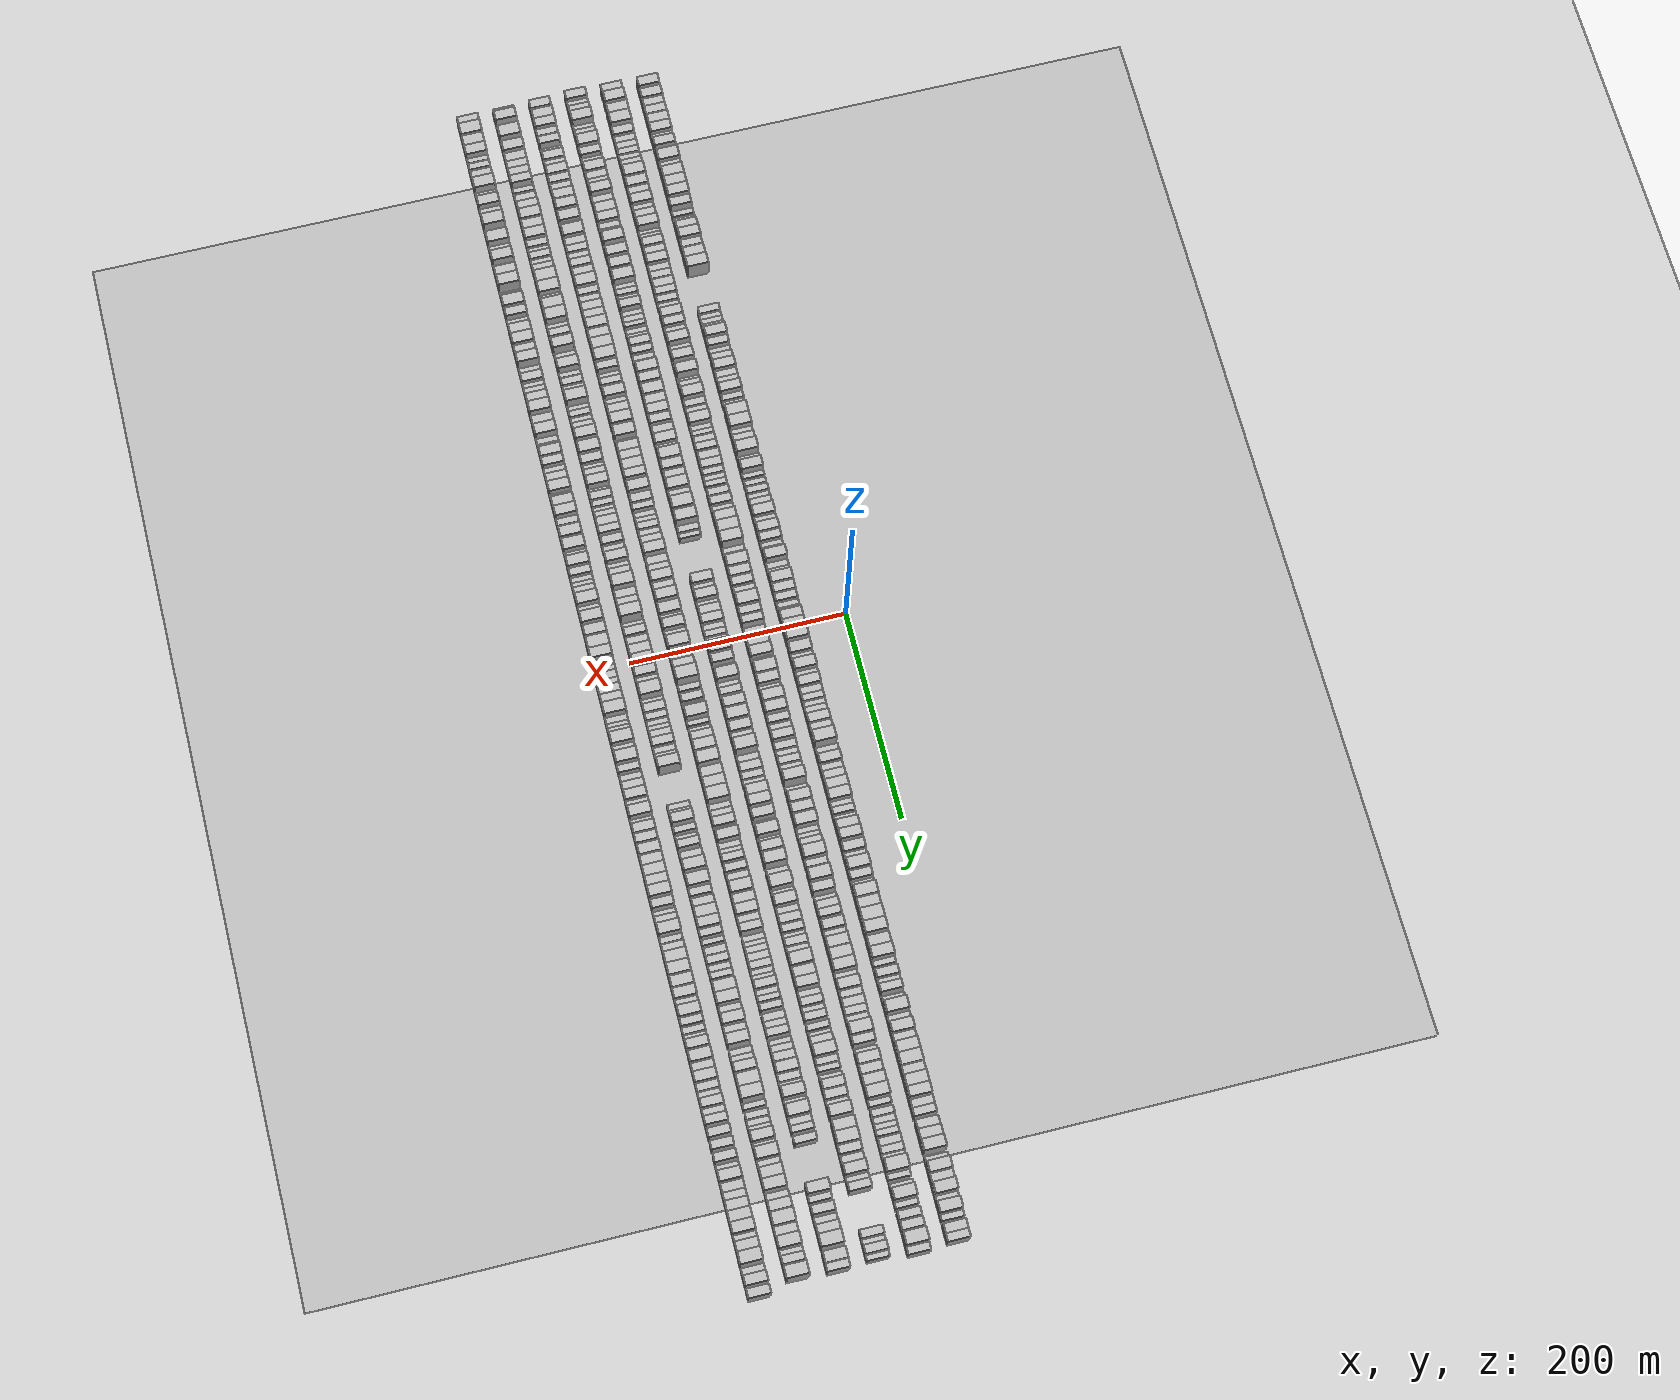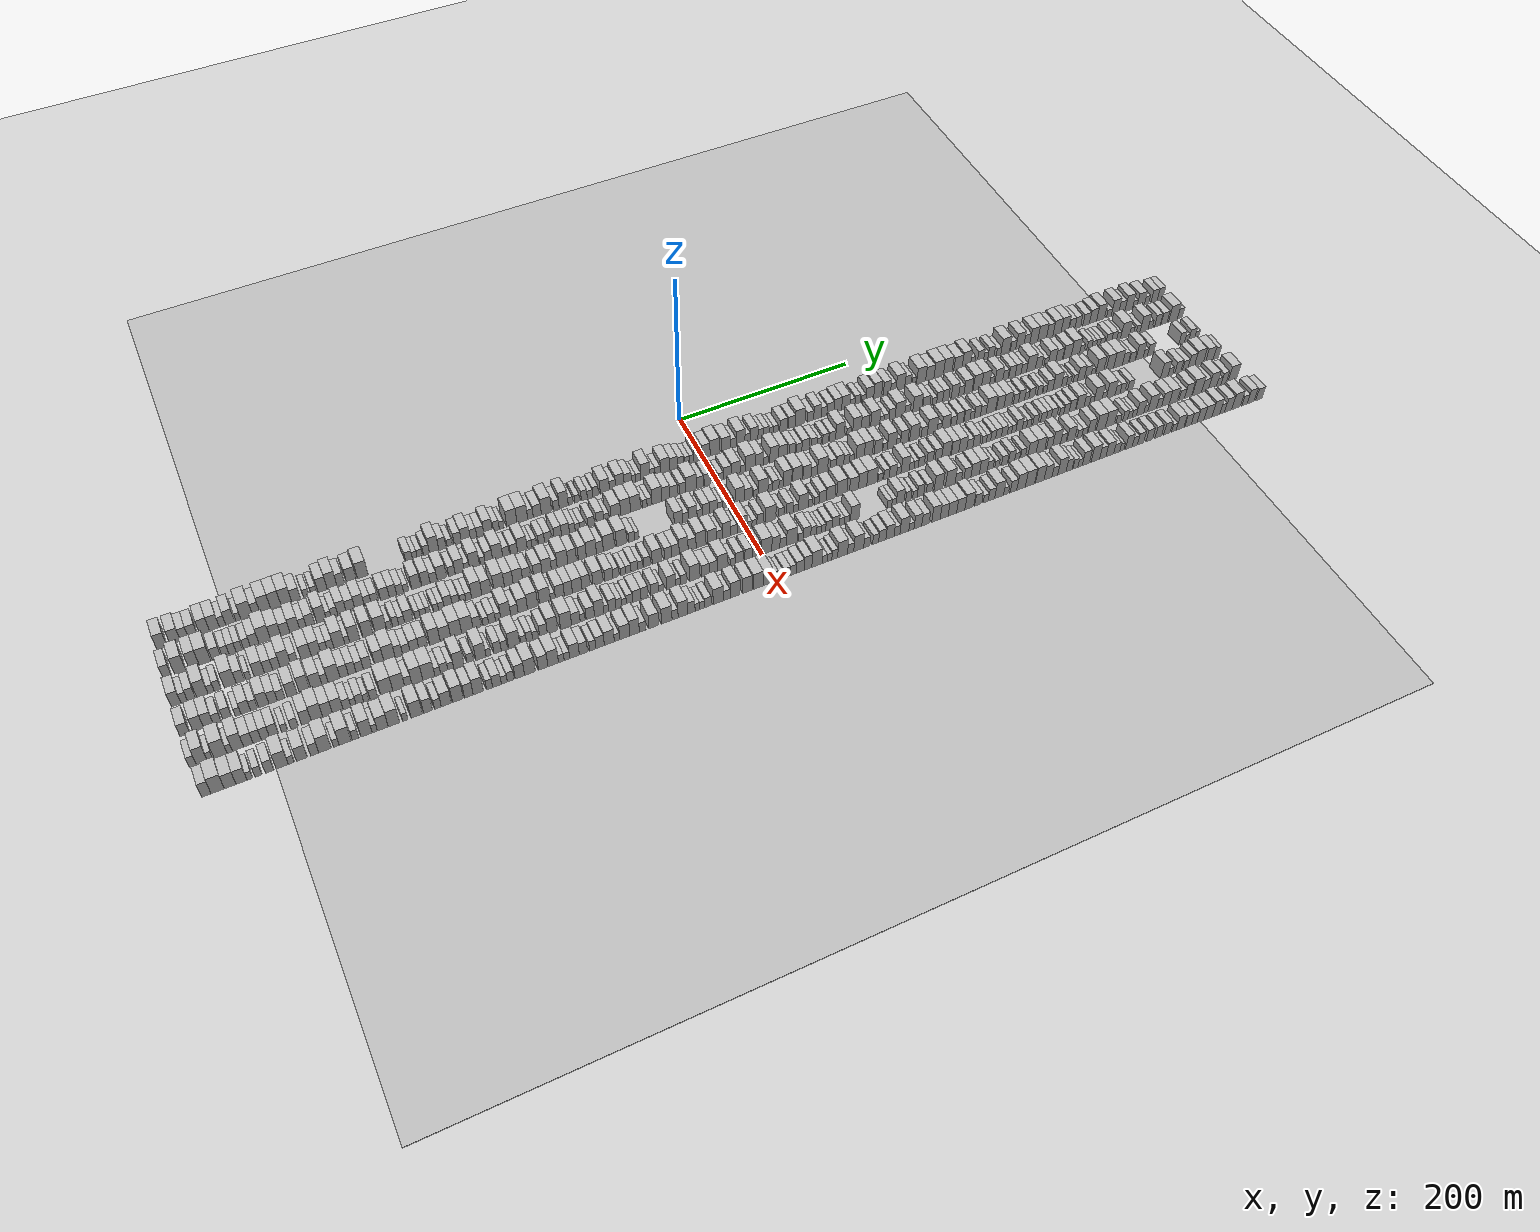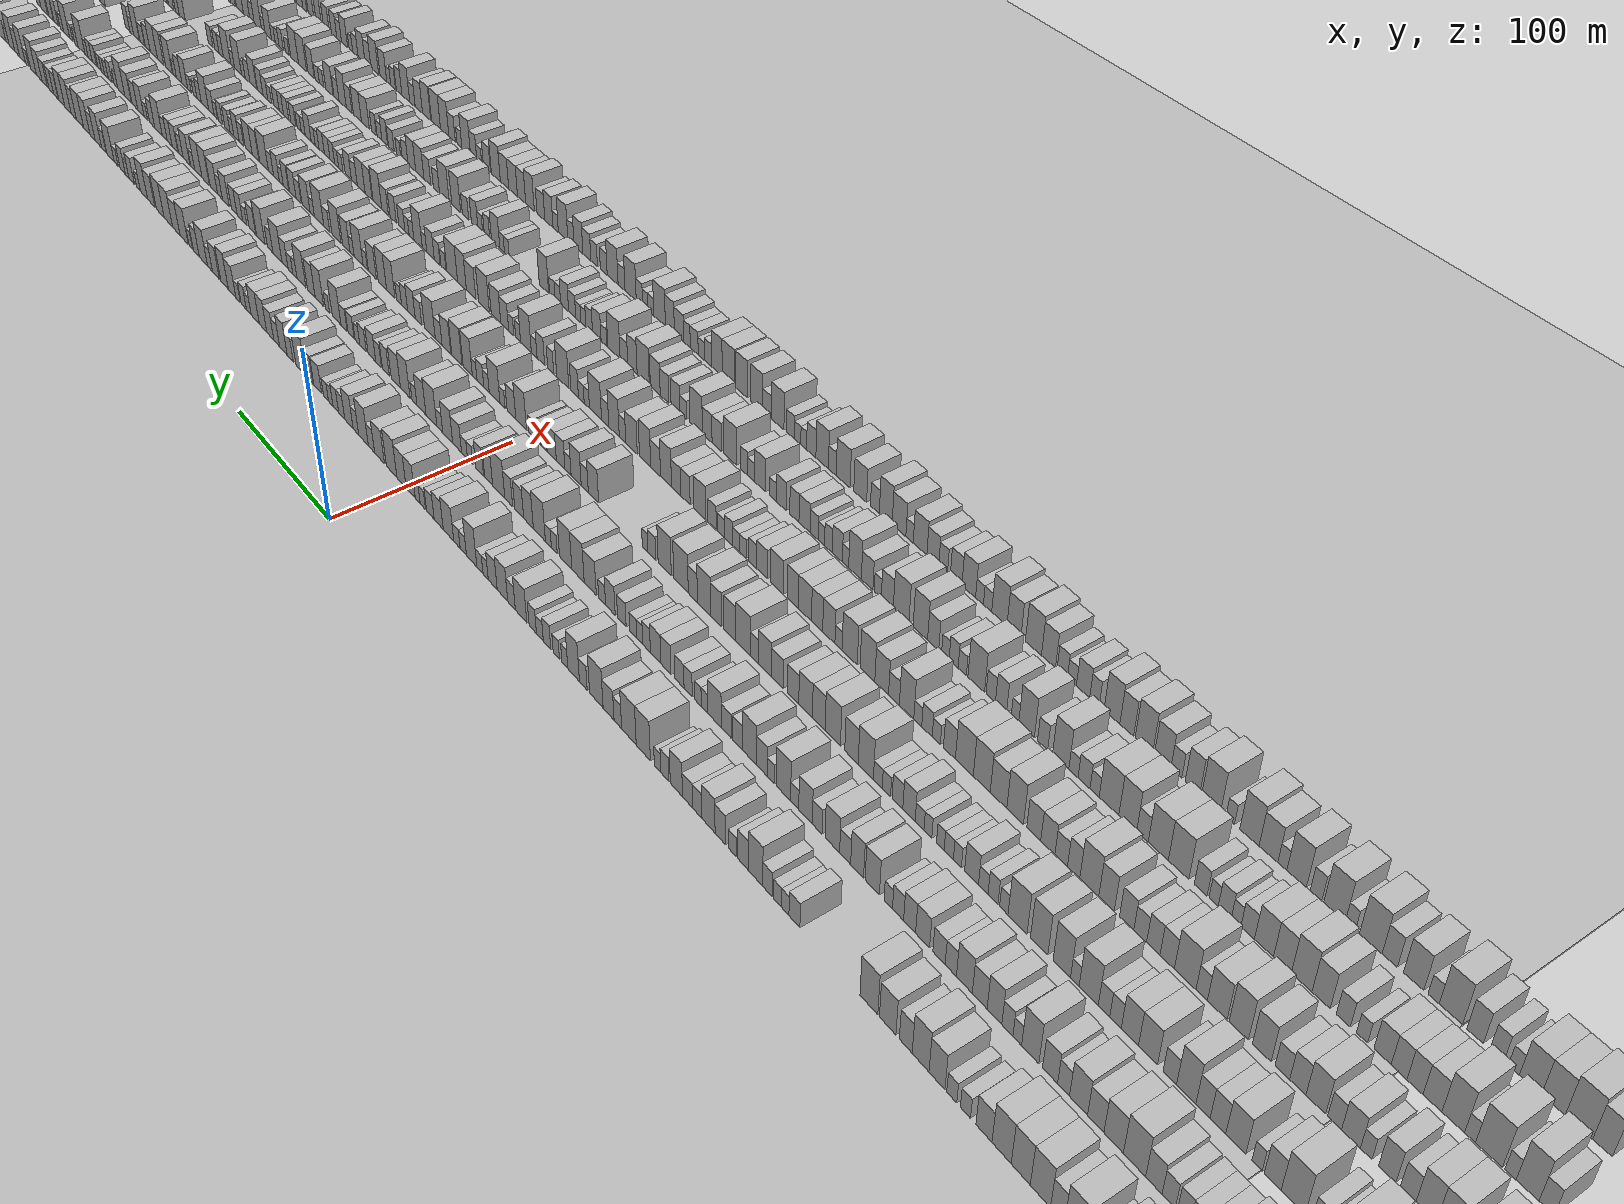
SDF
<?xml version="1.0" encoding="utf-8"?>

<sdf version="1.6">

   <world name="default">

      <gui fullscreen="0">

         <camera name="user_camera">

            <pose>-15 0 4.57585 0 0 0</pose>

            <view_controller>orbit</view_controller>

         </camera>

      </gui>

      <scene>

         <sky>

           <clouds>

             <speed>12</speed>

           </clouds>

         </sky>

         <ambient>0.4 0.4 0.4 1</ambient>

         <background>0.7 0.7 0.7 1</background>

         <shadows>1</shadows>

      </scene>

      <gravity>0 0 -9.8066</gravity>

      <magnetic_field>6e-06 2.3e-05 -4.2e-05</magnetic_field>

      <physics default="0" name="default_physics" type="ode">

         <ode>

            <solver>

               <type>quick</type>

               <iters>10</iters>

               <sor>1.0</sor>

               <use_dynamic_moi_rescaling>0</use_dynamic_moi_rescaling>

            </solver>

            <constraints>

               <cfm>0</cfm>

               <erp>0.2</erp>

               <contact_max_correcting_vel>100</contact_max_correcting_vel>

               <contact_surface_layer>0.001</contact_surface_layer>

            </constraints>

         </ode>

         <max_step_size>0.004</max_step_size>

         <real_time_factor>1</real_time_factor>

         <real_time_update_rate>250</real_time_update_rate>

      </physics>

      <light name="sun" type="directional">

         <cast_shadows>1</cast_shadows>

         <pose>0 0 10 0 0 0</pose>

         <diffuse>0.8 0.8 0.8 1</diffuse>

         <specular>0.2 0.2 0.2 1</specular>

         <attenuation>

            <range>1000</range>

            <constant>0.9</constant>

            <linear>0.01</linear>

            <quadratic>0.001</quadratic>

         </attenuation>

         <direction>-0.5 0.1 -0.9</direction>

      </light>

      <include>

         <name>ground_plane_1</name>

         <uri>model://HANNAS_ground_plane</uri>

         <pose>0 0 0  0 0 0</pose>

      </include>

      <include>

         <name>ground_plane_2</name>

         <uri>model://HANNAS_ground_plane</uri>

         <pose>100 0 0  0 0 0</pose>

      </include>

      <model name="building_1">

         <static>1</static>

         <pose frame="">50.0000 -563.1156 0 0.000000 0.000000 0.000000</pose>

         <link name="link">

            <pose frame="">0 0 10.50 0 0 0</pose>

            <collision name="collision">

               <geometry>

                  <box>

                     <size>20.0000 9.7688 21.0000</size>

                  </box>

               </geometry>

               <max_contacts>10</max_contacts>

               <surface>

                  <contact>

                     <ode/>

                  </contact>

                  <bounce/>

                  <friction>

                     <torsional>

                        <ode/>

                     </torsional>

                     <ode/>

                  </friction>

               </surface>

            </collision>

            <visual name="visual">

               <cast_shadows>0</cast_shadows>

               <geometry>

                  <box>

                     <size>20.0000 9.7688 21.0000</size>

                  </box>

               </geometry>

               <material>

                  <script>

                     <uri>model://HANNAS_wall/materials/scripts</uri>

                     <uri>model://HANNAS_wall/materials/textures</uri>

                     <name>vrc/HANNAS_wall</name>

                  </script>

               </material>

            </visual>

            <self_collide>0</self_collide>

            <enable_wind>0</enable_wind>

            <kinematic>0</kinematic>

         </link>

      </model>

      <model name="building_2">

         <static>1</static>

         <pose frame="">50.0000 -550.3278 0 0.000000 0.000000 0.000000</pose>

         <link name="link">

            <pose frame="">0 0 10.50 0 0 0</pose>

            <collision name="collision">

               <geometry>

                  <box>

                     <size>20.0000 9.8068 21.0000</size>

                  </box>

               </geometry>

               <max_contacts>10</max_contacts>

               <surface>

                  <contact>

                     <ode/>

                  </contact>

                  <bounce/>

                  <friction>

                     <torsional>

                        <ode/>

                     </torsional>

                     <ode/>

                  </friction>

               </surface>

            </collision>

            <visual name="visual">

               <cast_shadows>0</cast_shadows>

               <geometry>

                  <box>

                     <size>20.0000 9.8068 21.0000</size>

                  </box>

               </geometry>

               <material>

                  <script>

                     <uri>model://HANNAS_wall/materials/scripts</uri>

                     <uri>model://HANNAS_wall/materials/textures</uri>

                     <name>vrc/HANNAS_wall</name>

                  </script>

               </material>

            </visual>

            <self_collide>0</self_collide>

            <enable_wind>0</enable_wind>

            <kinematic>0</kinematic>

         </link>

      </model>

      <model name="building_3">

         <static>1</static>

         <pose frame="">50.0000 -541.5469 0 0.000000 0.000000 0.000000</pose>

         <link name="link">

            <pose frame="">0 0 9.00 0 0 0</pose>

            <collision name="collision">

               <geometry>

                  <box>

                     <size>20.0000 7.7550 18.0000</size>

                  </box>

               </geometry>

               <max_contacts>10</max_contacts>

               <surface>

                  <contact>

                     <ode/>

                  </contact>

                  <bounce/>

                  <friction>

                     <torsional>

                        <ode/>

                     </torsional>

                     <ode/>

                  </friction>

               </surface>

            </collision>

            <visual name="visual">

               <cast_shadows>0</cast_shadows>

               <geometry>

                  <box>

                     <size>20.0000 7.7550 18.0000</size>

                  </box>

               </geometry>

               <material>

                  <script>

                     <uri>model://HANNAS_wall/materials/scripts</uri>

                     <uri>model://HANNAS_wall/materials/textures</uri>

                     <name>vrc/HANNAS_wall</name>

                  </script>

               </material>

            </visual>

            <self_collide>0</self_collide>

            <enable_wind>0</enable_wind>

            <kinematic>0</kinematic>

         </link>

      </model>

      <model name="building_4">

         <static>1</static>

         <pose frame="">50.0000 -533.3783 0 0.000000 0.000000 0.000000</pose>

         <link name="link">

            <pose frame="">0 0 9.00 0 0 0</pose>

            <collision name="collision">

               <geometry>

                  <box>

                     <size>20.0000 8.5822 18.0000</size>

                  </box>

               </geometry>

               <max_contacts>10</max_contacts>

               <surface>

                  <contact>

                     <ode/>

                  </contact>

                  <bounce/>

                  <friction>

                     <torsional>

                        <ode/>

                     </torsional>

                     <ode/>

                  </friction>

               </surface>

            </collision>

            <visual name="visual">

               <cast_shadows>0</cast_shadows>

               <geometry>

                  <box>

                     <size>20.0000 8.5822 18.0000</size>

                  </box>

               </geometry>

               <material>

                  <script>

                     <uri>model://HANNAS_wall/materials/scripts</uri>

                     <uri>model://HANNAS_wall/materials/textures</uri>

                     <name>vrc/HANNAS_wall</name>

                  </script>

               </material>

            </visual>

            <self_collide>0</self_collide>

            <enable_wind>0</enable_wind>

            <kinematic>0</kinematic>

         </link>

      </model>

      <model name="building_5">

         <static>1</static>

         <pose frame="">50.0000 -522.4231 0 0.000000 0.000000 0.000000</pose>

         <link name="link">

            <pose frame="">0 0 10.50 0 0 0</pose>

            <collision name="collision">

               <geometry>

                  <box>

                     <size>20.0000 9.3281 21.0000</size>

                  </box>

               </geometry>

               <max_contacts>10</max_contacts>

               <surface>

                  <contact>

                     <ode/>

                  </contact>

                  <bounce/>

                  <friction>

                     <torsional>

                        <ode/>

                     </torsional>

                     <ode/>

                  </friction>

               </surface>

            </collision>

            <visual name="visual">

               <cast_shadows>0</cast_shadows>

               <geometry>

                  <box>

                     <size>20.0000 9.3281 21.0000</size>

                  </box>

               </geometry>

               <material>

                  <script>

                     <uri>model://HANNAS_wall/materials/scripts</uri>

                     <uri>model://HANNAS_wall/materials/textures</uri>

                     <name>vrc/HANNAS_wall</name>

                  </script>

               </material>

            </visual>

            <self_collide>0</self_collide>

            <enable_wind>0</enable_wind>

            <kinematic>0</kinematic>

         </link>

      </model>

      <model name="building_6">

         <static>1</static>

         <pose frame="">50.0000 -512.9156 0 0.000000 0.000000 0.000000</pose>

         <link name="link">

            <pose frame="">0 0 10.50 0 0 0</pose>

            <collision name="collision">

               <geometry>

                  <box>

                     <size>20.0000 9.6869 21.0000</size>

                  </box>

               </geometry>

               <max_contacts>10</max_contacts>

               <surface>

                  <contact>

                     <ode/>

                  </contact>

                  <bounce/>

                  <friction>

                     <torsional>

                        <ode/>

                     </torsional>

                     <ode/>

                  </friction>

               </surface>

            </collision>

            <visual name="visual">

               <cast_shadows>0</cast_shadows>

               <geometry>

                  <box>

                     <size>20.0000 9.6869 21.0000</size>

                  </box>

               </geometry>

               <material>

                  <script>

                     <uri>model://HANNAS_wall/materials/scripts</uri>

                     <uri>model://HANNAS_wall/materials/textures</uri>

                     <name>vrc/HANNAS_wall</name>

                  </script>

               </material>

            </visual>

            <self_collide>0</self_collide>

            <enable_wind>0</enable_wind>

            <kinematic>0</kinematic>

         </link>

      </model>

      <model name="building_7">

         <static>1</static>

         <pose frame="">50.0000 -505.0529 0 0.000000 0.000000 0.000000</pose>

         <link name="link">

            <pose frame="">0 0 7.50 0 0 0</pose>

            <collision name="collision">

               <geometry>

                  <box>

                     <size>20.0000 6.0387 15.0000</size>

                  </box>

               </geometry>

               <max_contacts>10</max_contacts>

               <surface>

                  <contact>

                     <ode/>

                  </contact>

                  <bounce/>

                  <friction>

                     <torsional>

                        <ode/>

                     </torsional>

                     <ode/>

                  </friction>

               </surface>

            </collision>

            <visual name="visual">

               <cast_shadows>0</cast_shadows>

               <geometry>

                  <box>

                     <size>20.0000 6.0387 15.0000</size>

                  </box>

               </geometry>

               <material>

                  <script>

                     <uri>model://HANNAS_wall/materials/scripts</uri>

                     <uri>model://HANNAS_wall/materials/textures</uri>

                     <name>vrc/HANNAS_wall</name>

                  </script>

               </material>

            </visual>

            <self_collide>0</self_collide>

            <enable_wind>0</enable_wind>

            <kinematic>0</kinematic>

         </link>

      </model>

      <model name="building_8">

         <static>1</static>

         <pose frame="">50.0000 -497.5625 0 0.000000 0.000000 0.000000</pose>

         <link name="link">

            <pose frame="">0 0 10.50 0 0 0</pose>

            <collision name="collision">

               <geometry>

                  <box>

                     <size>20.0000 8.9421 21.0000</size>

                  </box>

               </geometry>

               <max_contacts>10</max_contacts>

               <surface>

                  <contact>

                     <ode/>

                  </contact>

                  <bounce/>

                  <friction>

                     <torsional>

                        <ode/>

                     </torsional>

                     <ode/>

                  </friction>

               </surface>

            </collision>

            <visual name="visual">

               <cast_shadows>0</cast_shadows>

               <geometry>

                  <box>

                     <size>20.0000 8.9421 21.0000</size>

                  </box>

               </geometry>

               <material>

                  <script>

                     <uri>model://HANNAS_wall/materials/scripts</uri>

                     <uri>model://HANNAS_wall/materials/textures</uri>

                     <name>vrc/HANNAS_wall</name>

                  </script>

               </material>

            </visual>

            <self_collide>0</self_collide>

            <enable_wind>0</enable_wind>

            <kinematic>0</kinematic>

         </link>

      </model>

      <model name="building_9">

         <static>1</static>

         <pose frame="">50.0000 -489.6624 0 0.000000 0.000000 0.000000</pose>

         <link name="link">

            <pose frame="">0 0 6.00 0 0 0</pose>

            <collision name="collision">

               <geometry>

                  <box>

                     <size>20.0000 4.8581 12.0000</size>

                  </box>

               </geometry>

               <max_contacts>10</max_contacts>

               <surface>

                  <contact>

                     <ode/>

                  </contact>

                  <bounce/>

                  <friction>

                     <torsional>

                        <ode/>

                     </torsional>

                     <ode/>

                  </friction>

               </surface>

            </collision>

            <visual name="visual">

               <cast_shadows>0</cast_shadows>

               <geometry>

                  <box>

                     <size>20.0000 4.8581 12.0000</size>

                  </box>

               </geometry>

               <material>

                  <script>

                     <uri>model://HANNAS_wall/materials/scripts</uri>

                     <uri>model://HANNAS_wall/materials/textures</uri>

                     <name>vrc/HANNAS_wall</name>

                  </script>

               </material>

            </visual>

            <self_collide>0</self_collide>

            <enable_wind>0</enable_wind>

            <kinematic>0</kinematic>

         </link>

      </model>

      <model name="building_10">

         <static>1</static>

         <pose frame="">50.0000 -481.5373 0 0.000000 0.000000 0.000000</pose>

         <link name="link">

            <pose frame="">0 0 12.00 0 0 0</pose>

            <collision name="collision">

               <geometry>

                  <box>

                     <size>20.0000 11.3920 24.0000</size>

                  </box>

               </geometry>

               <max_contacts>10</max_contacts>

               <surface>

                  <contact>

                     <ode/>

                  </contact>

                  <bounce/>

                  <friction>

                     <torsional>

                        <ode/>

                     </torsional>

                     <ode/>

                  </friction>

               </surface>

            </collision>

            <visual name="visual">

               <cast_shadows>0</cast_shadows>

               <geometry>

                  <box>

                     <size>20.0000 11.3920 24.0000</size>

                  </box>

               </geometry>

               <material>

                  <script>

                     <uri>model://HANNAS_wall/materials/scripts</uri>

                     <uri>model://HANNAS_wall/materials/textures</uri>

                     <name>vrc/HANNAS_wall</name>

                  </script>

               </material>

            </visual>

            <self_collide>0</self_collide>

            <enable_wind>0</enable_wind>

            <kinematic>0</kinematic>

         </link>

      </model>

      <model name="building_11">

         <static>1</static>

         <pose frame="">50.0000 -472.2387 0 0.000000 0.000000 0.000000</pose>

         <link name="link">

            <pose frame="">0 0 9.00 0 0 0</pose>

            <collision name="collision">

               <geometry>

                  <box>

                     <size>20.0000 7.2051 18.0000</size>

                  </box>

               </geometry>

               <max_contacts>10</max_contacts>

               <surface>

                  <contact>

                     <ode/>

                  </contact>

                  <bounce/>

                  <friction>

                     <torsional>

                        <ode/>

                     </torsional>

                     <ode/>

                  </friction>

               </surface>

            </collision>

            <visual name="visual">

               <cast_shadows>0</cast_shadows>

               <geometry>

                  <box>

                     <size>20.0000 7.2051 18.0000</size>

                  </box>

               </geometry>

               <material>

                  <script>

                     <uri>model://HANNAS_wall/materials/scripts</uri>

                     <uri>model://HANNAS_wall/materials/textures</uri>

                     <name>vrc/HANNAS_wall</name>

                  </script>

               </material>

            </visual>

            <self_collide>0</self_collide>

            <enable_wind>0</enable_wind>

            <kinematic>0</kinematic>

         </link>

      </model>

      <model name="building_12">

         <static>1</static>

         <pose frame="">50.0000 -463.3675 0 0.000000 0.000000 0.000000</pose>

         <link name="link">

            <pose frame="">0 0 12.00 0 0 0</pose>

            <collision name="collision">

               <geometry>

                  <box>

                     <size>20.0000 10.5374 24.0000</size>

                  </box>

               </geometry>

               <max_contacts>10</max_contacts>

               <surface>

                  <contact>

                     <ode/>

                  </contact>

                  <bounce/>

                  <friction>

                     <torsional>

                        <ode/>

                     </torsional>

                     <ode/>

                  </friction>

               </surface>

            </collision>

            <visual name="visual">

               <cast_shadows>0</cast_shadows>

               <geometry>

                  <box>

                     <size>20.0000 10.5374 24.0000</size>

                  </box>

               </geometry>

               <material>

                  <script>

                     <uri>model://HANNAS_wall/materials/scripts</uri>

                     <uri>model://HANNAS_wall/materials/textures</uri>

                     <name>vrc/HANNAS_wall</name>

                  </script>

               </material>

            </visual>

            <self_collide>0</self_collide>

            <enable_wind>0</enable_wind>

            <kinematic>0</kinematic>

         </link>

      </model>

      <model name="building_13">

         <static>1</static>

         <pose frame="">50.0000 -453.0136 0 0.000000 0.000000 0.000000</pose>

         <link name="link">

            <pose frame="">0 0 12.00 0 0 0</pose>

            <collision name="collision">

               <geometry>

                  <box>

                     <size>20.0000 10.1703 24.0000</size>

                  </box>

               </geometry>

               <max_contacts>10</max_contacts>

               <surface>

                  <contact>

                     <ode/>

                  </contact>

                  <bounce/>

                  <friction>

                     <torsional>

                        <ode/>

                     </torsional>

                     <ode/>

                  </friction>

               </surface>

            </collision>

            <visual name="visual">

               <cast_shadows>0</cast_shadows>

               <geometry>

                  <box>

                     <size>20.0000 10.1703 24.0000</size>

                  </box>

               </geometry>

               <material>

                  <script>

                     <uri>model://HANNAS_wall/materials/scripts</uri>

                     <uri>model://HANNAS_wall/materials/textures</uri>

                     <name>vrc/HANNAS_wall</name>

                  </script>

               </material>

            </visual>

            <self_collide>0</self_collide>

            <enable_wind>0</enable_wind>

            <kinematic>0</kinematic>

         </link>

      </model>

      <model name="building_14">

         <static>1</static>

         <pose frame="">50.0000 -442.7183 0 0.000000 0.000000 0.000000</pose>

         <link name="link">

            <pose frame="">0 0 12.00 0 0 0</pose>

            <collision name="collision">

               <geometry>

                  <box>

                     <size>20.0000 10.4204 24.0000</size>

                  </box>

               </geometry>

               <max_contacts>10</max_contacts>

               <surface>

                  <contact>

                     <ode/>

                  </contact>

                  <bounce/>

                  <friction>

                     <torsional>

                        <ode/>

                     </torsional>

                     <ode/>

                  </friction>

               </surface>

            </collision>

            <visual name="visual">

               <cast_shadows>0</cast_shadows>

               <geometry>

                  <box>

                     <size>20.0000 10.4204 24.0000</size>

                  </box>

               </geometry>

               <material>

                  <script>

                     <uri>model://HANNAS_wall/materials/scripts</uri>

                     <uri>model://HANNAS_wall/materials/textures</uri>

                     <name>vrc/HANNAS_wall</name>

                  </script>

               </material>

            </visual>

            <self_collide>0</self_collide>

            <enable_wind>0</enable_wind>

            <kinematic>0</kinematic>

         </link>

      </model>

      <model name="building_15">

         <static>1</static>

         <pose frame="">50.0000 -433.0981 0 0.000000 0.000000 0.000000</pose>

         <link name="link">

            <pose frame="">0 0 9.00 0 0 0</pose>

            <collision name="collision">

               <geometry>

                  <box>

                     <size>20.0000 8.8200 18.0000</size>

                  </box>

               </geometry>

               <max_contacts>10</max_contacts>

               <surface>

                  <contact>

                     <ode/>

                  </contact>

                  <bounce/>

                  <friction>

                     <torsional>

                        <ode/>

                     </torsional>

                     <ode/>

                  </friction>

               </surface>

            </collision>

            <visual name="visual">

               <cast_shadows>0</cast_shadows>

               <geometry>

                  <box>

                     <size>20.0000 8.8200 18.0000</size>

                  </box>

               </geometry>

               <material>

                  <script>

                     <uri>model://HANNAS_wall/materials/scripts</uri>

                     <uri>model://HANNAS_wall/materials/textures</uri>

                     <name>vrc/HANNAS_wall</name>

                  </script>

               </material>

            </visual>

            <self_collide>0</self_collide>

            <enable_wind>0</enable_wind>

            <kinematic>0</kinematic>

         </link>

      </model>

      <model name="building_16">

         <static>1</static>

         <pose frame="">50.0000 -422.8419 0 0.000000 0.000000 0.000000</pose>

         <link name="link">

            <pose frame="">0 0 6.00 0 0 0</pose>

            <collision name="collision">

               <geometry>

                  <box>

                     <size>20.0000 5.6923 12.0000</size>

                  </box>

               </geometry>

               <max_contacts>10</max_contacts>

               <surface>

                  <contact>

                     <ode/>

                  </contact>

                  <bounce/>

                  <friction>

                     <torsional>

                        <ode/>

                     </torsional>

                     <ode/>

                  </friction>

               </surface>

            </collision>

            <visual name="visual">

               <cast_shadows>0</cast_shadows>

               <geometry>

                  <box>

                     <size>20.0000 5.6923 12.0000</size>

                  </box>

               </geometry>

               <material>

                  <script>

                     <uri>model://HANNAS_wall/materials/scripts</uri>

                     <uri>model://HANNAS_wall/materials/textures</uri>

                     <name>vrc/HANNAS_wall</name>

                  </script>

               </material>

            </visual>

            <self_collide>0</self_collide>

            <enable_wind>0</enable_wind>

            <kinematic>0</kinematic>

         </link>

      </model>

      <model name="building_17">

         <static>1</static>

         <pose frame="">50.0000 -415.1383 0 0.000000 0.000000 0.000000</pose>

         <link name="link">

            <pose frame="">0 0 6.00 0 0 0</pose>

            <collision name="collision">

               <geometry>

                  <box>

                     <size>20.0000 5.7149 12.0000</size>

                  </box>

               </geometry>

               <max_contacts>10</max_contacts>

               <surface>

                  <contact>

                     <ode/>

                  </contact>

                  <bounce/>

                  <friction>

                     <torsional>

                        <ode/>

                     </torsional>

                     <ode/>

                  </friction>

               </surface>

            </collision>

            <visual name="visual">

               <cast_shadows>0</cast_shadows>

               <geometry>

                  <box>

                     <size>20.0000 5.7149 12.0000</size>

                  </box>

               </geometry>

               <material>

                  <script>

                     <uri>model://HANNAS_wall/materials/scripts</uri>

                     <uri>model://HANNAS_wall/materials/textures</uri>

                     <name>vrc/HANNAS_wall</name>

                  </script>

               </material>

            </visual>

            <self_collide>0</self_collide>

            <enable_wind>0</enable_wind>

            <kinematic>0</kinematic>

         </link>

      </model>

      <model name="building_18">

         <static>1</static>

         <pose frame="">50.0000 -406.6968 0 0.000000 0.000000 0.000000</pose>

         <link name="link">

            <pose frame="">0 0 10.50 0 0 0</pose>

            <collision name="collision">

               <geometry>

                  <box>

                     <size>20.0000 9.1681 21.0000</size>

                  </box>

               </geometry>

               <max_contacts>10</max_contacts>

               <surface>

                  <contact>

                     <ode/>

                  </contact>

                  <bounce/>

                  <friction>

                     <torsional>

                        <ode/>

                     </torsional>

                     <ode/>

                  </friction>

               </surface>

            </collision>

            <visual name="visual">

               <cast_shadows>0</cast_shadows>

               <geometry>

                  <box>

                     <size>20.0000 9.1681 21.0000</size>

                  </box>

               </geometry>

               <material>

                  <script>

                     <uri>model://HANNAS_wall/materials/scripts</uri>

                     <uri>model://HANNAS_wall/materials/textures</uri>

                     <name>vrc/HANNAS_wall</name>

                  </script>

               </material>

            </visual>

            <self_collide>0</self_collide>

            <enable_wind>0</enable_wind>

            <kinematic>0</kinematic>

         </link>

      </model>

      <model name="building_19">

         <static>1</static>

         <pose frame="">50.0000 -397.2139 0 0.000000 0.000000 0.000000</pose>

         <link name="link">

            <pose frame="">0 0 12.00 0 0 0</pose>

            <collision name="collision">

               <geometry>

                  <box>

                     <size>20.0000 9.7977 24.0000</size>

                  </box>

               </geometry>

               <max_contacts>10</max_contacts>

               <surface>

                  <contact>

                     <ode/>

                  </contact>

                  <bounce/>

                  <friction>

                     <torsional>

                        <ode/>

                     </torsional>

                     <ode/>

                  </friction>

               </surface>

            </collision>

            <visual name="visual">

               <cast_shadows>0</cast_shadows>

               <geometry>

                  <box>

                     <size>20.0000 9.7977 24.0000</size>

                  </box>

               </geometry>

               <material>

                  <script>

                     <uri>model://HANNAS_wall/materials/scripts</uri>

                     <uri>model://HANNAS_wall/materials/textures</uri>

                     <name>vrc/HANNAS_wall</name>

                  </script>

               </material>

            </visual>

            <self_collide>0</self_collide>

            <enable_wind>0</enable_wind>

            <kinematic>0</kinematic>

         </link>

      </model>

      <model name="building_20">

         <static>1</static>

         <pose frame="">50.0000 -388.5023 0 0.000000 0.000000 0.000000</pose>

         <link name="link">

            <pose frame="">0 0 9.00 0 0 0</pose>

            <collision name="collision">

               <geometry>

                  <box>

                     <size>20.0000 7.6254 18.0000</size>

                  </box>

               </geometry>

               <max_contacts>10</max_contacts>

               <surface>

                  <contact>

                     <ode/>

                  </contact>

                  <bounce/>

                  <friction>

                     <torsional>

                        <ode/>

                     </torsional>

                     <ode/>

                  </friction>

               </surface>

            </collision>

            <visual name="visual">

               <cast_shadows>0</cast_shadows>

               <geometry>

                  <box>

                     <size>20.0000 7.6254 18.0000</size>

                  </box>

               </geometry>

               <material>

                  <script>

                     <uri>model://HANNAS_wall/materials/scripts</uri>

                     <uri>model://HANNAS_wall/materials/textures</uri>

                     <name>vrc/HANNAS_wall</name>

                  </script>

               </material>

            </visual>

            <self_collide>0</self_collide>

            <enable_wind>0</enable_wind>

            <kinematic>0</kinematic>

         </link>

      </model>

      <model name="building_21">

         <static>1</static>

         <pose frame="">50.0000 -377.7270 0 0.000000 0.000000 0.000000</pose>

         <link name="link">

            <pose frame="">0 0 10.50 0 0 0</pose>

            <collision name="collision">

               <geometry>

                  <box>

                     <size>20.0000 9.9251 21.0000</size>

                  </box>

               </geometry>

               <max_contacts>10</max_contacts>

               <surface>

                  <contact>

                     <ode/>

                  </contact>

                  <bounce/>

                  <friction>

                     <torsional>

                        <ode/>

                     </torsional>

                     <ode/>

                  </friction>

               </surface>

            </collision>

            <visual name="visual">

               <cast_shadows>0</cast_shadows>

               <geometry>

                  <box>

                     <size>20.0000 9.9251 21.0000</size>

                  </box>

               </geometry>

               <material>

                  <script>

                     <uri>model://HANNAS_wall/materials/scripts</uri>

                     <uri>model://HANNAS_wall/materials/textures</uri>

                     <name>vrc/HANNAS_wall</name>

                  </script>

               </material>

            </visual>

            <self_collide>0</self_collide>

            <enable_wind>0</enable_wind>

            <kinematic>0</kinematic>

         </link>

      </model>

      <model name="building_22">

         <static>1</static>

         <pose frame="">50.0000 -366.3055 0 0.000000 0.000000 0.000000</pose>

         <link name="link">

            <pose frame="">0 0 12.00 0 0 0</pose>

            <collision name="collision">

               <geometry>

                  <box>

                     <size>20.0000 10.9180 24.0000</size>

                  </box>

               </geometry>

               <max_contacts>10</max_contacts>

               <surface>

                  <contact>

                     <ode/>

                  </contact>

                  <bounce/>

                  <friction>

                     <torsional>

                        <ode/>

                     </torsional>

                     <ode/>

                  </friction>

               </surface>

            </collision>

            <visual name="visual">

               <cast_shadows>0</cast_shadows>

               <geometry>

                  <box>

                     <size>20.0000 10.9180 24.0000</size>

                  </box>

               </geometry>

               <material>

                  <script>

                     <uri>model://HANNAS_wall/materials/scripts</uri>

                     <uri>model://HANNAS_wall/materials/textures</uri>

                     <name>vrc/HANNAS_wall</name>

                  </script>

               </material>

            </visual>

            <self_collide>0</self_collide>

            <enable_wind>0</enable_wind>

            <kinematic>0</kinematic>

         </link>

      </model>

      <model name="building_23">

         <static>1</static>

         <pose frame="">50.0000 -318.9872 0 0.000000 0.000000 0.000000</pose>

         <link name="link">

            <pose frame="">0 0 7.50 0 0 0</pose>

            <collision name="collision">

               <geometry>

                  <box>

                     <size>20.0000 7.2395 15.0000</size>

                  </box>

               </geometry>

               <max_contacts>10</max_contacts>

               <surface>

                  <contact>

                     <ode/>

                  </contact>

                  <bounce/>

                  <friction>

                     <torsional>

                        <ode/>

                     </torsional>

                     <ode/>

                  </friction>

               </surface>

            </collision>

            <visual name="visual">

               <cast_shadows>0</cast_shadows>

               <geometry>

                  <box>

                     <size>20.0000 7.2395 15.0000</size>

                  </box>

               </geometry>

               <material>

                  <script>

                     <uri>model://HANNAS_wall/materials/scripts</uri>

                     <uri>model://HANNAS_wall/materials/textures</uri>

                     <name>vrc/HANNAS_wall</name>

                  </script>

               </material>

            </visual>

            <self_collide>0</self_collide>

            <enable_wind>0</enable_wind>

            <kinematic>0</kinematic>

         </link>

      </model>

      <model name="building_24">

         <static>1</static>

         <pose frame="">50.0000 -312.9654 0 0.000000 0.000000 0.000000</pose>

         <link name="link">

            <pose frame="">0 0 6.00 0 0 0</pose>

            <collision name="collision">

               <geometry>

                  <box>

                     <size>20.0000 4.8041 12.0000</size>

                  </box>

               </geometry>

               <max_contacts>10</max_contacts>

               <surface>

                  <contact>

                     <ode/>

                  </contact>

                  <bounce/>

                  <friction>

                     <torsional>

                        <ode/>

                     </torsional>

                     <ode/>

                  </friction>

               </surface>

            </collision>

            <visual name="visual">

               <cast_shadows>0</cast_shadows>

               <geometry>

                  <box>

                     <size>20.0000 4.8041 12.0000</size>

                  </box>

               </geometry>

               <material>

                  <script>

                     <uri>model://HANNAS_wall/materials/scripts</uri>

                     <uri>model://HANNAS_wall/materials/textures</uri>

                     <name>vrc/HANNAS_wall</name>

                  </script>

               </material>

            </visual>

            <self_collide>0</self_collide>

            <enable_wind>0</enable_wind>

            <kinematic>0</kinematic>

         </link>

      </model>

      <model name="building_25">

         <static>1</static>

         <pose frame="">50.0000 -307.8491 0 0.000000 0.000000 0.000000</pose>

         <link name="link">

            <pose frame="">0 0 6.00 0 0 0</pose>

            <collision name="collision">

               <geometry>

                  <box>

                     <size>20.0000 5.4284 12.0000</size>

                  </box>

               </geometry>

               <max_contacts>10</max_contacts>

               <surface>

                  <contact>

                     <ode/>

                  </contact>

                  <bounce/>

                  <friction>

                     <torsional>

                        <ode/>

                     </torsional>

                     <ode/>

                  </friction>

               </surface>

            </collision>

            <visual name="visual">

               <cast_shadows>0</cast_shadows>

               <geometry>

                  <box>

                     <size>20.0000 5.4284 12.0000</size>

                  </box>

               </geometry>

               <material>

                  <script>

                     <uri>model://HANNAS_wall/materials/scripts</uri>

                     <uri>model://HANNAS_wall/materials/textures</uri>

                     <name>vrc/HANNAS_wall</name>

                  </script>

               </material>

            </visual>

            <self_collide>0</self_collide>

            <enable_wind>0</enable_wind>

            <kinematic>0</kinematic>

         </link>

      </model>

      <model name="building_26">

         <static>1</static>

         <pose frame="">50.0000 -300.9718 0 0.000000 0.000000 0.000000</pose>

         <link name="link">

            <pose frame="">0 0 7.50 0 0 0</pose>

            <collision name="collision">

               <geometry>

                  <box>

                     <size>20.0000 6.3262 15.0000</size>

                  </box>

               </geometry>

               <max_contacts>10</max_contacts>

               <surface>

                  <contact>

                     <ode/>

                  </contact>

                  <bounce/>

                  <friction>

                     <torsional>

                        <ode/>

                     </torsional>

                     <ode/>

                  </friction>

               </surface>

            </collision>

            <visual name="visual">

               <cast_shadows>0</cast_shadows>

               <geometry>

                  <box>

                     <size>20.0000 6.3262 15.0000</size>

                  </box>

               </geometry>

               <material>

                  <script>

                     <uri>model://HANNAS_wall/materials/scripts</uri>

                     <uri>model://HANNAS_wall/materials/textures</uri>

                     <name>vrc/HANNAS_wall</name>

                  </script>

               </material>

            </visual>

            <self_collide>0</self_collide>

            <enable_wind>0</enable_wind>

            <kinematic>0</kinematic>

         </link>

      </model>

      <model name="building_27">

         <static>1</static>

         <pose frame="">50.0000 -292.9759 0 0.000000 0.000000 0.000000</pose>

         <link name="link">

            <pose frame="">0 0 12.00 0 0 0</pose>

            <collision name="collision">

               <geometry>

                  <box>

                     <size>20.0000 9.6657 24.0000</size>

                  </box>

               </geometry>

               <max_contacts>10</max_contacts>

               <surface>

                  <contact>

                     <ode/>

                  </contact>

                  <bounce/>

                  <friction>

                     <torsional>

                        <ode/>

                     </torsional>

                     <ode/>

                  </friction>

               </surface>

            </collision>

            <visual name="visual">

               <cast_shadows>0</cast_shadows>

               <geometry>

                  <box>

                     <size>20.0000 9.6657 24.0000</size>

                  </box>

               </geometry>

               <material>

                  <script>

                     <uri>model://HANNAS_wall/materials/scripts</uri>

                     <uri>model://HANNAS_wall/materials/textures</uri>

                     <name>vrc/HANNAS_wall</name>

                  </script>

               </material>

            </visual>

            <self_collide>0</self_collide>

            <enable_wind>0</enable_wind>

            <kinematic>0</kinematic>

         </link>

      </model>

      <model name="building_28">

         <static>1</static>

         <pose frame="">50.0000 -284.3116 0 0.000000 0.000000 0.000000</pose>

         <link name="link">

            <pose frame="">0 0 9.00 0 0 0</pose>

            <collision name="collision">

               <geometry>

                  <box>

                     <size>20.0000 7.6629 18.0000</size>

                  </box>

               </geometry>

               <max_contacts>10</max_contacts>

               <surface>

                  <contact>

                     <ode/>

                  </contact>

                  <bounce/>

                  <friction>

                     <torsional>

                        <ode/>

                     </torsional>

                     <ode/>

                  </friction>

               </surface>

            </collision>

            <visual name="visual">

               <cast_shadows>0</cast_shadows>

               <geometry>

                  <box>

                     <size>20.0000 7.6629 18.0000</size>

                  </box>

               </geometry>

               <material>

                  <script>

                     <uri>model://HANNAS_wall/materials/scripts</uri>

                     <uri>model://HANNAS_wall/materials/textures</uri>

                     <name>vrc/HANNAS_wall</name>

                  </script>

               </material>

            </visual>

            <self_collide>0</self_collide>

            <enable_wind>0</enable_wind>

            <kinematic>0</kinematic>

         </link>

      </model>

      <model name="building_29">

         <static>1</static>

         <pose frame="">50.0000 -276.7502 0 0.000000 0.000000 0.000000</pose>

         <link name="link">

            <pose frame="">0 0 6.00 0 0 0</pose>

            <collision name="collision">

               <geometry>

                  <box>

                     <size>20.0000 5.4598 12.0000</size>

                  </box>

               </geometry>

               <max_contacts>10</max_contacts>

               <surface>

                  <contact>

                     <ode/>

                  </contact>

                  <bounce/>

                  <friction>

                     <torsional>

                        <ode/>

                     </torsional>

                     <ode/>

                  </friction>

               </surface>

            </collision>

            <visual name="visual">

               <cast_shadows>0</cast_shadows>

               <geometry>

                  <box>

                     <size>20.0000 5.4598 12.0000</size>

                  </box>

               </geometry>

               <material>

                  <script>

                     <uri>model://HANNAS_wall/materials/scripts</uri>

                     <uri>model://HANNAS_wall/materials/textures</uri>

                     <name>vrc/HANNAS_wall</name>

                  </script>

               </material>

            </visual>

            <self_collide>0</self_collide>

            <enable_wind>0</enable_wind>

            <kinematic>0</kinematic>

         </link>

      </model>

      <model name="building_30">

         <static>1</static>

         <pose frame="">50.0000 -268.2781 0 0.000000 0.000000 0.000000</pose>

         <link name="link">

            <pose frame="">0 0 9.00 0 0 0</pose>

            <collision name="collision">

               <geometry>

                  <box>

                     <size>20.0000 7.4844 18.0000</size>

                  </box>

               </geometry>

               <max_contacts>10</max_contacts>

               <surface>

                  <contact>

                     <ode/>

                  </contact>

                  <bounce/>

                  <friction>

                     <torsional>

                        <ode/>

                     </torsional>

                     <ode/>

                  </friction>

               </surface>

            </collision>

            <visual name="visual">

               <cast_shadows>0</cast_shadows>

               <geometry>

                  <box>

                     <size>20.0000 7.4844 18.0000</size>

                  </box>

               </geometry>

               <material>

                  <script>

                     <uri>model://HANNAS_wall/materials/scripts</uri>

                     <uri>model://HANNAS_wall/materials/textures</uri>

                     <name>vrc/HANNAS_wall</name>

                  </script>

               </material>

            </visual>

            <self_collide>0</self_collide>

            <enable_wind>0</enable_wind>

            <kinematic>0</kinematic>

         </link>

      </model>

      <model name="building_31">

         <static>1</static>

         <pose frame="">50.0000 -259.8334 0 0.000000 0.000000 0.000000</pose>

         <link name="link">

            <pose frame="">0 0 10.50 0 0 0</pose>

            <collision name="collision">

               <geometry>

                  <box>

                     <size>20.0000 9.4049 21.0000</size>

                  </box>

               </geometry>

               <max_contacts>10</max_contacts>

               <surface>

                  <contact>

                     <ode/>

                  </contact>

                  <bounce/>

                  <friction>

                     <torsional>

                        <ode/>

                     </torsional>

                     <ode/>

                  </friction>

               </surface>

            </collision>

            <visual name="visual">

               <cast_shadows>0</cast_shadows>

               <geometry>

                  <box>

                     <size>20.0000 9.4049 21.0000</size>

                  </box>

               </geometry>

               <material>

                  <script>

                     <uri>model://HANNAS_wall/materials/scripts</uri>

                     <uri>model://HANNAS_wall/materials/textures</uri>

                     <name>vrc/HANNAS_wall</name>

                  </script>

               </material>

            </visual>

            <self_collide>0</self_collide>

            <enable_wind>0</enable_wind>

            <kinematic>0</kinematic>

         </link>

      </model>

      <model name="building_32">

         <static>1</static>

         <pose frame="">50.0000 -251.7144 0 0.000000 0.000000 0.000000</pose>

         <link name="link">

            <pose frame="">0 0 7.50 0 0 0</pose>

            <collision name="collision">

               <geometry>

                  <box>

                     <size>20.0000 6.8331 15.0000</size>

                  </box>

               </geometry>

               <max_contacts>10</max_contacts>

               <surface>

                  <contact>

                     <ode/>

                  </contact>

                  <bounce/>

                  <friction>

                     <torsional>

                        <ode/>

                     </torsional>

                     <ode/>

                  </friction>

               </surface>

            </collision>

            <visual name="visual">

               <cast_shadows>0</cast_shadows>

               <geometry>

                  <box>

                     <size>20.0000 6.8331 15.0000</size>

                  </box>

               </geometry>

               <material>

                  <script>

                     <uri>model://HANNAS_wall/materials/scripts</uri>

                     <uri>model://HANNAS_wall/materials/textures</uri>

                     <name>vrc/HANNAS_wall</name>

                  </script>

               </material>

            </visual>

            <self_collide>0</self_collide>

            <enable_wind>0</enable_wind>

            <kinematic>0</kinematic>

         </link>

      </model>

      <model name="building_33">

         <static>1</static>

         <pose frame="">50.0000 -244.5777 0 0.000000 0.000000 0.000000</pose>

         <link name="link">

            <pose frame="">0 0 7.50 0 0 0</pose>

            <collision name="collision">

               <geometry>

                  <box>

                     <size>20.0000 7.4403 15.0000</size>

                  </box>

               </geometry>

               <max_contacts>10</max_contacts>

               <surface>

                  <contact>

                     <ode/>

                  </contact>

                  <bounce/>

                  <friction>

                     <torsional>

                        <ode/>

                     </torsional>

                     <ode/>

                  </friction>

               </surface>

            </collision>

            <visual name="visual">

               <cast_shadows>0</cast_shadows>

               <geometry>

                  <box>

                     <size>20.0000 7.4403 15.0000</size>

                  </box>

               </geometry>

               <material>

                  <script>

                     <uri>model://HANNAS_wall/materials/scripts</uri>

                     <uri>model://HANNAS_wall/materials/textures</uri>

                     <name>vrc/HANNAS_wall</name>

                  </script>

               </material>

            </visual>

            <self_collide>0</self_collide>

            <enable_wind>0</enable_wind>

            <kinematic>0</kinematic>

         </link>

      </model>

      <model name="building_34">

         <static>1</static>

         <pose frame="">50.0000 -236.3153 0 0.000000 0.000000 0.000000</pose>

         <link name="link">

            <pose frame="">0 0 10.50 0 0 0</pose>

            <collision name="collision">

               <geometry>

                  <box>

                     <size>20.0000 9.0846 21.0000</size>

                  </box>

               </geometry>

               <max_contacts>10</max_contacts>

               <surface>

                  <contact>

                     <ode/>

                  </contact>

                  <bounce/>

                  <friction>

                     <torsional>

                        <ode/>

                     </torsional>

                     <ode/>

                  </friction>

               </surface>

            </collision>

            <visual name="visual">

               <cast_shadows>0</cast_shadows>

               <geometry>

                  <box>

                     <size>20.0000 9.0846 21.0000</size>

                  </box>

               </geometry>

               <material>

                  <script>

                     <uri>model://HANNAS_wall/materials/scripts</uri>

                     <uri>model://HANNAS_wall/materials/textures</uri>

                     <name>vrc/HANNAS_wall</name>

                  </script>

               </material>

            </visual>

            <self_collide>0</self_collide>

            <enable_wind>0</enable_wind>

            <kinematic>0</kinematic>

         </link>

      </model>

      <model name="building_35">

         <static>1</static>

         <pose frame="">50.0000 -227.6796 0 0.000000 0.000000 0.000000</pose>

         <link name="link">

            <pose frame="">0 0 7.50 0 0 0</pose>

            <collision name="collision">

               <geometry>

                  <box>

                     <size>20.0000 6.1867 15.0000</size>

                  </box>

               </geometry>

               <max_contacts>10</max_contacts>

               <surface>

                  <contact>

                     <ode/>

                  </contact>

                  <bounce/>

                  <friction>

                     <torsional>

                        <ode/>

                     </torsional>

                     <ode/>

                  </friction>

               </surface>

            </collision>

            <visual name="visual">

               <cast_shadows>0</cast_shadows>

               <geometry>

                  <box>

                     <size>20.0000 6.1867 15.0000</size>

                  </box>

               </geometry>

               <material>

                  <script>

                     <uri>model://HANNAS_wall/materials/scripts</uri>

                     <uri>model://HANNAS_wall/materials/textures</uri>

                     <name>vrc/HANNAS_wall</name>

                  </script>

               </material>

            </visual>

            <self_collide>0</self_collide>

            <enable_wind>0</enable_wind>

            <kinematic>0</kinematic>

         </link>

      </model>

      <model name="building_36">

         <static>1</static>

         <pose frame="">50.0000 -222.1558 0 0.000000 0.000000 0.000000</pose>

         <link name="link">

            <pose frame="">0 0 6.00 0 0 0</pose>

            <collision name="collision">

               <geometry>

                  <box>

                     <size>20.0000 4.8609 12.0000</size>

                  </box>

               </geometry>

               <max_contacts>10</max_contacts>

               <surface>

                  <contact>

                     <ode/>

                  </contact>

                  <bounce/>

                  <friction>

                     <torsional>

                        <ode/>

                     </torsional>

                     <ode/>

                  </friction>

               </surface>

            </collision>

            <visual name="visual">

               <cast_shadows>0</cast_shadows>

               <geometry>

                  <box>

                     <size>20.0000 4.8609 12.0000</size>

                  </box>

               </geometry>

               <material>

                  <script>

                     <uri>model://HANNAS_wall/materials/scripts</uri>

                     <uri>model://HANNAS_wall/materials/textures</uri>

                     <name>vrc/HANNAS_wall</name>

                  </script>

               </material>

            </visual>

            <self_collide>0</self_collide>

            <enable_wind>0</enable_wind>

            <kinematic>0</kinematic>

         </link>

      </model>

      <model name="building_37">

         <static>1</static>

         <pose frame="">50.0000 -211.2451 0 0.000000 0.000000 0.000000</pose>

         <link name="link">

            <pose frame="">0 0 12.00 0 0 0</pose>

            <collision name="collision">

               <geometry>

                  <box>

                     <size>20.0000 10.9604 24.0000</size>

                  </box>

               </geometry>

               <max_contacts>10</max_contacts>

               <surface>

                  <contact>

                     <ode/>

                  </contact>

                  <bounce/>

                  <friction>

                     <torsional>

                        <ode/>

                     </torsional>

                     <ode/>

                  </friction>

               </surface>

            </collision>

            <visual name="visual">

               <cast_shadows>0</cast_shadows>

               <geometry>

                  <box>

                     <size>20.0000 10.9604 24.0000</size>

                  </box>

               </geometry>

               <material>

                  <script>

                     <uri>model://HANNAS_wall/materials/scripts</uri>

                     <uri>model://HANNAS_wall/materials/textures</uri>

                     <name>vrc/HANNAS_wall</name>

                  </script>

               </material>

            </visual>

            <self_collide>0</self_collide>

            <enable_wind>0</enable_wind>

            <kinematic>0</kinematic>

         </link>

      </model>

      <model name="building_38">

         <static>1</static>

         <pose frame="">50.0000 -200.0655 0 0.000000 0.000000 0.000000</pose>

         <link name="link">

            <pose frame="">0 0 12.00 0 0 0</pose>

            <collision name="collision">

               <geometry>

                  <box>

                     <size>20.0000 11.3989 24.0000</size>

                  </box>

               </geometry>

               <max_contacts>10</max_contacts>

               <surface>

                  <contact>

                     <ode/>

                  </contact>

                  <bounce/>

                  <friction>

                     <torsional>

                        <ode/>

                     </torsional>

                     <ode/>

                  </friction>

               </surface>

            </collision>

            <visual name="visual">

               <cast_shadows>0</cast_shadows>

               <geometry>

                  <box>

                     <size>20.0000 11.3989 24.0000</size>

                  </box>

               </geometry>

               <material>

                  <script>

                     <uri>model://HANNAS_wall/materials/scripts</uri>

                     <uri>model://HANNAS_wall/materials/textures</uri>

                     <name>vrc/HANNAS_wall</name>

                  </script>

               </material>

            </visual>

            <self_collide>0</self_collide>

            <enable_wind>0</enable_wind>

            <kinematic>0</kinematic>

         </link>

      </model>

      <model name="building_39">

         <static>1</static>

         <pose frame="">50.0000 -191.3466 0 0.000000 0.000000 0.000000</pose>

         <link name="link">

            <pose frame="">0 0 7.50 0 0 0</pose>

            <collision name="collision">

               <geometry>

                  <box>

                     <size>20.0000 6.0390 15.0000</size>

                  </box>

               </geometry>

               <max_contacts>10</max_contacts>

               <surface>

                  <contact>

                     <ode/>

                  </contact>

                  <bounce/>

                  <friction>

                     <torsional>

                        <ode/>

                     </torsional>

                     <ode/>

                  </friction>

               </surface>

            </collision>

            <visual name="visual">

               <cast_shadows>0</cast_shadows>

               <geometry>

                  <box>

                     <size>20.0000 6.0390 15.0000</size>

                  </box>

               </geometry>

               <material>

                  <script>

                     <uri>model://HANNAS_wall/materials/scripts</uri>

                     <uri>model://HANNAS_wall/materials/textures</uri>

                     <name>vrc/HANNAS_wall</name>

                  </script>

               </material>

            </visual>

            <self_collide>0</self_collide>

            <enable_wind>0</enable_wind>

            <kinematic>0</kinematic>

         </link>

      </model>

      <model name="building_40">

         <static>1</static>

         <pose frame="">50.0000 -183.9538 0 0.000000 0.000000 0.000000</pose>

         <link name="link">

            <pose frame="">0 0 9.00 0 0 0</pose>

            <collision name="collision">

               <geometry>

                  <box>

                     <size>20.0000 8.7467 18.0000</size>

                  </box>

               </geometry>

               <max_contacts>10</max_contacts>

               <surface>

                  <contact>

                     <ode/>

                  </contact>

                  <bounce/>

                  <friction>

                     <torsional>

                        <ode/>

                     </torsional>

                     <ode/>

                  </friction>

               </surface>

            </collision>

            <visual name="visual">

               <cast_shadows>0</cast_shadows>

               <geometry>

                  <box>

                     <size>20.0000 8.7467 18.0000</size>

                  </box>

               </geometry>

               <material>

                  <script>

                     <uri>model://HANNAS_wall/materials/scripts</uri>

                     <uri>model://HANNAS_wall/materials/textures</uri>

                     <name>vrc/HANNAS_wall</name>

                  </script>

               </material>

            </visual>

            <self_collide>0</self_collide>

            <enable_wind>0</enable_wind>

            <kinematic>0</kinematic>

         </link>

      </model>

      <model name="building_41">

         <static>1</static>

         <pose frame="">50.0000 -174.1147 0 0.000000 0.000000 0.000000</pose>

         <link name="link">

            <pose frame="">0 0 12.00 0 0 0</pose>

            <collision name="collision">

               <geometry>

                  <box>

                     <size>20.0000 10.9314 24.0000</size>

                  </box>

               </geometry>

               <max_contacts>10</max_contacts>

               <surface>

                  <contact>

                     <ode/>

                  </contact>

                  <bounce/>

                  <friction>

                     <torsional>

                        <ode/>

                     </torsional>

                     <ode/>

                  </friction>

               </surface>

            </collision>

            <visual name="visual">

               <cast_shadows>0</cast_shadows>

               <geometry>

                  <box>

                     <size>20.0000 10.9314 24.0000</size>

                  </box>

               </geometry>

               <material>

                  <script>

                     <uri>model://HANNAS_wall/materials/scripts</uri>

                     <uri>model://HANNAS_wall/materials/textures</uri>

                     <name>vrc/HANNAS_wall</name>

                  </script>

               </material>

            </visual>

            <self_collide>0</self_collide>

            <enable_wind>0</enable_wind>

            <kinematic>0</kinematic>

         </link>

      </model>

      <model name="building_42">

         <static>1</static>

         <pose frame="">50.0000 -163.4517 0 0.000000 0.000000 0.000000</pose>

         <link name="link">

            <pose frame="">0 0 7.50 0 0 0</pose>

            <collision name="collision">

               <geometry>

                  <box>

                     <size>20.0000 6.3946 15.0000</size>

                  </box>

               </geometry>

               <max_contacts>10</max_contacts>

               <surface>

                  <contact>

                     <ode/>

                  </contact>

                  <bounce/>

                  <friction>

                     <torsional>

                        <ode/>

                     </torsional>

                     <ode/>

                  </friction>

               </surface>

            </collision>

            <visual name="visual">

               <cast_shadows>0</cast_shadows>

               <geometry>

                  <box>

                     <size>20.0000 6.3946 15.0000</size>

                  </box>

               </geometry>

               <material>

                  <script>

                     <uri>model://HANNAS_wall/materials/scripts</uri>

                     <uri>model://HANNAS_wall/materials/textures</uri>

                     <name>vrc/HANNAS_wall</name>

                  </script>

               </material>

            </visual>

            <self_collide>0</self_collide>

            <enable_wind>0</enable_wind>

            <kinematic>0</kinematic>

         </link>

      </model>

      <model name="building_43">

         <static>1</static>

         <pose frame="">50.0000 -155.4158 0 0.000000 0.000000 0.000000</pose>

         <link name="link">

            <pose frame="">0 0 12.00 0 0 0</pose>

            <collision name="collision">

               <geometry>

                  <box>

                     <size>20.0000 9.6773 24.0000</size>

                  </box>

               </geometry>

               <max_contacts>10</max_contacts>

               <surface>

                  <contact>

                     <ode/>

                  </contact>

                  <bounce/>

                  <friction>

                     <torsional>

                        <ode/>

                     </torsional>

                     <ode/>

                  </friction>

               </surface>

            </collision>

            <visual name="visual">

               <cast_shadows>0</cast_shadows>

               <geometry>

                  <box>

                     <size>20.0000 9.6773 24.0000</size>

                  </box>

               </geometry>

               <material>

                  <script>

                     <uri>model://HANNAS_wall/materials/scripts</uri>

                     <uri>model://HANNAS_wall/materials/textures</uri>

                     <name>vrc/HANNAS_wall</name>

                  </script>

               </material>

            </visual>

            <self_collide>0</self_collide>

            <enable_wind>0</enable_wind>

            <kinematic>0</kinematic>

         </link>

      </model>

      <model name="building_44">

         <static>1</static>

         <pose frame="">50.0000 -148.0670 0 0.000000 0.000000 0.000000</pose>

         <link name="link">

            <pose frame="">0 0 6.00 0 0 0</pose>

            <collision name="collision">

               <geometry>

                  <box>

                     <size>20.0000 5.0203 12.0000</size>

                  </box>

               </geometry>

               <max_contacts>10</max_contacts>

               <surface>

                  <contact>

                     <ode/>

                  </contact>

                  <bounce/>

                  <friction>

                     <torsional>

                        <ode/>

                     </torsional>

                     <ode/>

                  </friction>

               </surface>

            </collision>

            <visual name="visual">

               <cast_shadows>0</cast_shadows>

               <geometry>

                  <box>

                     <size>20.0000 5.0203 12.0000</size>

                  </box>

               </geometry>

               <material>

                  <script>

                     <uri>model://HANNAS_wall/materials/scripts</uri>

                     <uri>model://HANNAS_wall/materials/textures</uri>

                     <name>vrc/HANNAS_wall</name>

                  </script>

               </material>

            </visual>

            <self_collide>0</self_collide>

            <enable_wind>0</enable_wind>

            <kinematic>0</kinematic>

         </link>

      </model>

      <model name="building_45">

         <static>1</static>

         <pose frame="">50.0000 -140.8810 0 0.000000 0.000000 0.000000</pose>

         <link name="link">

            <pose frame="">0 0 6.00 0 0 0</pose>

            <collision name="collision">

               <geometry>

                  <box>

                     <size>20.0000 5.3517 12.0000</size>

                  </box>

               </geometry>

               <max_contacts>10</max_contacts>

               <surface>

                  <contact>

                     <ode/>

                  </contact>

                  <bounce/>

                  <friction>

                     <torsional>

                        <ode/>

                     </torsional>

                     <ode/>

                  </friction>

               </surface>

            </collision>

            <visual name="visual">

               <cast_shadows>0</cast_shadows>

               <geometry>

                  <box>

                     <size>20.0000 5.3517 12.0000</size>

                  </box>

               </geometry>

               <material>

                  <script>

                     <uri>model://HANNAS_wall/materials/scripts</uri>

                     <uri>model://HANNAS_wall/materials/textures</uri>

                     <name>vrc/HANNAS_wall</name>

                  </script>

               </material>

            </visual>

            <self_collide>0</self_collide>

            <enable_wind>0</enable_wind>

            <kinematic>0</kinematic>

         </link>

      </model>

      <model name="building_46">

         <static>1</static>

         <pose frame="">50.0000 -132.9620 0 0.000000 0.000000 0.000000</pose>

         <link name="link">

            <pose frame="">0 0 7.50 0 0 0</pose>

            <collision name="collision">

               <geometry>

                  <box>

                     <size>20.0000 6.4863 15.0000</size>

                  </box>

               </geometry>

               <max_contacts>10</max_contacts>

               <surface>

                  <contact>

                     <ode/>

                  </contact>

                  <bounce/>

                  <friction>

                     <torsional>

                        <ode/>

                     </torsional>

                     <ode/>

                  </friction>

               </surface>

            </collision>

            <visual name="visual">

               <cast_shadows>0</cast_shadows>

               <geometry>

                  <box>

                     <size>20.0000 6.4863 15.0000</size>

                  </box>

               </geometry>

               <material>

                  <script>

                     <uri>model://HANNAS_wall/materials/scripts</uri>

                     <uri>model://HANNAS_wall/materials/textures</uri>

                     <name>vrc/HANNAS_wall</name>

                  </script>

               </material>

            </visual>

            <self_collide>0</self_collide>

            <enable_wind>0</enable_wind>

            <kinematic>0</kinematic>

         </link>

      </model>

      <model name="building_47">

         <static>1</static>

         <pose frame="">50.0000 -126.7714 0 0.000000 0.000000 0.000000</pose>

         <link name="link">

            <pose frame="">0 0 6.00 0 0 0</pose>

            <collision name="collision">

               <geometry>

                  <box>

                     <size>20.0000 5.8948 12.0000</size>

                  </box>

               </geometry>

               <max_contacts>10</max_contacts>

               <surface>

                  <contact>

                     <ode/>

                  </contact>

                  <bounce/>

                  <friction>

                     <torsional>

                        <ode/>

                     </torsional>

                     <ode/>

                  </friction>

               </surface>

            </collision>

            <visual name="visual">

               <cast_shadows>0</cast_shadows>

               <geometry>

                  <box>

                     <size>20.0000 5.8948 12.0000</size>

                  </box>

               </geometry>

               <material>

                  <script>

                     <uri>model://HANNAS_wall/materials/scripts</uri>

                     <uri>model://HANNAS_wall/materials/textures</uri>

                     <name>vrc/HANNAS_wall</name>

                  </script>

               </material>

            </visual>

            <self_collide>0</self_collide>

            <enable_wind>0</enable_wind>

            <kinematic>0</kinematic>

         </link>

      </model>

      <model name="building_48">

         <static>1</static>

         <pose frame="">50.0000 -120.6261 0 0.000000 0.000000 0.000000</pose>

         <link name="link">

            <pose frame="">0 0 7.50 0 0 0</pose>

            <collision name="collision">

               <geometry>

                  <box>

                     <size>20.0000 6.3958 15.0000</size>

                  </box>

               </geometry>

               <max_contacts>10</max_contacts>

               <surface>

                  <contact>

                     <ode/>

                  </contact>

                  <bounce/>

                  <friction>

                     <torsional>

                        <ode/>

                     </torsional>

                     <ode/>

                  </friction>

               </surface>

            </collision>

            <visual name="visual">

               <cast_shadows>0</cast_shadows>

               <geometry>

                  <box>

                     <size>20.0000 6.3958 15.0000</size>

                  </box>

               </geometry>

               <material>

                  <script>

                     <uri>model://HANNAS_wall/materials/scripts</uri>

                     <uri>model://HANNAS_wall/materials/textures</uri>

                     <name>vrc/HANNAS_wall</name>

                  </script>

               </material>

            </visual>

            <self_collide>0</self_collide>

            <enable_wind>0</enable_wind>

            <kinematic>0</kinematic>

         </link>

      </model>

      <model name="building_49">

         <static>1</static>

         <pose frame="">50.0000 -110.3541 0 0.000000 0.000000 0.000000</pose>

         <link name="link">

            <pose frame="">0 0 10.50 0 0 0</pose>

            <collision name="collision">

               <geometry>

                  <box>

                     <size>20.0000 10.1481 21.0000</size>

                  </box>

               </geometry>

               <max_contacts>10</max_contacts>

               <surface>

                  <contact>

                     <ode/>

                  </contact>

                  <bounce/>

                  <friction>

                     <torsional>

                        <ode/>

                     </torsional>

                     <ode/>

                  </friction>

               </surface>

            </collision>

            <visual name="visual">

               <cast_shadows>0</cast_shadows>

               <geometry>

                  <box>

                     <size>20.0000 10.1481 21.0000</size>

                  </box>

               </geometry>

               <material>

                  <script>

                     <uri>model://HANNAS_wall/materials/scripts</uri>

                     <uri>model://HANNAS_wall/materials/textures</uri>

                     <name>vrc/HANNAS_wall</name>

                  </script>

               </material>

            </visual>

            <self_collide>0</self_collide>

            <enable_wind>0</enable_wind>

            <kinematic>0</kinematic>

         </link>

      </model>

      <model name="building_50">

         <static>1</static>

         <pose frame="">50.0000 -101.8672 0 0.000000 0.000000 0.000000</pose>

         <link name="link">

            <pose frame="">0 0 7.50 0 0 0</pose>

            <collision name="collision">

               <geometry>

                  <box>

                     <size>20.0000 6.8258 15.0000</size>

                  </box>

               </geometry>

               <max_contacts>10</max_contacts>

               <surface>

                  <contact>

                     <ode/>

                  </contact>

                  <bounce/>

                  <friction>

                     <torsional>

                        <ode/>

                     </torsional>

                     <ode/>

                  </friction>

               </surface>

            </collision>

            <visual name="visual">

               <cast_shadows>0</cast_shadows>

               <geometry>

                  <box>

                     <size>20.0000 6.8258 15.0000</size>

                  </box>

               </geometry>

               <material>

                  <script>

                     <uri>model://HANNAS_wall/materials/scripts</uri>

                     <uri>model://HANNAS_wall/materials/textures</uri>

                     <name>vrc/HANNAS_wall</name>

                  </script>

               </material>

            </visual>

            <self_collide>0</self_collide>

            <enable_wind>0</enable_wind>

            <kinematic>0</kinematic>

         </link>

      </model>

      <model name="building_51">

         <static>1</static>

         <pose frame="">50.0000 -93.6830 0 0.000000 0.000000 0.000000</pose>

         <link name="link">

            <pose frame="">0 0 10.50 0 0 0</pose>

            <collision name="collision">

               <geometry>

                  <box>

                     <size>20.0000 9.5425 21.0000</size>

                  </box>

               </geometry>

               <max_contacts>10</max_contacts>

               <surface>

                  <contact>

                     <ode/>

                  </contact>

                  <bounce/>

                  <friction>

                     <torsional>

                        <ode/>

                     </torsional>

                     <ode/>

                  </friction>

               </surface>

            </collision>

            <visual name="visual">

               <cast_shadows>0</cast_shadows>

               <geometry>

                  <box>

                     <size>20.0000 9.5425 21.0000</size>

                  </box>

               </geometry>

               <material>

                  <script>

                     <uri>model://HANNAS_wall/materials/scripts</uri>

                     <uri>model://HANNAS_wall/materials/textures</uri>

                     <name>vrc/HANNAS_wall</name>

                  </script>

               </material>

            </visual>

            <self_collide>0</self_collide>

            <enable_wind>0</enable_wind>

            <kinematic>0</kinematic>

         </link>

      </model>

      <model name="building_52">

         <static>1</static>

         <pose frame="">50.0000 -84.8437 0 0.000000 0.000000 0.000000</pose>

         <link name="link">

            <pose frame="">0 0 9.00 0 0 0</pose>

            <collision name="collision">

               <geometry>

                  <box>

                     <size>20.0000 8.1363 18.0000</size>

                  </box>

               </geometry>

               <max_contacts>10</max_contacts>

               <surface>

                  <contact>

                     <ode/>

                  </contact>

                  <bounce/>

                  <friction>

                     <torsional>

                        <ode/>

                     </torsional>

                     <ode/>

                  </friction>

               </surface>

            </collision>

            <visual name="visual">

               <cast_shadows>0</cast_shadows>

               <geometry>

                  <box>

                     <size>20.0000 8.1363 18.0000</size>

                  </box>

               </geometry>

               <material>

                  <script>

                     <uri>model://HANNAS_wall/materials/scripts</uri>

                     <uri>model://HANNAS_wall/materials/textures</uri>

                     <name>vrc/HANNAS_wall</name>

                  </script>

               </material>

            </visual>

            <self_collide>0</self_collide>

            <enable_wind>0</enable_wind>

            <kinematic>0</kinematic>

         </link>

      </model>

      <model name="building_53">

         <static>1</static>

         <pose frame="">50.0000 -78.3528 0 0.000000 0.000000 0.000000</pose>

         <link name="link">

            <pose frame="">0 0 6.00 0 0 0</pose>

            <collision name="collision">

               <geometry>

                  <box>

                     <size>20.0000 4.8455 12.0000</size>

                  </box>

               </geometry>

               <max_contacts>10</max_contacts>

               <surface>

                  <contact>

                     <ode/>

                  </contact>

                  <bounce/>

                  <friction>

                     <torsional>

                        <ode/>

                     </torsional>

                     <ode/>

                  </friction>

               </surface>

            </collision>

            <visual name="visual">

               <cast_shadows>0</cast_shadows>

               <geometry>

                  <box>

                     <size>20.0000 4.8455 12.0000</size>

                  </box>

               </geometry>

               <material>

                  <script>

                     <uri>model://HANNAS_wall/materials/scripts</uri>

                     <uri>model://HANNAS_wall/materials/textures</uri>

                     <name>vrc/HANNAS_wall</name>

                  </script>

               </material>

            </visual>

            <self_collide>0</self_collide>

            <enable_wind>0</enable_wind>

            <kinematic>0</kinematic>

         </link>

      </model>

      <model name="building_54">

         <static>1</static>

         <pose frame="">50.0000 -73.1042 0 0.000000 0.000000 0.000000</pose>

         <link name="link">

            <pose frame="">0 0 6.00 0 0 0</pose>

            <collision name="collision">

               <geometry>

                  <box>

                     <size>20.0000 5.6515 12.0000</size>

                  </box>

               </geometry>

               <max_contacts>10</max_contacts>

               <surface>

                  <contact>

                     <ode/>

                  </contact>

                  <bounce/>

                  <friction>

                     <torsional>

                        <ode/>

                     </torsional>

                     <ode/>

                  </friction>

               </surface>

            </collision>

            <visual name="visual">

               <cast_shadows>0</cast_shadows>

               <geometry>

                  <box>

                     <size>20.0000 5.6515 12.0000</size>

                  </box>

               </geometry>

               <material>

                  <script>

                     <uri>model://HANNAS_wall/materials/scripts</uri>

                     <uri>model://HANNAS_wall/materials/textures</uri>

                     <name>vrc/HANNAS_wall</name>

                  </script>

               </material>

            </visual>

            <self_collide>0</self_collide>

            <enable_wind>0</enable_wind>

            <kinematic>0</kinematic>

         </link>

      </model>

      <model name="building_55">

         <static>1</static>

         <pose frame="">50.0000 -65.3525 0 0.000000 0.000000 0.000000</pose>

         <link name="link">

            <pose frame="">0 0 12.00 0 0 0</pose>

            <collision name="collision">

               <geometry>

                  <box>

                     <size>20.0000 9.8520 24.0000</size>

                  </box>

               </geometry>

               <max_contacts>10</max_contacts>

               <surface>

                  <contact>

                     <ode/>

                  </contact>

                  <bounce/>

                  <friction>

                     <torsional>

                        <ode/>

                     </torsional>

                     <ode/>

                  </friction>

               </surface>

            </collision>

            <visual name="visual">

               <cast_shadows>0</cast_shadows>

               <geometry>

                  <box>

                     <size>20.0000 9.8520 24.0000</size>

                  </box>

               </geometry>

               <material>

                  <script>

                     <uri>model://HANNAS_wall/materials/scripts</uri>

                     <uri>model://HANNAS_wall/materials/textures</uri>

                     <name>vrc/HANNAS_wall</name>

                  </script>

               </material>

            </visual>

            <self_collide>0</self_collide>

            <enable_wind>0</enable_wind>

            <kinematic>0</kinematic>

         </link>

      </model>

      <model name="building_56">

         <static>1</static>

         <pose frame="">50.0000 -57.4614 0 0.000000 0.000000 0.000000</pose>

         <link name="link">

            <pose frame="">0 0 6.00 0 0 0</pose>

            <collision name="collision">

               <geometry>

                  <box>

                     <size>20.0000 5.9302 12.0000</size>

                  </box>

               </geometry>

               <max_contacts>10</max_contacts>

               <surface>

                  <contact>

                     <ode/>

                  </contact>

                  <bounce/>

                  <friction>

                     <torsional>

                        <ode/>

                     </torsional>

                     <ode/>

                  </friction>

               </surface>

            </collision>

            <visual name="visual">

               <cast_shadows>0</cast_shadows>

               <geometry>

                  <box>

                     <size>20.0000 5.9302 12.0000</size>

                  </box>

               </geometry>

               <material>

                  <script>

                     <uri>model://HANNAS_wall/materials/scripts</uri>

                     <uri>model://HANNAS_wall/materials/textures</uri>

                     <name>vrc/HANNAS_wall</name>

                  </script>

               </material>

            </visual>

            <self_collide>0</self_collide>

            <enable_wind>0</enable_wind>

            <kinematic>0</kinematic>

         </link>

      </model>

      <model name="building_57">

         <static>1</static>

         <pose frame="">50.0000 -51.5006 0 0.000000 0.000000 0.000000</pose>

         <link name="link">

            <pose frame="">0 0 6.00 0 0 0</pose>

            <collision name="collision">

               <geometry>

                  <box>

                     <size>20.0000 5.9915 12.0000</size>

                  </box>

               </geometry>

               <max_contacts>10</max_contacts>

               <surface>

                  <contact>

                     <ode/>

                  </contact>

                  <bounce/>

                  <friction>

                     <torsional>

                        <ode/>

                     </torsional>

                     <ode/>

                  </friction>

               </surface>

            </collision>

            <visual name="visual">

               <cast_shadows>0</cast_shadows>

               <geometry>

                  <box>

                     <size>20.0000 5.9915 12.0000</size>

                  </box>

               </geometry>

               <material>

                  <script>

                     <uri>model://HANNAS_wall/materials/scripts</uri>

                     <uri>model://HANNAS_wall/materials/textures</uri>

                     <name>vrc/HANNAS_wall</name>

                  </script>

               </material>

            </visual>

            <self_collide>0</self_collide>

            <enable_wind>0</enable_wind>

            <kinematic>0</kinematic>

         </link>

      </model>

      <model name="building_58">

         <static>1</static>

         <pose frame="">50.0000 -43.3810 0 0.000000 0.000000 0.000000</pose>

         <link name="link">

            <pose frame="">0 0 10.50 0 0 0</pose>

            <collision name="collision">

               <geometry>

                  <box>

                     <size>20.0000 10.2477 21.0000</size>

                  </box>

               </geometry>

               <max_contacts>10</max_contacts>

               <surface>

                  <contact>

                     <ode/>

                  </contact>

                  <bounce/>

                  <friction>

                     <torsional>

                        <ode/>

                     </torsional>

                     <ode/>

                  </friction>

               </surface>

            </collision>

            <visual name="visual">

               <cast_shadows>0</cast_shadows>

               <geometry>

                  <box>

                     <size>20.0000 10.2477 21.0000</size>

                  </box>

               </geometry>

               <material>

                  <script>

                     <uri>model://HANNAS_wall/materials/scripts</uri>

                     <uri>model://HANNAS_wall/materials/textures</uri>

                     <name>vrc/HANNAS_wall</name>

                  </script>

               </material>

            </visual>

            <self_collide>0</self_collide>

            <enable_wind>0</enable_wind>

            <kinematic>0</kinematic>

         </link>

      </model>

      <model name="building_59">

         <static>1</static>

         <pose frame="">50.0000 -33.8395 0 0.000000 0.000000 0.000000</pose>

         <link name="link">

            <pose frame="">0 0 9.00 0 0 0</pose>

            <collision name="collision">

               <geometry>

                  <box>

                     <size>20.0000 8.8353 18.0000</size>

                  </box>

               </geometry>

               <max_contacts>10</max_contacts>

               <surface>

                  <contact>

                     <ode/>

                  </contact>

                  <bounce/>

                  <friction>

                     <torsional>

                        <ode/>

                     </torsional>

                     <ode/>

                  </friction>

               </surface>

            </collision>

            <visual name="visual">

               <cast_shadows>0</cast_shadows>

               <geometry>

                  <box>

                     <size>20.0000 8.8353 18.0000</size>

                  </box>

               </geometry>

               <material>

                  <script>

                     <uri>model://HANNAS_wall/materials/scripts</uri>

                     <uri>model://HANNAS_wall/materials/textures</uri>

                     <name>vrc/HANNAS_wall</name>

                  </script>

               </material>

            </visual>

            <self_collide>0</self_collide>

            <enable_wind>0</enable_wind>

            <kinematic>0</kinematic>

         </link>

      </model>

      <model name="building_60">

         <static>1</static>

         <pose frame="">50.0000 -25.6887 0 0.000000 0.000000 0.000000</pose>

         <link name="link">

            <pose frame="">0 0 7.50 0 0 0</pose>

            <collision name="collision">

               <geometry>

                  <box>

                     <size>20.0000 7.4663 15.0000</size>

                  </box>

               </geometry>

               <max_contacts>10</max_contacts>

               <surface>

                  <contact>

                     <ode/>

                  </contact>

                  <bounce/>

                  <friction>

                     <torsional>

                        <ode/>

                     </torsional>

                     <ode/>

                  </friction>

               </surface>

            </collision>

            <visual name="visual">

               <cast_shadows>0</cast_shadows>

               <geometry>

                  <box>

                     <size>20.0000 7.4663 15.0000</size>

                  </box>

               </geometry>

               <material>

                  <script>

                     <uri>model://HANNAS_wall/materials/scripts</uri>

                     <uri>model://HANNAS_wall/materials/textures</uri>

                     <name>vrc/HANNAS_wall</name>

                  </script>

               </material>

            </visual>

            <self_collide>0</self_collide>

            <enable_wind>0</enable_wind>

            <kinematic>0</kinematic>

         </link>

      </model>

      <model name="building_61">

         <static>1</static>

         <pose frame="">50.0000 -18.2932 0 0.000000 0.000000 0.000000</pose>

         <link name="link">

            <pose frame="">0 0 6.00 0 0 0</pose>

            <collision name="collision">

               <geometry>

                  <box>

                     <size>20.0000 5.3248 12.0000</size>

                  </box>

               </geometry>

               <max_contacts>10</max_contacts>

               <surface>

                  <contact>

                     <ode/>

                  </contact>

                  <bounce/>

                  <friction>

                     <torsional>

                        <ode/>

                     </torsional>

                     <ode/>

                  </friction>

               </surface>

            </collision>

            <visual name="visual">

               <cast_shadows>0</cast_shadows>

               <geometry>

                  <box>

                     <size>20.0000 5.3248 12.0000</size>

                  </box>

               </geometry>

               <material>

                  <script>

                     <uri>model://HANNAS_wall/materials/scripts</uri>

                     <uri>model://HANNAS_wall/materials/textures</uri>

                     <name>vrc/HANNAS_wall</name>

                  </script>

               </material>

            </visual>

            <self_collide>0</self_collide>

            <enable_wind>0</enable_wind>

            <kinematic>0</kinematic>

         </link>

      </model>

      <model name="building_62">

         <static>1</static>

         <pose frame="">50.0000 -13.1218 0 0.000000 0.000000 0.000000</pose>

         <link name="link">

            <pose frame="">0 0 6.00 0 0 0</pose>

            <collision name="collision">

               <geometry>

                  <box>

                     <size>20.0000 5.0180 12.0000</size>

                  </box>

               </geometry>

               <max_contacts>10</max_contacts>

               <surface>

                  <contact>

                     <ode/>

                  </contact>

                  <bounce/>

                  <friction>

                     <torsional>

                        <ode/>

                     </torsional>

                     <ode/>

                  </friction>

               </surface>

            </collision>

            <visual name="visual">

               <cast_shadows>0</cast_shadows>

               <geometry>

                  <box>

                     <size>20.0000 5.0180 12.0000</size>

                  </box>

               </geometry>

               <material>

                  <script>

                     <uri>model://HANNAS_wall/materials/scripts</uri>

                     <uri>model://HANNAS_wall/materials/textures</uri>

                     <name>vrc/HANNAS_wall</name>

                  </script>

               </material>

            </visual>

            <self_collide>0</self_collide>

            <enable_wind>0</enable_wind>

            <kinematic>0</kinematic>

         </link>

      </model>

      <model name="building_63">

         <static>1</static>

         <pose frame="">50.0000 -6.0770 0 0.000000 0.000000 0.000000</pose>

         <link name="link">

            <pose frame="">0 0 10.50 0 0 0</pose>

            <collision name="collision">

               <geometry>

                  <box>

                     <size>20.0000 9.0715 21.0000</size>

                  </box>

               </geometry>

               <max_contacts>10</max_contacts>

               <surface>

                  <contact>

                     <ode/>

                  </contact>

                  <bounce/>

                  <friction>

                     <torsional>

                        <ode/>

                     </torsional>

                     <ode/>

                  </friction>

               </surface>

            </collision>

            <visual name="visual">

               <cast_shadows>0</cast_shadows>

               <geometry>

                  <box>

                     <size>20.0000 9.0715 21.0000</size>

                  </box>

               </geometry>

               <material>

                  <script>

                     <uri>model://HANNAS_wall/materials/scripts</uri>

                     <uri>model://HANNAS_wall/materials/textures</uri>

                     <name>vrc/HANNAS_wall</name>

                  </script>

               </material>

            </visual>

            <self_collide>0</self_collide>

            <enable_wind>0</enable_wind>

            <kinematic>0</kinematic>

         </link>

      </model>

      <model name="building_64">

         <static>1</static>

         <pose frame="">50.0000 3.1595 0 0.000000 0.000000 0.000000</pose>

         <link name="link">

            <pose frame="">0 0 10.50 0 0 0</pose>

            <collision name="collision">

               <geometry>

                  <box>

                     <size>20.0000 9.4016 21.0000</size>

                  </box>

               </geometry>

               <max_contacts>10</max_contacts>

               <surface>

                  <contact>

                     <ode/>

                  </contact>

                  <bounce/>

                  <friction>

                     <torsional>

                        <ode/>

                     </torsional>

                     <ode/>

                  </friction>

               </surface>

            </collision>

            <visual name="visual">

               <cast_shadows>0</cast_shadows>

               <geometry>

                  <box>

                     <size>20.0000 9.4016 21.0000</size>

                  </box>

               </geometry>

               <material>

                  <script>

                     <uri>model://HANNAS_wall/materials/scripts</uri>

                     <uri>model://HANNAS_wall/materials/textures</uri>

                     <name>vrc/HANNAS_wall</name>

                  </script>

               </material>

            </visual>

            <self_collide>0</self_collide>

            <enable_wind>0</enable_wind>

            <kinematic>0</kinematic>

         </link>

      </model>

      <model name="building_65">

         <static>1</static>

         <pose frame="">50.0000 13.3394 0 0.000000 0.000000 0.000000</pose>

         <link name="link">

            <pose frame="">0 0 12.00 0 0 0</pose>

            <collision name="collision">

               <geometry>

                  <box>

                     <size>20.0000 10.9582 24.0000</size>

                  </box>

               </geometry>

               <max_contacts>10</max_contacts>

               <surface>

                  <contact>

                     <ode/>

                  </contact>

                  <bounce/>

                  <friction>

                     <torsional>

                        <ode/>

                     </torsional>

                     <ode/>

                  </friction>

               </surface>

            </collision>

            <visual name="visual">

               <cast_shadows>0</cast_shadows>

               <geometry>

                  <box>

                     <size>20.0000 10.9582 24.0000</size>

                  </box>

               </geometry>

               <material>

                  <script>

                     <uri>model://HANNAS_wall/materials/scripts</uri>

                     <uri>model://HANNAS_wall/materials/textures</uri>

                     <name>vrc/HANNAS_wall</name>

                  </script>

               </material>

            </visual>

            <self_collide>0</self_collide>

            <enable_wind>0</enable_wind>

            <kinematic>0</kinematic>

         </link>

      </model>

      <model name="building_66">

         <static>1</static>

         <pose frame="">50.0000 25.9769 0 0.000000 0.000000 0.000000</pose>

         <link name="link">

            <pose frame="">0 0 10.50 0 0 0</pose>

            <collision name="collision">

               <geometry>

                  <box>

                     <size>20.0000 10.3168 21.0000</size>

                  </box>

               </geometry>

               <max_contacts>10</max_contacts>

               <surface>

                  <contact>

                     <ode/>

                  </contact>

                  <bounce/>

                  <friction>

                     <torsional>

                        <ode/>

                     </torsional>

                     <ode/>

                  </friction>

               </surface>

            </collision>

            <visual name="visual">

               <cast_shadows>0</cast_shadows>

               <geometry>

                  <box>

                     <size>20.0000 10.3168 21.0000</size>

                  </box>

               </geometry>

               <material>

                  <script>

                     <uri>model://HANNAS_wall/materials/scripts</uri>

                     <uri>model://HANNAS_wall/materials/textures</uri>

                     <name>vrc/HANNAS_wall</name>

                  </script>

               </material>

            </visual>

            <self_collide>0</self_collide>

            <enable_wind>0</enable_wind>

            <kinematic>0</kinematic>

         </link>

      </model>

      <model name="building_67">

         <static>1</static>

         <pose frame="">50.0000 34.4689 0 0.000000 0.000000 0.000000</pose>

         <link name="link">

            <pose frame="">0 0 7.50 0 0 0</pose>

            <collision name="collision">

               <geometry>

                  <box>

                     <size>20.0000 6.6673 15.0000</size>

                  </box>

               </geometry>

               <max_contacts>10</max_contacts>

               <surface>

                  <contact>

                     <ode/>

                  </contact>

                  <bounce/>

                  <friction>

                     <torsional>

                        <ode/>

                     </torsional>

                     <ode/>

                  </friction>

               </surface>

            </collision>

            <visual name="visual">

               <cast_shadows>0</cast_shadows>

               <geometry>

                  <box>

                     <size>20.0000 6.6673 15.0000</size>

                  </box>

               </geometry>

               <material>

                  <script>

                     <uri>model://HANNAS_wall/materials/scripts</uri>

                     <uri>model://HANNAS_wall/materials/textures</uri>

                     <name>vrc/HANNAS_wall</name>

                  </script>

               </material>

            </visual>

            <self_collide>0</self_collide>

            <enable_wind>0</enable_wind>

            <kinematic>0</kinematic>

         </link>

      </model>

      <model name="building_68">

         <static>1</static>

         <pose frame="">50.0000 42.9290 0 0.000000 0.000000 0.000000</pose>

         <link name="link">

            <pose frame="">0 0 12.00 0 0 0</pose>

            <collision name="collision">

               <geometry>

                  <box>

                     <size>20.0000 10.2528 24.0000</size>

                  </box>

               </geometry>

               <max_contacts>10</max_contacts>

               <surface>

                  <contact>

                     <ode/>

                  </contact>

                  <bounce/>

                  <friction>

                     <torsional>

                        <ode/>

                     </torsional>

                     <ode/>

                  </friction>

               </surface>

            </collision>

            <visual name="visual">

               <cast_shadows>0</cast_shadows>

               <geometry>

                  <box>

                     <size>20.0000 10.2528 24.0000</size>

                  </box>

               </geometry>

               <material>

                  <script>

                     <uri>model://HANNAS_wall/materials/scripts</uri>

                     <uri>model://HANNAS_wall/materials/textures</uri>

                     <name>vrc/HANNAS_wall</name>

                  </script>

               </material>

            </visual>

            <self_collide>0</self_collide>

            <enable_wind>0</enable_wind>

            <kinematic>0</kinematic>

         </link>

      </model>

      <model name="building_69">

         <static>1</static>

         <pose frame="">50.0000 51.0930 0 0.000000 0.000000 0.000000</pose>

         <link name="link">

            <pose frame="">0 0 7.50 0 0 0</pose>

            <collision name="collision">

               <geometry>

                  <box>

                     <size>20.0000 6.0752 15.0000</size>

                  </box>

               </geometry>

               <max_contacts>10</max_contacts>

               <surface>

                  <contact>

                     <ode/>

                  </contact>

                  <bounce/>

                  <friction>

                     <torsional>

                        <ode/>

                     </torsional>

                     <ode/>

                  </friction>

               </surface>

            </collision>

            <visual name="visual">

               <cast_shadows>0</cast_shadows>

               <geometry>

                  <box>

                     <size>20.0000 6.0752 15.0000</size>

                  </box>

               </geometry>

               <material>

                  <script>

                     <uri>model://HANNAS_wall/materials/scripts</uri>

                     <uri>model://HANNAS_wall/materials/textures</uri>

                     <name>vrc/HANNAS_wall</name>

                  </script>

               </material>

            </visual>

            <self_collide>0</self_collide>

            <enable_wind>0</enable_wind>

            <kinematic>0</kinematic>

         </link>

      </model>

      <model name="building_70">

         <static>1</static>

         <pose frame="">50.0000 58.6767 0 0.000000 0.000000 0.000000</pose>

         <link name="link">

            <pose frame="">0 0 10.50 0 0 0</pose>

            <collision name="collision">

               <geometry>

                  <box>

                     <size>20.0000 9.0922 21.0000</size>

                  </box>

               </geometry>

               <max_contacts>10</max_contacts>

               <surface>

                  <contact>

                     <ode/>

                  </contact>

                  <bounce/>

                  <friction>

                     <torsional>

                        <ode/>

                     </torsional>

                     <ode/>

                  </friction>

               </surface>

            </collision>

            <visual name="visual">

               <cast_shadows>0</cast_shadows>

               <geometry>

                  <box>

                     <size>20.0000 9.0922 21.0000</size>

                  </box>

               </geometry>

               <material>

                  <script>

                     <uri>model://HANNAS_wall/materials/scripts</uri>

                     <uri>model://HANNAS_wall/materials/textures</uri>

                     <name>vrc/HANNAS_wall</name>

                  </script>

               </material>

            </visual>

            <self_collide>0</self_collide>

            <enable_wind>0</enable_wind>

            <kinematic>0</kinematic>

         </link>

      </model>

      <model name="building_71">

         <static>1</static>

         <pose frame="">50.0000 66.6062 0 0.000000 0.000000 0.000000</pose>

         <link name="link">

            <pose frame="">0 0 7.50 0 0 0</pose>

            <collision name="collision">

               <geometry>

                  <box>

                     <size>20.0000 6.7668 15.0000</size>

                  </box>

               </geometry>

               <max_contacts>10</max_contacts>

               <surface>

                  <contact>

                     <ode/>

                  </contact>

                  <bounce/>

                  <friction>

                     <torsional>

                        <ode/>

                     </torsional>

                     <ode/>

                  </friction>

               </surface>

            </collision>

            <visual name="visual">

               <cast_shadows>0</cast_shadows>

               <geometry>

                  <box>

                     <size>20.0000 6.7668 15.0000</size>

                  </box>

               </geometry>

               <material>

                  <script>

                     <uri>model://HANNAS_wall/materials/scripts</uri>

                     <uri>model://HANNAS_wall/materials/textures</uri>

                     <name>vrc/HANNAS_wall</name>

                  </script>

               </material>

            </visual>

            <self_collide>0</self_collide>

            <enable_wind>0</enable_wind>

            <kinematic>0</kinematic>

         </link>

      </model>

      <model name="building_72">

         <static>1</static>

         <pose frame="">50.0000 73.1449 0 0.000000 0.000000 0.000000</pose>

         <link name="link">

            <pose frame="">0 0 7.50 0 0 0</pose>

            <collision name="collision">

               <geometry>

                  <box>

                     <size>20.0000 6.3106 15.0000</size>

                  </box>

               </geometry>

               <max_contacts>10</max_contacts>

               <surface>

                  <contact>

                     <ode/>

                  </contact>

                  <bounce/>

                  <friction>

                     <torsional>

                        <ode/>

                     </torsional>

                     <ode/>

                  </friction>

               </surface>

            </collision>

            <visual name="visual">

               <cast_shadows>0</cast_shadows>

               <geometry>

                  <box>

                     <size>20.0000 6.3106 15.0000</size>

                  </box>

               </geometry>

               <material>

                  <script>

                     <uri>model://HANNAS_wall/materials/scripts</uri>

                     <uri>model://HANNAS_wall/materials/textures</uri>

                     <name>vrc/HANNAS_wall</name>

                  </script>

               </material>

            </visual>

            <self_collide>0</self_collide>

            <enable_wind>0</enable_wind>

            <kinematic>0</kinematic>

         </link>

      </model>

      <model name="building_73">

         <static>1</static>

         <pose frame="">50.0000 78.7843 0 0.000000 0.000000 0.000000</pose>

         <link name="link">

            <pose frame="">0 0 6.00 0 0 0</pose>

            <collision name="collision">

               <geometry>

                  <box>

                     <size>20.0000 4.9681 12.0000</size>

                  </box>

               </geometry>

               <max_contacts>10</max_contacts>

               <surface>

                  <contact>

                     <ode/>

                  </contact>

                  <bounce/>

                  <friction>

                     <torsional>

                        <ode/>

                     </torsional>

                     <ode/>

                  </friction>

               </surface>

            </collision>

            <visual name="visual">

               <cast_shadows>0</cast_shadows>

               <geometry>

                  <box>

                     <size>20.0000 4.9681 12.0000</size>

                  </box>

               </geometry>

               <material>

                  <script>

                     <uri>model://HANNAS_wall/materials/scripts</uri>

                     <uri>model://HANNAS_wall/materials/textures</uri>

                     <name>vrc/HANNAS_wall</name>

                  </script>

               </material>

            </visual>

            <self_collide>0</self_collide>

            <enable_wind>0</enable_wind>

            <kinematic>0</kinematic>

         </link>

      </model>

      <model name="building_74">

         <static>1</static>

         <pose frame="">50.0000 84.0852 0 0.000000 0.000000 0.000000</pose>

         <link name="link">

            <pose frame="">0 0 6.00 0 0 0</pose>

            <collision name="collision">

               <geometry>

                  <box>

                     <size>20.0000 5.6336 12.0000</size>

                  </box>

               </geometry>

               <max_contacts>10</max_contacts>

               <surface>

                  <contact>

                     <ode/>

                  </contact>

                  <bounce/>

                  <friction>

                     <torsional>

                        <ode/>

                     </torsional>

                     <ode/>

                  </friction>

               </surface>

            </collision>

            <visual name="visual">

               <cast_shadows>0</cast_shadows>

               <geometry>

                  <box>

                     <size>20.0000 5.6336 12.0000</size>

                  </box>

               </geometry>

               <material>

                  <script>

                     <uri>model://HANNAS_wall/materials/scripts</uri>

                     <uri>model://HANNAS_wall/materials/textures</uri>

                     <name>vrc/HANNAS_wall</name>

                  </script>

               </material>

            </visual>

            <self_collide>0</self_collide>

            <enable_wind>0</enable_wind>

            <kinematic>0</kinematic>

         </link>

      </model>

      <model name="building_75">

         <static>1</static>

         <pose frame="">50.0000 93.3991 0 0.000000 0.000000 0.000000</pose>

         <link name="link">

            <pose frame="">0 0 9.00 0 0 0</pose>

            <collision name="collision">

               <geometry>

                  <box>

                     <size>20.0000 8.9942 18.0000</size>

                  </box>

               </geometry>

               <max_contacts>10</max_contacts>

               <surface>

                  <contact>

                     <ode/>

                  </contact>

                  <bounce/>

                  <friction>

                     <torsional>

                        <ode/>

                     </torsional>

                     <ode/>

                  </friction>

               </surface>

            </collision>

            <visual name="visual">

               <cast_shadows>0</cast_shadows>

               <geometry>

                  <box>

                     <size>20.0000 8.9942 18.0000</size>

                  </box>

               </geometry>

               <material>

                  <script>

                     <uri>model://HANNAS_wall/materials/scripts</uri>

                     <uri>model://HANNAS_wall/materials/textures</uri>

                     <name>vrc/HANNAS_wall</name>

                  </script>

               </material>

            </visual>

            <self_collide>0</self_collide>

            <enable_wind>0</enable_wind>

            <kinematic>0</kinematic>

         </link>

      </model>

      <model name="building_76">

         <static>1</static>

         <pose frame="">50.0000 103.0334 0 0.000000 0.000000 0.000000</pose>

         <link name="link">

            <pose frame="">0 0 9.00 0 0 0</pose>

            <collision name="collision">

               <geometry>

                  <box>

                     <size>20.0000 8.2745 18.0000</size>

                  </box>

               </geometry>

               <max_contacts>10</max_contacts>

               <surface>

                  <contact>

                     <ode/>

                  </contact>

                  <bounce/>

                  <friction>

                     <torsional>

                        <ode/>

                     </torsional>

                     <ode/>

                  </friction>

               </surface>

            </collision>

            <visual name="visual">

               <cast_shadows>0</cast_shadows>

               <geometry>

                  <box>

                     <size>20.0000 8.2745 18.0000</size>

                  </box>

               </geometry>

               <material>

                  <script>

                     <uri>model://HANNAS_wall/materials/scripts</uri>

                     <uri>model://HANNAS_wall/materials/textures</uri>

                     <name>vrc/HANNAS_wall</name>

                  </script>

               </material>

            </visual>

            <self_collide>0</self_collide>

            <enable_wind>0</enable_wind>

            <kinematic>0</kinematic>

         </link>

      </model>

      <model name="building_77">

         <static>1</static>

         <pose frame="">50.0000 112.8705 0 0.000000 0.000000 0.000000</pose>

         <link name="link">

            <pose frame="">0 0 12.00 0 0 0</pose>

            <collision name="collision">

               <geometry>

                  <box>

                     <size>20.0000 11.3996 24.0000</size>

                  </box>

               </geometry>

               <max_contacts>10</max_contacts>

               <surface>

                  <contact>

                     <ode/>

                  </contact>

                  <bounce/>

                  <friction>

                     <torsional>

                        <ode/>

                     </torsional>

                     <ode/>

                  </friction>

               </surface>

            </collision>

            <visual name="visual">

               <cast_shadows>0</cast_shadows>

               <geometry>

                  <box>

                     <size>20.0000 11.3996 24.0000</size>

                  </box>

               </geometry>

               <material>

                  <script>

                     <uri>model://HANNAS_wall/materials/scripts</uri>

                     <uri>model://HANNAS_wall/materials/textures</uri>

                     <name>vrc/HANNAS_wall</name>

                  </script>

               </material>

            </visual>

            <self_collide>0</self_collide>

            <enable_wind>0</enable_wind>

            <kinematic>0</kinematic>

         </link>

      </model>

      <model name="building_78">

         <static>1</static>

         <pose frame="">50.0000 125.2373 0 0.000000 0.000000 0.000000</pose>

         <link name="link">

            <pose frame="">0 0 7.50 0 0 0</pose>

            <collision name="collision">

               <geometry>

                  <box>

                     <size>20.0000 7.3340 15.0000</size>

                  </box>

               </geometry>

               <max_contacts>10</max_contacts>

               <surface>

                  <contact>

                     <ode/>

                  </contact>

                  <bounce/>

                  <friction>

                     <torsional>

                        <ode/>

                     </torsional>

                     <ode/>

                  </friction>

               </surface>

            </collision>

            <visual name="visual">

               <cast_shadows>0</cast_shadows>

               <geometry>

                  <box>

                     <size>20.0000 7.3340 15.0000</size>

                  </box>

               </geometry>

               <material>

                  <script>

                     <uri>model://HANNAS_wall/materials/scripts</uri>

                     <uri>model://HANNAS_wall/materials/textures</uri>

                     <name>vrc/HANNAS_wall</name>

                  </script>

               </material>

            </visual>

            <self_collide>0</self_collide>

            <enable_wind>0</enable_wind>

            <kinematic>0</kinematic>

         </link>

      </model>

      <model name="building_79">

         <static>1</static>

         <pose frame="">50.0000 133.3471 0 0.000000 0.000000 0.000000</pose>

         <link name="link">

            <pose frame="">0 0 10.50 0 0 0</pose>

            <collision name="collision">

               <geometry>

                  <box>

                     <size>20.0000 8.8856 21.0000</size>

                  </box>

               </geometry>

               <max_contacts>10</max_contacts>

               <surface>

                  <contact>

                     <ode/>

                  </contact>

                  <bounce/>

                  <friction>

                     <torsional>

                        <ode/>

                     </torsional>

                     <ode/>

                  </friction>

               </surface>

            </collision>

            <visual name="visual">

               <cast_shadows>0</cast_shadows>

               <geometry>

                  <box>

                     <size>20.0000 8.8856 21.0000</size>

                  </box>

               </geometry>

               <material>

                  <script>

                     <uri>model://HANNAS_wall/materials/scripts</uri>

                     <uri>model://HANNAS_wall/materials/textures</uri>

                     <name>vrc/HANNAS_wall</name>

                  </script>

               </material>

            </visual>

            <self_collide>0</self_collide>

            <enable_wind>0</enable_wind>

            <kinematic>0</kinematic>

         </link>

      </model>

      <model name="building_80">

         <static>1</static>

         <pose frame="">50.0000 141.2884 0 0.000000 0.000000 0.000000</pose>

         <link name="link">

            <pose frame="">0 0 7.50 0 0 0</pose>

            <collision name="collision">

               <geometry>

                  <box>

                     <size>20.0000 6.9968 15.0000</size>

                  </box>

               </geometry>

               <max_contacts>10</max_contacts>

               <surface>

                  <contact>

                     <ode/>

                  </contact>

                  <bounce/>

                  <friction>

                     <torsional>

                        <ode/>

                     </torsional>

                     <ode/>

                  </friction>

               </surface>

            </collision>

            <visual name="visual">

               <cast_shadows>0</cast_shadows>

               <geometry>

                  <box>

                     <size>20.0000 6.9968 15.0000</size>

                  </box>

               </geometry>

               <material>

                  <script>

                     <uri>model://HANNAS_wall/materials/scripts</uri>

                     <uri>model://HANNAS_wall/materials/textures</uri>

                     <name>vrc/HANNAS_wall</name>

                  </script>

               </material>

            </visual>

            <self_collide>0</self_collide>

            <enable_wind>0</enable_wind>

            <kinematic>0</kinematic>

         </link>

      </model>

      <model name="building_81">

         <static>1</static>

         <pose frame="">50.0000 149.0124 0 0.000000 0.000000 0.000000</pose>

         <link name="link">

            <pose frame="">0 0 9.00 0 0 0</pose>

            <collision name="collision">

               <geometry>

                  <box>

                     <size>20.0000 8.4512 18.0000</size>

                  </box>

               </geometry>

               <max_contacts>10</max_contacts>

               <surface>

                  <contact>

                     <ode/>

                  </contact>

                  <bounce/>

                  <friction>

                     <torsional>

                        <ode/>

                     </torsional>

                     <ode/>

                  </friction>

               </surface>

            </collision>

            <visual name="visual">

               <cast_shadows>0</cast_shadows>

               <geometry>

                  <box>

                     <size>20.0000 8.4512 18.0000</size>

                  </box>

               </geometry>

               <material>

                  <script>

                     <uri>model://HANNAS_wall/materials/scripts</uri>

                     <uri>model://HANNAS_wall/materials/textures</uri>

                     <name>vrc/HANNAS_wall</name>

                  </script>

               </material>

            </visual>

            <self_collide>0</self_collide>

            <enable_wind>0</enable_wind>

            <kinematic>0</kinematic>

         </link>

      </model>

      <model name="building_82">

         <static>1</static>

         <pose frame="">50.0000 157.8252 0 0.000000 0.000000 0.000000</pose>

         <link name="link">

            <pose frame="">0 0 10.50 0 0 0</pose>

            <collision name="collision">

               <geometry>

                  <box>

                     <size>20.0000 9.1745 21.0000</size>

                  </box>

               </geometry>

               <max_contacts>10</max_contacts>

               <surface>

                  <contact>

                     <ode/>

                  </contact>

                  <bounce/>

                  <friction>

                     <torsional>

                        <ode/>

                     </torsional>

                     <ode/>

                  </friction>

               </surface>

            </collision>

            <visual name="visual">

               <cast_shadows>0</cast_shadows>

               <geometry>

                  <box>

                     <size>20.0000 9.1745 21.0000</size>

                  </box>

               </geometry>

               <material>

                  <script>

                     <uri>model://HANNAS_wall/materials/scripts</uri>

                     <uri>model://HANNAS_wall/materials/textures</uri>

                     <name>vrc/HANNAS_wall</name>

                  </script>

               </material>

            </visual>

            <self_collide>0</self_collide>

            <enable_wind>0</enable_wind>

            <kinematic>0</kinematic>

         </link>

      </model>

      <model name="building_83">

         <static>1</static>

         <pose frame="">50.0000 167.4381 0 0.000000 0.000000 0.000000</pose>

         <link name="link">

            <pose frame="">0 0 10.50 0 0 0</pose>

            <collision name="collision">

               <geometry>

                  <box>

                     <size>20.0000 10.0513 21.0000</size>

                  </box>

               </geometry>

               <max_contacts>10</max_contacts>

               <surface>

                  <contact>

                     <ode/>

                  </contact>

                  <bounce/>

                  <friction>

                     <torsional>

                        <ode/>

                     </torsional>

                     <ode/>

                  </friction>

               </surface>

            </collision>

            <visual name="visual">

               <cast_shadows>0</cast_shadows>

               <geometry>

                  <box>

                     <size>20.0000 10.0513 21.0000</size>

                  </box>

               </geometry>

               <material>

                  <script>

                     <uri>model://HANNAS_wall/materials/scripts</uri>

                     <uri>model://HANNAS_wall/materials/textures</uri>

                     <name>vrc/HANNAS_wall</name>

                  </script>

               </material>

            </visual>

            <self_collide>0</self_collide>

            <enable_wind>0</enable_wind>

            <kinematic>0</kinematic>

         </link>

      </model>

      <model name="building_84">

         <static>1</static>

         <pose frame="">50.0000 175.4180 0 0.000000 0.000000 0.000000</pose>

         <link name="link">

            <pose frame="">0 0 6.00 0 0 0</pose>

            <collision name="collision">

               <geometry>

                  <box>

                     <size>20.0000 5.9084 12.0000</size>

                  </box>

               </geometry>

               <max_contacts>10</max_contacts>

               <surface>

                  <contact>

                     <ode/>

                  </contact>

                  <bounce/>

                  <friction>

                     <torsional>

                        <ode/>

                     </torsional>

                     <ode/>

                  </friction>

               </surface>

            </collision>

            <visual name="visual">

               <cast_shadows>0</cast_shadows>

               <geometry>

                  <box>

                     <size>20.0000 5.9084 12.0000</size>

                  </box>

               </geometry>

               <material>

                  <script>

                     <uri>model://HANNAS_wall/materials/scripts</uri>

                     <uri>model://HANNAS_wall/materials/textures</uri>

                     <name>vrc/HANNAS_wall</name>

                  </script>

               </material>

            </visual>

            <self_collide>0</self_collide>

            <enable_wind>0</enable_wind>

            <kinematic>0</kinematic>

         </link>

      </model>

      <model name="building_85">

         <static>1</static>

         <pose frame="">50.0000 181.6657 0 0.000000 0.000000 0.000000</pose>

         <link name="link">

            <pose frame="">0 0 7.50 0 0 0</pose>

            <collision name="collision">

               <geometry>

                  <box>

                     <size>20.0000 6.5872 15.0000</size>

                  </box>

               </geometry>

               <max_contacts>10</max_contacts>

               <surface>

                  <contact>

                     <ode/>

                  </contact>

                  <bounce/>

                  <friction>

                     <torsional>

                        <ode/>

                     </torsional>

                     <ode/>

                  </friction>

               </surface>

            </collision>

            <visual name="visual">

               <cast_shadows>0</cast_shadows>

               <geometry>

                  <box>

                     <size>20.0000 6.5872 15.0000</size>

                  </box>

               </geometry>

               <material>

                  <script>

                     <uri>model://HANNAS_wall/materials/scripts</uri>

                     <uri>model://HANNAS_wall/materials/textures</uri>

                     <name>vrc/HANNAS_wall</name>

                  </script>

               </material>

            </visual>

            <self_collide>0</self_collide>

            <enable_wind>0</enable_wind>

            <kinematic>0</kinematic>

         </link>

      </model>

      <model name="building_86">

         <static>1</static>

         <pose frame="">50.0000 188.8149 0 0.000000 0.000000 0.000000</pose>

         <link name="link">

            <pose frame="">0 0 6.00 0 0 0</pose>

            <collision name="collision">

               <geometry>

                  <box>

                     <size>20.0000 5.7112 12.0000</size>

                  </box>

               </geometry>

               <max_contacts>10</max_contacts>

               <surface>

                  <contact>

                     <ode/>

                  </contact>

                  <bounce/>

                  <friction>

                     <torsional>

                        <ode/>

                     </torsional>

                     <ode/>

                  </friction>

               </surface>

            </collision>

            <visual name="visual">

               <cast_shadows>0</cast_shadows>

               <geometry>

                  <box>

                     <size>20.0000 5.7112 12.0000</size>

                  </box>

               </geometry>

               <material>

                  <script>

                     <uri>model://HANNAS_wall/materials/scripts</uri>

                     <uri>model://HANNAS_wall/materials/textures</uri>

                     <name>vrc/HANNAS_wall</name>

                  </script>

               </material>

            </visual>

            <self_collide>0</self_collide>

            <enable_wind>0</enable_wind>

            <kinematic>0</kinematic>

         </link>

      </model>

      <model name="building_87">

         <static>1</static>

         <pose frame="">50.0000 196.4454 0 0.000000 0.000000 0.000000</pose>

         <link name="link">

            <pose frame="">0 0 10.50 0 0 0</pose>

            <collision name="collision">

               <geometry>

                  <box>

                     <size>20.0000 9.5497 21.0000</size>

                  </box>

               </geometry>

               <max_contacts>10</max_contacts>

               <surface>

                  <contact>

                     <ode/>

                  </contact>

                  <bounce/>

                  <friction>

                     <torsional>

                        <ode/>

                     </torsional>

                     <ode/>

                  </friction>

               </surface>

            </collision>

            <visual name="visual">

               <cast_shadows>0</cast_shadows>

               <geometry>

                  <box>

                     <size>20.0000 9.5497 21.0000</size>

                  </box>

               </geometry>

               <material>

                  <script>

                     <uri>model://HANNAS_wall/materials/scripts</uri>

                     <uri>model://HANNAS_wall/materials/textures</uri>

                     <name>vrc/HANNAS_wall</name>

                  </script>

               </material>

            </visual>

            <self_collide>0</self_collide>

            <enable_wind>0</enable_wind>

            <kinematic>0</kinematic>

         </link>

      </model>

      <model name="building_88">

         <static>1</static>

         <pose frame="">50.0000 206.0378 0 0.000000 0.000000 0.000000</pose>

         <link name="link">

            <pose frame="">0 0 12.00 0 0 0</pose>

            <collision name="collision">

               <geometry>

                  <box>

                     <size>20.0000 9.6351 24.0000</size>

                  </box>

               </geometry>

               <max_contacts>10</max_contacts>

               <surface>

                  <contact>

                     <ode/>

                  </contact>

                  <bounce/>

                  <friction>

                     <torsional>

                        <ode/>

                     </torsional>

                     <ode/>

                  </friction>

               </surface>

            </collision>

            <visual name="visual">

               <cast_shadows>0</cast_shadows>

               <geometry>

                  <box>

                     <size>20.0000 9.6351 24.0000</size>

                  </box>

               </geometry>

               <material>

                  <script>

                     <uri>model://HANNAS_wall/materials/scripts</uri>

                     <uri>model://HANNAS_wall/materials/textures</uri>

                     <name>vrc/HANNAS_wall</name>

                  </script>

               </material>

            </visual>

            <self_collide>0</self_collide>

            <enable_wind>0</enable_wind>

            <kinematic>0</kinematic>

         </link>

      </model>

      <model name="building_89">

         <static>1</static>

         <pose frame="">50.0000 217.3283 0 0.000000 0.000000 0.000000</pose>

         <link name="link">

            <pose frame="">0 0 10.50 0 0 0</pose>

            <collision name="collision">

               <geometry>

                  <box>

                     <size>20.0000 8.9458 21.0000</size>

                  </box>

               </geometry>

               <max_contacts>10</max_contacts>

               <surface>

                  <contact>

                     <ode/>

                  </contact>

                  <bounce/>

                  <friction>

                     <torsional>

                        <ode/>

                     </torsional>

                     <ode/>

                  </friction>

               </surface>

            </collision>

            <visual name="visual">

               <cast_shadows>0</cast_shadows>

               <geometry>

                  <box>

                     <size>20.0000 8.9458 21.0000</size>

                  </box>

               </geometry>

               <material>

                  <script>

                     <uri>model://HANNAS_wall/materials/scripts</uri>

                     <uri>model://HANNAS_wall/materials/textures</uri>

                     <name>vrc/HANNAS_wall</name>

                  </script>

               </material>

            </visual>

            <self_collide>0</self_collide>

            <enable_wind>0</enable_wind>

            <kinematic>0</kinematic>

         </link>

      </model>

      <model name="building_90">

         <static>1</static>

         <pose frame="">50.0000 225.0494 0 0.000000 0.000000 0.000000</pose>

         <link name="link">

            <pose frame="">0 0 7.50 0 0 0</pose>

            <collision name="collision">

               <geometry>

                  <box>

                     <size>20.0000 6.4965 15.0000</size>

                  </box>

               </geometry>

               <max_contacts>10</max_contacts>

               <surface>

                  <contact>

                     <ode/>

                  </contact>

                  <bounce/>

                  <friction>

                     <torsional>

                        <ode/>

                     </torsional>

                     <ode/>

                  </friction>

               </surface>

            </collision>

            <visual name="visual">

               <cast_shadows>0</cast_shadows>

               <geometry>

                  <box>

                     <size>20.0000 6.4965 15.0000</size>

                  </box>

               </geometry>

               <material>

                  <script>

                     <uri>model://HANNAS_wall/materials/scripts</uri>

                     <uri>model://HANNAS_wall/materials/textures</uri>

                     <name>vrc/HANNAS_wall</name>

                  </script>

               </material>

            </visual>

            <self_collide>0</self_collide>

            <enable_wind>0</enable_wind>

            <kinematic>0</kinematic>

         </link>

      </model>

      <model name="building_91">

         <static>1</static>

         <pose frame="">50.0000 233.7222 0 0.000000 0.000000 0.000000</pose>

         <link name="link">

            <pose frame="">0 0 12.00 0 0 0</pose>

            <collision name="collision">

               <geometry>

                  <box>

                     <size>20.0000 10.8490 24.0000</size>

                  </box>

               </geometry>

               <max_contacts>10</max_contacts>

               <surface>

                  <contact>

                     <ode/>

                  </contact>

                  <bounce/>

                  <friction>

                     <torsional>

                        <ode/>

                     </torsional>

                     <ode/>

                  </friction>

               </surface>

            </collision>

            <visual name="visual">

               <cast_shadows>0</cast_shadows>

               <geometry>

                  <box>

                     <size>20.0000 10.8490 24.0000</size>

                  </box>

               </geometry>

               <material>

                  <script>

                     <uri>model://HANNAS_wall/materials/scripts</uri>

                     <uri>model://HANNAS_wall/materials/textures</uri>

                     <name>vrc/HANNAS_wall</name>

                  </script>

               </material>

            </visual>

            <self_collide>0</self_collide>

            <enable_wind>0</enable_wind>

            <kinematic>0</kinematic>

         </link>

      </model>

      <model name="building_92">

         <static>1</static>

         <pose frame="">50.0000 243.1330 0 0.000000 0.000000 0.000000</pose>

         <link name="link">

            <pose frame="">0 0 9.00 0 0 0</pose>

            <collision name="collision">

               <geometry>

                  <box>

                     <size>20.0000 7.9726 18.0000</size>

                  </box>

               </geometry>

               <max_contacts>10</max_contacts>

               <surface>

                  <contact>

                     <ode/>

                  </contact>

                  <bounce/>

                  <friction>

                     <torsional>

                        <ode/>

                     </torsional>

                     <ode/>

                  </friction>

               </surface>

            </collision>

            <visual name="visual">

               <cast_shadows>0</cast_shadows>

               <geometry>

                  <box>

                     <size>20.0000 7.9726 18.0000</size>

                  </box>

               </geometry>

               <material>

                  <script>

                     <uri>model://HANNAS_wall/materials/scripts</uri>

                     <uri>model://HANNAS_wall/materials/textures</uri>

                     <name>vrc/HANNAS_wall</name>

                  </script>

               </material>

            </visual>

            <self_collide>0</self_collide>

            <enable_wind>0</enable_wind>

            <kinematic>0</kinematic>

         </link>

      </model>

      <model name="building_93">

         <static>1</static>

         <pose frame="">50.0000 250.5277 0 0.000000 0.000000 0.000000</pose>

         <link name="link">

            <pose frame="">0 0 6.00 0 0 0</pose>

            <collision name="collision">

               <geometry>

                  <box>

                     <size>20.0000 4.8167 12.0000</size>

                  </box>

               </geometry>

               <max_contacts>10</max_contacts>

               <surface>

                  <contact>

                     <ode/>

                  </contact>

                  <bounce/>

                  <friction>

                     <torsional>

                        <ode/>

                     </torsional>

                     <ode/>

                  </friction>

               </surface>

            </collision>

            <visual name="visual">

               <cast_shadows>0</cast_shadows>

               <geometry>

                  <box>

                     <size>20.0000 4.8167 12.0000</size>

                  </box>

               </geometry>

               <material>

                  <script>

                     <uri>model://HANNAS_wall/materials/scripts</uri>

                     <uri>model://HANNAS_wall/materials/textures</uri>

                     <name>vrc/HANNAS_wall</name>

                  </script>

               </material>

            </visual>

            <self_collide>0</self_collide>

            <enable_wind>0</enable_wind>

            <kinematic>0</kinematic>

         </link>

      </model>

      <model name="building_94">

         <static>1</static>

         <pose frame="">50.0000 259.5753 0 0.000000 0.000000 0.000000</pose>

         <link name="link">

            <pose frame="">0 0 12.00 0 0 0</pose>

            <collision name="collision">

               <geometry>

                  <box>

                     <size>20.0000 11.2786 24.0000</size>

                  </box>

               </geometry>

               <max_contacts>10</max_contacts>

               <surface>

                  <contact>

                     <ode/>

                  </contact>

                  <bounce/>

                  <friction>

                     <torsional>

                        <ode/>

                     </torsional>

                     <ode/>

                  </friction>

               </surface>

            </collision>

            <visual name="visual">

               <cast_shadows>0</cast_shadows>

               <geometry>

                  <box>

                     <size>20.0000 11.2786 24.0000</size>

                  </box>

               </geometry>

               <material>

                  <script>

                     <uri>model://HANNAS_wall/materials/scripts</uri>

                     <uri>model://HANNAS_wall/materials/textures</uri>

                     <name>vrc/HANNAS_wall</name>

                  </script>

               </material>

            </visual>

            <self_collide>0</self_collide>

            <enable_wind>0</enable_wind>

            <kinematic>0</kinematic>

         </link>

      </model>

      <model name="building_95">

         <static>1</static>

         <pose frame="">50.0000 270.3964 0 0.000000 0.000000 0.000000</pose>

         <link name="link">

            <pose frame="">0 0 10.50 0 0 0</pose>

            <collision name="collision">

               <geometry>

                  <box>

                     <size>20.0000 10.3634 21.0000</size>

                  </box>

               </geometry>

               <max_contacts>10</max_contacts>

               <surface>

                  <contact>

                     <ode/>

                  </contact>

                  <bounce/>

                  <friction>

                     <torsional>

                        <ode/>

                     </torsional>

                     <ode/>

                  </friction>

               </surface>

            </collision>

            <visual name="visual">

               <cast_shadows>0</cast_shadows>

               <geometry>

                  <box>

                     <size>20.0000 10.3634 21.0000</size>

                  </box>

               </geometry>

               <material>

                  <script>

                     <uri>model://HANNAS_wall/materials/scripts</uri>

                     <uri>model://HANNAS_wall/materials/textures</uri>

                     <name>vrc/HANNAS_wall</name>

                  </script>

               </material>

            </visual>

            <self_collide>0</self_collide>

            <enable_wind>0</enable_wind>

            <kinematic>0</kinematic>

         </link>

      </model>

      <model name="building_96">

         <static>1</static>

         <pose frame="">50.0000 281.5290 0 0.000000 0.000000 0.000000</pose>

         <link name="link">

            <pose frame="">0 0 12.00 0 0 0</pose>

            <collision name="collision">

               <geometry>

                  <box>

                     <size>20.0000 11.9018 24.0000</size>

                  </box>

               </geometry>

               <max_contacts>10</max_contacts>

               <surface>

                  <contact>

                     <ode/>

                  </contact>

                  <bounce/>

                  <friction>

                     <torsional>

                        <ode/>

                     </torsional>

                     <ode/>

                  </friction>

               </surface>

            </collision>

            <visual name="visual">

               <cast_shadows>0</cast_shadows>

               <geometry>

                  <box>

                     <size>20.0000 11.9018 24.0000</size>

                  </box>

               </geometry>

               <material>

                  <script>

                     <uri>model://HANNAS_wall/materials/scripts</uri>

                     <uri>model://HANNAS_wall/materials/textures</uri>

                     <name>vrc/HANNAS_wall</name>

                  </script>

               </material>

            </visual>

            <self_collide>0</self_collide>

            <enable_wind>0</enable_wind>

            <kinematic>0</kinematic>

         </link>

      </model>

      <model name="building_97">

         <static>1</static>

         <pose frame="">50.0000 292.9263 0 0.000000 0.000000 0.000000</pose>

         <link name="link">

            <pose frame="">0 0 12.00 0 0 0</pose>

            <collision name="collision">

               <geometry>

                  <box>

                     <size>20.0000 10.8927 24.0000</size>

                  </box>

               </geometry>

               <max_contacts>10</max_contacts>

               <surface>

                  <contact>

                     <ode/>

                  </contact>

                  <bounce/>

                  <friction>

                     <torsional>

                        <ode/>

                     </torsional>

                     <ode/>

                  </friction>

               </surface>

            </collision>

            <visual name="visual">

               <cast_shadows>0</cast_shadows>

               <geometry>

                  <box>

                     <size>20.0000 10.8927 24.0000</size>

                  </box>

               </geometry>

               <material>

                  <script>

                     <uri>model://HANNAS_wall/materials/scripts</uri>

                     <uri>model://HANNAS_wall/materials/textures</uri>

                     <name>vrc/HANNAS_wall</name>

                  </script>

               </material>

            </visual>

            <self_collide>0</self_collide>

            <enable_wind>0</enable_wind>

            <kinematic>0</kinematic>

         </link>

      </model>

      <model name="building_98">

         <static>1</static>

         <pose frame="">50.0000 305.6164 0 0.000000 0.000000 0.000000</pose>

         <link name="link">

            <pose frame="">0 0 10.50 0 0 0</pose>

            <collision name="collision">

               <geometry>

                  <box>

                     <size>20.0000 10.4875 21.0000</size>

                  </box>

               </geometry>

               <max_contacts>10</max_contacts>

               <surface>

                  <contact>

                     <ode/>

                  </contact>

                  <bounce/>

                  <friction>

                     <torsional>

                        <ode/>

                     </torsional>

                     <ode/>

                  </friction>

               </surface>

            </collision>

            <visual name="visual">

               <cast_shadows>0</cast_shadows>

               <geometry>

                  <box>

                     <size>20.0000 10.4875 21.0000</size>

                  </box>

               </geometry>

               <material>

                  <script>

                     <uri>model://HANNAS_wall/materials/scripts</uri>

                     <uri>model://HANNAS_wall/materials/textures</uri>

                     <name>vrc/HANNAS_wall</name>

                  </script>

               </material>

            </visual>

            <self_collide>0</self_collide>

            <enable_wind>0</enable_wind>

            <kinematic>0</kinematic>

         </link>

      </model>

      <model name="building_99">

         <static>1</static>

         <pose frame="">50.0000 316.0999 0 0.000000 0.000000 0.000000</pose>

         <link name="link">

            <pose frame="">0 0 12.00 0 0 0</pose>

            <collision name="collision">

               <geometry>

                  <box>

                     <size>20.0000 10.4796 24.0000</size>

                  </box>

               </geometry>

               <max_contacts>10</max_contacts>

               <surface>

                  <contact>

                     <ode/>

                  </contact>

                  <bounce/>

                  <friction>

                     <torsional>

                        <ode/>

                     </torsional>

                     <ode/>

                  </friction>

               </surface>

            </collision>

            <visual name="visual">

               <cast_shadows>0</cast_shadows>

               <geometry>

                  <box>

                     <size>20.0000 10.4796 24.0000</size>

                  </box>

               </geometry>

               <material>

                  <script>

                     <uri>model://HANNAS_wall/materials/scripts</uri>

                     <uri>model://HANNAS_wall/materials/textures</uri>

                     <name>vrc/HANNAS_wall</name>

                  </script>

               </material>

            </visual>

            <self_collide>0</self_collide>

            <enable_wind>0</enable_wind>

            <kinematic>0</kinematic>

         </link>

      </model>

      <model name="building_100">

         <static>1</static>

         <pose frame="">50.0000 324.1457 0 0.000000 0.000000 0.000000</pose>

         <link name="link">

            <pose frame="">0 0 6.00 0 0 0</pose>

            <collision name="collision">

               <geometry>

                  <box>

                     <size>20.0000 5.6118 12.0000</size>

                  </box>

               </geometry>

               <max_contacts>10</max_contacts>

               <surface>

                  <contact>

                     <ode/>

                  </contact>

                  <bounce/>

                  <friction>

                     <torsional>

                        <ode/>

                     </torsional>

                     <ode/>

                  </friction>

               </surface>

            </collision>

            <visual name="visual">

               <cast_shadows>0</cast_shadows>

               <geometry>

                  <box>

                     <size>20.0000 5.6118 12.0000</size>

                  </box>

               </geometry>

               <material>

                  <script>

                     <uri>model://HANNAS_wall/materials/scripts</uri>

                     <uri>model://HANNAS_wall/materials/textures</uri>

                     <name>vrc/HANNAS_wall</name>

                  </script>

               </material>

            </visual>

            <self_collide>0</self_collide>

            <enable_wind>0</enable_wind>

            <kinematic>0</kinematic>

         </link>

      </model>

      <model name="building_101">

         <static>1</static>

         <pose frame="">50.0000 333.9687 0 0.000000 0.000000 0.000000</pose>

         <link name="link">

            <pose frame="">0 0 9.00 0 0 0</pose>

            <collision name="collision">

               <geometry>

                  <box>

                     <size>20.0000 8.0344 18.0000</size>

                  </box>

               </geometry>

               <max_contacts>10</max_contacts>

               <surface>

                  <contact>

                     <ode/>

                  </contact>

                  <bounce/>

                  <friction>

                     <torsional>

                        <ode/>

                     </torsional>

                     <ode/>

                  </friction>

               </surface>

            </collision>

            <visual name="visual">

               <cast_shadows>0</cast_shadows>

               <geometry>

                  <box>

                     <size>20.0000 8.0344 18.0000</size>

                  </box>

               </geometry>

               <material>

                  <script>

                     <uri>model://HANNAS_wall/materials/scripts</uri>

                     <uri>model://HANNAS_wall/materials/textures</uri>

                     <name>vrc/HANNAS_wall</name>

                  </script>

               </material>

            </visual>

            <self_collide>0</self_collide>

            <enable_wind>0</enable_wind>

            <kinematic>0</kinematic>

         </link>

      </model>

      <model name="building_102">

         <static>1</static>

         <pose frame="">50.0000 340.6855 0 0.000000 0.000000 0.000000</pose>

         <link name="link">

            <pose frame="">0 0 6.00 0 0 0</pose>

            <collision name="collision">

               <geometry>

                  <box>

                     <size>20.0000 5.3991 12.0000</size>

                  </box>

               </geometry>

               <max_contacts>10</max_contacts>

               <surface>

                  <contact>

                     <ode/>

                  </contact>

                  <bounce/>

                  <friction>

                     <torsional>

                        <ode/>

                     </torsional>

                     <ode/>

                  </friction>

               </surface>

            </collision>

            <visual name="visual">

               <cast_shadows>0</cast_shadows>

               <geometry>

                  <box>

                     <size>20.0000 5.3991 12.0000</size>

                  </box>

               </geometry>

               <material>

                  <script>

                     <uri>model://HANNAS_wall/materials/scripts</uri>

                     <uri>model://HANNAS_wall/materials/textures</uri>

                     <name>vrc/HANNAS_wall</name>

                  </script>

               </material>

            </visual>

            <self_collide>0</self_collide>

            <enable_wind>0</enable_wind>

            <kinematic>0</kinematic>

         </link>

      </model>

      <model name="building_103">

         <static>1</static>

         <pose frame="">50.0000 347.2678 0 0.000000 0.000000 0.000000</pose>

         <link name="link">

            <pose frame="">0 0 9.00 0 0 0</pose>

            <collision name="collision">

               <geometry>

                  <box>

                     <size>20.0000 7.7656 18.0000</size>

                  </box>

               </geometry>

               <max_contacts>10</max_contacts>

               <surface>

                  <contact>

                     <ode/>

                  </contact>

                  <bounce/>

                  <friction>

                     <torsional>

                        <ode/>

                     </torsional>

                     <ode/>

                  </friction>

               </surface>

            </collision>

            <visual name="visual">

               <cast_shadows>0</cast_shadows>

               <geometry>

                  <box>

                     <size>20.0000 7.7656 18.0000</size>

                  </box>

               </geometry>

               <material>

                  <script>

                     <uri>model://HANNAS_wall/materials/scripts</uri>

                     <uri>model://HANNAS_wall/materials/textures</uri>

                     <name>vrc/HANNAS_wall</name>

                  </script>

               </material>

            </visual>

            <self_collide>0</self_collide>

            <enable_wind>0</enable_wind>

            <kinematic>0</kinematic>

         </link>

      </model>

      <model name="building_104">

         <static>1</static>

         <pose frame="">50.0000 357.1122 0 0.000000 0.000000 0.000000</pose>

         <link name="link">

            <pose frame="">0 0 6.00 0 0 0</pose>

            <collision name="collision">

               <geometry>

                  <box>

                     <size>20.0000 5.9231 12.0000</size>

                  </box>

               </geometry>

               <max_contacts>10</max_contacts>

               <surface>

                  <contact>

                     <ode/>

                  </contact>

                  <bounce/>

                  <friction>

                     <torsional>

                        <ode/>

                     </torsional>

                     <ode/>

                  </friction>

               </surface>

            </collision>

            <visual name="visual">

               <cast_shadows>0</cast_shadows>

               <geometry>

                  <box>

                     <size>20.0000 5.9231 12.0000</size>

                  </box>

               </geometry>

               <material>

                  <script>

                     <uri>model://HANNAS_wall/materials/scripts</uri>

                     <uri>model://HANNAS_wall/materials/textures</uri>

                     <name>vrc/HANNAS_wall</name>

                  </script>

               </material>

            </visual>

            <self_collide>0</self_collide>

            <enable_wind>0</enable_wind>

            <kinematic>0</kinematic>

         </link>

      </model>

      <model name="building_105">

         <static>1</static>

         <pose frame="">50.0000 365.6663 0 0.000000 0.000000 0.000000</pose>

         <link name="link">

            <pose frame="">0 0 12.00 0 0 0</pose>

            <collision name="collision">

               <geometry>

                  <box>

                     <size>20.0000 11.1850 24.0000</size>

                  </box>

               </geometry>

               <max_contacts>10</max_contacts>

               <surface>

                  <contact>

                     <ode/>

                  </contact>

                  <bounce/>

                  <friction>

                     <torsional>

                        <ode/>

                     </torsional>

                     <ode/>

                  </friction>

               </surface>

            </collision>

            <visual name="visual">

               <cast_shadows>0</cast_shadows>

               <geometry>

                  <box>

                     <size>20.0000 11.1850 24.0000</size>

                  </box>

               </geometry>

               <material>

                  <script>

                     <uri>model://HANNAS_wall/materials/scripts</uri>

                     <uri>model://HANNAS_wall/materials/textures</uri>

                     <name>vrc/HANNAS_wall</name>

                  </script>

               </material>

            </visual>

            <self_collide>0</self_collide>

            <enable_wind>0</enable_wind>

            <kinematic>0</kinematic>

         </link>

      </model>

      <model name="building_106">

         <static>1</static>

         <pose frame="">50.0000 375.7315 0 0.000000 0.000000 0.000000</pose>

         <link name="link">

            <pose frame="">0 0 7.50 0 0 0</pose>

            <collision name="collision">

               <geometry>

                  <box>

                     <size>20.0000 6.9455 15.0000</size>

                  </box>

               </geometry>

               <max_contacts>10</max_contacts>

               <surface>

                  <contact>

                     <ode/>

                  </contact>

                  <bounce/>

                  <friction>

                     <torsional>

                        <ode/>

                     </torsional>

                     <ode/>

                  </friction>

               </surface>

            </collision>

            <visual name="visual">

               <cast_shadows>0</cast_shadows>

               <geometry>

                  <box>

                     <size>20.0000 6.9455 15.0000</size>

                  </box>

               </geometry>

               <material>

                  <script>

                     <uri>model://HANNAS_wall/materials/scripts</uri>

                     <uri>model://HANNAS_wall/materials/textures</uri>

                     <name>vrc/HANNAS_wall</name>

                  </script>

               </material>

            </visual>

            <self_collide>0</self_collide>

            <enable_wind>0</enable_wind>

            <kinematic>0</kinematic>

         </link>

      </model>

      <model name="building_107">

         <static>1</static>

         <pose frame="">50.0000 384.2669 0 0.000000 0.000000 0.000000</pose>

         <link name="link">

            <pose frame="">0 0 12.00 0 0 0</pose>

            <collision name="collision">

               <geometry>

                  <box>

                     <size>20.0000 10.1253 24.0000</size>

                  </box>

               </geometry>

               <max_contacts>10</max_contacts>

               <surface>

                  <contact>

                     <ode/>

                  </contact>

                  <bounce/>

                  <friction>

                     <torsional>

                        <ode/>

                     </torsional>

                     <ode/>

                  </friction>

               </surface>

            </collision>

            <visual name="visual">

               <cast_shadows>0</cast_shadows>

               <geometry>

                  <box>

                     <size>20.0000 10.1253 24.0000</size>

                  </box>

               </geometry>

               <material>

                  <script>

                     <uri>model://HANNAS_wall/materials/scripts</uri>

                     <uri>model://HANNAS_wall/materials/textures</uri>

                     <name>vrc/HANNAS_wall</name>

                  </script>

               </material>

            </visual>

            <self_collide>0</self_collide>

            <enable_wind>0</enable_wind>

            <kinematic>0</kinematic>

         </link>

      </model>

      <model name="building_108">

         <static>1</static>

         <pose frame="">50.0000 393.3012 0 0.000000 0.000000 0.000000</pose>

         <link name="link">

            <pose frame="">0 0 9.00 0 0 0</pose>

            <collision name="collision">

               <geometry>

                  <box>

                     <size>20.0000 7.9432 18.0000</size>

                  </box>

               </geometry>

               <max_contacts>10</max_contacts>

               <surface>

                  <contact>

                     <ode/>

                  </contact>

                  <bounce/>

                  <friction>

                     <torsional>

                        <ode/>

                     </torsional>

                     <ode/>

                  </friction>

               </surface>

            </collision>

            <visual name="visual">

               <cast_shadows>0</cast_shadows>

               <geometry>

                  <box>

                     <size>20.0000 7.9432 18.0000</size>

                  </box>

               </geometry>

               <material>

                  <script>

                     <uri>model://HANNAS_wall/materials/scripts</uri>

                     <uri>model://HANNAS_wall/materials/textures</uri>

                     <name>vrc/HANNAS_wall</name>

                  </script>

               </material>

            </visual>

            <self_collide>0</self_collide>

            <enable_wind>0</enable_wind>

            <kinematic>0</kinematic>

         </link>

      </model>

      <model name="building_109">

         <static>1</static>

         <pose frame="">50.0000 402.3723 0 0.000000 0.000000 0.000000</pose>

         <link name="link">

            <pose frame="">0 0 12.00 0 0 0</pose>

            <collision name="collision">

               <geometry>

                  <box>

                     <size>20.0000 10.1992 24.0000</size>

                  </box>

               </geometry>

               <max_contacts>10</max_contacts>

               <surface>

                  <contact>

                     <ode/>

                  </contact>

                  <bounce/>

                  <friction>

                     <torsional>

                        <ode/>

                     </torsional>

                     <ode/>

                  </friction>

               </surface>

            </collision>

            <visual name="visual">

               <cast_shadows>0</cast_shadows>

               <geometry>

                  <box>

                     <size>20.0000 10.1992 24.0000</size>

                  </box>

               </geometry>

               <material>

                  <script>

                     <uri>model://HANNAS_wall/materials/scripts</uri>

                     <uri>model://HANNAS_wall/materials/textures</uri>

                     <name>vrc/HANNAS_wall</name>

                  </script>

               </material>

            </visual>

            <self_collide>0</self_collide>

            <enable_wind>0</enable_wind>

            <kinematic>0</kinematic>

         </link>

      </model>

      <model name="building_110">

         <static>1</static>

         <pose frame="">50.0000 413.1450 0 0.000000 0.000000 0.000000</pose>

         <link name="link">

            <pose frame="">0 0 12.00 0 0 0</pose>

            <collision name="collision">

               <geometry>

                  <box>

                     <size>20.0000 11.3460 24.0000</size>

                  </box>

               </geometry>

               <max_contacts>10</max_contacts>

               <surface>

                  <contact>

                     <ode/>

                  </contact>

                  <bounce/>

                  <friction>

                     <torsional>

                        <ode/>

                     </torsional>

                     <ode/>

                  </friction>

               </surface>

            </collision>

            <visual name="visual">

               <cast_shadows>0</cast_shadows>

               <geometry>

                  <box>

                     <size>20.0000 11.3460 24.0000</size>

                  </box>

               </geometry>

               <material>

                  <script>

                     <uri>model://HANNAS_wall/materials/scripts</uri>

                     <uri>model://HANNAS_wall/materials/textures</uri>

                     <name>vrc/HANNAS_wall</name>

                  </script>

               </material>

            </visual>

            <self_collide>0</self_collide>

            <enable_wind>0</enable_wind>

            <kinematic>0</kinematic>

         </link>

      </model>

      <model name="building_111">

         <static>1</static>

         <pose frame="">50.0000 423.0292 0 0.000000 0.000000 0.000000</pose>

         <link name="link">

            <pose frame="">0 0 10.50 0 0 0</pose>

            <collision name="collision">

               <geometry>

                  <box>

                     <size>20.0000 8.4224 21.0000</size>

                  </box>

               </geometry>

               <max_contacts>10</max_contacts>

               <surface>

                  <contact>

                     <ode/>

                  </contact>

                  <bounce/>

                  <friction>

                     <torsional>

                        <ode/>

                     </torsional>

                     <ode/>

                  </friction>

               </surface>

            </collision>

            <visual name="visual">

               <cast_shadows>0</cast_shadows>

               <geometry>

                  <box>

                     <size>20.0000 8.4224 21.0000</size>

                  </box>

               </geometry>

               <material>

                  <script>

                     <uri>model://HANNAS_wall/materials/scripts</uri>

                     <uri>model://HANNAS_wall/materials/textures</uri>

                     <name>vrc/HANNAS_wall</name>

                  </script>

               </material>

            </visual>

            <self_collide>0</self_collide>

            <enable_wind>0</enable_wind>

            <kinematic>0</kinematic>

         </link>

      </model>

      <model name="building_112">

         <static>1</static>

         <pose frame="">50.0000 432.4915 0 0.000000 0.000000 0.000000</pose>

         <link name="link">

            <pose frame="">0 0 12.00 0 0 0</pose>

            <collision name="collision">

               <geometry>

                  <box>

                     <size>20.0000 10.5024 24.0000</size>

                  </box>

               </geometry>

               <max_contacts>10</max_contacts>

               <surface>

                  <contact>

                     <ode/>

                  </contact>

                  <bounce/>

                  <friction>

                     <torsional>

                        <ode/>

                     </torsional>

                     <ode/>

                  </friction>

               </surface>

            </collision>

            <visual name="visual">

               <cast_shadows>0</cast_shadows>

               <geometry>

                  <box>

                     <size>20.0000 10.5024 24.0000</size>

                  </box>

               </geometry>

               <material>

                  <script>

                     <uri>model://HANNAS_wall/materials/scripts</uri>

                     <uri>model://HANNAS_wall/materials/textures</uri>

                     <name>vrc/HANNAS_wall</name>

                  </script>

               </material>

            </visual>

            <self_collide>0</self_collide>

            <enable_wind>0</enable_wind>

            <kinematic>0</kinematic>

         </link>

      </model>

      <model name="building_113">

         <static>1</static>

         <pose frame="">50.0000 442.6169 0 0.000000 0.000000 0.000000</pose>

         <link name="link">

            <pose frame="">0 0 12.00 0 0 0</pose>

            <collision name="collision">

               <geometry>

                  <box>

                     <size>20.0000 9.7483 24.0000</size>

                  </box>

               </geometry>

               <max_contacts>10</max_contacts>

               <surface>

                  <contact>

                     <ode/>

                  </contact>

                  <bounce/>

                  <friction>

                     <torsional>

                        <ode/>

                     </torsional>

                     <ode/>

                  </friction>

               </surface>

            </collision>

            <visual name="visual">

               <cast_shadows>0</cast_shadows>

               <geometry>

                  <box>

                     <size>20.0000 9.7483 24.0000</size>

                  </box>

               </geometry>

               <material>

                  <script>

                     <uri>model://HANNAS_wall/materials/scripts</uri>

                     <uri>model://HANNAS_wall/materials/textures</uri>

                     <name>vrc/HANNAS_wall</name>

                  </script>

               </material>

            </visual>

            <self_collide>0</self_collide>

            <enable_wind>0</enable_wind>

            <kinematic>0</kinematic>

         </link>

      </model>

      <model name="building_114">

         <static>1</static>

         <pose frame="">50.0000 452.2895 0 0.000000 0.000000 0.000000</pose>

         <link name="link">

            <pose frame="">0 0 9.00 0 0 0</pose>

            <collision name="collision">

               <geometry>

                  <box>

                     <size>20.0000 7.5969 18.0000</size>

                  </box>

               </geometry>

               <max_contacts>10</max_contacts>

               <surface>

                  <contact>

                     <ode/>

                  </contact>

                  <bounce/>

                  <friction>

                     <torsional>

                        <ode/>

                     </torsional>

                     <ode/>

                  </friction>

               </surface>

            </collision>

            <visual name="visual">

               <cast_shadows>0</cast_shadows>

               <geometry>

                  <box>

                     <size>20.0000 7.5969 18.0000</size>

                  </box>

               </geometry>

               <material>

                  <script>

                     <uri>model://HANNAS_wall/materials/scripts</uri>

                     <uri>model://HANNAS_wall/materials/textures</uri>

                     <name>vrc/HANNAS_wall</name>

                  </script>

               </material>

            </visual>

            <self_collide>0</self_collide>

            <enable_wind>0</enable_wind>

            <kinematic>0</kinematic>

         </link>

      </model>

      <model name="building_115">

         <static>1</static>

         <pose frame="">50.0000 459.8314 0 0.000000 0.000000 0.000000</pose>

         <link name="link">

            <pose frame="">0 0 9.00 0 0 0</pose>

            <collision name="collision">

               <geometry>

                  <box>

                     <size>20.0000 7.4867 18.0000</size>

                  </box>

               </geometry>

               <max_contacts>10</max_contacts>

               <surface>

                  <contact>

                     <ode/>

                  </contact>

                  <bounce/>

                  <friction>

                     <torsional>

                        <ode/>

                     </torsional>

                     <ode/>

                  </friction>

               </surface>

            </collision>

            <visual name="visual">

               <cast_shadows>0</cast_shadows>

               <geometry>

                  <box>

                     <size>20.0000 7.4867 18.0000</size>

                  </box>

               </geometry>

               <material>

                  <script>

                     <uri>model://HANNAS_wall/materials/scripts</uri>

                     <uri>model://HANNAS_wall/materials/textures</uri>

                     <name>vrc/HANNAS_wall</name>

                  </script>

               </material>

            </visual>

            <self_collide>0</self_collide>

            <enable_wind>0</enable_wind>

            <kinematic>0</kinematic>

         </link>

      </model>

      <model name="building_116">

         <static>1</static>

         <pose frame="">50.0000 470.9443 0 0.000000 0.000000 0.000000</pose>

         <link name="link">

            <pose frame="">0 0 9.00 0 0 0</pose>

            <collision name="collision">

               <geometry>

                  <box>

                     <size>20.0000 8.7391 18.0000</size>

                  </box>

               </geometry>

               <max_contacts>10</max_contacts>

               <surface>

                  <contact>

                     <ode/>

                  </contact>

                  <bounce/>

                  <friction>

                     <torsional>

                        <ode/>

                     </torsional>

                     <ode/>

                  </friction>

               </surface>

            </collision>

            <visual name="visual">

               <cast_shadows>0</cast_shadows>

               <geometry>

                  <box>

                     <size>20.0000 8.7391 18.0000</size>

                  </box>

               </geometry>

               <material>

                  <script>

                     <uri>model://HANNAS_wall/materials/scripts</uri>

                     <uri>model://HANNAS_wall/materials/textures</uri>

                     <name>vrc/HANNAS_wall</name>

                  </script>

               </material>

            </visual>

            <self_collide>0</self_collide>

            <enable_wind>0</enable_wind>

            <kinematic>0</kinematic>

         </link>

      </model>

      <model name="building_117">

         <static>1</static>

         <pose frame="">50.0000 480.1161 0 0.000000 0.000000 0.000000</pose>

         <link name="link">

            <pose frame="">0 0 10.50 0 0 0</pose>

            <collision name="collision">

               <geometry>

                  <box>

                     <size>20.0000 9.6046 21.0000</size>

                  </box>

               </geometry>

               <max_contacts>10</max_contacts>

               <surface>

                  <contact>

                     <ode/>

                  </contact>

                  <bounce/>

                  <friction>

                     <torsional>

                        <ode/>

                     </torsional>

                     <ode/>

                  </friction>

               </surface>

            </collision>

            <visual name="visual">

               <cast_shadows>0</cast_shadows>

               <geometry>

                  <box>

                     <size>20.0000 9.6046 21.0000</size>

                  </box>

               </geometry>

               <material>

                  <script>

                     <uri>model://HANNAS_wall/materials/scripts</uri>

                     <uri>model://HANNAS_wall/materials/textures</uri>

                     <name>vrc/HANNAS_wall</name>

                  </script>

               </material>

            </visual>

            <self_collide>0</self_collide>

            <enable_wind>0</enable_wind>

            <kinematic>0</kinematic>

         </link>

      </model>

      <model name="building_118">

         <static>1</static>

         <pose frame="">50.0000 490.1458 0 0.000000 0.000000 0.000000</pose>

         <link name="link">

            <pose frame="">0 0 12.00 0 0 0</pose>

            <collision name="collision">

               <geometry>

                  <box>

                     <size>20.0000 10.4548 24.0000</size>

                  </box>

               </geometry>

               <max_contacts>10</max_contacts>

               <surface>

                  <contact>

                     <ode/>

                  </contact>

                  <bounce/>

                  <friction>

                     <torsional>

                        <ode/>

                     </torsional>

                     <ode/>

                  </friction>

               </surface>

            </collision>

            <visual name="visual">

               <cast_shadows>0</cast_shadows>

               <geometry>

                  <box>

                     <size>20.0000 10.4548 24.0000</size>

                  </box>

               </geometry>

               <material>

                  <script>

                     <uri>model://HANNAS_wall/materials/scripts</uri>

                     <uri>model://HANNAS_wall/materials/textures</uri>

                     <name>vrc/HANNAS_wall</name>

                  </script>

               </material>

            </visual>

            <self_collide>0</self_collide>

            <enable_wind>0</enable_wind>

            <kinematic>0</kinematic>

         </link>

      </model>

      <model name="building_119">

         <static>1</static>

         <pose frame="">50.0000 501.3256 0 0.000000 0.000000 0.000000</pose>

         <link name="link">

            <pose frame="">0 0 6.00 0 0 0</pose>

            <collision name="collision">

               <geometry>

                  <box>

                     <size>20.0000 5.9046 12.0000</size>

                  </box>

               </geometry>

               <max_contacts>10</max_contacts>

               <surface>

                  <contact>

                     <ode/>

                  </contact>

                  <bounce/>

                  <friction>

                     <torsional>

                        <ode/>

                     </torsional>

                     <ode/>

                  </friction>

               </surface>

            </collision>

            <visual name="visual">

               <cast_shadows>0</cast_shadows>

               <geometry>

                  <box>

                     <size>20.0000 5.9046 12.0000</size>

                  </box>

               </geometry>

               <material>

                  <script>

                     <uri>model://HANNAS_wall/materials/scripts</uri>

                     <uri>model://HANNAS_wall/materials/textures</uri>

                     <name>vrc/HANNAS_wall</name>

                  </script>

               </material>

            </visual>

            <self_collide>0</self_collide>

            <enable_wind>0</enable_wind>

            <kinematic>0</kinematic>

         </link>

      </model>

      <model name="building_120">

         <static>1</static>

         <pose frame="">50.0000 509.2985 0 0.000000 0.000000 0.000000</pose>

         <link name="link">

            <pose frame="">0 0 12.00 0 0 0</pose>

            <collision name="collision">

               <geometry>

                  <box>

                     <size>20.0000 10.0412 24.0000</size>

                  </box>

               </geometry>

               <max_contacts>10</max_contacts>

               <surface>

                  <contact>

                     <ode/>

                  </contact>

                  <bounce/>

                  <friction>

                     <torsional>

                        <ode/>

                     </torsional>

                     <ode/>

                  </friction>

               </surface>

            </collision>

            <visual name="visual">

               <cast_shadows>0</cast_shadows>

               <geometry>

                  <box>

                     <size>20.0000 10.0412 24.0000</size>

                  </box>

               </geometry>

               <material>

                  <script>

                     <uri>model://HANNAS_wall/materials/scripts</uri>

                     <uri>model://HANNAS_wall/materials/textures</uri>

                     <name>vrc/HANNAS_wall</name>

                  </script>

               </material>

            </visual>

            <self_collide>0</self_collide>

            <enable_wind>0</enable_wind>

            <kinematic>0</kinematic>

         </link>

      </model>

      <model name="building_121">

         <static>1</static>

         <pose frame="">50.0000 518.5492 0 0.000000 0.000000 0.000000</pose>

         <link name="link">

            <pose frame="">0 0 9.00 0 0 0</pose>

            <collision name="collision">

               <geometry>

                  <box>

                     <size>20.0000 8.4603 18.0000</size>

                  </box>

               </geometry>

               <max_contacts>10</max_contacts>

               <surface>

                  <contact>

                     <ode/>

                  </contact>

                  <bounce/>

                  <friction>

                     <torsional>

                        <ode/>

                     </torsional>

                     <ode/>

                  </friction>

               </surface>

            </collision>

            <visual name="visual">

               <cast_shadows>0</cast_shadows>

               <geometry>

                  <box>

                     <size>20.0000 8.4603 18.0000</size>

                  </box>

               </geometry>

               <material>

                  <script>

                     <uri>model://HANNAS_wall/materials/scripts</uri>

                     <uri>model://HANNAS_wall/materials/textures</uri>

                     <name>vrc/HANNAS_wall</name>

                  </script>

               </material>

            </visual>

            <self_collide>0</self_collide>

            <enable_wind>0</enable_wind>

            <kinematic>0</kinematic>

         </link>

      </model>

      <model name="building_122">

         <static>1</static>

         <pose frame="">50.0000 527.9316 0 0.000000 0.000000 0.000000</pose>

         <link name="link">

            <pose frame="">0 0 12.00 0 0 0</pose>

            <collision name="collision">

               <geometry>

                  <box>

                     <size>20.0000 10.3044 24.0000</size>

                  </box>

               </geometry>

               <max_contacts>10</max_contacts>

               <surface>

                  <contact>

                     <ode/>

                  </contact>

                  <bounce/>

                  <friction>

                     <torsional>

                        <ode/>

                     </torsional>

                     <ode/>

                  </friction>

               </surface>

            </collision>

            <visual name="visual">

               <cast_shadows>0</cast_shadows>

               <geometry>

                  <box>

                     <size>20.0000 10.3044 24.0000</size>

                  </box>

               </geometry>

               <material>

                  <script>

                     <uri>model://HANNAS_wall/materials/scripts</uri>

                     <uri>model://HANNAS_wall/materials/textures</uri>

                     <name>vrc/HANNAS_wall</name>

                  </script>

               </material>

            </visual>

            <self_collide>0</self_collide>

            <enable_wind>0</enable_wind>

            <kinematic>0</kinematic>

         </link>

      </model>

      <model name="building_123">

         <static>1</static>

         <pose frame="">50.0000 535.9538 0 0.000000 0.000000 0.000000</pose>

         <link name="link">

            <pose frame="">0 0 6.00 0 0 0</pose>

            <collision name="collision">

               <geometry>

                  <box>

                     <size>20.0000 5.7401 12.0000</size>

                  </box>

               </geometry>

               <max_contacts>10</max_contacts>

               <surface>

                  <contact>

                     <ode/>

                  </contact>

                  <bounce/>

                  <friction>

                     <torsional>

                        <ode/>

                     </torsional>

                     <ode/>

                  </friction>

               </surface>

            </collision>

            <visual name="visual">

               <cast_shadows>0</cast_shadows>

               <geometry>

                  <box>

                     <size>20.0000 5.7401 12.0000</size>

                  </box>

               </geometry>

               <material>

                  <script>

                     <uri>model://HANNAS_wall/materials/scripts</uri>

                     <uri>model://HANNAS_wall/materials/textures</uri>

                     <name>vrc/HANNAS_wall</name>

                  </script>

               </material>

            </visual>

            <self_collide>0</self_collide>

            <enable_wind>0</enable_wind>

            <kinematic>0</kinematic>

         </link>

      </model>

      <model name="building_124">

         <static>1</static>

         <pose frame="">50.0000 544.0264 0 0.000000 0.000000 0.000000</pose>

         <link name="link">

            <pose frame="">0 0 10.50 0 0 0</pose>

            <collision name="collision">

               <geometry>

                  <box>

                     <size>20.0000 10.4051 21.0000</size>

                  </box>

               </geometry>

               <max_contacts>10</max_contacts>

               <surface>

                  <contact>

                     <ode/>

                  </contact>

                  <bounce/>

                  <friction>

                     <torsional>

                        <ode/>

                     </torsional>

                     <ode/>

                  </friction>

               </surface>

            </collision>

            <visual name="visual">

               <cast_shadows>0</cast_shadows>

               <geometry>

                  <box>

                     <size>20.0000 10.4051 21.0000</size>

                  </box>

               </geometry>

               <material>

                  <script>

                     <uri>model://HANNAS_wall/materials/scripts</uri>

                     <uri>model://HANNAS_wall/materials/textures</uri>

                     <name>vrc/HANNAS_wall</name>

                  </script>

               </material>

            </visual>

            <self_collide>0</self_collide>

            <enable_wind>0</enable_wind>

            <kinematic>0</kinematic>

         </link>

      </model>

      <model name="building_125">

         <static>1</static>

         <pose frame="">50.0000 552.1847 0 0.000000 0.000000 0.000000</pose>

         <link name="link">

            <pose frame="">0 0 6.00 0 0 0</pose>

            <collision name="collision">

               <geometry>

                  <box>

                     <size>20.0000 5.9114 12.0000</size>

                  </box>

               </geometry>

               <max_contacts>10</max_contacts>

               <surface>

                  <contact>

                     <ode/>

                  </contact>

                  <bounce/>

                  <friction>

                     <torsional>

                        <ode/>

                     </torsional>

                     <ode/>

                  </friction>

               </surface>

            </collision>

            <visual name="visual">

               <cast_shadows>0</cast_shadows>

               <geometry>

                  <box>

                     <size>20.0000 5.9114 12.0000</size>

                  </box>

               </geometry>

               <material>

                  <script>

                     <uri>model://HANNAS_wall/materials/scripts</uri>

                     <uri>model://HANNAS_wall/materials/textures</uri>

                     <name>vrc/HANNAS_wall</name>

                  </script>

               </material>

            </visual>

            <self_collide>0</self_collide>

            <enable_wind>0</enable_wind>

            <kinematic>0</kinematic>

         </link>

      </model>

      <model name="building_126">

         <static>1</static>

         <pose frame="">50.0000 562.4111 0 0.000000 0.000000 0.000000</pose>

         <link name="link">

            <pose frame="">0 0 9.00 0 0 0</pose>

            <collision name="collision">

               <geometry>

                  <box>

                     <size>20.0000 8.5415 18.0000</size>

                  </box>

               </geometry>

               <max_contacts>10</max_contacts>

               <surface>

                  <contact>

                     <ode/>

                  </contact>

                  <bounce/>

                  <friction>

                     <torsional>

                        <ode/>

                     </torsional>

                     <ode/>

                  </friction>

               </surface>

            </collision>

            <visual name="visual">

               <cast_shadows>0</cast_shadows>

               <geometry>

                  <box>

                     <size>20.0000 8.5415 18.0000</size>

                  </box>

               </geometry>

               <material>

                  <script>

                     <uri>model://HANNAS_wall/materials/scripts</uri>

                     <uri>model://HANNAS_wall/materials/textures</uri>

                     <name>vrc/HANNAS_wall</name>

                  </script>

               </material>

            </visual>

            <self_collide>0</self_collide>

            <enable_wind>0</enable_wind>

            <kinematic>0</kinematic>

         </link>

      </model>

      <model name="building_127">

         <static>1</static>

         <pose frame="">50.0000 570.4428 0 0.000000 0.000000 0.000000</pose>

         <link name="link">

            <pose frame="">0 0 9.00 0 0 0</pose>

            <collision name="collision">

               <geometry>

                  <box>

                     <size>20.0000 7.5220 18.0000</size>

                  </box>

               </geometry>

               <max_contacts>10</max_contacts>

               <surface>

                  <contact>

                     <ode/>

                  </contact>

                  <bounce/>

                  <friction>

                     <torsional>

                        <ode/>

                     </torsional>

                     <ode/>

                  </friction>

               </surface>

            </collision>

            <visual name="visual">

               <cast_shadows>0</cast_shadows>

               <geometry>

                  <box>

                     <size>20.0000 7.5220 18.0000</size>

                  </box>

               </geometry>

               <material>

                  <script>

                     <uri>model://HANNAS_wall/materials/scripts</uri>

                     <uri>model://HANNAS_wall/materials/textures</uri>

                     <name>vrc/HANNAS_wall</name>

                  </script>

               </material>

            </visual>

            <self_collide>0</self_collide>

            <enable_wind>0</enable_wind>

            <kinematic>0</kinematic>

         </link>

      </model>

      <model name="building_128">

         <static>1</static>

         <pose frame="">85.0000 -566.1062 0 0.000000 0.000000 0.000000</pose>

         <link name="link">

            <pose frame="">0 0 9.00 0 0 0</pose>

            <collision name="collision">

               <geometry>

                  <box>

                     <size>20.0000 7.7876 18.0000</size>

                  </box>

               </geometry>

               <max_contacts>10</max_contacts>

               <surface>

                  <contact>

                     <ode/>

                  </contact>

                  <bounce/>

                  <friction>

                     <torsional>

                        <ode/>

                     </torsional>

                     <ode/>

                  </friction>

               </surface>

            </collision>

            <visual name="visual">

               <cast_shadows>0</cast_shadows>

               <geometry>

                  <box>

                     <size>20.0000 7.7876 18.0000</size>

                  </box>

               </geometry>

               <material>

                  <script>

                     <uri>model://HANNAS_wall/materials/scripts</uri>

                     <uri>model://HANNAS_wall/materials/textures</uri>

                     <name>vrc/HANNAS_wall</name>

                  </script>

               </material>

            </visual>

            <self_collide>0</self_collide>

            <enable_wind>0</enable_wind>

            <kinematic>0</kinematic>

         </link>

      </model>

      <model name="building_129">

         <static>1</static>

         <pose frame="">85.0000 -553.8434 0 0.000000 0.000000 0.000000</pose>

         <link name="link">

            <pose frame="">0 0 12.00 0 0 0</pose>

            <collision name="collision">

               <geometry>

                  <box>

                     <size>20.0000 10.7380 24.0000</size>

                  </box>

               </geometry>

               <max_contacts>10</max_contacts>

               <surface>

                  <contact>

                     <ode/>

                  </contact>

                  <bounce/>

                  <friction>

                     <torsional>

                        <ode/>

                     </torsional>

                     <ode/>

                  </friction>

               </surface>

            </collision>

            <visual name="visual">

               <cast_shadows>0</cast_shadows>

               <geometry>

                  <box>

                     <size>20.0000 10.7380 24.0000</size>

                  </box>

               </geometry>

               <material>

                  <script>

                     <uri>model://HANNAS_wall/materials/scripts</uri>

                     <uri>model://HANNAS_wall/materials/textures</uri>

                     <name>vrc/HANNAS_wall</name>

                  </script>

               </material>

            </visual>

            <self_collide>0</self_collide>

            <enable_wind>0</enable_wind>

            <kinematic>0</kinematic>

         </link>

      </model>

      <model name="building_130">

         <static>1</static>

         <pose frame="">85.0000 -540.6589 0 0.000000 0.000000 0.000000</pose>

         <link name="link">

            <pose frame="">0 0 12.00 0 0 0</pose>

            <collision name="collision">

               <geometry>

                  <box>

                     <size>20.0000 9.6310 24.0000</size>

                  </box>

               </geometry>

               <max_contacts>10</max_contacts>

               <surface>

                  <contact>

                     <ode/>

                  </contact>

                  <bounce/>

                  <friction>

                     <torsional>

                        <ode/>

                     </torsional>

                     <ode/>

                  </friction>

               </surface>

            </collision>

            <visual name="visual">

               <cast_shadows>0</cast_shadows>

               <geometry>

                  <box>

                     <size>20.0000 9.6310 24.0000</size>

                  </box>

               </geometry>

               <material>

                  <script>

                     <uri>model://HANNAS_wall/materials/scripts</uri>

                     <uri>model://HANNAS_wall/materials/textures</uri>

                     <name>vrc/HANNAS_wall</name>

                  </script>

               </material>

            </visual>

            <self_collide>0</self_collide>

            <enable_wind>0</enable_wind>

            <kinematic>0</kinematic>

         </link>

      </model>

      <model name="building_131">

         <static>1</static>

         <pose frame="">85.0000 -530.1989 0 0.000000 0.000000 0.000000</pose>

         <link name="link">

            <pose frame="">0 0 12.00 0 0 0</pose>

            <collision name="collision">

               <geometry>

                  <box>

                     <size>20.0000 11.2890 24.0000</size>

                  </box>

               </geometry>

               <max_contacts>10</max_contacts>

               <surface>

                  <contact>

                     <ode/>

                  </contact>

                  <bounce/>

                  <friction>

                     <torsional>

                        <ode/>

                     </torsional>

                     <ode/>

                  </friction>

               </surface>

            </collision>

            <visual name="visual">

               <cast_shadows>0</cast_shadows>

               <geometry>

                  <box>

                     <size>20.0000 11.2890 24.0000</size>

                  </box>

               </geometry>

               <material>

                  <script>

                     <uri>model://HANNAS_wall/materials/scripts</uri>

                     <uri>model://HANNAS_wall/materials/textures</uri>

                     <name>vrc/HANNAS_wall</name>

                  </script>

               </material>

            </visual>

            <self_collide>0</self_collide>

            <enable_wind>0</enable_wind>

            <kinematic>0</kinematic>

         </link>

      </model>

      <model name="building_132">

         <static>1</static>

         <pose frame="">85.0000 -519.2594 0 0.000000 0.000000 0.000000</pose>

         <link name="link">

            <pose frame="">0 0 9.00 0 0 0</pose>

            <collision name="collision">

               <geometry>

                  <box>

                     <size>20.0000 8.5899 18.0000</size>

                  </box>

               </geometry>

               <max_contacts>10</max_contacts>

               <surface>

                  <contact>

                     <ode/>

                  </contact>

                  <bounce/>

                  <friction>

                     <torsional>

                        <ode/>

                     </torsional>

                     <ode/>

                  </friction>

               </surface>

            </collision>

            <visual name="visual">

               <cast_shadows>0</cast_shadows>

               <geometry>

                  <box>

                     <size>20.0000 8.5899 18.0000</size>

                  </box>

               </geometry>

               <material>

                  <script>

                     <uri>model://HANNAS_wall/materials/scripts</uri>

                     <uri>model://HANNAS_wall/materials/textures</uri>

                     <name>vrc/HANNAS_wall</name>

                  </script>

               </material>

            </visual>

            <self_collide>0</self_collide>

            <enable_wind>0</enable_wind>

            <kinematic>0</kinematic>

         </link>

      </model>

      <model name="building_133">

         <static>1</static>

         <pose frame="">85.0000 -510.6794 0 0.000000 0.000000 0.000000</pose>

         <link name="link">

            <pose frame="">0 0 7.50 0 0 0</pose>

            <collision name="collision">

               <geometry>

                  <box>

                     <size>20.0000 6.5701 15.0000</size>

                  </box>

               </geometry>

               <max_contacts>10</max_contacts>

               <surface>

                  <contact>

                     <ode/>

                  </contact>

                  <bounce/>

                  <friction>

                     <torsional>

                        <ode/>

                     </torsional>

                     <ode/>

                  </friction>

               </surface>

            </collision>

            <visual name="visual">

               <cast_shadows>0</cast_shadows>

               <geometry>

                  <box>

                     <size>20.0000 6.5701 15.0000</size>

                  </box>

               </geometry>

               <material>

                  <script>

                     <uri>model://HANNAS_wall/materials/scripts</uri>

                     <uri>model://HANNAS_wall/materials/textures</uri>

                     <name>vrc/HANNAS_wall</name>

                  </script>

               </material>

            </visual>

            <self_collide>0</self_collide>

            <enable_wind>0</enable_wind>

            <kinematic>0</kinematic>

         </link>

      </model>

      <model name="building_134">

         <static>1</static>

         <pose frame="">85.0000 -504.0886 0 0.000000 0.000000 0.000000</pose>

         <link name="link">

            <pose frame="">0 0 7.50 0 0 0</pose>

            <collision name="collision">

               <geometry>

                  <box>

                     <size>20.0000 6.6116 15.0000</size>

                  </box>

               </geometry>

               <max_contacts>10</max_contacts>

               <surface>

                  <contact>

                     <ode/>

                  </contact>

                  <bounce/>

                  <friction>

                     <torsional>

                        <ode/>

                     </torsional>

                     <ode/>

                  </friction>

               </surface>

            </collision>

            <visual name="visual">

               <cast_shadows>0</cast_shadows>

               <geometry>

                  <box>

                     <size>20.0000 6.6116 15.0000</size>

                  </box>

               </geometry>

               <material>

                  <script>

                     <uri>model://HANNAS_wall/materials/scripts</uri>

                     <uri>model://HANNAS_wall/materials/textures</uri>

                     <name>vrc/HANNAS_wall</name>

                  </script>

               </material>

            </visual>

            <self_collide>0</self_collide>

            <enable_wind>0</enable_wind>

            <kinematic>0</kinematic>

         </link>

      </model>

      <model name="building_135">

         <static>1</static>

         <pose frame="">85.0000 -497.6505 0 0.000000 0.000000 0.000000</pose>

         <link name="link">

            <pose frame="">0 0 7.50 0 0 0</pose>

            <collision name="collision">

               <geometry>

                  <box>

                     <size>20.0000 6.2647 15.0000</size>

                  </box>

               </geometry>

               <max_contacts>10</max_contacts>

               <surface>

                  <contact>

                     <ode/>

                  </contact>

                  <bounce/>

                  <friction>

                     <torsional>

                        <ode/>

                     </torsional>

                     <ode/>

                  </friction>

               </surface>

            </collision>

            <visual name="visual">

               <cast_shadows>0</cast_shadows>

               <geometry>

                  <box>

                     <size>20.0000 6.2647 15.0000</size>

                  </box>

               </geometry>

               <material>

                  <script>

                     <uri>model://HANNAS_wall/materials/scripts</uri>

                     <uri>model://HANNAS_wall/materials/textures</uri>

                     <name>vrc/HANNAS_wall</name>

                  </script>

               </material>

            </visual>

            <self_collide>0</self_collide>

            <enable_wind>0</enable_wind>

            <kinematic>0</kinematic>

         </link>

      </model>

      <model name="building_136">

         <static>1</static>

         <pose frame="">85.0000 -490.2501 0 0.000000 0.000000 0.000000</pose>

         <link name="link">

            <pose frame="">0 0 7.50 0 0 0</pose>

            <collision name="collision">

               <geometry>

                  <box>

                     <size>20.0000 6.5360 15.0000</size>

                  </box>

               </geometry>

               <max_contacts>10</max_contacts>

               <surface>

                  <contact>

                     <ode/>

                  </contact>

                  <bounce/>

                  <friction>

                     <torsional>

                        <ode/>

                     </torsional>

                     <ode/>

                  </friction>

               </surface>

            </collision>

            <visual name="visual">

               <cast_shadows>0</cast_shadows>

               <geometry>

                  <box>

                     <size>20.0000 6.5360 15.0000</size>

                  </box>

               </geometry>

               <material>

                  <script>

                     <uri>model://HANNAS_wall/materials/scripts</uri>

                     <uri>model://HANNAS_wall/materials/textures</uri>

                     <name>vrc/HANNAS_wall</name>

                  </script>

               </material>

            </visual>

            <self_collide>0</self_collide>

            <enable_wind>0</enable_wind>

            <kinematic>0</kinematic>

         </link>

      </model>

      <model name="building_137">

         <static>1</static>

         <pose frame="">85.0000 -482.8668 0 0.000000 0.000000 0.000000</pose>

         <link name="link">

            <pose frame="">0 0 9.00 0 0 0</pose>

            <collision name="collision">

               <geometry>

                  <box>

                     <size>20.0000 8.2305 18.0000</size>

                  </box>

               </geometry>

               <max_contacts>10</max_contacts>

               <surface>

                  <contact>

                     <ode/>

                  </contact>

                  <bounce/>

                  <friction>

                     <torsional>

                        <ode/>

                     </torsional>

                     <ode/>

                  </friction>

               </surface>

            </collision>

            <visual name="visual">

               <cast_shadows>0</cast_shadows>

               <geometry>

                  <box>

                     <size>20.0000 8.2305 18.0000</size>

                  </box>

               </geometry>

               <material>

                  <script>

                     <uri>model://HANNAS_wall/materials/scripts</uri>

                     <uri>model://HANNAS_wall/materials/textures</uri>

                     <name>vrc/HANNAS_wall</name>

                  </script>

               </material>

            </visual>

            <self_collide>0</self_collide>

            <enable_wind>0</enable_wind>

            <kinematic>0</kinematic>

         </link>

      </model>

      <model name="building_138">

         <static>1</static>

         <pose frame="">85.0000 -473.0894 0 0.000000 0.000000 0.000000</pose>

         <link name="link">

            <pose frame="">0 0 12.00 0 0 0</pose>

            <collision name="collision">

               <geometry>

                  <box>

                     <size>20.0000 11.3242 24.0000</size>

                  </box>

               </geometry>

               <max_contacts>10</max_contacts>

               <surface>

                  <contact>

                     <ode/>

                  </contact>

                  <bounce/>

                  <friction>

                     <torsional>

                        <ode/>

                     </torsional>

                     <ode/>

                  </friction>

               </surface>

            </collision>

            <visual name="visual">

               <cast_shadows>0</cast_shadows>

               <geometry>

                  <box>

                     <size>20.0000 11.3242 24.0000</size>

                  </box>

               </geometry>

               <material>

                  <script>

                     <uri>model://HANNAS_wall/materials/scripts</uri>

                     <uri>model://HANNAS_wall/materials/textures</uri>

                     <name>vrc/HANNAS_wall</name>

                  </script>

               </material>

            </visual>

            <self_collide>0</self_collide>

            <enable_wind>0</enable_wind>

            <kinematic>0</kinematic>

         </link>

      </model>

      <model name="building_139">

         <static>1</static>

         <pose frame="">85.0000 -462.3972 0 0.000000 0.000000 0.000000</pose>

         <link name="link">

            <pose frame="">0 0 10.50 0 0 0</pose>

            <collision name="collision">

               <geometry>

                  <box>

                     <size>20.0000 10.0601 21.0000</size>

                  </box>

               </geometry>

               <max_contacts>10</max_contacts>

               <surface>

                  <contact>

                     <ode/>

                  </contact>

                  <bounce/>

                  <friction>

                     <torsional>

                        <ode/>

                     </torsional>

                     <ode/>

                  </friction>

               </surface>

            </collision>

            <visual name="visual">

               <cast_shadows>0</cast_shadows>

               <geometry>

                  <box>

                     <size>20.0000 10.0601 21.0000</size>

                  </box>

               </geometry>

               <material>

                  <script>

                     <uri>model://HANNAS_wall/materials/scripts</uri>

                     <uri>model://HANNAS_wall/materials/textures</uri>

                     <name>vrc/HANNAS_wall</name>

                  </script>

               </material>

            </visual>

            <self_collide>0</self_collide>

            <enable_wind>0</enable_wind>

            <kinematic>0</kinematic>

         </link>

      </model>

      <model name="building_140">

         <static>1</static>

         <pose frame="">85.0000 -453.0667 0 0.000000 0.000000 0.000000</pose>

         <link name="link">

            <pose frame="">0 0 9.00 0 0 0</pose>

            <collision name="collision">

               <geometry>

                  <box>

                     <size>20.0000 8.6009 18.0000</size>

                  </box>

               </geometry>

               <max_contacts>10</max_contacts>

               <surface>

                  <contact>

                     <ode/>

                  </contact>

                  <bounce/>

                  <friction>

                     <torsional>

                        <ode/>

                     </torsional>

                     <ode/>

                  </friction>

               </surface>

            </collision>

            <visual name="visual">

               <cast_shadows>0</cast_shadows>

               <geometry>

                  <box>

                     <size>20.0000 8.6009 18.0000</size>

                  </box>

               </geometry>

               <material>

                  <script>

                     <uri>model://HANNAS_wall/materials/scripts</uri>

                     <uri>model://HANNAS_wall/materials/textures</uri>

                     <name>vrc/HANNAS_wall</name>

                  </script>

               </material>

            </visual>

            <self_collide>0</self_collide>

            <enable_wind>0</enable_wind>

            <kinematic>0</kinematic>

         </link>

      </model>

      <model name="building_141">

         <static>1</static>

         <pose frame="">85.0000 -443.9411 0 0.000000 0.000000 0.000000</pose>

         <link name="link">

            <pose frame="">0 0 10.50 0 0 0</pose>

            <collision name="collision">

               <geometry>

                  <box>

                     <size>20.0000 9.6503 21.0000</size>

                  </box>

               </geometry>

               <max_contacts>10</max_contacts>

               <surface>

                  <contact>

                     <ode/>

                  </contact>

                  <bounce/>

                  <friction>

                     <torsional>

                        <ode/>

                     </torsional>

                     <ode/>

                  </friction>

               </surface>

            </collision>

            <visual name="visual">

               <cast_shadows>0</cast_shadows>

               <geometry>

                  <box>

                     <size>20.0000 9.6503 21.0000</size>

                  </box>

               </geometry>

               <material>

                  <script>

                     <uri>model://HANNAS_wall/materials/scripts</uri>

                     <uri>model://HANNAS_wall/materials/textures</uri>

                     <name>vrc/HANNAS_wall</name>

                  </script>

               </material>

            </visual>

            <self_collide>0</self_collide>

            <enable_wind>0</enable_wind>

            <kinematic>0</kinematic>

         </link>

      </model>

      <model name="building_142">

         <static>1</static>

         <pose frame="">85.0000 -435.9030 0 0.000000 0.000000 0.000000</pose>

         <link name="link">

            <pose frame="">0 0 7.50 0 0 0</pose>

            <collision name="collision">

               <geometry>

                  <box>

                     <size>20.0000 6.4260 15.0000</size>

                  </box>

               </geometry>

               <max_contacts>10</max_contacts>

               <surface>

                  <contact>

                     <ode/>

                  </contact>

                  <bounce/>

                  <friction>

                     <torsional>

                        <ode/>

                     </torsional>

                     <ode/>

                  </friction>

               </surface>

            </collision>

            <visual name="visual">

               <cast_shadows>0</cast_shadows>

               <geometry>

                  <box>

                     <size>20.0000 6.4260 15.0000</size>

                  </box>

               </geometry>

               <material>

                  <script>

                     <uri>model://HANNAS_wall/materials/scripts</uri>

                     <uri>model://HANNAS_wall/materials/textures</uri>

                     <name>vrc/HANNAS_wall</name>

                  </script>

               </material>

            </visual>

            <self_collide>0</self_collide>

            <enable_wind>0</enable_wind>

            <kinematic>0</kinematic>

         </link>

      </model>

      <model name="building_143">

         <static>1</static>

         <pose frame="">85.0000 -428.5679 0 0.000000 0.000000 0.000000</pose>

         <link name="link">

            <pose frame="">0 0 9.00 0 0 0</pose>

            <collision name="collision">

               <geometry>

                  <box>

                     <size>20.0000 8.2441 18.0000</size>

                  </box>

               </geometry>

               <max_contacts>10</max_contacts>

               <surface>

                  <contact>

                     <ode/>

                  </contact>

                  <bounce/>

                  <friction>

                     <torsional>

                        <ode/>

                     </torsional>

                     <ode/>

                  </friction>

               </surface>

            </collision>

            <visual name="visual">

               <cast_shadows>0</cast_shadows>

               <geometry>

                  <box>

                     <size>20.0000 8.2441 18.0000</size>

                  </box>

               </geometry>

               <material>

                  <script>

                     <uri>model://HANNAS_wall/materials/scripts</uri>

                     <uri>model://HANNAS_wall/materials/textures</uri>

                     <name>vrc/HANNAS_wall</name>

                  </script>

               </material>

            </visual>

            <self_collide>0</self_collide>

            <enable_wind>0</enable_wind>

            <kinematic>0</kinematic>

         </link>

      </model>

      <model name="building_144">

         <static>1</static>

         <pose frame="">85.0000 -417.6438 0 0.000000 0.000000 0.000000</pose>

         <link name="link">

            <pose frame="">0 0 12.00 0 0 0</pose>

            <collision name="collision">

               <geometry>

                  <box>

                     <size>20.0000 9.6042 24.0000</size>

                  </box>

               </geometry>

               <max_contacts>10</max_contacts>

               <surface>

                  <contact>

                     <ode/>

                  </contact>

                  <bounce/>

                  <friction>

                     <torsional>

                        <ode/>

                     </torsional>

                     <ode/>

                  </friction>

               </surface>

            </collision>

            <visual name="visual">

               <cast_shadows>0</cast_shadows>

               <geometry>

                  <box>

                     <size>20.0000 9.6042 24.0000</size>

                  </box>

               </geometry>

               <material>

                  <script>

                     <uri>model://HANNAS_wall/materials/scripts</uri>

                     <uri>model://HANNAS_wall/materials/textures</uri>

                     <name>vrc/HANNAS_wall</name>

                  </script>

               </material>

            </visual>

            <self_collide>0</self_collide>

            <enable_wind>0</enable_wind>

            <kinematic>0</kinematic>

         </link>

      </model>

      <model name="building_145">

         <static>1</static>

         <pose frame="">85.0000 -410.3816 0 0.000000 0.000000 0.000000</pose>

         <link name="link">

            <pose frame="">0 0 6.00 0 0 0</pose>

            <collision name="collision">

               <geometry>

                  <box>

                     <size>20.0000 4.9201 12.0000</size>

                  </box>

               </geometry>

               <max_contacts>10</max_contacts>

               <surface>

                  <contact>

                     <ode/>

                  </contact>

                  <bounce/>

                  <friction>

                     <torsional>

                        <ode/>

                     </torsional>

                     <ode/>

                  </friction>

               </surface>

            </collision>

            <visual name="visual">

               <cast_shadows>0</cast_shadows>

               <geometry>

                  <box>

                     <size>20.0000 4.9201 12.0000</size>

                  </box>

               </geometry>

               <material>

                  <script>

                     <uri>model://HANNAS_wall/materials/scripts</uri>

                     <uri>model://HANNAS_wall/materials/textures</uri>

                     <name>vrc/HANNAS_wall</name>

                  </script>

               </material>

            </visual>

            <self_collide>0</self_collide>

            <enable_wind>0</enable_wind>

            <kinematic>0</kinematic>

         </link>

      </model>

      <model name="building_146">

         <static>1</static>

         <pose frame="">85.0000 -404.7679 0 0.000000 0.000000 0.000000</pose>

         <link name="link">

            <pose frame="">0 0 7.50 0 0 0</pose>

            <collision name="collision">

               <geometry>

                  <box>

                     <size>20.0000 6.3074 15.0000</size>

                  </box>

               </geometry>

               <max_contacts>10</max_contacts>

               <surface>

                  <contact>

                     <ode/>

                  </contact>

                  <bounce/>

                  <friction>

                     <torsional>

                        <ode/>

                     </torsional>

                     <ode/>

                  </friction>

               </surface>

            </collision>

            <visual name="visual">

               <cast_shadows>0</cast_shadows>

               <geometry>

                  <box>

                     <size>20.0000 6.3074 15.0000</size>

                  </box>

               </geometry>

               <material>

                  <script>

                     <uri>model://HANNAS_wall/materials/scripts</uri>

                     <uri>model://HANNAS_wall/materials/textures</uri>

                     <name>vrc/HANNAS_wall</name>

                  </script>

               </material>

            </visual>

            <self_collide>0</self_collide>

            <enable_wind>0</enable_wind>

            <kinematic>0</kinematic>

         </link>

      </model>

      <model name="building_147">

         <static>1</static>

         <pose frame="">85.0000 -397.3944 0 0.000000 0.000000 0.000000</pose>

         <link name="link">

            <pose frame="">0 0 10.50 0 0 0</pose>

            <collision name="collision">

               <geometry>

                  <box>

                     <size>20.0000 8.4396 21.0000</size>

                  </box>

               </geometry>

               <max_contacts>10</max_contacts>

               <surface>

                  <contact>

                     <ode/>

                  </contact>

                  <bounce/>

                  <friction>

                     <torsional>

                        <ode/>

                     </torsional>

                     <ode/>

                  </friction>

               </surface>

            </collision>

            <visual name="visual">

               <cast_shadows>0</cast_shadows>

               <geometry>

                  <box>

                     <size>20.0000 8.4396 21.0000</size>

                  </box>

               </geometry>

               <material>

                  <script>

                     <uri>model://HANNAS_wall/materials/scripts</uri>

                     <uri>model://HANNAS_wall/materials/textures</uri>

                     <name>vrc/HANNAS_wall</name>

                  </script>

               </material>

            </visual>

            <self_collide>0</self_collide>

            <enable_wind>0</enable_wind>

            <kinematic>0</kinematic>

         </link>

      </model>

      <model name="building_148">

         <static>1</static>

         <pose frame="">85.0000 -388.8585 0 0.000000 0.000000 0.000000</pose>

         <link name="link">

            <pose frame="">0 0 9.00 0 0 0</pose>

            <collision name="collision">

               <geometry>

                  <box>

                     <size>20.0000 8.6321 18.0000</size>

                  </box>

               </geometry>

               <max_contacts>10</max_contacts>

               <surface>

                  <contact>

                     <ode/>

                  </contact>

                  <bounce/>

                  <friction>

                     <torsional>

                        <ode/>

                     </torsional>

                     <ode/>

                  </friction>

               </surface>

            </collision>

            <visual name="visual">

               <cast_shadows>0</cast_shadows>

               <geometry>

                  <box>

                     <size>20.0000 8.6321 18.0000</size>

                  </box>

               </geometry>

               <material>

                  <script>

                     <uri>model://HANNAS_wall/materials/scripts</uri>

                     <uri>model://HANNAS_wall/materials/textures</uri>

                     <name>vrc/HANNAS_wall</name>

                  </script>

               </material>

            </visual>

            <self_collide>0</self_collide>

            <enable_wind>0</enable_wind>

            <kinematic>0</kinematic>

         </link>

      </model>

      <model name="building_149">

         <static>1</static>

         <pose frame="">85.0000 -379.8429 0 0.000000 0.000000 0.000000</pose>

         <link name="link">

            <pose frame="">0 0 10.50 0 0 0</pose>

            <collision name="collision">

               <geometry>

                  <box>

                     <size>20.0000 9.3990 21.0000</size>

                  </box>

               </geometry>

               <max_contacts>10</max_contacts>

               <surface>

                  <contact>

                     <ode/>

                  </contact>

                  <bounce/>

                  <friction>

                     <torsional>

                        <ode/>

                     </torsional>

                     <ode/>

                  </friction>

               </surface>

            </collision>

            <visual name="visual">

               <cast_shadows>0</cast_shadows>

               <geometry>

                  <box>

                     <size>20.0000 9.3990 21.0000</size>

                  </box>

               </geometry>

               <material>

                  <script>

                     <uri>model://HANNAS_wall/materials/scripts</uri>

                     <uri>model://HANNAS_wall/materials/textures</uri>

                     <name>vrc/HANNAS_wall</name>

                  </script>

               </material>

            </visual>

            <self_collide>0</self_collide>

            <enable_wind>0</enable_wind>

            <kinematic>0</kinematic>

         </link>

      </model>

      <model name="building_150">

         <static>1</static>

         <pose frame="">85.0000 -371.7738 0 0.000000 0.000000 0.000000</pose>

         <link name="link">

            <pose frame="">0 0 7.50 0 0 0</pose>

            <collision name="collision">

               <geometry>

                  <box>

                     <size>20.0000 6.7392 15.0000</size>

                  </box>

               </geometry>

               <max_contacts>10</max_contacts>

               <surface>

                  <contact>

                     <ode/>

                  </contact>

                  <bounce/>

                  <friction>

                     <torsional>

                        <ode/>

                     </torsional>

                     <ode/>

                  </friction>

               </surface>

            </collision>

            <visual name="visual">

               <cast_shadows>0</cast_shadows>

               <geometry>

                  <box>

                     <size>20.0000 6.7392 15.0000</size>

                  </box>

               </geometry>

               <material>

                  <script>

                     <uri>model://HANNAS_wall/materials/scripts</uri>

                     <uri>model://HANNAS_wall/materials/textures</uri>

                     <name>vrc/HANNAS_wall</name>

                  </script>

               </material>

            </visual>

            <self_collide>0</self_collide>

            <enable_wind>0</enable_wind>

            <kinematic>0</kinematic>

         </link>

      </model>

      <model name="building_151">

         <static>1</static>

         <pose frame="">85.0000 -364.6803 0 0.000000 0.000000 0.000000</pose>

         <link name="link">

            <pose frame="">0 0 7.50 0 0 0</pose>

            <collision name="collision">

               <geometry>

                  <box>

                     <size>20.0000 7.4479 15.0000</size>

                  </box>

               </geometry>

               <max_contacts>10</max_contacts>

               <surface>

                  <contact>

                     <ode/>

                  </contact>

                  <bounce/>

                  <friction>

                     <torsional>

                        <ode/>

                     </torsional>

                     <ode/>

                  </friction>

               </surface>

            </collision>

            <visual name="visual">

               <cast_shadows>0</cast_shadows>

               <geometry>

                  <box>

                     <size>20.0000 7.4479 15.0000</size>

                  </box>

               </geometry>

               <material>

                  <script>

                     <uri>model://HANNAS_wall/materials/scripts</uri>

                     <uri>model://HANNAS_wall/materials/textures</uri>

                     <name>vrc/HANNAS_wall</name>

                  </script>

               </material>

            </visual>

            <self_collide>0</self_collide>

            <enable_wind>0</enable_wind>

            <kinematic>0</kinematic>

         </link>

      </model>

      <model name="building_152">

         <static>1</static>

         <pose frame="">85.0000 -354.6676 0 0.000000 0.000000 0.000000</pose>

         <link name="link">

            <pose frame="">0 0 9.00 0 0 0</pose>

            <collision name="collision">

               <geometry>

                  <box>

                     <size>20.0000 8.5775 18.0000</size>

                  </box>

               </geometry>

               <max_contacts>10</max_contacts>

               <surface>

                  <contact>

                     <ode/>

                  </contact>

                  <bounce/>

                  <friction>

                     <torsional>

                        <ode/>

                     </torsional>

                     <ode/>

                  </friction>

               </surface>

            </collision>

            <visual name="visual">

               <cast_shadows>0</cast_shadows>

               <geometry>

                  <box>

                     <size>20.0000 8.5775 18.0000</size>

                  </box>

               </geometry>

               <material>

                  <script>

                     <uri>model://HANNAS_wall/materials/scripts</uri>

                     <uri>model://HANNAS_wall/materials/textures</uri>

                     <name>vrc/HANNAS_wall</name>

                  </script>

               </material>

            </visual>

            <self_collide>0</self_collide>

            <enable_wind>0</enable_wind>

            <kinematic>0</kinematic>

         </link>

      </model>

      <model name="building_153">

         <static>1</static>

         <pose frame="">85.0000 -346.6539 0 0.000000 0.000000 0.000000</pose>

         <link name="link">

            <pose frame="">0 0 9.00 0 0 0</pose>

            <collision name="collision">

               <geometry>

                  <box>

                     <size>20.0000 7.4499 18.0000</size>

                  </box>

               </geometry>

               <max_contacts>10</max_contacts>

               <surface>

                  <contact>

                     <ode/>

                  </contact>

                  <bounce/>

                  <friction>

                     <torsional>

                        <ode/>

                     </torsional>

                     <ode/>

                  </friction>

               </surface>

            </collision>

            <visual name="visual">

               <cast_shadows>0</cast_shadows>

               <geometry>

                  <box>

                     <size>20.0000 7.4499 18.0000</size>

                  </box>

               </geometry>

               <material>

                  <script>

                     <uri>model://HANNAS_wall/materials/scripts</uri>

                     <uri>model://HANNAS_wall/materials/textures</uri>

                     <name>vrc/HANNAS_wall</name>

                  </script>

               </material>

            </visual>

            <self_collide>0</self_collide>

            <enable_wind>0</enable_wind>

            <kinematic>0</kinematic>

         </link>

      </model>

      <model name="building_154">

         <static>1</static>

         <pose frame="">85.0000 -339.4257 0 0.000000 0.000000 0.000000</pose>

         <link name="link">

            <pose frame="">0 0 7.50 0 0 0</pose>

            <collision name="collision">

               <geometry>

                  <box>

                     <size>20.0000 7.0065 15.0000</size>

                  </box>

               </geometry>

               <max_contacts>10</max_contacts>

               <surface>

                  <contact>

                     <ode/>

                  </contact>

                  <bounce/>

                  <friction>

                     <torsional>

                        <ode/>

                     </torsional>

                     <ode/>

                  </friction>

               </surface>

            </collision>

            <visual name="visual">

               <cast_shadows>0</cast_shadows>

               <geometry>

                  <box>

                     <size>20.0000 7.0065 15.0000</size>

                  </box>

               </geometry>

               <material>

                  <script>

                     <uri>model://HANNAS_wall/materials/scripts</uri>

                     <uri>model://HANNAS_wall/materials/textures</uri>

                     <name>vrc/HANNAS_wall</name>

                  </script>

               </material>

            </visual>

            <self_collide>0</self_collide>

            <enable_wind>0</enable_wind>

            <kinematic>0</kinematic>

         </link>

      </model>

      <model name="building_155">

         <static>1</static>

         <pose frame="">85.0000 -333.2619 0 0.000000 0.000000 0.000000</pose>

         <link name="link">

            <pose frame="">0 0 6.00 0 0 0</pose>

            <collision name="collision">

               <geometry>

                  <box>

                     <size>20.0000 5.3212 12.0000</size>

                  </box>

               </geometry>

               <max_contacts>10</max_contacts>

               <surface>

                  <contact>

                     <ode/>

                  </contact>

                  <bounce/>

                  <friction>

                     <torsional>

                        <ode/>

                     </torsional>

                     <ode/>

                  </friction>

               </surface>

            </collision>

            <visual name="visual">

               <cast_shadows>0</cast_shadows>

               <geometry>

                  <box>

                     <size>20.0000 5.3212 12.0000</size>

                  </box>

               </geometry>

               <material>

                  <script>

                     <uri>model://HANNAS_wall/materials/scripts</uri>

                     <uri>model://HANNAS_wall/materials/textures</uri>

                     <name>vrc/HANNAS_wall</name>

                  </script>

               </material>

            </visual>

            <self_collide>0</self_collide>

            <enable_wind>0</enable_wind>

            <kinematic>0</kinematic>

         </link>

      </model>

      <model name="building_156">

         <static>1</static>

         <pose frame="">85.0000 -322.9797 0 0.000000 0.000000 0.000000</pose>

         <link name="link">

            <pose frame="">0 0 10.50 0 0 0</pose>

            <collision name="collision">

               <geometry>

                  <box>

                     <size>20.0000 9.2432 21.0000</size>

                  </box>

               </geometry>

               <max_contacts>10</max_contacts>

               <surface>

                  <contact>

                     <ode/>

                  </contact>

                  <bounce/>

                  <friction>

                     <torsional>

                        <ode/>

                     </torsional>

                     <ode/>

                  </friction>

               </surface>

            </collision>

            <visual name="visual">

               <cast_shadows>0</cast_shadows>

               <geometry>

                  <box>

                     <size>20.0000 9.2432 21.0000</size>

                  </box>

               </geometry>

               <material>

                  <script>

                     <uri>model://HANNAS_wall/materials/scripts</uri>

                     <uri>model://HANNAS_wall/materials/textures</uri>

                     <name>vrc/HANNAS_wall</name>

                  </script>

               </material>

            </visual>

            <self_collide>0</self_collide>

            <enable_wind>0</enable_wind>

            <kinematic>0</kinematic>

         </link>

      </model>

      <model name="building_157">

         <static>1</static>

         <pose frame="">85.0000 -313.1555 0 0.000000 0.000000 0.000000</pose>

         <link name="link">

            <pose frame="">0 0 10.50 0 0 0</pose>

            <collision name="collision">

               <geometry>

                  <box>

                     <size>20.0000 8.4052 21.0000</size>

                  </box>

               </geometry>

               <max_contacts>10</max_contacts>

               <surface>

                  <contact>

                     <ode/>

                  </contact>

                  <bounce/>

                  <friction>

                     <torsional>

                        <ode/>

                     </torsional>

                     <ode/>

                  </friction>

               </surface>

            </collision>

            <visual name="visual">

               <cast_shadows>0</cast_shadows>

               <geometry>

                  <box>

                     <size>20.0000 8.4052 21.0000</size>

                  </box>

               </geometry>

               <material>

                  <script>

                     <uri>model://HANNAS_wall/materials/scripts</uri>

                     <uri>model://HANNAS_wall/materials/textures</uri>

                     <name>vrc/HANNAS_wall</name>

                  </script>

               </material>

            </visual>

            <self_collide>0</self_collide>

            <enable_wind>0</enable_wind>

            <kinematic>0</kinematic>

         </link>

      </model>

      <model name="building_158">

         <static>1</static>

         <pose frame="">85.0000 -305.2942 0 0.000000 0.000000 0.000000</pose>

         <link name="link">

            <pose frame="">0 0 7.50 0 0 0</pose>

            <collision name="collision">

               <geometry>

                  <box>

                     <size>20.0000 7.3174 15.0000</size>

                  </box>

               </geometry>

               <max_contacts>10</max_contacts>

               <surface>

                  <contact>

                     <ode/>

                  </contact>

                  <bounce/>

                  <friction>

                     <torsional>

                        <ode/>

                     </torsional>

                     <ode/>

                  </friction>

               </surface>

            </collision>

            <visual name="visual">

               <cast_shadows>0</cast_shadows>

               <geometry>

                  <box>

                     <size>20.0000 7.3174 15.0000</size>

                  </box>

               </geometry>

               <material>

                  <script>

                     <uri>model://HANNAS_wall/materials/scripts</uri>

                     <uri>model://HANNAS_wall/materials/textures</uri>

                     <name>vrc/HANNAS_wall</name>

                  </script>

               </material>

            </visual>

            <self_collide>0</self_collide>

            <enable_wind>0</enable_wind>

            <kinematic>0</kinematic>

         </link>

      </model>

      <model name="building_159">

         <static>1</static>

         <pose frame="">85.0000 -296.7519 0 0.000000 0.000000 0.000000</pose>

         <link name="link">

            <pose frame="">0 0 10.50 0 0 0</pose>

            <collision name="collision">

               <geometry>

                  <box>

                     <size>20.0000 9.7672 21.0000</size>

                  </box>

               </geometry>

               <max_contacts>10</max_contacts>

               <surface>

                  <contact>

                     <ode/>

                  </contact>

                  <bounce/>

                  <friction>

                     <torsional>

                        <ode/>

                     </torsional>

                     <ode/>

                  </friction>

               </surface>

            </collision>

            <visual name="visual">

               <cast_shadows>0</cast_shadows>

               <geometry>

                  <box>

                     <size>20.0000 9.7672 21.0000</size>

                  </box>

               </geometry>

               <material>

                  <script>

                     <uri>model://HANNAS_wall/materials/scripts</uri>

                     <uri>model://HANNAS_wall/materials/textures</uri>

                     <name>vrc/HANNAS_wall</name>

                  </script>

               </material>

            </visual>

            <self_collide>0</self_collide>

            <enable_wind>0</enable_wind>

            <kinematic>0</kinematic>

         </link>

      </model>

      <model name="building_160">

         <static>1</static>

         <pose frame="">85.0000 -286.5235 0 0.000000 0.000000 0.000000</pose>

         <link name="link">

            <pose frame="">0 0 7.50 0 0 0</pose>

            <collision name="collision">

               <geometry>

                  <box>

                     <size>20.0000 6.6896 15.0000</size>

                  </box>

               </geometry>

               <max_contacts>10</max_contacts>

               <surface>

                  <contact>

                     <ode/>

                  </contact>

                  <bounce/>

                  <friction>

                     <torsional>

                        <ode/>

                     </torsional>

                     <ode/>

                  </friction>

               </surface>

            </collision>

            <visual name="visual">

               <cast_shadows>0</cast_shadows>

               <geometry>

                  <box>

                     <size>20.0000 6.6896 15.0000</size>

                  </box>

               </geometry>

               <material>

                  <script>

                     <uri>model://HANNAS_wall/materials/scripts</uri>

                     <uri>model://HANNAS_wall/materials/textures</uri>

                     <name>vrc/HANNAS_wall</name>

                  </script>

               </material>

            </visual>

            <self_collide>0</self_collide>

            <enable_wind>0</enable_wind>

            <kinematic>0</kinematic>

         </link>

      </model>

      <model name="building_161">

         <static>1</static>

         <pose frame="">85.0000 -278.5194 0 0.000000 0.000000 0.000000</pose>

         <link name="link">

            <pose frame="">0 0 10.50 0 0 0</pose>

            <collision name="collision">

               <geometry>

                  <box>

                     <size>20.0000 9.3187 21.0000</size>

                  </box>

               </geometry>

               <max_contacts>10</max_contacts>

               <surface>

                  <contact>

                     <ode/>

                  </contact>

                  <bounce/>

                  <friction>

                     <torsional>

                        <ode/>

                     </torsional>

                     <ode/>

                  </friction>

               </surface>

            </collision>

            <visual name="visual">

               <cast_shadows>0</cast_shadows>

               <geometry>

                  <box>

                     <size>20.0000 9.3187 21.0000</size>

                  </box>

               </geometry>

               <material>

                  <script>

                     <uri>model://HANNAS_wall/materials/scripts</uri>

                     <uri>model://HANNAS_wall/materials/textures</uri>

                     <name>vrc/HANNAS_wall</name>

                  </script>

               </material>

            </visual>

            <self_collide>0</self_collide>

            <enable_wind>0</enable_wind>

            <kinematic>0</kinematic>

         </link>

      </model>

      <model name="building_162">

         <static>1</static>

         <pose frame="">85.0000 -271.0503 0 0.000000 0.000000 0.000000</pose>

         <link name="link">

            <pose frame="">0 0 6.00 0 0 0</pose>

            <collision name="collision">

               <geometry>

                  <box>

                     <size>20.0000 5.6196 12.0000</size>

                  </box>

               </geometry>

               <max_contacts>10</max_contacts>

               <surface>

                  <contact>

                     <ode/>

                  </contact>

                  <bounce/>

                  <friction>

                     <torsional>

                        <ode/>

                     </torsional>

                     <ode/>

                  </friction>

               </surface>

            </collision>

            <visual name="visual">

               <cast_shadows>0</cast_shadows>

               <geometry>

                  <box>

                     <size>20.0000 5.6196 12.0000</size>

                  </box>

               </geometry>

               <material>

                  <script>

                     <uri>model://HANNAS_wall/materials/scripts</uri>

                     <uri>model://HANNAS_wall/materials/textures</uri>

                     <name>vrc/HANNAS_wall</name>

                  </script>

               </material>

            </visual>

            <self_collide>0</self_collide>

            <enable_wind>0</enable_wind>

            <kinematic>0</kinematic>

         </link>

      </model>

      <model name="building_163">

         <static>1</static>

         <pose frame="">85.0000 -263.1094 0 0.000000 0.000000 0.000000</pose>

         <link name="link">

            <pose frame="">0 0 12.00 0 0 0</pose>

            <collision name="collision">

               <geometry>

                  <box>

                     <size>20.0000 10.2622 24.0000</size>

                  </box>

               </geometry>

               <max_contacts>10</max_contacts>

               <surface>

                  <contact>

                     <ode/>

                  </contact>

                  <bounce/>

                  <friction>

                     <torsional>

                        <ode/>

                     </torsional>

                     <ode/>

                  </friction>

               </surface>

            </collision>

            <visual name="visual">

               <cast_shadows>0</cast_shadows>

               <geometry>

                  <box>

                     <size>20.0000 10.2622 24.0000</size>

                  </box>

               </geometry>

               <material>

                  <script>

                     <uri>model://HANNAS_wall/materials/scripts</uri>

                     <uri>model://HANNAS_wall/materials/textures</uri>

                     <name>vrc/HANNAS_wall</name>

                  </script>

               </material>

            </visual>

            <self_collide>0</self_collide>

            <enable_wind>0</enable_wind>

            <kinematic>0</kinematic>

         </link>

      </model>

      <model name="building_164">

         <static>1</static>

         <pose frame="">85.0000 -254.4084 0 0.000000 0.000000 0.000000</pose>

         <link name="link">

            <pose frame="">0 0 6.00 0 0 0</pose>

            <collision name="collision">

               <geometry>

                  <box>

                     <size>20.0000 5.1397 12.0000</size>

                  </box>

               </geometry>

               <max_contacts>10</max_contacts>

               <surface>

                  <contact>

                     <ode/>

                  </contact>

                  <bounce/>

                  <friction>

                     <torsional>

                        <ode/>

                     </torsional>

                     <ode/>

                  </friction>

               </surface>

            </collision>

            <visual name="visual">

               <cast_shadows>0</cast_shadows>

               <geometry>

                  <box>

                     <size>20.0000 5.1397 12.0000</size>

                  </box>

               </geometry>

               <material>

                  <script>

                     <uri>model://HANNAS_wall/materials/scripts</uri>

                     <uri>model://HANNAS_wall/materials/textures</uri>

                     <name>vrc/HANNAS_wall</name>

                  </script>

               </material>

            </visual>

            <self_collide>0</self_collide>

            <enable_wind>0</enable_wind>

            <kinematic>0</kinematic>

         </link>

      </model>

      <model name="building_165">

         <static>1</static>

         <pose frame="">85.0000 -248.0324 0 0.000000 0.000000 0.000000</pose>

         <link name="link">

            <pose frame="">0 0 9.00 0 0 0</pose>

            <collision name="collision">

               <geometry>

                  <box>

                     <size>20.0000 7.6123 18.0000</size>

                  </box>

               </geometry>

               <max_contacts>10</max_contacts>

               <surface>

                  <contact>

                     <ode/>

                  </contact>

                  <bounce/>

                  <friction>

                     <torsional>

                        <ode/>

                     </torsional>

                     <ode/>

                  </friction>

               </surface>

            </collision>

            <visual name="visual">

               <cast_shadows>0</cast_shadows>

               <geometry>

                  <box>

                     <size>20.0000 7.6123 18.0000</size>

                  </box>

               </geometry>

               <material>

                  <script>

                     <uri>model://HANNAS_wall/materials/scripts</uri>

                     <uri>model://HANNAS_wall/materials/textures</uri>

                     <name>vrc/HANNAS_wall</name>

                  </script>

               </material>

            </visual>

            <self_collide>0</self_collide>

            <enable_wind>0</enable_wind>

            <kinematic>0</kinematic>

         </link>

      </model>

      <model name="building_166">

         <static>1</static>

         <pose frame="">85.0000 -238.9923 0 0.000000 0.000000 0.000000</pose>

         <link name="link">

            <pose frame="">0 0 12.00 0 0 0</pose>

            <collision name="collision">

               <geometry>

                  <box>

                     <size>20.0000 10.4679 24.0000</size>

                  </box>

               </geometry>

               <max_contacts>10</max_contacts>

               <surface>

                  <contact>

                     <ode/>

                  </contact>

                  <bounce/>

                  <friction>

                     <torsional>

                        <ode/>

                     </torsional>

                     <ode/>

                  </friction>

               </surface>

            </collision>

            <visual name="visual">

               <cast_shadows>0</cast_shadows>

               <geometry>

                  <box>

                     <size>20.0000 10.4679 24.0000</size>

                  </box>

               </geometry>

               <material>

                  <script>

                     <uri>model://HANNAS_wall/materials/scripts</uri>

                     <uri>model://HANNAS_wall/materials/textures</uri>

                     <name>vrc/HANNAS_wall</name>

                  </script>

               </material>

            </visual>

            <self_collide>0</self_collide>

            <enable_wind>0</enable_wind>

            <kinematic>0</kinematic>

         </link>

      </model>

      <model name="building_167">

         <static>1</static>

         <pose frame="">85.0000 -230.1876 0 0.000000 0.000000 0.000000</pose>

         <link name="link">

            <pose frame="">0 0 7.50 0 0 0</pose>

            <collision name="collision">

               <geometry>

                  <box>

                     <size>20.0000 7.1414 15.0000</size>

                  </box>

               </geometry>

               <max_contacts>10</max_contacts>

               <surface>

                  <contact>

                     <ode/>

                  </contact>

                  <bounce/>

                  <friction>

                     <torsional>

                        <ode/>

                     </torsional>

                     <ode/>

                  </friction>

               </surface>

            </collision>

            <visual name="visual">

               <cast_shadows>0</cast_shadows>

               <geometry>

                  <box>

                     <size>20.0000 7.1414 15.0000</size>

                  </box>

               </geometry>

               <material>

                  <script>

                     <uri>model://HANNAS_wall/materials/scripts</uri>

                     <uri>model://HANNAS_wall/materials/textures</uri>

                     <name>vrc/HANNAS_wall</name>

                  </script>

               </material>

            </visual>

            <self_collide>0</self_collide>

            <enable_wind>0</enable_wind>

            <kinematic>0</kinematic>

         </link>

      </model>

      <model name="building_168">

         <static>1</static>

         <pose frame="">85.0000 -221.8783 0 0.000000 0.000000 0.000000</pose>

         <link name="link">

            <pose frame="">0 0 7.50 0 0 0</pose>

            <collision name="collision">

               <geometry>

                  <box>

                     <size>20.0000 7.4772 15.0000</size>

                  </box>

               </geometry>

               <max_contacts>10</max_contacts>

               <surface>

                  <contact>

                     <ode/>

                  </contact>

                  <bounce/>

                  <friction>

                     <torsional>

                        <ode/>

                     </torsional>

                     <ode/>

                  </friction>

               </surface>

            </collision>

            <visual name="visual">

               <cast_shadows>0</cast_shadows>

               <geometry>

                  <box>

                     <size>20.0000 7.4772 15.0000</size>

                  </box>

               </geometry>

               <material>

                  <script>

                     <uri>model://HANNAS_wall/materials/scripts</uri>

                     <uri>model://HANNAS_wall/materials/textures</uri>

                     <name>vrc/HANNAS_wall</name>

                  </script>

               </material>

            </visual>

            <self_collide>0</self_collide>

            <enable_wind>0</enable_wind>

            <kinematic>0</kinematic>

         </link>

      </model>

      <model name="building_169">

         <static>1</static>

         <pose frame="">85.0000 -213.0782 0 0.000000 0.000000 0.000000</pose>

         <link name="link">

            <pose frame="">0 0 10.50 0 0 0</pose>

            <collision name="collision">

               <geometry>

                  <box>

                     <size>20.0000 10.1231 21.0000</size>

                  </box>

               </geometry>

               <max_contacts>10</max_contacts>

               <surface>

                  <contact>

                     <ode/>

                  </contact>

                  <bounce/>

                  <friction>

                     <torsional>

                        <ode/>

                     </torsional>

                     <ode/>

                  </friction>

               </surface>

            </collision>

            <visual name="visual">

               <cast_shadows>0</cast_shadows>

               <geometry>

                  <box>

                     <size>20.0000 10.1231 21.0000</size>

                  </box>

               </geometry>

               <material>

                  <script>

                     <uri>model://HANNAS_wall/materials/scripts</uri>

                     <uri>model://HANNAS_wall/materials/textures</uri>

                     <name>vrc/HANNAS_wall</name>

                  </script>

               </material>

            </visual>

            <self_collide>0</self_collide>

            <enable_wind>0</enable_wind>

            <kinematic>0</kinematic>

         </link>

      </model>

      <model name="building_170">

         <static>1</static>

         <pose frame="">85.0000 -205.4918 0 0.000000 0.000000 0.000000</pose>

         <link name="link">

            <pose frame="">0 0 6.00 0 0 0</pose>

            <collision name="collision">

               <geometry>

                  <box>

                     <size>20.0000 5.0495 12.0000</size>

                  </box>

               </geometry>

               <max_contacts>10</max_contacts>

               <surface>

                  <contact>

                     <ode/>

                  </contact>

                  <bounce/>

                  <friction>

                     <torsional>

                        <ode/>

                     </torsional>

                     <ode/>

                  </friction>

               </surface>

            </collision>

            <visual name="visual">

               <cast_shadows>0</cast_shadows>

               <geometry>

                  <box>

                     <size>20.0000 5.0495 12.0000</size>

                  </box>

               </geometry>

               <material>

                  <script>

                     <uri>model://HANNAS_wall/materials/scripts</uri>

                     <uri>model://HANNAS_wall/materials/textures</uri>

                     <name>vrc/HANNAS_wall</name>

                  </script>

               </material>

            </visual>

            <self_collide>0</self_collide>

            <enable_wind>0</enable_wind>

            <kinematic>0</kinematic>

         </link>

      </model>

      <model name="building_171">

         <static>1</static>

         <pose frame="">85.0000 -200.5235 0 0.000000 0.000000 0.000000</pose>

         <link name="link">

            <pose frame="">0 0 6.00 0 0 0</pose>

            <collision name="collision">

               <geometry>

                  <box>

                     <size>20.0000 4.8871 12.0000</size>

                  </box>

               </geometry>

               <max_contacts>10</max_contacts>

               <surface>

                  <contact>

                     <ode/>

                  </contact>

                  <bounce/>

                  <friction>

                     <torsional>

                        <ode/>

                     </torsional>

                     <ode/>

                  </friction>

               </surface>

            </collision>

            <visual name="visual">

               <cast_shadows>0</cast_shadows>

               <geometry>

                  <box>

                     <size>20.0000 4.8871 12.0000</size>

                  </box>

               </geometry>

               <material>

                  <script>

                     <uri>model://HANNAS_wall/materials/scripts</uri>

                     <uri>model://HANNAS_wall/materials/textures</uri>

                     <name>vrc/HANNAS_wall</name>

                  </script>

               </material>

            </visual>

            <self_collide>0</self_collide>

            <enable_wind>0</enable_wind>

            <kinematic>0</kinematic>

         </link>

      </model>

      <model name="building_172">

         <static>1</static>

         <pose frame="">85.0000 -192.8807 0 0.000000 0.000000 0.000000</pose>

         <link name="link">

            <pose frame="">0 0 7.50 0 0 0</pose>

            <collision name="collision">

               <geometry>

                  <box>

                     <size>20.0000 6.3985 15.0000</size>

                  </box>

               </geometry>

               <max_contacts>10</max_contacts>

               <surface>

                  <contact>

                     <ode/>

                  </contact>

                  <bounce/>

                  <friction>

                     <torsional>

                        <ode/>

                     </torsional>

                     <ode/>

                  </friction>

               </surface>

            </collision>

            <visual name="visual">

               <cast_shadows>0</cast_shadows>

               <geometry>

                  <box>

                     <size>20.0000 6.3985 15.0000</size>

                  </box>

               </geometry>

               <material>

                  <script>

                     <uri>model://HANNAS_wall/materials/scripts</uri>

                     <uri>model://HANNAS_wall/materials/textures</uri>

                     <name>vrc/HANNAS_wall</name>

                  </script>

               </material>

            </visual>

            <self_collide>0</self_collide>

            <enable_wind>0</enable_wind>

            <kinematic>0</kinematic>

         </link>

      </model>

      <model name="building_173">

         <static>1</static>

         <pose frame="">85.0000 -186.0462 0 0.000000 0.000000 0.000000</pose>

         <link name="link">

            <pose frame="">0 0 7.50 0 0 0</pose>

            <collision name="collision">

               <geometry>

                  <box>

                     <size>20.0000 7.2704 15.0000</size>

                  </box>

               </geometry>

               <max_contacts>10</max_contacts>

               <surface>

                  <contact>

                     <ode/>

                  </contact>

                  <bounce/>

                  <friction>

                     <torsional>

                        <ode/>

                     </torsional>

                     <ode/>

                  </friction>

               </surface>

            </collision>

            <visual name="visual">

               <cast_shadows>0</cast_shadows>

               <geometry>

                  <box>

                     <size>20.0000 7.2704 15.0000</size>

                  </box>

               </geometry>

               <material>

                  <script>

                     <uri>model://HANNAS_wall/materials/scripts</uri>

                     <uri>model://HANNAS_wall/materials/textures</uri>

                     <name>vrc/HANNAS_wall</name>

                  </script>

               </material>

            </visual>

            <self_collide>0</self_collide>

            <enable_wind>0</enable_wind>

            <kinematic>0</kinematic>

         </link>

      </model>

      <model name="building_174">

         <static>1</static>

         <pose frame="">85.0000 -175.4038 0 0.000000 0.000000 0.000000</pose>

         <link name="link">

            <pose frame="">0 0 9.00 0 0 0</pose>

            <collision name="collision">

               <geometry>

                  <box>

                     <size>20.0000 8.0144 18.0000</size>

                  </box>

               </geometry>

               <max_contacts>10</max_contacts>

               <surface>

                  <contact>

                     <ode/>

                  </contact>

                  <bounce/>

                  <friction>

                     <torsional>

                        <ode/>

                     </torsional>

                     <ode/>

                  </friction>

               </surface>

            </collision>

            <visual name="visual">

               <cast_shadows>0</cast_shadows>

               <geometry>

                  <box>

                     <size>20.0000 8.0144 18.0000</size>

                  </box>

               </geometry>

               <material>

                  <script>

                     <uri>model://HANNAS_wall/materials/scripts</uri>

                     <uri>model://HANNAS_wall/materials/textures</uri>

                     <name>vrc/HANNAS_wall</name>

                  </script>

               </material>

            </visual>

            <self_collide>0</self_collide>

            <enable_wind>0</enable_wind>

            <kinematic>0</kinematic>

         </link>

      </model>

      <model name="building_175">

         <static>1</static>

         <pose frame="">85.0000 -167.2117 0 0.000000 0.000000 0.000000</pose>

         <link name="link">

            <pose frame="">0 0 9.00 0 0 0</pose>

            <collision name="collision">

               <geometry>

                  <box>

                     <size>20.0000 8.3697 18.0000</size>

                  </box>

               </geometry>

               <max_contacts>10</max_contacts>

               <surface>

                  <contact>

                     <ode/>

                  </contact>

                  <bounce/>

                  <friction>

                     <torsional>

                        <ode/>

                     </torsional>

                     <ode/>

                  </friction>

               </surface>

            </collision>

            <visual name="visual">

               <cast_shadows>0</cast_shadows>

               <geometry>

                  <box>

                     <size>20.0000 8.3697 18.0000</size>

                  </box>

               </geometry>

               <material>

                  <script>

                     <uri>model://HANNAS_wall/materials/scripts</uri>

                     <uri>model://HANNAS_wall/materials/textures</uri>

                     <name>vrc/HANNAS_wall</name>

                  </script>

               </material>

            </visual>

            <self_collide>0</self_collide>

            <enable_wind>0</enable_wind>

            <kinematic>0</kinematic>

         </link>

      </model>

      <model name="building_176">

         <static>1</static>

         <pose frame="">85.0000 -159.9130 0 0.000000 0.000000 0.000000</pose>

         <link name="link">

            <pose frame="">0 0 7.50 0 0 0</pose>

            <collision name="collision">

               <geometry>

                  <box>

                     <size>20.0000 6.2277 15.0000</size>

                  </box>

               </geometry>

               <max_contacts>10</max_contacts>

               <surface>

                  <contact>

                     <ode/>

                  </contact>

                  <bounce/>

                  <friction>

                     <torsional>

                        <ode/>

                     </torsional>

                     <ode/>

                  </friction>

               </surface>

            </collision>

            <visual name="visual">

               <cast_shadows>0</cast_shadows>

               <geometry>

                  <box>

                     <size>20.0000 6.2277 15.0000</size>

                  </box>

               </geometry>

               <material>

                  <script>

                     <uri>model://HANNAS_wall/materials/scripts</uri>

                     <uri>model://HANNAS_wall/materials/textures</uri>

                     <name>vrc/HANNAS_wall</name>

                  </script>

               </material>

            </visual>

            <self_collide>0</self_collide>

            <enable_wind>0</enable_wind>

            <kinematic>0</kinematic>

         </link>

      </model>

      <model name="building_177">

         <static>1</static>

         <pose frame="">85.0000 -154.3391 0 0.000000 0.000000 0.000000</pose>

         <link name="link">

            <pose frame="">0 0 6.00 0 0 0</pose>

            <collision name="collision">

               <geometry>

                  <box>

                     <size>20.0000 4.9201 12.0000</size>

                  </box>

               </geometry>

               <max_contacts>10</max_contacts>

               <surface>

                  <contact>

                     <ode/>

                  </contact>

                  <bounce/>

                  <friction>

                     <torsional>

                        <ode/>

                     </torsional>

                     <ode/>

                  </friction>

               </surface>

            </collision>

            <visual name="visual">

               <cast_shadows>0</cast_shadows>

               <geometry>

                  <box>

                     <size>20.0000 4.9201 12.0000</size>

                  </box>

               </geometry>

               <material>

                  <script>

                     <uri>model://HANNAS_wall/materials/scripts</uri>

                     <uri>model://HANNAS_wall/materials/textures</uri>

                     <name>vrc/HANNAS_wall</name>

                  </script>

               </material>

            </visual>

            <self_collide>0</self_collide>

            <enable_wind>0</enable_wind>

            <kinematic>0</kinematic>

         </link>

      </model>

      <model name="building_178">

         <static>1</static>

         <pose frame="">85.0000 -149.0105 0 0.000000 0.000000 0.000000</pose>

         <link name="link">

            <pose frame="">0 0 6.00 0 0 0</pose>

            <collision name="collision">

               <geometry>

                  <box>

                     <size>20.0000 5.7371 12.0000</size>

                  </box>

               </geometry>

               <max_contacts>10</max_contacts>

               <surface>

                  <contact>

                     <ode/>

                  </contact>

                  <bounce/>

                  <friction>

                     <torsional>

                        <ode/>

                     </torsional>

                     <ode/>

                  </friction>

               </surface>

            </collision>

            <visual name="visual">

               <cast_shadows>0</cast_shadows>

               <geometry>

                  <box>

                     <size>20.0000 5.7371 12.0000</size>

                  </box>

               </geometry>

               <material>

                  <script>

                     <uri>model://HANNAS_wall/materials/scripts</uri>

                     <uri>model://HANNAS_wall/materials/textures</uri>

                     <name>vrc/HANNAS_wall</name>

                  </script>

               </material>

            </visual>

            <self_collide>0</self_collide>

            <enable_wind>0</enable_wind>

            <kinematic>0</kinematic>

         </link>

      </model>

      <model name="building_179">

         <static>1</static>

         <pose frame="">85.0000 -139.5717 0 0.000000 0.000000 0.000000</pose>

         <link name="link">

            <pose frame="">0 0 7.50 0 0 0</pose>

            <collision name="collision">

               <geometry>

                  <box>

                     <size>20.0000 7.1404 15.0000</size>

                  </box>

               </geometry>

               <max_contacts>10</max_contacts>

               <surface>

                  <contact>

                     <ode/>

                  </contact>

                  <bounce/>

                  <friction>

                     <torsional>

                        <ode/>

                     </torsional>

                     <ode/>

                  </friction>

               </surface>

            </collision>

            <visual name="visual">

               <cast_shadows>0</cast_shadows>

               <geometry>

                  <box>

                     <size>20.0000 7.1404 15.0000</size>

                  </box>

               </geometry>

               <material>

                  <script>

                     <uri>model://HANNAS_wall/materials/scripts</uri>

                     <uri>model://HANNAS_wall/materials/textures</uri>

                     <name>vrc/HANNAS_wall</name>

                  </script>

               </material>

            </visual>

            <self_collide>0</self_collide>

            <enable_wind>0</enable_wind>

            <kinematic>0</kinematic>

         </link>

      </model>

      <model name="building_180">

         <static>1</static>

         <pose frame="">85.0000 -129.9722 0 0.000000 0.000000 0.000000</pose>

         <link name="link">

            <pose frame="">0 0 9.00 0 0 0</pose>

            <collision name="collision">

               <geometry>

                  <box>

                     <size>20.0000 8.0587 18.0000</size>

                  </box>

               </geometry>

               <max_contacts>10</max_contacts>

               <surface>

                  <contact>

                     <ode/>

                  </contact>

                  <bounce/>

                  <friction>

                     <torsional>

                        <ode/>

                     </torsional>

                     <ode/>

                  </friction>

               </surface>

            </collision>

            <visual name="visual">

               <cast_shadows>0</cast_shadows>

               <geometry>

                  <box>

                     <size>20.0000 8.0587 18.0000</size>

                  </box>

               </geometry>

               <material>

                  <script>

                     <uri>model://HANNAS_wall/materials/scripts</uri>

                     <uri>model://HANNAS_wall/materials/textures</uri>

                     <name>vrc/HANNAS_wall</name>

                  </script>

               </material>

            </visual>

            <self_collide>0</self_collide>

            <enable_wind>0</enable_wind>

            <kinematic>0</kinematic>

         </link>

      </model>

      <model name="building_181">

         <static>1</static>

         <pose frame="">85.0000 -122.9817 0 0.000000 0.000000 0.000000</pose>

         <link name="link">

            <pose frame="">0 0 6.00 0 0 0</pose>

            <collision name="collision">

               <geometry>

                  <box>

                     <size>20.0000 5.9224 12.0000</size>

                  </box>

               </geometry>

               <max_contacts>10</max_contacts>

               <surface>

                  <contact>

                     <ode/>

                  </contact>

                  <bounce/>

                  <friction>

                     <torsional>

                        <ode/>

                     </torsional>

                     <ode/>

                  </friction>

               </surface>

            </collision>

            <visual name="visual">

               <cast_shadows>0</cast_shadows>

               <geometry>

                  <box>

                     <size>20.0000 5.9224 12.0000</size>

                  </box>

               </geometry>

               <material>

                  <script>

                     <uri>model://HANNAS_wall/materials/scripts</uri>

                     <uri>model://HANNAS_wall/materials/textures</uri>

                     <name>vrc/HANNAS_wall</name>

                  </script>

               </material>

            </visual>

            <self_collide>0</self_collide>

            <enable_wind>0</enable_wind>

            <kinematic>0</kinematic>

         </link>

      </model>

      <model name="building_182">

         <static>1</static>

         <pose frame="">85.0000 -112.7972 0 0.000000 0.000000 0.000000</pose>

         <link name="link">

            <pose frame="">0 0 10.50 0 0 0</pose>

            <collision name="collision">

               <geometry>

                  <box>

                     <size>20.0000 10.4465 21.0000</size>

                  </box>

               </geometry>

               <max_contacts>10</max_contacts>

               <surface>

                  <contact>

                     <ode/>

                  </contact>

                  <bounce/>

                  <friction>

                     <torsional>

                        <ode/>

                     </torsional>

                     <ode/>

                  </friction>

               </surface>

            </collision>

            <visual name="visual">

               <cast_shadows>0</cast_shadows>

               <geometry>

                  <box>

                     <size>20.0000 10.4465 21.0000</size>

                  </box>

               </geometry>

               <material>

                  <script>

                     <uri>model://HANNAS_wall/materials/scripts</uri>

                     <uri>model://HANNAS_wall/materials/textures</uri>

                     <name>vrc/HANNAS_wall</name>

                  </script>

               </material>

            </visual>

            <self_collide>0</self_collide>

            <enable_wind>0</enable_wind>

            <kinematic>0</kinematic>

         </link>

      </model>

      <model name="building_183">

         <static>1</static>

         <pose frame="">85.0000 -102.1896 0 0.000000 0.000000 0.000000</pose>

         <link name="link">

            <pose frame="">0 0 12.00 0 0 0</pose>

            <collision name="collision">

               <geometry>

                  <box>

                     <size>20.0000 10.7687 24.0000</size>

                  </box>

               </geometry>

               <max_contacts>10</max_contacts>

               <surface>

                  <contact>

                     <ode/>

                  </contact>

                  <bounce/>

                  <friction>

                     <torsional>

                        <ode/>

                     </torsional>

                     <ode/>

                  </friction>

               </surface>

            </collision>

            <visual name="visual">

               <cast_shadows>0</cast_shadows>

               <geometry>

                  <box>

                     <size>20.0000 10.7687 24.0000</size>

                  </box>

               </geometry>

               <material>

                  <script>

                     <uri>model://HANNAS_wall/materials/scripts</uri>

                     <uri>model://HANNAS_wall/materials/textures</uri>

                     <name>vrc/HANNAS_wall</name>

                  </script>

               </material>

            </visual>

            <self_collide>0</self_collide>

            <enable_wind>0</enable_wind>

            <kinematic>0</kinematic>

         </link>

      </model>

      <model name="building_184">

         <static>1</static>

         <pose frame="">85.0000 -91.3195 0 0.000000 0.000000 0.000000</pose>

         <link name="link">

            <pose frame="">0 0 12.00 0 0 0</pose>

            <collision name="collision">

               <geometry>

                  <box>

                     <size>20.0000 10.9715 24.0000</size>

                  </box>

               </geometry>

               <max_contacts>10</max_contacts>

               <surface>

                  <contact>

                     <ode/>

                  </contact>

                  <bounce/>

                  <friction>

                     <torsional>

                        <ode/>

                     </torsional>

                     <ode/>

                  </friction>

               </surface>

            </collision>

            <visual name="visual">

               <cast_shadows>0</cast_shadows>

               <geometry>

                  <box>

                     <size>20.0000 10.9715 24.0000</size>

                  </box>

               </geometry>

               <material>

                  <script>

                     <uri>model://HANNAS_wall/materials/scripts</uri>

                     <uri>model://HANNAS_wall/materials/textures</uri>

                     <name>vrc/HANNAS_wall</name>

                  </script>

               </material>

            </visual>

            <self_collide>0</self_collide>

            <enable_wind>0</enable_wind>

            <kinematic>0</kinematic>

         </link>

      </model>

      <model name="building_185">

         <static>1</static>

         <pose frame="">85.0000 -81.1855 0 0.000000 0.000000 0.000000</pose>

         <link name="link">

            <pose frame="">0 0 6.00 0 0 0</pose>

            <collision name="collision">

               <geometry>

                  <box>

                     <size>20.0000 5.2963 12.0000</size>

                  </box>

               </geometry>

               <max_contacts>10</max_contacts>

               <surface>

                  <contact>

                     <ode/>

                  </contact>

                  <bounce/>

                  <friction>

                     <torsional>

                        <ode/>

                     </torsional>

                     <ode/>

                  </friction>

               </surface>

            </collision>

            <visual name="visual">

               <cast_shadows>0</cast_shadows>

               <geometry>

                  <box>

                     <size>20.0000 5.2963 12.0000</size>

                  </box>

               </geometry>

               <material>

                  <script>

                     <uri>model://HANNAS_wall/materials/scripts</uri>

                     <uri>model://HANNAS_wall/materials/textures</uri>

                     <name>vrc/HANNAS_wall</name>

                  </script>

               </material>

            </visual>

            <self_collide>0</self_collide>

            <enable_wind>0</enable_wind>

            <kinematic>0</kinematic>

         </link>

      </model>

      <model name="building_186">

         <static>1</static>

         <pose frame="">85.0000 -75.8383 0 0.000000 0.000000 0.000000</pose>

         <link name="link">

            <pose frame="">0 0 6.00 0 0 0</pose>

            <collision name="collision">

               <geometry>

                  <box>

                     <size>20.0000 5.3981 12.0000</size>

                  </box>

               </geometry>

               <max_contacts>10</max_contacts>

               <surface>

                  <contact>

                     <ode/>

                  </contact>

                  <bounce/>

                  <friction>

                     <torsional>

                        <ode/>

                     </torsional>

                     <ode/>

                  </friction>

               </surface>

            </collision>

            <visual name="visual">

               <cast_shadows>0</cast_shadows>

               <geometry>

                  <box>

                     <size>20.0000 5.3981 12.0000</size>

                  </box>

               </geometry>

               <material>

                  <script>

                     <uri>model://HANNAS_wall/materials/scripts</uri>

                     <uri>model://HANNAS_wall/materials/textures</uri>

                     <name>vrc/HANNAS_wall</name>

                  </script>

               </material>

            </visual>

            <self_collide>0</self_collide>

            <enable_wind>0</enable_wind>

            <kinematic>0</kinematic>

         </link>

      </model>

      <model name="building_187">

         <static>1</static>

         <pose frame="">85.0000 -67.6307 0 0.000000 0.000000 0.000000</pose>

         <link name="link">

            <pose frame="">0 0 12.00 0 0 0</pose>

            <collision name="collision">

               <geometry>

                  <box>

                     <size>20.0000 11.0171 24.0000</size>

                  </box>

               </geometry>

               <max_contacts>10</max_contacts>

               <surface>

                  <contact>

                     <ode/>

                  </contact>

                  <bounce/>

                  <friction>

                     <torsional>

                        <ode/>

                     </torsional>

                     <ode/>

                  </friction>

               </surface>

            </collision>

            <visual name="visual">

               <cast_shadows>0</cast_shadows>

               <geometry>

                  <box>

                     <size>20.0000 11.0171 24.0000</size>

                  </box>

               </geometry>

               <material>

                  <script>

                     <uri>model://HANNAS_wall/materials/scripts</uri>

                     <uri>model://HANNAS_wall/materials/textures</uri>

                     <name>vrc/HANNAS_wall</name>

                  </script>

               </material>

            </visual>

            <self_collide>0</self_collide>

            <enable_wind>0</enable_wind>

            <kinematic>0</kinematic>

         </link>

      </model>

      <model name="building_188">

         <static>1</static>

         <pose frame="">85.0000 -57.6493 0 0.000000 0.000000 0.000000</pose>

         <link name="link">

            <pose frame="">0 0 10.50 0 0 0</pose>

            <collision name="collision">

               <geometry>

                  <box>

                     <size>20.0000 8.9457 21.0000</size>

                  </box>

               </geometry>

               <max_contacts>10</max_contacts>

               <surface>

                  <contact>

                     <ode/>

                  </contact>

                  <bounce/>

                  <friction>

                     <torsional>

                        <ode/>

                     </torsional>

                     <ode/>

                  </friction>

               </surface>

            </collision>

            <visual name="visual">

               <cast_shadows>0</cast_shadows>

               <geometry>

                  <box>

                     <size>20.0000 8.9457 21.0000</size>

                  </box>

               </geometry>

               <material>

                  <script>

                     <uri>model://HANNAS_wall/materials/scripts</uri>

                     <uri>model://HANNAS_wall/materials/textures</uri>

                     <name>vrc/HANNAS_wall</name>

                  </script>

               </material>

            </visual>

            <self_collide>0</self_collide>

            <enable_wind>0</enable_wind>

            <kinematic>0</kinematic>

         </link>

      </model>

      <model name="building_189">

         <static>1</static>

         <pose frame="">85.0000 -49.0191 0 0.000000 0.000000 0.000000</pose>

         <link name="link">

            <pose frame="">0 0 9.00 0 0 0</pose>

            <collision name="collision">

               <geometry>

                  <box>

                     <size>20.0000 8.3148 18.0000</size>

                  </box>

               </geometry>

               <max_contacts>10</max_contacts>

               <surface>

                  <contact>

                     <ode/>

                  </contact>

                  <bounce/>

                  <friction>

                     <torsional>

                        <ode/>

                     </torsional>

                     <ode/>

                  </friction>

               </surface>

            </collision>

            <visual name="visual">

               <cast_shadows>0</cast_shadows>

               <geometry>

                  <box>

                     <size>20.0000 8.3148 18.0000</size>

                  </box>

               </geometry>

               <material>

                  <script>

                     <uri>model://HANNAS_wall/materials/scripts</uri>

                     <uri>model://HANNAS_wall/materials/textures</uri>

                     <name>vrc/HANNAS_wall</name>

                  </script>

               </material>

            </visual>

            <self_collide>0</self_collide>

            <enable_wind>0</enable_wind>

            <kinematic>0</kinematic>

         </link>

      </model>

      <model name="building_190">

         <static>1</static>

         <pose frame="">85.0000 -39.1800 0 0.000000 0.000000 0.000000</pose>

         <link name="link">

            <pose frame="">0 0 9.00 0 0 0</pose>

            <collision name="collision">

               <geometry>

                  <box>

                     <size>20.0000 7.3633 18.0000</size>

                  </box>

               </geometry>

               <max_contacts>10</max_contacts>

               <surface>

                  <contact>

                     <ode/>

                  </contact>

                  <bounce/>

                  <friction>

                     <torsional>

                        <ode/>

                     </torsional>

                     <ode/>

                  </friction>

               </surface>

            </collision>

            <visual name="visual">

               <cast_shadows>0</cast_shadows>

               <geometry>

                  <box>

                     <size>20.0000 7.3633 18.0000</size>

                  </box>

               </geometry>

               <material>

                  <script>

                     <uri>model://HANNAS_wall/materials/scripts</uri>

                     <uri>model://HANNAS_wall/materials/textures</uri>

                     <name>vrc/HANNAS_wall</name>

                  </script>

               </material>

            </visual>

            <self_collide>0</self_collide>

            <enable_wind>0</enable_wind>

            <kinematic>0</kinematic>

         </link>

      </model>

      <model name="building_191">

         <static>1</static>

         <pose frame="">85.0000 -29.6433 0 0.000000 0.000000 0.000000</pose>

         <link name="link">

            <pose frame="">0 0 12.00 0 0 0</pose>

            <collision name="collision">

               <geometry>

                  <box>

                     <size>20.0000 11.7102 24.0000</size>

                  </box>

               </geometry>

               <max_contacts>10</max_contacts>

               <surface>

                  <contact>

                     <ode/>

                  </contact>

                  <bounce/>

                  <friction>

                     <torsional>

                        <ode/>

                     </torsional>

                     <ode/>

                  </friction>

               </surface>

            </collision>

            <visual name="visual">

               <cast_shadows>0</cast_shadows>

               <geometry>

                  <box>

                     <size>20.0000 11.7102 24.0000</size>

                  </box>

               </geometry>

               <material>

                  <script>

                     <uri>model://HANNAS_wall/materials/scripts</uri>

                     <uri>model://HANNAS_wall/materials/textures</uri>

                     <name>vrc/HANNAS_wall</name>

                  </script>

               </material>

            </visual>

            <self_collide>0</self_collide>

            <enable_wind>0</enable_wind>

            <kinematic>0</kinematic>

         </link>

      </model>

      <model name="building_192">

         <static>1</static>

         <pose frame="">85.0000 -19.9071 0 0.000000 0.000000 0.000000</pose>

         <link name="link">

            <pose frame="">0 0 9.00 0 0 0</pose>

            <collision name="collision">

               <geometry>

                  <box>

                     <size>20.0000 7.7620 18.0000</size>

                  </box>

               </geometry>

               <max_contacts>10</max_contacts>

               <surface>

                  <contact>

                     <ode/>

                  </contact>

                  <bounce/>

                  <friction>

                     <torsional>

                        <ode/>

                     </torsional>

                     <ode/>

                  </friction>

               </surface>

            </collision>

            <visual name="visual">

               <cast_shadows>0</cast_shadows>

               <geometry>

                  <box>

                     <size>20.0000 7.7620 18.0000</size>

                  </box>

               </geometry>

               <material>

                  <script>

                     <uri>model://HANNAS_wall/materials/scripts</uri>

                     <uri>model://HANNAS_wall/materials/textures</uri>

                     <name>vrc/HANNAS_wall</name>

                  </script>

               </material>

            </visual>

            <self_collide>0</self_collide>

            <enable_wind>0</enable_wind>

            <kinematic>0</kinematic>

         </link>

      </model>

      <model name="building_193">

         <static>1</static>

         <pose frame="">85.0000 -11.2495 0 0.000000 0.000000 0.000000</pose>

         <link name="link">

            <pose frame="">0 0 9.00 0 0 0</pose>

            <collision name="collision">

               <geometry>

                  <box>

                     <size>20.0000 7.5532 18.0000</size>

                  </box>

               </geometry>

               <max_contacts>10</max_contacts>

               <surface>

                  <contact>

                     <ode/>

                  </contact>

                  <bounce/>

                  <friction>

                     <torsional>

                        <ode/>

                     </torsional>

                     <ode/>

                  </friction>

               </surface>

            </collision>

            <visual name="visual">

               <cast_shadows>0</cast_shadows>

               <geometry>

                  <box>

                     <size>20.0000 7.5532 18.0000</size>

                  </box>

               </geometry>

               <material>

                  <script>

                     <uri>model://HANNAS_wall/materials/scripts</uri>

                     <uri>model://HANNAS_wall/materials/textures</uri>

                     <name>vrc/HANNAS_wall</name>

                  </script>

               </material>

            </visual>

            <self_collide>0</self_collide>

            <enable_wind>0</enable_wind>

            <kinematic>0</kinematic>

         </link>

      </model>

      <model name="building_194">

         <static>1</static>

         <pose frame="">85.0000 -1.8340 0 0.000000 0.000000 0.000000</pose>

         <link name="link">

            <pose frame="">0 0 6.00 0 0 0</pose>

            <collision name="collision">

               <geometry>

                  <box>

                     <size>20.0000 5.2779 12.0000</size>

                  </box>

               </geometry>

               <max_contacts>10</max_contacts>

               <surface>

                  <contact>

                     <ode/>

                  </contact>

                  <bounce/>

                  <friction>

                     <torsional>

                        <ode/>

                     </torsional>

                     <ode/>

                  </friction>

               </surface>

            </collision>

            <visual name="visual">

               <cast_shadows>0</cast_shadows>

               <geometry>

                  <box>

                     <size>20.0000 5.2779 12.0000</size>

                  </box>

               </geometry>

               <material>

                  <script>

                     <uri>model://HANNAS_wall/materials/scripts</uri>

                     <uri>model://HANNAS_wall/materials/textures</uri>

                     <name>vrc/HANNAS_wall</name>

                  </script>

               </material>

            </visual>

            <self_collide>0</self_collide>

            <enable_wind>0</enable_wind>

            <kinematic>0</kinematic>

         </link>

      </model>

      <model name="building_195">

         <static>1</static>

         <pose frame="">85.0000 3.7657 0 0.000000 0.000000 0.000000</pose>

         <link name="link">

            <pose frame="">0 0 6.00 0 0 0</pose>

            <collision name="collision">

               <geometry>

                  <box>

                     <size>20.0000 5.9214 12.0000</size>

                  </box>

               </geometry>

               <max_contacts>10</max_contacts>

               <surface>

                  <contact>

                     <ode/>

                  </contact>

                  <bounce/>

                  <friction>

                     <torsional>

                        <ode/>

                     </torsional>

                     <ode/>

                  </friction>

               </surface>

            </collision>

            <visual name="visual">

               <cast_shadows>0</cast_shadows>

               <geometry>

                  <box>

                     <size>20.0000 5.9214 12.0000</size>

                  </box>

               </geometry>

               <material>

                  <script>

                     <uri>model://HANNAS_wall/materials/scripts</uri>

                     <uri>model://HANNAS_wall/materials/textures</uri>

                     <name>vrc/HANNAS_wall</name>

                  </script>

               </material>

            </visual>

            <self_collide>0</self_collide>

            <enable_wind>0</enable_wind>

            <kinematic>0</kinematic>

         </link>

      </model>

      <model name="building_196">

         <static>1</static>

         <pose frame="">85.0000 11.1838 0 0.000000 0.000000 0.000000</pose>

         <link name="link">

            <pose frame="">0 0 9.00 0 0 0</pose>

            <collision name="collision">

               <geometry>

                  <box>

                     <size>20.0000 8.9149 18.0000</size>

                  </box>

               </geometry>

               <max_contacts>10</max_contacts>

               <surface>

                  <contact>

                     <ode/>

                  </contact>

                  <bounce/>

                  <friction>

                     <torsional>

                        <ode/>

                     </torsional>

                     <ode/>

                  </friction>

               </surface>

            </collision>

            <visual name="visual">

               <cast_shadows>0</cast_shadows>

               <geometry>

                  <box>

                     <size>20.0000 8.9149 18.0000</size>

                  </box>

               </geometry>

               <material>

                  <script>

                     <uri>model://HANNAS_wall/materials/scripts</uri>

                     <uri>model://HANNAS_wall/materials/textures</uri>

                     <name>vrc/HANNAS_wall</name>

                  </script>

               </material>

            </visual>

            <self_collide>0</self_collide>

            <enable_wind>0</enable_wind>

            <kinematic>0</kinematic>

         </link>

      </model>

      <model name="building_197">

         <static>1</static>

         <pose frame="">85.0000 20.6890 0 0.000000 0.000000 0.000000</pose>

         <link name="link">

            <pose frame="">0 0 10.50 0 0 0</pose>

            <collision name="collision">

               <geometry>

                  <box>

                     <size>20.0000 10.0955 21.0000</size>

                  </box>

               </geometry>

               <max_contacts>10</max_contacts>

               <surface>

                  <contact>

                     <ode/>

                  </contact>

                  <bounce/>

                  <friction>

                     <torsional>

                        <ode/>

                     </torsional>

                     <ode/>

                  </friction>

               </surface>

            </collision>

            <visual name="visual">

               <cast_shadows>0</cast_shadows>

               <geometry>

                  <box>

                     <size>20.0000 10.0955 21.0000</size>

                  </box>

               </geometry>

               <material>

                  <script>

                     <uri>model://HANNAS_wall/materials/scripts</uri>

                     <uri>model://HANNAS_wall/materials/textures</uri>

                     <name>vrc/HANNAS_wall</name>

                  </script>

               </material>

            </visual>

            <self_collide>0</self_collide>

            <enable_wind>0</enable_wind>

            <kinematic>0</kinematic>

         </link>

      </model>

      <model name="building_198">

         <static>1</static>

         <pose frame="">85.0000 28.7347 0 0.000000 0.000000 0.000000</pose>

         <link name="link">

            <pose frame="">0 0 6.00 0 0 0</pose>

            <collision name="collision">

               <geometry>

                  <box>

                     <size>20.0000 5.9960 12.0000</size>

                  </box>

               </geometry>

               <max_contacts>10</max_contacts>

               <surface>

                  <contact>

                     <ode/>

                  </contact>

                  <bounce/>

                  <friction>

                     <torsional>

                        <ode/>

                     </torsional>

                     <ode/>

                  </friction>

               </surface>

            </collision>

            <visual name="visual">

               <cast_shadows>0</cast_shadows>

               <geometry>

                  <box>

                     <size>20.0000 5.9960 12.0000</size>

                  </box>

               </geometry>

               <material>

                  <script>

                     <uri>model://HANNAS_wall/materials/scripts</uri>

                     <uri>model://HANNAS_wall/materials/textures</uri>

                     <name>vrc/HANNAS_wall</name>

                  </script>

               </material>

            </visual>

            <self_collide>0</self_collide>

            <enable_wind>0</enable_wind>

            <kinematic>0</kinematic>

         </link>

      </model>

      <model name="building_199">

         <static>1</static>

         <pose frame="">85.0000 37.4100 0 0.000000 0.000000 0.000000</pose>

         <link name="link">

            <pose frame="">0 0 12.00 0 0 0</pose>

            <collision name="collision">

               <geometry>

                  <box>

                     <size>20.0000 11.3546 24.0000</size>

                  </box>

               </geometry>

               <max_contacts>10</max_contacts>

               <surface>

                  <contact>

                     <ode/>

                  </contact>

                  <bounce/>

                  <friction>

                     <torsional>

                        <ode/>

                     </torsional>

                     <ode/>

                  </friction>

               </surface>

            </collision>

            <visual name="visual">

               <cast_shadows>0</cast_shadows>

               <geometry>

                  <box>

                     <size>20.0000 11.3546 24.0000</size>

                  </box>

               </geometry>

               <material>

                  <script>

                     <uri>model://HANNAS_wall/materials/scripts</uri>

                     <uri>model://HANNAS_wall/materials/textures</uri>

                     <name>vrc/HANNAS_wall</name>

                  </script>

               </material>

            </visual>

            <self_collide>0</self_collide>

            <enable_wind>0</enable_wind>

            <kinematic>0</kinematic>

         </link>

      </model>

      <model name="building_200">

         <static>1</static>

         <pose frame="">85.0000 47.8428 0 0.000000 0.000000 0.000000</pose>

         <link name="link">

            <pose frame="">0 0 10.50 0 0 0</pose>

            <collision name="collision">

               <geometry>

                  <box>

                     <size>20.0000 9.5109 21.0000</size>

                  </box>

               </geometry>

               <max_contacts>10</max_contacts>

               <surface>

                  <contact>

                     <ode/>

                  </contact>

                  <bounce/>

                  <friction>

                     <torsional>

                        <ode/>

                     </torsional>

                     <ode/>

                  </friction>

               </surface>

            </collision>

            <visual name="visual">

               <cast_shadows>0</cast_shadows>

               <geometry>

                  <box>

                     <size>20.0000 9.5109 21.0000</size>

                  </box>

               </geometry>

               <material>

                  <script>

                     <uri>model://HANNAS_wall/materials/scripts</uri>

                     <uri>model://HANNAS_wall/materials/textures</uri>

                     <name>vrc/HANNAS_wall</name>

                  </script>

               </material>

            </visual>

            <self_collide>0</self_collide>

            <enable_wind>0</enable_wind>

            <kinematic>0</kinematic>

         </link>

      </model>

      <model name="building_201">

         <static>1</static>

         <pose frame="">85.0000 55.2274 0 0.000000 0.000000 0.000000</pose>

         <link name="link">

            <pose frame="">0 0 6.00 0 0 0</pose>

            <collision name="collision">

               <geometry>

                  <box>

                     <size>20.0000 5.2584 12.0000</size>

                  </box>

               </geometry>

               <max_contacts>10</max_contacts>

               <surface>

                  <contact>

                     <ode/>

                  </contact>

                  <bounce/>

                  <friction>

                     <torsional>

                        <ode/>

                     </torsional>

                     <ode/>

                  </friction>

               </surface>

            </collision>

            <visual name="visual">

               <cast_shadows>0</cast_shadows>

               <geometry>

                  <box>

                     <size>20.0000 5.2584 12.0000</size>

                  </box>

               </geometry>

               <material>

                  <script>

                     <uri>model://HANNAS_wall/materials/scripts</uri>

                     <uri>model://HANNAS_wall/materials/textures</uri>

                     <name>vrc/HANNAS_wall</name>

                  </script>

               </material>

            </visual>

            <self_collide>0</self_collide>

            <enable_wind>0</enable_wind>

            <kinematic>0</kinematic>

         </link>

      </model>

      <model name="building_202">

         <static>1</static>

         <pose frame="">85.0000 64.9764 0 0.000000 0.000000 0.000000</pose>

         <link name="link">

            <pose frame="">0 0 12.00 0 0 0</pose>

            <collision name="collision">

               <geometry>

                  <box>

                     <size>20.0000 10.2395 24.0000</size>

                  </box>

               </geometry>

               <max_contacts>10</max_contacts>

               <surface>

                  <contact>

                     <ode/>

                  </contact>

                  <bounce/>

                  <friction>

                     <torsional>

                        <ode/>

                     </torsional>

                     <ode/>

                  </friction>

               </surface>

            </collision>

            <visual name="visual">

               <cast_shadows>0</cast_shadows>

               <geometry>

                  <box>

                     <size>20.0000 10.2395 24.0000</size>

                  </box>

               </geometry>

               <material>

                  <script>

                     <uri>model://HANNAS_wall/materials/scripts</uri>

                     <uri>model://HANNAS_wall/materials/textures</uri>

                     <name>vrc/HANNAS_wall</name>

                  </script>

               </material>

            </visual>

            <self_collide>0</self_collide>

            <enable_wind>0</enable_wind>

            <kinematic>0</kinematic>

         </link>

      </model>

      <model name="building_203">

         <static>1</static>

         <pose frame="">85.0000 75.1678 0 0.000000 0.000000 0.000000</pose>

         <link name="link">

            <pose frame="">0 0 10.50 0 0 0</pose>

            <collision name="collision">

               <geometry>

                  <box>

                     <size>20.0000 10.1433 21.0000</size>

                  </box>

               </geometry>

               <max_contacts>10</max_contacts>

               <surface>

                  <contact>

                     <ode/>

                  </contact>

                  <bounce/>

                  <friction>

                     <torsional>

                        <ode/>

                     </torsional>

                     <ode/>

                  </friction>

               </surface>

            </collision>

            <visual name="visual">

               <cast_shadows>0</cast_shadows>

               <geometry>

                  <box>

                     <size>20.0000 10.1433 21.0000</size>

                  </box>

               </geometry>

               <material>

                  <script>

                     <uri>model://HANNAS_wall/materials/scripts</uri>

                     <uri>model://HANNAS_wall/materials/textures</uri>

                     <name>vrc/HANNAS_wall</name>

                  </script>

               </material>

            </visual>

            <self_collide>0</self_collide>

            <enable_wind>0</enable_wind>

            <kinematic>0</kinematic>

         </link>

      </model>

      <model name="building_204">

         <static>1</static>

         <pose frame="">85.0000 86.0422 0 0.000000 0.000000 0.000000</pose>

         <link name="link">

            <pose frame="">0 0 9.00 0 0 0</pose>

            <collision name="collision">

               <geometry>

                  <box>

                     <size>20.0000 7.6054 18.0000</size>

                  </box>

               </geometry>

               <max_contacts>10</max_contacts>

               <surface>

                  <contact>

                     <ode/>

                  </contact>

                  <bounce/>

                  <friction>

                     <torsional>

                        <ode/>

                     </torsional>

                     <ode/>

                  </friction>

               </surface>

            </collision>

            <visual name="visual">

               <cast_shadows>0</cast_shadows>

               <geometry>

                  <box>

                     <size>20.0000 7.6054 18.0000</size>

                  </box>

               </geometry>

               <material>

                  <script>

                     <uri>model://HANNAS_wall/materials/scripts</uri>

                     <uri>model://HANNAS_wall/materials/textures</uri>

                     <name>vrc/HANNAS_wall</name>

                  </script>

               </material>

            </visual>

            <self_collide>0</self_collide>

            <enable_wind>0</enable_wind>

            <kinematic>0</kinematic>

         </link>

      </model>

      <model name="building_205">

         <static>1</static>

         <pose frame="">85.0000 94.0037 0 0.000000 0.000000 0.000000</pose>

         <link name="link">

            <pose frame="">0 0 7.50 0 0 0</pose>

            <collision name="collision">

               <geometry>

                  <box>

                     <size>20.0000 6.3178 15.0000</size>

                  </box>

               </geometry>

               <max_contacts>10</max_contacts>

               <surface>

                  <contact>

                     <ode/>

                  </contact>

                  <bounce/>

                  <friction>

                     <torsional>

                        <ode/>

                     </torsional>

                     <ode/>

                  </friction>

               </surface>

            </collision>

            <visual name="visual">

               <cast_shadows>0</cast_shadows>

               <geometry>

                  <box>

                     <size>20.0000 6.3178 15.0000</size>

                  </box>

               </geometry>

               <material>

                  <script>

                     <uri>model://HANNAS_wall/materials/scripts</uri>

                     <uri>model://HANNAS_wall/materials/textures</uri>

                     <name>vrc/HANNAS_wall</name>

                  </script>

               </material>

            </visual>

            <self_collide>0</self_collide>

            <enable_wind>0</enable_wind>

            <kinematic>0</kinematic>

         </link>

      </model>

      <model name="building_206">

         <static>1</static>

         <pose frame="">85.0000 101.4666 0 0.000000 0.000000 0.000000</pose>

         <link name="link">

            <pose frame="">0 0 9.00 0 0 0</pose>

            <collision name="collision">

               <geometry>

                  <box>

                     <size>20.0000 8.6080 18.0000</size>

                  </box>

               </geometry>

               <max_contacts>10</max_contacts>

               <surface>

                  <contact>

                     <ode/>

                  </contact>

                  <bounce/>

                  <friction>

                     <torsional>

                        <ode/>

                     </torsional>

                     <ode/>

                  </friction>

               </surface>

            </collision>

            <visual name="visual">

               <cast_shadows>0</cast_shadows>

               <geometry>

                  <box>

                     <size>20.0000 8.6080 18.0000</size>

                  </box>

               </geometry>

               <material>

                  <script>

                     <uri>model://HANNAS_wall/materials/scripts</uri>

                     <uri>model://HANNAS_wall/materials/textures</uri>

                     <name>vrc/HANNAS_wall</name>

                  </script>

               </material>

            </visual>

            <self_collide>0</self_collide>

            <enable_wind>0</enable_wind>

            <kinematic>0</kinematic>

         </link>

      </model>

      <model name="building_207">

         <static>1</static>

         <pose frame="">85.0000 111.5068 0 0.000000 0.000000 0.000000</pose>

         <link name="link">

            <pose frame="">0 0 7.50 0 0 0</pose>

            <collision name="collision">

               <geometry>

                  <box>

                     <size>20.0000 7.4723 15.0000</size>

                  </box>

               </geometry>

               <max_contacts>10</max_contacts>

               <surface>

                  <contact>

                     <ode/>

                  </contact>

                  <bounce/>

                  <friction>

                     <torsional>

                        <ode/>

                     </torsional>

                     <ode/>

                  </friction>

               </surface>

            </collision>

            <visual name="visual">

               <cast_shadows>0</cast_shadows>

               <geometry>

                  <box>

                     <size>20.0000 7.4723 15.0000</size>

                  </box>

               </geometry>

               <material>

                  <script>

                     <uri>model://HANNAS_wall/materials/scripts</uri>

                     <uri>model://HANNAS_wall/materials/textures</uri>

                     <name>vrc/HANNAS_wall</name>

                  </script>

               </material>

            </visual>

            <self_collide>0</self_collide>

            <enable_wind>0</enable_wind>

            <kinematic>0</kinematic>

         </link>

      </model>

      <model name="building_208">

         <static>1</static>

         <pose frame="">85.0000 117.8566 0 0.000000 0.000000 0.000000</pose>

         <link name="link">

            <pose frame="">0 0 6.00 0 0 0</pose>

            <collision name="collision">

               <geometry>

                  <box>

                     <size>20.0000 5.2273 12.0000</size>

                  </box>

               </geometry>

               <max_contacts>10</max_contacts>

               <surface>

                  <contact>

                     <ode/>

                  </contact>

                  <bounce/>

                  <friction>

                     <torsional>

                        <ode/>

                     </torsional>

                     <ode/>

                  </friction>

               </surface>

            </collision>

            <visual name="visual">

               <cast_shadows>0</cast_shadows>

               <geometry>

                  <box>

                     <size>20.0000 5.2273 12.0000</size>

                  </box>

               </geometry>

               <material>

                  <script>

                     <uri>model://HANNAS_wall/materials/scripts</uri>

                     <uri>model://HANNAS_wall/materials/textures</uri>

                     <name>vrc/HANNAS_wall</name>

                  </script>

               </material>

            </visual>

            <self_collide>0</self_collide>

            <enable_wind>0</enable_wind>

            <kinematic>0</kinematic>

         </link>

      </model>

      <model name="building_209">

         <static>1</static>

         <pose frame="">85.0000 125.0621 0 0.000000 0.000000 0.000000</pose>

         <link name="link">

            <pose frame="">0 0 7.50 0 0 0</pose>

            <collision name="collision">

               <geometry>

                  <box>

                     <size>20.0000 7.1839 15.0000</size>

                  </box>

               </geometry>

               <max_contacts>10</max_contacts>

               <surface>

                  <contact>

                     <ode/>

                  </contact>

                  <bounce/>

                  <friction>

                     <torsional>

                        <ode/>

                     </torsional>

                     <ode/>

                  </friction>

               </surface>

            </collision>

            <visual name="visual">

               <cast_shadows>0</cast_shadows>

               <geometry>

                  <box>

                     <size>20.0000 7.1839 15.0000</size>

                  </box>

               </geometry>

               <material>

                  <script>

                     <uri>model://HANNAS_wall/materials/scripts</uri>

                     <uri>model://HANNAS_wall/materials/textures</uri>

                     <name>vrc/HANNAS_wall</name>

                  </script>

               </material>

            </visual>

            <self_collide>0</self_collide>

            <enable_wind>0</enable_wind>

            <kinematic>0</kinematic>

         </link>

      </model>

      <model name="building_210">

         <static>1</static>

         <pose frame="">85.0000 133.2160 0 0.000000 0.000000 0.000000</pose>

         <link name="link">

            <pose frame="">0 0 7.50 0 0 0</pose>

            <collision name="collision">

               <geometry>

                  <box>

                     <size>20.0000 7.1237 15.0000</size>

                  </box>

               </geometry>

               <max_contacts>10</max_contacts>

               <surface>

                  <contact>

                     <ode/>

                  </contact>

                  <bounce/>

                  <friction>

                     <torsional>

                        <ode/>

                     </torsional>

                     <ode/>

                  </friction>

               </surface>

            </collision>

            <visual name="visual">

               <cast_shadows>0</cast_shadows>

               <geometry>

                  <box>

                     <size>20.0000 7.1237 15.0000</size>

                  </box>

               </geometry>

               <material>

                  <script>

                     <uri>model://HANNAS_wall/materials/scripts</uri>

                     <uri>model://HANNAS_wall/materials/textures</uri>

                     <name>vrc/HANNAS_wall</name>

                  </script>

               </material>

            </visual>

            <self_collide>0</self_collide>

            <enable_wind>0</enable_wind>

            <kinematic>0</kinematic>

         </link>

      </model>

      <model name="building_211">

         <static>1</static>

         <pose frame="">85.0000 141.9162 0 0.000000 0.000000 0.000000</pose>

         <link name="link">

            <pose frame="">0 0 12.00 0 0 0</pose>

            <collision name="collision">

               <geometry>

                  <box>

                     <size>20.0000 10.2767 24.0000</size>

                  </box>

               </geometry>

               <max_contacts>10</max_contacts>

               <surface>

                  <contact>

                     <ode/>

                  </contact>

                  <bounce/>

                  <friction>

                     <torsional>

                        <ode/>

                     </torsional>

                     <ode/>

                  </friction>

               </surface>

            </collision>

            <visual name="visual">

               <cast_shadows>0</cast_shadows>

               <geometry>

                  <box>

                     <size>20.0000 10.2767 24.0000</size>

                  </box>

               </geometry>

               <material>

                  <script>

                     <uri>model://HANNAS_wall/materials/scripts</uri>

                     <uri>model://HANNAS_wall/materials/textures</uri>

                     <name>vrc/HANNAS_wall</name>

                  </script>

               </material>

            </visual>

            <self_collide>0</self_collide>

            <enable_wind>0</enable_wind>

            <kinematic>0</kinematic>

         </link>

      </model>

      <model name="building_212">

         <static>1</static>

         <pose frame="">85.0000 152.5432 0 0.000000 0.000000 0.000000</pose>

         <link name="link">

            <pose frame="">0 0 6.00 0 0 0</pose>

            <collision name="collision">

               <geometry>

                  <box>

                     <size>20.0000 4.9773 12.0000</size>

                  </box>

               </geometry>

               <max_contacts>10</max_contacts>

               <surface>

                  <contact>

                     <ode/>

                  </contact>

                  <bounce/>

                  <friction>

                     <torsional>

                        <ode/>

                     </torsional>

                     <ode/>

                  </friction>

               </surface>

            </collision>

            <visual name="visual">

               <cast_shadows>0</cast_shadows>

               <geometry>

                  <box>

                     <size>20.0000 4.9773 12.0000</size>

                  </box>

               </geometry>

               <material>

                  <script>

                     <uri>model://HANNAS_wall/materials/scripts</uri>

                     <uri>model://HANNAS_wall/materials/textures</uri>

                     <name>vrc/HANNAS_wall</name>

                  </script>

               </material>

            </visual>

            <self_collide>0</self_collide>

            <enable_wind>0</enable_wind>

            <kinematic>0</kinematic>

         </link>

      </model>

      <model name="building_213">

         <static>1</static>

         <pose frame="">85.0000 162.1244 0 0.000000 0.000000 0.000000</pose>

         <link name="link">

            <pose frame="">0 0 12.00 0 0 0</pose>

            <collision name="collision">

               <geometry>

                  <box>

                     <size>20.0000 10.1850 24.0000</size>

                  </box>

               </geometry>

               <max_contacts>10</max_contacts>

               <surface>

                  <contact>

                     <ode/>

                  </contact>

                  <bounce/>

                  <friction>

                     <torsional>

                        <ode/>

                     </torsional>

                     <ode/>

                  </friction>

               </surface>

            </collision>

            <visual name="visual">

               <cast_shadows>0</cast_shadows>

               <geometry>

                  <box>

                     <size>20.0000 10.1850 24.0000</size>

                  </box>

               </geometry>

               <material>

                  <script>

                     <uri>model://HANNAS_wall/materials/scripts</uri>

                     <uri>model://HANNAS_wall/materials/textures</uri>

                     <name>vrc/HANNAS_wall</name>

                  </script>

               </material>

            </visual>

            <self_collide>0</self_collide>

            <enable_wind>0</enable_wind>

            <kinematic>0</kinematic>

         </link>

      </model>

      <model name="building_214">

         <static>1</static>

         <pose frame="">85.0000 171.8482 0 0.000000 0.000000 0.000000</pose>

         <link name="link">

            <pose frame="">0 0 10.50 0 0 0</pose>

            <collision name="collision">

               <geometry>

                  <box>

                     <size>20.0000 9.2625 21.0000</size>

                  </box>

               </geometry>

               <max_contacts>10</max_contacts>

               <surface>

                  <contact>

                     <ode/>

                  </contact>

                  <bounce/>

                  <friction>

                     <torsional>

                        <ode/>

                     </torsional>

                     <ode/>

                  </friction>

               </surface>

            </collision>

            <visual name="visual">

               <cast_shadows>0</cast_shadows>

               <geometry>

                  <box>

                     <size>20.0000 9.2625 21.0000</size>

                  </box>

               </geometry>

               <material>

                  <script>

                     <uri>model://HANNAS_wall/materials/scripts</uri>

                     <uri>model://HANNAS_wall/materials/textures</uri>

                     <name>vrc/HANNAS_wall</name>

                  </script>

               </material>

            </visual>

            <self_collide>0</self_collide>

            <enable_wind>0</enable_wind>

            <kinematic>0</kinematic>

         </link>

      </model>

      <model name="building_215">

         <static>1</static>

         <pose frame="">85.0000 183.9553 0 0.000000 0.000000 0.000000</pose>

         <link name="link">

            <pose frame="">0 0 12.00 0 0 0</pose>

            <collision name="collision">

               <geometry>

                  <box>

                     <size>20.0000 10.9518 24.0000</size>

                  </box>

               </geometry>

               <max_contacts>10</max_contacts>

               <surface>

                  <contact>

                     <ode/>

                  </contact>

                  <bounce/>

                  <friction>

                     <torsional>

                        <ode/>

                     </torsional>

                     <ode/>

                  </friction>

               </surface>

            </collision>

            <visual name="visual">

               <cast_shadows>0</cast_shadows>

               <geometry>

                  <box>

                     <size>20.0000 10.9518 24.0000</size>

                  </box>

               </geometry>

               <material>

                  <script>

                     <uri>model://HANNAS_wall/materials/scripts</uri>

                     <uri>model://HANNAS_wall/materials/textures</uri>

                     <name>vrc/HANNAS_wall</name>

                  </script>

               </material>

            </visual>

            <self_collide>0</self_collide>

            <enable_wind>0</enable_wind>

            <kinematic>0</kinematic>

         </link>

      </model>

      <model name="building_216">

         <static>1</static>

         <pose frame="">85.0000 191.9980 0 0.000000 0.000000 0.000000</pose>

         <link name="link">

            <pose frame="">0 0 6.00 0 0 0</pose>

            <collision name="collision">

               <geometry>

                  <box>

                     <size>20.0000 5.1335 12.0000</size>

                  </box>

               </geometry>

               <max_contacts>10</max_contacts>

               <surface>

                  <contact>

                     <ode/>

                  </contact>

                  <bounce/>

                  <friction>

                     <torsional>

                        <ode/>

                     </torsional>

                     <ode/>

                  </friction>

               </surface>

            </collision>

            <visual name="visual">

               <cast_shadows>0</cast_shadows>

               <geometry>

                  <box>

                     <size>20.0000 5.1335 12.0000</size>

                  </box>

               </geometry>

               <material>

                  <script>

                     <uri>model://HANNAS_wall/materials/scripts</uri>

                     <uri>model://HANNAS_wall/materials/textures</uri>

                     <name>vrc/HANNAS_wall</name>

                  </script>

               </material>

            </visual>

            <self_collide>0</self_collide>

            <enable_wind>0</enable_wind>

            <kinematic>0</kinematic>

         </link>

      </model>

      <model name="building_217">

         <static>1</static>

         <pose frame="">85.0000 197.4975 0 0.000000 0.000000 0.000000</pose>

         <link name="link">

            <pose frame="">0 0 6.00 0 0 0</pose>

            <collision name="collision">

               <geometry>

                  <box>

                     <size>20.0000 5.8654 12.0000</size>

                  </box>

               </geometry>

               <max_contacts>10</max_contacts>

               <surface>

                  <contact>

                     <ode/>

                  </contact>

                  <bounce/>

                  <friction>

                     <torsional>

                        <ode/>

                     </torsional>

                     <ode/>

                  </friction>

               </surface>

            </collision>

            <visual name="visual">

               <cast_shadows>0</cast_shadows>

               <geometry>

                  <box>

                     <size>20.0000 5.8654 12.0000</size>

                  </box>

               </geometry>

               <material>

                  <script>

                     <uri>model://HANNAS_wall/materials/scripts</uri>

                     <uri>model://HANNAS_wall/materials/textures</uri>

                     <name>vrc/HANNAS_wall</name>

                  </script>

               </material>

            </visual>

            <self_collide>0</self_collide>

            <enable_wind>0</enable_wind>

            <kinematic>0</kinematic>

         </link>

      </model>

      <model name="building_218">

         <static>1</static>

         <pose frame="">85.0000 204.2107 0 0.000000 0.000000 0.000000</pose>

         <link name="link">

            <pose frame="">0 0 9.00 0 0 0</pose>

            <collision name="collision">

               <geometry>

                  <box>

                     <size>20.0000 7.5610 18.0000</size>

                  </box>

               </geometry>

               <max_contacts>10</max_contacts>

               <surface>

                  <contact>

                     <ode/>

                  </contact>

                  <bounce/>

                  <friction>

                     <torsional>

                        <ode/>

                     </torsional>

                     <ode/>

                  </friction>

               </surface>

            </collision>

            <visual name="visual">

               <cast_shadows>0</cast_shadows>

               <geometry>

                  <box>

                     <size>20.0000 7.5610 18.0000</size>

                  </box>

               </geometry>

               <material>

                  <script>

                     <uri>model://HANNAS_wall/materials/scripts</uri>

                     <uri>model://HANNAS_wall/materials/textures</uri>

                     <name>vrc/HANNAS_wall</name>

                  </script>

               </material>

            </visual>

            <self_collide>0</self_collide>

            <enable_wind>0</enable_wind>

            <kinematic>0</kinematic>

         </link>

      </model>

      <model name="building_219">

         <static>1</static>

         <pose frame="">85.0000 213.7804 0 0.000000 0.000000 0.000000</pose>

         <link name="link">

            <pose frame="">0 0 12.00 0 0 0</pose>

            <collision name="collision">

               <geometry>

                  <box>

                     <size>20.0000 11.5784 24.0000</size>

                  </box>

               </geometry>

               <max_contacts>10</max_contacts>

               <surface>

                  <contact>

                     <ode/>

                  </contact>

                  <bounce/>

                  <friction>

                     <torsional>

                        <ode/>

                     </torsional>

                     <ode/>

                  </friction>

               </surface>

            </collision>

            <visual name="visual">

               <cast_shadows>0</cast_shadows>

               <geometry>

                  <box>

                     <size>20.0000 11.5784 24.0000</size>

                  </box>

               </geometry>

               <material>

                  <script>

                     <uri>model://HANNAS_wall/materials/scripts</uri>

                     <uri>model://HANNAS_wall/materials/textures</uri>

                     <name>vrc/HANNAS_wall</name>

                  </script>

               </material>

            </visual>

            <self_collide>0</self_collide>

            <enable_wind>0</enable_wind>

            <kinematic>0</kinematic>

         </link>

      </model>

      <model name="building_220">

         <static>1</static>

         <pose frame="">85.0000 223.0181 0 0.000000 0.000000 0.000000</pose>

         <link name="link">

            <pose frame="">0 0 7.50 0 0 0</pose>

            <collision name="collision">

               <geometry>

                  <box>

                     <size>20.0000 6.8969 15.0000</size>

                  </box>

               </geometry>

               <max_contacts>10</max_contacts>

               <surface>

                  <contact>

                     <ode/>

                  </contact>

                  <bounce/>

                  <friction>

                     <torsional>

                        <ode/>

                     </torsional>

                     <ode/>

                  </friction>

               </surface>

            </collision>

            <visual name="visual">

               <cast_shadows>0</cast_shadows>

               <geometry>

                  <box>

                     <size>20.0000 6.8969 15.0000</size>

                  </box>

               </geometry>

               <material>

                  <script>

                     <uri>model://HANNAS_wall/materials/scripts</uri>

                     <uri>model://HANNAS_wall/materials/textures</uri>

                     <name>vrc/HANNAS_wall</name>

                  </script>

               </material>

            </visual>

            <self_collide>0</self_collide>

            <enable_wind>0</enable_wind>

            <kinematic>0</kinematic>

         </link>

      </model>

      <model name="building_221">

         <static>1</static>

         <pose frame="">85.0000 234.9901 0 0.000000 0.000000 0.000000</pose>

         <link name="link">

            <pose frame="">0 0 12.00 0 0 0</pose>

            <collision name="collision">

               <geometry>

                  <box>

                     <size>20.0000 11.0471 24.0000</size>

                  </box>

               </geometry>

               <max_contacts>10</max_contacts>

               <surface>

                  <contact>

                     <ode/>

                  </contact>

                  <bounce/>

                  <friction>

                     <torsional>

                        <ode/>

                     </torsional>

                     <ode/>

                  </friction>

               </surface>

            </collision>

            <visual name="visual">

               <cast_shadows>0</cast_shadows>

               <geometry>

                  <box>

                     <size>20.0000 11.0471 24.0000</size>

                  </box>

               </geometry>

               <material>

                  <script>

                     <uri>model://HANNAS_wall/materials/scripts</uri>

                     <uri>model://HANNAS_wall/materials/textures</uri>

                     <name>vrc/HANNAS_wall</name>

                  </script>

               </material>

            </visual>

            <self_collide>0</self_collide>

            <enable_wind>0</enable_wind>

            <kinematic>0</kinematic>

         </link>

      </model>

      <model name="building_222">

         <static>1</static>

         <pose frame="">85.0000 245.9176 0 0.000000 0.000000 0.000000</pose>

         <link name="link">

            <pose frame="">0 0 9.00 0 0 0</pose>

            <collision name="collision">

               <geometry>

                  <box>

                     <size>20.0000 8.8079 18.0000</size>

                  </box>

               </geometry>

               <max_contacts>10</max_contacts>

               <surface>

                  <contact>

                     <ode/>

                  </contact>

                  <bounce/>

                  <friction>

                     <torsional>

                        <ode/>

                     </torsional>

                     <ode/>

                  </friction>

               </surface>

            </collision>

            <visual name="visual">

               <cast_shadows>0</cast_shadows>

               <geometry>

                  <box>

                     <size>20.0000 8.8079 18.0000</size>

                  </box>

               </geometry>

               <material>

                  <script>

                     <uri>model://HANNAS_wall/materials/scripts</uri>

                     <uri>model://HANNAS_wall/materials/textures</uri>

                     <name>vrc/HANNAS_wall</name>

                  </script>

               </material>

            </visual>

            <self_collide>0</self_collide>

            <enable_wind>0</enable_wind>

            <kinematic>0</kinematic>

         </link>

      </model>

      <model name="building_223">

         <static>1</static>

         <pose frame="">85.0000 256.0054 0 0.000000 0.000000 0.000000</pose>

         <link name="link">

            <pose frame="">0 0 6.00 0 0 0</pose>

            <collision name="collision">

               <geometry>

                  <box>

                     <size>20.0000 5.3677 12.0000</size>

                  </box>

               </geometry>

               <max_contacts>10</max_contacts>

               <surface>

                  <contact>

                     <ode/>

                  </contact>

                  <bounce/>

                  <friction>

                     <torsional>

                        <ode/>

                     </torsional>

                     <ode/>

                  </friction>

               </surface>

            </collision>

            <visual name="visual">

               <cast_shadows>0</cast_shadows>

               <geometry>

                  <box>

                     <size>20.0000 5.3677 12.0000</size>

                  </box>

               </geometry>

               <material>

                  <script>

                     <uri>model://HANNAS_wall/materials/scripts</uri>

                     <uri>model://HANNAS_wall/materials/textures</uri>

                     <name>vrc/HANNAS_wall</name>

                  </script>

               </material>

            </visual>

            <self_collide>0</self_collide>

            <enable_wind>0</enable_wind>

            <kinematic>0</kinematic>

         </link>

      </model>

      <model name="building_224">

         <static>1</static>

         <pose frame="">85.0000 262.4137 0 0.000000 0.000000 0.000000</pose>

         <link name="link">

            <pose frame="">0 0 9.00 0 0 0</pose>

            <collision name="collision">

               <geometry>

                  <box>

                     <size>20.0000 7.4490 18.0000</size>

                  </box>

               </geometry>

               <max_contacts>10</max_contacts>

               <surface>

                  <contact>

                     <ode/>

                  </contact>

                  <bounce/>

                  <friction>

                     <torsional>

                        <ode/>

                     </torsional>

                     <ode/>

                  </friction>

               </surface>

            </collision>

            <visual name="visual">

               <cast_shadows>0</cast_shadows>

               <geometry>

                  <box>

                     <size>20.0000 7.4490 18.0000</size>

                  </box>

               </geometry>

               <material>

                  <script>

                     <uri>model://HANNAS_wall/materials/scripts</uri>

                     <uri>model://HANNAS_wall/materials/textures</uri>

                     <name>vrc/HANNAS_wall</name>

                  </script>

               </material>

            </visual>

            <self_collide>0</self_collide>

            <enable_wind>0</enable_wind>

            <kinematic>0</kinematic>

         </link>

      </model>

      <model name="building_225">

         <static>1</static>

         <pose frame="">85.0000 269.9247 0 0.000000 0.000000 0.000000</pose>

         <link name="link">

            <pose frame="">0 0 9.00 0 0 0</pose>

            <collision name="collision">

               <geometry>

                  <box>

                     <size>20.0000 7.5731 18.0000</size>

                  </box>

               </geometry>

               <max_contacts>10</max_contacts>

               <surface>

                  <contact>

                     <ode/>

                  </contact>

                  <bounce/>

                  <friction>

                     <torsional>

                        <ode/>

                     </torsional>

                     <ode/>

                  </friction>

               </surface>

            </collision>

            <visual name="visual">

               <cast_shadows>0</cast_shadows>

               <geometry>

                  <box>

                     <size>20.0000 7.5731 18.0000</size>

                  </box>

               </geometry>

               <material>

                  <script>

                     <uri>model://HANNAS_wall/materials/scripts</uri>

                     <uri>model://HANNAS_wall/materials/textures</uri>

                     <name>vrc/HANNAS_wall</name>

                  </script>

               </material>

            </visual>

            <self_collide>0</self_collide>

            <enable_wind>0</enable_wind>

            <kinematic>0</kinematic>

         </link>

      </model>

      <model name="building_226">

         <static>1</static>

         <pose frame="">85.0000 281.3738 0 0.000000 0.000000 0.000000</pose>

         <link name="link">

            <pose frame="">0 0 10.50 0 0 0</pose>

            <collision name="collision">

               <geometry>

                  <box>

                     <size>20.0000 9.3250 21.0000</size>

                  </box>

               </geometry>

               <max_contacts>10</max_contacts>

               <surface>

                  <contact>

                     <ode/>

                  </contact>

                  <bounce/>

                  <friction>

                     <torsional>

                        <ode/>

                     </torsional>

                     <ode/>

                  </friction>

               </surface>

            </collision>

            <visual name="visual">

               <cast_shadows>0</cast_shadows>

               <geometry>

                  <box>

                     <size>20.0000 9.3250 21.0000</size>

                  </box>

               </geometry>

               <material>

                  <script>

                     <uri>model://HANNAS_wall/materials/scripts</uri>

                     <uri>model://HANNAS_wall/materials/textures</uri>

                     <name>vrc/HANNAS_wall</name>

                  </script>

               </material>

            </visual>

            <self_collide>0</self_collide>

            <enable_wind>0</enable_wind>

            <kinematic>0</kinematic>

         </link>

      </model>

      <model name="building_227">

         <static>1</static>

         <pose frame="">85.0000 289.2687 0 0.000000 0.000000 0.000000</pose>

         <link name="link">

            <pose frame="">0 0 7.50 0 0 0</pose>

            <collision name="collision">

               <geometry>

                  <box>

                     <size>20.0000 6.4648 15.0000</size>

                  </box>

               </geometry>

               <max_contacts>10</max_contacts>

               <surface>

                  <contact>

                     <ode/>

                  </contact>

                  <bounce/>

                  <friction>

                     <torsional>

                        <ode/>

                     </torsional>

                     <ode/>

                  </friction>

               </surface>

            </collision>

            <visual name="visual">

               <cast_shadows>0</cast_shadows>

               <geometry>

                  <box>

                     <size>20.0000 6.4648 15.0000</size>

                  </box>

               </geometry>

               <material>

                  <script>

                     <uri>model://HANNAS_wall/materials/scripts</uri>

                     <uri>model://HANNAS_wall/materials/textures</uri>

                     <name>vrc/HANNAS_wall</name>

                  </script>

               </material>

            </visual>

            <self_collide>0</self_collide>

            <enable_wind>0</enable_wind>

            <kinematic>0</kinematic>

         </link>

      </model>

      <model name="building_228">

         <static>1</static>

         <pose frame="">85.0000 297.6382 0 0.000000 0.000000 0.000000</pose>

         <link name="link">

            <pose frame="">0 0 10.50 0 0 0</pose>

            <collision name="collision">

               <geometry>

                  <box>

                     <size>20.0000 10.2743 21.0000</size>

                  </box>

               </geometry>

               <max_contacts>10</max_contacts>

               <surface>

                  <contact>

                     <ode/>

                  </contact>

                  <bounce/>

                  <friction>

                     <torsional>

                        <ode/>

                     </torsional>

                     <ode/>

                  </friction>

               </surface>

            </collision>

            <visual name="visual">

               <cast_shadows>0</cast_shadows>

               <geometry>

                  <box>

                     <size>20.0000 10.2743 21.0000</size>

                  </box>

               </geometry>

               <material>

                  <script>

                     <uri>model://HANNAS_wall/materials/scripts</uri>

                     <uri>model://HANNAS_wall/materials/textures</uri>

                     <name>vrc/HANNAS_wall</name>

                  </script>

               </material>

            </visual>

            <self_collide>0</self_collide>

            <enable_wind>0</enable_wind>

            <kinematic>0</kinematic>

         </link>

      </model>

      <model name="building_229">

         <static>1</static>

         <pose frame="">85.0000 309.0094 0 0.000000 0.000000 0.000000</pose>

         <link name="link">

            <pose frame="">0 0 12.00 0 0 0</pose>

            <collision name="collision">

               <geometry>

                  <box>

                     <size>20.0000 10.4681 24.0000</size>

                  </box>

               </geometry>

               <max_contacts>10</max_contacts>

               <surface>

                  <contact>

                     <ode/>

                  </contact>

                  <bounce/>

                  <friction>

                     <torsional>

                        <ode/>

                     </torsional>

                     <ode/>

                  </friction>

               </surface>

            </collision>

            <visual name="visual">

               <cast_shadows>0</cast_shadows>

               <geometry>

                  <box>

                     <size>20.0000 10.4681 24.0000</size>

                  </box>

               </geometry>

               <material>

                  <script>

                     <uri>model://HANNAS_wall/materials/scripts</uri>

                     <uri>model://HANNAS_wall/materials/textures</uri>

                     <name>vrc/HANNAS_wall</name>

                  </script>

               </material>

            </visual>

            <self_collide>0</self_collide>

            <enable_wind>0</enable_wind>

            <kinematic>0</kinematic>

         </link>

      </model>

      <model name="building_230">

         <static>1</static>

         <pose frame="">85.0000 319.4148 0 0.000000 0.000000 0.000000</pose>

         <link name="link">

            <pose frame="">0 0 12.00 0 0 0</pose>

            <collision name="collision">

               <geometry>

                  <box>

                     <size>20.0000 10.3427 24.0000</size>

                  </box>

               </geometry>

               <max_contacts>10</max_contacts>

               <surface>

                  <contact>

                     <ode/>

                  </contact>

                  <bounce/>

                  <friction>

                     <torsional>

                        <ode/>

                     </torsional>

                     <ode/>

                  </friction>

               </surface>

            </collision>

            <visual name="visual">

               <cast_shadows>0</cast_shadows>

               <geometry>

                  <box>

                     <size>20.0000 10.3427 24.0000</size>

                  </box>

               </geometry>

               <material>

                  <script>

                     <uri>model://HANNAS_wall/materials/scripts</uri>

                     <uri>model://HANNAS_wall/materials/textures</uri>

                     <name>vrc/HANNAS_wall</name>

                  </script>

               </material>

            </visual>

            <self_collide>0</self_collide>

            <enable_wind>0</enable_wind>

            <kinematic>0</kinematic>

         </link>

      </model>

      <model name="building_231">

         <static>1</static>

         <pose frame="">85.0000 327.4046 0 0.000000 0.000000 0.000000</pose>

         <link name="link">

            <pose frame="">0 0 6.00 0 0 0</pose>

            <collision name="collision">

               <geometry>

                  <box>

                     <size>20.0000 5.6370 12.0000</size>

                  </box>

               </geometry>

               <max_contacts>10</max_contacts>

               <surface>

                  <contact>

                     <ode/>

                  </contact>

                  <bounce/>

                  <friction>

                     <torsional>

                        <ode/>

                     </torsional>

                     <ode/>

                  </friction>

               </surface>

            </collision>

            <visual name="visual">

               <cast_shadows>0</cast_shadows>

               <geometry>

                  <box>

                     <size>20.0000 5.6370 12.0000</size>

                  </box>

               </geometry>

               <material>

                  <script>

                     <uri>model://HANNAS_wall/materials/scripts</uri>

                     <uri>model://HANNAS_wall/materials/textures</uri>

                     <name>vrc/HANNAS_wall</name>

                  </script>

               </material>

            </visual>

            <self_collide>0</self_collide>

            <enable_wind>0</enable_wind>

            <kinematic>0</kinematic>

         </link>

      </model>

      <model name="building_232">

         <static>1</static>

         <pose frame="">85.0000 336.1703 0 0.000000 0.000000 0.000000</pose>

         <link name="link">

            <pose frame="">0 0 10.50 0 0 0</pose>

            <collision name="collision">

               <geometry>

                  <box>

                     <size>20.0000 9.8945 21.0000</size>

                  </box>

               </geometry>

               <max_contacts>10</max_contacts>

               <surface>

                  <contact>

                     <ode/>

                  </contact>

                  <bounce/>

                  <friction>

                     <torsional>

                        <ode/>

                     </torsional>

                     <ode/>

                  </friction>

               </surface>

            </collision>

            <visual name="visual">

               <cast_shadows>0</cast_shadows>

               <geometry>

                  <box>

                     <size>20.0000 9.8945 21.0000</size>

                  </box>

               </geometry>

               <material>

                  <script>

                     <uri>model://HANNAS_wall/materials/scripts</uri>

                     <uri>model://HANNAS_wall/materials/textures</uri>

                     <name>vrc/HANNAS_wall</name>

                  </script>

               </material>

            </visual>

            <self_collide>0</self_collide>

            <enable_wind>0</enable_wind>

            <kinematic>0</kinematic>

         </link>

      </model>

      <model name="building_233">

         <static>1</static>

         <pose frame="">85.0000 344.4108 0 0.000000 0.000000 0.000000</pose>

         <link name="link">

            <pose frame="">0 0 7.50 0 0 0</pose>

            <collision name="collision">

               <geometry>

                  <box>

                     <size>20.0000 6.5864 15.0000</size>

                  </box>

               </geometry>

               <max_contacts>10</max_contacts>

               <surface>

                  <contact>

                     <ode/>

                  </contact>

                  <bounce/>

                  <friction>

                     <torsional>

                        <ode/>

                     </torsional>

                     <ode/>

                  </friction>

               </surface>

            </collision>

            <visual name="visual">

               <cast_shadows>0</cast_shadows>

               <geometry>

                  <box>

                     <size>20.0000 6.5864 15.0000</size>

                  </box>

               </geometry>

               <material>

                  <script>

                     <uri>model://HANNAS_wall/materials/scripts</uri>

                     <uri>model://HANNAS_wall/materials/textures</uri>

                     <name>vrc/HANNAS_wall</name>

                  </script>

               </material>

            </visual>

            <self_collide>0</self_collide>

            <enable_wind>0</enable_wind>

            <kinematic>0</kinematic>

         </link>

      </model>

      <model name="building_234">

         <static>1</static>

         <pose frame="">85.0000 352.8083 0 0.000000 0.000000 0.000000</pose>

         <link name="link">

            <pose frame="">0 0 9.00 0 0 0</pose>

            <collision name="collision">

               <geometry>

                  <box>

                     <size>20.0000 8.2086 18.0000</size>

                  </box>

               </geometry>

               <max_contacts>10</max_contacts>

               <surface>

                  <contact>

                     <ode/>

                  </contact>

                  <bounce/>

                  <friction>

                     <torsional>

                        <ode/>

                     </torsional>

                     <ode/>

                  </friction>

               </surface>

            </collision>

            <visual name="visual">

               <cast_shadows>0</cast_shadows>

               <geometry>

                  <box>

                     <size>20.0000 8.2086 18.0000</size>

                  </box>

               </geometry>

               <material>

                  <script>

                     <uri>model://HANNAS_wall/materials/scripts</uri>

                     <uri>model://HANNAS_wall/materials/textures</uri>

                     <name>vrc/HANNAS_wall</name>

                  </script>

               </material>

            </visual>

            <self_collide>0</self_collide>

            <enable_wind>0</enable_wind>

            <kinematic>0</kinematic>

         </link>

      </model>

      <model name="building_235">

         <static>1</static>

         <pose frame="">85.0000 360.5571 0 0.000000 0.000000 0.000000</pose>

         <link name="link">

            <pose frame="">0 0 9.00 0 0 0</pose>

            <collision name="collision">

               <geometry>

                  <box>

                     <size>20.0000 7.2890 18.0000</size>

                  </box>

               </geometry>

               <max_contacts>10</max_contacts>

               <surface>

                  <contact>

                     <ode/>

                  </contact>

                  <bounce/>

                  <friction>

                     <torsional>

                        <ode/>

                     </torsional>

                     <ode/>

                  </friction>

               </surface>

            </collision>

            <visual name="visual">

               <cast_shadows>0</cast_shadows>

               <geometry>

                  <box>

                     <size>20.0000 7.2890 18.0000</size>

                  </box>

               </geometry>

               <material>

                  <script>

                     <uri>model://HANNAS_wall/materials/scripts</uri>

                     <uri>model://HANNAS_wall/materials/textures</uri>

                     <name>vrc/HANNAS_wall</name>

                  </script>

               </material>

            </visual>

            <self_collide>0</self_collide>

            <enable_wind>0</enable_wind>

            <kinematic>0</kinematic>

         </link>

      </model>

      <model name="building_236">

         <static>1</static>

         <pose frame="">85.0000 367.8039 0 0.000000 0.000000 0.000000</pose>

         <link name="link">

            <pose frame="">0 0 7.50 0 0 0</pose>

            <collision name="collision">

               <geometry>

                  <box>

                     <size>20.0000 7.2046 15.0000</size>

                  </box>

               </geometry>

               <max_contacts>10</max_contacts>

               <surface>

                  <contact>

                     <ode/>

                  </contact>

                  <bounce/>

                  <friction>

                     <torsional>

                        <ode/>

                     </torsional>

                     <ode/>

                  </friction>

               </surface>

            </collision>

            <visual name="visual">

               <cast_shadows>0</cast_shadows>

               <geometry>

                  <box>

                     <size>20.0000 7.2046 15.0000</size>

                  </box>

               </geometry>

               <material>

                  <script>

                     <uri>model://HANNAS_wall/materials/scripts</uri>

                     <uri>model://HANNAS_wall/materials/textures</uri>

                     <name>vrc/HANNAS_wall</name>

                  </script>

               </material>

            </visual>

            <self_collide>0</self_collide>

            <enable_wind>0</enable_wind>

            <kinematic>0</kinematic>

         </link>

      </model>

      <model name="building_237">

         <static>1</static>

         <pose frame="">85.0000 377.0546 0 0.000000 0.000000 0.000000</pose>

         <link name="link">

            <pose frame="">0 0 12.00 0 0 0</pose>

            <collision name="collision">

               <geometry>

                  <box>

                     <size>20.0000 11.2967 24.0000</size>

                  </box>

               </geometry>

               <max_contacts>10</max_contacts>

               <surface>

                  <contact>

                     <ode/>

                  </contact>

                  <bounce/>

                  <friction>

                     <torsional>

                        <ode/>

                     </torsional>

                     <ode/>

                  </friction>

               </surface>

            </collision>

            <visual name="visual">

               <cast_shadows>0</cast_shadows>

               <geometry>

                  <box>

                     <size>20.0000 11.2967 24.0000</size>

                  </box>

               </geometry>

               <material>

                  <script>

                     <uri>model://HANNAS_wall/materials/scripts</uri>

                     <uri>model://HANNAS_wall/materials/textures</uri>

                     <name>vrc/HANNAS_wall</name>

                  </script>

               </material>

            </visual>

            <self_collide>0</self_collide>

            <enable_wind>0</enable_wind>

            <kinematic>0</kinematic>

         </link>

      </model>

      <model name="building_238">

         <static>1</static>

         <pose frame="">85.0000 386.6713 0 0.000000 0.000000 0.000000</pose>

         <link name="link">

            <pose frame="">0 0 9.00 0 0 0</pose>

            <collision name="collision">

               <geometry>

                  <box>

                     <size>20.0000 7.9366 18.0000</size>

                  </box>

               </geometry>

               <max_contacts>10</max_contacts>

               <surface>

                  <contact>

                     <ode/>

                  </contact>

                  <bounce/>

                  <friction>

                     <torsional>

                        <ode/>

                     </torsional>

                     <ode/>

                  </friction>

               </surface>

            </collision>

            <visual name="visual">

               <cast_shadows>0</cast_shadows>

               <geometry>

                  <box>

                     <size>20.0000 7.9366 18.0000</size>

                  </box>

               </geometry>

               <material>

                  <script>

                     <uri>model://HANNAS_wall/materials/scripts</uri>

                     <uri>model://HANNAS_wall/materials/textures</uri>

                     <name>vrc/HANNAS_wall</name>

                  </script>

               </material>

            </visual>

            <self_collide>0</self_collide>

            <enable_wind>0</enable_wind>

            <kinematic>0</kinematic>

         </link>

      </model>

      <model name="building_239">

         <static>1</static>

         <pose frame="">85.0000 396.3667 0 0.000000 0.000000 0.000000</pose>

         <link name="link">

            <pose frame="">0 0 6.00 0 0 0</pose>

            <collision name="collision">

               <geometry>

                  <box>

                     <size>20.0000 5.4542 12.0000</size>

                  </box>

               </geometry>

               <max_contacts>10</max_contacts>

               <surface>

                  <contact>

                     <ode/>

                  </contact>

                  <bounce/>

                  <friction>

                     <torsional>

                        <ode/>

                     </torsional>

                     <ode/>

                  </friction>

               </surface>

            </collision>

            <visual name="visual">

               <cast_shadows>0</cast_shadows>

               <geometry>

                  <box>

                     <size>20.0000 5.4542 12.0000</size>

                  </box>

               </geometry>

               <material>

                  <script>

                     <uri>model://HANNAS_wall/materials/scripts</uri>

                     <uri>model://HANNAS_wall/materials/textures</uri>

                     <name>vrc/HANNAS_wall</name>

                  </script>

               </material>

            </visual>

            <self_collide>0</self_collide>

            <enable_wind>0</enable_wind>

            <kinematic>0</kinematic>

         </link>

      </model>

      <model name="building_240">

         <static>1</static>

         <pose frame="">85.0000 403.9220 0 0.000000 0.000000 0.000000</pose>

         <link name="link">

            <pose frame="">0 0 10.50 0 0 0</pose>

            <collision name="collision">

               <geometry>

                  <box>

                     <size>20.0000 9.6565 21.0000</size>

                  </box>

               </geometry>

               <max_contacts>10</max_contacts>

               <surface>

                  <contact>

                     <ode/>

                  </contact>

                  <bounce/>

                  <friction>

                     <torsional>

                        <ode/>

                     </torsional>

                     <ode/>

                  </friction>

               </surface>

            </collision>

            <visual name="visual">

               <cast_shadows>0</cast_shadows>

               <geometry>

                  <box>

                     <size>20.0000 9.6565 21.0000</size>

                  </box>

               </geometry>

               <material>

                  <script>

                     <uri>model://HANNAS_wall/materials/scripts</uri>

                     <uri>model://HANNAS_wall/materials/textures</uri>

                     <name>vrc/HANNAS_wall</name>

                  </script>

               </material>

            </visual>

            <self_collide>0</self_collide>

            <enable_wind>0</enable_wind>

            <kinematic>0</kinematic>

         </link>

      </model>

      <model name="building_241">

         <static>1</static>

         <pose frame="">85.0000 413.0746 0 0.000000 0.000000 0.000000</pose>

         <link name="link">

            <pose frame="">0 0 9.00 0 0 0</pose>

            <collision name="collision">

               <geometry>

                  <box>

                     <size>20.0000 8.6486 18.0000</size>

                  </box>

               </geometry>

               <max_contacts>10</max_contacts>

               <surface>

                  <contact>

                     <ode/>

                  </contact>

                  <bounce/>

                  <friction>

                     <torsional>

                        <ode/>

                     </torsional>

                     <ode/>

                  </friction>

               </surface>

            </collision>

            <visual name="visual">

               <cast_shadows>0</cast_shadows>

               <geometry>

                  <box>

                     <size>20.0000 8.6486 18.0000</size>

                  </box>

               </geometry>

               <material>

                  <script>

                     <uri>model://HANNAS_wall/materials/scripts</uri>

                     <uri>model://HANNAS_wall/materials/textures</uri>

                     <name>vrc/HANNAS_wall</name>

                  </script>

               </material>

            </visual>

            <self_collide>0</self_collide>

            <enable_wind>0</enable_wind>

            <kinematic>0</kinematic>

         </link>

      </model>

      <model name="building_242">

         <static>1</static>

         <pose frame="">85.0000 423.5470 0 0.000000 0.000000 0.000000</pose>

         <link name="link">

            <pose frame="">0 0 10.50 0 0 0</pose>

            <collision name="collision">

               <geometry>

                  <box>

                     <size>20.0000 10.2962 21.0000</size>

                  </box>

               </geometry>

               <max_contacts>10</max_contacts>

               <surface>

                  <contact>

                     <ode/>

                  </contact>

                  <bounce/>

                  <friction>

                     <torsional>

                        <ode/>

                     </torsional>

                     <ode/>

                  </friction>

               </surface>

            </collision>

            <visual name="visual">

               <cast_shadows>0</cast_shadows>

               <geometry>

                  <box>

                     <size>20.0000 10.2962 21.0000</size>

                  </box>

               </geometry>

               <material>

                  <script>

                     <uri>model://HANNAS_wall/materials/scripts</uri>

                     <uri>model://HANNAS_wall/materials/textures</uri>

                     <name>vrc/HANNAS_wall</name>

                  </script>

               </material>

            </visual>

            <self_collide>0</self_collide>

            <enable_wind>0</enable_wind>

            <kinematic>0</kinematic>

         </link>

      </model>

      <model name="building_243">

         <static>1</static>

         <pose frame="">85.0000 434.2577 0 0.000000 0.000000 0.000000</pose>

         <link name="link">

            <pose frame="">0 0 12.00 0 0 0</pose>

            <collision name="collision">

               <geometry>

                  <box>

                     <size>20.0000 11.1253 24.0000</size>

                  </box>

               </geometry>

               <max_contacts>10</max_contacts>

               <surface>

                  <contact>

                     <ode/>

                  </contact>

                  <bounce/>

                  <friction>

                     <torsional>

                        <ode/>

                     </torsional>

                     <ode/>

                  </friction>

               </surface>

            </collision>

            <visual name="visual">

               <cast_shadows>0</cast_shadows>

               <geometry>

                  <box>

                     <size>20.0000 11.1253 24.0000</size>

                  </box>

               </geometry>

               <material>

                  <script>

                     <uri>model://HANNAS_wall/materials/scripts</uri>

                     <uri>model://HANNAS_wall/materials/textures</uri>

                     <name>vrc/HANNAS_wall</name>

                  </script>

               </material>

            </visual>

            <self_collide>0</self_collide>

            <enable_wind>0</enable_wind>

            <kinematic>0</kinematic>

         </link>

      </model>

      <model name="building_244">

         <static>1</static>

         <pose frame="">85.0000 442.7105 0 0.000000 0.000000 0.000000</pose>

         <link name="link">

            <pose frame="">0 0 6.00 0 0 0</pose>

            <collision name="collision">

               <geometry>

                  <box>

                     <size>20.0000 5.7803 12.0000</size>

                  </box>

               </geometry>

               <max_contacts>10</max_contacts>

               <surface>

                  <contact>

                     <ode/>

                  </contact>

                  <bounce/>

                  <friction>

                     <torsional>

                        <ode/>

                     </torsional>

                     <ode/>

                  </friction>

               </surface>

            </collision>

            <visual name="visual">

               <cast_shadows>0</cast_shadows>

               <geometry>

                  <box>

                     <size>20.0000 5.7803 12.0000</size>

                  </box>

               </geometry>

               <material>

                  <script>

                     <uri>model://HANNAS_wall/materials/scripts</uri>

                     <uri>model://HANNAS_wall/materials/textures</uri>

                     <name>vrc/HANNAS_wall</name>

                  </script>

               </material>

            </visual>

            <self_collide>0</self_collide>

            <enable_wind>0</enable_wind>

            <kinematic>0</kinematic>

         </link>

      </model>

      <model name="building_245">

         <static>1</static>

         <pose frame="">85.0000 451.9002 0 0.000000 0.000000 0.000000</pose>

         <link name="link">

            <pose frame="">0 0 7.50 0 0 0</pose>

            <collision name="collision">

               <geometry>

                  <box>

                     <size>20.0000 6.5991 15.0000</size>

                  </box>

               </geometry>

               <max_contacts>10</max_contacts>

               <surface>

                  <contact>

                     <ode/>

                  </contact>

                  <bounce/>

                  <friction>

                     <torsional>

                        <ode/>

                     </torsional>

                     <ode/>

                  </friction>

               </surface>

            </collision>

            <visual name="visual">

               <cast_shadows>0</cast_shadows>

               <geometry>

                  <box>

                     <size>20.0000 6.5991 15.0000</size>

                  </box>

               </geometry>

               <material>

                  <script>

                     <uri>model://HANNAS_wall/materials/scripts</uri>

                     <uri>model://HANNAS_wall/materials/textures</uri>

                     <name>vrc/HANNAS_wall</name>

                  </script>

               </material>

            </visual>

            <self_collide>0</self_collide>

            <enable_wind>0</enable_wind>

            <kinematic>0</kinematic>

         </link>

      </model>

      <model name="building_246">

         <static>1</static>

         <pose frame="">85.0000 458.1864 0 0.000000 0.000000 0.000000</pose>

         <link name="link">

            <pose frame="">0 0 6.00 0 0 0</pose>

            <collision name="collision">

               <geometry>

                  <box>

                     <size>20.0000 5.9734 12.0000</size>

                  </box>

               </geometry>

               <max_contacts>10</max_contacts>

               <surface>

                  <contact>

                     <ode/>

                  </contact>

                  <bounce/>

                  <friction>

                     <torsional>

                        <ode/>

                     </torsional>

                     <ode/>

                  </friction>

               </surface>

            </collision>

            <visual name="visual">

               <cast_shadows>0</cast_shadows>

               <geometry>

                  <box>

                     <size>20.0000 5.9734 12.0000</size>

                  </box>

               </geometry>

               <material>

                  <script>

                     <uri>model://HANNAS_wall/materials/scripts</uri>

                     <uri>model://HANNAS_wall/materials/textures</uri>

                     <name>vrc/HANNAS_wall</name>

                  </script>

               </material>

            </visual>

            <self_collide>0</self_collide>

            <enable_wind>0</enable_wind>

            <kinematic>0</kinematic>

         </link>

      </model>

      <model name="building_247">

         <static>1</static>

         <pose frame="">85.0000 463.6676 0 0.000000 0.000000 0.000000</pose>

         <link name="link">

            <pose frame="">0 0 6.00 0 0 0</pose>

            <collision name="collision">

               <geometry>

                  <box>

                     <size>20.0000 4.9891 12.0000</size>

                  </box>

               </geometry>

               <max_contacts>10</max_contacts>

               <surface>

                  <contact>

                     <ode/>

                  </contact>

                  <bounce/>

                  <friction>

                     <torsional>

                        <ode/>

                     </torsional>

                     <ode/>

                  </friction>

               </surface>

            </collision>

            <visual name="visual">

               <cast_shadows>0</cast_shadows>

               <geometry>

                  <box>

                     <size>20.0000 4.9891 12.0000</size>

                  </box>

               </geometry>

               <material>

                  <script>

                     <uri>model://HANNAS_wall/materials/scripts</uri>

                     <uri>model://HANNAS_wall/materials/textures</uri>

                     <name>vrc/HANNAS_wall</name>

                  </script>

               </material>

            </visual>

            <self_collide>0</self_collide>

            <enable_wind>0</enable_wind>

            <kinematic>0</kinematic>

         </link>

      </model>

      <model name="building_248">

         <static>1</static>

         <pose frame="">85.0000 469.0102 0 0.000000 0.000000 0.000000</pose>

         <link name="link">

            <pose frame="">0 0 6.00 0 0 0</pose>

            <collision name="collision">

               <geometry>

                  <box>

                     <size>20.0000 5.6959 12.0000</size>

                  </box>

               </geometry>

               <max_contacts>10</max_contacts>

               <surface>

                  <contact>

                     <ode/>

                  </contact>

                  <bounce/>

                  <friction>

                     <torsional>

                        <ode/>

                     </torsional>

                     <ode/>

                  </friction>

               </surface>

            </collision>

            <visual name="visual">

               <cast_shadows>0</cast_shadows>

               <geometry>

                  <box>

                     <size>20.0000 5.6959 12.0000</size>

                  </box>

               </geometry>

               <material>

                  <script>

                     <uri>model://HANNAS_wall/materials/scripts</uri>

                     <uri>model://HANNAS_wall/materials/textures</uri>

                     <name>vrc/HANNAS_wall</name>

                  </script>

               </material>

            </visual>

            <self_collide>0</self_collide>

            <enable_wind>0</enable_wind>

            <kinematic>0</kinematic>

         </link>

      </model>

      <model name="building_249">

         <static>1</static>

         <pose frame="">85.0000 477.4912 0 0.000000 0.000000 0.000000</pose>

         <link name="link">

            <pose frame="">0 0 7.50 0 0 0</pose>

            <collision name="collision">

               <geometry>

                  <box>

                     <size>20.0000 7.2662 15.0000</size>

                  </box>

               </geometry>

               <max_contacts>10</max_contacts>

               <surface>

                  <contact>

                     <ode/>

                  </contact>

                  <bounce/>

                  <friction>

                     <torsional>

                        <ode/>

                     </torsional>

                     <ode/>

                  </friction>

               </surface>

            </collision>

            <visual name="visual">

               <cast_shadows>0</cast_shadows>

               <geometry>

                  <box>

                     <size>20.0000 7.2662 15.0000</size>

                  </box>

               </geometry>

               <material>

                  <script>

                     <uri>model://HANNAS_wall/materials/scripts</uri>

                     <uri>model://HANNAS_wall/materials/textures</uri>

                     <name>vrc/HANNAS_wall</name>

                  </script>

               </material>

            </visual>

            <self_collide>0</self_collide>

            <enable_wind>0</enable_wind>

            <kinematic>0</kinematic>

         </link>

      </model>

      <model name="building_250">

         <static>1</static>

         <pose frame="">85.0000 484.5847 0 0.000000 0.000000 0.000000</pose>

         <link name="link">

            <pose frame="">0 0 7.50 0 0 0</pose>

            <collision name="collision">

               <geometry>

                  <box>

                     <size>20.0000 6.9208 15.0000</size>

                  </box>

               </geometry>

               <max_contacts>10</max_contacts>

               <surface>

                  <contact>

                     <ode/>

                  </contact>

                  <bounce/>

                  <friction>

                     <torsional>

                        <ode/>

                     </torsional>

                     <ode/>

                  </friction>

               </surface>

            </collision>

            <visual name="visual">

               <cast_shadows>0</cast_shadows>

               <geometry>

                  <box>

                     <size>20.0000 6.9208 15.0000</size>

                  </box>

               </geometry>

               <material>

                  <script>

                     <uri>model://HANNAS_wall/materials/scripts</uri>

                     <uri>model://HANNAS_wall/materials/textures</uri>

                     <name>vrc/HANNAS_wall</name>

                  </script>

               </material>

            </visual>

            <self_collide>0</self_collide>

            <enable_wind>0</enable_wind>

            <kinematic>0</kinematic>

         </link>

      </model>

      <model name="building_251">

         <static>1</static>

         <pose frame="">85.0000 490.6668 0 0.000000 0.000000 0.000000</pose>

         <link name="link">

            <pose frame="">0 0 6.00 0 0 0</pose>

            <collision name="collision">

               <geometry>

                  <box>

                     <size>20.0000 5.2433 12.0000</size>

                  </box>

               </geometry>

               <max_contacts>10</max_contacts>

               <surface>

                  <contact>

                     <ode/>

                  </contact>

                  <bounce/>

                  <friction>

                     <torsional>

                        <ode/>

                     </torsional>

                     <ode/>

                  </friction>

               </surface>

            </collision>

            <visual name="visual">

               <cast_shadows>0</cast_shadows>

               <geometry>

                  <box>

                     <size>20.0000 5.2433 12.0000</size>

                  </box>

               </geometry>

               <material>

                  <script>

                     <uri>model://HANNAS_wall/materials/scripts</uri>

                     <uri>model://HANNAS_wall/materials/textures</uri>

                     <name>vrc/HANNAS_wall</name>

                  </script>

               </material>

            </visual>

            <self_collide>0</self_collide>

            <enable_wind>0</enable_wind>

            <kinematic>0</kinematic>

         </link>

      </model>

      <model name="building_252">

         <static>1</static>

         <pose frame="">85.0000 499.2206 0 0.000000 0.000000 0.000000</pose>

         <link name="link">

            <pose frame="">0 0 12.00 0 0 0</pose>

            <collision name="collision">

               <geometry>

                  <box>

                     <size>20.0000 11.8644 24.0000</size>

                  </box>

               </geometry>

               <max_contacts>10</max_contacts>

               <surface>

                  <contact>

                     <ode/>

                  </contact>

                  <bounce/>

                  <friction>

                     <torsional>

                        <ode/>

                     </torsional>

                     <ode/>

                  </friction>

               </surface>

            </collision>

            <visual name="visual">

               <cast_shadows>0</cast_shadows>

               <geometry>

                  <box>

                     <size>20.0000 11.8644 24.0000</size>

                  </box>

               </geometry>

               <material>

                  <script>

                     <uri>model://HANNAS_wall/materials/scripts</uri>

                     <uri>model://HANNAS_wall/materials/textures</uri>

                     <name>vrc/HANNAS_wall</name>

                  </script>

               </material>

            </visual>

            <self_collide>0</self_collide>

            <enable_wind>0</enable_wind>

            <kinematic>0</kinematic>

         </link>

      </model>

      <model name="building_253">

         <static>1</static>

         <pose frame="">85.0000 507.9307 0 0.000000 0.000000 0.000000</pose>

         <link name="link">

            <pose frame="">0 0 6.00 0 0 0</pose>

            <collision name="collision">

               <geometry>

                  <box>

                     <size>20.0000 5.5558 12.0000</size>

                  </box>

               </geometry>

               <max_contacts>10</max_contacts>

               <surface>

                  <contact>

                     <ode/>

                  </contact>

                  <bounce/>

                  <friction>

                     <torsional>

                        <ode/>

                     </torsional>

                     <ode/>

                  </friction>

               </surface>

            </collision>

            <visual name="visual">

               <cast_shadows>0</cast_shadows>

               <geometry>

                  <box>

                     <size>20.0000 5.5558 12.0000</size>

                  </box>

               </geometry>

               <material>

                  <script>

                     <uri>model://HANNAS_wall/materials/scripts</uri>

                     <uri>model://HANNAS_wall/materials/textures</uri>

                     <name>vrc/HANNAS_wall</name>

                  </script>

               </material>

            </visual>

            <self_collide>0</self_collide>

            <enable_wind>0</enable_wind>

            <kinematic>0</kinematic>

         </link>

      </model>

      <model name="building_254">

         <static>1</static>

         <pose frame="">85.0000 516.5037 0 0.000000 0.000000 0.000000</pose>

         <link name="link">

            <pose frame="">0 0 6.00 0 0 0</pose>

            <collision name="collision">

               <geometry>

                  <box>

                     <size>20.0000 5.5902 12.0000</size>

                  </box>

               </geometry>

               <max_contacts>10</max_contacts>

               <surface>

                  <contact>

                     <ode/>

                  </contact>

                  <bounce/>

                  <friction>

                     <torsional>

                        <ode/>

                     </torsional>

                     <ode/>

                  </friction>

               </surface>

            </collision>

            <visual name="visual">

               <cast_shadows>0</cast_shadows>

               <geometry>

                  <box>

                     <size>20.0000 5.5902 12.0000</size>

                  </box>

               </geometry>

               <material>

                  <script>

                     <uri>model://HANNAS_wall/materials/scripts</uri>

                     <uri>model://HANNAS_wall/materials/textures</uri>

                     <name>vrc/HANNAS_wall</name>

                  </script>

               </material>

            </visual>

            <self_collide>0</self_collide>

            <enable_wind>0</enable_wind>

            <kinematic>0</kinematic>

         </link>

      </model>

      <model name="building_255">

         <static>1</static>

         <pose frame="">85.0000 524.6345 0 0.000000 0.000000 0.000000</pose>

         <link name="link">

            <pose frame="">0 0 12.00 0 0 0</pose>

            <collision name="collision">

               <geometry>

                  <box>

                     <size>20.0000 10.6714 24.0000</size>

                  </box>

               </geometry>

               <max_contacts>10</max_contacts>

               <surface>

                  <contact>

                     <ode/>

                  </contact>

                  <bounce/>

                  <friction>

                     <torsional>

                        <ode/>

                     </torsional>

                     <ode/>

                  </friction>

               </surface>

            </collision>

            <visual name="visual">

               <cast_shadows>0</cast_shadows>

               <geometry>

                  <box>

                     <size>20.0000 10.6714 24.0000</size>

                  </box>

               </geometry>

               <material>

                  <script>

                     <uri>model://HANNAS_wall/materials/scripts</uri>

                     <uri>model://HANNAS_wall/materials/textures</uri>

                     <name>vrc/HANNAS_wall</name>

                  </script>

               </material>

            </visual>

            <self_collide>0</self_collide>

            <enable_wind>0</enable_wind>

            <kinematic>0</kinematic>

         </link>

      </model>

      <model name="building_256">

         <static>1</static>

         <pose frame="">85.0000 532.8067 0 0.000000 0.000000 0.000000</pose>

         <link name="link">

            <pose frame="">0 0 6.00 0 0 0</pose>

            <collision name="collision">

               <geometry>

                  <box>

                     <size>20.0000 5.6731 12.0000</size>

                  </box>

               </geometry>

               <max_contacts>10</max_contacts>

               <surface>

                  <contact>

                     <ode/>

                  </contact>

                  <bounce/>

                  <friction>

                     <torsional>

                        <ode/>

                     </torsional>

                     <ode/>

                  </friction>

               </surface>

            </collision>

            <visual name="visual">

               <cast_shadows>0</cast_shadows>

               <geometry>

                  <box>

                     <size>20.0000 5.6731 12.0000</size>

                  </box>

               </geometry>

               <material>

                  <script>

                     <uri>model://HANNAS_wall/materials/scripts</uri>

                     <uri>model://HANNAS_wall/materials/textures</uri>

                     <name>vrc/HANNAS_wall</name>

                  </script>

               </material>

            </visual>

            <self_collide>0</self_collide>

            <enable_wind>0</enable_wind>

            <kinematic>0</kinematic>

         </link>

      </model>

      <model name="building_257">

         <static>1</static>

         <pose frame="">85.0000 542.4916 0 0.000000 0.000000 0.000000</pose>

         <link name="link">

            <pose frame="">0 0 9.00 0 0 0</pose>

            <collision name="collision">

               <geometry>

                  <box>

                     <size>20.0000 7.6966 18.0000</size>

                  </box>

               </geometry>

               <max_contacts>10</max_contacts>

               <surface>

                  <contact>

                     <ode/>

                  </contact>

                  <bounce/>

                  <friction>

                     <torsional>

                        <ode/>

                     </torsional>

                     <ode/>

                  </friction>

               </surface>

            </collision>

            <visual name="visual">

               <cast_shadows>0</cast_shadows>

               <geometry>

                  <box>

                     <size>20.0000 7.6966 18.0000</size>

                  </box>

               </geometry>

               <material>

                  <script>

                     <uri>model://HANNAS_wall/materials/scripts</uri>

                     <uri>model://HANNAS_wall/materials/textures</uri>

                     <name>vrc/HANNAS_wall</name>

                  </script>

               </material>

            </visual>

            <self_collide>0</self_collide>

            <enable_wind>0</enable_wind>

            <kinematic>0</kinematic>

         </link>

      </model>

      <model name="building_258">

         <static>1</static>

         <pose frame="">85.0000 551.4148 0 0.000000 0.000000 0.000000</pose>

         <link name="link">

            <pose frame="">0 0 9.00 0 0 0</pose>

            <collision name="collision">

               <geometry>

                  <box>

                     <size>20.0000 8.1497 18.0000</size>

                  </box>

               </geometry>

               <max_contacts>10</max_contacts>

               <surface>

                  <contact>

                     <ode/>

                  </contact>

                  <bounce/>

                  <friction>

                     <torsional>

                        <ode/>

                     </torsional>

                     <ode/>

                  </friction>

               </surface>

            </collision>

            <visual name="visual">

               <cast_shadows>0</cast_shadows>

               <geometry>

                  <box>

                     <size>20.0000 8.1497 18.0000</size>

                  </box>

               </geometry>

               <material>

                  <script>

                     <uri>model://HANNAS_wall/materials/scripts</uri>

                     <uri>model://HANNAS_wall/materials/textures</uri>

                     <name>vrc/HANNAS_wall</name>

                  </script>

               </material>

            </visual>

            <self_collide>0</self_collide>

            <enable_wind>0</enable_wind>

            <kinematic>0</kinematic>

         </link>

      </model>

      <model name="building_259">

         <static>1</static>

         <pose frame="">85.0000 563.4375 0 0.000000 0.000000 0.000000</pose>

         <link name="link">

            <pose frame="">0 0 12.00 0 0 0</pose>

            <collision name="collision">

               <geometry>

                  <box>

                     <size>20.0000 11.8957 24.0000</size>

                  </box>

               </geometry>

               <max_contacts>10</max_contacts>

               <surface>

                  <contact>

                     <ode/>

                  </contact>

                  <bounce/>

                  <friction>

                     <torsional>

                        <ode/>

                     </torsional>

                     <ode/>

                  </friction>

               </surface>

            </collision>

            <visual name="visual">

               <cast_shadows>0</cast_shadows>

               <geometry>

                  <box>

                     <size>20.0000 11.8957 24.0000</size>

                  </box>

               </geometry>

               <material>

                  <script>

                     <uri>model://HANNAS_wall/materials/scripts</uri>

                     <uri>model://HANNAS_wall/materials/textures</uri>

                     <name>vrc/HANNAS_wall</name>

                  </script>

               </material>

            </visual>

            <self_collide>0</self_collide>

            <enable_wind>0</enable_wind>

            <kinematic>0</kinematic>

         </link>

      </model>

      <model name="building_260">

         <static>1</static>

         <pose frame="">85.0000 572.8201 0 0.000000 0.000000 0.000000</pose>

         <link name="link">

            <pose frame="">0 0 7.50 0 0 0</pose>

            <collision name="collision">

               <geometry>

                  <box>

                     <size>20.0000 6.8696 15.0000</size>

                  </box>

               </geometry>

               <max_contacts>10</max_contacts>

               <surface>

                  <contact>

                     <ode/>

                  </contact>

                  <bounce/>

                  <friction>

                     <torsional>

                        <ode/>

                     </torsional>

                     <ode/>

                  </friction>

               </surface>

            </collision>

            <visual name="visual">

               <cast_shadows>0</cast_shadows>

               <geometry>

                  <box>

                     <size>20.0000 6.8696 15.0000</size>

                  </box>

               </geometry>

               <material>

                  <script>

                     <uri>model://HANNAS_wall/materials/scripts</uri>

                     <uri>model://HANNAS_wall/materials/textures</uri>

                     <name>vrc/HANNAS_wall</name>

                  </script>

               </material>

            </visual>

            <self_collide>0</self_collide>

            <enable_wind>0</enable_wind>

            <kinematic>0</kinematic>

         </link>

      </model>

      <model name="building_261">

         <static>1</static>

         <pose frame="">120.0000 -565.4974 0 0.000000 0.000000 0.000000</pose>

         <link name="link">

            <pose frame="">0 0 10.50 0 0 0</pose>

            <collision name="collision">

               <geometry>

                  <box>

                     <size>20.0000 9.0052 21.0000</size>

                  </box>

               </geometry>

               <max_contacts>10</max_contacts>

               <surface>

                  <contact>

                     <ode/>

                  </contact>

                  <bounce/>

                  <friction>

                     <torsional>

                        <ode/>

                     </torsional>

                     <ode/>

                  </friction>

               </surface>

            </collision>

            <visual name="visual">

               <cast_shadows>0</cast_shadows>

               <geometry>

                  <box>

                     <size>20.0000 9.0052 21.0000</size>

                  </box>

               </geometry>

               <material>

                  <script>

                     <uri>model://HANNAS_wall/materials/scripts</uri>

                     <uri>model://HANNAS_wall/materials/textures</uri>

                     <name>vrc/HANNAS_wall</name>

                  </script>

               </material>

            </visual>

            <self_collide>0</self_collide>

            <enable_wind>0</enable_wind>

            <kinematic>0</kinematic>

         </link>

      </model>

      <model name="building_262">

         <static>1</static>

         <pose frame="">120.0000 -557.9876 0 0.000000 0.000000 0.000000</pose>

         <link name="link">

            <pose frame="">0 0 7.50 0 0 0</pose>

            <collision name="collision">

               <geometry>

                  <box>

                     <size>20.0000 6.0143 15.0000</size>

                  </box>

               </geometry>

               <max_contacts>10</max_contacts>

               <surface>

                  <contact>

                     <ode/>

                  </contact>

                  <bounce/>

                  <friction>

                     <torsional>

                        <ode/>

                     </torsional>

                     <ode/>

                  </friction>

               </surface>

            </collision>

            <visual name="visual">

               <cast_shadows>0</cast_shadows>

               <geometry>

                  <box>

                     <size>20.0000 6.0143 15.0000</size>

                  </box>

               </geometry>

               <material>

                  <script>

                     <uri>model://HANNAS_wall/materials/scripts</uri>

                     <uri>model://HANNAS_wall/materials/textures</uri>

                     <name>vrc/HANNAS_wall</name>

                  </script>

               </material>

            </visual>

            <self_collide>0</self_collide>

            <enable_wind>0</enable_wind>

            <kinematic>0</kinematic>

         </link>

      </model>

      <model name="building_263">

         <static>1</static>

         <pose frame="">120.0000 -551.2094 0 0.000000 0.000000 0.000000</pose>

         <link name="link">

            <pose frame="">0 0 9.00 0 0 0</pose>

            <collision name="collision">

               <geometry>

                  <box>

                     <size>20.0000 7.5421 18.0000</size>

                  </box>

               </geometry>

               <max_contacts>10</max_contacts>

               <surface>

                  <contact>

                     <ode/>

                  </contact>

                  <bounce/>

                  <friction>

                     <torsional>

                        <ode/>

                     </torsional>

                     <ode/>

                  </friction>

               </surface>

            </collision>

            <visual name="visual">

               <cast_shadows>0</cast_shadows>

               <geometry>

                  <box>

                     <size>20.0000 7.5421 18.0000</size>

                  </box>

               </geometry>

               <material>

                  <script>

                     <uri>model://HANNAS_wall/materials/scripts</uri>

                     <uri>model://HANNAS_wall/materials/textures</uri>

                     <name>vrc/HANNAS_wall</name>

                  </script>

               </material>

            </visual>

            <self_collide>0</self_collide>

            <enable_wind>0</enable_wind>

            <kinematic>0</kinematic>

         </link>

      </model>

      <model name="building_264">

         <static>1</static>

         <pose frame="">120.0000 -541.1665 0 0.000000 0.000000 0.000000</pose>

         <link name="link">

            <pose frame="">0 0 12.00 0 0 0</pose>

            <collision name="collision">

               <geometry>

                  <box>

                     <size>20.0000 10.5438 24.0000</size>

                  </box>

               </geometry>

               <max_contacts>10</max_contacts>

               <surface>

                  <contact>

                     <ode/>

                  </contact>

                  <bounce/>

                  <friction>

                     <torsional>

                        <ode/>

                     </torsional>

                     <ode/>

                  </friction>

               </surface>

            </collision>

            <visual name="visual">

               <cast_shadows>0</cast_shadows>

               <geometry>

                  <box>

                     <size>20.0000 10.5438 24.0000</size>

                  </box>

               </geometry>

               <material>

                  <script>

                     <uri>model://HANNAS_wall/materials/scripts</uri>

                     <uri>model://HANNAS_wall/materials/textures</uri>

                     <name>vrc/HANNAS_wall</name>

                  </script>

               </material>

            </visual>

            <self_collide>0</self_collide>

            <enable_wind>0</enable_wind>

            <kinematic>0</kinematic>

         </link>

      </model>

      <model name="building_265">

         <static>1</static>

         <pose frame="">120.0000 -532.9576 0 0.000000 0.000000 0.000000</pose>

         <link name="link">

            <pose frame="">0 0 6.00 0 0 0</pose>

            <collision name="collision">

               <geometry>

                  <box>

                     <size>20.0000 5.8739 12.0000</size>

                  </box>

               </geometry>

               <max_contacts>10</max_contacts>

               <surface>

                  <contact>

                     <ode/>

                  </contact>

                  <bounce/>

                  <friction>

                     <torsional>

                        <ode/>

                     </torsional>

                     <ode/>

                  </friction>

               </surface>

            </collision>

            <visual name="visual">

               <cast_shadows>0</cast_shadows>

               <geometry>

                  <box>

                     <size>20.0000 5.8739 12.0000</size>

                  </box>

               </geometry>

               <material>

                  <script>

                     <uri>model://HANNAS_wall/materials/scripts</uri>

                     <uri>model://HANNAS_wall/materials/textures</uri>

                     <name>vrc/HANNAS_wall</name>

                  </script>

               </material>

            </visual>

            <self_collide>0</self_collide>

            <enable_wind>0</enable_wind>

            <kinematic>0</kinematic>

         </link>

      </model>

      <model name="building_266">

         <static>1</static>

         <pose frame="">120.0000 -526.8695 0 0.000000 0.000000 0.000000</pose>

         <link name="link">

            <pose frame="">0 0 7.50 0 0 0</pose>

            <collision name="collision">

               <geometry>

                  <box>

                     <size>20.0000 6.3025 15.0000</size>

                  </box>

               </geometry>

               <max_contacts>10</max_contacts>

               <surface>

                  <contact>

                     <ode/>

                  </contact>

                  <bounce/>

                  <friction>

                     <torsional>

                        <ode/>

                     </torsional>

                     <ode/>

                  </friction>

               </surface>

            </collision>

            <visual name="visual">

               <cast_shadows>0</cast_shadows>

               <geometry>

                  <box>

                     <size>20.0000 6.3025 15.0000</size>

                  </box>

               </geometry>

               <material>

                  <script>

                     <uri>model://HANNAS_wall/materials/scripts</uri>

                     <uri>model://HANNAS_wall/materials/textures</uri>

                     <name>vrc/HANNAS_wall</name>

                  </script>

               </material>

            </visual>

            <self_collide>0</self_collide>

            <enable_wind>0</enable_wind>

            <kinematic>0</kinematic>

         </link>

      </model>

      <model name="building_267">

         <static>1</static>

         <pose frame="">120.0000 -515.0863 0 0.000000 0.000000 0.000000</pose>

         <link name="link">

            <pose frame="">0 0 12.00 0 0 0</pose>

            <collision name="collision">

               <geometry>

                  <box>

                     <size>20.0000 11.2638 24.0000</size>

                  </box>

               </geometry>

               <max_contacts>10</max_contacts>

               <surface>

                  <contact>

                     <ode/>

                  </contact>

                  <bounce/>

                  <friction>

                     <torsional>

                        <ode/>

                     </torsional>

                     <ode/>

                  </friction>

               </surface>

            </collision>

            <visual name="visual">

               <cast_shadows>0</cast_shadows>

               <geometry>

                  <box>

                     <size>20.0000 11.2638 24.0000</size>

                  </box>

               </geometry>

               <material>

                  <script>

                     <uri>model://HANNAS_wall/materials/scripts</uri>

                     <uri>model://HANNAS_wall/materials/textures</uri>

                     <name>vrc/HANNAS_wall</name>

                  </script>

               </material>

            </visual>

            <self_collide>0</self_collide>

            <enable_wind>0</enable_wind>

            <kinematic>0</kinematic>

         </link>

      </model>

      <model name="building_268">

         <static>1</static>

         <pose frame="">120.0000 -505.4330 0 0.000000 0.000000 0.000000</pose>

         <link name="link">

            <pose frame="">0 0 9.00 0 0 0</pose>

            <collision name="collision">

               <geometry>

                  <box>

                     <size>20.0000 8.0428 18.0000</size>

                  </box>

               </geometry>

               <max_contacts>10</max_contacts>

               <surface>

                  <contact>

                     <ode/>

                  </contact>

                  <bounce/>

                  <friction>

                     <torsional>

                        <ode/>

                     </torsional>

                     <ode/>

                  </friction>

               </surface>

            </collision>

            <visual name="visual">

               <cast_shadows>0</cast_shadows>

               <geometry>

                  <box>

                     <size>20.0000 8.0428 18.0000</size>

                  </box>

               </geometry>

               <material>

                  <script>

                     <uri>model://HANNAS_wall/materials/scripts</uri>

                     <uri>model://HANNAS_wall/materials/textures</uri>

                     <name>vrc/HANNAS_wall</name>

                  </script>

               </material>

            </visual>

            <self_collide>0</self_collide>

            <enable_wind>0</enable_wind>

            <kinematic>0</kinematic>

         </link>

      </model>

      <model name="building_269">

         <static>1</static>

         <pose frame="">120.0000 -497.9026 0 0.000000 0.000000 0.000000</pose>

         <link name="link">

            <pose frame="">0 0 6.00 0 0 0</pose>

            <collision name="collision">

               <geometry>

                  <box>

                     <size>20.0000 5.0181 12.0000</size>

                  </box>

               </geometry>

               <max_contacts>10</max_contacts>

               <surface>

                  <contact>

                     <ode/>

                  </contact>

                  <bounce/>

                  <friction>

                     <torsional>

                        <ode/>

                     </torsional>

                     <ode/>

                  </friction>

               </surface>

            </collision>

            <visual name="visual">

               <cast_shadows>0</cast_shadows>

               <geometry>

                  <box>

                     <size>20.0000 5.0181 12.0000</size>

                  </box>

               </geometry>

               <material>

                  <script>

                     <uri>model://HANNAS_wall/materials/scripts</uri>

                     <uri>model://HANNAS_wall/materials/textures</uri>

                     <name>vrc/HANNAS_wall</name>

                  </script>

               </material>

            </visual>

            <self_collide>0</self_collide>

            <enable_wind>0</enable_wind>

            <kinematic>0</kinematic>

         </link>

      </model>

      <model name="building_270">

         <static>1</static>

         <pose frame="">120.0000 -487.4864 0 0.000000 0.000000 0.000000</pose>

         <link name="link">

            <pose frame="">0 0 10.50 0 0 0</pose>

            <collision name="collision">

               <geometry>

                  <box>

                     <size>20.0000 9.8142 21.0000</size>

                  </box>

               </geometry>

               <max_contacts>10</max_contacts>

               <surface>

                  <contact>

                     <ode/>

                  </contact>

                  <bounce/>

                  <friction>

                     <torsional>

                        <ode/>

                     </torsional>

                     <ode/>

                  </friction>

               </surface>

            </collision>

            <visual name="visual">

               <cast_shadows>0</cast_shadows>

               <geometry>

                  <box>

                     <size>20.0000 9.8142 21.0000</size>

                  </box>

               </geometry>

               <material>

                  <script>

                     <uri>model://HANNAS_wall/materials/scripts</uri>

                     <uri>model://HANNAS_wall/materials/textures</uri>

                     <name>vrc/HANNAS_wall</name>

                  </script>

               </material>

            </visual>

            <self_collide>0</self_collide>

            <enable_wind>0</enable_wind>

            <kinematic>0</kinematic>

         </link>

      </model>

      <model name="building_271">

         <static>1</static>

         <pose frame="">120.0000 -478.6787 0 0.000000 0.000000 0.000000</pose>

         <link name="link">

            <pose frame="">0 0 9.00 0 0 0</pose>

            <collision name="collision">

               <geometry>

                  <box>

                     <size>20.0000 7.8012 18.0000</size>

                  </box>

               </geometry>

               <max_contacts>10</max_contacts>

               <surface>

                  <contact>

                     <ode/>

                  </contact>

                  <bounce/>

                  <friction>

                     <torsional>

                        <ode/>

                     </torsional>

                     <ode/>

                  </friction>

               </surface>

            </collision>

            <visual name="visual">

               <cast_shadows>0</cast_shadows>

               <geometry>

                  <box>

                     <size>20.0000 7.8012 18.0000</size>

                  </box>

               </geometry>

               <material>

                  <script>

                     <uri>model://HANNAS_wall/materials/scripts</uri>

                     <uri>model://HANNAS_wall/materials/textures</uri>

                     <name>vrc/HANNAS_wall</name>

                  </script>

               </material>

            </visual>

            <self_collide>0</self_collide>

            <enable_wind>0</enable_wind>

            <kinematic>0</kinematic>

         </link>

      </model>

      <model name="building_272">

         <static>1</static>

         <pose frame="">120.0000 -471.1748 0 0.000000 0.000000 0.000000</pose>

         <link name="link">

            <pose frame="">0 0 9.00 0 0 0</pose>

            <collision name="collision">

               <geometry>

                  <box>

                     <size>20.0000 7.2066 18.0000</size>

                  </box>

               </geometry>

               <max_contacts>10</max_contacts>

               <surface>

                  <contact>

                     <ode/>

                  </contact>

                  <bounce/>

                  <friction>

                     <torsional>

                        <ode/>

                     </torsional>

                     <ode/>

                  </friction>

               </surface>

            </collision>

            <visual name="visual">

               <cast_shadows>0</cast_shadows>

               <geometry>

                  <box>

                     <size>20.0000 7.2066 18.0000</size>

                  </box>

               </geometry>

               <material>

                  <script>

                     <uri>model://HANNAS_wall/materials/scripts</uri>

                     <uri>model://HANNAS_wall/materials/textures</uri>

                     <name>vrc/HANNAS_wall</name>

                  </script>

               </material>

            </visual>

            <self_collide>0</self_collide>

            <enable_wind>0</enable_wind>

            <kinematic>0</kinematic>

         </link>

      </model>

      <model name="building_273">

         <static>1</static>

         <pose frame="">120.0000 -462.6352 0 0.000000 0.000000 0.000000</pose>

         <link name="link">

            <pose frame="">0 0 12.00 0 0 0</pose>

            <collision name="collision">

               <geometry>

                  <box>

                     <size>20.0000 9.8726 24.0000</size>

                  </box>

               </geometry>

               <max_contacts>10</max_contacts>

               <surface>

                  <contact>

                     <ode/>

                  </contact>

                  <bounce/>

                  <friction>

                     <torsional>

                        <ode/>

                     </torsional>

                     <ode/>

                  </friction>

               </surface>

            </collision>

            <visual name="visual">

               <cast_shadows>0</cast_shadows>

               <geometry>

                  <box>

                     <size>20.0000 9.8726 24.0000</size>

                  </box>

               </geometry>

               <material>

                  <script>

                     <uri>model://HANNAS_wall/materials/scripts</uri>

                     <uri>model://HANNAS_wall/materials/textures</uri>

                     <name>vrc/HANNAS_wall</name>

                  </script>

               </material>

            </visual>

            <self_collide>0</self_collide>

            <enable_wind>0</enable_wind>

            <kinematic>0</kinematic>

         </link>

      </model>

      <model name="building_274">

         <static>1</static>

         <pose frame="">120.0000 -454.2096 0 0.000000 0.000000 0.000000</pose>

         <link name="link">

            <pose frame="">0 0 7.50 0 0 0</pose>

            <collision name="collision">

               <geometry>

                  <box>

                     <size>20.0000 6.9786 15.0000</size>

                  </box>

               </geometry>

               <max_contacts>10</max_contacts>

               <surface>

                  <contact>

                     <ode/>

                  </contact>

                  <bounce/>

                  <friction>

                     <torsional>

                        <ode/>

                     </torsional>

                     <ode/>

                  </friction>

               </surface>

            </collision>

            <visual name="visual">

               <cast_shadows>0</cast_shadows>

               <geometry>

                  <box>

                     <size>20.0000 6.9786 15.0000</size>

                  </box>

               </geometry>

               <material>

                  <script>

                     <uri>model://HANNAS_wall/materials/scripts</uri>

                     <uri>model://HANNAS_wall/materials/textures</uri>

                     <name>vrc/HANNAS_wall</name>

                  </script>

               </material>

            </visual>

            <self_collide>0</self_collide>

            <enable_wind>0</enable_wind>

            <kinematic>0</kinematic>

         </link>

      </model>

      <model name="building_275">

         <static>1</static>

         <pose frame="">120.0000 -442.7004 0 0.000000 0.000000 0.000000</pose>

         <link name="link">

            <pose frame="">0 0 10.50 0 0 0</pose>

            <collision name="collision">

               <geometry>

                  <box>

                     <size>20.0000 10.0397 21.0000</size>

                  </box>

               </geometry>

               <max_contacts>10</max_contacts>

               <surface>

                  <contact>

                     <ode/>

                  </contact>

                  <bounce/>

                  <friction>

                     <torsional>

                        <ode/>

                     </torsional>

                     <ode/>

                  </friction>

               </surface>

            </collision>

            <visual name="visual">

               <cast_shadows>0</cast_shadows>

               <geometry>

                  <box>

                     <size>20.0000 10.0397 21.0000</size>

                  </box>

               </geometry>

               <material>

                  <script>

                     <uri>model://HANNAS_wall/materials/scripts</uri>

                     <uri>model://HANNAS_wall/materials/textures</uri>

                     <name>vrc/HANNAS_wall</name>

                  </script>

               </material>

            </visual>

            <self_collide>0</self_collide>

            <enable_wind>0</enable_wind>

            <kinematic>0</kinematic>

         </link>

      </model>

      <model name="building_276">

         <static>1</static>

         <pose frame="">120.0000 -433.0574 0 0.000000 0.000000 0.000000</pose>

         <link name="link">

            <pose frame="">0 0 10.50 0 0 0</pose>

            <collision name="collision">

               <geometry>

                  <box>

                     <size>20.0000 9.2465 21.0000</size>

                  </box>

               </geometry>

               <max_contacts>10</max_contacts>

               <surface>

                  <contact>

                     <ode/>

                  </contact>

                  <bounce/>

                  <friction>

                     <torsional>

                        <ode/>

                     </torsional>

                     <ode/>

                  </friction>

               </surface>

            </collision>

            <visual name="visual">

               <cast_shadows>0</cast_shadows>

               <geometry>

                  <box>

                     <size>20.0000 9.2465 21.0000</size>

                  </box>

               </geometry>

               <material>

                  <script>

                     <uri>model://HANNAS_wall/materials/scripts</uri>

                     <uri>model://HANNAS_wall/materials/textures</uri>

                     <name>vrc/HANNAS_wall</name>

                  </script>

               </material>

            </visual>

            <self_collide>0</self_collide>

            <enable_wind>0</enable_wind>

            <kinematic>0</kinematic>

         </link>

      </model>

      <model name="building_277">

         <static>1</static>

         <pose frame="">120.0000 -425.2995 0 0.000000 0.000000 0.000000</pose>

         <link name="link">

            <pose frame="">0 0 7.50 0 0 0</pose>

            <collision name="collision">

               <geometry>

                  <box>

                     <size>20.0000 6.2693 15.0000</size>

                  </box>

               </geometry>

               <max_contacts>10</max_contacts>

               <surface>

                  <contact>

                     <ode/>

                  </contact>

                  <bounce/>

                  <friction>

                     <torsional>

                        <ode/>

                     </torsional>

                     <ode/>

                  </friction>

               </surface>

            </collision>

            <visual name="visual">

               <cast_shadows>0</cast_shadows>

               <geometry>

                  <box>

                     <size>20.0000 6.2693 15.0000</size>

                  </box>

               </geometry>

               <material>

                  <script>

                     <uri>model://HANNAS_wall/materials/scripts</uri>

                     <uri>model://HANNAS_wall/materials/textures</uri>

                     <name>vrc/HANNAS_wall</name>

                  </script>

               </material>

            </visual>

            <self_collide>0</self_collide>

            <enable_wind>0</enable_wind>

            <kinematic>0</kinematic>

         </link>

      </model>

      <model name="building_278">

         <static>1</static>

         <pose frame="">120.0000 -419.0055 0 0.000000 0.000000 0.000000</pose>

         <link name="link">

            <pose frame="">0 0 7.50 0 0 0</pose>

            <collision name="collision">

               <geometry>

                  <box>

                     <size>20.0000 6.3186 15.0000</size>

                  </box>

               </geometry>

               <max_contacts>10</max_contacts>

               <surface>

                  <contact>

                     <ode/>

                  </contact>

                  <bounce/>

                  <friction>

                     <torsional>

                        <ode/>

                     </torsional>

                     <ode/>

                  </friction>

               </surface>

            </collision>

            <visual name="visual">

               <cast_shadows>0</cast_shadows>

               <geometry>

                  <box>

                     <size>20.0000 6.3186 15.0000</size>

                  </box>

               </geometry>

               <material>

                  <script>

                     <uri>model://HANNAS_wall/materials/scripts</uri>

                     <uri>model://HANNAS_wall/materials/textures</uri>

                     <name>vrc/HANNAS_wall</name>

                  </script>

               </material>

            </visual>

            <self_collide>0</self_collide>

            <enable_wind>0</enable_wind>

            <kinematic>0</kinematic>

         </link>

      </model>

      <model name="building_279">

         <static>1</static>

         <pose frame="">120.0000 -410.5280 0 0.000000 0.000000 0.000000</pose>

         <link name="link">

            <pose frame="">0 0 12.00 0 0 0</pose>

            <collision name="collision">

               <geometry>

                  <box>

                     <size>20.0000 10.6365 24.0000</size>

                  </box>

               </geometry>

               <max_contacts>10</max_contacts>

               <surface>

                  <contact>

                     <ode/>

                  </contact>

                  <bounce/>

                  <friction>

                     <torsional>

                        <ode/>

                     </torsional>

                     <ode/>

                  </friction>

               </surface>

            </collision>

            <visual name="visual">

               <cast_shadows>0</cast_shadows>

               <geometry>

                  <box>

                     <size>20.0000 10.6365 24.0000</size>

                  </box>

               </geometry>

               <material>

                  <script>

                     <uri>model://HANNAS_wall/materials/scripts</uri>

                     <uri>model://HANNAS_wall/materials/textures</uri>

                     <name>vrc/HANNAS_wall</name>

                  </script>

               </material>

            </visual>

            <self_collide>0</self_collide>

            <enable_wind>0</enable_wind>

            <kinematic>0</kinematic>

         </link>

      </model>

      <model name="building_280">

         <static>1</static>

         <pose frame="">120.0000 -402.7994 0 0.000000 0.000000 0.000000</pose>

         <link name="link">

            <pose frame="">0 0 6.00 0 0 0</pose>

            <collision name="collision">

               <geometry>

                  <box>

                     <size>20.0000 4.8205 12.0000</size>

                  </box>

               </geometry>

               <max_contacts>10</max_contacts>

               <surface>

                  <contact>

                     <ode/>

                  </contact>

                  <bounce/>

                  <friction>

                     <torsional>

                        <ode/>

                     </torsional>

                     <ode/>

                  </friction>

               </surface>

            </collision>

            <visual name="visual">

               <cast_shadows>0</cast_shadows>

               <geometry>

                  <box>

                     <size>20.0000 4.8205 12.0000</size>

                  </box>

               </geometry>

               <material>

                  <script>

                     <uri>model://HANNAS_wall/materials/scripts</uri>

                     <uri>model://HANNAS_wall/materials/textures</uri>

                     <name>vrc/HANNAS_wall</name>

                  </script>

               </material>

            </visual>

            <self_collide>0</self_collide>

            <enable_wind>0</enable_wind>

            <kinematic>0</kinematic>

         </link>

      </model>

      <model name="building_281">

         <static>1</static>

         <pose frame="">120.0000 -395.4200 0 0.000000 0.000000 0.000000</pose>

         <link name="link">

            <pose frame="">0 0 12.00 0 0 0</pose>

            <collision name="collision">

               <geometry>

                  <box>

                     <size>20.0000 9.9383 24.0000</size>

                  </box>

               </geometry>

               <max_contacts>10</max_contacts>

               <surface>

                  <contact>

                     <ode/>

                  </contact>

                  <bounce/>

                  <friction>

                     <torsional>

                        <ode/>

                     </torsional>

                     <ode/>

                  </friction>

               </surface>

            </collision>

            <visual name="visual">

               <cast_shadows>0</cast_shadows>

               <geometry>

                  <box>

                     <size>20.0000 9.9383 24.0000</size>

                  </box>

               </geometry>

               <material>

                  <script>

                     <uri>model://HANNAS_wall/materials/scripts</uri>

                     <uri>model://HANNAS_wall/materials/textures</uri>

                     <name>vrc/HANNAS_wall</name>

                  </script>

               </material>

            </visual>

            <self_collide>0</self_collide>

            <enable_wind>0</enable_wind>

            <kinematic>0</kinematic>

         </link>

      </model>

      <model name="building_282">

         <static>1</static>

         <pose frame="">120.0000 -382.3980 0 0.000000 0.000000 0.000000</pose>

         <link name="link">

            <pose frame="">0 0 12.00 0 0 0</pose>

            <collision name="collision">

               <geometry>

                  <box>

                     <size>20.0000 10.1058 24.0000</size>

                  </box>

               </geometry>

               <max_contacts>10</max_contacts>

               <surface>

                  <contact>

                     <ode/>

                  </contact>

                  <bounce/>

                  <friction>

                     <torsional>

                        <ode/>

                     </torsional>

                     <ode/>

                  </friction>

               </surface>

            </collision>

            <visual name="visual">

               <cast_shadows>0</cast_shadows>

               <geometry>

                  <box>

                     <size>20.0000 10.1058 24.0000</size>

                  </box>

               </geometry>

               <material>

                  <script>

                     <uri>model://HANNAS_wall/materials/scripts</uri>

                     <uri>model://HANNAS_wall/materials/textures</uri>

                     <name>vrc/HANNAS_wall</name>

                  </script>

               </material>

            </visual>

            <self_collide>0</self_collide>

            <enable_wind>0</enable_wind>

            <kinematic>0</kinematic>

         </link>

      </model>

      <model name="building_283">

         <static>1</static>

         <pose frame="">120.0000 -369.6993 0 0.000000 0.000000 0.000000</pose>

         <link name="link">

            <pose frame="">0 0 12.00 0 0 0</pose>

            <collision name="collision">

               <geometry>

                  <box>

                     <size>20.0000 11.2915 24.0000</size>

                  </box>

               </geometry>

               <max_contacts>10</max_contacts>

               <surface>

                  <contact>

                     <ode/>

                  </contact>

                  <bounce/>

                  <friction>

                     <torsional>

                        <ode/>

                     </torsional>

                     <ode/>

                  </friction>

               </surface>

            </collision>

            <visual name="visual">

               <cast_shadows>0</cast_shadows>

               <geometry>

                  <box>

                     <size>20.0000 11.2915 24.0000</size>

                  </box>

               </geometry>

               <material>

                  <script>

                     <uri>model://HANNAS_wall/materials/scripts</uri>

                     <uri>model://HANNAS_wall/materials/textures</uri>

                     <name>vrc/HANNAS_wall</name>

                  </script>

               </material>

            </visual>

            <self_collide>0</self_collide>

            <enable_wind>0</enable_wind>

            <kinematic>0</kinematic>

         </link>

      </model>

      <model name="building_284">

         <static>1</static>

         <pose frame="">120.0000 -361.5276 0 0.000000 0.000000 0.000000</pose>

         <link name="link">

            <pose frame="">0 0 6.00 0 0 0</pose>

            <collision name="collision">

               <geometry>

                  <box>

                     <size>20.0000 5.0519 12.0000</size>

                  </box>

               </geometry>

               <max_contacts>10</max_contacts>

               <surface>

                  <contact>

                     <ode/>

                  </contact>

                  <bounce/>

                  <friction>

                     <torsional>

                        <ode/>

                     </torsional>

                     <ode/>

                  </friction>

               </surface>

            </collision>

            <visual name="visual">

               <cast_shadows>0</cast_shadows>

               <geometry>

                  <box>

                     <size>20.0000 5.0519 12.0000</size>

                  </box>

               </geometry>

               <material>

                  <script>

                     <uri>model://HANNAS_wall/materials/scripts</uri>

                     <uri>model://HANNAS_wall/materials/textures</uri>

                     <name>vrc/HANNAS_wall</name>

                  </script>

               </material>

            </visual>

            <self_collide>0</self_collide>

            <enable_wind>0</enable_wind>

            <kinematic>0</kinematic>

         </link>

      </model>

      <model name="building_285">

         <static>1</static>

         <pose frame="">120.0000 -354.9940 0 0.000000 0.000000 0.000000</pose>

         <link name="link">

            <pose frame="">0 0 7.50 0 0 0</pose>

            <collision name="collision">

               <geometry>

                  <box>

                     <size>20.0000 6.0153 15.0000</size>

                  </box>

               </geometry>

               <max_contacts>10</max_contacts>

               <surface>

                  <contact>

                     <ode/>

                  </contact>

                  <bounce/>

                  <friction>

                     <torsional>

                        <ode/>

                     </torsional>

                     <ode/>

                  </friction>

               </surface>

            </collision>

            <visual name="visual">

               <cast_shadows>0</cast_shadows>

               <geometry>

                  <box>

                     <size>20.0000 6.0153 15.0000</size>

                  </box>

               </geometry>

               <material>

                  <script>

                     <uri>model://HANNAS_wall/materials/scripts</uri>

                     <uri>model://HANNAS_wall/materials/textures</uri>

                     <name>vrc/HANNAS_wall</name>

                  </script>

               </material>

            </visual>

            <self_collide>0</self_collide>

            <enable_wind>0</enable_wind>

            <kinematic>0</kinematic>

         </link>

      </model>

      <model name="building_286">

         <static>1</static>

         <pose frame="">120.0000 -349.0660 0 0.000000 0.000000 0.000000</pose>

         <link name="link">

            <pose frame="">0 0 6.00 0 0 0</pose>

            <collision name="collision">

               <geometry>

                  <box>

                     <size>20.0000 5.8406 12.0000</size>

                  </box>

               </geometry>

               <max_contacts>10</max_contacts>

               <surface>

                  <contact>

                     <ode/>

                  </contact>

                  <bounce/>

                  <friction>

                     <torsional>

                        <ode/>

                     </torsional>

                     <ode/>

                  </friction>

               </surface>

            </collision>

            <visual name="visual">

               <cast_shadows>0</cast_shadows>

               <geometry>

                  <box>

                     <size>20.0000 5.8406 12.0000</size>

                  </box>

               </geometry>

               <material>

                  <script>

                     <uri>model://HANNAS_wall/materials/scripts</uri>

                     <uri>model://HANNAS_wall/materials/textures</uri>

                     <name>vrc/HANNAS_wall</name>

                  </script>

               </material>

            </visual>

            <self_collide>0</self_collide>

            <enable_wind>0</enable_wind>

            <kinematic>0</kinematic>

         </link>

      </model>

      <model name="building_287">

         <static>1</static>

         <pose frame="">120.0000 -341.8634 0 0.000000 0.000000 0.000000</pose>

         <link name="link">

            <pose frame="">0 0 9.00 0 0 0</pose>

            <collision name="collision">

               <geometry>

                  <box>

                     <size>20.0000 8.5646 18.0000</size>

                  </box>

               </geometry>

               <max_contacts>10</max_contacts>

               <surface>

                  <contact>

                     <ode/>

                  </contact>

                  <bounce/>

                  <friction>

                     <torsional>

                        <ode/>

                     </torsional>

                     <ode/>

                  </friction>

               </surface>

            </collision>

            <visual name="visual">

               <cast_shadows>0</cast_shadows>

               <geometry>

                  <box>

                     <size>20.0000 8.5646 18.0000</size>

                  </box>

               </geometry>

               <material>

                  <script>

                     <uri>model://HANNAS_wall/materials/scripts</uri>

                     <uri>model://HANNAS_wall/materials/textures</uri>

                     <name>vrc/HANNAS_wall</name>

                  </script>

               </material>

            </visual>

            <self_collide>0</self_collide>

            <enable_wind>0</enable_wind>

            <kinematic>0</kinematic>

         </link>

      </model>

      <model name="building_288">

         <static>1</static>

         <pose frame="">120.0000 -333.0807 0 0.000000 0.000000 0.000000</pose>

         <link name="link">

            <pose frame="">0 0 6.00 0 0 0</pose>

            <collision name="collision">

               <geometry>

                  <box>

                     <size>20.0000 5.0007 12.0000</size>

                  </box>

               </geometry>

               <max_contacts>10</max_contacts>

               <surface>

                  <contact>

                     <ode/>

                  </contact>

                  <bounce/>

                  <friction>

                     <torsional>

                        <ode/>

                     </torsional>

                     <ode/>

                  </friction>

               </surface>

            </collision>

            <visual name="visual">

               <cast_shadows>0</cast_shadows>

               <geometry>

                  <box>

                     <size>20.0000 5.0007 12.0000</size>

                  </box>

               </geometry>

               <material>

                  <script>

                     <uri>model://HANNAS_wall/materials/scripts</uri>

                     <uri>model://HANNAS_wall/materials/textures</uri>

                     <name>vrc/HANNAS_wall</name>

                  </script>

               </material>

            </visual>

            <self_collide>0</self_collide>

            <enable_wind>0</enable_wind>

            <kinematic>0</kinematic>

         </link>

      </model>

      <model name="building_289">

         <static>1</static>

         <pose frame="">120.0000 -327.6463 0 0.000000 0.000000 0.000000</pose>

         <link name="link">

            <pose frame="">0 0 6.00 0 0 0</pose>

            <collision name="collision">

               <geometry>

                  <box>

                     <size>20.0000 5.8680 12.0000</size>

                  </box>

               </geometry>

               <max_contacts>10</max_contacts>

               <surface>

                  <contact>

                     <ode/>

                  </contact>

                  <bounce/>

                  <friction>

                     <torsional>

                        <ode/>

                     </torsional>

                     <ode/>

                  </friction>

               </surface>

            </collision>

            <visual name="visual">

               <cast_shadows>0</cast_shadows>

               <geometry>

                  <box>

                     <size>20.0000 5.8680 12.0000</size>

                  </box>

               </geometry>

               <material>

                  <script>

                     <uri>model://HANNAS_wall/materials/scripts</uri>

                     <uri>model://HANNAS_wall/materials/textures</uri>

                     <name>vrc/HANNAS_wall</name>

                  </script>

               </material>

            </visual>

            <self_collide>0</self_collide>

            <enable_wind>0</enable_wind>

            <kinematic>0</kinematic>

         </link>

      </model>

      <model name="building_290">

         <static>1</static>

         <pose frame="">120.0000 -322.3057 0 0.000000 0.000000 0.000000</pose>

         <link name="link">

            <pose frame="">0 0 6.00 0 0 0</pose>

            <collision name="collision">

               <geometry>

                  <box>

                     <size>20.0000 4.8133 12.0000</size>

                  </box>

               </geometry>

               <max_contacts>10</max_contacts>

               <surface>

                  <contact>

                     <ode/>

                  </contact>

                  <bounce/>

                  <friction>

                     <torsional>

                        <ode/>

                     </torsional>

                     <ode/>

                  </friction>

               </surface>

            </collision>

            <visual name="visual">

               <cast_shadows>0</cast_shadows>

               <geometry>

                  <box>

                     <size>20.0000 4.8133 12.0000</size>

                  </box>

               </geometry>

               <material>

                  <script>

                     <uri>model://HANNAS_wall/materials/scripts</uri>

                     <uri>model://HANNAS_wall/materials/textures</uri>

                     <name>vrc/HANNAS_wall</name>

                  </script>

               </material>

            </visual>

            <self_collide>0</self_collide>

            <enable_wind>0</enable_wind>

            <kinematic>0</kinematic>

         </link>

      </model>

      <model name="building_291">

         <static>1</static>

         <pose frame="">120.0000 -314.3906 0 0.000000 0.000000 0.000000</pose>

         <link name="link">

            <pose frame="">0 0 6.00 0 0 0</pose>

            <collision name="collision">

               <geometry>

                  <box>

                     <size>20.0000 5.0170 12.0000</size>

                  </box>

               </geometry>

               <max_contacts>10</max_contacts>

               <surface>

                  <contact>

                     <ode/>

                  </contact>

                  <bounce/>

                  <friction>

                     <torsional>

                        <ode/>

                     </torsional>

                     <ode/>

                  </friction>

               </surface>

            </collision>

            <visual name="visual">

               <cast_shadows>0</cast_shadows>

               <geometry>

                  <box>

                     <size>20.0000 5.0170 12.0000</size>

                  </box>

               </geometry>

               <material>

                  <script>

                     <uri>model://HANNAS_wall/materials/scripts</uri>

                     <uri>model://HANNAS_wall/materials/textures</uri>

                     <name>vrc/HANNAS_wall</name>

                  </script>

               </material>

            </visual>

            <self_collide>0</self_collide>

            <enable_wind>0</enable_wind>

            <kinematic>0</kinematic>

         </link>

      </model>

      <model name="building_292">

         <static>1</static>

         <pose frame="">120.0000 -309.0183 0 0.000000 0.000000 0.000000</pose>

         <link name="link">

            <pose frame="">0 0 6.00 0 0 0</pose>

            <collision name="collision">

               <geometry>

                  <box>

                     <size>20.0000 5.7274 12.0000</size>

                  </box>

               </geometry>

               <max_contacts>10</max_contacts>

               <surface>

                  <contact>

                     <ode/>

                  </contact>

                  <bounce/>

                  <friction>

                     <torsional>

                        <ode/>

                     </torsional>

                     <ode/>

                  </friction>

               </surface>

            </collision>

            <visual name="visual">

               <cast_shadows>0</cast_shadows>

               <geometry>

                  <box>

                     <size>20.0000 5.7274 12.0000</size>

                  </box>

               </geometry>

               <material>

                  <script>

                     <uri>model://HANNAS_wall/materials/scripts</uri>

                     <uri>model://HANNAS_wall/materials/textures</uri>

                     <name>vrc/HANNAS_wall</name>

                  </script>

               </material>

            </visual>

            <self_collide>0</self_collide>

            <enable_wind>0</enable_wind>

            <kinematic>0</kinematic>

         </link>

      </model>

      <model name="building_293">

         <static>1</static>

         <pose frame="">120.0000 -302.1082 0 0.000000 0.000000 0.000000</pose>

         <link name="link">

            <pose frame="">0 0 9.00 0 0 0</pose>

            <collision name="collision">

               <geometry>

                  <box>

                     <size>20.0000 8.0928 18.0000</size>

                  </box>

               </geometry>

               <max_contacts>10</max_contacts>

               <surface>

                  <contact>

                     <ode/>

                  </contact>

                  <bounce/>

                  <friction>

                     <torsional>

                        <ode/>

                     </torsional>

                     <ode/>

                  </friction>

               </surface>

            </collision>

            <visual name="visual">

               <cast_shadows>0</cast_shadows>

               <geometry>

                  <box>

                     <size>20.0000 8.0928 18.0000</size>

                  </box>

               </geometry>

               <material>

                  <script>

                     <uri>model://HANNAS_wall/materials/scripts</uri>

                     <uri>model://HANNAS_wall/materials/textures</uri>

                     <name>vrc/HANNAS_wall</name>

                  </script>

               </material>

            </visual>

            <self_collide>0</self_collide>

            <enable_wind>0</enable_wind>

            <kinematic>0</kinematic>

         </link>

      </model>

      <model name="building_294">

         <static>1</static>

         <pose frame="">120.0000 -294.4965 0 0.000000 0.000000 0.000000</pose>

         <link name="link">

            <pose frame="">0 0 7.50 0 0 0</pose>

            <collision name="collision">

               <geometry>

                  <box>

                     <size>20.0000 7.1307 15.0000</size>

                  </box>

               </geometry>

               <max_contacts>10</max_contacts>

               <surface>

                  <contact>

                     <ode/>

                  </contact>

                  <bounce/>

                  <friction>

                     <torsional>

                        <ode/>

                     </torsional>

                     <ode/>

                  </friction>

               </surface>

            </collision>

            <visual name="visual">

               <cast_shadows>0</cast_shadows>

               <geometry>

                  <box>

                     <size>20.0000 7.1307 15.0000</size>

                  </box>

               </geometry>

               <material>

                  <script>

                     <uri>model://HANNAS_wall/materials/scripts</uri>

                     <uri>model://HANNAS_wall/materials/textures</uri>

                     <name>vrc/HANNAS_wall</name>

                  </script>

               </material>

            </visual>

            <self_collide>0</self_collide>

            <enable_wind>0</enable_wind>

            <kinematic>0</kinematic>

         </link>

      </model>

      <model name="building_295">

         <static>1</static>

         <pose frame="">120.0000 -287.1572 0 0.000000 0.000000 0.000000</pose>

         <link name="link">

            <pose frame="">0 0 6.00 0 0 0</pose>

            <collision name="collision">

               <geometry>

                  <box>

                     <size>20.0000 5.5478 12.0000</size>

                  </box>

               </geometry>

               <max_contacts>10</max_contacts>

               <surface>

                  <contact>

                     <ode/>

                  </contact>

                  <bounce/>

                  <friction>

                     <torsional>

                        <ode/>

                     </torsional>

                     <ode/>

                  </friction>

               </surface>

            </collision>

            <visual name="visual">

               <cast_shadows>0</cast_shadows>

               <geometry>

                  <box>

                     <size>20.0000 5.5478 12.0000</size>

                  </box>

               </geometry>

               <material>

                  <script>

                     <uri>model://HANNAS_wall/materials/scripts</uri>

                     <uri>model://HANNAS_wall/materials/textures</uri>

                     <name>vrc/HANNAS_wall</name>

                  </script>

               </material>

            </visual>

            <self_collide>0</self_collide>

            <enable_wind>0</enable_wind>

            <kinematic>0</kinematic>

         </link>

      </model>

      <model name="building_296">

         <static>1</static>

         <pose frame="">120.0000 -281.3911 0 0.000000 0.000000 0.000000</pose>

         <link name="link">

            <pose frame="">0 0 6.00 0 0 0</pose>

            <collision name="collision">

               <geometry>

                  <box>

                     <size>20.0000 5.9846 12.0000</size>

                  </box>

               </geometry>

               <max_contacts>10</max_contacts>

               <surface>

                  <contact>

                     <ode/>

                  </contact>

                  <bounce/>

                  <friction>

                     <torsional>

                        <ode/>

                     </torsional>

                     <ode/>

                  </friction>

               </surface>

            </collision>

            <visual name="visual">

               <cast_shadows>0</cast_shadows>

               <geometry>

                  <box>

                     <size>20.0000 5.9846 12.0000</size>

                  </box>

               </geometry>

               <material>

                  <script>

                     <uri>model://HANNAS_wall/materials/scripts</uri>

                     <uri>model://HANNAS_wall/materials/textures</uri>

                     <name>vrc/HANNAS_wall</name>

                  </script>

               </material>

            </visual>

            <self_collide>0</self_collide>

            <enable_wind>0</enable_wind>

            <kinematic>0</kinematic>

         </link>

      </model>

      <model name="building_297">

         <static>1</static>

         <pose frame="">120.0000 -273.1994 0 0.000000 0.000000 0.000000</pose>

         <link name="link">

            <pose frame="">0 0 12.00 0 0 0</pose>

            <collision name="collision">

               <geometry>

                  <box>

                     <size>20.0000 10.3987 24.0000</size>

                  </box>

               </geometry>

               <max_contacts>10</max_contacts>

               <surface>

                  <contact>

                     <ode/>

                  </contact>

                  <bounce/>

                  <friction>

                     <torsional>

                        <ode/>

                     </torsional>

                     <ode/>

                  </friction>

               </surface>

            </collision>

            <visual name="visual">

               <cast_shadows>0</cast_shadows>

               <geometry>

                  <box>

                     <size>20.0000 10.3987 24.0000</size>

                  </box>

               </geometry>

               <material>

                  <script>

                     <uri>model://HANNAS_wall/materials/scripts</uri>

                     <uri>model://HANNAS_wall/materials/textures</uri>

                     <name>vrc/HANNAS_wall</name>

                  </script>

               </material>

            </visual>

            <self_collide>0</self_collide>

            <enable_wind>0</enable_wind>

            <kinematic>0</kinematic>

         </link>

      </model>

      <model name="building_298">

         <static>1</static>

         <pose frame="">120.0000 -263.3609 0 0.000000 0.000000 0.000000</pose>

         <link name="link">

            <pose frame="">0 0 10.50 0 0 0</pose>

            <collision name="collision">

               <geometry>

                  <box>

                     <size>20.0000 9.2783 21.0000</size>

                  </box>

               </geometry>

               <max_contacts>10</max_contacts>

               <surface>

                  <contact>

                     <ode/>

                  </contact>

                  <bounce/>

                  <friction>

                     <torsional>

                        <ode/>

                     </torsional>

                     <ode/>

                  </friction>

               </surface>

            </collision>

            <visual name="visual">

               <cast_shadows>0</cast_shadows>

               <geometry>

                  <box>

                     <size>20.0000 9.2783 21.0000</size>

                  </box>

               </geometry>

               <material>

                  <script>

                     <uri>model://HANNAS_wall/materials/scripts</uri>

                     <uri>model://HANNAS_wall/materials/textures</uri>

                     <name>vrc/HANNAS_wall</name>

                  </script>

               </material>

            </visual>

            <self_collide>0</self_collide>

            <enable_wind>0</enable_wind>

            <kinematic>0</kinematic>

         </link>

      </model>

      <model name="building_299">

         <static>1</static>

         <pose frame="">120.0000 -250.2972 0 0.000000 0.000000 0.000000</pose>

         <link name="link">

            <pose frame="">0 0 12.00 0 0 0</pose>

            <collision name="collision">

               <geometry>

                  <box>

                     <size>20.0000 10.8491 24.0000</size>

                  </box>

               </geometry>

               <max_contacts>10</max_contacts>

               <surface>

                  <contact>

                     <ode/>

                  </contact>

                  <bounce/>

                  <friction>

                     <torsional>

                        <ode/>

                     </torsional>

                     <ode/>

                  </friction>

               </surface>

            </collision>

            <visual name="visual">

               <cast_shadows>0</cast_shadows>

               <geometry>

                  <box>

                     <size>20.0000 10.8491 24.0000</size>

                  </box>

               </geometry>

               <material>

                  <script>

                     <uri>model://HANNAS_wall/materials/scripts</uri>

                     <uri>model://HANNAS_wall/materials/textures</uri>

                     <name>vrc/HANNAS_wall</name>

                  </script>

               </material>

            </visual>

            <self_collide>0</self_collide>

            <enable_wind>0</enable_wind>

            <kinematic>0</kinematic>

         </link>

      </model>

      <model name="building_300">

         <static>1</static>

         <pose frame="">120.0000 -240.3386 0 0.000000 0.000000 0.000000</pose>

         <link name="link">

            <pose frame="">0 0 10.50 0 0 0</pose>

            <collision name="collision">

               <geometry>

                  <box>

                     <size>20.0000 9.0683 21.0000</size>

                  </box>

               </geometry>

               <max_contacts>10</max_contacts>

               <surface>

                  <contact>

                     <ode/>

                  </contact>

                  <bounce/>

                  <friction>

                     <torsional>

                        <ode/>

                     </torsional>

                     <ode/>

                  </friction>

               </surface>

            </collision>

            <visual name="visual">

               <cast_shadows>0</cast_shadows>

               <geometry>

                  <box>

                     <size>20.0000 9.0683 21.0000</size>

                  </box>

               </geometry>

               <material>

                  <script>

                     <uri>model://HANNAS_wall/materials/scripts</uri>

                     <uri>model://HANNAS_wall/materials/textures</uri>

                     <name>vrc/HANNAS_wall</name>

                  </script>

               </material>

            </visual>

            <self_collide>0</self_collide>

            <enable_wind>0</enable_wind>

            <kinematic>0</kinematic>

         </link>

      </model>

      <model name="building_301">

         <static>1</static>

         <pose frame="">120.0000 -230.8886 0 0.000000 0.000000 0.000000</pose>

         <link name="link">

            <pose frame="">0 0 10.50 0 0 0</pose>

            <collision name="collision">

               <geometry>

                  <box>

                     <size>20.0000 9.8317 21.0000</size>

                  </box>

               </geometry>

               <max_contacts>10</max_contacts>

               <surface>

                  <contact>

                     <ode/>

                  </contact>

                  <bounce/>

                  <friction>

                     <torsional>

                        <ode/>

                     </torsional>

                     <ode/>

                  </friction>

               </surface>

            </collision>

            <visual name="visual">

               <cast_shadows>0</cast_shadows>

               <geometry>

                  <box>

                     <size>20.0000 9.8317 21.0000</size>

                  </box>

               </geometry>

               <material>

                  <script>

                     <uri>model://HANNAS_wall/materials/scripts</uri>

                     <uri>model://HANNAS_wall/materials/textures</uri>

                     <name>vrc/HANNAS_wall</name>

                  </script>

               </material>

            </visual>

            <self_collide>0</self_collide>

            <enable_wind>0</enable_wind>

            <kinematic>0</kinematic>

         </link>

      </model>

      <model name="building_302">

         <static>1</static>

         <pose frame="">120.0000 -221.7825 0 0.000000 0.000000 0.000000</pose>

         <link name="link">

            <pose frame="">0 0 9.00 0 0 0</pose>

            <collision name="collision">

               <geometry>

                  <box>

                     <size>20.0000 8.3805 18.0000</size>

                  </box>

               </geometry>

               <max_contacts>10</max_contacts>

               <surface>

                  <contact>

                     <ode/>

                  </contact>

                  <bounce/>

                  <friction>

                     <torsional>

                        <ode/>

                     </torsional>

                     <ode/>

                  </friction>

               </surface>

            </collision>

            <visual name="visual">

               <cast_shadows>0</cast_shadows>

               <geometry>

                  <box>

                     <size>20.0000 8.3805 18.0000</size>

                  </box>

               </geometry>

               <material>

                  <script>

                     <uri>model://HANNAS_wall/materials/scripts</uri>

                     <uri>model://HANNAS_wall/materials/textures</uri>

                     <name>vrc/HANNAS_wall</name>

                  </script>

               </material>

            </visual>

            <self_collide>0</self_collide>

            <enable_wind>0</enable_wind>

            <kinematic>0</kinematic>

         </link>

      </model>

      <model name="building_303">

         <static>1</static>

         <pose frame="">120.0000 -210.1530 0 0.000000 0.000000 0.000000</pose>

         <link name="link">

            <pose frame="">0 0 9.00 0 0 0</pose>

            <collision name="collision">

               <geometry>

                  <box>

                     <size>20.0000 8.8785 18.0000</size>

                  </box>

               </geometry>

               <max_contacts>10</max_contacts>

               <surface>

                  <contact>

                     <ode/>

                  </contact>

                  <bounce/>

                  <friction>

                     <torsional>

                        <ode/>

                     </torsional>

                     <ode/>

                  </friction>

               </surface>

            </collision>

            <visual name="visual">

               <cast_shadows>0</cast_shadows>

               <geometry>

                  <box>

                     <size>20.0000 8.8785 18.0000</size>

                  </box>

               </geometry>

               <material>

                  <script>

                     <uri>model://HANNAS_wall/materials/scripts</uri>

                     <uri>model://HANNAS_wall/materials/textures</uri>

                     <name>vrc/HANNAS_wall</name>

                  </script>

               </material>

            </visual>

            <self_collide>0</self_collide>

            <enable_wind>0</enable_wind>

            <kinematic>0</kinematic>

         </link>

      </model>

      <model name="building_304">

         <static>1</static>

         <pose frame="">120.0000 -200.8392 0 0.000000 0.000000 0.000000</pose>

         <link name="link">

            <pose frame="">0 0 10.50 0 0 0</pose>

            <collision name="collision">

               <geometry>

                  <box>

                     <size>20.0000 9.7490 21.0000</size>

                  </box>

               </geometry>

               <max_contacts>10</max_contacts>

               <surface>

                  <contact>

                     <ode/>

                  </contact>

                  <bounce/>

                  <friction>

                     <torsional>

                        <ode/>

                     </torsional>

                     <ode/>

                  </friction>

               </surface>

            </collision>

            <visual name="visual">

               <cast_shadows>0</cast_shadows>

               <geometry>

                  <box>

                     <size>20.0000 9.7490 21.0000</size>

                  </box>

               </geometry>

               <material>

                  <script>

                     <uri>model://HANNAS_wall/materials/scripts</uri>

                     <uri>model://HANNAS_wall/materials/textures</uri>

                     <name>vrc/HANNAS_wall</name>

                  </script>

               </material>

            </visual>

            <self_collide>0</self_collide>

            <enable_wind>0</enable_wind>

            <kinematic>0</kinematic>

         </link>

      </model>

      <model name="building_305">

         <static>1</static>

         <pose frame="">120.0000 -192.8650 0 0.000000 0.000000 0.000000</pose>

         <link name="link">

            <pose frame="">0 0 7.50 0 0 0</pose>

            <collision name="collision">

               <geometry>

                  <box>

                     <size>20.0000 6.1994 15.0000</size>

                  </box>

               </geometry>

               <max_contacts>10</max_contacts>

               <surface>

                  <contact>

                     <ode/>

                  </contact>

                  <bounce/>

                  <friction>

                     <torsional>

                        <ode/>

                     </torsional>

                     <ode/>

                  </friction>

               </surface>

            </collision>

            <visual name="visual">

               <cast_shadows>0</cast_shadows>

               <geometry>

                  <box>

                     <size>20.0000 6.1994 15.0000</size>

                  </box>

               </geometry>

               <material>

                  <script>

                     <uri>model://HANNAS_wall/materials/scripts</uri>

                     <uri>model://HANNAS_wall/materials/textures</uri>

                     <name>vrc/HANNAS_wall</name>

                  </script>

               </material>

            </visual>

            <self_collide>0</self_collide>

            <enable_wind>0</enable_wind>

            <kinematic>0</kinematic>

         </link>

      </model>

      <model name="building_306">

         <static>1</static>

         <pose frame="">120.0000 -184.1727 0 0.000000 0.000000 0.000000</pose>

         <link name="link">

            <pose frame="">0 0 12.00 0 0 0</pose>

            <collision name="collision">

               <geometry>

                  <box>

                     <size>20.0000 11.1850 24.0000</size>

                  </box>

               </geometry>

               <max_contacts>10</max_contacts>

               <surface>

                  <contact>

                     <ode/>

                  </contact>

                  <bounce/>

                  <friction>

                     <torsional>

                        <ode/>

                     </torsional>

                     <ode/>

                  </friction>

               </surface>

            </collision>

            <visual name="visual">

               <cast_shadows>0</cast_shadows>

               <geometry>

                  <box>

                     <size>20.0000 11.1850 24.0000</size>

                  </box>

               </geometry>

               <material>

                  <script>

                     <uri>model://HANNAS_wall/materials/scripts</uri>

                     <uri>model://HANNAS_wall/materials/textures</uri>

                     <name>vrc/HANNAS_wall</name>

                  </script>

               </material>

            </visual>

            <self_collide>0</self_collide>

            <enable_wind>0</enable_wind>

            <kinematic>0</kinematic>

         </link>

      </model>

      <model name="building_307">

         <static>1</static>

         <pose frame="">120.0000 -173.9789 0 0.000000 0.000000 0.000000</pose>

         <link name="link">

            <pose frame="">0 0 10.50 0 0 0</pose>

            <collision name="collision">

               <geometry>

                  <box>

                     <size>20.0000 9.2027 21.0000</size>

                  </box>

               </geometry>

               <max_contacts>10</max_contacts>

               <surface>

                  <contact>

                     <ode/>

                  </contact>

                  <bounce/>

                  <friction>

                     <torsional>

                        <ode/>

                     </torsional>

                     <ode/>

                  </friction>

               </surface>

            </collision>

            <visual name="visual">

               <cast_shadows>0</cast_shadows>

               <geometry>

                  <box>

                     <size>20.0000 9.2027 21.0000</size>

                  </box>

               </geometry>

               <material>

                  <script>

                     <uri>model://HANNAS_wall/materials/scripts</uri>

                     <uri>model://HANNAS_wall/materials/textures</uri>

                     <name>vrc/HANNAS_wall</name>

                  </script>

               </material>

            </visual>

            <self_collide>0</self_collide>

            <enable_wind>0</enable_wind>

            <kinematic>0</kinematic>

         </link>

      </model>

      <model name="building_308">

         <static>1</static>

         <pose frame="">120.0000 -163.1730 0 0.000000 0.000000 0.000000</pose>

         <link name="link">

            <pose frame="">0 0 10.50 0 0 0</pose>

            <collision name="collision">

               <geometry>

                  <box>

                     <size>20.0000 8.4091 21.0000</size>

                  </box>

               </geometry>

               <max_contacts>10</max_contacts>

               <surface>

                  <contact>

                     <ode/>

                  </contact>

                  <bounce/>

                  <friction>

                     <torsional>

                        <ode/>

                     </torsional>

                     <ode/>

                  </friction>

               </surface>

            </collision>

            <visual name="visual">

               <cast_shadows>0</cast_shadows>

               <geometry>

                  <box>

                     <size>20.0000 8.4091 21.0000</size>

                  </box>

               </geometry>

               <material>

                  <script>

                     <uri>model://HANNAS_wall/materials/scripts</uri>

                     <uri>model://HANNAS_wall/materials/textures</uri>

                     <name>vrc/HANNAS_wall</name>

                  </script>

               </material>

            </visual>

            <self_collide>0</self_collide>

            <enable_wind>0</enable_wind>

            <kinematic>0</kinematic>

         </link>

      </model>

      <model name="building_309">

         <static>1</static>

         <pose frame="">120.0000 -153.6084 0 0.000000 0.000000 0.000000</pose>

         <link name="link">

            <pose frame="">0 0 12.00 0 0 0</pose>

            <collision name="collision">

               <geometry>

                  <box>

                     <size>20.0000 10.7200 24.0000</size>

                  </box>

               </geometry>

               <max_contacts>10</max_contacts>

               <surface>

                  <contact>

                     <ode/>

                  </contact>

                  <bounce/>

                  <friction>

                     <torsional>

                        <ode/>

                     </torsional>

                     <ode/>

                  </friction>

               </surface>

            </collision>

            <visual name="visual">

               <cast_shadows>0</cast_shadows>

               <geometry>

                  <box>

                     <size>20.0000 10.7200 24.0000</size>

                  </box>

               </geometry>

               <material>

                  <script>

                     <uri>model://HANNAS_wall/materials/scripts</uri>

                     <uri>model://HANNAS_wall/materials/textures</uri>

                     <name>vrc/HANNAS_wall</name>

                  </script>

               </material>

            </visual>

            <self_collide>0</self_collide>

            <enable_wind>0</enable_wind>

            <kinematic>0</kinematic>

         </link>

      </model>

      <model name="building_310">

         <static>1</static>

         <pose frame="">120.0000 -144.5234 0 0.000000 0.000000 0.000000</pose>

         <link name="link">

            <pose frame="">0 0 9.00 0 0 0</pose>

            <collision name="collision">

               <geometry>

                  <box>

                     <size>20.0000 7.4501 18.0000</size>

                  </box>

               </geometry>

               <max_contacts>10</max_contacts>

               <surface>

                  <contact>

                     <ode/>

                  </contact>

                  <bounce/>

                  <friction>

                     <torsional>

                        <ode/>

                     </torsional>

                     <ode/>

                  </friction>

               </surface>

            </collision>

            <visual name="visual">

               <cast_shadows>0</cast_shadows>

               <geometry>

                  <box>

                     <size>20.0000 7.4501 18.0000</size>

                  </box>

               </geometry>

               <material>

                  <script>

                     <uri>model://HANNAS_wall/materials/scripts</uri>

                     <uri>model://HANNAS_wall/materials/textures</uri>

                     <name>vrc/HANNAS_wall</name>

                  </script>

               </material>

            </visual>

            <self_collide>0</self_collide>

            <enable_wind>0</enable_wind>

            <kinematic>0</kinematic>

         </link>

      </model>

      <model name="building_311">

         <static>1</static>

         <pose frame="">120.0000 -134.8177 0 0.000000 0.000000 0.000000</pose>

         <link name="link">

            <pose frame="">0 0 12.00 0 0 0</pose>

            <collision name="collision">

               <geometry>

                  <box>

                     <size>20.0000 11.9612 24.0000</size>

                  </box>

               </geometry>

               <max_contacts>10</max_contacts>

               <surface>

                  <contact>

                     <ode/>

                  </contact>

                  <bounce/>

                  <friction>

                     <torsional>

                        <ode/>

                     </torsional>

                     <ode/>

                  </friction>

               </surface>

            </collision>

            <visual name="visual">

               <cast_shadows>0</cast_shadows>

               <geometry>

                  <box>

                     <size>20.0000 11.9612 24.0000</size>

                  </box>

               </geometry>

               <material>

                  <script>

                     <uri>model://HANNAS_wall/materials/scripts</uri>

                     <uri>model://HANNAS_wall/materials/textures</uri>

                     <name>vrc/HANNAS_wall</name>

                  </script>

               </material>

            </visual>

            <self_collide>0</self_collide>

            <enable_wind>0</enable_wind>

            <kinematic>0</kinematic>

         </link>

      </model>

      <model name="building_312">

         <static>1</static>

         <pose frame="">120.0000 -121.3184 0 0.000000 0.000000 0.000000</pose>

         <link name="link">

            <pose frame="">0 0 12.00 0 0 0</pose>

            <collision name="collision">

               <geometry>

                  <box>

                     <size>20.0000 11.0375 24.0000</size>

                  </box>

               </geometry>

               <max_contacts>10</max_contacts>

               <surface>

                  <contact>

                     <ode/>

                  </contact>

                  <bounce/>

                  <friction>

                     <torsional>

                        <ode/>

                     </torsional>

                     <ode/>

                  </friction>

               </surface>

            </collision>

            <visual name="visual">

               <cast_shadows>0</cast_shadows>

               <geometry>

                  <box>

                     <size>20.0000 11.0375 24.0000</size>

                  </box>

               </geometry>

               <material>

                  <script>

                     <uri>model://HANNAS_wall/materials/scripts</uri>

                     <uri>model://HANNAS_wall/materials/textures</uri>

                     <name>vrc/HANNAS_wall</name>

                  </script>

               </material>

            </visual>

            <self_collide>0</self_collide>

            <enable_wind>0</enable_wind>

            <kinematic>0</kinematic>

         </link>

      </model>

      <model name="building_313">

         <static>1</static>

         <pose frame="">120.0000 -110.4935 0 0.000000 0.000000 0.000000</pose>

         <link name="link">

            <pose frame="">0 0 7.50 0 0 0</pose>

            <collision name="collision">

               <geometry>

                  <box>

                     <size>20.0000 6.6123 15.0000</size>

                  </box>

               </geometry>

               <max_contacts>10</max_contacts>

               <surface>

                  <contact>

                     <ode/>

                  </contact>

                  <bounce/>

                  <friction>

                     <torsional>

                        <ode/>

                     </torsional>

                     <ode/>

                  </friction>

               </surface>

            </collision>

            <visual name="visual">

               <cast_shadows>0</cast_shadows>

               <geometry>

                  <box>

                     <size>20.0000 6.6123 15.0000</size>

                  </box>

               </geometry>

               <material>

                  <script>

                     <uri>model://HANNAS_wall/materials/scripts</uri>

                     <uri>model://HANNAS_wall/materials/textures</uri>

                     <name>vrc/HANNAS_wall</name>

                  </script>

               </material>

            </visual>

            <self_collide>0</self_collide>

            <enable_wind>0</enable_wind>

            <kinematic>0</kinematic>

         </link>

      </model>

      <model name="building_314">

         <static>1</static>

         <pose frame="">120.0000 -104.7783 0 0.000000 0.000000 0.000000</pose>

         <link name="link">

            <pose frame="">0 0 6.00 0 0 0</pose>

            <collision name="collision">

               <geometry>

                  <box>

                     <size>20.0000 4.8182 12.0000</size>

                  </box>

               </geometry>

               <max_contacts>10</max_contacts>

               <surface>

                  <contact>

                     <ode/>

                  </contact>

                  <bounce/>

                  <friction>

                     <torsional>

                        <ode/>

                     </torsional>

                     <ode/>

                  </friction>

               </surface>

            </collision>

            <visual name="visual">

               <cast_shadows>0</cast_shadows>

               <geometry>

                  <box>

                     <size>20.0000 4.8182 12.0000</size>

                  </box>

               </geometry>

               <material>

                  <script>

                     <uri>model://HANNAS_wall/materials/scripts</uri>

                     <uri>model://HANNAS_wall/materials/textures</uri>

                     <name>vrc/HANNAS_wall</name>

                  </script>

               </material>

            </visual>

            <self_collide>0</self_collide>

            <enable_wind>0</enable_wind>

            <kinematic>0</kinematic>

         </link>

      </model>

      <model name="building_315">

         <static>1</static>

         <pose frame="">120.0000 -59.3512 0 0.000000 0.000000 0.000000</pose>

         <link name="link">

            <pose frame="">0 0 10.50 0 0 0</pose>

            <collision name="collision">

               <geometry>

                  <box>

                     <size>20.0000 9.3453 21.0000</size>

                  </box>

               </geometry>

               <max_contacts>10</max_contacts>

               <surface>

                  <contact>

                     <ode/>

                  </contact>

                  <bounce/>

                  <friction>

                     <torsional>

                        <ode/>

                     </torsional>

                     <ode/>

                  </friction>

               </surface>

            </collision>

            <visual name="visual">

               <cast_shadows>0</cast_shadows>

               <geometry>

                  <box>

                     <size>20.0000 9.3453 21.0000</size>

                  </box>

               </geometry>

               <material>

                  <script>

                     <uri>model://HANNAS_wall/materials/scripts</uri>

                     <uri>model://HANNAS_wall/materials/textures</uri>

                     <name>vrc/HANNAS_wall</name>

                  </script>

               </material>

            </visual>

            <self_collide>0</self_collide>

            <enable_wind>0</enable_wind>

            <kinematic>0</kinematic>

         </link>

      </model>

      <model name="building_316">

         <static>1</static>

         <pose frame="">120.0000 -51.4318 0 0.000000 0.000000 0.000000</pose>

         <link name="link">

            <pose frame="">0 0 7.50 0 0 0</pose>

            <collision name="collision">

               <geometry>

                  <box>

                     <size>20.0000 6.4934 15.0000</size>

                  </box>

               </geometry>

               <max_contacts>10</max_contacts>

               <surface>

                  <contact>

                     <ode/>

                  </contact>

                  <bounce/>

                  <friction>

                     <torsional>

                        <ode/>

                     </torsional>

                     <ode/>

                  </friction>

               </surface>

            </collision>

            <visual name="visual">

               <cast_shadows>0</cast_shadows>

               <geometry>

                  <box>

                     <size>20.0000 6.4934 15.0000</size>

                  </box>

               </geometry>

               <material>

                  <script>

                     <uri>model://HANNAS_wall/materials/scripts</uri>

                     <uri>model://HANNAS_wall/materials/textures</uri>

                     <name>vrc/HANNAS_wall</name>

                  </script>

               </material>

            </visual>

            <self_collide>0</self_collide>

            <enable_wind>0</enable_wind>

            <kinematic>0</kinematic>

         </link>

      </model>

      <model name="building_317">

         <static>1</static>

         <pose frame="">120.0000 -43.5083 0 0.000000 0.000000 0.000000</pose>

         <link name="link">

            <pose frame="">0 0 10.50 0 0 0</pose>

            <collision name="collision">

               <geometry>

                  <box>

                     <size>20.0000 9.3538 21.0000</size>

                  </box>

               </geometry>

               <max_contacts>10</max_contacts>

               <surface>

                  <contact>

                     <ode/>

                  </contact>

                  <bounce/>

                  <friction>

                     <torsional>

                        <ode/>

                     </torsional>

                     <ode/>

                  </friction>

               </surface>

            </collision>

            <visual name="visual">

               <cast_shadows>0</cast_shadows>

               <geometry>

                  <box>

                     <size>20.0000 9.3538 21.0000</size>

                  </box>

               </geometry>

               <material>

                  <script>

                     <uri>model://HANNAS_wall/materials/scripts</uri>

                     <uri>model://HANNAS_wall/materials/textures</uri>

                     <name>vrc/HANNAS_wall</name>

                  </script>

               </material>

            </visual>

            <self_collide>0</self_collide>

            <enable_wind>0</enable_wind>

            <kinematic>0</kinematic>

         </link>

      </model>

      <model name="building_318">

         <static>1</static>

         <pose frame="">120.0000 -35.9834 0 0.000000 0.000000 0.000000</pose>

         <link name="link">

            <pose frame="">0 0 6.00 0 0 0</pose>

            <collision name="collision">

               <geometry>

                  <box>

                     <size>20.0000 5.6960 12.0000</size>

                  </box>

               </geometry>

               <max_contacts>10</max_contacts>

               <surface>

                  <contact>

                     <ode/>

                  </contact>

                  <bounce/>

                  <friction>

                     <torsional>

                        <ode/>

                     </torsional>

                     <ode/>

                  </friction>

               </surface>

            </collision>

            <visual name="visual">

               <cast_shadows>0</cast_shadows>

               <geometry>

                  <box>

                     <size>20.0000 5.6960 12.0000</size>

                  </box>

               </geometry>

               <material>

                  <script>

                     <uri>model://HANNAS_wall/materials/scripts</uri>

                     <uri>model://HANNAS_wall/materials/textures</uri>

                     <name>vrc/HANNAS_wall</name>

                  </script>

               </material>

            </visual>

            <self_collide>0</self_collide>

            <enable_wind>0</enable_wind>

            <kinematic>0</kinematic>

         </link>

      </model>

      <model name="building_319">

         <static>1</static>

         <pose frame="">120.0000 -29.0866 0 0.000000 0.000000 0.000000</pose>

         <link name="link">

            <pose frame="">0 0 9.00 0 0 0</pose>

            <collision name="collision">

               <geometry>

                  <box>

                     <size>20.0000 8.0976 18.0000</size>

                  </box>

               </geometry>

               <max_contacts>10</max_contacts>

               <surface>

                  <contact>

                     <ode/>

                  </contact>

                  <bounce/>

                  <friction>

                     <torsional>

                        <ode/>

                     </torsional>

                     <ode/>

                  </friction>

               </surface>

            </collision>

            <visual name="visual">

               <cast_shadows>0</cast_shadows>

               <geometry>

                  <box>

                     <size>20.0000 8.0976 18.0000</size>

                  </box>

               </geometry>

               <material>

                  <script>

                     <uri>model://HANNAS_wall/materials/scripts</uri>

                     <uri>model://HANNAS_wall/materials/textures</uri>

                     <name>vrc/HANNAS_wall</name>

                  </script>

               </material>

            </visual>

            <self_collide>0</self_collide>

            <enable_wind>0</enable_wind>

            <kinematic>0</kinematic>

         </link>

      </model>

      <model name="building_320">

         <static>1</static>

         <pose frame="">120.0000 -20.6810 0 0.000000 0.000000 0.000000</pose>

         <link name="link">

            <pose frame="">0 0 9.00 0 0 0</pose>

            <collision name="collision">

               <geometry>

                  <box>

                     <size>20.0000 8.7137 18.0000</size>

                  </box>

               </geometry>

               <max_contacts>10</max_contacts>

               <surface>

                  <contact>

                     <ode/>

                  </contact>

                  <bounce/>

                  <friction>

                     <torsional>

                        <ode/>

                     </torsional>

                     <ode/>

                  </friction>

               </surface>

            </collision>

            <visual name="visual">

               <cast_shadows>0</cast_shadows>

               <geometry>

                  <box>

                     <size>20.0000 8.7137 18.0000</size>

                  </box>

               </geometry>

               <material>

                  <script>

                     <uri>model://HANNAS_wall/materials/scripts</uri>

                     <uri>model://HANNAS_wall/materials/textures</uri>

                     <name>vrc/HANNAS_wall</name>

                  </script>

               </material>

            </visual>

            <self_collide>0</self_collide>

            <enable_wind>0</enable_wind>

            <kinematic>0</kinematic>

         </link>

      </model>

      <model name="building_321">

         <static>1</static>

         <pose frame="">120.0000 -13.4389 0 0.000000 0.000000 0.000000</pose>

         <link name="link">

            <pose frame="">0 0 6.00 0 0 0</pose>

            <collision name="collision">

               <geometry>

                  <box>

                     <size>20.0000 5.7705 12.0000</size>

                  </box>

               </geometry>

               <max_contacts>10</max_contacts>

               <surface>

                  <contact>

                     <ode/>

                  </contact>

                  <bounce/>

                  <friction>

                     <torsional>

                        <ode/>

                     </torsional>

                     <ode/>

                  </friction>

               </surface>

            </collision>

            <visual name="visual">

               <cast_shadows>0</cast_shadows>

               <geometry>

                  <box>

                     <size>20.0000 5.7705 12.0000</size>

                  </box>

               </geometry>

               <material>

                  <script>

                     <uri>model://HANNAS_wall/materials/scripts</uri>

                     <uri>model://HANNAS_wall/materials/textures</uri>

                     <name>vrc/HANNAS_wall</name>

                  </script>

               </material>

            </visual>

            <self_collide>0</self_collide>

            <enable_wind>0</enable_wind>

            <kinematic>0</kinematic>

         </link>

      </model>

      <model name="building_322">

         <static>1</static>

         <pose frame="">120.0000 -7.5664 0 0.000000 0.000000 0.000000</pose>

         <link name="link">

            <pose frame="">0 0 6.00 0 0 0</pose>

            <collision name="collision">

               <geometry>

                  <box>

                     <size>20.0000 5.9745 12.0000</size>

                  </box>

               </geometry>

               <max_contacts>10</max_contacts>

               <surface>

                  <contact>

                     <ode/>

                  </contact>

                  <bounce/>

                  <friction>

                     <torsional>

                        <ode/>

                     </torsional>

                     <ode/>

                  </friction>

               </surface>

            </collision>

            <visual name="visual">

               <cast_shadows>0</cast_shadows>

               <geometry>

                  <box>

                     <size>20.0000 5.9745 12.0000</size>

                  </box>

               </geometry>

               <material>

                  <script>

                     <uri>model://HANNAS_wall/materials/scripts</uri>

                     <uri>model://HANNAS_wall/materials/textures</uri>

                     <name>vrc/HANNAS_wall</name>

                  </script>

               </material>

            </visual>

            <self_collide>0</self_collide>

            <enable_wind>0</enable_wind>

            <kinematic>0</kinematic>

         </link>

      </model>

      <model name="building_323">

         <static>1</static>

         <pose frame="">120.0000 -1.0711 0 0.000000 0.000000 0.000000</pose>

         <link name="link">

            <pose frame="">0 0 6.00 0 0 0</pose>

            <collision name="collision">

               <geometry>

                  <box>

                     <size>20.0000 5.0162 12.0000</size>

                  </box>

               </geometry>

               <max_contacts>10</max_contacts>

               <surface>

                  <contact>

                     <ode/>

                  </contact>

                  <bounce/>

                  <friction>

                     <torsional>

                        <ode/>

                     </torsional>

                     <ode/>

                  </friction>

               </surface>

            </collision>

            <visual name="visual">

               <cast_shadows>0</cast_shadows>

               <geometry>

                  <box>

                     <size>20.0000 5.0162 12.0000</size>

                  </box>

               </geometry>

               <material>

                  <script>

                     <uri>model://HANNAS_wall/materials/scripts</uri>

                     <uri>model://HANNAS_wall/materials/textures</uri>

                     <name>vrc/HANNAS_wall</name>

                  </script>

               </material>

            </visual>

            <self_collide>0</self_collide>

            <enable_wind>0</enable_wind>

            <kinematic>0</kinematic>

         </link>

      </model>

      <model name="building_324">

         <static>1</static>

         <pose frame="">120.0000 8.6965 0 0.000000 0.000000 0.000000</pose>

         <link name="link">

            <pose frame="">0 0 12.00 0 0 0</pose>

            <collision name="collision">

               <geometry>

                  <box>

                     <size>20.0000 10.5190 24.0000</size>

                  </box>

               </geometry>

               <max_contacts>10</max_contacts>

               <surface>

                  <contact>

                     <ode/>

                  </contact>

                  <bounce/>

                  <friction>

                     <torsional>

                        <ode/>

                     </torsional>

                     <ode/>

                  </friction>

               </surface>

            </collision>

            <visual name="visual">

               <cast_shadows>0</cast_shadows>

               <geometry>

                  <box>

                     <size>20.0000 10.5190 24.0000</size>

                  </box>

               </geometry>

               <material>

                  <script>

                     <uri>model://HANNAS_wall/materials/scripts</uri>

                     <uri>model://HANNAS_wall/materials/textures</uri>

                     <name>vrc/HANNAS_wall</name>

                  </script>

               </material>

            </visual>

            <self_collide>0</self_collide>

            <enable_wind>0</enable_wind>

            <kinematic>0</kinematic>

         </link>

      </model>

      <model name="building_325">

         <static>1</static>

         <pose frame="">120.0000 18.2817 0 0.000000 0.000000 0.000000</pose>

         <link name="link">

            <pose frame="">0 0 9.00 0 0 0</pose>

            <collision name="collision">

               <geometry>

                  <box>

                     <size>20.0000 8.6515 18.0000</size>

                  </box>

               </geometry>

               <max_contacts>10</max_contacts>

               <surface>

                  <contact>

                     <ode/>

                  </contact>

                  <bounce/>

                  <friction>

                     <torsional>

                        <ode/>

                     </torsional>

                     <ode/>

                  </friction>

               </surface>

            </collision>

            <visual name="visual">

               <cast_shadows>0</cast_shadows>

               <geometry>

                  <box>

                     <size>20.0000 8.6515 18.0000</size>

                  </box>

               </geometry>

               <material>

                  <script>

                     <uri>model://HANNAS_wall/materials/scripts</uri>

                     <uri>model://HANNAS_wall/materials/textures</uri>

                     <name>vrc/HANNAS_wall</name>

                  </script>

               </material>

            </visual>

            <self_collide>0</self_collide>

            <enable_wind>0</enable_wind>

            <kinematic>0</kinematic>

         </link>

      </model>

      <model name="building_326">

         <static>1</static>

         <pose frame="">120.0000 27.1608 0 0.000000 0.000000 0.000000</pose>

         <link name="link">

            <pose frame="">0 0 6.00 0 0 0</pose>

            <collision name="collision">

               <geometry>

                  <box>

                     <size>20.0000 5.1066 12.0000</size>

                  </box>

               </geometry>

               <max_contacts>10</max_contacts>

               <surface>

                  <contact>

                     <ode/>

                  </contact>

                  <bounce/>

                  <friction>

                     <torsional>

                        <ode/>

                     </torsional>

                     <ode/>

                  </friction>

               </surface>

            </collision>

            <visual name="visual">

               <cast_shadows>0</cast_shadows>

               <geometry>

                  <box>

                     <size>20.0000 5.1066 12.0000</size>

                  </box>

               </geometry>

               <material>

                  <script>

                     <uri>model://HANNAS_wall/materials/scripts</uri>

                     <uri>model://HANNAS_wall/materials/textures</uri>

                     <name>vrc/HANNAS_wall</name>

                  </script>

               </material>

            </visual>

            <self_collide>0</self_collide>

            <enable_wind>0</enable_wind>

            <kinematic>0</kinematic>

         </link>

      </model>

      <model name="building_327">

         <static>1</static>

         <pose frame="">120.0000 35.1837 0 0.000000 0.000000 0.000000</pose>

         <link name="link">

            <pose frame="">0 0 12.00 0 0 0</pose>

            <collision name="collision">

               <geometry>

                  <box>

                     <size>20.0000 10.9392 24.0000</size>

                  </box>

               </geometry>

               <max_contacts>10</max_contacts>

               <surface>

                  <contact>

                     <ode/>

                  </contact>

                  <bounce/>

                  <friction>

                     <torsional>

                        <ode/>

                     </torsional>

                     <ode/>

                  </friction>

               </surface>

            </collision>

            <visual name="visual">

               <cast_shadows>0</cast_shadows>

               <geometry>

                  <box>

                     <size>20.0000 10.9392 24.0000</size>

                  </box>

               </geometry>

               <material>

                  <script>

                     <uri>model://HANNAS_wall/materials/scripts</uri>

                     <uri>model://HANNAS_wall/materials/textures</uri>

                     <name>vrc/HANNAS_wall</name>

                  </script>

               </material>

            </visual>

            <self_collide>0</self_collide>

            <enable_wind>0</enable_wind>

            <kinematic>0</kinematic>

         </link>

      </model>

      <model name="building_328">

         <static>1</static>

         <pose frame="">120.0000 43.4002 0 0.000000 0.000000 0.000000</pose>

         <link name="link">

            <pose frame="">0 0 6.00 0 0 0</pose>

            <collision name="collision">

               <geometry>

                  <box>

                     <size>20.0000 5.4940 12.0000</size>

                  </box>

               </geometry>

               <max_contacts>10</max_contacts>

               <surface>

                  <contact>

                     <ode/>

                  </contact>

                  <bounce/>

                  <friction>

                     <torsional>

                        <ode/>

                     </torsional>

                     <ode/>

                  </friction>

               </surface>

            </collision>

            <visual name="visual">

               <cast_shadows>0</cast_shadows>

               <geometry>

                  <box>

                     <size>20.0000 5.4940 12.0000</size>

                  </box>

               </geometry>

               <material>

                  <script>

                     <uri>model://HANNAS_wall/materials/scripts</uri>

                     <uri>model://HANNAS_wall/materials/textures</uri>

                     <name>vrc/HANNAS_wall</name>

                  </script>

               </material>

            </visual>

            <self_collide>0</self_collide>

            <enable_wind>0</enable_wind>

            <kinematic>0</kinematic>

         </link>

      </model>

      <model name="building_329">

         <static>1</static>

         <pose frame="">120.0000 49.6691 0 0.000000 0.000000 0.000000</pose>

         <link name="link">

            <pose frame="">0 0 7.50 0 0 0</pose>

            <collision name="collision">

               <geometry>

                  <box>

                     <size>20.0000 7.0437 15.0000</size>

                  </box>

               </geometry>

               <max_contacts>10</max_contacts>

               <surface>

                  <contact>

                     <ode/>

                  </contact>

                  <bounce/>

                  <friction>

                     <torsional>

                        <ode/>

                     </torsional>

                     <ode/>

                  </friction>

               </surface>

            </collision>

            <visual name="visual">

               <cast_shadows>0</cast_shadows>

               <geometry>

                  <box>

                     <size>20.0000 7.0437 15.0000</size>

                  </box>

               </geometry>

               <material>

                  <script>

                     <uri>model://HANNAS_wall/materials/scripts</uri>

                     <uri>model://HANNAS_wall/materials/textures</uri>

                     <name>vrc/HANNAS_wall</name>

                  </script>

               </material>

            </visual>

            <self_collide>0</self_collide>

            <enable_wind>0</enable_wind>

            <kinematic>0</kinematic>

         </link>

      </model>

      <model name="building_330">

         <static>1</static>

         <pose frame="">120.0000 55.6101 0 0.000000 0.000000 0.000000</pose>

         <link name="link">

            <pose frame="">0 0 6.00 0 0 0</pose>

            <collision name="collision">

               <geometry>

                  <box>

                     <size>20.0000 4.8382 12.0000</size>

                  </box>

               </geometry>

               <max_contacts>10</max_contacts>

               <surface>

                  <contact>

                     <ode/>

                  </contact>

                  <bounce/>

                  <friction>

                     <torsional>

                        <ode/>

                     </torsional>

                     <ode/>

                  </friction>

               </surface>

            </collision>

            <visual name="visual">

               <cast_shadows>0</cast_shadows>

               <geometry>

                  <box>

                     <size>20.0000 4.8382 12.0000</size>

                  </box>

               </geometry>

               <material>

                  <script>

                     <uri>model://HANNAS_wall/materials/scripts</uri>

                     <uri>model://HANNAS_wall/materials/textures</uri>

                     <name>vrc/HANNAS_wall</name>

                  </script>

               </material>

            </visual>

            <self_collide>0</self_collide>

            <enable_wind>0</enable_wind>

            <kinematic>0</kinematic>

         </link>

      </model>

      <model name="building_331">

         <static>1</static>

         <pose frame="">120.0000 62.8527 0 0.000000 0.000000 0.000000</pose>

         <link name="link">

            <pose frame="">0 0 12.00 0 0 0</pose>

            <collision name="collision">

               <geometry>

                  <box>

                     <size>20.0000 9.6471 24.0000</size>

                  </box>

               </geometry>

               <max_contacts>10</max_contacts>

               <surface>

                  <contact>

                     <ode/>

                  </contact>

                  <bounce/>

                  <friction>

                     <torsional>

                        <ode/>

                     </torsional>

                     <ode/>

                  </friction>

               </surface>

            </collision>

            <visual name="visual">

               <cast_shadows>0</cast_shadows>

               <geometry>

                  <box>

                     <size>20.0000 9.6471 24.0000</size>

                  </box>

               </geometry>

               <material>

                  <script>

                     <uri>model://HANNAS_wall/materials/scripts</uri>

                     <uri>model://HANNAS_wall/materials/textures</uri>

                     <name>vrc/HANNAS_wall</name>

                  </script>

               </material>

            </visual>

            <self_collide>0</self_collide>

            <enable_wind>0</enable_wind>

            <kinematic>0</kinematic>

         </link>

      </model>

      <model name="building_332">

         <static>1</static>

         <pose frame="">120.0000 74.1472 0 0.000000 0.000000 0.000000</pose>

         <link name="link">

            <pose frame="">0 0 12.00 0 0 0</pose>

            <collision name="collision">

               <geometry>

                  <box>

                     <size>20.0000 10.9417 24.0000</size>

                  </box>

               </geometry>

               <max_contacts>10</max_contacts>

               <surface>

                  <contact>

                     <ode/>

                  </contact>

                  <bounce/>

                  <friction>

                     <torsional>

                        <ode/>

                     </torsional>

                     <ode/>

                  </friction>

               </surface>

            </collision>

            <visual name="visual">

               <cast_shadows>0</cast_shadows>

               <geometry>

                  <box>

                     <size>20.0000 10.9417 24.0000</size>

                  </box>

               </geometry>

               <material>

                  <script>

                     <uri>model://HANNAS_wall/materials/scripts</uri>

                     <uri>model://HANNAS_wall/materials/textures</uri>

                     <name>vrc/HANNAS_wall</name>

                  </script>

               </material>

            </visual>

            <self_collide>0</self_collide>

            <enable_wind>0</enable_wind>

            <kinematic>0</kinematic>

         </link>

      </model>

      <model name="building_333">

         <static>1</static>

         <pose frame="">120.0000 85.3458 0 0.000000 0.000000 0.000000</pose>

         <link name="link">

            <pose frame="">0 0 10.50 0 0 0</pose>

            <collision name="collision">

               <geometry>

                  <box>

                     <size>20.0000 9.4556 21.0000</size>

                  </box>

               </geometry>

               <max_contacts>10</max_contacts>

               <surface>

                  <contact>

                     <ode/>

                  </contact>

                  <bounce/>

                  <friction>

                     <torsional>

                        <ode/>

                     </torsional>

                     <ode/>

                  </friction>

               </surface>

            </collision>

            <visual name="visual">

               <cast_shadows>0</cast_shadows>

               <geometry>

                  <box>

                     <size>20.0000 9.4556 21.0000</size>

                  </box>

               </geometry>

               <material>

                  <script>

                     <uri>model://HANNAS_wall/materials/scripts</uri>

                     <uri>model://HANNAS_wall/materials/textures</uri>

                     <name>vrc/HANNAS_wall</name>

                  </script>

               </material>

            </visual>

            <self_collide>0</self_collide>

            <enable_wind>0</enable_wind>

            <kinematic>0</kinematic>

         </link>

      </model>

      <model name="building_334">

         <static>1</static>

         <pose frame="">120.0000 93.7713 0 0.000000 0.000000 0.000000</pose>

         <link name="link">

            <pose frame="">0 0 7.50 0 0 0</pose>

            <collision name="collision">

               <geometry>

                  <box>

                     <size>20.0000 7.3954 15.0000</size>

                  </box>

               </geometry>

               <max_contacts>10</max_contacts>

               <surface>

                  <contact>

                     <ode/>

                  </contact>

                  <bounce/>

                  <friction>

                     <torsional>

                        <ode/>

                     </torsional>

                     <ode/>

                  </friction>

               </surface>

            </collision>

            <visual name="visual">

               <cast_shadows>0</cast_shadows>

               <geometry>

                  <box>

                     <size>20.0000 7.3954 15.0000</size>

                  </box>

               </geometry>

               <material>

                  <script>

                     <uri>model://HANNAS_wall/materials/scripts</uri>

                     <uri>model://HANNAS_wall/materials/textures</uri>

                     <name>vrc/HANNAS_wall</name>

                  </script>

               </material>

            </visual>

            <self_collide>0</self_collide>

            <enable_wind>0</enable_wind>

            <kinematic>0</kinematic>

         </link>

      </model>

      <model name="building_335">

         <static>1</static>

         <pose frame="">120.0000 103.3422 0 0.000000 0.000000 0.000000</pose>

         <link name="link">

            <pose frame="">0 0 12.00 0 0 0</pose>

            <collision name="collision">

               <geometry>

                  <box>

                     <size>20.0000 11.7464 24.0000</size>

                  </box>

               </geometry>

               <max_contacts>10</max_contacts>

               <surface>

                  <contact>

                     <ode/>

                  </contact>

                  <bounce/>

                  <friction>

                     <torsional>

                        <ode/>

                     </torsional>

                     <ode/>

                  </friction>

               </surface>

            </collision>

            <visual name="visual">

               <cast_shadows>0</cast_shadows>

               <geometry>

                  <box>

                     <size>20.0000 11.7464 24.0000</size>

                  </box>

               </geometry>

               <material>

                  <script>

                     <uri>model://HANNAS_wall/materials/scripts</uri>

                     <uri>model://HANNAS_wall/materials/textures</uri>

                     <name>vrc/HANNAS_wall</name>

                  </script>

               </material>

            </visual>

            <self_collide>0</self_collide>

            <enable_wind>0</enable_wind>

            <kinematic>0</kinematic>

         </link>

      </model>

      <model name="building_336">

         <static>1</static>

         <pose frame="">120.0000 115.8312 0 0.000000 0.000000 0.000000</pose>

         <link name="link">

            <pose frame="">0 0 7.50 0 0 0</pose>

            <collision name="collision">

               <geometry>

                  <box>

                     <size>20.0000 7.2315 15.0000</size>

                  </box>

               </geometry>

               <max_contacts>10</max_contacts>

               <surface>

                  <contact>

                     <ode/>

                  </contact>

                  <bounce/>

                  <friction>

                     <torsional>

                        <ode/>

                     </torsional>

                     <ode/>

                  </friction>

               </surface>

            </collision>

            <visual name="visual">

               <cast_shadows>0</cast_shadows>

               <geometry>

                  <box>

                     <size>20.0000 7.2315 15.0000</size>

                  </box>

               </geometry>

               <material>

                  <script>

                     <uri>model://HANNAS_wall/materials/scripts</uri>

                     <uri>model://HANNAS_wall/materials/textures</uri>

                     <name>vrc/HANNAS_wall</name>

                  </script>

               </material>

            </visual>

            <self_collide>0</self_collide>

            <enable_wind>0</enable_wind>

            <kinematic>0</kinematic>

         </link>

      </model>

      <model name="building_337">

         <static>1</static>

         <pose frame="">120.0000 123.6975 0 0.000000 0.000000 0.000000</pose>

         <link name="link">

            <pose frame="">0 0 9.00 0 0 0</pose>

            <collision name="collision">

               <geometry>

                  <box>

                     <size>20.0000 8.5012 18.0000</size>

                  </box>

               </geometry>

               <max_contacts>10</max_contacts>

               <surface>

                  <contact>

                     <ode/>

                  </contact>

                  <bounce/>

                  <friction>

                     <torsional>

                        <ode/>

                     </torsional>

                     <ode/>

                  </friction>

               </surface>

            </collision>

            <visual name="visual">

               <cast_shadows>0</cast_shadows>

               <geometry>

                  <box>

                     <size>20.0000 8.5012 18.0000</size>

                  </box>

               </geometry>

               <material>

                  <script>

                     <uri>model://HANNAS_wall/materials/scripts</uri>

                     <uri>model://HANNAS_wall/materials/textures</uri>

                     <name>vrc/HANNAS_wall</name>

                  </script>

               </material>

            </visual>

            <self_collide>0</self_collide>

            <enable_wind>0</enable_wind>

            <kinematic>0</kinematic>

         </link>

      </model>

      <model name="building_338">

         <static>1</static>

         <pose frame="">120.0000 131.3872 0 0.000000 0.000000 0.000000</pose>

         <link name="link">

            <pose frame="">0 0 7.50 0 0 0</pose>

            <collision name="collision">

               <geometry>

                  <box>

                     <size>20.0000 6.8782 15.0000</size>

                  </box>

               </geometry>

               <max_contacts>10</max_contacts>

               <surface>

                  <contact>

                     <ode/>

                  </contact>

                  <bounce/>

                  <friction>

                     <torsional>

                        <ode/>

                     </torsional>

                     <ode/>

                  </friction>

               </surface>

            </collision>

            <visual name="visual">

               <cast_shadows>0</cast_shadows>

               <geometry>

                  <box>

                     <size>20.0000 6.8782 15.0000</size>

                  </box>

               </geometry>

               <material>

                  <script>

                     <uri>model://HANNAS_wall/materials/scripts</uri>

                     <uri>model://HANNAS_wall/materials/textures</uri>

                     <name>vrc/HANNAS_wall</name>

                  </script>

               </material>

            </visual>

            <self_collide>0</self_collide>

            <enable_wind>0</enable_wind>

            <kinematic>0</kinematic>

         </link>

      </model>

      <model name="building_339">

         <static>1</static>

         <pose frame="">120.0000 137.5890 0 0.000000 0.000000 0.000000</pose>

         <link name="link">

            <pose frame="">0 0 6.00 0 0 0</pose>

            <collision name="collision">

               <geometry>

                  <box>

                     <size>20.0000 5.5253 12.0000</size>

                  </box>

               </geometry>

               <max_contacts>10</max_contacts>

               <surface>

                  <contact>

                     <ode/>

                  </contact>

                  <bounce/>

                  <friction>

                     <torsional>

                        <ode/>

                     </torsional>

                     <ode/>

                  </friction>

               </surface>

            </collision>

            <visual name="visual">

               <cast_shadows>0</cast_shadows>

               <geometry>

                  <box>

                     <size>20.0000 5.5253 12.0000</size>

                  </box>

               </geometry>

               <material>

                  <script>

                     <uri>model://HANNAS_wall/materials/scripts</uri>

                     <uri>model://HANNAS_wall/materials/textures</uri>

                     <name>vrc/HANNAS_wall</name>

                  </script>

               </material>

            </visual>

            <self_collide>0</self_collide>

            <enable_wind>0</enable_wind>

            <kinematic>0</kinematic>

         </link>

      </model>

      <model name="building_340">

         <static>1</static>

         <pose frame="">120.0000 147.1771 0 0.000000 0.000000 0.000000</pose>

         <link name="link">

            <pose frame="">0 0 12.00 0 0 0</pose>

            <collision name="collision">

               <geometry>

                  <box>

                     <size>20.0000 9.6509 24.0000</size>

                  </box>

               </geometry>

               <max_contacts>10</max_contacts>

               <surface>

                  <contact>

                     <ode/>

                  </contact>

                  <bounce/>

                  <friction>

                     <torsional>

                        <ode/>

                     </torsional>

                     <ode/>

                  </friction>

               </surface>

            </collision>

            <visual name="visual">

               <cast_shadows>0</cast_shadows>

               <geometry>

                  <box>

                     <size>20.0000 9.6509 24.0000</size>

                  </box>

               </geometry>

               <material>

                  <script>

                     <uri>model://HANNAS_wall/materials/scripts</uri>

                     <uri>model://HANNAS_wall/materials/textures</uri>

                     <name>vrc/HANNAS_wall</name>

                  </script>

               </material>

            </visual>

            <self_collide>0</self_collide>

            <enable_wind>0</enable_wind>

            <kinematic>0</kinematic>

         </link>

      </model>

      <model name="building_341">

         <static>1</static>

         <pose frame="">120.0000 156.8927 0 0.000000 0.000000 0.000000</pose>

         <link name="link">

            <pose frame="">0 0 12.00 0 0 0</pose>

            <collision name="collision">

               <geometry>

                  <box>

                     <size>20.0000 9.7804 24.0000</size>

                  </box>

               </geometry>

               <max_contacts>10</max_contacts>

               <surface>

                  <contact>

                     <ode/>

                  </contact>

                  <bounce/>

                  <friction>

                     <torsional>

                        <ode/>

                     </torsional>

                     <ode/>

                  </friction>

               </surface>

            </collision>

            <visual name="visual">

               <cast_shadows>0</cast_shadows>

               <geometry>

                  <box>

                     <size>20.0000 9.7804 24.0000</size>

                  </box>

               </geometry>

               <material>

                  <script>

                     <uri>model://HANNAS_wall/materials/scripts</uri>

                     <uri>model://HANNAS_wall/materials/textures</uri>

                     <name>vrc/HANNAS_wall</name>

                  </script>

               </material>

            </visual>

            <self_collide>0</self_collide>

            <enable_wind>0</enable_wind>

            <kinematic>0</kinematic>

         </link>

      </model>

      <model name="building_342">

         <static>1</static>

         <pose frame="">120.0000 168.4335 0 0.000000 0.000000 0.000000</pose>

         <link name="link">

            <pose frame="">0 0 10.50 0 0 0</pose>

            <collision name="collision">

               <geometry>

                  <box>

                     <size>20.0000 9.3011 21.0000</size>

                  </box>

               </geometry>

               <max_contacts>10</max_contacts>

               <surface>

                  <contact>

                     <ode/>

                  </contact>

                  <bounce/>

                  <friction>

                     <torsional>

                        <ode/>

                     </torsional>

                     <ode/>

                  </friction>

               </surface>

            </collision>

            <visual name="visual">

               <cast_shadows>0</cast_shadows>

               <geometry>

                  <box>

                     <size>20.0000 9.3011 21.0000</size>

                  </box>

               </geometry>

               <material>

                  <script>

                     <uri>model://HANNAS_wall/materials/scripts</uri>

                     <uri>model://HANNAS_wall/materials/textures</uri>

                     <name>vrc/HANNAS_wall</name>

                  </script>

               </material>

            </visual>

            <self_collide>0</self_collide>

            <enable_wind>0</enable_wind>

            <kinematic>0</kinematic>

         </link>

      </model>

      <model name="building_343">

         <static>1</static>

         <pose frame="">120.0000 176.7363 0 0.000000 0.000000 0.000000</pose>

         <link name="link">

            <pose frame="">0 0 6.00 0 0 0</pose>

            <collision name="collision">

               <geometry>

                  <box>

                     <size>20.0000 5.3045 12.0000</size>

                  </box>

               </geometry>

               <max_contacts>10</max_contacts>

               <surface>

                  <contact>

                     <ode/>

                  </contact>

                  <bounce/>

                  <friction>

                     <torsional>

                        <ode/>

                     </torsional>

                     <ode/>

                  </friction>

               </surface>

            </collision>

            <visual name="visual">

               <cast_shadows>0</cast_shadows>

               <geometry>

                  <box>

                     <size>20.0000 5.3045 12.0000</size>

                  </box>

               </geometry>

               <material>

                  <script>

                     <uri>model://HANNAS_wall/materials/scripts</uri>

                     <uri>model://HANNAS_wall/materials/textures</uri>

                     <name>vrc/HANNAS_wall</name>

                  </script>

               </material>

            </visual>

            <self_collide>0</self_collide>

            <enable_wind>0</enable_wind>

            <kinematic>0</kinematic>

         </link>

      </model>

      <model name="building_344">

         <static>1</static>

         <pose frame="">120.0000 184.7528 0 0.000000 0.000000 0.000000</pose>

         <link name="link">

            <pose frame="">0 0 12.00 0 0 0</pose>

            <collision name="collision">

               <geometry>

                  <box>

                     <size>20.0000 10.7286 24.0000</size>

                  </box>

               </geometry>

               <max_contacts>10</max_contacts>

               <surface>

                  <contact>

                     <ode/>

                  </contact>

                  <bounce/>

                  <friction>

                     <torsional>

                        <ode/>

                     </torsional>

                     <ode/>

                  </friction>

               </surface>

            </collision>

            <visual name="visual">

               <cast_shadows>0</cast_shadows>

               <geometry>

                  <box>

                     <size>20.0000 10.7286 24.0000</size>

                  </box>

               </geometry>

               <material>

                  <script>

                     <uri>model://HANNAS_wall/materials/scripts</uri>

                     <uri>model://HANNAS_wall/materials/textures</uri>

                     <name>vrc/HANNAS_wall</name>

                  </script>

               </material>

            </visual>

            <self_collide>0</self_collide>

            <enable_wind>0</enable_wind>

            <kinematic>0</kinematic>

         </link>

      </model>

      <model name="building_345">

         <static>1</static>

         <pose frame="">120.0000 192.6079 0 0.000000 0.000000 0.000000</pose>

         <link name="link">

            <pose frame="">0 0 6.00 0 0 0</pose>

            <collision name="collision">

               <geometry>

                  <box>

                     <size>20.0000 4.9816 12.0000</size>

                  </box>

               </geometry>

               <max_contacts>10</max_contacts>

               <surface>

                  <contact>

                     <ode/>

                  </contact>

                  <bounce/>

                  <friction>

                     <torsional>

                        <ode/>

                     </torsional>

                     <ode/>

                  </friction>

               </surface>

            </collision>

            <visual name="visual">

               <cast_shadows>0</cast_shadows>

               <geometry>

                  <box>

                     <size>20.0000 4.9816 12.0000</size>

                  </box>

               </geometry>

               <material>

                  <script>

                     <uri>model://HANNAS_wall/materials/scripts</uri>

                     <uri>model://HANNAS_wall/materials/textures</uri>

                     <name>vrc/HANNAS_wall</name>

                  </script>

               </material>

            </visual>

            <self_collide>0</self_collide>

            <enable_wind>0</enable_wind>

            <kinematic>0</kinematic>

         </link>

      </model>

      <model name="building_346">

         <static>1</static>

         <pose frame="">120.0000 199.5885 0 0.000000 0.000000 0.000000</pose>

         <link name="link">

            <pose frame="">0 0 10.50 0 0 0</pose>

            <collision name="collision">

               <geometry>

                  <box>

                     <size>20.0000 8.9796 21.0000</size>

                  </box>

               </geometry>

               <max_contacts>10</max_contacts>

               <surface>

                  <contact>

                     <ode/>

                  </contact>

                  <bounce/>

                  <friction>

                     <torsional>

                        <ode/>

                     </torsional>

                     <ode/>

                  </friction>

               </surface>

            </collision>

            <visual name="visual">

               <cast_shadows>0</cast_shadows>

               <geometry>

                  <box>

                     <size>20.0000 8.9796 21.0000</size>

                  </box>

               </geometry>

               <material>

                  <script>

                     <uri>model://HANNAS_wall/materials/scripts</uri>

                     <uri>model://HANNAS_wall/materials/textures</uri>

                     <name>vrc/HANNAS_wall</name>

                  </script>

               </material>

            </visual>

            <self_collide>0</self_collide>

            <enable_wind>0</enable_wind>

            <kinematic>0</kinematic>

         </link>

      </model>

      <model name="building_347">

         <static>1</static>

         <pose frame="">120.0000 211.5350 0 0.000000 0.000000 0.000000</pose>

         <link name="link">

            <pose frame="">0 0 12.00 0 0 0</pose>

            <collision name="collision">

               <geometry>

                  <box>

                     <size>20.0000 10.9134 24.0000</size>

                  </box>

               </geometry>

               <max_contacts>10</max_contacts>

               <surface>

                  <contact>

                     <ode/>

                  </contact>

                  <bounce/>

                  <friction>

                     <torsional>

                        <ode/>

                     </torsional>

                     <ode/>

                  </friction>

               </surface>

            </collision>

            <visual name="visual">

               <cast_shadows>0</cast_shadows>

               <geometry>

                  <box>

                     <size>20.0000 10.9134 24.0000</size>

                  </box>

               </geometry>

               <material>

                  <script>

                     <uri>model://HANNAS_wall/materials/scripts</uri>

                     <uri>model://HANNAS_wall/materials/textures</uri>

                     <name>vrc/HANNAS_wall</name>

                  </script>

               </material>

            </visual>

            <self_collide>0</self_collide>

            <enable_wind>0</enable_wind>

            <kinematic>0</kinematic>

         </link>

      </model>

      <model name="building_348">

         <static>1</static>

         <pose frame="">120.0000 223.6300 0 0.000000 0.000000 0.000000</pose>

         <link name="link">

            <pose frame="">0 0 7.50 0 0 0</pose>

            <collision name="collision">

               <geometry>

                  <box>

                     <size>20.0000 7.2766 15.0000</size>

                  </box>

               </geometry>

               <max_contacts>10</max_contacts>

               <surface>

                  <contact>

                     <ode/>

                  </contact>

                  <bounce/>

                  <friction>

                     <torsional>

                        <ode/>

                     </torsional>

                     <ode/>

                  </friction>

               </surface>

            </collision>

            <visual name="visual">

               <cast_shadows>0</cast_shadows>

               <geometry>

                  <box>

                     <size>20.0000 7.2766 15.0000</size>

                  </box>

               </geometry>

               <material>

                  <script>

                     <uri>model://HANNAS_wall/materials/scripts</uri>

                     <uri>model://HANNAS_wall/materials/textures</uri>

                     <name>vrc/HANNAS_wall</name>

                  </script>

               </material>

            </visual>

            <self_collide>0</self_collide>

            <enable_wind>0</enable_wind>

            <kinematic>0</kinematic>

         </link>

      </model>

      <model name="building_349">

         <static>1</static>

         <pose frame="">120.0000 233.1793 0 0.000000 0.000000 0.000000</pose>

         <link name="link">

            <pose frame="">0 0 12.00 0 0 0</pose>

            <collision name="collision">

               <geometry>

                  <box>

                     <size>20.0000 11.8220 24.0000</size>

                  </box>

               </geometry>

               <max_contacts>10</max_contacts>

               <surface>

                  <contact>

                     <ode/>

                  </contact>

                  <bounce/>

                  <friction>

                     <torsional>

                        <ode/>

                     </torsional>

                     <ode/>

                  </friction>

               </surface>

            </collision>

            <visual name="visual">

               <cast_shadows>0</cast_shadows>

               <geometry>

                  <box>

                     <size>20.0000 11.8220 24.0000</size>

                  </box>

               </geometry>

               <material>

                  <script>

                     <uri>model://HANNAS_wall/materials/scripts</uri>

                     <uri>model://HANNAS_wall/materials/textures</uri>

                     <name>vrc/HANNAS_wall</name>

                  </script>

               </material>

            </visual>

            <self_collide>0</self_collide>

            <enable_wind>0</enable_wind>

            <kinematic>0</kinematic>

         </link>

      </model>

      <model name="building_350">

         <static>1</static>

         <pose frame="">120.0000 241.8731 0 0.000000 0.000000 0.000000</pose>

         <link name="link">

            <pose frame="">0 0 6.00 0 0 0</pose>

            <collision name="collision">

               <geometry>

                  <box>

                     <size>20.0000 5.5658 12.0000</size>

                  </box>

               </geometry>

               <max_contacts>10</max_contacts>

               <surface>

                  <contact>

                     <ode/>

                  </contact>

                  <bounce/>

                  <friction>

                     <torsional>

                        <ode/>

                     </torsional>

                     <ode/>

                  </friction>

               </surface>

            </collision>

            <visual name="visual">

               <cast_shadows>0</cast_shadows>

               <geometry>

                  <box>

                     <size>20.0000 5.5658 12.0000</size>

                  </box>

               </geometry>

               <material>

                  <script>

                     <uri>model://HANNAS_wall/materials/scripts</uri>

                     <uri>model://HANNAS_wall/materials/textures</uri>

                     <name>vrc/HANNAS_wall</name>

                  </script>

               </material>

            </visual>

            <self_collide>0</self_collide>

            <enable_wind>0</enable_wind>

            <kinematic>0</kinematic>

         </link>

      </model>

      <model name="building_351">

         <static>1</static>

         <pose frame="">120.0000 249.7493 0 0.000000 0.000000 0.000000</pose>

         <link name="link">

            <pose frame="">0 0 10.50 0 0 0</pose>

            <collision name="collision">

               <geometry>

                  <box>

                     <size>20.0000 10.1866 21.0000</size>

                  </box>

               </geometry>

               <max_contacts>10</max_contacts>

               <surface>

                  <contact>

                     <ode/>

                  </contact>

                  <bounce/>

                  <friction>

                     <torsional>

                        <ode/>

                     </torsional>

                     <ode/>

                  </friction>

               </surface>

            </collision>

            <visual name="visual">

               <cast_shadows>0</cast_shadows>

               <geometry>

                  <box>

                     <size>20.0000 10.1866 21.0000</size>

                  </box>

               </geometry>

               <material>

                  <script>

                     <uri>model://HANNAS_wall/materials/scripts</uri>

                     <uri>model://HANNAS_wall/materials/textures</uri>

                     <name>vrc/HANNAS_wall</name>

                  </script>

               </material>

            </visual>

            <self_collide>0</self_collide>

            <enable_wind>0</enable_wind>

            <kinematic>0</kinematic>

         </link>

      </model>

      <model name="building_352">

         <static>1</static>

         <pose frame="">120.0000 259.2680 0 0.000000 0.000000 0.000000</pose>

         <link name="link">

            <pose frame="">0 0 7.50 0 0 0</pose>

            <collision name="collision">

               <geometry>

                  <box>

                     <size>20.0000 6.8508 15.0000</size>

                  </box>

               </geometry>

               <max_contacts>10</max_contacts>

               <surface>

                  <contact>

                     <ode/>

                  </contact>

                  <bounce/>

                  <friction>

                     <torsional>

                        <ode/>

                     </torsional>

                     <ode/>

                  </friction>

               </surface>

            </collision>

            <visual name="visual">

               <cast_shadows>0</cast_shadows>

               <geometry>

                  <box>

                     <size>20.0000 6.8508 15.0000</size>

                  </box>

               </geometry>

               <material>

                  <script>

                     <uri>model://HANNAS_wall/materials/scripts</uri>

                     <uri>model://HANNAS_wall/materials/textures</uri>

                     <name>vrc/HANNAS_wall</name>

                  </script>

               </material>

            </visual>

            <self_collide>0</self_collide>

            <enable_wind>0</enable_wind>

            <kinematic>0</kinematic>

         </link>

      </model>

      <model name="building_353">

         <static>1</static>

         <pose frame="">120.0000 266.9054 0 0.000000 0.000000 0.000000</pose>

         <link name="link">

            <pose frame="">0 0 9.00 0 0 0</pose>

            <collision name="collision">

               <geometry>

                  <box>

                     <size>20.0000 8.4240 18.0000</size>

                  </box>

               </geometry>

               <max_contacts>10</max_contacts>

               <surface>

                  <contact>

                     <ode/>

                  </contact>

                  <bounce/>

                  <friction>

                     <torsional>

                        <ode/>

                     </torsional>

                     <ode/>

                  </friction>

               </surface>

            </collision>

            <visual name="visual">

               <cast_shadows>0</cast_shadows>

               <geometry>

                  <box>

                     <size>20.0000 8.4240 18.0000</size>

                  </box>

               </geometry>

               <material>

                  <script>

                     <uri>model://HANNAS_wall/materials/scripts</uri>

                     <uri>model://HANNAS_wall/materials/textures</uri>

                     <name>vrc/HANNAS_wall</name>

                  </script>

               </material>

            </visual>

            <self_collide>0</self_collide>

            <enable_wind>0</enable_wind>

            <kinematic>0</kinematic>

         </link>

      </model>

      <model name="building_354">

         <static>1</static>

         <pose frame="">120.0000 275.7824 0 0.000000 0.000000 0.000000</pose>

         <link name="link">

            <pose frame="">0 0 9.00 0 0 0</pose>

            <collision name="collision">

               <geometry>

                  <box>

                     <size>20.0000 7.3300 18.0000</size>

                  </box>

               </geometry>

               <max_contacts>10</max_contacts>

               <surface>

                  <contact>

                     <ode/>

                  </contact>

                  <bounce/>

                  <friction>

                     <torsional>

                        <ode/>

                     </torsional>

                     <ode/>

                  </friction>

               </surface>

            </collision>

            <visual name="visual">

               <cast_shadows>0</cast_shadows>

               <geometry>

                  <box>

                     <size>20.0000 7.3300 18.0000</size>

                  </box>

               </geometry>

               <material>

                  <script>

                     <uri>model://HANNAS_wall/materials/scripts</uri>

                     <uri>model://HANNAS_wall/materials/textures</uri>

                     <name>vrc/HANNAS_wall</name>

                  </script>

               </material>

            </visual>

            <self_collide>0</self_collide>

            <enable_wind>0</enable_wind>

            <kinematic>0</kinematic>

         </link>

      </model>

      <model name="building_355">

         <static>1</static>

         <pose frame="">120.0000 282.0024 0 0.000000 0.000000 0.000000</pose>

         <link name="link">

            <pose frame="">0 0 6.00 0 0 0</pose>

            <collision name="collision">

               <geometry>

                  <box>

                     <size>20.0000 5.1100 12.0000</size>

                  </box>

               </geometry>

               <max_contacts>10</max_contacts>

               <surface>

                  <contact>

                     <ode/>

                  </contact>

                  <bounce/>

                  <friction>

                     <torsional>

                        <ode/>

                     </torsional>

                     <ode/>

                  </friction>

               </surface>

            </collision>

            <visual name="visual">

               <cast_shadows>0</cast_shadows>

               <geometry>

                  <box>

                     <size>20.0000 5.1100 12.0000</size>

                  </box>

               </geometry>

               <material>

                  <script>

                     <uri>model://HANNAS_wall/materials/scripts</uri>

                     <uri>model://HANNAS_wall/materials/textures</uri>

                     <name>vrc/HANNAS_wall</name>

                  </script>

               </material>

            </visual>

            <self_collide>0</self_collide>

            <enable_wind>0</enable_wind>

            <kinematic>0</kinematic>

         </link>

      </model>

      <model name="building_356">

         <static>1</static>

         <pose frame="">120.0000 288.4092 0 0.000000 0.000000 0.000000</pose>

         <link name="link">

            <pose frame="">0 0 9.00 0 0 0</pose>

            <collision name="collision">

               <geometry>

                  <box>

                     <size>20.0000 7.7036 18.0000</size>

                  </box>

               </geometry>

               <max_contacts>10</max_contacts>

               <surface>

                  <contact>

                     <ode/>

                  </contact>

                  <bounce/>

                  <friction>

                     <torsional>

                        <ode/>

                     </torsional>

                     <ode/>

                  </friction>

               </surface>

            </collision>

            <visual name="visual">

               <cast_shadows>0</cast_shadows>

               <geometry>

                  <box>

                     <size>20.0000 7.7036 18.0000</size>

                  </box>

               </geometry>

               <material>

                  <script>

                     <uri>model://HANNAS_wall/materials/scripts</uri>

                     <uri>model://HANNAS_wall/materials/textures</uri>

                     <name>vrc/HANNAS_wall</name>

                  </script>

               </material>

            </visual>

            <self_collide>0</self_collide>

            <enable_wind>0</enable_wind>

            <kinematic>0</kinematic>

         </link>

      </model>

      <model name="building_357">

         <static>1</static>

         <pose frame="">120.0000 295.7735 0 0.000000 0.000000 0.000000</pose>

         <link name="link">

            <pose frame="">0 0 7.50 0 0 0</pose>

            <collision name="collision">

               <geometry>

                  <box>

                     <size>20.0000 7.0251 15.0000</size>

                  </box>

               </geometry>

               <max_contacts>10</max_contacts>

               <surface>

                  <contact>

                     <ode/>

                  </contact>

                  <bounce/>

                  <friction>

                     <torsional>

                        <ode/>

                     </torsional>

                     <ode/>

                  </friction>

               </surface>

            </collision>

            <visual name="visual">

               <cast_shadows>0</cast_shadows>

               <geometry>

                  <box>

                     <size>20.0000 7.0251 15.0000</size>

                  </box>

               </geometry>

               <material>

                  <script>

                     <uri>model://HANNAS_wall/materials/scripts</uri>

                     <uri>model://HANNAS_wall/materials/textures</uri>

                     <name>vrc/HANNAS_wall</name>

                  </script>

               </material>

            </visual>

            <self_collide>0</self_collide>

            <enable_wind>0</enable_wind>

            <kinematic>0</kinematic>

         </link>

      </model>

      <model name="building_358">

         <static>1</static>

         <pose frame="">120.0000 305.1087 0 0.000000 0.000000 0.000000</pose>

         <link name="link">

            <pose frame="">0 0 12.00 0 0 0</pose>

            <collision name="collision">

               <geometry>

                  <box>

                     <size>20.0000 11.6453 24.0000</size>

                  </box>

               </geometry>

               <max_contacts>10</max_contacts>

               <surface>

                  <contact>

                     <ode/>

                  </contact>

                  <bounce/>

                  <friction>

                     <torsional>

                        <ode/>

                     </torsional>

                     <ode/>

                  </friction>

               </surface>

            </collision>

            <visual name="visual">

               <cast_shadows>0</cast_shadows>

               <geometry>

                  <box>

                     <size>20.0000 11.6453 24.0000</size>

                  </box>

               </geometry>

               <material>

                  <script>

                     <uri>model://HANNAS_wall/materials/scripts</uri>

                     <uri>model://HANNAS_wall/materials/textures</uri>

                     <name>vrc/HANNAS_wall</name>

                  </script>

               </material>

            </visual>

            <self_collide>0</self_collide>

            <enable_wind>0</enable_wind>

            <kinematic>0</kinematic>

         </link>

      </model>

      <model name="building_359">

         <static>1</static>

         <pose frame="">120.0000 316.6095 0 0.000000 0.000000 0.000000</pose>

         <link name="link">

            <pose frame="">0 0 10.50 0 0 0</pose>

            <collision name="collision">

               <geometry>

                  <box>

                     <size>20.0000 9.3562 21.0000</size>

                  </box>

               </geometry>

               <max_contacts>10</max_contacts>

               <surface>

                  <contact>

                     <ode/>

                  </contact>

                  <bounce/>

                  <friction>

                     <torsional>

                        <ode/>

                     </torsional>

                     <ode/>

                  </friction>

               </surface>

            </collision>

            <visual name="visual">

               <cast_shadows>0</cast_shadows>

               <geometry>

                  <box>

                     <size>20.0000 9.3562 21.0000</size>

                  </box>

               </geometry>

               <material>

                  <script>

                     <uri>model://HANNAS_wall/materials/scripts</uri>

                     <uri>model://HANNAS_wall/materials/textures</uri>

                     <name>vrc/HANNAS_wall</name>

                  </script>

               </material>

            </visual>

            <self_collide>0</self_collide>

            <enable_wind>0</enable_wind>

            <kinematic>0</kinematic>

         </link>

      </model>

      <model name="building_360">

         <static>1</static>

         <pose frame="">120.0000 326.1139 0 0.000000 0.000000 0.000000</pose>

         <link name="link">

            <pose frame="">0 0 10.50 0 0 0</pose>

            <collision name="collision">

               <geometry>

                  <box>

                     <size>20.0000 9.6527 21.0000</size>

                  </box>

               </geometry>

               <max_contacts>10</max_contacts>

               <surface>

                  <contact>

                     <ode/>

                  </contact>

                  <bounce/>

                  <friction>

                     <torsional>

                        <ode/>

                     </torsional>

                     <ode/>

                  </friction>

               </surface>

            </collision>

            <visual name="visual">

               <cast_shadows>0</cast_shadows>

               <geometry>

                  <box>

                     <size>20.0000 9.6527 21.0000</size>

                  </box>

               </geometry>

               <material>

                  <script>

                     <uri>model://HANNAS_wall/materials/scripts</uri>

                     <uri>model://HANNAS_wall/materials/textures</uri>

                     <name>vrc/HANNAS_wall</name>

                  </script>

               </material>

            </visual>

            <self_collide>0</self_collide>

            <enable_wind>0</enable_wind>

            <kinematic>0</kinematic>

         </link>

      </model>

      <model name="building_361">

         <static>1</static>

         <pose frame="">120.0000 336.1872 0 0.000000 0.000000 0.000000</pose>

         <link name="link">

            <pose frame="">0 0 7.50 0 0 0</pose>

            <collision name="collision">

               <geometry>

                  <box>

                     <size>20.0000 6.4938 15.0000</size>

                  </box>

               </geometry>

               <max_contacts>10</max_contacts>

               <surface>

                  <contact>

                     <ode/>

                  </contact>

                  <bounce/>

                  <friction>

                     <torsional>

                        <ode/>

                     </torsional>

                     <ode/>

                  </friction>

               </surface>

            </collision>

            <visual name="visual">

               <cast_shadows>0</cast_shadows>

               <geometry>

                  <box>

                     <size>20.0000 6.4938 15.0000</size>

                  </box>

               </geometry>

               <material>

                  <script>

                     <uri>model://HANNAS_wall/materials/scripts</uri>

                     <uri>model://HANNAS_wall/materials/textures</uri>

                     <name>vrc/HANNAS_wall</name>

                  </script>

               </material>

            </visual>

            <self_collide>0</self_collide>

            <enable_wind>0</enable_wind>

            <kinematic>0</kinematic>

         </link>

      </model>

      <model name="building_362">

         <static>1</static>

         <pose frame="">120.0000 343.2327 0 0.000000 0.000000 0.000000</pose>

         <link name="link">

            <pose frame="">0 0 9.00 0 0 0</pose>

            <collision name="collision">

               <geometry>

                  <box>

                     <size>20.0000 7.5972 18.0000</size>

                  </box>

               </geometry>

               <max_contacts>10</max_contacts>

               <surface>

                  <contact>

                     <ode/>

                  </contact>

                  <bounce/>

                  <friction>

                     <torsional>

                        <ode/>

                     </torsional>

                     <ode/>

                  </friction>

               </surface>

            </collision>

            <visual name="visual">

               <cast_shadows>0</cast_shadows>

               <geometry>

                  <box>

                     <size>20.0000 7.5972 18.0000</size>

                  </box>

               </geometry>

               <material>

                  <script>

                     <uri>model://HANNAS_wall/materials/scripts</uri>

                     <uri>model://HANNAS_wall/materials/textures</uri>

                     <name>vrc/HANNAS_wall</name>

                  </script>

               </material>

            </visual>

            <self_collide>0</self_collide>

            <enable_wind>0</enable_wind>

            <kinematic>0</kinematic>

         </link>

      </model>

      <model name="building_363">

         <static>1</static>

         <pose frame="">120.0000 349.7400 0 0.000000 0.000000 0.000000</pose>

         <link name="link">

            <pose frame="">0 0 6.00 0 0 0</pose>

            <collision name="collision">

               <geometry>

                  <box>

                     <size>20.0000 5.4174 12.0000</size>

                  </box>

               </geometry>

               <max_contacts>10</max_contacts>

               <surface>

                  <contact>

                     <ode/>

                  </contact>

                  <bounce/>

                  <friction>

                     <torsional>

                        <ode/>

                     </torsional>

                     <ode/>

                  </friction>

               </surface>

            </collision>

            <visual name="visual">

               <cast_shadows>0</cast_shadows>

               <geometry>

                  <box>

                     <size>20.0000 5.4174 12.0000</size>

                  </box>

               </geometry>

               <material>

                  <script>

                     <uri>model://HANNAS_wall/materials/scripts</uri>

                     <uri>model://HANNAS_wall/materials/textures</uri>

                     <name>vrc/HANNAS_wall</name>

                  </script>

               </material>

            </visual>

            <self_collide>0</self_collide>

            <enable_wind>0</enable_wind>

            <kinematic>0</kinematic>

         </link>

      </model>

      <model name="building_364">

         <static>1</static>

         <pose frame="">120.0000 356.1138 0 0.000000 0.000000 0.000000</pose>

         <link name="link">

            <pose frame="">0 0 7.50 0 0 0</pose>

            <collision name="collision">

               <geometry>

                  <box>

                     <size>20.0000 7.3302 15.0000</size>

                  </box>

               </geometry>

               <max_contacts>10</max_contacts>

               <surface>

                  <contact>

                     <ode/>

                  </contact>

                  <bounce/>

                  <friction>

                     <torsional>

                        <ode/>

                     </torsional>

                     <ode/>

                  </friction>

               </surface>

            </collision>

            <visual name="visual">

               <cast_shadows>0</cast_shadows>

               <geometry>

                  <box>

                     <size>20.0000 7.3302 15.0000</size>

                  </box>

               </geometry>

               <material>

                  <script>

                     <uri>model://HANNAS_wall/materials/scripts</uri>

                     <uri>model://HANNAS_wall/materials/textures</uri>

                     <name>vrc/HANNAS_wall</name>

                  </script>

               </material>

            </visual>

            <self_collide>0</self_collide>

            <enable_wind>0</enable_wind>

            <kinematic>0</kinematic>

         </link>

      </model>

      <model name="building_365">

         <static>1</static>

         <pose frame="">120.0000 365.9014 0 0.000000 0.000000 0.000000</pose>

         <link name="link">

            <pose frame="">0 0 7.50 0 0 0</pose>

            <collision name="collision">

               <geometry>

                  <box>

                     <size>20.0000 6.2448 15.0000</size>

                  </box>

               </geometry>

               <max_contacts>10</max_contacts>

               <surface>

                  <contact>

                     <ode/>

                  </contact>

                  <bounce/>

                  <friction>

                     <torsional>

                        <ode/>

                     </torsional>

                     <ode/>

                  </friction>

               </surface>

            </collision>

            <visual name="visual">

               <cast_shadows>0</cast_shadows>

               <geometry>

                  <box>

                     <size>20.0000 6.2448 15.0000</size>

                  </box>

               </geometry>

               <material>

                  <script>

                     <uri>model://HANNAS_wall/materials/scripts</uri>

                     <uri>model://HANNAS_wall/materials/textures</uri>

                     <name>vrc/HANNAS_wall</name>

                  </script>

               </material>

            </visual>

            <self_collide>0</self_collide>

            <enable_wind>0</enable_wind>

            <kinematic>0</kinematic>

         </link>

      </model>

      <model name="building_366">

         <static>1</static>

         <pose frame="">120.0000 372.4308 0 0.000000 0.000000 0.000000</pose>

         <link name="link">

            <pose frame="">0 0 6.00 0 0 0</pose>

            <collision name="collision">

               <geometry>

                  <box>

                     <size>20.0000 4.8140 12.0000</size>

                  </box>

               </geometry>

               <max_contacts>10</max_contacts>

               <surface>

                  <contact>

                     <ode/>

                  </contact>

                  <bounce/>

                  <friction>

                     <torsional>

                        <ode/>

                     </torsional>

                     <ode/>

                  </friction>

               </surface>

            </collision>

            <visual name="visual">

               <cast_shadows>0</cast_shadows>

               <geometry>

                  <box>

                     <size>20.0000 4.8140 12.0000</size>

                  </box>

               </geometry>

               <material>

                  <script>

                     <uri>model://HANNAS_wall/materials/scripts</uri>

                     <uri>model://HANNAS_wall/materials/textures</uri>

                     <name>vrc/HANNAS_wall</name>

                  </script>

               </material>

            </visual>

            <self_collide>0</self_collide>

            <enable_wind>0</enable_wind>

            <kinematic>0</kinematic>

         </link>

      </model>

      <model name="building_367">

         <static>1</static>

         <pose frame="">120.0000 378.8372 0 0.000000 0.000000 0.000000</pose>

         <link name="link">

            <pose frame="">0 0 9.00 0 0 0</pose>

            <collision name="collision">

               <geometry>

                  <box>

                     <size>20.0000 7.9988 18.0000</size>

                  </box>

               </geometry>

               <max_contacts>10</max_contacts>

               <surface>

                  <contact>

                     <ode/>

                  </contact>

                  <bounce/>

                  <friction>

                     <torsional>

                        <ode/>

                     </torsional>

                     <ode/>

                  </friction>

               </surface>

            </collision>

            <visual name="visual">

               <cast_shadows>0</cast_shadows>

               <geometry>

                  <box>

                     <size>20.0000 7.9988 18.0000</size>

                  </box>

               </geometry>

               <material>

                  <script>

                     <uri>model://HANNAS_wall/materials/scripts</uri>

                     <uri>model://HANNAS_wall/materials/textures</uri>

                     <name>vrc/HANNAS_wall</name>

                  </script>

               </material>

            </visual>

            <self_collide>0</self_collide>

            <enable_wind>0</enable_wind>

            <kinematic>0</kinematic>

         </link>

      </model>

      <model name="building_368">

         <static>1</static>

         <pose frame="">120.0000 388.2466 0 0.000000 0.000000 0.000000</pose>

         <link name="link">

            <pose frame="">0 0 12.00 0 0 0</pose>

            <collision name="collision">

               <geometry>

                  <box>

                     <size>20.0000 10.8201 24.0000</size>

                  </box>

               </geometry>

               <max_contacts>10</max_contacts>

               <surface>

                  <contact>

                     <ode/>

                  </contact>

                  <bounce/>

                  <friction>

                     <torsional>

                        <ode/>

                     </torsional>

                     <ode/>

                  </friction>

               </surface>

            </collision>

            <visual name="visual">

               <cast_shadows>0</cast_shadows>

               <geometry>

                  <box>

                     <size>20.0000 10.8201 24.0000</size>

                  </box>

               </geometry>

               <material>

                  <script>

                     <uri>model://HANNAS_wall/materials/scripts</uri>

                     <uri>model://HANNAS_wall/materials/textures</uri>

                     <name>vrc/HANNAS_wall</name>

                  </script>

               </material>

            </visual>

            <self_collide>0</self_collide>

            <enable_wind>0</enable_wind>

            <kinematic>0</kinematic>

         </link>

      </model>

      <model name="building_369">

         <static>1</static>

         <pose frame="">120.0000 396.9209 0 0.000000 0.000000 0.000000</pose>

         <link name="link">

            <pose frame="">0 0 7.50 0 0 0</pose>

            <collision name="collision">

               <geometry>

                  <box>

                     <size>20.0000 6.5285 15.0000</size>

                  </box>

               </geometry>

               <max_contacts>10</max_contacts>

               <surface>

                  <contact>

                     <ode/>

                  </contact>

                  <bounce/>

                  <friction>

                     <torsional>

                        <ode/>

                     </torsional>

                     <ode/>

                  </friction>

               </surface>

            </collision>

            <visual name="visual">

               <cast_shadows>0</cast_shadows>

               <geometry>

                  <box>

                     <size>20.0000 6.5285 15.0000</size>

                  </box>

               </geometry>

               <material>

                  <script>

                     <uri>model://HANNAS_wall/materials/scripts</uri>

                     <uri>model://HANNAS_wall/materials/textures</uri>

                     <name>vrc/HANNAS_wall</name>

                  </script>

               </material>

            </visual>

            <self_collide>0</self_collide>

            <enable_wind>0</enable_wind>

            <kinematic>0</kinematic>

         </link>

      </model>

      <model name="building_370">

         <static>1</static>

         <pose frame="">120.0000 402.8882 0 0.000000 0.000000 0.000000</pose>

         <link name="link">

            <pose frame="">0 0 6.00 0 0 0</pose>

            <collision name="collision">

               <geometry>

                  <box>

                     <size>20.0000 5.4060 12.0000</size>

                  </box>

               </geometry>

               <max_contacts>10</max_contacts>

               <surface>

                  <contact>

                     <ode/>

                  </contact>

                  <bounce/>

                  <friction>

                     <torsional>

                        <ode/>

                     </torsional>

                     <ode/>

                  </friction>

               </surface>

            </collision>

            <visual name="visual">

               <cast_shadows>0</cast_shadows>

               <geometry>

                  <box>

                     <size>20.0000 5.4060 12.0000</size>

                  </box>

               </geometry>

               <material>

                  <script>

                     <uri>model://HANNAS_wall/materials/scripts</uri>

                     <uri>model://HANNAS_wall/materials/textures</uri>

                     <name>vrc/HANNAS_wall</name>

                  </script>

               </material>

            </visual>

            <self_collide>0</self_collide>

            <enable_wind>0</enable_wind>

            <kinematic>0</kinematic>

         </link>

      </model>

      <model name="building_371">

         <static>1</static>

         <pose frame="">120.0000 411.3618 0 0.000000 0.000000 0.000000</pose>

         <link name="link">

            <pose frame="">0 0 6.00 0 0 0</pose>

            <collision name="collision">

               <geometry>

                  <box>

                     <size>20.0000 5.5411 12.0000</size>

                  </box>

               </geometry>

               <max_contacts>10</max_contacts>

               <surface>

                  <contact>

                     <ode/>

                  </contact>

                  <bounce/>

                  <friction>

                     <torsional>

                        <ode/>

                     </torsional>

                     <ode/>

                  </friction>

               </surface>

            </collision>

            <visual name="visual">

               <cast_shadows>0</cast_shadows>

               <geometry>

                  <box>

                     <size>20.0000 5.5411 12.0000</size>

                  </box>

               </geometry>

               <material>

                  <script>

                     <uri>model://HANNAS_wall/materials/scripts</uri>

                     <uri>model://HANNAS_wall/materials/textures</uri>

                     <name>vrc/HANNAS_wall</name>

                  </script>

               </material>

            </visual>

            <self_collide>0</self_collide>

            <enable_wind>0</enable_wind>

            <kinematic>0</kinematic>

         </link>

      </model>

      <model name="building_372">

         <static>1</static>

         <pose frame="">120.0000 418.4620 0 0.000000 0.000000 0.000000</pose>

         <link name="link">

            <pose frame="">0 0 10.50 0 0 0</pose>

            <collision name="collision">

               <geometry>

                  <box>

                     <size>20.0000 8.6594 21.0000</size>

                  </box>

               </geometry>

               <max_contacts>10</max_contacts>

               <surface>

                  <contact>

                     <ode/>

                  </contact>

                  <bounce/>

                  <friction>

                     <torsional>

                        <ode/>

                     </torsional>

                     <ode/>

                  </friction>

               </surface>

            </collision>

            <visual name="visual">

               <cast_shadows>0</cast_shadows>

               <geometry>

                  <box>

                     <size>20.0000 8.6594 21.0000</size>

                  </box>

               </geometry>

               <material>

                  <script>

                     <uri>model://HANNAS_wall/materials/scripts</uri>

                     <uri>model://HANNAS_wall/materials/textures</uri>

                     <name>vrc/HANNAS_wall</name>

                  </script>

               </material>

            </visual>

            <self_collide>0</self_collide>

            <enable_wind>0</enable_wind>

            <kinematic>0</kinematic>

         </link>

      </model>

      <model name="building_373">

         <static>1</static>

         <pose frame="">120.0000 427.0505 0 0.000000 0.000000 0.000000</pose>

         <link name="link">

            <pose frame="">0 0 9.00 0 0 0</pose>

            <collision name="collision">

               <geometry>

                  <box>

                     <size>20.0000 8.5176 18.0000</size>

                  </box>

               </geometry>

               <max_contacts>10</max_contacts>

               <surface>

                  <contact>

                     <ode/>

                  </contact>

                  <bounce/>

                  <friction>

                     <torsional>

                        <ode/>

                     </torsional>

                     <ode/>

                  </friction>

               </surface>

            </collision>

            <visual name="visual">

               <cast_shadows>0</cast_shadows>

               <geometry>

                  <box>

                     <size>20.0000 8.5176 18.0000</size>

                  </box>

               </geometry>

               <material>

                  <script>

                     <uri>model://HANNAS_wall/materials/scripts</uri>

                     <uri>model://HANNAS_wall/materials/textures</uri>

                     <name>vrc/HANNAS_wall</name>

                  </script>

               </material>

            </visual>

            <self_collide>0</self_collide>

            <enable_wind>0</enable_wind>

            <kinematic>0</kinematic>

         </link>

      </model>

      <model name="building_374">

         <static>1</static>

         <pose frame="">120.0000 433.8260 0 0.000000 0.000000 0.000000</pose>

         <link name="link">

            <pose frame="">0 0 6.00 0 0 0</pose>

            <collision name="collision">

               <geometry>

                  <box>

                     <size>20.0000 5.0334 12.0000</size>

                  </box>

               </geometry>

               <max_contacts>10</max_contacts>

               <surface>

                  <contact>

                     <ode/>

                  </contact>

                  <bounce/>

                  <friction>

                     <torsional>

                        <ode/>

                     </torsional>

                     <ode/>

                  </friction>

               </surface>

            </collision>

            <visual name="visual">

               <cast_shadows>0</cast_shadows>

               <geometry>

                  <box>

                     <size>20.0000 5.0334 12.0000</size>

                  </box>

               </geometry>

               <material>

                  <script>

                     <uri>model://HANNAS_wall/materials/scripts</uri>

                     <uri>model://HANNAS_wall/materials/textures</uri>

                     <name>vrc/HANNAS_wall</name>

                  </script>

               </material>

            </visual>

            <self_collide>0</self_collide>

            <enable_wind>0</enable_wind>

            <kinematic>0</kinematic>

         </link>

      </model>

      <model name="building_375">

         <static>1</static>

         <pose frame="">120.0000 442.5519 0 0.000000 0.000000 0.000000</pose>

         <link name="link">

            <pose frame="">0 0 12.00 0 0 0</pose>

            <collision name="collision">

               <geometry>

                  <box>

                     <size>20.0000 10.4185 24.0000</size>

                  </box>

               </geometry>

               <max_contacts>10</max_contacts>

               <surface>

                  <contact>

                     <ode/>

                  </contact>

                  <bounce/>

                  <friction>

                     <torsional>

                        <ode/>

                     </torsional>

                     <ode/>

                  </friction>

               </surface>

            </collision>

            <visual name="visual">

               <cast_shadows>0</cast_shadows>

               <geometry>

                  <box>

                     <size>20.0000 10.4185 24.0000</size>

                  </box>

               </geometry>

               <material>

                  <script>

                     <uri>model://HANNAS_wall/materials/scripts</uri>

                     <uri>model://HANNAS_wall/materials/textures</uri>

                     <name>vrc/HANNAS_wall</name>

                  </script>

               </material>

            </visual>

            <self_collide>0</self_collide>

            <enable_wind>0</enable_wind>

            <kinematic>0</kinematic>

         </link>

      </model>

      <model name="building_376">

         <static>1</static>

         <pose frame="">120.0000 455.7321 0 0.000000 0.000000 0.000000</pose>

         <link name="link">

            <pose frame="">0 0 12.00 0 0 0</pose>

            <collision name="collision">

               <geometry>

                  <box>

                     <size>20.0000 9.9419 24.0000</size>

                  </box>

               </geometry>

               <max_contacts>10</max_contacts>

               <surface>

                  <contact>

                     <ode/>

                  </contact>

                  <bounce/>

                  <friction>

                     <torsional>

                        <ode/>

                     </torsional>

                     <ode/>

                  </friction>

               </surface>

            </collision>

            <visual name="visual">

               <cast_shadows>0</cast_shadows>

               <geometry>

                  <box>

                     <size>20.0000 9.9419 24.0000</size>

                  </box>

               </geometry>

               <material>

                  <script>

                     <uri>model://HANNAS_wall/materials/scripts</uri>

                     <uri>model://HANNAS_wall/materials/textures</uri>

                     <name>vrc/HANNAS_wall</name>

                  </script>

               </material>

            </visual>

            <self_collide>0</self_collide>

            <enable_wind>0</enable_wind>

            <kinematic>0</kinematic>

         </link>

      </model>

      <model name="building_377">

         <static>1</static>

         <pose frame="">120.0000 466.3918 0 0.000000 0.000000 0.000000</pose>

         <link name="link">

            <pose frame="">0 0 12.00 0 0 0</pose>

            <collision name="collision">

               <geometry>

                  <box>

                     <size>20.0000 11.3774 24.0000</size>

                  </box>

               </geometry>

               <max_contacts>10</max_contacts>

               <surface>

                  <contact>

                     <ode/>

                  </contact>

                  <bounce/>

                  <friction>

                     <torsional>

                        <ode/>

                     </torsional>

                     <ode/>

                  </friction>

               </surface>

            </collision>

            <visual name="visual">

               <cast_shadows>0</cast_shadows>

               <geometry>

                  <box>

                     <size>20.0000 11.3774 24.0000</size>

                  </box>

               </geometry>

               <material>

                  <script>

                     <uri>model://HANNAS_wall/materials/scripts</uri>

                     <uri>model://HANNAS_wall/materials/textures</uri>

                     <name>vrc/HANNAS_wall</name>

                  </script>

               </material>

            </visual>

            <self_collide>0</self_collide>

            <enable_wind>0</enable_wind>

            <kinematic>0</kinematic>

         </link>

      </model>

      <model name="building_378">

         <static>1</static>

         <pose frame="">120.0000 476.0797 0 0.000000 0.000000 0.000000</pose>

         <link name="link">

            <pose frame="">0 0 9.00 0 0 0</pose>

            <collision name="collision">

               <geometry>

                  <box>

                     <size>20.0000 7.9983 18.0000</size>

                  </box>

               </geometry>

               <max_contacts>10</max_contacts>

               <surface>

                  <contact>

                     <ode/>

                  </contact>

                  <bounce/>

                  <friction>

                     <torsional>

                        <ode/>

                     </torsional>

                     <ode/>

                  </friction>

               </surface>

            </collision>

            <visual name="visual">

               <cast_shadows>0</cast_shadows>

               <geometry>

                  <box>

                     <size>20.0000 7.9983 18.0000</size>

                  </box>

               </geometry>

               <material>

                  <script>

                     <uri>model://HANNAS_wall/materials/scripts</uri>

                     <uri>model://HANNAS_wall/materials/textures</uri>

                     <name>vrc/HANNAS_wall</name>

                  </script>

               </material>

            </visual>

            <self_collide>0</self_collide>

            <enable_wind>0</enable_wind>

            <kinematic>0</kinematic>

         </link>

      </model>

      <model name="building_379">

         <static>1</static>

         <pose frame="">120.0000 484.7877 0 0.000000 0.000000 0.000000</pose>

         <link name="link">

            <pose frame="">0 0 7.50 0 0 0</pose>

            <collision name="collision">

               <geometry>

                  <box>

                     <size>20.0000 7.4178 15.0000</size>

                  </box>

               </geometry>

               <max_contacts>10</max_contacts>

               <surface>

                  <contact>

                     <ode/>

                  </contact>

                  <bounce/>

                  <friction>

                     <torsional>

                        <ode/>

                     </torsional>

                     <ode/>

                  </friction>

               </surface>

            </collision>

            <visual name="visual">

               <cast_shadows>0</cast_shadows>

               <geometry>

                  <box>

                     <size>20.0000 7.4178 15.0000</size>

                  </box>

               </geometry>

               <material>

                  <script>

                     <uri>model://HANNAS_wall/materials/scripts</uri>

                     <uri>model://HANNAS_wall/materials/textures</uri>

                     <name>vrc/HANNAS_wall</name>

                  </script>

               </material>

            </visual>

            <self_collide>0</self_collide>

            <enable_wind>0</enable_wind>

            <kinematic>0</kinematic>

         </link>

      </model>

      <model name="building_380">

         <static>1</static>

         <pose frame="">120.0000 494.3664 0 0.000000 0.000000 0.000000</pose>

         <link name="link">

            <pose frame="">0 0 12.00 0 0 0</pose>

            <collision name="collision">

               <geometry>

                  <box>

                     <size>20.0000 9.7394 24.0000</size>

                  </box>

               </geometry>

               <max_contacts>10</max_contacts>

               <surface>

                  <contact>

                     <ode/>

                  </contact>

                  <bounce/>

                  <friction>

                     <torsional>

                        <ode/>

                     </torsional>

                     <ode/>

                  </friction>

               </surface>

            </collision>

            <visual name="visual">

               <cast_shadows>0</cast_shadows>

               <geometry>

                  <box>

                     <size>20.0000 9.7394 24.0000</size>

                  </box>

               </geometry>

               <material>

                  <script>

                     <uri>model://HANNAS_wall/materials/scripts</uri>

                     <uri>model://HANNAS_wall/materials/textures</uri>

                     <name>vrc/HANNAS_wall</name>

                  </script>

               </material>

            </visual>

            <self_collide>0</self_collide>

            <enable_wind>0</enable_wind>

            <kinematic>0</kinematic>

         </link>

      </model>

      <model name="building_381">

         <static>1</static>

         <pose frame="">120.0000 502.1116 0 0.000000 0.000000 0.000000</pose>

         <link name="link">

            <pose frame="">0 0 6.00 0 0 0</pose>

            <collision name="collision">

               <geometry>

                  <box>

                     <size>20.0000 5.7511 12.0000</size>

                  </box>

               </geometry>

               <max_contacts>10</max_contacts>

               <surface>

                  <contact>

                     <ode/>

                  </contact>

                  <bounce/>

                  <friction>

                     <torsional>

                        <ode/>

                     </torsional>

                     <ode/>

                  </friction>

               </surface>

            </collision>

            <visual name="visual">

               <cast_shadows>0</cast_shadows>

               <geometry>

                  <box>

                     <size>20.0000 5.7511 12.0000</size>

                  </box>

               </geometry>

               <material>

                  <script>

                     <uri>model://HANNAS_wall/materials/scripts</uri>

                     <uri>model://HANNAS_wall/materials/textures</uri>

                     <name>vrc/HANNAS_wall</name>

                  </script>

               </material>

            </visual>

            <self_collide>0</self_collide>

            <enable_wind>0</enable_wind>

            <kinematic>0</kinematic>

         </link>

      </model>

      <model name="building_382">

         <static>1</static>

         <pose frame="">120.0000 508.8308 0 0.000000 0.000000 0.000000</pose>

         <link name="link">

            <pose frame="">0 0 9.00 0 0 0</pose>

            <collision name="collision">

               <geometry>

                  <box>

                     <size>20.0000 7.6872 18.0000</size>

                  </box>

               </geometry>

               <max_contacts>10</max_contacts>

               <surface>

                  <contact>

                     <ode/>

                  </contact>

                  <bounce/>

                  <friction>

                     <torsional>

                        <ode/>

                     </torsional>

                     <ode/>

                  </friction>

               </surface>

            </collision>

            <visual name="visual">

               <cast_shadows>0</cast_shadows>

               <geometry>

                  <box>

                     <size>20.0000 7.6872 18.0000</size>

                  </box>

               </geometry>

               <material>

                  <script>

                     <uri>model://HANNAS_wall/materials/scripts</uri>

                     <uri>model://HANNAS_wall/materials/textures</uri>

                     <name>vrc/HANNAS_wall</name>

                  </script>

               </material>

            </visual>

            <self_collide>0</self_collide>

            <enable_wind>0</enable_wind>

            <kinematic>0</kinematic>

         </link>

      </model>

      <model name="building_383">

         <static>1</static>

         <pose frame="">120.0000 550.1734 0 0.000000 0.000000 0.000000</pose>

         <link name="link">

            <pose frame="">0 0 9.00 0 0 0</pose>

            <collision name="collision">

               <geometry>

                  <box>

                     <size>20.0000 7.6660 18.0000</size>

                  </box>

               </geometry>

               <max_contacts>10</max_contacts>

               <surface>

                  <contact>

                     <ode/>

                  </contact>

                  <bounce/>

                  <friction>

                     <torsional>

                        <ode/>

                     </torsional>

                     <ode/>

                  </friction>

               </surface>

            </collision>

            <visual name="visual">

               <cast_shadows>0</cast_shadows>

               <geometry>

                  <box>

                     <size>20.0000 7.6660 18.0000</size>

                  </box>

               </geometry>

               <material>

                  <script>

                     <uri>model://HANNAS_wall/materials/scripts</uri>

                     <uri>model://HANNAS_wall/materials/textures</uri>

                     <name>vrc/HANNAS_wall</name>

                  </script>

               </material>

            </visual>

            <self_collide>0</self_collide>

            <enable_wind>0</enable_wind>

            <kinematic>0</kinematic>

         </link>

      </model>

      <model name="building_384">

         <static>1</static>

         <pose frame="">120.0000 556.7506 0 0.000000 0.000000 0.000000</pose>

         <link name="link">

            <pose frame="">0 0 6.00 0 0 0</pose>

            <collision name="collision">

               <geometry>

                  <box>

                     <size>20.0000 5.4882 12.0000</size>

                  </box>

               </geometry>

               <max_contacts>10</max_contacts>

               <surface>

                  <contact>

                     <ode/>

                  </contact>

                  <bounce/>

                  <friction>

                     <torsional>

                        <ode/>

                     </torsional>

                     <ode/>

                  </friction>

               </surface>

            </collision>

            <visual name="visual">

               <cast_shadows>0</cast_shadows>

               <geometry>

                  <box>

                     <size>20.0000 5.4882 12.0000</size>

                  </box>

               </geometry>

               <material>

                  <script>

                     <uri>model://HANNAS_wall/materials/scripts</uri>

                     <uri>model://HANNAS_wall/materials/textures</uri>

                     <name>vrc/HANNAS_wall</name>

                  </script>

               </material>

            </visual>

            <self_collide>0</self_collide>

            <enable_wind>0</enable_wind>

            <kinematic>0</kinematic>

         </link>

      </model>

      <model name="building_385">

         <static>1</static>

         <pose frame="">120.0000 563.4795 0 0.000000 0.000000 0.000000</pose>

         <link name="link">

            <pose frame="">0 0 9.00 0 0 0</pose>

            <collision name="collision">

               <geometry>

                  <box>

                     <size>20.0000 7.9696 18.0000</size>

                  </box>

               </geometry>

               <max_contacts>10</max_contacts>

               <surface>

                  <contact>

                     <ode/>

                  </contact>

                  <bounce/>

                  <friction>

                     <torsional>

                        <ode/>

                     </torsional>

                     <ode/>

                  </friction>

               </surface>

            </collision>

            <visual name="visual">

               <cast_shadows>0</cast_shadows>

               <geometry>

                  <box>

                     <size>20.0000 7.9696 18.0000</size>

                  </box>

               </geometry>

               <material>

                  <script>

                     <uri>model://HANNAS_wall/materials/scripts</uri>

                     <uri>model://HANNAS_wall/materials/textures</uri>

                     <name>vrc/HANNAS_wall</name>

                  </script>

               </material>

            </visual>

            <self_collide>0</self_collide>

            <enable_wind>0</enable_wind>

            <kinematic>0</kinematic>

         </link>

      </model>

      <model name="building_386">

         <static>1</static>

         <pose frame="">120.0000 570.0790 0 0.000000 0.000000 0.000000</pose>

         <link name="link">

            <pose frame="">0 0 6.00 0 0 0</pose>

            <collision name="collision">

               <geometry>

                  <box>

                     <size>20.0000 5.2295 12.0000</size>

                  </box>

               </geometry>

               <max_contacts>10</max_contacts>

               <surface>

                  <contact>

                     <ode/>

                  </contact>

                  <bounce/>

                  <friction>

                     <torsional>

                        <ode/>

                     </torsional>

                     <ode/>

                  </friction>

               </surface>

            </collision>

            <visual name="visual">

               <cast_shadows>0</cast_shadows>

               <geometry>

                  <box>

                     <size>20.0000 5.2295 12.0000</size>

                  </box>

               </geometry>

               <material>

                  <script>

                     <uri>model://HANNAS_wall/materials/scripts</uri>

                     <uri>model://HANNAS_wall/materials/textures</uri>

                     <name>vrc/HANNAS_wall</name>

                  </script>

               </material>

            </visual>

            <self_collide>0</self_collide>

            <enable_wind>0</enable_wind>

            <kinematic>0</kinematic>

         </link>

      </model>

      <model name="building_387">

         <static>1</static>

         <pose frame="">155.0000 -565.5315 0 0.000000 0.000000 0.000000</pose>

         <link name="link">

            <pose frame="">0 0 9.00 0 0 0</pose>

            <collision name="collision">

               <geometry>

                  <box>

                     <size>20.0000 8.9371 18.0000</size>

                  </box>

               </geometry>

               <max_contacts>10</max_contacts>

               <surface>

                  <contact>

                     <ode/>

                  </contact>

                  <bounce/>

                  <friction>

                     <torsional>

                        <ode/>

                     </torsional>

                     <ode/>

                  </friction>

               </surface>

            </collision>

            <visual name="visual">

               <cast_shadows>0</cast_shadows>

               <geometry>

                  <box>

                     <size>20.0000 8.9371 18.0000</size>

                  </box>

               </geometry>

               <material>

                  <script>

                     <uri>model://HANNAS_wall/materials/scripts</uri>

                     <uri>model://HANNAS_wall/materials/textures</uri>

                     <name>vrc/HANNAS_wall</name>

                  </script>

               </material>

            </visual>

            <self_collide>0</self_collide>

            <enable_wind>0</enable_wind>

            <kinematic>0</kinematic>

         </link>

      </model>

      <model name="building_388">

         <static>1</static>

         <pose frame="">155.0000 -553.1890 0 0.000000 0.000000 0.000000</pose>

         <link name="link">

            <pose frame="">0 0 10.50 0 0 0</pose>

            <collision name="collision">

               <geometry>

                  <box>

                     <size>20.0000 9.7479 21.0000</size>

                  </box>

               </geometry>

               <max_contacts>10</max_contacts>

               <surface>

                  <contact>

                     <ode/>

                  </contact>

                  <bounce/>

                  <friction>

                     <torsional>

                        <ode/>

                     </torsional>

                     <ode/>

                  </friction>

               </surface>

            </collision>

            <visual name="visual">

               <cast_shadows>0</cast_shadows>

               <geometry>

                  <box>

                     <size>20.0000 9.7479 21.0000</size>

                  </box>

               </geometry>

               <material>

                  <script>

                     <uri>model://HANNAS_wall/materials/scripts</uri>

                     <uri>model://HANNAS_wall/materials/textures</uri>

                     <name>vrc/HANNAS_wall</name>

                  </script>

               </material>

            </visual>

            <self_collide>0</self_collide>

            <enable_wind>0</enable_wind>

            <kinematic>0</kinematic>

         </link>

      </model>

      <model name="building_389">

         <static>1</static>

         <pose frame="">155.0000 -543.7847 0 0.000000 0.000000 0.000000</pose>

         <link name="link">

            <pose frame="">0 0 10.50 0 0 0</pose>

            <collision name="collision">

               <geometry>

                  <box>

                     <size>20.0000 9.0606 21.0000</size>

                  </box>

               </geometry>

               <max_contacts>10</max_contacts>

               <surface>

                  <contact>

                     <ode/>

                  </contact>

                  <bounce/>

                  <friction>

                     <torsional>

                        <ode/>

                     </torsional>

                     <ode/>

                  </friction>

               </surface>

            </collision>

            <visual name="visual">

               <cast_shadows>0</cast_shadows>

               <geometry>

                  <box>

                     <size>20.0000 9.0606 21.0000</size>

                  </box>

               </geometry>

               <material>

                  <script>

                     <uri>model://HANNAS_wall/materials/scripts</uri>

                     <uri>model://HANNAS_wall/materials/textures</uri>

                     <name>vrc/HANNAS_wall</name>

                  </script>

               </material>

            </visual>

            <self_collide>0</self_collide>

            <enable_wind>0</enable_wind>

            <kinematic>0</kinematic>

         </link>

      </model>

      <model name="building_390">

         <static>1</static>

         <pose frame="">155.0000 -535.7208 0 0.000000 0.000000 0.000000</pose>

         <link name="link">

            <pose frame="">0 0 7.50 0 0 0</pose>

            <collision name="collision">

               <geometry>

                  <box>

                     <size>20.0000 7.0672 15.0000</size>

                  </box>

               </geometry>

               <max_contacts>10</max_contacts>

               <surface>

                  <contact>

                     <ode/>

                  </contact>

                  <bounce/>

                  <friction>

                     <torsional>

                        <ode/>

                     </torsional>

                     <ode/>

                  </friction>

               </surface>

            </collision>

            <visual name="visual">

               <cast_shadows>0</cast_shadows>

               <geometry>

                  <box>

                     <size>20.0000 7.0672 15.0000</size>

                  </box>

               </geometry>

               <material>

                  <script>

                     <uri>model://HANNAS_wall/materials/scripts</uri>

                     <uri>model://HANNAS_wall/materials/textures</uri>

                     <name>vrc/HANNAS_wall</name>

                  </script>

               </material>

            </visual>

            <self_collide>0</self_collide>

            <enable_wind>0</enable_wind>

            <kinematic>0</kinematic>

         </link>

      </model>

      <model name="building_391">

         <static>1</static>

         <pose frame="">155.0000 -526.2038 0 0.000000 0.000000 0.000000</pose>

         <link name="link">

            <pose frame="">0 0 9.00 0 0 0</pose>

            <collision name="collision">

               <geometry>

                  <box>

                     <size>20.0000 7.9668 18.0000</size>

                  </box>

               </geometry>

               <max_contacts>10</max_contacts>

               <surface>

                  <contact>

                     <ode/>

                  </contact>

                  <bounce/>

                  <friction>

                     <torsional>

                        <ode/>

                     </torsional>

                     <ode/>

                  </friction>

               </surface>

            </collision>

            <visual name="visual">

               <cast_shadows>0</cast_shadows>

               <geometry>

                  <box>

                     <size>20.0000 7.9668 18.0000</size>

                  </box>

               </geometry>

               <material>

                  <script>

                     <uri>model://HANNAS_wall/materials/scripts</uri>

                     <uri>model://HANNAS_wall/materials/textures</uri>

                     <name>vrc/HANNAS_wall</name>

                  </script>

               </material>

            </visual>

            <self_collide>0</self_collide>

            <enable_wind>0</enable_wind>

            <kinematic>0</kinematic>

         </link>

      </model>

      <model name="building_392">

         <static>1</static>

         <pose frame="">155.0000 -516.5125 0 0.000000 0.000000 0.000000</pose>

         <link name="link">

            <pose frame="">0 0 6.00 0 0 0</pose>

            <collision name="collision">

               <geometry>

                  <box>

                     <size>20.0000 5.4158 12.0000</size>

                  </box>

               </geometry>

               <max_contacts>10</max_contacts>

               <surface>

                  <contact>

                     <ode/>

                  </contact>

                  <bounce/>

                  <friction>

                     <torsional>

                        <ode/>

                     </torsional>

                     <ode/>

                  </friction>

               </surface>

            </collision>

            <visual name="visual">

               <cast_shadows>0</cast_shadows>

               <geometry>

                  <box>

                     <size>20.0000 5.4158 12.0000</size>

                  </box>

               </geometry>

               <material>

                  <script>

                     <uri>model://HANNAS_wall/materials/scripts</uri>

                     <uri>model://HANNAS_wall/materials/textures</uri>

                     <name>vrc/HANNAS_wall</name>

                  </script>

               </material>

            </visual>

            <self_collide>0</self_collide>

            <enable_wind>0</enable_wind>

            <kinematic>0</kinematic>

         </link>

      </model>

      <model name="building_393">

         <static>1</static>

         <pose frame="">155.0000 -509.3394 0 0.000000 0.000000 0.000000</pose>

         <link name="link">

            <pose frame="">0 0 9.00 0 0 0</pose>

            <collision name="collision">

               <geometry>

                  <box>

                     <size>20.0000 8.9303 18.0000</size>

                  </box>

               </geometry>

               <max_contacts>10</max_contacts>

               <surface>

                  <contact>

                     <ode/>

                  </contact>

                  <bounce/>

                  <friction>

                     <torsional>

                        <ode/>

                     </torsional>

                     <ode/>

                  </friction>

               </surface>

            </collision>

            <visual name="visual">

               <cast_shadows>0</cast_shadows>

               <geometry>

                  <box>

                     <size>20.0000 8.9303 18.0000</size>

                  </box>

               </geometry>

               <material>

                  <script>

                     <uri>model://HANNAS_wall/materials/scripts</uri>

                     <uri>model://HANNAS_wall/materials/textures</uri>

                     <name>vrc/HANNAS_wall</name>

                  </script>

               </material>

            </visual>

            <self_collide>0</self_collide>

            <enable_wind>0</enable_wind>

            <kinematic>0</kinematic>

         </link>

      </model>

      <model name="building_394">

         <static>1</static>

         <pose frame="">155.0000 -501.5509 0 0.000000 0.000000 0.000000</pose>

         <link name="link">

            <pose frame="">0 0 7.50 0 0 0</pose>

            <collision name="collision">

               <geometry>

                  <box>

                     <size>20.0000 6.6467 15.0000</size>

                  </box>

               </geometry>

               <max_contacts>10</max_contacts>

               <surface>

                  <contact>

                     <ode/>

                  </contact>

                  <bounce/>

                  <friction>

                     <torsional>

                        <ode/>

                     </torsional>

                     <ode/>

                  </friction>

               </surface>

            </collision>

            <visual name="visual">

               <cast_shadows>0</cast_shadows>

               <geometry>

                  <box>

                     <size>20.0000 6.6467 15.0000</size>

                  </box>

               </geometry>

               <material>

                  <script>

                     <uri>model://HANNAS_wall/materials/scripts</uri>

                     <uri>model://HANNAS_wall/materials/textures</uri>

                     <name>vrc/HANNAS_wall</name>

                  </script>

               </material>

            </visual>

            <self_collide>0</self_collide>

            <enable_wind>0</enable_wind>

            <kinematic>0</kinematic>

         </link>

      </model>

      <model name="building_395">

         <static>1</static>

         <pose frame="">155.0000 -492.4727 0 0.000000 0.000000 0.000000</pose>

         <link name="link">

            <pose frame="">0 0 10.50 0 0 0</pose>

            <collision name="collision">

               <geometry>

                  <box>

                     <size>20.0000 9.5096 21.0000</size>

                  </box>

               </geometry>

               <max_contacts>10</max_contacts>

               <surface>

                  <contact>

                     <ode/>

                  </contact>

                  <bounce/>

                  <friction>

                     <torsional>

                        <ode/>

                     </torsional>

                     <ode/>

                  </friction>

               </surface>

            </collision>

            <visual name="visual">

               <cast_shadows>0</cast_shadows>

               <geometry>

                  <box>

                     <size>20.0000 9.5096 21.0000</size>

                  </box>

               </geometry>

               <material>

                  <script>

                     <uri>model://HANNAS_wall/materials/scripts</uri>

                     <uri>model://HANNAS_wall/materials/textures</uri>

                     <name>vrc/HANNAS_wall</name>

                  </script>

               </material>

            </visual>

            <self_collide>0</self_collide>

            <enable_wind>0</enable_wind>

            <kinematic>0</kinematic>

         </link>

      </model>

      <model name="building_396">

         <static>1</static>

         <pose frame="">155.0000 -483.7379 0 0.000000 0.000000 0.000000</pose>

         <link name="link">

            <pose frame="">0 0 9.00 0 0 0</pose>

            <collision name="collision">

               <geometry>

                  <box>

                     <size>20.0000 7.9601 18.0000</size>

                  </box>

               </geometry>

               <max_contacts>10</max_contacts>

               <surface>

                  <contact>

                     <ode/>

                  </contact>

                  <bounce/>

                  <friction>

                     <torsional>

                        <ode/>

                     </torsional>

                     <ode/>

                  </friction>

               </surface>

            </collision>

            <visual name="visual">

               <cast_shadows>0</cast_shadows>

               <geometry>

                  <box>

                     <size>20.0000 7.9601 18.0000</size>

                  </box>

               </geometry>

               <material>

                  <script>

                     <uri>model://HANNAS_wall/materials/scripts</uri>

                     <uri>model://HANNAS_wall/materials/textures</uri>

                     <name>vrc/HANNAS_wall</name>

                  </script>

               </material>

            </visual>

            <self_collide>0</self_collide>

            <enable_wind>0</enable_wind>

            <kinematic>0</kinematic>

         </link>

      </model>

      <model name="building_397">

         <static>1</static>

         <pose frame="">155.0000 -476.1297 0 0.000000 0.000000 0.000000</pose>

         <link name="link">

            <pose frame="">0 0 7.50 0 0 0</pose>

            <collision name="collision">

               <geometry>

                  <box>

                     <size>20.0000 7.2562 15.0000</size>

                  </box>

               </geometry>

               <max_contacts>10</max_contacts>

               <surface>

                  <contact>

                     <ode/>

                  </contact>

                  <bounce/>

                  <friction>

                     <torsional>

                        <ode/>

                     </torsional>

                     <ode/>

                  </friction>

               </surface>

            </collision>

            <visual name="visual">

               <cast_shadows>0</cast_shadows>

               <geometry>

                  <box>

                     <size>20.0000 7.2562 15.0000</size>

                  </box>

               </geometry>

               <material>

                  <script>

                     <uri>model://HANNAS_wall/materials/scripts</uri>

                     <uri>model://HANNAS_wall/materials/textures</uri>

                     <name>vrc/HANNAS_wall</name>

                  </script>

               </material>

            </visual>

            <self_collide>0</self_collide>

            <enable_wind>0</enable_wind>

            <kinematic>0</kinematic>

         </link>

      </model>

      <model name="building_398">

         <static>1</static>

         <pose frame="">155.0000 -465.7853 0 0.000000 0.000000 0.000000</pose>

         <link name="link">

            <pose frame="">0 0 10.50 0 0 0</pose>

            <collision name="collision">

               <geometry>

                  <box>

                     <size>20.0000 9.4326 21.0000</size>

                  </box>

               </geometry>

               <max_contacts>10</max_contacts>

               <surface>

                  <contact>

                     <ode/>

                  </contact>

                  <bounce/>

                  <friction>

                     <torsional>

                        <ode/>

                     </torsional>

                     <ode/>

                  </friction>

               </surface>

            </collision>

            <visual name="visual">

               <cast_shadows>0</cast_shadows>

               <geometry>

                  <box>

                     <size>20.0000 9.4326 21.0000</size>

                  </box>

               </geometry>

               <material>

                  <script>

                     <uri>model://HANNAS_wall/materials/scripts</uri>

                     <uri>model://HANNAS_wall/materials/textures</uri>

                     <name>vrc/HANNAS_wall</name>

                  </script>

               </material>

            </visual>

            <self_collide>0</self_collide>

            <enable_wind>0</enable_wind>

            <kinematic>0</kinematic>

         </link>

      </model>

      <model name="building_399">

         <static>1</static>

         <pose frame="">155.0000 -454.0899 0 0.000000 0.000000 0.000000</pose>

         <link name="link">

            <pose frame="">0 0 12.00 0 0 0</pose>

            <collision name="collision">

               <geometry>

                  <box>

                     <size>20.0000 9.9582 24.0000</size>

                  </box>

               </geometry>

               <max_contacts>10</max_contacts>

               <surface>

                  <contact>

                     <ode/>

                  </contact>

                  <bounce/>

                  <friction>

                     <torsional>

                        <ode/>

                     </torsional>

                     <ode/>

                  </friction>

               </surface>

            </collision>

            <visual name="visual">

               <cast_shadows>0</cast_shadows>

               <geometry>

                  <box>

                     <size>20.0000 9.9582 24.0000</size>

                  </box>

               </geometry>

               <material>

                  <script>

                     <uri>model://HANNAS_wall/materials/scripts</uri>

                     <uri>model://HANNAS_wall/materials/textures</uri>

                     <name>vrc/HANNAS_wall</name>

                  </script>

               </material>

            </visual>

            <self_collide>0</self_collide>

            <enable_wind>0</enable_wind>

            <kinematic>0</kinematic>

         </link>

      </model>

      <model name="building_400">

         <static>1</static>

         <pose frame="">155.0000 -442.9154 0 0.000000 0.000000 0.000000</pose>

         <link name="link">

            <pose frame="">0 0 10.50 0 0 0</pose>

            <collision name="collision">

               <geometry>

                  <box>

                     <size>20.0000 10.3909 21.0000</size>

                  </box>

               </geometry>

               <max_contacts>10</max_contacts>

               <surface>

                  <contact>

                     <ode/>

                  </contact>

                  <bounce/>

                  <friction>

                     <torsional>

                        <ode/>

                     </torsional>

                     <ode/>

                  </friction>

               </surface>

            </collision>

            <visual name="visual">

               <cast_shadows>0</cast_shadows>

               <geometry>

                  <box>

                     <size>20.0000 10.3909 21.0000</size>

                  </box>

               </geometry>

               <material>

                  <script>

                     <uri>model://HANNAS_wall/materials/scripts</uri>

                     <uri>model://HANNAS_wall/materials/textures</uri>

                     <name>vrc/HANNAS_wall</name>

                  </script>

               </material>

            </visual>

            <self_collide>0</self_collide>

            <enable_wind>0</enable_wind>

            <kinematic>0</kinematic>

         </link>

      </model>

      <model name="building_401">

         <static>1</static>

         <pose frame="">155.0000 -434.7005 0 0.000000 0.000000 0.000000</pose>

         <link name="link">

            <pose frame="">0 0 7.50 0 0 0</pose>

            <collision name="collision">

               <geometry>

                  <box>

                     <size>20.0000 6.0390 15.0000</size>

                  </box>

               </geometry>

               <max_contacts>10</max_contacts>

               <surface>

                  <contact>

                     <ode/>

                  </contact>

                  <bounce/>

                  <friction>

                     <torsional>

                        <ode/>

                     </torsional>

                     <ode/>

                  </friction>

               </surface>

            </collision>

            <visual name="visual">

               <cast_shadows>0</cast_shadows>

               <geometry>

                  <box>

                     <size>20.0000 6.0390 15.0000</size>

                  </box>

               </geometry>

               <material>

                  <script>

                     <uri>model://HANNAS_wall/materials/scripts</uri>

                     <uri>model://HANNAS_wall/materials/textures</uri>

                     <name>vrc/HANNAS_wall</name>

                  </script>

               </material>

            </visual>

            <self_collide>0</self_collide>

            <enable_wind>0</enable_wind>

            <kinematic>0</kinematic>

         </link>

      </model>

      <model name="building_402">

         <static>1</static>

         <pose frame="">155.0000 -425.8750 0 0.000000 0.000000 0.000000</pose>

         <link name="link">

            <pose frame="">0 0 12.00 0 0 0</pose>

            <collision name="collision">

               <geometry>

                  <box>

                     <size>20.0000 11.6121 24.0000</size>

                  </box>

               </geometry>

               <max_contacts>10</max_contacts>

               <surface>

                  <contact>

                     <ode/>

                  </contact>

                  <bounce/>

                  <friction>

                     <torsional>

                        <ode/>

                     </torsional>

                     <ode/>

                  </friction>

               </surface>

            </collision>

            <visual name="visual">

               <cast_shadows>0</cast_shadows>

               <geometry>

                  <box>

                     <size>20.0000 11.6121 24.0000</size>

                  </box>

               </geometry>

               <material>

                  <script>

                     <uri>model://HANNAS_wall/materials/scripts</uri>

                     <uri>model://HANNAS_wall/materials/textures</uri>

                     <name>vrc/HANNAS_wall</name>

                  </script>

               </material>

            </visual>

            <self_collide>0</self_collide>

            <enable_wind>0</enable_wind>

            <kinematic>0</kinematic>

         </link>

      </model>

      <model name="building_403">

         <static>1</static>

         <pose frame="">155.0000 -416.1184 0 0.000000 0.000000 0.000000</pose>

         <link name="link">

            <pose frame="">0 0 9.00 0 0 0</pose>

            <collision name="collision">

               <geometry>

                  <box>

                     <size>20.0000 7.9010 18.0000</size>

                  </box>

               </geometry>

               <max_contacts>10</max_contacts>

               <surface>

                  <contact>

                     <ode/>

                  </contact>

                  <bounce/>

                  <friction>

                     <torsional>

                        <ode/>

                     </torsional>

                     <ode/>

                  </friction>

               </surface>

            </collision>

            <visual name="visual">

               <cast_shadows>0</cast_shadows>

               <geometry>

                  <box>

                     <size>20.0000 7.9010 18.0000</size>

                  </box>

               </geometry>

               <material>

                  <script>

                     <uri>model://HANNAS_wall/materials/scripts</uri>

                     <uri>model://HANNAS_wall/materials/textures</uri>

                     <name>vrc/HANNAS_wall</name>

                  </script>

               </material>

            </visual>

            <self_collide>0</self_collide>

            <enable_wind>0</enable_wind>

            <kinematic>0</kinematic>

         </link>

      </model>

      <model name="building_404">

         <static>1</static>

         <pose frame="">155.0000 -408.4821 0 0.000000 0.000000 0.000000</pose>

         <link name="link">

            <pose frame="">0 0 9.00 0 0 0</pose>

            <collision name="collision">

               <geometry>

                  <box>

                     <size>20.0000 7.3715 18.0000</size>

                  </box>

               </geometry>

               <max_contacts>10</max_contacts>

               <surface>

                  <contact>

                     <ode/>

                  </contact>

                  <bounce/>

                  <friction>

                     <torsional>

                        <ode/>

                     </torsional>

                     <ode/>

                  </friction>

               </surface>

            </collision>

            <visual name="visual">

               <cast_shadows>0</cast_shadows>

               <geometry>

                  <box>

                     <size>20.0000 7.3715 18.0000</size>

                  </box>

               </geometry>

               <material>

                  <script>

                     <uri>model://HANNAS_wall/materials/scripts</uri>

                     <uri>model://HANNAS_wall/materials/textures</uri>

                     <name>vrc/HANNAS_wall</name>

                  </script>

               </material>

            </visual>

            <self_collide>0</self_collide>

            <enable_wind>0</enable_wind>

            <kinematic>0</kinematic>

         </link>

      </model>

      <model name="building_405">

         <static>1</static>

         <pose frame="">155.0000 -401.2311 0 0.000000 0.000000 0.000000</pose>

         <link name="link">

            <pose frame="">0 0 7.50 0 0 0</pose>

            <collision name="collision">

               <geometry>

                  <box>

                     <size>20.0000 7.1305 15.0000</size>

                  </box>

               </geometry>

               <max_contacts>10</max_contacts>

               <surface>

                  <contact>

                     <ode/>

                  </contact>

                  <bounce/>

                  <friction>

                     <torsional>

                        <ode/>

                     </torsional>

                     <ode/>

                  </friction>

               </surface>

            </collision>

            <visual name="visual">

               <cast_shadows>0</cast_shadows>

               <geometry>

                  <box>

                     <size>20.0000 7.1305 15.0000</size>

                  </box>

               </geometry>

               <material>

                  <script>

                     <uri>model://HANNAS_wall/materials/scripts</uri>

                     <uri>model://HANNAS_wall/materials/textures</uri>

                     <name>vrc/HANNAS_wall</name>

                  </script>

               </material>

            </visual>

            <self_collide>0</self_collide>

            <enable_wind>0</enable_wind>

            <kinematic>0</kinematic>

         </link>

      </model>

      <model name="building_406">

         <static>1</static>

         <pose frame="">155.0000 -393.6287 0 0.000000 0.000000 0.000000</pose>

         <link name="link">

            <pose frame="">0 0 9.00 0 0 0</pose>

            <collision name="collision">

               <geometry>

                  <box>

                     <size>20.0000 8.0743 18.0000</size>

                  </box>

               </geometry>

               <max_contacts>10</max_contacts>

               <surface>

                  <contact>

                     <ode/>

                  </contact>

                  <bounce/>

                  <friction>

                     <torsional>

                        <ode/>

                     </torsional>

                     <ode/>

                  </friction>

               </surface>

            </collision>

            <visual name="visual">

               <cast_shadows>0</cast_shadows>

               <geometry>

                  <box>

                     <size>20.0000 8.0743 18.0000</size>

                  </box>

               </geometry>

               <material>

                  <script>

                     <uri>model://HANNAS_wall/materials/scripts</uri>

                     <uri>model://HANNAS_wall/materials/textures</uri>

                     <name>vrc/HANNAS_wall</name>

                  </script>

               </material>

            </visual>

            <self_collide>0</self_collide>

            <enable_wind>0</enable_wind>

            <kinematic>0</kinematic>

         </link>

      </model>

      <model name="building_407">

         <static>1</static>

         <pose frame="">155.0000 -382.1281 0 0.000000 0.000000 0.000000</pose>

         <link name="link">

            <pose frame="">0 0 10.50 0 0 0</pose>

            <collision name="collision">

               <geometry>

                  <box>

                     <size>20.0000 8.9268 21.0000</size>

                  </box>

               </geometry>

               <max_contacts>10</max_contacts>

               <surface>

                  <contact>

                     <ode/>

                  </contact>

                  <bounce/>

                  <friction>

                     <torsional>

                        <ode/>

                     </torsional>

                     <ode/>

                  </friction>

               </surface>

            </collision>

            <visual name="visual">

               <cast_shadows>0</cast_shadows>

               <geometry>

                  <box>

                     <size>20.0000 8.9268 21.0000</size>

                  </box>

               </geometry>

               <material>

                  <script>

                     <uri>model://HANNAS_wall/materials/scripts</uri>

                     <uri>model://HANNAS_wall/materials/textures</uri>

                     <name>vrc/HANNAS_wall</name>

                  </script>

               </material>

            </visual>

            <self_collide>0</self_collide>

            <enable_wind>0</enable_wind>

            <kinematic>0</kinematic>

         </link>

      </model>

      <model name="building_408">

         <static>1</static>

         <pose frame="">155.0000 -372.1348 0 0.000000 0.000000 0.000000</pose>

         <link name="link">

            <pose frame="">0 0 12.00 0 0 0</pose>

            <collision name="collision">

               <geometry>

                  <box>

                     <size>20.0000 11.0598 24.0000</size>

                  </box>

               </geometry>

               <max_contacts>10</max_contacts>

               <surface>

                  <contact>

                     <ode/>

                  </contact>

                  <bounce/>

                  <friction>

                     <torsional>

                        <ode/>

                     </torsional>

                     <ode/>

                  </friction>

               </surface>

            </collision>

            <visual name="visual">

               <cast_shadows>0</cast_shadows>

               <geometry>

                  <box>

                     <size>20.0000 11.0598 24.0000</size>

                  </box>

               </geometry>

               <material>

                  <script>

                     <uri>model://HANNAS_wall/materials/scripts</uri>

                     <uri>model://HANNAS_wall/materials/textures</uri>

                     <name>vrc/HANNAS_wall</name>

                  </script>

               </material>

            </visual>

            <self_collide>0</self_collide>

            <enable_wind>0</enable_wind>

            <kinematic>0</kinematic>

         </link>

      </model>

      <model name="building_409">

         <static>1</static>

         <pose frame="">155.0000 -362.9495 0 0.000000 0.000000 0.000000</pose>

         <link name="link">

            <pose frame="">0 0 9.00 0 0 0</pose>

            <collision name="collision">

               <geometry>

                  <box>

                     <size>20.0000 7.3108 18.0000</size>

                  </box>

               </geometry>

               <max_contacts>10</max_contacts>

               <surface>

                  <contact>

                     <ode/>

                  </contact>

                  <bounce/>

                  <friction>

                     <torsional>

                        <ode/>

                     </torsional>

                     <ode/>

                  </friction>

               </surface>

            </collision>

            <visual name="visual">

               <cast_shadows>0</cast_shadows>

               <geometry>

                  <box>

                     <size>20.0000 7.3108 18.0000</size>

                  </box>

               </geometry>

               <material>

                  <script>

                     <uri>model://HANNAS_wall/materials/scripts</uri>

                     <uri>model://HANNAS_wall/materials/textures</uri>

                     <name>vrc/HANNAS_wall</name>

                  </script>

               </material>

            </visual>

            <self_collide>0</self_collide>

            <enable_wind>0</enable_wind>

            <kinematic>0</kinematic>

         </link>

      </model>

      <model name="building_410">

         <static>1</static>

         <pose frame="">155.0000 -355.5512 0 0.000000 0.000000 0.000000</pose>

         <link name="link">

            <pose frame="">0 0 7.50 0 0 0</pose>

            <collision name="collision">

               <geometry>

                  <box>

                     <size>20.0000 7.4859 15.0000</size>

                  </box>

               </geometry>

               <max_contacts>10</max_contacts>

               <surface>

                  <contact>

                     <ode/>

                  </contact>

                  <bounce/>

                  <friction>

                     <torsional>

                        <ode/>

                     </torsional>

                     <ode/>

                  </friction>

               </surface>

            </collision>

            <visual name="visual">

               <cast_shadows>0</cast_shadows>

               <geometry>

                  <box>

                     <size>20.0000 7.4859 15.0000</size>

                  </box>

               </geometry>

               <material>

                  <script>

                     <uri>model://HANNAS_wall/materials/scripts</uri>

                     <uri>model://HANNAS_wall/materials/textures</uri>

                     <name>vrc/HANNAS_wall</name>

                  </script>

               </material>

            </visual>

            <self_collide>0</self_collide>

            <enable_wind>0</enable_wind>

            <kinematic>0</kinematic>

         </link>

      </model>

      <model name="building_411">

         <static>1</static>

         <pose frame="">155.0000 -347.5131 0 0.000000 0.000000 0.000000</pose>

         <link name="link">

            <pose frame="">0 0 9.00 0 0 0</pose>

            <collision name="collision">

               <geometry>

                  <box>

                     <size>20.0000 8.5904 18.0000</size>

                  </box>

               </geometry>

               <max_contacts>10</max_contacts>

               <surface>

                  <contact>

                     <ode/>

                  </contact>

                  <bounce/>

                  <friction>

                     <torsional>

                        <ode/>

                     </torsional>

                     <ode/>

                  </friction>

               </surface>

            </collision>

            <visual name="visual">

               <cast_shadows>0</cast_shadows>

               <geometry>

                  <box>

                     <size>20.0000 8.5904 18.0000</size>

                  </box>

               </geometry>

               <material>

                  <script>

                     <uri>model://HANNAS_wall/materials/scripts</uri>

                     <uri>model://HANNAS_wall/materials/textures</uri>

                     <name>vrc/HANNAS_wall</name>

                  </script>

               </material>

            </visual>

            <self_collide>0</self_collide>

            <enable_wind>0</enable_wind>

            <kinematic>0</kinematic>

         </link>

      </model>

      <model name="building_412">

         <static>1</static>

         <pose frame="">155.0000 -338.9265 0 0.000000 0.000000 0.000000</pose>

         <link name="link">

            <pose frame="">0 0 9.00 0 0 0</pose>

            <collision name="collision">

               <geometry>

                  <box>

                     <size>20.0000 8.5827 18.0000</size>

                  </box>

               </geometry>

               <max_contacts>10</max_contacts>

               <surface>

                  <contact>

                     <ode/>

                  </contact>

                  <bounce/>

                  <friction>

                     <torsional>

                        <ode/>

                     </torsional>

                     <ode/>

                  </friction>

               </surface>

            </collision>

            <visual name="visual">

               <cast_shadows>0</cast_shadows>

               <geometry>

                  <box>

                     <size>20.0000 8.5827 18.0000</size>

                  </box>

               </geometry>

               <material>

                  <script>

                     <uri>model://HANNAS_wall/materials/scripts</uri>

                     <uri>model://HANNAS_wall/materials/textures</uri>

                     <name>vrc/HANNAS_wall</name>

                  </script>

               </material>

            </visual>

            <self_collide>0</self_collide>

            <enable_wind>0</enable_wind>

            <kinematic>0</kinematic>

         </link>

      </model>

      <model name="building_413">

         <static>1</static>

         <pose frame="">155.0000 -327.4248 0 0.000000 0.000000 0.000000</pose>

         <link name="link">

            <pose frame="">0 0 12.00 0 0 0</pose>

            <collision name="collision">

               <geometry>

                  <box>

                     <size>20.0000 10.4208 24.0000</size>

                  </box>

               </geometry>

               <max_contacts>10</max_contacts>

               <surface>

                  <contact>

                     <ode/>

                  </contact>

                  <bounce/>

                  <friction>

                     <torsional>

                        <ode/>

                     </torsional>

                     <ode/>

                  </friction>

               </surface>

            </collision>

            <visual name="visual">

               <cast_shadows>0</cast_shadows>

               <geometry>

                  <box>

                     <size>20.0000 10.4208 24.0000</size>

                  </box>

               </geometry>

               <material>

                  <script>

                     <uri>model://HANNAS_wall/materials/scripts</uri>

                     <uri>model://HANNAS_wall/materials/textures</uri>

                     <name>vrc/HANNAS_wall</name>

                  </script>

               </material>

            </visual>

            <self_collide>0</self_collide>

            <enable_wind>0</enable_wind>

            <kinematic>0</kinematic>

         </link>

      </model>

      <model name="building_414">

         <static>1</static>

         <pose frame="">155.0000 -316.9832 0 0.000000 0.000000 0.000000</pose>

         <link name="link">

            <pose frame="">0 0 10.50 0 0 0</pose>

            <collision name="collision">

               <geometry>

                  <box>

                     <size>20.0000 10.4624 21.0000</size>

                  </box>

               </geometry>

               <max_contacts>10</max_contacts>

               <surface>

                  <contact>

                     <ode/>

                  </contact>

                  <bounce/>

                  <friction>

                     <torsional>

                        <ode/>

                     </torsional>

                     <ode/>

                  </friction>

               </surface>

            </collision>

            <visual name="visual">

               <cast_shadows>0</cast_shadows>

               <geometry>

                  <box>

                     <size>20.0000 10.4624 21.0000</size>

                  </box>

               </geometry>

               <material>

                  <script>

                     <uri>model://HANNAS_wall/materials/scripts</uri>

                     <uri>model://HANNAS_wall/materials/textures</uri>

                     <name>vrc/HANNAS_wall</name>

                  </script>

               </material>

            </visual>

            <self_collide>0</self_collide>

            <enable_wind>0</enable_wind>

            <kinematic>0</kinematic>

         </link>

      </model>

      <model name="building_415">

         <static>1</static>

         <pose frame="">155.0000 -306.3069 0 0.000000 0.000000 0.000000</pose>

         <link name="link">

            <pose frame="">0 0 12.00 0 0 0</pose>

            <collision name="collision">

               <geometry>

                  <box>

                     <size>20.0000 10.8900 24.0000</size>

                  </box>

               </geometry>

               <max_contacts>10</max_contacts>

               <surface>

                  <contact>

                     <ode/>

                  </contact>

                  <bounce/>

                  <friction>

                     <torsional>

                        <ode/>

                     </torsional>

                     <ode/>

                  </friction>

               </surface>

            </collision>

            <visual name="visual">

               <cast_shadows>0</cast_shadows>

               <geometry>

                  <box>

                     <size>20.0000 10.8900 24.0000</size>

                  </box>

               </geometry>

               <material>

                  <script>

                     <uri>model://HANNAS_wall/materials/scripts</uri>

                     <uri>model://HANNAS_wall/materials/textures</uri>

                     <name>vrc/HANNAS_wall</name>

                  </script>

               </material>

            </visual>

            <self_collide>0</self_collide>

            <enable_wind>0</enable_wind>

            <kinematic>0</kinematic>

         </link>

      </model>

      <model name="building_416">

         <static>1</static>

         <pose frame="">155.0000 -295.0212 0 0.000000 0.000000 0.000000</pose>

         <link name="link">

            <pose frame="">0 0 12.00 0 0 0</pose>

            <collision name="collision">

               <geometry>

                  <box>

                     <size>20.0000 11.6814 24.0000</size>

                  </box>

               </geometry>

               <max_contacts>10</max_contacts>

               <surface>

                  <contact>

                     <ode/>

                  </contact>

                  <bounce/>

                  <friction>

                     <torsional>

                        <ode/>

                     </torsional>

                     <ode/>

                  </friction>

               </surface>

            </collision>

            <visual name="visual">

               <cast_shadows>0</cast_shadows>

               <geometry>

                  <box>

                     <size>20.0000 11.6814 24.0000</size>

                  </box>

               </geometry>

               <material>

                  <script>

                     <uri>model://HANNAS_wall/materials/scripts</uri>

                     <uri>model://HANNAS_wall/materials/textures</uri>

                     <name>vrc/HANNAS_wall</name>

                  </script>

               </material>

            </visual>

            <self_collide>0</self_collide>

            <enable_wind>0</enable_wind>

            <kinematic>0</kinematic>

         </link>

      </model>

      <model name="building_417">

         <static>1</static>

         <pose frame="">155.0000 -285.2077 0 0.000000 0.000000 0.000000</pose>

         <link name="link">

            <pose frame="">0 0 9.00 0 0 0</pose>

            <collision name="collision">

               <geometry>

                  <box>

                     <size>20.0000 7.9457 18.0000</size>

                  </box>

               </geometry>

               <max_contacts>10</max_contacts>

               <surface>

                  <contact>

                     <ode/>

                  </contact>

                  <bounce/>

                  <friction>

                     <torsional>

                        <ode/>

                     </torsional>

                     <ode/>

                  </friction>

               </surface>

            </collision>

            <visual name="visual">

               <cast_shadows>0</cast_shadows>

               <geometry>

                  <box>

                     <size>20.0000 7.9457 18.0000</size>

                  </box>

               </geometry>

               <material>

                  <script>

                     <uri>model://HANNAS_wall/materials/scripts</uri>

                     <uri>model://HANNAS_wall/materials/textures</uri>

                     <name>vrc/HANNAS_wall</name>

                  </script>

               </material>

            </visual>

            <self_collide>0</self_collide>

            <enable_wind>0</enable_wind>

            <kinematic>0</kinematic>

         </link>

      </model>

      <model name="building_418">

         <static>1</static>

         <pose frame="">155.0000 -276.4928 0 0.000000 0.000000 0.000000</pose>

         <link name="link">

            <pose frame="">0 0 6.00 0 0 0</pose>

            <collision name="collision">

               <geometry>

                  <box>

                     <size>20.0000 5.4841 12.0000</size>

                  </box>

               </geometry>

               <max_contacts>10</max_contacts>

               <surface>

                  <contact>

                     <ode/>

                  </contact>

                  <bounce/>

                  <friction>

                     <torsional>

                        <ode/>

                     </torsional>

                     <ode/>

                  </friction>

               </surface>

            </collision>

            <visual name="visual">

               <cast_shadows>0</cast_shadows>

               <geometry>

                  <box>

                     <size>20.0000 5.4841 12.0000</size>

                  </box>

               </geometry>

               <material>

                  <script>

                     <uri>model://HANNAS_wall/materials/scripts</uri>

                     <uri>model://HANNAS_wall/materials/textures</uri>

                     <name>vrc/HANNAS_wall</name>

                  </script>

               </material>

            </visual>

            <self_collide>0</self_collide>

            <enable_wind>0</enable_wind>

            <kinematic>0</kinematic>

         </link>

      </model>

      <model name="building_419">

         <static>1</static>

         <pose frame="">155.0000 -270.2105 0 0.000000 0.000000 0.000000</pose>

         <link name="link">

            <pose frame="">0 0 7.50 0 0 0</pose>

            <collision name="collision">

               <geometry>

                  <box>

                     <size>20.0000 7.0805 15.0000</size>

                  </box>

               </geometry>

               <max_contacts>10</max_contacts>

               <surface>

                  <contact>

                     <ode/>

                  </contact>

                  <bounce/>

                  <friction>

                     <torsional>

                        <ode/>

                     </torsional>

                     <ode/>

                  </friction>

               </surface>

            </collision>

            <visual name="visual">

               <cast_shadows>0</cast_shadows>

               <geometry>

                  <box>

                     <size>20.0000 7.0805 15.0000</size>

                  </box>

               </geometry>

               <material>

                  <script>

                     <uri>model://HANNAS_wall/materials/scripts</uri>

                     <uri>model://HANNAS_wall/materials/textures</uri>

                     <name>vrc/HANNAS_wall</name>

                  </script>

               </material>

            </visual>

            <self_collide>0</self_collide>

            <enable_wind>0</enable_wind>

            <kinematic>0</kinematic>

         </link>

      </model>

      <model name="building_420">

         <static>1</static>

         <pose frame="">155.0000 -263.9633 0 0.000000 0.000000 0.000000</pose>

         <link name="link">

            <pose frame="">0 0 6.00 0 0 0</pose>

            <collision name="collision">

               <geometry>

                  <box>

                     <size>20.0000 5.4138 12.0000</size>

                  </box>

               </geometry>

               <max_contacts>10</max_contacts>

               <surface>

                  <contact>

                     <ode/>

                  </contact>

                  <bounce/>

                  <friction>

                     <torsional>

                        <ode/>

                     </torsional>

                     <ode/>

                  </friction>

               </surface>

            </collision>

            <visual name="visual">

               <cast_shadows>0</cast_shadows>

               <geometry>

                  <box>

                     <size>20.0000 5.4138 12.0000</size>

                  </box>

               </geometry>

               <material>

                  <script>

                     <uri>model://HANNAS_wall/materials/scripts</uri>

                     <uri>model://HANNAS_wall/materials/textures</uri>

                     <name>vrc/HANNAS_wall</name>

                  </script>

               </material>

            </visual>

            <self_collide>0</self_collide>

            <enable_wind>0</enable_wind>

            <kinematic>0</kinematic>

         </link>

      </model>

      <model name="building_421">

         <static>1</static>

         <pose frame="">155.0000 -256.2587 0 0.000000 0.000000 0.000000</pose>

         <link name="link">

            <pose frame="">0 0 12.00 0 0 0</pose>

            <collision name="collision">

               <geometry>

                  <box>

                     <size>20.0000 9.9955 24.0000</size>

                  </box>

               </geometry>

               <max_contacts>10</max_contacts>

               <surface>

                  <contact>

                     <ode/>

                  </contact>

                  <bounce/>

                  <friction>

                     <torsional>

                        <ode/>

                     </torsional>

                     <ode/>

                  </friction>

               </surface>

            </collision>

            <visual name="visual">

               <cast_shadows>0</cast_shadows>

               <geometry>

                  <box>

                     <size>20.0000 9.9955 24.0000</size>

                  </box>

               </geometry>

               <material>

                  <script>

                     <uri>model://HANNAS_wall/materials/scripts</uri>

                     <uri>model://HANNAS_wall/materials/textures</uri>

                     <name>vrc/HANNAS_wall</name>

                  </script>

               </material>

            </visual>

            <self_collide>0</self_collide>

            <enable_wind>0</enable_wind>

            <kinematic>0</kinematic>

         </link>

      </model>

      <model name="building_422">

         <static>1</static>

         <pose frame="">155.0000 -247.5163 0 0.000000 0.000000 0.000000</pose>

         <link name="link">

            <pose frame="">0 0 7.50 0 0 0</pose>

            <collision name="collision">

               <geometry>

                  <box>

                     <size>20.0000 7.4893 15.0000</size>

                  </box>

               </geometry>

               <max_contacts>10</max_contacts>

               <surface>

                  <contact>

                     <ode/>

                  </contact>

                  <bounce/>

                  <friction>

                     <torsional>

                        <ode/>

                     </torsional>

                     <ode/>

                  </friction>

               </surface>

            </collision>

            <visual name="visual">

               <cast_shadows>0</cast_shadows>

               <geometry>

                  <box>

                     <size>20.0000 7.4893 15.0000</size>

                  </box>

               </geometry>

               <material>

                  <script>

                     <uri>model://HANNAS_wall/materials/scripts</uri>

                     <uri>model://HANNAS_wall/materials/textures</uri>

                     <name>vrc/HANNAS_wall</name>

                  </script>

               </material>

            </visual>

            <self_collide>0</self_collide>

            <enable_wind>0</enable_wind>

            <kinematic>0</kinematic>

         </link>

      </model>

      <model name="building_423">

         <static>1</static>

         <pose frame="">155.0000 -238.9331 0 0.000000 0.000000 0.000000</pose>

         <link name="link">

            <pose frame="">0 0 10.50 0 0 0</pose>

            <collision name="collision">

               <geometry>

                  <box>

                     <size>20.0000 9.6772 21.0000</size>

                  </box>

               </geometry>

               <max_contacts>10</max_contacts>

               <surface>

                  <contact>

                     <ode/>

                  </contact>

                  <bounce/>

                  <friction>

                     <torsional>

                        <ode/>

                     </torsional>

                     <ode/>

                  </friction>

               </surface>

            </collision>

            <visual name="visual">

               <cast_shadows>0</cast_shadows>

               <geometry>

                  <box>

                     <size>20.0000 9.6772 21.0000</size>

                  </box>

               </geometry>

               <material>

                  <script>

                     <uri>model://HANNAS_wall/materials/scripts</uri>

                     <uri>model://HANNAS_wall/materials/textures</uri>

                     <name>vrc/HANNAS_wall</name>

                  </script>

               </material>

            </visual>

            <self_collide>0</self_collide>

            <enable_wind>0</enable_wind>

            <kinematic>0</kinematic>

         </link>

      </model>

      <model name="building_424">

         <static>1</static>

         <pose frame="">155.0000 -228.8019 0 0.000000 0.000000 0.000000</pose>

         <link name="link">

            <pose frame="">0 0 12.00 0 0 0</pose>

            <collision name="collision">

               <geometry>

                  <box>

                     <size>20.0000 10.5852 24.0000</size>

                  </box>

               </geometry>

               <max_contacts>10</max_contacts>

               <surface>

                  <contact>

                     <ode/>

                  </contact>

                  <bounce/>

                  <friction>

                     <torsional>

                        <ode/>

                     </torsional>

                     <ode/>

                  </friction>

               </surface>

            </collision>

            <visual name="visual">

               <cast_shadows>0</cast_shadows>

               <geometry>

                  <box>

                     <size>20.0000 10.5852 24.0000</size>

                  </box>

               </geometry>

               <material>

                  <script>

                     <uri>model://HANNAS_wall/materials/scripts</uri>

                     <uri>model://HANNAS_wall/materials/textures</uri>

                     <name>vrc/HANNAS_wall</name>

                  </script>

               </material>

            </visual>

            <self_collide>0</self_collide>

            <enable_wind>0</enable_wind>

            <kinematic>0</kinematic>

         </link>

      </model>

      <model name="building_425">

         <static>1</static>

         <pose frame="">155.0000 -215.9623 0 0.000000 0.000000 0.000000</pose>

         <link name="link">

            <pose frame="">0 0 12.00 0 0 0</pose>

            <collision name="collision">

               <geometry>

                  <box>

                     <size>20.0000 11.0940 24.0000</size>

                  </box>

               </geometry>

               <max_contacts>10</max_contacts>

               <surface>

                  <contact>

                     <ode/>

                  </contact>

                  <bounce/>

                  <friction>

                     <torsional>

                        <ode/>

                     </torsional>

                     <ode/>

                  </friction>

               </surface>

            </collision>

            <visual name="visual">

               <cast_shadows>0</cast_shadows>

               <geometry>

                  <box>

                     <size>20.0000 11.0940 24.0000</size>

                  </box>

               </geometry>

               <material>

                  <script>

                     <uri>model://HANNAS_wall/materials/scripts</uri>

                     <uri>model://HANNAS_wall/materials/textures</uri>

                     <name>vrc/HANNAS_wall</name>

                  </script>

               </material>

            </visual>

            <self_collide>0</self_collide>

            <enable_wind>0</enable_wind>

            <kinematic>0</kinematic>

         </link>

      </model>

      <model name="building_426">

         <static>1</static>

         <pose frame="">155.0000 -207.8113 0 0.000000 0.000000 0.000000</pose>

         <link name="link">

            <pose frame="">0 0 6.00 0 0 0</pose>

            <collision name="collision">

               <geometry>

                  <box>

                     <size>20.0000 5.2079 12.0000</size>

                  </box>

               </geometry>

               <max_contacts>10</max_contacts>

               <surface>

                  <contact>

                     <ode/>

                  </contact>

                  <bounce/>

                  <friction>

                     <torsional>

                        <ode/>

                     </torsional>

                     <ode/>

                  </friction>

               </surface>

            </collision>

            <visual name="visual">

               <cast_shadows>0</cast_shadows>

               <geometry>

                  <box>

                     <size>20.0000 5.2079 12.0000</size>

                  </box>

               </geometry>

               <material>

                  <script>

                     <uri>model://HANNAS_wall/materials/scripts</uri>

                     <uri>model://HANNAS_wall/materials/textures</uri>

                     <name>vrc/HANNAS_wall</name>

                  </script>

               </material>

            </visual>

            <self_collide>0</self_collide>

            <enable_wind>0</enable_wind>

            <kinematic>0</kinematic>

         </link>

      </model>

      <model name="building_427">

         <static>1</static>

         <pose frame="">155.0000 -200.6531 0 0.000000 0.000000 0.000000</pose>

         <link name="link">

            <pose frame="">0 0 10.50 0 0 0</pose>

            <collision name="collision">

               <geometry>

                  <box>

                     <size>20.0000 9.1087 21.0000</size>

                  </box>

               </geometry>

               <max_contacts>10</max_contacts>

               <surface>

                  <contact>

                     <ode/>

                  </contact>

                  <bounce/>

                  <friction>

                     <torsional>

                        <ode/>

                     </torsional>

                     <ode/>

                  </friction>

               </surface>

            </collision>

            <visual name="visual">

               <cast_shadows>0</cast_shadows>

               <geometry>

                  <box>

                     <size>20.0000 9.1087 21.0000</size>

                  </box>

               </geometry>

               <material>

                  <script>

                     <uri>model://HANNAS_wall/materials/scripts</uri>

                     <uri>model://HANNAS_wall/materials/textures</uri>

                     <name>vrc/HANNAS_wall</name>

                  </script>

               </material>

            </visual>

            <self_collide>0</self_collide>

            <enable_wind>0</enable_wind>

            <kinematic>0</kinematic>

         </link>

      </model>

      <model name="building_428">

         <static>1</static>

         <pose frame="">155.0000 -191.8842 0 0.000000 0.000000 0.000000</pose>

         <link name="link">

            <pose frame="">0 0 10.50 0 0 0</pose>

            <collision name="collision">

               <geometry>

                  <box>

                     <size>20.0000 8.4291 21.0000</size>

                  </box>

               </geometry>

               <max_contacts>10</max_contacts>

               <surface>

                  <contact>

                     <ode/>

                  </contact>

                  <bounce/>

                  <friction>

                     <torsional>

                        <ode/>

                     </torsional>

                     <ode/>

                  </friction>

               </surface>

            </collision>

            <visual name="visual">

               <cast_shadows>0</cast_shadows>

               <geometry>

                  <box>

                     <size>20.0000 8.4291 21.0000</size>

                  </box>

               </geometry>

               <material>

                  <script>

                     <uri>model://HANNAS_wall/materials/scripts</uri>

                     <uri>model://HANNAS_wall/materials/textures</uri>

                     <name>vrc/HANNAS_wall</name>

                  </script>

               </material>

            </visual>

            <self_collide>0</self_collide>

            <enable_wind>0</enable_wind>

            <kinematic>0</kinematic>

         </link>

      </model>

      <model name="building_429">

         <static>1</static>

         <pose frame="">155.0000 -182.6408 0 0.000000 0.000000 0.000000</pose>

         <link name="link">

            <pose frame="">0 0 10.50 0 0 0</pose>

            <collision name="collision">

               <geometry>

                  <box>

                     <size>20.0000 10.0576 21.0000</size>

                  </box>

               </geometry>

               <max_contacts>10</max_contacts>

               <surface>

                  <contact>

                     <ode/>

                  </contact>

                  <bounce/>

                  <friction>

                     <torsional>

                        <ode/>

                     </torsional>

                     <ode/>

                  </friction>

               </surface>

            </collision>

            <visual name="visual">

               <cast_shadows>0</cast_shadows>

               <geometry>

                  <box>

                     <size>20.0000 10.0576 21.0000</size>

                  </box>

               </geometry>

               <material>

                  <script>

                     <uri>model://HANNAS_wall/materials/scripts</uri>

                     <uri>model://HANNAS_wall/materials/textures</uri>

                     <name>vrc/HANNAS_wall</name>

                  </script>

               </material>

            </visual>

            <self_collide>0</self_collide>

            <enable_wind>0</enable_wind>

            <kinematic>0</kinematic>

         </link>

      </model>

      <model name="building_430">

         <static>1</static>

         <pose frame="">155.0000 -173.4113 0 0.000000 0.000000 0.000000</pose>

         <link name="link">

            <pose frame="">0 0 10.50 0 0 0</pose>

            <collision name="collision">

               <geometry>

                  <box>

                     <size>20.0000 8.4014 21.0000</size>

                  </box>

               </geometry>

               <max_contacts>10</max_contacts>

               <surface>

                  <contact>

                     <ode/>

                  </contact>

                  <bounce/>

                  <friction>

                     <torsional>

                        <ode/>

                     </torsional>

                     <ode/>

                  </friction>

               </surface>

            </collision>

            <visual name="visual">

               <cast_shadows>0</cast_shadows>

               <geometry>

                  <box>

                     <size>20.0000 8.4014 21.0000</size>

                  </box>

               </geometry>

               <material>

                  <script>

                     <uri>model://HANNAS_wall/materials/scripts</uri>

                     <uri>model://HANNAS_wall/materials/textures</uri>

                     <name>vrc/HANNAS_wall</name>

                  </script>

               </material>

            </visual>

            <self_collide>0</self_collide>

            <enable_wind>0</enable_wind>

            <kinematic>0</kinematic>

         </link>

      </model>

      <model name="building_431">

         <static>1</static>

         <pose frame="">155.0000 -160.9996 0 0.000000 0.000000 0.000000</pose>

         <link name="link">

            <pose frame="">0 0 10.50 0 0 0</pose>

            <collision name="collision">

               <geometry>

                  <box>

                     <size>20.0000 10.4220 21.0000</size>

                  </box>

               </geometry>

               <max_contacts>10</max_contacts>

               <surface>

                  <contact>

                     <ode/>

                  </contact>

                  <bounce/>

                  <friction>

                     <torsional>

                        <ode/>

                     </torsional>

                     <ode/>

                  </friction>

               </surface>

            </collision>

            <visual name="visual">

               <cast_shadows>0</cast_shadows>

               <geometry>

                  <box>

                     <size>20.0000 10.4220 21.0000</size>

                  </box>

               </geometry>

               <material>

                  <script>

                     <uri>model://HANNAS_wall/materials/scripts</uri>

                     <uri>model://HANNAS_wall/materials/textures</uri>

                     <name>vrc/HANNAS_wall</name>

                  </script>

               </material>

            </visual>

            <self_collide>0</self_collide>

            <enable_wind>0</enable_wind>

            <kinematic>0</kinematic>

         </link>

      </model>

      <model name="building_432">

         <static>1</static>

         <pose frame="">155.0000 -149.4678 0 0.000000 0.000000 0.000000</pose>

         <link name="link">

            <pose frame="">0 0 9.00 0 0 0</pose>

            <collision name="collision">

               <geometry>

                  <box>

                     <size>20.0000 8.6415 18.0000</size>

                  </box>

               </geometry>

               <max_contacts>10</max_contacts>

               <surface>

                  <contact>

                     <ode/>

                  </contact>

                  <bounce/>

                  <friction>

                     <torsional>

                        <ode/>

                     </torsional>

                     <ode/>

                  </friction>

               </surface>

            </collision>

            <visual name="visual">

               <cast_shadows>0</cast_shadows>

               <geometry>

                  <box>

                     <size>20.0000 8.6415 18.0000</size>

                  </box>

               </geometry>

               <material>

                  <script>

                     <uri>model://HANNAS_wall/materials/scripts</uri>

                     <uri>model://HANNAS_wall/materials/textures</uri>

                     <name>vrc/HANNAS_wall</name>

                  </script>

               </material>

            </visual>

            <self_collide>0</self_collide>

            <enable_wind>0</enable_wind>

            <kinematic>0</kinematic>

         </link>

      </model>

      <model name="building_433">

         <static>1</static>

         <pose frame="">155.0000 -142.0054 0 0.000000 0.000000 0.000000</pose>

         <link name="link">

            <pose frame="">0 0 7.50 0 0 0</pose>

            <collision name="collision">

               <geometry>

                  <box>

                     <size>20.0000 6.2834 15.0000</size>

                  </box>

               </geometry>

               <max_contacts>10</max_contacts>

               <surface>

                  <contact>

                     <ode/>

                  </contact>

                  <bounce/>

                  <friction>

                     <torsional>

                        <ode/>

                     </torsional>

                     <ode/>

                  </friction>

               </surface>

            </collision>

            <visual name="visual">

               <cast_shadows>0</cast_shadows>

               <geometry>

                  <box>

                     <size>20.0000 6.2834 15.0000</size>

                  </box>

               </geometry>

               <material>

                  <script>

                     <uri>model://HANNAS_wall/materials/scripts</uri>

                     <uri>model://HANNAS_wall/materials/textures</uri>

                     <name>vrc/HANNAS_wall</name>

                  </script>

               </material>

            </visual>

            <self_collide>0</self_collide>

            <enable_wind>0</enable_wind>

            <kinematic>0</kinematic>

         </link>

      </model>

      <model name="building_434">

         <static>1</static>

         <pose frame="">155.0000 -134.2069 0 0.000000 0.000000 0.000000</pose>

         <link name="link">

            <pose frame="">0 0 6.00 0 0 0</pose>

            <collision name="collision">

               <geometry>

                  <box>

                     <size>20.0000 5.3136 12.0000</size>

                  </box>

               </geometry>

               <max_contacts>10</max_contacts>

               <surface>

                  <contact>

                     <ode/>

                  </contact>

                  <bounce/>

                  <friction>

                     <torsional>

                        <ode/>

                     </torsional>

                     <ode/>

                  </friction>

               </surface>

            </collision>

            <visual name="visual">

               <cast_shadows>0</cast_shadows>

               <geometry>

                  <box>

                     <size>20.0000 5.3136 12.0000</size>

                  </box>

               </geometry>

               <material>

                  <script>

                     <uri>model://HANNAS_wall/materials/scripts</uri>

                     <uri>model://HANNAS_wall/materials/textures</uri>

                     <name>vrc/HANNAS_wall</name>

                  </script>

               </material>

            </visual>

            <self_collide>0</self_collide>

            <enable_wind>0</enable_wind>

            <kinematic>0</kinematic>

         </link>

      </model>

      <model name="building_435">

         <static>1</static>

         <pose frame="">155.0000 -128.7208 0 0.000000 0.000000 0.000000</pose>

         <link name="link">

            <pose frame="">0 0 6.00 0 0 0</pose>

            <collision name="collision">

               <geometry>

                  <box>

                     <size>20.0000 5.6585 12.0000</size>

                  </box>

               </geometry>

               <max_contacts>10</max_contacts>

               <surface>

                  <contact>

                     <ode/>

                  </contact>

                  <bounce/>

                  <friction>

                     <torsional>

                        <ode/>

                     </torsional>

                     <ode/>

                  </friction>

               </surface>

            </collision>

            <visual name="visual">

               <cast_shadows>0</cast_shadows>

               <geometry>

                  <box>

                     <size>20.0000 5.6585 12.0000</size>

                  </box>

               </geometry>

               <material>

                  <script>

                     <uri>model://HANNAS_wall/materials/scripts</uri>

                     <uri>model://HANNAS_wall/materials/textures</uri>

                     <name>vrc/HANNAS_wall</name>

                  </script>

               </material>

            </visual>

            <self_collide>0</self_collide>

            <enable_wind>0</enable_wind>

            <kinematic>0</kinematic>

         </link>

      </model>

      <model name="building_436">

         <static>1</static>

         <pose frame="">155.0000 -122.4604 0 0.000000 0.000000 0.000000</pose>

         <link name="link">

            <pose frame="">0 0 7.50 0 0 0</pose>

            <collision name="collision">

               <geometry>

                  <box>

                     <size>20.0000 6.8624 15.0000</size>

                  </box>

               </geometry>

               <max_contacts>10</max_contacts>

               <surface>

                  <contact>

                     <ode/>

                  </contact>

                  <bounce/>

                  <friction>

                     <torsional>

                        <ode/>

                     </torsional>

                     <ode/>

                  </friction>

               </surface>

            </collision>

            <visual name="visual">

               <cast_shadows>0</cast_shadows>

               <geometry>

                  <box>

                     <size>20.0000 6.8624 15.0000</size>

                  </box>

               </geometry>

               <material>

                  <script>

                     <uri>model://HANNAS_wall/materials/scripts</uri>

                     <uri>model://HANNAS_wall/materials/textures</uri>

                     <name>vrc/HANNAS_wall</name>

                  </script>

               </material>

            </visual>

            <self_collide>0</self_collide>

            <enable_wind>0</enable_wind>

            <kinematic>0</kinematic>

         </link>

      </model>

      <model name="building_437">

         <static>1</static>

         <pose frame="">155.0000 -116.1235 0 0.000000 0.000000 0.000000</pose>

         <link name="link">

            <pose frame="">0 0 6.00 0 0 0</pose>

            <collision name="collision">

               <geometry>

                  <box>

                     <size>20.0000 5.8115 12.0000</size>

                  </box>

               </geometry>

               <max_contacts>10</max_contacts>

               <surface>

                  <contact>

                     <ode/>

                  </contact>

                  <bounce/>

                  <friction>

                     <torsional>

                        <ode/>

                     </torsional>

                     <ode/>

                  </friction>

               </surface>

            </collision>

            <visual name="visual">

               <cast_shadows>0</cast_shadows>

               <geometry>

                  <box>

                     <size>20.0000 5.8115 12.0000</size>

                  </box>

               </geometry>

               <material>

                  <script>

                     <uri>model://HANNAS_wall/materials/scripts</uri>

                     <uri>model://HANNAS_wall/materials/textures</uri>

                     <name>vrc/HANNAS_wall</name>

                  </script>

               </material>

            </visual>

            <self_collide>0</self_collide>

            <enable_wind>0</enable_wind>

            <kinematic>0</kinematic>

         </link>

      </model>

      <model name="building_438">

         <static>1</static>

         <pose frame="">155.0000 -108.7493 0 0.000000 0.000000 0.000000</pose>

         <link name="link">

            <pose frame="">0 0 7.50 0 0 0</pose>

            <collision name="collision">

               <geometry>

                  <box>

                     <size>20.0000 6.9369 15.0000</size>

                  </box>

               </geometry>

               <max_contacts>10</max_contacts>

               <surface>

                  <contact>

                     <ode/>

                  </contact>

                  <bounce/>

                  <friction>

                     <torsional>

                        <ode/>

                     </torsional>

                     <ode/>

                  </friction>

               </surface>

            </collision>

            <visual name="visual">

               <cast_shadows>0</cast_shadows>

               <geometry>

                  <box>

                     <size>20.0000 6.9369 15.0000</size>

                  </box>

               </geometry>

               <material>

                  <script>

                     <uri>model://HANNAS_wall/materials/scripts</uri>

                     <uri>model://HANNAS_wall/materials/textures</uri>

                     <name>vrc/HANNAS_wall</name>

                  </script>

               </material>

            </visual>

            <self_collide>0</self_collide>

            <enable_wind>0</enable_wind>

            <kinematic>0</kinematic>

         </link>

      </model>

      <model name="building_439">

         <static>1</static>

         <pose frame="">155.0000 -98.2603 0 0.000000 0.000000 0.000000</pose>

         <link name="link">

            <pose frame="">0 0 10.50 0 0 0</pose>

            <collision name="collision">

               <geometry>

                  <box>

                     <size>20.0000 10.0411 21.0000</size>

                  </box>

               </geometry>

               <max_contacts>10</max_contacts>

               <surface>

                  <contact>

                     <ode/>

                  </contact>

                  <bounce/>

                  <friction>

                     <torsional>

                        <ode/>

                     </torsional>

                     <ode/>

                  </friction>

               </surface>

            </collision>

            <visual name="visual">

               <cast_shadows>0</cast_shadows>

               <geometry>

                  <box>

                     <size>20.0000 10.0411 21.0000</size>

                  </box>

               </geometry>

               <material>

                  <script>

                     <uri>model://HANNAS_wall/materials/scripts</uri>

                     <uri>model://HANNAS_wall/materials/textures</uri>

                     <name>vrc/HANNAS_wall</name>

                  </script>

               </material>

            </visual>

            <self_collide>0</self_collide>

            <enable_wind>0</enable_wind>

            <kinematic>0</kinematic>

         </link>

      </model>

      <model name="building_440">

         <static>1</static>

         <pose frame="">155.0000 -86.2630 0 0.000000 0.000000 0.000000</pose>

         <link name="link">

            <pose frame="">0 0 9.00 0 0 0</pose>

            <collision name="collision">

               <geometry>

                  <box>

                     <size>20.0000 7.9534 18.0000</size>

                  </box>

               </geometry>

               <max_contacts>10</max_contacts>

               <surface>

                  <contact>

                     <ode/>

                  </contact>

                  <bounce/>

                  <friction>

                     <torsional>

                        <ode/>

                     </torsional>

                     <ode/>

                  </friction>

               </surface>

            </collision>

            <visual name="visual">

               <cast_shadows>0</cast_shadows>

               <geometry>

                  <box>

                     <size>20.0000 7.9534 18.0000</size>

                  </box>

               </geometry>

               <material>

                  <script>

                     <uri>model://HANNAS_wall/materials/scripts</uri>

                     <uri>model://HANNAS_wall/materials/textures</uri>

                     <name>vrc/HANNAS_wall</name>

                  </script>

               </material>

            </visual>

            <self_collide>0</self_collide>

            <enable_wind>0</enable_wind>

            <kinematic>0</kinematic>

         </link>

      </model>

      <model name="building_441">

         <static>1</static>

         <pose frame="">155.0000 -78.2356 0 0.000000 0.000000 0.000000</pose>

         <link name="link">

            <pose frame="">0 0 9.00 0 0 0</pose>

            <collision name="collision">

               <geometry>

                  <box>

                     <size>20.0000 8.1012 18.0000</size>

                  </box>

               </geometry>

               <max_contacts>10</max_contacts>

               <surface>

                  <contact>

                     <ode/>

                  </contact>

                  <bounce/>

                  <friction>

                     <torsional>

                        <ode/>

                     </torsional>

                     <ode/>

                  </friction>

               </surface>

            </collision>

            <visual name="visual">

               <cast_shadows>0</cast_shadows>

               <geometry>

                  <box>

                     <size>20.0000 8.1012 18.0000</size>

                  </box>

               </geometry>

               <material>

                  <script>

                     <uri>model://HANNAS_wall/materials/scripts</uri>

                     <uri>model://HANNAS_wall/materials/textures</uri>

                     <name>vrc/HANNAS_wall</name>

                  </script>

               </material>

            </visual>

            <self_collide>0</self_collide>

            <enable_wind>0</enable_wind>

            <kinematic>0</kinematic>

         </link>

      </model>

      <model name="building_442">

         <static>1</static>

         <pose frame="">155.0000 -69.3473 0 0.000000 0.000000 0.000000</pose>

         <link name="link">

            <pose frame="">0 0 12.00 0 0 0</pose>

            <collision name="collision">

               <geometry>

                  <box>

                     <size>20.0000 9.6756 24.0000</size>

                  </box>

               </geometry>

               <max_contacts>10</max_contacts>

               <surface>

                  <contact>

                     <ode/>

                  </contact>

                  <bounce/>

                  <friction>

                     <torsional>

                        <ode/>

                     </torsional>

                     <ode/>

                  </friction>

               </surface>

            </collision>

            <visual name="visual">

               <cast_shadows>0</cast_shadows>

               <geometry>

                  <box>

                     <size>20.0000 9.6756 24.0000</size>

                  </box>

               </geometry>

               <material>

                  <script>

                     <uri>model://HANNAS_wall/materials/scripts</uri>

                     <uri>model://HANNAS_wall/materials/textures</uri>

                     <name>vrc/HANNAS_wall</name>

                  </script>

               </material>

            </visual>

            <self_collide>0</self_collide>

            <enable_wind>0</enable_wind>

            <kinematic>0</kinematic>

         </link>

      </model>

      <model name="building_443">

         <static>1</static>

         <pose frame="">155.0000 -60.1637 0 0.000000 0.000000 0.000000</pose>

         <link name="link">

            <pose frame="">0 0 9.00 0 0 0</pose>

            <collision name="collision">

               <geometry>

                  <box>

                     <size>20.0000 8.6916 18.0000</size>

                  </box>

               </geometry>

               <max_contacts>10</max_contacts>

               <surface>

                  <contact>

                     <ode/>

                  </contact>

                  <bounce/>

                  <friction>

                     <torsional>

                        <ode/>

                     </torsional>

                     <ode/>

                  </friction>

               </surface>

            </collision>

            <visual name="visual">

               <cast_shadows>0</cast_shadows>

               <geometry>

                  <box>

                     <size>20.0000 8.6916 18.0000</size>

                  </box>

               </geometry>

               <material>

                  <script>

                     <uri>model://HANNAS_wall/materials/scripts</uri>

                     <uri>model://HANNAS_wall/materials/textures</uri>

                     <name>vrc/HANNAS_wall</name>

                  </script>

               </material>

            </visual>

            <self_collide>0</self_collide>

            <enable_wind>0</enable_wind>

            <kinematic>0</kinematic>

         </link>

      </model>

      <model name="building_444">

         <static>1</static>

         <pose frame="">155.0000 -50.7985 0 0.000000 0.000000 0.000000</pose>

         <link name="link">

            <pose frame="">0 0 12.00 0 0 0</pose>

            <collision name="collision">

               <geometry>

                  <box>

                     <size>20.0000 10.0389 24.0000</size>

                  </box>

               </geometry>

               <max_contacts>10</max_contacts>

               <surface>

                  <contact>

                     <ode/>

                  </contact>

                  <bounce/>

                  <friction>

                     <torsional>

                        <ode/>

                     </torsional>

                     <ode/>

                  </friction>

               </surface>

            </collision>

            <visual name="visual">

               <cast_shadows>0</cast_shadows>

               <geometry>

                  <box>

                     <size>20.0000 10.0389 24.0000</size>

                  </box>

               </geometry>

               <material>

                  <script>

                     <uri>model://HANNAS_wall/materials/scripts</uri>

                     <uri>model://HANNAS_wall/materials/textures</uri>

                     <name>vrc/HANNAS_wall</name>

                  </script>

               </material>

            </visual>

            <self_collide>0</self_collide>

            <enable_wind>0</enable_wind>

            <kinematic>0</kinematic>

         </link>

      </model>

      <model name="building_445">

         <static>1</static>

         <pose frame="">155.0000 -38.5540 0 0.000000 0.000000 0.000000</pose>

         <link name="link">

            <pose frame="">0 0 10.50 0 0 0</pose>

            <collision name="collision">

               <geometry>

                  <box>

                     <size>20.0000 10.4500 21.0000</size>

                  </box>

               </geometry>

               <max_contacts>10</max_contacts>

               <surface>

                  <contact>

                     <ode/>

                  </contact>

                  <bounce/>

                  <friction>

                     <torsional>

                        <ode/>

                     </torsional>

                     <ode/>

                  </friction>

               </surface>

            </collision>

            <visual name="visual">

               <cast_shadows>0</cast_shadows>

               <geometry>

                  <box>

                     <size>20.0000 10.4500 21.0000</size>

                  </box>

               </geometry>

               <material>

                  <script>

                     <uri>model://HANNAS_wall/materials/scripts</uri>

                     <uri>model://HANNAS_wall/materials/textures</uri>

                     <name>vrc/HANNAS_wall</name>

                  </script>

               </material>

            </visual>

            <self_collide>0</self_collide>

            <enable_wind>0</enable_wind>

            <kinematic>0</kinematic>

         </link>

      </model>

      <model name="building_446">

         <static>1</static>

         <pose frame="">155.0000 -30.3167 0 0.000000 0.000000 0.000000</pose>

         <link name="link">

            <pose frame="">0 0 7.50 0 0 0</pose>

            <collision name="collision">

               <geometry>

                  <box>

                     <size>20.0000 6.0246 15.0000</size>

                  </box>

               </geometry>

               <max_contacts>10</max_contacts>

               <surface>

                  <contact>

                     <ode/>

                  </contact>

                  <bounce/>

                  <friction>

                     <torsional>

                        <ode/>

                     </torsional>

                     <ode/>

                  </friction>

               </surface>

            </collision>

            <visual name="visual">

               <cast_shadows>0</cast_shadows>

               <geometry>

                  <box>

                     <size>20.0000 6.0246 15.0000</size>

                  </box>

               </geometry>

               <material>

                  <script>

                     <uri>model://HANNAS_wall/materials/scripts</uri>

                     <uri>model://HANNAS_wall/materials/textures</uri>

                     <name>vrc/HANNAS_wall</name>

                  </script>

               </material>

            </visual>

            <self_collide>0</self_collide>

            <enable_wind>0</enable_wind>

            <kinematic>0</kinematic>

         </link>

      </model>

      <model name="building_447">

         <static>1</static>

         <pose frame="">155.0000 -22.4747 0 0.000000 0.000000 0.000000</pose>

         <link name="link">

            <pose frame="">0 0 12.00 0 0 0</pose>

            <collision name="collision">

               <geometry>

                  <box>

                     <size>20.0000 9.6593 24.0000</size>

                  </box>

               </geometry>

               <max_contacts>10</max_contacts>

               <surface>

                  <contact>

                     <ode/>

                  </contact>

                  <bounce/>

                  <friction>

                     <torsional>

                        <ode/>

                     </torsional>

                     <ode/>

                  </friction>

               </surface>

            </collision>

            <visual name="visual">

               <cast_shadows>0</cast_shadows>

               <geometry>

                  <box>

                     <size>20.0000 9.6593 24.0000</size>

                  </box>

               </geometry>

               <material>

                  <script>

                     <uri>model://HANNAS_wall/materials/scripts</uri>

                     <uri>model://HANNAS_wall/materials/textures</uri>

                     <name>vrc/HANNAS_wall</name>

                  </script>

               </material>

            </visual>

            <self_collide>0</self_collide>

            <enable_wind>0</enable_wind>

            <kinematic>0</kinematic>

         </link>

      </model>

      <model name="building_448">

         <static>1</static>

         <pose frame="">155.0000 -14.2275 0 0.000000 0.000000 0.000000</pose>

         <link name="link">

            <pose frame="">0 0 7.50 0 0 0</pose>

            <collision name="collision">

               <geometry>

                  <box>

                     <size>20.0000 6.8351 15.0000</size>

                  </box>

               </geometry>

               <max_contacts>10</max_contacts>

               <surface>

                  <contact>

                     <ode/>

                  </contact>

                  <bounce/>

                  <friction>

                     <torsional>

                        <ode/>

                     </torsional>

                     <ode/>

                  </friction>

               </surface>

            </collision>

            <visual name="visual">

               <cast_shadows>0</cast_shadows>

               <geometry>

                  <box>

                     <size>20.0000 6.8351 15.0000</size>

                  </box>

               </geometry>

               <material>

                  <script>

                     <uri>model://HANNAS_wall/materials/scripts</uri>

                     <uri>model://HANNAS_wall/materials/textures</uri>

                     <name>vrc/HANNAS_wall</name>

                  </script>

               </material>

            </visual>

            <self_collide>0</self_collide>

            <enable_wind>0</enable_wind>

            <kinematic>0</kinematic>

         </link>

      </model>

      <model name="building_449">

         <static>1</static>

         <pose frame="">155.0000 -5.0832 0 0.000000 0.000000 0.000000</pose>

         <link name="link">

            <pose frame="">0 0 12.00 0 0 0</pose>

            <collision name="collision">

               <geometry>

                  <box>

                     <size>20.0000 11.4535 24.0000</size>

                  </box>

               </geometry>

               <max_contacts>10</max_contacts>

               <surface>

                  <contact>

                     <ode/>

                  </contact>

                  <bounce/>

                  <friction>

                     <torsional>

                        <ode/>

                     </torsional>

                     <ode/>

                  </friction>

               </surface>

            </collision>

            <visual name="visual">

               <cast_shadows>0</cast_shadows>

               <geometry>

                  <box>

                     <size>20.0000 11.4535 24.0000</size>

                  </box>

               </geometry>

               <material>

                  <script>

                     <uri>model://HANNAS_wall/materials/scripts</uri>

                     <uri>model://HANNAS_wall/materials/textures</uri>

                     <name>vrc/HANNAS_wall</name>

                  </script>

               </material>

            </visual>

            <self_collide>0</self_collide>

            <enable_wind>0</enable_wind>

            <kinematic>0</kinematic>

         </link>

      </model>

      <model name="building_450">

         <static>1</static>

         <pose frame="">155.0000 3.1539 0 0.000000 0.000000 0.000000</pose>

         <link name="link">

            <pose frame="">0 0 6.00 0 0 0</pose>

            <collision name="collision">

               <geometry>

                  <box>

                     <size>20.0000 5.0205 12.0000</size>

                  </box>

               </geometry>

               <max_contacts>10</max_contacts>

               <surface>

                  <contact>

                     <ode/>

                  </contact>

                  <bounce/>

                  <friction>

                     <torsional>

                        <ode/>

                     </torsional>

                     <ode/>

                  </friction>

               </surface>

            </collision>

            <visual name="visual">

               <cast_shadows>0</cast_shadows>

               <geometry>

                  <box>

                     <size>20.0000 5.0205 12.0000</size>

                  </box>

               </geometry>

               <material>

                  <script>

                     <uri>model://HANNAS_wall/materials/scripts</uri>

                     <uri>model://HANNAS_wall/materials/textures</uri>

                     <name>vrc/HANNAS_wall</name>

                  </script>

               </material>

            </visual>

            <self_collide>0</self_collide>

            <enable_wind>0</enable_wind>

            <kinematic>0</kinematic>

         </link>

      </model>

      <model name="building_451">

         <static>1</static>

         <pose frame="">155.0000 8.4193 0 0.000000 0.000000 0.000000</pose>

         <link name="link">

            <pose frame="">0 0 6.00 0 0 0</pose>

            <collision name="collision">

               <geometry>

                  <box>

                     <size>20.0000 5.5104 12.0000</size>

                  </box>

               </geometry>

               <max_contacts>10</max_contacts>

               <surface>

                  <contact>

                     <ode/>

                  </contact>

                  <bounce/>

                  <friction>

                     <torsional>

                        <ode/>

                     </torsional>

                     <ode/>

                  </friction>

               </surface>

            </collision>

            <visual name="visual">

               <cast_shadows>0</cast_shadows>

               <geometry>

                  <box>

                     <size>20.0000 5.5104 12.0000</size>

                  </box>

               </geometry>

               <material>

                  <script>

                     <uri>model://HANNAS_wall/materials/scripts</uri>

                     <uri>model://HANNAS_wall/materials/textures</uri>

                     <name>vrc/HANNAS_wall</name>

                  </script>

               </material>

            </visual>

            <self_collide>0</self_collide>

            <enable_wind>0</enable_wind>

            <kinematic>0</kinematic>

         </link>

      </model>

      <model name="building_452">

         <static>1</static>

         <pose frame="">155.0000 14.8292 0 0.000000 0.000000 0.000000</pose>

         <link name="link">

            <pose frame="">0 0 9.00 0 0 0</pose>

            <collision name="collision">

               <geometry>

                  <box>

                     <size>20.0000 7.3094 18.0000</size>

                  </box>

               </geometry>

               <max_contacts>10</max_contacts>

               <surface>

                  <contact>

                     <ode/>

                  </contact>

                  <bounce/>

                  <friction>

                     <torsional>

                        <ode/>

                     </torsional>

                     <ode/>

                  </friction>

               </surface>

            </collision>

            <visual name="visual">

               <cast_shadows>0</cast_shadows>

               <geometry>

                  <box>

                     <size>20.0000 7.3094 18.0000</size>

                  </box>

               </geometry>

               <material>

                  <script>

                     <uri>model://HANNAS_wall/materials/scripts</uri>

                     <uri>model://HANNAS_wall/materials/textures</uri>

                     <name>vrc/HANNAS_wall</name>

                  </script>

               </material>

            </visual>

            <self_collide>0</self_collide>

            <enable_wind>0</enable_wind>

            <kinematic>0</kinematic>

         </link>

      </model>

      <model name="building_453">

         <static>1</static>

         <pose frame="">155.0000 26.4109 0 0.000000 0.000000 0.000000</pose>

         <link name="link">

            <pose frame="">0 0 12.00 0 0 0</pose>

            <collision name="collision">

               <geometry>

                  <box>

                     <size>20.0000 11.8538 24.0000</size>

                  </box>

               </geometry>

               <max_contacts>10</max_contacts>

               <surface>

                  <contact>

                     <ode/>

                  </contact>

                  <bounce/>

                  <friction>

                     <torsional>

                        <ode/>

                     </torsional>

                     <ode/>

                  </friction>

               </surface>

            </collision>

            <visual name="visual">

               <cast_shadows>0</cast_shadows>

               <geometry>

                  <box>

                     <size>20.0000 11.8538 24.0000</size>

                  </box>

               </geometry>

               <material>

                  <script>

                     <uri>model://HANNAS_wall/materials/scripts</uri>

                     <uri>model://HANNAS_wall/materials/textures</uri>

                     <name>vrc/HANNAS_wall</name>

                  </script>

               </material>

            </visual>

            <self_collide>0</self_collide>

            <enable_wind>0</enable_wind>

            <kinematic>0</kinematic>

         </link>

      </model>

      <model name="building_454">

         <static>1</static>

         <pose frame="">155.0000 38.3638 0 0.000000 0.000000 0.000000</pose>

         <link name="link">

            <pose frame="">0 0 7.50 0 0 0</pose>

            <collision name="collision">

               <geometry>

                  <box>

                     <size>20.0000 6.0521 15.0000</size>

                  </box>

               </geometry>

               <max_contacts>10</max_contacts>

               <surface>

                  <contact>

                     <ode/>

                  </contact>

                  <bounce/>

                  <friction>

                     <torsional>

                        <ode/>

                     </torsional>

                     <ode/>

                  </friction>

               </surface>

            </collision>

            <visual name="visual">

               <cast_shadows>0</cast_shadows>

               <geometry>

                  <box>

                     <size>20.0000 6.0521 15.0000</size>

                  </box>

               </geometry>

               <material>

                  <script>

                     <uri>model://HANNAS_wall/materials/scripts</uri>

                     <uri>model://HANNAS_wall/materials/textures</uri>

                     <name>vrc/HANNAS_wall</name>

                  </script>

               </material>

            </visual>

            <self_collide>0</self_collide>

            <enable_wind>0</enable_wind>

            <kinematic>0</kinematic>

         </link>

      </model>

      <model name="building_455">

         <static>1</static>

         <pose frame="">155.0000 48.2417 0 0.000000 0.000000 0.000000</pose>

         <link name="link">

            <pose frame="">0 0 9.00 0 0 0</pose>

            <collision name="collision">

               <geometry>

                  <box>

                     <size>20.0000 7.7036 18.0000</size>

                  </box>

               </geometry>

               <max_contacts>10</max_contacts>

               <surface>

                  <contact>

                     <ode/>

                  </contact>

                  <bounce/>

                  <friction>

                     <torsional>

                        <ode/>

                     </torsional>

                     <ode/>

                  </friction>

               </surface>

            </collision>

            <visual name="visual">

               <cast_shadows>0</cast_shadows>

               <geometry>

                  <box>

                     <size>20.0000 7.7036 18.0000</size>

                  </box>

               </geometry>

               <material>

                  <script>

                     <uri>model://HANNAS_wall/materials/scripts</uri>

                     <uri>model://HANNAS_wall/materials/textures</uri>

                     <name>vrc/HANNAS_wall</name>

                  </script>

               </material>

            </visual>

            <self_collide>0</self_collide>

            <enable_wind>0</enable_wind>

            <kinematic>0</kinematic>

         </link>

      </model>

      <model name="building_456">

         <static>1</static>

         <pose frame="">155.0000 54.9979 0 0.000000 0.000000 0.000000</pose>

         <link name="link">

            <pose frame="">0 0 6.00 0 0 0</pose>

            <collision name="collision">

               <geometry>

                  <box>

                     <size>20.0000 5.8088 12.0000</size>

                  </box>

               </geometry>

               <max_contacts>10</max_contacts>

               <surface>

                  <contact>

                     <ode/>

                  </contact>

                  <bounce/>

                  <friction>

                     <torsional>

                        <ode/>

                     </torsional>

                     <ode/>

                  </friction>

               </surface>

            </collision>

            <visual name="visual">

               <cast_shadows>0</cast_shadows>

               <geometry>

                  <box>

                     <size>20.0000 5.8088 12.0000</size>

                  </box>

               </geometry>

               <material>

                  <script>

                     <uri>model://HANNAS_wall/materials/scripts</uri>

                     <uri>model://HANNAS_wall/materials/textures</uri>

                     <name>vrc/HANNAS_wall</name>

                  </script>

               </material>

            </visual>

            <self_collide>0</self_collide>

            <enable_wind>0</enable_wind>

            <kinematic>0</kinematic>

         </link>

      </model>

      <model name="building_457">

         <static>1</static>

         <pose frame="">155.0000 63.3965 0 0.000000 0.000000 0.000000</pose>

         <link name="link">

            <pose frame="">0 0 12.00 0 0 0</pose>

            <collision name="collision">

               <geometry>

                  <box>

                     <size>20.0000 10.9884 24.0000</size>

                  </box>

               </geometry>

               <max_contacts>10</max_contacts>

               <surface>

                  <contact>

                     <ode/>

                  </contact>

                  <bounce/>

                  <friction>

                     <torsional>

                        <ode/>

                     </torsional>

                     <ode/>

                  </friction>

               </surface>

            </collision>

            <visual name="visual">

               <cast_shadows>0</cast_shadows>

               <geometry>

                  <box>

                     <size>20.0000 10.9884 24.0000</size>

                  </box>

               </geometry>

               <material>

                  <script>

                     <uri>model://HANNAS_wall/materials/scripts</uri>

                     <uri>model://HANNAS_wall/materials/textures</uri>

                     <name>vrc/HANNAS_wall</name>

                  </script>

               </material>

            </visual>

            <self_collide>0</self_collide>

            <enable_wind>0</enable_wind>

            <kinematic>0</kinematic>

         </link>

      </model>

      <model name="building_458">

         <static>1</static>

         <pose frame="">155.0000 71.4240 0 0.000000 0.000000 0.000000</pose>

         <link name="link">

            <pose frame="">0 0 6.00 0 0 0</pose>

            <collision name="collision">

               <geometry>

                  <box>

                     <size>20.0000 5.0667 12.0000</size>

                  </box>

               </geometry>

               <max_contacts>10</max_contacts>

               <surface>

                  <contact>

                     <ode/>

                  </contact>

                  <bounce/>

                  <friction>

                     <torsional>

                        <ode/>

                     </torsional>

                     <ode/>

                  </friction>

               </surface>

            </collision>

            <visual name="visual">

               <cast_shadows>0</cast_shadows>

               <geometry>

                  <box>

                     <size>20.0000 5.0667 12.0000</size>

                  </box>

               </geometry>

               <material>

                  <script>

                     <uri>model://HANNAS_wall/materials/scripts</uri>

                     <uri>model://HANNAS_wall/materials/textures</uri>

                     <name>vrc/HANNAS_wall</name>

                  </script>

               </material>

            </visual>

            <self_collide>0</self_collide>

            <enable_wind>0</enable_wind>

            <kinematic>0</kinematic>

         </link>

      </model>

      <model name="building_459">

         <static>1</static>

         <pose frame="">155.0000 78.5914 0 0.000000 0.000000 0.000000</pose>

         <link name="link">

            <pose frame="">0 0 6.00 0 0 0</pose>

            <collision name="collision">

               <geometry>

                  <box>

                     <size>20.0000 5.2681 12.0000</size>

                  </box>

               </geometry>

               <max_contacts>10</max_contacts>

               <surface>

                  <contact>

                     <ode/>

                  </contact>

                  <bounce/>

                  <friction>

                     <torsional>

                        <ode/>

                     </torsional>

                     <ode/>

                  </friction>

               </surface>

            </collision>

            <visual name="visual">

               <cast_shadows>0</cast_shadows>

               <geometry>

                  <box>

                     <size>20.0000 5.2681 12.0000</size>

                  </box>

               </geometry>

               <material>

                  <script>

                     <uri>model://HANNAS_wall/materials/scripts</uri>

                     <uri>model://HANNAS_wall/materials/textures</uri>

                     <name>vrc/HANNAS_wall</name>

                  </script>

               </material>

            </visual>

            <self_collide>0</self_collide>

            <enable_wind>0</enable_wind>

            <kinematic>0</kinematic>

         </link>

      </model>

      <model name="building_460">

         <static>1</static>

         <pose frame="">155.0000 85.4082 0 0.000000 0.000000 0.000000</pose>

         <link name="link">

            <pose frame="">0 0 9.00 0 0 0</pose>

            <collision name="collision">

               <geometry>

                  <box>

                     <size>20.0000 8.3654 18.0000</size>

                  </box>

               </geometry>

               <max_contacts>10</max_contacts>

               <surface>

                  <contact>

                     <ode/>

                  </contact>

                  <bounce/>

                  <friction>

                     <torsional>

                        <ode/>

                     </torsional>

                     <ode/>

                  </friction>

               </surface>

            </collision>

            <visual name="visual">

               <cast_shadows>0</cast_shadows>

               <geometry>

                  <box>

                     <size>20.0000 8.3654 18.0000</size>

                  </box>

               </geometry>

               <material>

                  <script>

                     <uri>model://HANNAS_wall/materials/scripts</uri>

                     <uri>model://HANNAS_wall/materials/textures</uri>

                     <name>vrc/HANNAS_wall</name>

                  </script>

               </material>

            </visual>

            <self_collide>0</self_collide>

            <enable_wind>0</enable_wind>

            <kinematic>0</kinematic>

         </link>

      </model>

      <model name="building_461">

         <static>1</static>

         <pose frame="">155.0000 94.6259 0 0.000000 0.000000 0.000000</pose>

         <link name="link">

            <pose frame="">0 0 10.50 0 0 0</pose>

            <collision name="collision">

               <geometry>

                  <box>

                     <size>20.0000 10.0701 21.0000</size>

                  </box>

               </geometry>

               <max_contacts>10</max_contacts>

               <surface>

                  <contact>

                     <ode/>

                  </contact>

                  <bounce/>

                  <friction>

                     <torsional>

                        <ode/>

                     </torsional>

                     <ode/>

                  </friction>

               </surface>

            </collision>

            <visual name="visual">

               <cast_shadows>0</cast_shadows>

               <geometry>

                  <box>

                     <size>20.0000 10.0701 21.0000</size>

                  </box>

               </geometry>

               <material>

                  <script>

                     <uri>model://HANNAS_wall/materials/scripts</uri>

                     <uri>model://HANNAS_wall/materials/textures</uri>

                     <name>vrc/HANNAS_wall</name>

                  </script>

               </material>

            </visual>

            <self_collide>0</self_collide>

            <enable_wind>0</enable_wind>

            <kinematic>0</kinematic>

         </link>

      </model>

      <model name="building_462">

         <static>1</static>

         <pose frame="">155.0000 107.4367 0 0.000000 0.000000 0.000000</pose>

         <link name="link">

            <pose frame="">0 0 12.00 0 0 0</pose>

            <collision name="collision">

               <geometry>

                  <box>

                     <size>20.0000 11.5514 24.0000</size>

                  </box>

               </geometry>

               <max_contacts>10</max_contacts>

               <surface>

                  <contact>

                     <ode/>

                  </contact>

                  <bounce/>

                  <friction>

                     <torsional>

                        <ode/>

                     </torsional>

                     <ode/>

                  </friction>

               </surface>

            </collision>

            <visual name="visual">

               <cast_shadows>0</cast_shadows>

               <geometry>

                  <box>

                     <size>20.0000 11.5514 24.0000</size>

                  </box>

               </geometry>

               <material>

                  <script>

                     <uri>model://HANNAS_wall/materials/scripts</uri>

                     <uri>model://HANNAS_wall/materials/textures</uri>

                     <name>vrc/HANNAS_wall</name>

                  </script>

               </material>

            </visual>

            <self_collide>0</self_collide>

            <enable_wind>0</enable_wind>

            <kinematic>0</kinematic>

         </link>

      </model>

      <model name="building_463">

         <static>1</static>

         <pose frame="">155.0000 121.3976 0 0.000000 0.000000 0.000000</pose>

         <link name="link">

            <pose frame="">0 0 10.50 0 0 0</pose>

            <collision name="collision">

               <geometry>

                  <box>

                     <size>20.0000 10.3705 21.0000</size>

                  </box>

               </geometry>

               <max_contacts>10</max_contacts>

               <surface>

                  <contact>

                     <ode/>

                  </contact>

                  <bounce/>

                  <friction>

                     <torsional>

                        <ode/>

                     </torsional>

                     <ode/>

                  </friction>

               </surface>

            </collision>

            <visual name="visual">

               <cast_shadows>0</cast_shadows>

               <geometry>

                  <box>

                     <size>20.0000 10.3705 21.0000</size>

                  </box>

               </geometry>

               <material>

                  <script>

                     <uri>model://HANNAS_wall/materials/scripts</uri>

                     <uri>model://HANNAS_wall/materials/textures</uri>

                     <name>vrc/HANNAS_wall</name>

                  </script>

               </material>

            </visual>

            <self_collide>0</self_collide>

            <enable_wind>0</enable_wind>

            <kinematic>0</kinematic>

         </link>

      </model>

      <model name="building_464">

         <static>1</static>

         <pose frame="">155.0000 131.4315 0 0.000000 0.000000 0.000000</pose>

         <link name="link">

            <pose frame="">0 0 12.00 0 0 0</pose>

            <collision name="collision">

               <geometry>

                  <box>

                     <size>20.0000 9.6973 24.0000</size>

                  </box>

               </geometry>

               <max_contacts>10</max_contacts>

               <surface>

                  <contact>

                     <ode/>

                  </contact>

                  <bounce/>

                  <friction>

                     <torsional>

                        <ode/>

                     </torsional>

                     <ode/>

                  </friction>

               </surface>

            </collision>

            <visual name="visual">

               <cast_shadows>0</cast_shadows>

               <geometry>

                  <box>

                     <size>20.0000 9.6973 24.0000</size>

                  </box>

               </geometry>

               <material>

                  <script>

                     <uri>model://HANNAS_wall/materials/scripts</uri>

                     <uri>model://HANNAS_wall/materials/textures</uri>

                     <name>vrc/HANNAS_wall</name>

                  </script>

               </material>

            </visual>

            <self_collide>0</self_collide>

            <enable_wind>0</enable_wind>

            <kinematic>0</kinematic>

         </link>

      </model>

      <model name="building_465">

         <static>1</static>

         <pose frame="">155.0000 142.2470 0 0.000000 0.000000 0.000000</pose>

         <link name="link">

            <pose frame="">0 0 12.00 0 0 0</pose>

            <collision name="collision">

               <geometry>

                  <box>

                     <size>20.0000 11.9337 24.0000</size>

                  </box>

               </geometry>

               <max_contacts>10</max_contacts>

               <surface>

                  <contact>

                     <ode/>

                  </contact>

                  <bounce/>

                  <friction>

                     <torsional>

                        <ode/>

                     </torsional>

                     <ode/>

                  </friction>

               </surface>

            </collision>

            <visual name="visual">

               <cast_shadows>0</cast_shadows>

               <geometry>

                  <box>

                     <size>20.0000 11.9337 24.0000</size>

                  </box>

               </geometry>

               <material>

                  <script>

                     <uri>model://HANNAS_wall/materials/scripts</uri>

                     <uri>model://HANNAS_wall/materials/textures</uri>

                     <name>vrc/HANNAS_wall</name>

                  </script>

               </material>

            </visual>

            <self_collide>0</self_collide>

            <enable_wind>0</enable_wind>

            <kinematic>0</kinematic>

         </link>

      </model>

      <model name="building_466">

         <static>1</static>

         <pose frame="">155.0000 152.0490 0 0.000000 0.000000 0.000000</pose>

         <link name="link">

            <pose frame="">0 0 6.00 0 0 0</pose>

            <collision name="collision">

               <geometry>

                  <box>

                     <size>20.0000 5.6703 12.0000</size>

                  </box>

               </geometry>

               <max_contacts>10</max_contacts>

               <surface>

                  <contact>

                     <ode/>

                  </contact>

                  <bounce/>

                  <friction>

                     <torsional>

                        <ode/>

                     </torsional>

                     <ode/>

                  </friction>

               </surface>

            </collision>

            <visual name="visual">

               <cast_shadows>0</cast_shadows>

               <geometry>

                  <box>

                     <size>20.0000 5.6703 12.0000</size>

                  </box>

               </geometry>

               <material>

                  <script>

                     <uri>model://HANNAS_wall/materials/scripts</uri>

                     <uri>model://HANNAS_wall/materials/textures</uri>

                     <name>vrc/HANNAS_wall</name>

                  </script>

               </material>

            </visual>

            <self_collide>0</self_collide>

            <enable_wind>0</enable_wind>

            <kinematic>0</kinematic>

         </link>

      </model>

      <model name="building_467">

         <static>1</static>

         <pose frame="">155.0000 159.2019 0 0.000000 0.000000 0.000000</pose>

         <link name="link">

            <pose frame="">0 0 7.50 0 0 0</pose>

            <collision name="collision">

               <geometry>

                  <box>

                     <size>20.0000 6.6357 15.0000</size>

                  </box>

               </geometry>

               <max_contacts>10</max_contacts>

               <surface>

                  <contact>

                     <ode/>

                  </contact>

                  <bounce/>

                  <friction>

                     <torsional>

                        <ode/>

                     </torsional>

                     <ode/>

                  </friction>

               </surface>

            </collision>

            <visual name="visual">

               <cast_shadows>0</cast_shadows>

               <geometry>

                  <box>

                     <size>20.0000 6.6357 15.0000</size>

                  </box>

               </geometry>

               <material>

                  <script>

                     <uri>model://HANNAS_wall/materials/scripts</uri>

                     <uri>model://HANNAS_wall/materials/textures</uri>

                     <name>vrc/HANNAS_wall</name>

                  </script>

               </material>

            </visual>

            <self_collide>0</self_collide>

            <enable_wind>0</enable_wind>

            <kinematic>0</kinematic>

         </link>

      </model>

      <model name="building_468">

         <static>1</static>

         <pose frame="">155.0000 166.8327 0 0.000000 0.000000 0.000000</pose>

         <link name="link">

            <pose frame="">0 0 9.00 0 0 0</pose>

            <collision name="collision">

               <geometry>

                  <box>

                     <size>20.0000 8.6259 18.0000</size>

                  </box>

               </geometry>

               <max_contacts>10</max_contacts>

               <surface>

                  <contact>

                     <ode/>

                  </contact>

                  <bounce/>

                  <friction>

                     <torsional>

                        <ode/>

                     </torsional>

                     <ode/>

                  </friction>

               </surface>

            </collision>

            <visual name="visual">

               <cast_shadows>0</cast_shadows>

               <geometry>

                  <box>

                     <size>20.0000 8.6259 18.0000</size>

                  </box>

               </geometry>

               <material>

                  <script>

                     <uri>model://HANNAS_wall/materials/scripts</uri>

                     <uri>model://HANNAS_wall/materials/textures</uri>

                     <name>vrc/HANNAS_wall</name>

                  </script>

               </material>

            </visual>

            <self_collide>0</self_collide>

            <enable_wind>0</enable_wind>

            <kinematic>0</kinematic>

         </link>

      </model>

      <model name="building_469">

         <static>1</static>

         <pose frame="">155.0000 173.7328 0 0.000000 0.000000 0.000000</pose>

         <link name="link">

            <pose frame="">0 0 6.00 0 0 0</pose>

            <collision name="collision">

               <geometry>

                  <box>

                     <size>20.0000 5.1743 12.0000</size>

                  </box>

               </geometry>

               <max_contacts>10</max_contacts>

               <surface>

                  <contact>

                     <ode/>

                  </contact>

                  <bounce/>

                  <friction>

                     <torsional>

                        <ode/>

                     </torsional>

                     <ode/>

                  </friction>

               </surface>

            </collision>

            <visual name="visual">

               <cast_shadows>0</cast_shadows>

               <geometry>

                  <box>

                     <size>20.0000 5.1743 12.0000</size>

                  </box>

               </geometry>

               <material>

                  <script>

                     <uri>model://HANNAS_wall/materials/scripts</uri>

                     <uri>model://HANNAS_wall/materials/textures</uri>

                     <name>vrc/HANNAS_wall</name>

                  </script>

               </material>

            </visual>

            <self_collide>0</self_collide>

            <enable_wind>0</enable_wind>

            <kinematic>0</kinematic>

         </link>

      </model>

      <model name="building_470">

         <static>1</static>

         <pose frame="">155.0000 181.1886 0 0.000000 0.000000 0.000000</pose>

         <link name="link">

            <pose frame="">0 0 12.00 0 0 0</pose>

            <collision name="collision">

               <geometry>

                  <box>

                     <size>20.0000 9.7373 24.0000</size>

                  </box>

               </geometry>

               <max_contacts>10</max_contacts>

               <surface>

                  <contact>

                     <ode/>

                  </contact>

                  <bounce/>

                  <friction>

                     <torsional>

                        <ode/>

                     </torsional>

                     <ode/>

                  </friction>

               </surface>

            </collision>

            <visual name="visual">

               <cast_shadows>0</cast_shadows>

               <geometry>

                  <box>

                     <size>20.0000 9.7373 24.0000</size>

                  </box>

               </geometry>

               <material>

                  <script>

                     <uri>model://HANNAS_wall/materials/scripts</uri>

                     <uri>model://HANNAS_wall/materials/textures</uri>

                     <name>vrc/HANNAS_wall</name>

                  </script>

               </material>

            </visual>

            <self_collide>0</self_collide>

            <enable_wind>0</enable_wind>

            <kinematic>0</kinematic>

         </link>

      </model>

      <model name="building_471">

         <static>1</static>

         <pose frame="">155.0000 188.8866 0 0.000000 0.000000 0.000000</pose>

         <link name="link">

            <pose frame="">0 0 6.00 0 0 0</pose>

            <collision name="collision">

               <geometry>

                  <box>

                     <size>20.0000 5.6587 12.0000</size>

                  </box>

               </geometry>

               <max_contacts>10</max_contacts>

               <surface>

                  <contact>

                     <ode/>

                  </contact>

                  <bounce/>

                  <friction>

                     <torsional>

                        <ode/>

                     </torsional>

                     <ode/>

                  </friction>

               </surface>

            </collision>

            <visual name="visual">

               <cast_shadows>0</cast_shadows>

               <geometry>

                  <box>

                     <size>20.0000 5.6587 12.0000</size>

                  </box>

               </geometry>

               <material>

                  <script>

                     <uri>model://HANNAS_wall/materials/scripts</uri>

                     <uri>model://HANNAS_wall/materials/textures</uri>

                     <name>vrc/HANNAS_wall</name>

                  </script>

               </material>

            </visual>

            <self_collide>0</self_collide>

            <enable_wind>0</enable_wind>

            <kinematic>0</kinematic>

         </link>

      </model>

      <model name="building_472">

         <static>1</static>

         <pose frame="">155.0000 194.1893 0 0.000000 0.000000 0.000000</pose>

         <link name="link">

            <pose frame="">0 0 6.00 0 0 0</pose>

            <collision name="collision">

               <geometry>

                  <box>

                     <size>20.0000 4.9466 12.0000</size>

                  </box>

               </geometry>

               <max_contacts>10</max_contacts>

               <surface>

                  <contact>

                     <ode/>

                  </contact>

                  <bounce/>

                  <friction>

                     <torsional>

                        <ode/>

                     </torsional>

                     <ode/>

                  </friction>

               </surface>

            </collision>

            <visual name="visual">

               <cast_shadows>0</cast_shadows>

               <geometry>

                  <box>

                     <size>20.0000 4.9466 12.0000</size>

                  </box>

               </geometry>

               <material>

                  <script>

                     <uri>model://HANNAS_wall/materials/scripts</uri>

                     <uri>model://HANNAS_wall/materials/textures</uri>

                     <name>vrc/HANNAS_wall</name>

                  </script>

               </material>

            </visual>

            <self_collide>0</self_collide>

            <enable_wind>0</enable_wind>

            <kinematic>0</kinematic>

         </link>

      </model>

      <model name="building_473">

         <static>1</static>

         <pose frame="">155.0000 200.2275 0 0.000000 0.000000 0.000000</pose>

         <link name="link">

            <pose frame="">0 0 7.50 0 0 0</pose>

            <collision name="collision">

               <geometry>

                  <box>

                     <size>20.0000 7.1298 15.0000</size>

                  </box>

               </geometry>

               <max_contacts>10</max_contacts>

               <surface>

                  <contact>

                     <ode/>

                  </contact>

                  <bounce/>

                  <friction>

                     <torsional>

                        <ode/>

                     </torsional>

                     <ode/>

                  </friction>

               </surface>

            </collision>

            <visual name="visual">

               <cast_shadows>0</cast_shadows>

               <geometry>

                  <box>

                     <size>20.0000 7.1298 15.0000</size>

                  </box>

               </geometry>

               <material>

                  <script>

                     <uri>model://HANNAS_wall/materials/scripts</uri>

                     <uri>model://HANNAS_wall/materials/textures</uri>

                     <name>vrc/HANNAS_wall</name>

                  </script>

               </material>

            </visual>

            <self_collide>0</self_collide>

            <enable_wind>0</enable_wind>

            <kinematic>0</kinematic>

         </link>

      </model>

      <model name="building_474">

         <static>1</static>

         <pose frame="">155.0000 210.5800 0 0.000000 0.000000 0.000000</pose>

         <link name="link">

            <pose frame="">0 0 9.00 0 0 0</pose>

            <collision name="collision">

               <geometry>

                  <box>

                     <size>20.0000 7.5753 18.0000</size>

                  </box>

               </geometry>

               <max_contacts>10</max_contacts>

               <surface>

                  <contact>

                     <ode/>

                  </contact>

                  <bounce/>

                  <friction>

                     <torsional>

                        <ode/>

                     </torsional>

                     <ode/>

                  </friction>

               </surface>

            </collision>

            <visual name="visual">

               <cast_shadows>0</cast_shadows>

               <geometry>

                  <box>

                     <size>20.0000 7.5753 18.0000</size>

                  </box>

               </geometry>

               <material>

                  <script>

                     <uri>model://HANNAS_wall/materials/scripts</uri>

                     <uri>model://HANNAS_wall/materials/textures</uri>

                     <name>vrc/HANNAS_wall</name>

                  </script>

               </material>

            </visual>

            <self_collide>0</self_collide>

            <enable_wind>0</enable_wind>

            <kinematic>0</kinematic>

         </link>

      </model>

      <model name="building_475">

         <static>1</static>

         <pose frame="">155.0000 220.4308 0 0.000000 0.000000 0.000000</pose>

         <link name="link">

            <pose frame="">0 0 9.00 0 0 0</pose>

            <collision name="collision">

               <geometry>

                  <box>

                     <size>20.0000 8.1262 18.0000</size>

                  </box>

               </geometry>

               <max_contacts>10</max_contacts>

               <surface>

                  <contact>

                     <ode/>

                  </contact>

                  <bounce/>

                  <friction>

                     <torsional>

                        <ode/>

                     </torsional>

                     <ode/>

                  </friction>

               </surface>

            </collision>

            <visual name="visual">

               <cast_shadows>0</cast_shadows>

               <geometry>

                  <box>

                     <size>20.0000 8.1262 18.0000</size>

                  </box>

               </geometry>

               <material>

                  <script>

                     <uri>model://HANNAS_wall/materials/scripts</uri>

                     <uri>model://HANNAS_wall/materials/textures</uri>

                     <name>vrc/HANNAS_wall</name>

                  </script>

               </material>

            </visual>

            <self_collide>0</self_collide>

            <enable_wind>0</enable_wind>

            <kinematic>0</kinematic>

         </link>

      </model>

      <model name="building_476">

         <static>1</static>

         <pose frame="">155.0000 229.7776 0 0.000000 0.000000 0.000000</pose>

         <link name="link">

            <pose frame="">0 0 12.00 0 0 0</pose>

            <collision name="collision">

               <geometry>

                  <box>

                     <size>20.0000 10.5674 24.0000</size>

                  </box>

               </geometry>

               <max_contacts>10</max_contacts>

               <surface>

                  <contact>

                     <ode/>

                  </contact>

                  <bounce/>

                  <friction>

                     <torsional>

                        <ode/>

                     </torsional>

                     <ode/>

                  </friction>

               </surface>

            </collision>

            <visual name="visual">

               <cast_shadows>0</cast_shadows>

               <geometry>

                  <box>

                     <size>20.0000 10.5674 24.0000</size>

                  </box>

               </geometry>

               <material>

                  <script>

                     <uri>model://HANNAS_wall/materials/scripts</uri>

                     <uri>model://HANNAS_wall/materials/textures</uri>

                     <name>vrc/HANNAS_wall</name>

                  </script>

               </material>

            </visual>

            <self_collide>0</self_collide>

            <enable_wind>0</enable_wind>

            <kinematic>0</kinematic>

         </link>

      </model>

      <model name="building_477">

         <static>1</static>

         <pose frame="">155.0000 240.5363 0 0.000000 0.000000 0.000000</pose>

         <link name="link">

            <pose frame="">0 0 10.50 0 0 0</pose>

            <collision name="collision">

               <geometry>

                  <box>

                     <size>20.0000 8.9502 21.0000</size>

                  </box>

               </geometry>

               <max_contacts>10</max_contacts>

               <surface>

                  <contact>

                     <ode/>

                  </contact>

                  <bounce/>

                  <friction>

                     <torsional>

                        <ode/>

                     </torsional>

                     <ode/>

                  </friction>

               </surface>

            </collision>

            <visual name="visual">

               <cast_shadows>0</cast_shadows>

               <geometry>

                  <box>

                     <size>20.0000 8.9502 21.0000</size>

                  </box>

               </geometry>

               <material>

                  <script>

                     <uri>model://HANNAS_wall/materials/scripts</uri>

                     <uri>model://HANNAS_wall/materials/textures</uri>

                     <name>vrc/HANNAS_wall</name>

                  </script>

               </material>

            </visual>

            <self_collide>0</self_collide>

            <enable_wind>0</enable_wind>

            <kinematic>0</kinematic>

         </link>

      </model>

      <model name="building_478">

         <static>1</static>

         <pose frame="">155.0000 249.8754 0 0.000000 0.000000 0.000000</pose>

         <link name="link">

            <pose frame="">0 0 10.50 0 0 0</pose>

            <collision name="collision">

               <geometry>

                  <box>

                     <size>20.0000 9.7280 21.0000</size>

                  </box>

               </geometry>

               <max_contacts>10</max_contacts>

               <surface>

                  <contact>

                     <ode/>

                  </contact>

                  <bounce/>

                  <friction>

                     <torsional>

                        <ode/>

                     </torsional>

                     <ode/>

                  </friction>

               </surface>

            </collision>

            <visual name="visual">

               <cast_shadows>0</cast_shadows>

               <geometry>

                  <box>

                     <size>20.0000 9.7280 21.0000</size>

                  </box>

               </geometry>

               <material>

                  <script>

                     <uri>model://HANNAS_wall/materials/scripts</uri>

                     <uri>model://HANNAS_wall/materials/textures</uri>

                     <name>vrc/HANNAS_wall</name>

                  </script>

               </material>

            </visual>

            <self_collide>0</self_collide>

            <enable_wind>0</enable_wind>

            <kinematic>0</kinematic>

         </link>

      </model>

      <model name="building_479">

         <static>1</static>

         <pose frame="">155.0000 258.4490 0 0.000000 0.000000 0.000000</pose>

         <link name="link">

            <pose frame="">0 0 7.50 0 0 0</pose>

            <collision name="collision">

               <geometry>

                  <box>

                     <size>20.0000 7.4192 15.0000</size>

                  </box>

               </geometry>

               <max_contacts>10</max_contacts>

               <surface>

                  <contact>

                     <ode/>

                  </contact>

                  <bounce/>

                  <friction>

                     <torsional>

                        <ode/>

                     </torsional>

                     <ode/>

                  </friction>

               </surface>

            </collision>

            <visual name="visual">

               <cast_shadows>0</cast_shadows>

               <geometry>

                  <box>

                     <size>20.0000 7.4192 15.0000</size>

                  </box>

               </geometry>

               <material>

                  <script>

                     <uri>model://HANNAS_wall/materials/scripts</uri>

                     <uri>model://HANNAS_wall/materials/textures</uri>

                     <name>vrc/HANNAS_wall</name>

                  </script>

               </material>

            </visual>

            <self_collide>0</self_collide>

            <enable_wind>0</enable_wind>

            <kinematic>0</kinematic>

         </link>

      </model>

      <model name="building_480">

         <static>1</static>

         <pose frame="">155.0000 266.1292 0 0.000000 0.000000 0.000000</pose>

         <link name="link">

            <pose frame="">0 0 9.00 0 0 0</pose>

            <collision name="collision">

               <geometry>

                  <box>

                     <size>20.0000 7.9411 18.0000</size>

                  </box>

               </geometry>

               <max_contacts>10</max_contacts>

               <surface>

                  <contact>

                     <ode/>

                  </contact>

                  <bounce/>

                  <friction>

                     <torsional>

                        <ode/>

                     </torsional>

                     <ode/>

                  </friction>

               </surface>

            </collision>

            <visual name="visual">

               <cast_shadows>0</cast_shadows>

               <geometry>

                  <box>

                     <size>20.0000 7.9411 18.0000</size>

                  </box>

               </geometry>

               <material>

                  <script>

                     <uri>model://HANNAS_wall/materials/scripts</uri>

                     <uri>model://HANNAS_wall/materials/textures</uri>

                     <name>vrc/HANNAS_wall</name>

                  </script>

               </material>

            </visual>

            <self_collide>0</self_collide>

            <enable_wind>0</enable_wind>

            <kinematic>0</kinematic>

         </link>

      </model>

      <model name="building_481">

         <static>1</static>

         <pose frame="">155.0000 275.8325 0 0.000000 0.000000 0.000000</pose>

         <link name="link">

            <pose frame="">0 0 6.00 0 0 0</pose>

            <collision name="collision">

               <geometry>

                  <box>

                     <size>20.0000 5.4655 12.0000</size>

                  </box>

               </geometry>

               <max_contacts>10</max_contacts>

               <surface>

                  <contact>

                     <ode/>

                  </contact>

                  <bounce/>

                  <friction>

                     <torsional>

                        <ode/>

                     </torsional>

                     <ode/>

                  </friction>

               </surface>

            </collision>

            <visual name="visual">

               <cast_shadows>0</cast_shadows>

               <geometry>

                  <box>

                     <size>20.0000 5.4655 12.0000</size>

                  </box>

               </geometry>

               <material>

                  <script>

                     <uri>model://HANNAS_wall/materials/scripts</uri>

                     <uri>model://HANNAS_wall/materials/textures</uri>

                     <name>vrc/HANNAS_wall</name>

                  </script>

               </material>

            </visual>

            <self_collide>0</self_collide>

            <enable_wind>0</enable_wind>

            <kinematic>0</kinematic>

         </link>

      </model>

      <model name="building_482">

         <static>1</static>

         <pose frame="">155.0000 281.1368 0 0.000000 0.000000 0.000000</pose>

         <link name="link">

            <pose frame="">0 0 6.00 0 0 0</pose>

            <collision name="collision">

               <geometry>

                  <box>

                     <size>20.0000 5.1432 12.0000</size>

                  </box>

               </geometry>

               <max_contacts>10</max_contacts>

               <surface>

                  <contact>

                     <ode/>

                  </contact>

                  <bounce/>

                  <friction>

                     <torsional>

                        <ode/>

                     </torsional>

                     <ode/>

                  </friction>

               </surface>

            </collision>

            <visual name="visual">

               <cast_shadows>0</cast_shadows>

               <geometry>

                  <box>

                     <size>20.0000 5.1432 12.0000</size>

                  </box>

               </geometry>

               <material>

                  <script>

                     <uri>model://HANNAS_wall/materials/scripts</uri>

                     <uri>model://HANNAS_wall/materials/textures</uri>

                     <name>vrc/HANNAS_wall</name>

                  </script>

               </material>

            </visual>

            <self_collide>0</self_collide>

            <enable_wind>0</enable_wind>

            <kinematic>0</kinematic>

         </link>

      </model>

      <model name="building_483">

         <static>1</static>

         <pose frame="">155.0000 286.7205 0 0.000000 0.000000 0.000000</pose>

         <link name="link">

            <pose frame="">0 0 7.50 0 0 0</pose>

            <collision name="collision">

               <geometry>

                  <box>

                     <size>20.0000 6.0241 15.0000</size>

                  </box>

               </geometry>

               <max_contacts>10</max_contacts>

               <surface>

                  <contact>

                     <ode/>

                  </contact>

                  <bounce/>

                  <friction>

                     <torsional>

                        <ode/>

                     </torsional>

                     <ode/>

                  </friction>

               </surface>

            </collision>

            <visual name="visual">

               <cast_shadows>0</cast_shadows>

               <geometry>

                  <box>

                     <size>20.0000 6.0241 15.0000</size>

                  </box>

               </geometry>

               <material>

                  <script>

                     <uri>model://HANNAS_wall/materials/scripts</uri>

                     <uri>model://HANNAS_wall/materials/textures</uri>

                     <name>vrc/HANNAS_wall</name>

                  </script>

               </material>

            </visual>

            <self_collide>0</self_collide>

            <enable_wind>0</enable_wind>

            <kinematic>0</kinematic>

         </link>

      </model>

      <model name="building_484">

         <static>1</static>

         <pose frame="">155.0000 293.3294 0 0.000000 0.000000 0.000000</pose>

         <link name="link">

            <pose frame="">0 0 7.50 0 0 0</pose>

            <collision name="collision">

               <geometry>

                  <box>

                     <size>20.0000 7.1936 15.0000</size>

                  </box>

               </geometry>

               <max_contacts>10</max_contacts>

               <surface>

                  <contact>

                     <ode/>

                  </contact>

                  <bounce/>

                  <friction>

                     <torsional>

                        <ode/>

                     </torsional>

                     <ode/>

                  </friction>

               </surface>

            </collision>

            <visual name="visual">

               <cast_shadows>0</cast_shadows>

               <geometry>

                  <box>

                     <size>20.0000 7.1936 15.0000</size>

                  </box>

               </geometry>

               <material>

                  <script>

                     <uri>model://HANNAS_wall/materials/scripts</uri>

                     <uri>model://HANNAS_wall/materials/textures</uri>

                     <name>vrc/HANNAS_wall</name>

                  </script>

               </material>

            </visual>

            <self_collide>0</self_collide>

            <enable_wind>0</enable_wind>

            <kinematic>0</kinematic>

         </link>

      </model>

      <model name="building_485">

         <static>1</static>

         <pose frame="">155.0000 300.5182 0 0.000000 0.000000 0.000000</pose>

         <link name="link">

            <pose frame="">0 0 7.50 0 0 0</pose>

            <collision name="collision">

               <geometry>

                  <box>

                     <size>20.0000 7.1840 15.0000</size>

                  </box>

               </geometry>

               <max_contacts>10</max_contacts>

               <surface>

                  <contact>

                     <ode/>

                  </contact>

                  <bounce/>

                  <friction>

                     <torsional>

                        <ode/>

                     </torsional>

                     <ode/>

                  </friction>

               </surface>

            </collision>

            <visual name="visual">

               <cast_shadows>0</cast_shadows>

               <geometry>

                  <box>

                     <size>20.0000 7.1840 15.0000</size>

                  </box>

               </geometry>

               <material>

                  <script>

                     <uri>model://HANNAS_wall/materials/scripts</uri>

                     <uri>model://HANNAS_wall/materials/textures</uri>

                     <name>vrc/HANNAS_wall</name>

                  </script>

               </material>

            </visual>

            <self_collide>0</self_collide>

            <enable_wind>0</enable_wind>

            <kinematic>0</kinematic>

         </link>

      </model>

      <model name="building_486">

         <static>1</static>

         <pose frame="">155.0000 306.6681 0 0.000000 0.000000 0.000000</pose>

         <link name="link">

            <pose frame="">0 0 6.00 0 0 0</pose>

            <collision name="collision">

               <geometry>

                  <box>

                     <size>20.0000 5.1159 12.0000</size>

                  </box>

               </geometry>

               <max_contacts>10</max_contacts>

               <surface>

                  <contact>

                     <ode/>

                  </contact>

                  <bounce/>

                  <friction>

                     <torsional>

                        <ode/>

                     </torsional>

                     <ode/>

                  </friction>

               </surface>

            </collision>

            <visual name="visual">

               <cast_shadows>0</cast_shadows>

               <geometry>

                  <box>

                     <size>20.0000 5.1159 12.0000</size>

                  </box>

               </geometry>

               <material>

                  <script>

                     <uri>model://HANNAS_wall/materials/scripts</uri>

                     <uri>model://HANNAS_wall/materials/textures</uri>

                     <name>vrc/HANNAS_wall</name>

                  </script>

               </material>

            </visual>

            <self_collide>0</self_collide>

            <enable_wind>0</enable_wind>

            <kinematic>0</kinematic>

         </link>

      </model>

      <model name="building_487">

         <static>1</static>

         <pose frame="">155.0000 311.8543 0 0.000000 0.000000 0.000000</pose>

         <link name="link">

            <pose frame="">0 0 6.00 0 0 0</pose>

            <collision name="collision">

               <geometry>

                  <box>

                     <size>20.0000 5.2565 12.0000</size>

                  </box>

               </geometry>

               <max_contacts>10</max_contacts>

               <surface>

                  <contact>

                     <ode/>

                  </contact>

                  <bounce/>

                  <friction>

                     <torsional>

                        <ode/>

                     </torsional>

                     <ode/>

                  </friction>

               </surface>

            </collision>

            <visual name="visual">

               <cast_shadows>0</cast_shadows>

               <geometry>

                  <box>

                     <size>20.0000 5.2565 12.0000</size>

                  </box>

               </geometry>

               <material>

                  <script>

                     <uri>model://HANNAS_wall/materials/scripts</uri>

                     <uri>model://HANNAS_wall/materials/textures</uri>

                     <name>vrc/HANNAS_wall</name>

                  </script>

               </material>

            </visual>

            <self_collide>0</self_collide>

            <enable_wind>0</enable_wind>

            <kinematic>0</kinematic>

         </link>

      </model>

      <model name="building_488">

         <static>1</static>

         <pose frame="">155.0000 318.4847 0 0.000000 0.000000 0.000000</pose>

         <link name="link">

            <pose frame="">0 0 9.00 0 0 0</pose>

            <collision name="collision">

               <geometry>

                  <box>

                     <size>20.0000 8.0043 18.0000</size>

                  </box>

               </geometry>

               <max_contacts>10</max_contacts>

               <surface>

                  <contact>

                     <ode/>

                  </contact>

                  <bounce/>

                  <friction>

                     <torsional>

                        <ode/>

                     </torsional>

                     <ode/>

                  </friction>

               </surface>

            </collision>

            <visual name="visual">

               <cast_shadows>0</cast_shadows>

               <geometry>

                  <box>

                     <size>20.0000 8.0043 18.0000</size>

                  </box>

               </geometry>

               <material>

                  <script>

                     <uri>model://HANNAS_wall/materials/scripts</uri>

                     <uri>model://HANNAS_wall/materials/textures</uri>

                     <name>vrc/HANNAS_wall</name>

                  </script>

               </material>

            </visual>

            <self_collide>0</self_collide>

            <enable_wind>0</enable_wind>

            <kinematic>0</kinematic>

         </link>

      </model>

      <model name="building_489">

         <static>1</static>

         <pose frame="">155.0000 325.1532 0 0.000000 0.000000 0.000000</pose>

         <link name="link">

            <pose frame="">0 0 6.00 0 0 0</pose>

            <collision name="collision">

               <geometry>

                  <box>

                     <size>20.0000 5.3328 12.0000</size>

                  </box>

               </geometry>

               <max_contacts>10</max_contacts>

               <surface>

                  <contact>

                     <ode/>

                  </contact>

                  <bounce/>

                  <friction>

                     <torsional>

                        <ode/>

                     </torsional>

                     <ode/>

                  </friction>

               </surface>

            </collision>

            <visual name="visual">

               <cast_shadows>0</cast_shadows>

               <geometry>

                  <box>

                     <size>20.0000 5.3328 12.0000</size>

                  </box>

               </geometry>

               <material>

                  <script>

                     <uri>model://HANNAS_wall/materials/scripts</uri>

                     <uri>model://HANNAS_wall/materials/textures</uri>

                     <name>vrc/HANNAS_wall</name>

                  </script>

               </material>

            </visual>

            <self_collide>0</self_collide>

            <enable_wind>0</enable_wind>

            <kinematic>0</kinematic>

         </link>

      </model>

      <model name="building_490">

         <static>1</static>

         <pose frame="">155.0000 330.5371 0 0.000000 0.000000 0.000000</pose>

         <link name="link">

            <pose frame="">0 0 6.00 0 0 0</pose>

            <collision name="collision">

               <geometry>

                  <box>

                     <size>20.0000 5.4350 12.0000</size>

                  </box>

               </geometry>

               <max_contacts>10</max_contacts>

               <surface>

                  <contact>

                     <ode/>

                  </contact>

                  <bounce/>

                  <friction>

                     <torsional>

                        <ode/>

                     </torsional>

                     <ode/>

                  </friction>

               </surface>

            </collision>

            <visual name="visual">

               <cast_shadows>0</cast_shadows>

               <geometry>

                  <box>

                     <size>20.0000 5.4350 12.0000</size>

                  </box>

               </geometry>

               <material>

                  <script>

                     <uri>model://HANNAS_wall/materials/scripts</uri>

                     <uri>model://HANNAS_wall/materials/textures</uri>

                     <name>vrc/HANNAS_wall</name>

                  </script>

               </material>

            </visual>

            <self_collide>0</self_collide>

            <enable_wind>0</enable_wind>

            <kinematic>0</kinematic>

         </link>

      </model>

      <model name="building_491">

         <static>1</static>

         <pose frame="">155.0000 338.6219 0 0.000000 0.000000 0.000000</pose>

         <link name="link">

            <pose frame="">0 0 7.50 0 0 0</pose>

            <collision name="collision">

               <geometry>

                  <box>

                     <size>20.0000 6.7346 15.0000</size>

                  </box>

               </geometry>

               <max_contacts>10</max_contacts>

               <surface>

                  <contact>

                     <ode/>

                  </contact>

                  <bounce/>

                  <friction>

                     <torsional>

                        <ode/>

                     </torsional>

                     <ode/>

                  </friction>

               </surface>

            </collision>

            <visual name="visual">

               <cast_shadows>0</cast_shadows>

               <geometry>

                  <box>

                     <size>20.0000 6.7346 15.0000</size>

                  </box>

               </geometry>

               <material>

                  <script>

                     <uri>model://HANNAS_wall/materials/scripts</uri>

                     <uri>model://HANNAS_wall/materials/textures</uri>

                     <name>vrc/HANNAS_wall</name>

                  </script>

               </material>

            </visual>

            <self_collide>0</self_collide>

            <enable_wind>0</enable_wind>

            <kinematic>0</kinematic>

         </link>

      </model>

      <model name="building_492">

         <static>1</static>

         <pose frame="">155.0000 348.5229 0 0.000000 0.000000 0.000000</pose>

         <link name="link">

            <pose frame="">0 0 7.50 0 0 0</pose>

            <collision name="collision">

               <geometry>

                  <box>

                     <size>20.0000 7.0675 15.0000</size>

                  </box>

               </geometry>

               <max_contacts>10</max_contacts>

               <surface>

                  <contact>

                     <ode/>

                  </contact>

                  <bounce/>

                  <friction>

                     <torsional>

                        <ode/>

                     </torsional>

                     <ode/>

                  </friction>

               </surface>

            </collision>

            <visual name="visual">

               <cast_shadows>0</cast_shadows>

               <geometry>

                  <box>

                     <size>20.0000 7.0675 15.0000</size>

                  </box>

               </geometry>

               <material>

                  <script>

                     <uri>model://HANNAS_wall/materials/scripts</uri>

                     <uri>model://HANNAS_wall/materials/textures</uri>

                     <name>vrc/HANNAS_wall</name>

                  </script>

               </material>

            </visual>

            <self_collide>0</self_collide>

            <enable_wind>0</enable_wind>

            <kinematic>0</kinematic>

         </link>

      </model>

      <model name="building_493">

         <static>1</static>

         <pose frame="">155.0000 355.0664 0 0.000000 0.000000 0.000000</pose>

         <link name="link">

            <pose frame="">0 0 7.50 0 0 0</pose>

            <collision name="collision">

               <geometry>

                  <box>

                     <size>20.0000 6.0194 15.0000</size>

                  </box>

               </geometry>

               <max_contacts>10</max_contacts>

               <surface>

                  <contact>

                     <ode/>

                  </contact>

                  <bounce/>

                  <friction>

                     <torsional>

                        <ode/>

                     </torsional>

                     <ode/>

                  </friction>

               </surface>

            </collision>

            <visual name="visual">

               <cast_shadows>0</cast_shadows>

               <geometry>

                  <box>

                     <size>20.0000 6.0194 15.0000</size>

                  </box>

               </geometry>

               <material>

                  <script>

                     <uri>model://HANNAS_wall/materials/scripts</uri>

                     <uri>model://HANNAS_wall/materials/textures</uri>

                     <name>vrc/HANNAS_wall</name>

                  </script>

               </material>

            </visual>

            <self_collide>0</self_collide>

            <enable_wind>0</enable_wind>

            <kinematic>0</kinematic>

         </link>

      </model>

      <model name="building_494">

         <static>1</static>

         <pose frame="">155.0000 361.8194 0 0.000000 0.000000 0.000000</pose>

         <link name="link">

            <pose frame="">0 0 7.50 0 0 0</pose>

            <collision name="collision">

               <geometry>

                  <box>

                     <size>20.0000 7.4867 15.0000</size>

                  </box>

               </geometry>

               <max_contacts>10</max_contacts>

               <surface>

                  <contact>

                     <ode/>

                  </contact>

                  <bounce/>

                  <friction>

                     <torsional>

                        <ode/>

                     </torsional>

                     <ode/>

                  </friction>

               </surface>

            </collision>

            <visual name="visual">

               <cast_shadows>0</cast_shadows>

               <geometry>

                  <box>

                     <size>20.0000 7.4867 15.0000</size>

                  </box>

               </geometry>

               <material>

                  <script>

                     <uri>model://HANNAS_wall/materials/scripts</uri>

                     <uri>model://HANNAS_wall/materials/textures</uri>

                     <name>vrc/HANNAS_wall</name>

                  </script>

               </material>

            </visual>

            <self_collide>0</self_collide>

            <enable_wind>0</enable_wind>

            <kinematic>0</kinematic>

         </link>

      </model>

      <model name="building_495">

         <static>1</static>

         <pose frame="">155.0000 371.3058 0 0.000000 0.000000 0.000000</pose>

         <link name="link">

            <pose frame="">0 0 6.00 0 0 0</pose>

            <collision name="collision">

               <geometry>

                  <box>

                     <size>20.0000 5.4862 12.0000</size>

                  </box>

               </geometry>

               <max_contacts>10</max_contacts>

               <surface>

                  <contact>

                     <ode/>

                  </contact>

                  <bounce/>

                  <friction>

                     <torsional>

                        <ode/>

                     </torsional>

                     <ode/>

                  </friction>

               </surface>

            </collision>

            <visual name="visual">

               <cast_shadows>0</cast_shadows>

               <geometry>

                  <box>

                     <size>20.0000 5.4862 12.0000</size>

                  </box>

               </geometry>

               <material>

                  <script>

                     <uri>model://HANNAS_wall/materials/scripts</uri>

                     <uri>model://HANNAS_wall/materials/textures</uri>

                     <name>vrc/HANNAS_wall</name>

                  </script>

               </material>

            </visual>

            <self_collide>0</self_collide>

            <enable_wind>0</enable_wind>

            <kinematic>0</kinematic>

         </link>

      </model>

      <model name="building_496">

         <static>1</static>

         <pose frame="">155.0000 377.4819 0 0.000000 0.000000 0.000000</pose>

         <link name="link">

            <pose frame="">0 0 7.50 0 0 0</pose>

            <collision name="collision">

               <geometry>

                  <box>

                     <size>20.0000 6.8660 15.0000</size>

                  </box>

               </geometry>

               <max_contacts>10</max_contacts>

               <surface>

                  <contact>

                     <ode/>

                  </contact>

                  <bounce/>

                  <friction>

                     <torsional>

                        <ode/>

                     </torsional>

                     <ode/>

                  </friction>

               </surface>

            </collision>

            <visual name="visual">

               <cast_shadows>0</cast_shadows>

               <geometry>

                  <box>

                     <size>20.0000 6.8660 15.0000</size>

                  </box>

               </geometry>

               <material>

                  <script>

                     <uri>model://HANNAS_wall/materials/scripts</uri>

                     <uri>model://HANNAS_wall/materials/textures</uri>

                     <name>vrc/HANNAS_wall</name>

                  </script>

               </material>

            </visual>

            <self_collide>0</self_collide>

            <enable_wind>0</enable_wind>

            <kinematic>0</kinematic>

         </link>

      </model>

      <model name="building_497">

         <static>1</static>

         <pose frame="">155.0000 384.8370 0 0.000000 0.000000 0.000000</pose>

         <link name="link">

            <pose frame="">0 0 9.00 0 0 0</pose>

            <collision name="collision">

               <geometry>

                  <box>

                     <size>20.0000 7.8441 18.0000</size>

                  </box>

               </geometry>

               <max_contacts>10</max_contacts>

               <surface>

                  <contact>

                     <ode/>

                  </contact>

                  <bounce/>

                  <friction>

                     <torsional>

                        <ode/>

                     </torsional>

                     <ode/>

                  </friction>

               </surface>

            </collision>

            <visual name="visual">

               <cast_shadows>0</cast_shadows>

               <geometry>

                  <box>

                     <size>20.0000 7.8441 18.0000</size>

                  </box>

               </geometry>

               <material>

                  <script>

                     <uri>model://HANNAS_wall/materials/scripts</uri>

                     <uri>model://HANNAS_wall/materials/textures</uri>

                     <name>vrc/HANNAS_wall</name>

                  </script>

               </material>

            </visual>

            <self_collide>0</self_collide>

            <enable_wind>0</enable_wind>

            <kinematic>0</kinematic>

         </link>

      </model>

      <model name="building_498">

         <static>1</static>

         <pose frame="">155.0000 394.6449 0 0.000000 0.000000 0.000000</pose>

         <link name="link">

            <pose frame="">0 0 10.50 0 0 0</pose>

            <collision name="collision">

               <geometry>

                  <box>

                     <size>20.0000 9.7717 21.0000</size>

                  </box>

               </geometry>

               <max_contacts>10</max_contacts>

               <surface>

                  <contact>

                     <ode/>

                  </contact>

                  <bounce/>

                  <friction>

                     <torsional>

                        <ode/>

                     </torsional>

                     <ode/>

                  </friction>

               </surface>

            </collision>

            <visual name="visual">

               <cast_shadows>0</cast_shadows>

               <geometry>

                  <box>

                     <size>20.0000 9.7717 21.0000</size>

                  </box>

               </geometry>

               <material>

                  <script>

                     <uri>model://HANNAS_wall/materials/scripts</uri>

                     <uri>model://HANNAS_wall/materials/textures</uri>

                     <name>vrc/HANNAS_wall</name>

                  </script>

               </material>

            </visual>

            <self_collide>0</self_collide>

            <enable_wind>0</enable_wind>

            <kinematic>0</kinematic>

         </link>

      </model>

      <model name="building_499">

         <static>1</static>

         <pose frame="">155.0000 403.0819 0 0.000000 0.000000 0.000000</pose>

         <link name="link">

            <pose frame="">0 0 7.50 0 0 0</pose>

            <collision name="collision">

               <geometry>

                  <box>

                     <size>20.0000 7.1024 15.0000</size>

                  </box>

               </geometry>

               <max_contacts>10</max_contacts>

               <surface>

                  <contact>

                     <ode/>

                  </contact>

                  <bounce/>

                  <friction>

                     <torsional>

                        <ode/>

                     </torsional>

                     <ode/>

                  </friction>

               </surface>

            </collision>

            <visual name="visual">

               <cast_shadows>0</cast_shadows>

               <geometry>

                  <box>

                     <size>20.0000 7.1024 15.0000</size>

                  </box>

               </geometry>

               <material>

                  <script>

                     <uri>model://HANNAS_wall/materials/scripts</uri>

                     <uri>model://HANNAS_wall/materials/textures</uri>

                     <name>vrc/HANNAS_wall</name>

                  </script>

               </material>

            </visual>

            <self_collide>0</self_collide>

            <enable_wind>0</enable_wind>

            <kinematic>0</kinematic>

         </link>

      </model>

      <model name="building_500">

         <static>1</static>

         <pose frame="">155.0000 409.2445 0 0.000000 0.000000 0.000000</pose>

         <link name="link">

            <pose frame="">0 0 6.00 0 0 0</pose>

            <collision name="collision">

               <geometry>

                  <box>

                     <size>20.0000 5.2230 12.0000</size>

                  </box>

               </geometry>

               <max_contacts>10</max_contacts>

               <surface>

                  <contact>

                     <ode/>

                  </contact>

                  <bounce/>

                  <friction>

                     <torsional>

                        <ode/>

                     </torsional>

                     <ode/>

                  </friction>

               </surface>

            </collision>

            <visual name="visual">

               <cast_shadows>0</cast_shadows>

               <geometry>

                  <box>

                     <size>20.0000 5.2230 12.0000</size>

                  </box>

               </geometry>

               <material>

                  <script>

                     <uri>model://HANNAS_wall/materials/scripts</uri>

                     <uri>model://HANNAS_wall/materials/textures</uri>

                     <name>vrc/HANNAS_wall</name>

                  </script>

               </material>

            </visual>

            <self_collide>0</self_collide>

            <enable_wind>0</enable_wind>

            <kinematic>0</kinematic>

         </link>

      </model>

      <model name="building_501">

         <static>1</static>

         <pose frame="">155.0000 417.0658 0 0.000000 0.000000 0.000000</pose>

         <link name="link">

            <pose frame="">0 0 12.00 0 0 0</pose>

            <collision name="collision">

               <geometry>

                  <box>

                     <size>20.0000 10.4196 24.0000</size>

                  </box>

               </geometry>

               <max_contacts>10</max_contacts>

               <surface>

                  <contact>

                     <ode/>

                  </contact>

                  <bounce/>

                  <friction>

                     <torsional>

                        <ode/>

                     </torsional>

                     <ode/>

                  </friction>

               </surface>

            </collision>

            <visual name="visual">

               <cast_shadows>0</cast_shadows>

               <geometry>

                  <box>

                     <size>20.0000 10.4196 24.0000</size>

                  </box>

               </geometry>

               <material>

                  <script>

                     <uri>model://HANNAS_wall/materials/scripts</uri>

                     <uri>model://HANNAS_wall/materials/textures</uri>

                     <name>vrc/HANNAS_wall</name>

                  </script>

               </material>

            </visual>

            <self_collide>0</self_collide>

            <enable_wind>0</enable_wind>

            <kinematic>0</kinematic>

         </link>

      </model>

      <model name="building_502">

         <static>1</static>

         <pose frame="">155.0000 425.0148 0 0.000000 0.000000 0.000000</pose>

         <link name="link">

            <pose frame="">0 0 6.00 0 0 0</pose>

            <collision name="collision">

               <geometry>

                  <box>

                     <size>20.0000 5.4784 12.0000</size>

                  </box>

               </geometry>

               <max_contacts>10</max_contacts>

               <surface>

                  <contact>

                     <ode/>

                  </contact>

                  <bounce/>

                  <friction>

                     <torsional>

                        <ode/>

                     </torsional>

                     <ode/>

                  </friction>

               </surface>

            </collision>

            <visual name="visual">

               <cast_shadows>0</cast_shadows>

               <geometry>

                  <box>

                     <size>20.0000 5.4784 12.0000</size>

                  </box>

               </geometry>

               <material>

                  <script>

                     <uri>model://HANNAS_wall/materials/scripts</uri>

                     <uri>model://HANNAS_wall/materials/textures</uri>

                     <name>vrc/HANNAS_wall</name>

                  </script>

               </material>

            </visual>

            <self_collide>0</self_collide>

            <enable_wind>0</enable_wind>

            <kinematic>0</kinematic>

         </link>

      </model>

      <model name="building_503">

         <static>1</static>

         <pose frame="">155.0000 433.3730 0 0.000000 0.000000 0.000000</pose>

         <link name="link">

            <pose frame="">0 0 12.00 0 0 0</pose>

            <collision name="collision">

               <geometry>

                  <box>

                     <size>20.0000 11.2380 24.0000</size>

                  </box>

               </geometry>

               <max_contacts>10</max_contacts>

               <surface>

                  <contact>

                     <ode/>

                  </contact>

                  <bounce/>

                  <friction>

                     <torsional>

                        <ode/>

                     </torsional>

                     <ode/>

                  </friction>

               </surface>

            </collision>

            <visual name="visual">

               <cast_shadows>0</cast_shadows>

               <geometry>

                  <box>

                     <size>20.0000 11.2380 24.0000</size>

                  </box>

               </geometry>

               <material>

                  <script>

                     <uri>model://HANNAS_wall/materials/scripts</uri>

                     <uri>model://HANNAS_wall/materials/textures</uri>

                     <name>vrc/HANNAS_wall</name>

                  </script>

               </material>

            </visual>

            <self_collide>0</self_collide>

            <enable_wind>0</enable_wind>

            <kinematic>0</kinematic>

         </link>

      </model>

      <model name="building_504">

         <static>1</static>

         <pose frame="">155.0000 442.2432 0 0.000000 0.000000 0.000000</pose>

         <link name="link">

            <pose frame="">0 0 7.50 0 0 0</pose>

            <collision name="collision">

               <geometry>

                  <box>

                     <size>20.0000 6.5022 15.0000</size>

                  </box>

               </geometry>

               <max_contacts>10</max_contacts>

               <surface>

                  <contact>

                     <ode/>

                  </contact>

                  <bounce/>

                  <friction>

                     <torsional>

                        <ode/>

                     </torsional>

                     <ode/>

                  </friction>

               </surface>

            </collision>

            <visual name="visual">

               <cast_shadows>0</cast_shadows>

               <geometry>

                  <box>

                     <size>20.0000 6.5022 15.0000</size>

                  </box>

               </geometry>

               <material>

                  <script>

                     <uri>model://HANNAS_wall/materials/scripts</uri>

                     <uri>model://HANNAS_wall/materials/textures</uri>

                     <name>vrc/HANNAS_wall</name>

                  </script>

               </material>

            </visual>

            <self_collide>0</self_collide>

            <enable_wind>0</enable_wind>

            <kinematic>0</kinematic>

         </link>

      </model>

      <model name="building_505">

         <static>1</static>

         <pose frame="">155.0000 448.6681 0 0.000000 0.000000 0.000000</pose>

         <link name="link">

            <pose frame="">0 0 7.50 0 0 0</pose>

            <collision name="collision">

               <geometry>

                  <box>

                     <size>20.0000 6.3477 15.0000</size>

                  </box>

               </geometry>

               <max_contacts>10</max_contacts>

               <surface>

                  <contact>

                     <ode/>

                  </contact>

                  <bounce/>

                  <friction>

                     <torsional>

                        <ode/>

                     </torsional>

                     <ode/>

                  </friction>

               </surface>

            </collision>

            <visual name="visual">

               <cast_shadows>0</cast_shadows>

               <geometry>

                  <box>

                     <size>20.0000 6.3477 15.0000</size>

                  </box>

               </geometry>

               <material>

                  <script>

                     <uri>model://HANNAS_wall/materials/scripts</uri>

                     <uri>model://HANNAS_wall/materials/textures</uri>

                     <name>vrc/HANNAS_wall</name>

                  </script>

               </material>

            </visual>

            <self_collide>0</self_collide>

            <enable_wind>0</enable_wind>

            <kinematic>0</kinematic>

         </link>

      </model>

      <model name="building_506">

         <static>1</static>

         <pose frame="">155.0000 458.3751 0 0.000000 0.000000 0.000000</pose>

         <link name="link">

            <pose frame="">0 0 7.50 0 0 0</pose>

            <collision name="collision">

               <geometry>

                  <box>

                     <size>20.0000 7.0664 15.0000</size>

                  </box>

               </geometry>

               <max_contacts>10</max_contacts>

               <surface>

                  <contact>

                     <ode/>

                  </contact>

                  <bounce/>

                  <friction>

                     <torsional>

                        <ode/>

                     </torsional>

                     <ode/>

                  </friction>

               </surface>

            </collision>

            <visual name="visual">

               <cast_shadows>0</cast_shadows>

               <geometry>

                  <box>

                     <size>20.0000 7.0664 15.0000</size>

                  </box>

               </geometry>

               <material>

                  <script>

                     <uri>model://HANNAS_wall/materials/scripts</uri>

                     <uri>model://HANNAS_wall/materials/textures</uri>

                     <name>vrc/HANNAS_wall</name>

                  </script>

               </material>

            </visual>

            <self_collide>0</self_collide>

            <enable_wind>0</enable_wind>

            <kinematic>0</kinematic>

         </link>

      </model>

      <model name="building_507">

         <static>1</static>

         <pose frame="">155.0000 502.5700 0 0.000000 0.000000 0.000000</pose>

         <link name="link">

            <pose frame="">0 0 12.00 0 0 0</pose>

            <collision name="collision">

               <geometry>

                  <box>

                     <size>20.0000 9.7744 24.0000</size>

                  </box>

               </geometry>

               <max_contacts>10</max_contacts>

               <surface>

                  <contact>

                     <ode/>

                  </contact>

                  <bounce/>

                  <friction>

                     <torsional>

                        <ode/>

                     </torsional>

                     <ode/>

                  </friction>

               </surface>

            </collision>

            <visual name="visual">

               <cast_shadows>0</cast_shadows>

               <geometry>

                  <box>

                     <size>20.0000 9.7744 24.0000</size>

                  </box>

               </geometry>

               <material>

                  <script>

                     <uri>model://HANNAS_wall/materials/scripts</uri>

                     <uri>model://HANNAS_wall/materials/textures</uri>

                     <name>vrc/HANNAS_wall</name>

                  </script>

               </material>

            </visual>

            <self_collide>0</self_collide>

            <enable_wind>0</enable_wind>

            <kinematic>0</kinematic>

         </link>

      </model>

      <model name="building_508">

         <static>1</static>

         <pose frame="">155.0000 510.4482 0 0.000000 0.000000 0.000000</pose>

         <link name="link">

            <pose frame="">0 0 6.00 0 0 0</pose>

            <collision name="collision">

               <geometry>

                  <box>

                     <size>20.0000 5.9819 12.0000</size>

                  </box>

               </geometry>

               <max_contacts>10</max_contacts>

               <surface>

                  <contact>

                     <ode/>

                  </contact>

                  <bounce/>

                  <friction>

                     <torsional>

                        <ode/>

                     </torsional>

                     <ode/>

                  </friction>

               </surface>

            </collision>

            <visual name="visual">

               <cast_shadows>0</cast_shadows>

               <geometry>

                  <box>

                     <size>20.0000 5.9819 12.0000</size>

                  </box>

               </geometry>

               <material>

                  <script>

                     <uri>model://HANNAS_wall/materials/scripts</uri>

                     <uri>model://HANNAS_wall/materials/textures</uri>

                     <name>vrc/HANNAS_wall</name>

                  </script>

               </material>

            </visual>

            <self_collide>0</self_collide>

            <enable_wind>0</enable_wind>

            <kinematic>0</kinematic>

         </link>

      </model>

      <model name="building_509">

         <static>1</static>

         <pose frame="">155.0000 520.5545 0 0.000000 0.000000 0.000000</pose>

         <link name="link">

            <pose frame="">0 0 9.00 0 0 0</pose>

            <collision name="collision">

               <geometry>

                  <box>

                     <size>20.0000 8.2308 18.0000</size>

                  </box>

               </geometry>

               <max_contacts>10</max_contacts>

               <surface>

                  <contact>

                     <ode/>

                  </contact>

                  <bounce/>

                  <friction>

                     <torsional>

                        <ode/>

                     </torsional>

                     <ode/>

                  </friction>

               </surface>

            </collision>

            <visual name="visual">

               <cast_shadows>0</cast_shadows>

               <geometry>

                  <box>

                     <size>20.0000 8.2308 18.0000</size>

                  </box>

               </geometry>

               <material>

                  <script>

                     <uri>model://HANNAS_wall/materials/scripts</uri>

                     <uri>model://HANNAS_wall/materials/textures</uri>

                     <name>vrc/HANNAS_wall</name>

                  </script>

               </material>

            </visual>

            <self_collide>0</self_collide>

            <enable_wind>0</enable_wind>

            <kinematic>0</kinematic>

         </link>

      </model>

      <model name="building_510">

         <static>1</static>

         <pose frame="">155.0000 530.1894 0 0.000000 0.000000 0.000000</pose>

         <link name="link">

            <pose frame="">0 0 7.50 0 0 0</pose>

            <collision name="collision">

               <geometry>

                  <box>

                     <size>20.0000 7.0390 15.0000</size>

                  </box>

               </geometry>

               <max_contacts>10</max_contacts>

               <surface>

                  <contact>

                     <ode/>

                  </contact>

                  <bounce/>

                  <friction>

                     <torsional>

                        <ode/>

                     </torsional>

                     <ode/>

                  </friction>

               </surface>

            </collision>

            <visual name="visual">

               <cast_shadows>0</cast_shadows>

               <geometry>

                  <box>

                     <size>20.0000 7.0390 15.0000</size>

                  </box>

               </geometry>

               <material>

                  <script>

                     <uri>model://HANNAS_wall/materials/scripts</uri>

                     <uri>model://HANNAS_wall/materials/textures</uri>

                     <name>vrc/HANNAS_wall</name>

                  </script>

               </material>

            </visual>

            <self_collide>0</self_collide>

            <enable_wind>0</enable_wind>

            <kinematic>0</kinematic>

         </link>

      </model>

      <model name="building_511">

         <static>1</static>

         <pose frame="">155.0000 537.9779 0 0.000000 0.000000 0.000000</pose>

         <link name="link">

            <pose frame="">0 0 10.50 0 0 0</pose>

            <collision name="collision">

               <geometry>

                  <box>

                     <size>20.0000 8.5381 21.0000</size>

                  </box>

               </geometry>

               <max_contacts>10</max_contacts>

               <surface>

                  <contact>

                     <ode/>

                  </contact>

                  <bounce/>

                  <friction>

                     <torsional>

                        <ode/>

                     </torsional>

                     <ode/>

                  </friction>

               </surface>

            </collision>

            <visual name="visual">

               <cast_shadows>0</cast_shadows>

               <geometry>

                  <box>

                     <size>20.0000 8.5381 21.0000</size>

                  </box>

               </geometry>

               <material>

                  <script>

                     <uri>model://HANNAS_wall/materials/scripts</uri>

                     <uri>model://HANNAS_wall/materials/textures</uri>

                     <name>vrc/HANNAS_wall</name>

                  </script>

               </material>

            </visual>

            <self_collide>0</self_collide>

            <enable_wind>0</enable_wind>

            <kinematic>0</kinematic>

         </link>

      </model>

      <model name="building_512">

         <static>1</static>

         <pose frame="">155.0000 548.0271 0 0.000000 0.000000 0.000000</pose>

         <link name="link">

            <pose frame="">0 0 12.00 0 0 0</pose>

            <collision name="collision">

               <geometry>

                  <box>

                     <size>20.0000 11.5603 24.0000</size>

                  </box>

               </geometry>

               <max_contacts>10</max_contacts>

               <surface>

                  <contact>

                     <ode/>

                  </contact>

                  <bounce/>

                  <friction>

                     <torsional>

                        <ode/>

                     </torsional>

                     <ode/>

                  </friction>

               </surface>

            </collision>

            <visual name="visual">

               <cast_shadows>0</cast_shadows>

               <geometry>

                  <box>

                     <size>20.0000 11.5603 24.0000</size>

                  </box>

               </geometry>

               <material>

                  <script>

                     <uri>model://HANNAS_wall/materials/scripts</uri>

                     <uri>model://HANNAS_wall/materials/textures</uri>

                     <name>vrc/HANNAS_wall</name>

                  </script>

               </material>

            </visual>

            <self_collide>0</self_collide>

            <enable_wind>0</enable_wind>

            <kinematic>0</kinematic>

         </link>

      </model>

      <model name="building_513">

         <static>1</static>

         <pose frame="">155.0000 561.9176 0 0.000000 0.000000 0.000000</pose>

         <link name="link">

            <pose frame="">0 0 10.50 0 0 0</pose>

            <collision name="collision">

               <geometry>

                  <box>

                     <size>20.0000 10.2207 21.0000</size>

                  </box>

               </geometry>

               <max_contacts>10</max_contacts>

               <surface>

                  <contact>

                     <ode/>

                  </contact>

                  <bounce/>

                  <friction>

                     <torsional>

                        <ode/>

                     </torsional>

                     <ode/>

                  </friction>

               </surface>

            </collision>

            <visual name="visual">

               <cast_shadows>0</cast_shadows>

               <geometry>

                  <box>

                     <size>20.0000 10.2207 21.0000</size>

                  </box>

               </geometry>

               <material>

                  <script>

                     <uri>model://HANNAS_wall/materials/scripts</uri>

                     <uri>model://HANNAS_wall/materials/textures</uri>

                     <name>vrc/HANNAS_wall</name>

                  </script>

               </material>

            </visual>

            <self_collide>0</self_collide>

            <enable_wind>0</enable_wind>

            <kinematic>0</kinematic>

         </link>

      </model>

      <model name="building_514">

         <static>1</static>

         <pose frame="">155.0000 570.6962 0 0.000000 0.000000 0.000000</pose>

         <link name="link">

            <pose frame="">0 0 9.00 0 0 0</pose>

            <collision name="collision">

               <geometry>

                  <box>

                     <size>20.0000 7.3364 18.0000</size>

                  </box>

               </geometry>

               <max_contacts>10</max_contacts>

               <surface>

                  <contact>

                     <ode/>

                  </contact>

                  <bounce/>

                  <friction>

                     <torsional>

                        <ode/>

                     </torsional>

                     <ode/>

                  </friction>

               </surface>

            </collision>

            <visual name="visual">

               <cast_shadows>0</cast_shadows>

               <geometry>

                  <box>

                     <size>20.0000 7.3364 18.0000</size>

                  </box>

               </geometry>

               <material>

                  <script>

                     <uri>model://HANNAS_wall/materials/scripts</uri>

                     <uri>model://HANNAS_wall/materials/textures</uri>

                     <name>vrc/HANNAS_wall</name>

                  </script>

               </material>

            </visual>

            <self_collide>0</self_collide>

            <enable_wind>0</enable_wind>

            <kinematic>0</kinematic>

         </link>

      </model>

      <model name="building_515">

         <static>1</static>

         <pose frame="">190.0000 -566.7304 0 0.000000 0.000000 0.000000</pose>

         <link name="link">

            <pose frame="">0 0 7.50 0 0 0</pose>

            <collision name="collision">

               <geometry>

                  <box>

                     <size>20.0000 6.5392 15.0000</size>

                  </box>

               </geometry>

               <max_contacts>10</max_contacts>

               <surface>

                  <contact>

                     <ode/>

                  </contact>

                  <bounce/>

                  <friction>

                     <torsional>

                        <ode/>

                     </torsional>

                     <ode/>

                  </friction>

               </surface>

            </collision>

            <visual name="visual">

               <cast_shadows>0</cast_shadows>

               <geometry>

                  <box>

                     <size>20.0000 6.5392 15.0000</size>

                  </box>

               </geometry>

               <material>

                  <script>

                     <uri>model://HANNAS_wall/materials/scripts</uri>

                     <uri>model://HANNAS_wall/materials/textures</uri>

                     <name>vrc/HANNAS_wall</name>

                  </script>

               </material>

            </visual>

            <self_collide>0</self_collide>

            <enable_wind>0</enable_wind>

            <kinematic>0</kinematic>

         </link>

      </model>

      <model name="building_516">

         <static>1</static>

         <pose frame="">190.0000 -558.5120 0 0.000000 0.000000 0.000000</pose>

         <link name="link">

            <pose frame="">0 0 12.00 0 0 0</pose>

            <collision name="collision">

               <geometry>

                  <box>

                     <size>20.0000 9.8976 24.0000</size>

                  </box>

               </geometry>

               <max_contacts>10</max_contacts>

               <surface>

                  <contact>

                     <ode/>

                  </contact>

                  <bounce/>

                  <friction>

                     <torsional>

                        <ode/>

                     </torsional>

                     <ode/>

                  </friction>

               </surface>

            </collision>

            <visual name="visual">

               <cast_shadows>0</cast_shadows>

               <geometry>

                  <box>

                     <size>20.0000 9.8976 24.0000</size>

                  </box>

               </geometry>

               <material>

                  <script>

                     <uri>model://HANNAS_wall/materials/scripts</uri>

                     <uri>model://HANNAS_wall/materials/textures</uri>

                     <name>vrc/HANNAS_wall</name>

                  </script>

               </material>

            </visual>

            <self_collide>0</self_collide>

            <enable_wind>0</enable_wind>

            <kinematic>0</kinematic>

         </link>

      </model>

      <model name="building_517">

         <static>1</static>

         <pose frame="">190.0000 -551.0857 0 0.000000 0.000000 0.000000</pose>

         <link name="link">

            <pose frame="">0 0 6.00 0 0 0</pose>

            <collision name="collision">

               <geometry>

                  <box>

                     <size>20.0000 4.9550 12.0000</size>

                  </box>

               </geometry>

               <max_contacts>10</max_contacts>

               <surface>

                  <contact>

                     <ode/>

                  </contact>

                  <bounce/>

                  <friction>

                     <torsional>

                        <ode/>

                     </torsional>

                     <ode/>

                  </friction>

               </surface>

            </collision>

            <visual name="visual">

               <cast_shadows>0</cast_shadows>

               <geometry>

                  <box>

                     <size>20.0000 4.9550 12.0000</size>

                  </box>

               </geometry>

               <material>

                  <script>

                     <uri>model://HANNAS_wall/materials/scripts</uri>

                     <uri>model://HANNAS_wall/materials/textures</uri>

                     <name>vrc/HANNAS_wall</name>

                  </script>

               </material>

            </visual>

            <self_collide>0</self_collide>

            <enable_wind>0</enable_wind>

            <kinematic>0</kinematic>

         </link>

      </model>

      <model name="building_518">

         <static>1</static>

         <pose frame="">190.0000 -541.6216 0 0.000000 0.000000 0.000000</pose>

         <link name="link">

            <pose frame="">0 0 12.00 0 0 0</pose>

            <collision name="collision">

               <geometry>

                  <box>

                     <size>20.0000 11.9733 24.0000</size>

                  </box>

               </geometry>

               <max_contacts>10</max_contacts>

               <surface>

                  <contact>

                     <ode/>

                  </contact>

                  <bounce/>

                  <friction>

                     <torsional>

                        <ode/>

                     </torsional>

                     <ode/>

                  </friction>

               </surface>

            </collision>

            <visual name="visual">

               <cast_shadows>0</cast_shadows>

               <geometry>

                  <box>

                     <size>20.0000 11.9733 24.0000</size>

                  </box>

               </geometry>

               <material>

                  <script>

                     <uri>model://HANNAS_wall/materials/scripts</uri>

                     <uri>model://HANNAS_wall/materials/textures</uri>

                     <name>vrc/HANNAS_wall</name>

                  </script>

               </material>

            </visual>

            <self_collide>0</self_collide>

            <enable_wind>0</enable_wind>

            <kinematic>0</kinematic>

         </link>

      </model>

      <model name="building_519">

         <static>1</static>

         <pose frame="">190.0000 -533.1628 0 0.000000 0.000000 0.000000</pose>

         <link name="link">

            <pose frame="">0 0 6.00 0 0 0</pose>

            <collision name="collision">

               <geometry>

                  <box>

                     <size>20.0000 4.9444 12.0000</size>

                  </box>

               </geometry>

               <max_contacts>10</max_contacts>

               <surface>

                  <contact>

                     <ode/>

                  </contact>

                  <bounce/>

                  <friction>

                     <torsional>

                        <ode/>

                     </torsional>

                     <ode/>

                  </friction>

               </surface>

            </collision>

            <visual name="visual">

               <cast_shadows>0</cast_shadows>

               <geometry>

                  <box>

                     <size>20.0000 4.9444 12.0000</size>

                  </box>

               </geometry>

               <material>

                  <script>

                     <uri>model://HANNAS_wall/materials/scripts</uri>

                     <uri>model://HANNAS_wall/materials/textures</uri>

                     <name>vrc/HANNAS_wall</name>

                  </script>

               </material>

            </visual>

            <self_collide>0</self_collide>

            <enable_wind>0</enable_wind>

            <kinematic>0</kinematic>

         </link>

      </model>

      <model name="building_520">

         <static>1</static>

         <pose frame="">190.0000 -525.5404 0 0.000000 0.000000 0.000000</pose>

         <link name="link">

            <pose frame="">0 0 12.00 0 0 0</pose>

            <collision name="collision">

               <geometry>

                  <box>

                     <size>20.0000 10.3003 24.0000</size>

                  </box>

               </geometry>

               <max_contacts>10</max_contacts>

               <surface>

                  <contact>

                     <ode/>

                  </contact>

                  <bounce/>

                  <friction>

                     <torsional>

                        <ode/>

                     </torsional>

                     <ode/>

                  </friction>

               </surface>

            </collision>

            <visual name="visual">

               <cast_shadows>0</cast_shadows>

               <geometry>

                  <box>

                     <size>20.0000 10.3003 24.0000</size>

                  </box>

               </geometry>

               <material>

                  <script>

                     <uri>model://HANNAS_wall/materials/scripts</uri>

                     <uri>model://HANNAS_wall/materials/textures</uri>

                     <name>vrc/HANNAS_wall</name>

                  </script>

               </material>

            </visual>

            <self_collide>0</self_collide>

            <enable_wind>0</enable_wind>

            <kinematic>0</kinematic>

         </link>

      </model>

      <model name="building_521">

         <static>1</static>

         <pose frame="">190.0000 -516.0081 0 0.000000 0.000000 0.000000</pose>

         <link name="link">

            <pose frame="">0 0 9.00 0 0 0</pose>

            <collision name="collision">

               <geometry>

                  <box>

                     <size>20.0000 8.7643 18.0000</size>

                  </box>

               </geometry>

               <max_contacts>10</max_contacts>

               <surface>

                  <contact>

                     <ode/>

                  </contact>

                  <bounce/>

                  <friction>

                     <torsional>

                        <ode/>

                     </torsional>

                     <ode/>

                  </friction>

               </surface>

            </collision>

            <visual name="visual">

               <cast_shadows>0</cast_shadows>

               <geometry>

                  <box>

                     <size>20.0000 8.7643 18.0000</size>

                  </box>

               </geometry>

               <material>

                  <script>

                     <uri>model://HANNAS_wall/materials/scripts</uri>

                     <uri>model://HANNAS_wall/materials/textures</uri>

                     <name>vrc/HANNAS_wall</name>

                  </script>

               </material>

            </visual>

            <self_collide>0</self_collide>

            <enable_wind>0</enable_wind>

            <kinematic>0</kinematic>

         </link>

      </model>

      <model name="building_522">

         <static>1</static>

         <pose frame="">190.0000 -507.8506 0 0.000000 0.000000 0.000000</pose>

         <link name="link">

            <pose frame="">0 0 9.00 0 0 0</pose>

            <collision name="collision">

               <geometry>

                  <box>

                     <size>20.0000 7.5506 18.0000</size>

                  </box>

               </geometry>

               <max_contacts>10</max_contacts>

               <surface>

                  <contact>

                     <ode/>

                  </contact>

                  <bounce/>

                  <friction>

                     <torsional>

                        <ode/>

                     </torsional>

                     <ode/>

                  </friction>

               </surface>

            </collision>

            <visual name="visual">

               <cast_shadows>0</cast_shadows>

               <geometry>

                  <box>

                     <size>20.0000 7.5506 18.0000</size>

                  </box>

               </geometry>

               <material>

                  <script>

                     <uri>model://HANNAS_wall/materials/scripts</uri>

                     <uri>model://HANNAS_wall/materials/textures</uri>

                     <name>vrc/HANNAS_wall</name>

                  </script>

               </material>

            </visual>

            <self_collide>0</self_collide>

            <enable_wind>0</enable_wind>

            <kinematic>0</kinematic>

         </link>

      </model>

      <model name="building_523">

         <static>1</static>

         <pose frame="">190.0000 -500.2896 0 0.000000 0.000000 0.000000</pose>

         <link name="link">

            <pose frame="">0 0 9.00 0 0 0</pose>

            <collision name="collision">

               <geometry>

                  <box>

                     <size>20.0000 7.5715 18.0000</size>

                  </box>

               </geometry>

               <max_contacts>10</max_contacts>

               <surface>

                  <contact>

                     <ode/>

                  </contact>

                  <bounce/>

                  <friction>

                     <torsional>

                        <ode/>

                     </torsional>

                     <ode/>

                  </friction>

               </surface>

            </collision>

            <visual name="visual">

               <cast_shadows>0</cast_shadows>

               <geometry>

                  <box>

                     <size>20.0000 7.5715 18.0000</size>

                  </box>

               </geometry>

               <material>

                  <script>

                     <uri>model://HANNAS_wall/materials/scripts</uri>

                     <uri>model://HANNAS_wall/materials/textures</uri>

                     <name>vrc/HANNAS_wall</name>

                  </script>

               </material>

            </visual>

            <self_collide>0</self_collide>

            <enable_wind>0</enable_wind>

            <kinematic>0</kinematic>

         </link>

      </model>

      <model name="building_524">

         <static>1</static>

         <pose frame="">190.0000 -492.3469 0 0.000000 0.000000 0.000000</pose>

         <link name="link">

            <pose frame="">0 0 9.00 0 0 0</pose>

            <collision name="collision">

               <geometry>

                  <box>

                     <size>20.0000 8.3140 18.0000</size>

                  </box>

               </geometry>

               <max_contacts>10</max_contacts>

               <surface>

                  <contact>

                     <ode/>

                  </contact>

                  <bounce/>

                  <friction>

                     <torsional>

                        <ode/>

                     </torsional>

                     <ode/>

                  </friction>

               </surface>

            </collision>

            <visual name="visual">

               <cast_shadows>0</cast_shadows>

               <geometry>

                  <box>

                     <size>20.0000 8.3140 18.0000</size>

                  </box>

               </geometry>

               <material>

                  <script>

                     <uri>model://HANNAS_wall/materials/scripts</uri>

                     <uri>model://HANNAS_wall/materials/textures</uri>

                     <name>vrc/HANNAS_wall</name>

                  </script>

               </material>

            </visual>

            <self_collide>0</self_collide>

            <enable_wind>0</enable_wind>

            <kinematic>0</kinematic>

         </link>

      </model>

      <model name="building_525">

         <static>1</static>

         <pose frame="">190.0000 -482.4453 0 0.000000 0.000000 0.000000</pose>

         <link name="link">

            <pose frame="">0 0 6.00 0 0 0</pose>

            <collision name="collision">

               <geometry>

                  <box>

                     <size>20.0000 5.4891 12.0000</size>

                  </box>

               </geometry>

               <max_contacts>10</max_contacts>

               <surface>

                  <contact>

                     <ode/>

                  </contact>

                  <bounce/>

                  <friction>

                     <torsional>

                        <ode/>

                     </torsional>

                     <ode/>

                  </friction>

               </surface>

            </collision>

            <visual name="visual">

               <cast_shadows>0</cast_shadows>

               <geometry>

                  <box>

                     <size>20.0000 5.4891 12.0000</size>

                  </box>

               </geometry>

               <material>

                  <script>

                     <uri>model://HANNAS_wall/materials/scripts</uri>

                     <uri>model://HANNAS_wall/materials/textures</uri>

                     <name>vrc/HANNAS_wall</name>

                  </script>

               </material>

            </visual>

            <self_collide>0</self_collide>

            <enable_wind>0</enable_wind>

            <kinematic>0</kinematic>

         </link>

      </model>

      <model name="building_526">

         <static>1</static>

         <pose frame="">190.0000 -473.2016 0 0.000000 0.000000 0.000000</pose>

         <link name="link">

            <pose frame="">0 0 7.50 0 0 0</pose>

            <collision name="collision">

               <geometry>

                  <box>

                     <size>20.0000 6.9983 15.0000</size>

                  </box>

               </geometry>

               <max_contacts>10</max_contacts>

               <surface>

                  <contact>

                     <ode/>

                  </contact>

                  <bounce/>

                  <friction>

                     <torsional>

                        <ode/>

                     </torsional>

                     <ode/>

                  </friction>

               </surface>

            </collision>

            <visual name="visual">

               <cast_shadows>0</cast_shadows>

               <geometry>

                  <box>

                     <size>20.0000 6.9983 15.0000</size>

                  </box>

               </geometry>

               <material>

                  <script>

                     <uri>model://HANNAS_wall/materials/scripts</uri>

                     <uri>model://HANNAS_wall/materials/textures</uri>

                     <name>vrc/HANNAS_wall</name>

                  </script>

               </material>

            </visual>

            <self_collide>0</self_collide>

            <enable_wind>0</enable_wind>

            <kinematic>0</kinematic>

         </link>

      </model>

      <model name="building_527">

         <static>1</static>

         <pose frame="">190.0000 -462.1041 0 0.000000 0.000000 0.000000</pose>

         <link name="link">

            <pose frame="">0 0 10.50 0 0 0</pose>

            <collision name="collision">

               <geometry>

                  <box>

                     <size>20.0000 9.1968 21.0000</size>

                  </box>

               </geometry>

               <max_contacts>10</max_contacts>

               <surface>

                  <contact>

                     <ode/>

                  </contact>

                  <bounce/>

                  <friction>

                     <torsional>

                        <ode/>

                     </torsional>

                     <ode/>

                  </friction>

               </surface>

            </collision>

            <visual name="visual">

               <cast_shadows>0</cast_shadows>

               <geometry>

                  <box>

                     <size>20.0000 9.1968 21.0000</size>

                  </box>

               </geometry>

               <material>

                  <script>

                     <uri>model://HANNAS_wall/materials/scripts</uri>

                     <uri>model://HANNAS_wall/materials/textures</uri>

                     <name>vrc/HANNAS_wall</name>

                  </script>

               </material>

            </visual>

            <self_collide>0</self_collide>

            <enable_wind>0</enable_wind>

            <kinematic>0</kinematic>

         </link>

      </model>

      <model name="building_528">

         <static>1</static>

         <pose frame="">190.0000 -452.2023 0 0.000000 0.000000 0.000000</pose>

         <link name="link">

            <pose frame="">0 0 12.00 0 0 0</pose>

            <collision name="collision">

               <geometry>

                  <box>

                     <size>20.0000 10.6068 24.0000</size>

                  </box>

               </geometry>

               <max_contacts>10</max_contacts>

               <surface>

                  <contact>

                     <ode/>

                  </contact>

                  <bounce/>

                  <friction>

                     <torsional>

                        <ode/>

                     </torsional>

                     <ode/>

                  </friction>

               </surface>

            </collision>

            <visual name="visual">

               <cast_shadows>0</cast_shadows>

               <geometry>

                  <box>

                     <size>20.0000 10.6068 24.0000</size>

                  </box>

               </geometry>

               <material>

                  <script>

                     <uri>model://HANNAS_wall/materials/scripts</uri>

                     <uri>model://HANNAS_wall/materials/textures</uri>

                     <name>vrc/HANNAS_wall</name>

                  </script>

               </material>

            </visual>

            <self_collide>0</self_collide>

            <enable_wind>0</enable_wind>

            <kinematic>0</kinematic>

         </link>

      </model>

      <model name="building_529">

         <static>1</static>

         <pose frame="">190.0000 -442.2652 0 0.000000 0.000000 0.000000</pose>

         <link name="link">

            <pose frame="">0 0 10.50 0 0 0</pose>

            <collision name="collision">

               <geometry>

                  <box>

                     <size>20.0000 9.2673 21.0000</size>

                  </box>

               </geometry>

               <max_contacts>10</max_contacts>

               <surface>

                  <contact>

                     <ode/>

                  </contact>

                  <bounce/>

                  <friction>

                     <torsional>

                        <ode/>

                     </torsional>

                     <ode/>

                  </friction>

               </surface>

            </collision>

            <visual name="visual">

               <cast_shadows>0</cast_shadows>

               <geometry>

                  <box>

                     <size>20.0000 9.2673 21.0000</size>

                  </box>

               </geometry>

               <material>

                  <script>

                     <uri>model://HANNAS_wall/materials/scripts</uri>

                     <uri>model://HANNAS_wall/materials/textures</uri>

                     <name>vrc/HANNAS_wall</name>

                  </script>

               </material>

            </visual>

            <self_collide>0</self_collide>

            <enable_wind>0</enable_wind>

            <kinematic>0</kinematic>

         </link>

      </model>

      <model name="building_530">

         <static>1</static>

         <pose frame="">190.0000 -432.6127 0 0.000000 0.000000 0.000000</pose>

         <link name="link">

            <pose frame="">0 0 10.50 0 0 0</pose>

            <collision name="collision">

               <geometry>

                  <box>

                     <size>20.0000 10.0376 21.0000</size>

                  </box>

               </geometry>

               <max_contacts>10</max_contacts>

               <surface>

                  <contact>

                     <ode/>

                  </contact>

                  <bounce/>

                  <friction>

                     <torsional>

                        <ode/>

                     </torsional>

                     <ode/>

                  </friction>

               </surface>

            </collision>

            <visual name="visual">

               <cast_shadows>0</cast_shadows>

               <geometry>

                  <box>

                     <size>20.0000 10.0376 21.0000</size>

                  </box>

               </geometry>

               <material>

                  <script>

                     <uri>model://HANNAS_wall/materials/scripts</uri>

                     <uri>model://HANNAS_wall/materials/textures</uri>

                     <name>vrc/HANNAS_wall</name>

                  </script>

               </material>

            </visual>

            <self_collide>0</self_collide>

            <enable_wind>0</enable_wind>

            <kinematic>0</kinematic>

         </link>

      </model>

      <model name="building_531">

         <static>1</static>

         <pose frame="">190.0000 -423.9580 0 0.000000 0.000000 0.000000</pose>

         <link name="link">

            <pose frame="">0 0 7.50 0 0 0</pose>

            <collision name="collision">

               <geometry>

                  <box>

                     <size>20.0000 7.2718 15.0000</size>

                  </box>

               </geometry>

               <max_contacts>10</max_contacts>

               <surface>

                  <contact>

                     <ode/>

                  </contact>

                  <bounce/>

                  <friction>

                     <torsional>

                        <ode/>

                     </torsional>

                     <ode/>

                  </friction>

               </surface>

            </collision>

            <visual name="visual">

               <cast_shadows>0</cast_shadows>

               <geometry>

                  <box>

                     <size>20.0000 7.2718 15.0000</size>

                  </box>

               </geometry>

               <material>

                  <script>

                     <uri>model://HANNAS_wall/materials/scripts</uri>

                     <uri>model://HANNAS_wall/materials/textures</uri>

                     <name>vrc/HANNAS_wall</name>

                  </script>

               </material>

            </visual>

            <self_collide>0</self_collide>

            <enable_wind>0</enable_wind>

            <kinematic>0</kinematic>

         </link>

      </model>

      <model name="building_532">

         <static>1</static>

         <pose frame="">190.0000 -417.7505 0 0.000000 0.000000 0.000000</pose>

         <link name="link">

            <pose frame="">0 0 6.00 0 0 0</pose>

            <collision name="collision">

               <geometry>

                  <box>

                     <size>20.0000 5.1434 12.0000</size>

                  </box>

               </geometry>

               <max_contacts>10</max_contacts>

               <surface>

                  <contact>

                     <ode/>

                  </contact>

                  <bounce/>

                  <friction>

                     <torsional>

                        <ode/>

                     </torsional>

                     <ode/>

                  </friction>

               </surface>

            </collision>

            <visual name="visual">

               <cast_shadows>0</cast_shadows>

               <geometry>

                  <box>

                     <size>20.0000 5.1434 12.0000</size>

                  </box>

               </geometry>

               <material>

                  <script>

                     <uri>model://HANNAS_wall/materials/scripts</uri>

                     <uri>model://HANNAS_wall/materials/textures</uri>

                     <name>vrc/HANNAS_wall</name>

                  </script>

               </material>

            </visual>

            <self_collide>0</self_collide>

            <enable_wind>0</enable_wind>

            <kinematic>0</kinematic>

         </link>

      </model>

      <model name="building_533">

         <static>1</static>

         <pose frame="">190.0000 -411.6105 0 0.000000 0.000000 0.000000</pose>

         <link name="link">

            <pose frame="">0 0 7.50 0 0 0</pose>

            <collision name="collision">

               <geometry>

                  <box>

                     <size>20.0000 7.1365 15.0000</size>

                  </box>

               </geometry>

               <max_contacts>10</max_contacts>

               <surface>

                  <contact>

                     <ode/>

                  </contact>

                  <bounce/>

                  <friction>

                     <torsional>

                        <ode/>

                     </torsional>

                     <ode/>

                  </friction>

               </surface>

            </collision>

            <visual name="visual">

               <cast_shadows>0</cast_shadows>

               <geometry>

                  <box>

                     <size>20.0000 7.1365 15.0000</size>

                  </box>

               </geometry>

               <material>

                  <script>

                     <uri>model://HANNAS_wall/materials/scripts</uri>

                     <uri>model://HANNAS_wall/materials/textures</uri>

                     <name>vrc/HANNAS_wall</name>

                  </script>

               </material>

            </visual>

            <self_collide>0</self_collide>

            <enable_wind>0</enable_wind>

            <kinematic>0</kinematic>

         </link>

      </model>

      <model name="building_534">

         <static>1</static>

         <pose frame="">190.0000 -405.4997 0 0.000000 0.000000 0.000000</pose>

         <link name="link">

            <pose frame="">0 0 6.00 0 0 0</pose>

            <collision name="collision">

               <geometry>

                  <box>

                     <size>20.0000 5.0852 12.0000</size>

                  </box>

               </geometry>

               <max_contacts>10</max_contacts>

               <surface>

                  <contact>

                     <ode/>

                  </contact>

                  <bounce/>

                  <friction>

                     <torsional>

                        <ode/>

                     </torsional>

                     <ode/>

                  </friction>

               </surface>

            </collision>

            <visual name="visual">

               <cast_shadows>0</cast_shadows>

               <geometry>

                  <box>

                     <size>20.0000 5.0852 12.0000</size>

                  </box>

               </geometry>

               <material>

                  <script>

                     <uri>model://HANNAS_wall/materials/scripts</uri>

                     <uri>model://HANNAS_wall/materials/textures</uri>

                     <name>vrc/HANNAS_wall</name>

                  </script>

               </material>

            </visual>

            <self_collide>0</self_collide>

            <enable_wind>0</enable_wind>

            <kinematic>0</kinematic>

         </link>

      </model>

      <model name="building_535">

         <static>1</static>

         <pose frame="">190.0000 -398.3612 0 0.000000 0.000000 0.000000</pose>

         <link name="link">

            <pose frame="">0 0 7.50 0 0 0</pose>

            <collision name="collision">

               <geometry>

                  <box>

                     <size>20.0000 7.1917 15.0000</size>

                  </box>

               </geometry>

               <max_contacts>10</max_contacts>

               <surface>

                  <contact>

                     <ode/>

                  </contact>

                  <bounce/>

                  <friction>

                     <torsional>

                        <ode/>

                     </torsional>

                     <ode/>

                  </friction>

               </surface>

            </collision>

            <visual name="visual">

               <cast_shadows>0</cast_shadows>

               <geometry>

                  <box>

                     <size>20.0000 7.1917 15.0000</size>

                  </box>

               </geometry>

               <material>

                  <script>

                     <uri>model://HANNAS_wall/materials/scripts</uri>

                     <uri>model://HANNAS_wall/materials/textures</uri>

                     <name>vrc/HANNAS_wall</name>

                  </script>

               </material>

            </visual>

            <self_collide>0</self_collide>

            <enable_wind>0</enable_wind>

            <kinematic>0</kinematic>

         </link>

      </model>

      <model name="building_536">

         <static>1</static>

         <pose frame="">190.0000 -385.9420 0 0.000000 0.000000 0.000000</pose>

         <link name="link">

            <pose frame="">0 0 12.00 0 0 0</pose>

            <collision name="collision">

               <geometry>

                  <box>

                     <size>20.0000 11.6467 24.0000</size>

                  </box>

               </geometry>

               <max_contacts>10</max_contacts>

               <surface>

                  <contact>

                     <ode/>

                  </contact>

                  <bounce/>

                  <friction>

                     <torsional>

                        <ode/>

                     </torsional>

                     <ode/>

                  </friction>

               </surface>

            </collision>

            <visual name="visual">

               <cast_shadows>0</cast_shadows>

               <geometry>

                  <box>

                     <size>20.0000 11.6467 24.0000</size>

                  </box>

               </geometry>

               <material>

                  <script>

                     <uri>model://HANNAS_wall/materials/scripts</uri>

                     <uri>model://HANNAS_wall/materials/textures</uri>

                     <name>vrc/HANNAS_wall</name>

                  </script>

               </material>

            </visual>

            <self_collide>0</self_collide>

            <enable_wind>0</enable_wind>

            <kinematic>0</kinematic>

         </link>

      </model>

      <model name="building_537">

         <static>1</static>

         <pose frame="">190.0000 -374.3238 0 0.000000 0.000000 0.000000</pose>

         <link name="link">

            <pose frame="">0 0 12.00 0 0 0</pose>

            <collision name="collision">

               <geometry>

                  <box>

                     <size>20.0000 11.5898 24.0000</size>

                  </box>

               </geometry>

               <max_contacts>10</max_contacts>

               <surface>

                  <contact>

                     <ode/>

                  </contact>

                  <bounce/>

                  <friction>

                     <torsional>

                        <ode/>

                     </torsional>

                     <ode/>

                  </friction>

               </surface>

            </collision>

            <visual name="visual">

               <cast_shadows>0</cast_shadows>

               <geometry>

                  <box>

                     <size>20.0000 11.5898 24.0000</size>

                  </box>

               </geometry>

               <material>

                  <script>

                     <uri>model://HANNAS_wall/materials/scripts</uri>

                     <uri>model://HANNAS_wall/materials/textures</uri>

                     <name>vrc/HANNAS_wall</name>

                  </script>

               </material>

            </visual>

            <self_collide>0</self_collide>

            <enable_wind>0</enable_wind>

            <kinematic>0</kinematic>

         </link>

      </model>

      <model name="building_538">

         <static>1</static>

         <pose frame="">190.0000 -365.1430 0 0.000000 0.000000 0.000000</pose>

         <link name="link">

            <pose frame="">0 0 7.50 0 0 0</pose>

            <collision name="collision">

               <geometry>

                  <box>

                     <size>20.0000 6.7717 15.0000</size>

                  </box>

               </geometry>

               <max_contacts>10</max_contacts>

               <surface>

                  <contact>

                     <ode/>

                  </contact>

                  <bounce/>

                  <friction>

                     <torsional>

                        <ode/>

                     </torsional>

                     <ode/>

                  </friction>

               </surface>

            </collision>

            <visual name="visual">

               <cast_shadows>0</cast_shadows>

               <geometry>

                  <box>

                     <size>20.0000 6.7717 15.0000</size>

                  </box>

               </geometry>

               <material>

                  <script>

                     <uri>model://HANNAS_wall/materials/scripts</uri>

                     <uri>model://HANNAS_wall/materials/textures</uri>

                     <name>vrc/HANNAS_wall</name>

                  </script>

               </material>

            </visual>

            <self_collide>0</self_collide>

            <enable_wind>0</enable_wind>

            <kinematic>0</kinematic>

         </link>

      </model>

      <model name="building_539">

         <static>1</static>

         <pose frame="">190.0000 -356.4923 0 0.000000 0.000000 0.000000</pose>

         <link name="link">

            <pose frame="">0 0 12.00 0 0 0</pose>

            <collision name="collision">

               <geometry>

                  <box>

                     <size>20.0000 10.5297 24.0000</size>

                  </box>

               </geometry>

               <max_contacts>10</max_contacts>

               <surface>

                  <contact>

                     <ode/>

                  </contact>

                  <bounce/>

                  <friction>

                     <torsional>

                        <ode/>

                     </torsional>

                     <ode/>

                  </friction>

               </surface>

            </collision>

            <visual name="visual">

               <cast_shadows>0</cast_shadows>

               <geometry>

                  <box>

                     <size>20.0000 10.5297 24.0000</size>

                  </box>

               </geometry>

               <material>

                  <script>

                     <uri>model://HANNAS_wall/materials/scripts</uri>

                     <uri>model://HANNAS_wall/materials/textures</uri>

                     <name>vrc/HANNAS_wall</name>

                  </script>

               </material>

            </visual>

            <self_collide>0</self_collide>

            <enable_wind>0</enable_wind>

            <kinematic>0</kinematic>

         </link>

      </model>

      <model name="building_540">

         <static>1</static>

         <pose frame="">190.0000 -345.3075 0 0.000000 0.000000 0.000000</pose>

         <link name="link">

            <pose frame="">0 0 12.00 0 0 0</pose>

            <collision name="collision">

               <geometry>

                  <box>

                     <size>20.0000 11.8399 24.0000</size>

                  </box>

               </geometry>

               <max_contacts>10</max_contacts>

               <surface>

                  <contact>

                     <ode/>

                  </contact>

                  <bounce/>

                  <friction>

                     <torsional>

                        <ode/>

                     </torsional>

                     <ode/>

                  </friction>

               </surface>

            </collision>

            <visual name="visual">

               <cast_shadows>0</cast_shadows>

               <geometry>

                  <box>

                     <size>20.0000 11.8399 24.0000</size>

                  </box>

               </geometry>

               <material>

                  <script>

                     <uri>model://HANNAS_wall/materials/scripts</uri>

                     <uri>model://HANNAS_wall/materials/textures</uri>

                     <name>vrc/HANNAS_wall</name>

                  </script>

               </material>

            </visual>

            <self_collide>0</self_collide>

            <enable_wind>0</enable_wind>

            <kinematic>0</kinematic>

         </link>

      </model>

      <model name="building_541">

         <static>1</static>

         <pose frame="">190.0000 -336.5919 0 0.000000 0.000000 0.000000</pose>

         <link name="link">

            <pose frame="">0 0 6.00 0 0 0</pose>

            <collision name="collision">

               <geometry>

                  <box>

                     <size>20.0000 5.5913 12.0000</size>

                  </box>

               </geometry>

               <max_contacts>10</max_contacts>

               <surface>

                  <contact>

                     <ode/>

                  </contact>

                  <bounce/>

                  <friction>

                     <torsional>

                        <ode/>

                     </torsional>

                     <ode/>

                  </friction>

               </surface>

            </collision>

            <visual name="visual">

               <cast_shadows>0</cast_shadows>

               <geometry>

                  <box>

                     <size>20.0000 5.5913 12.0000</size>

                  </box>

               </geometry>

               <material>

                  <script>

                     <uri>model://HANNAS_wall/materials/scripts</uri>

                     <uri>model://HANNAS_wall/materials/textures</uri>

                     <name>vrc/HANNAS_wall</name>

                  </script>

               </material>

            </visual>

            <self_collide>0</self_collide>

            <enable_wind>0</enable_wind>

            <kinematic>0</kinematic>

         </link>

      </model>

      <model name="building_542">

         <static>1</static>

         <pose frame="">190.0000 -330.1208 0 0.000000 0.000000 0.000000</pose>

         <link name="link">

            <pose frame="">0 0 7.50 0 0 0</pose>

            <collision name="collision">

               <geometry>

                  <box>

                     <size>20.0000 7.3508 15.0000</size>

                  </box>

               </geometry>

               <max_contacts>10</max_contacts>

               <surface>

                  <contact>

                     <ode/>

                  </contact>

                  <bounce/>

                  <friction>

                     <torsional>

                        <ode/>

                     </torsional>

                     <ode/>

                  </friction>

               </surface>

            </collision>

            <visual name="visual">

               <cast_shadows>0</cast_shadows>

               <geometry>

                  <box>

                     <size>20.0000 7.3508 15.0000</size>

                  </box>

               </geometry>

               <material>

                  <script>

                     <uri>model://HANNAS_wall/materials/scripts</uri>

                     <uri>model://HANNAS_wall/materials/textures</uri>

                     <name>vrc/HANNAS_wall</name>

                  </script>

               </material>

            </visual>

            <self_collide>0</self_collide>

            <enable_wind>0</enable_wind>

            <kinematic>0</kinematic>

         </link>

      </model>

      <model name="building_543">

         <static>1</static>

         <pose frame="">190.0000 -323.6066 0 0.000000 0.000000 0.000000</pose>

         <link name="link">

            <pose frame="">0 0 6.00 0 0 0</pose>

            <collision name="collision">

               <geometry>

                  <box>

                     <size>20.0000 5.6778 12.0000</size>

                  </box>

               </geometry>

               <max_contacts>10</max_contacts>

               <surface>

                  <contact>

                     <ode/>

                  </contact>

                  <bounce/>

                  <friction>

                     <torsional>

                        <ode/>

                     </torsional>

                     <ode/>

                  </friction>

               </surface>

            </collision>

            <visual name="visual">

               <cast_shadows>0</cast_shadows>

               <geometry>

                  <box>

                     <size>20.0000 5.6778 12.0000</size>

                  </box>

               </geometry>

               <material>

                  <script>

                     <uri>model://HANNAS_wall/materials/scripts</uri>

                     <uri>model://HANNAS_wall/materials/textures</uri>

                     <name>vrc/HANNAS_wall</name>

                  </script>

               </material>

            </visual>

            <self_collide>0</self_collide>

            <enable_wind>0</enable_wind>

            <kinematic>0</kinematic>

         </link>

      </model>

      <model name="building_544">

         <static>1</static>

         <pose frame="">190.0000 -315.6525 0 0.000000 0.000000 0.000000</pose>

         <link name="link">

            <pose frame="">0 0 12.00 0 0 0</pose>

            <collision name="collision">

               <geometry>

                  <box>

                     <size>20.0000 10.2305 24.0000</size>

                  </box>

               </geometry>

               <max_contacts>10</max_contacts>

               <surface>

                  <contact>

                     <ode/>

                  </contact>

                  <bounce/>

                  <friction>

                     <torsional>

                        <ode/>

                     </torsional>

                     <ode/>

                  </friction>

               </surface>

            </collision>

            <visual name="visual">

               <cast_shadows>0</cast_shadows>

               <geometry>

                  <box>

                     <size>20.0000 10.2305 24.0000</size>

                  </box>

               </geometry>

               <material>

                  <script>

                     <uri>model://HANNAS_wall/materials/scripts</uri>

                     <uri>model://HANNAS_wall/materials/textures</uri>

                     <name>vrc/HANNAS_wall</name>

                  </script>

               </material>

            </visual>

            <self_collide>0</self_collide>

            <enable_wind>0</enable_wind>

            <kinematic>0</kinematic>

         </link>

      </model>

      <model name="building_545">

         <static>1</static>

         <pose frame="">190.0000 -304.2779 0 0.000000 0.000000 0.000000</pose>

         <link name="link">

            <pose frame="">0 0 7.50 0 0 0</pose>

            <collision name="collision">

               <geometry>

                  <box>

                     <size>20.0000 6.5185 15.0000</size>

                  </box>

               </geometry>

               <max_contacts>10</max_contacts>

               <surface>

                  <contact>

                     <ode/>

                  </contact>

                  <bounce/>

                  <friction>

                     <torsional>

                        <ode/>

                     </torsional>

                     <ode/>

                  </friction>

               </surface>

            </collision>

            <visual name="visual">

               <cast_shadows>0</cast_shadows>

               <geometry>

                  <box>

                     <size>20.0000 6.5185 15.0000</size>

                  </box>

               </geometry>

               <material>

                  <script>

                     <uri>model://HANNAS_wall/materials/scripts</uri>

                     <uri>model://HANNAS_wall/materials/textures</uri>

                     <name>vrc/HANNAS_wall</name>

                  </script>

               </material>

            </visual>

            <self_collide>0</self_collide>

            <enable_wind>0</enable_wind>

            <kinematic>0</kinematic>

         </link>

      </model>

      <model name="building_546">

         <static>1</static>

         <pose frame="">190.0000 -293.9378 0 0.000000 0.000000 0.000000</pose>

         <link name="link">

            <pose frame="">0 0 12.00 0 0 0</pose>

            <collision name="collision">

               <geometry>

                  <box>

                     <size>20.0000 10.1617 24.0000</size>

                  </box>

               </geometry>

               <max_contacts>10</max_contacts>

               <surface>

                  <contact>

                     <ode/>

                  </contact>

                  <bounce/>

                  <friction>

                     <torsional>

                        <ode/>

                     </torsional>

                     <ode/>

                  </friction>

               </surface>

            </collision>

            <visual name="visual">

               <cast_shadows>0</cast_shadows>

               <geometry>

                  <box>

                     <size>20.0000 10.1617 24.0000</size>

                  </box>

               </geometry>

               <material>

                  <script>

                     <uri>model://HANNAS_wall/materials/scripts</uri>

                     <uri>model://HANNAS_wall/materials/textures</uri>

                     <name>vrc/HANNAS_wall</name>

                  </script>

               </material>

            </visual>

            <self_collide>0</self_collide>

            <enable_wind>0</enable_wind>

            <kinematic>0</kinematic>

         </link>

      </model>

      <model name="building_547">

         <static>1</static>

         <pose frame="">190.0000 -286.4057 0 0.000000 0.000000 0.000000</pose>

         <link name="link">

            <pose frame="">0 0 6.00 0 0 0</pose>

            <collision name="collision">

               <geometry>

                  <box>

                     <size>20.0000 4.9027 12.0000</size>

                  </box>

               </geometry>

               <max_contacts>10</max_contacts>

               <surface>

                  <contact>

                     <ode/>

                  </contact>

                  <bounce/>

                  <friction>

                     <torsional>

                        <ode/>

                     </torsional>

                     <ode/>

                  </friction>

               </surface>

            </collision>

            <visual name="visual">

               <cast_shadows>0</cast_shadows>

               <geometry>

                  <box>

                     <size>20.0000 4.9027 12.0000</size>

                  </box>

               </geometry>

               <material>

                  <script>

                     <uri>model://HANNAS_wall/materials/scripts</uri>

                     <uri>model://HANNAS_wall/materials/textures</uri>

                     <name>vrc/HANNAS_wall</name>

                  </script>

               </material>

            </visual>

            <self_collide>0</self_collide>

            <enable_wind>0</enable_wind>

            <kinematic>0</kinematic>

         </link>

      </model>

      <model name="building_548">

         <static>1</static>

         <pose frame="">190.0000 -277.2844 0 0.000000 0.000000 0.000000</pose>

         <link name="link">

            <pose frame="">0 0 9.00 0 0 0</pose>

            <collision name="collision">

               <geometry>

                  <box>

                     <size>20.0000 7.3398 18.0000</size>

                  </box>

               </geometry>

               <max_contacts>10</max_contacts>

               <surface>

                  <contact>

                     <ode/>

                  </contact>

                  <bounce/>

                  <friction>

                     <torsional>

                        <ode/>

                     </torsional>

                     <ode/>

                  </friction>

               </surface>

            </collision>

            <visual name="visual">

               <cast_shadows>0</cast_shadows>

               <geometry>

                  <box>

                     <size>20.0000 7.3398 18.0000</size>

                  </box>

               </geometry>

               <material>

                  <script>

                     <uri>model://HANNAS_wall/materials/scripts</uri>

                     <uri>model://HANNAS_wall/materials/textures</uri>

                     <name>vrc/HANNAS_wall</name>

                  </script>

               </material>

            </visual>

            <self_collide>0</self_collide>

            <enable_wind>0</enable_wind>

            <kinematic>0</kinematic>

         </link>

      </model>

      <model name="building_549">

         <static>1</static>

         <pose frame="">190.0000 -270.4796 0 0.000000 0.000000 0.000000</pose>

         <link name="link">

            <pose frame="">0 0 7.50 0 0 0</pose>

            <collision name="collision">

               <geometry>

                  <box>

                     <size>20.0000 6.2698 15.0000</size>

                  </box>

               </geometry>

               <max_contacts>10</max_contacts>

               <surface>

                  <contact>

                     <ode/>

                  </contact>

                  <bounce/>

                  <friction>

                     <torsional>

                        <ode/>

                     </torsional>

                     <ode/>

                  </friction>

               </surface>

            </collision>

            <visual name="visual">

               <cast_shadows>0</cast_shadows>

               <geometry>

                  <box>

                     <size>20.0000 6.2698 15.0000</size>

                  </box>

               </geometry>

               <material>

                  <script>

                     <uri>model://HANNAS_wall/materials/scripts</uri>

                     <uri>model://HANNAS_wall/materials/textures</uri>

                     <name>vrc/HANNAS_wall</name>

                  </script>

               </material>

            </visual>

            <self_collide>0</self_collide>

            <enable_wind>0</enable_wind>

            <kinematic>0</kinematic>

         </link>

      </model>

      <model name="building_550">

         <static>1</static>

         <pose frame="">190.0000 -260.7021 0 0.000000 0.000000 0.000000</pose>

         <link name="link">

            <pose frame="">0 0 12.00 0 0 0</pose>

            <collision name="collision">

               <geometry>

                  <box>

                     <size>20.0000 11.2852 24.0000</size>

                  </box>

               </geometry>

               <max_contacts>10</max_contacts>

               <surface>

                  <contact>

                     <ode/>

                  </contact>

                  <bounce/>

                  <friction>

                     <torsional>

                        <ode/>

                     </torsional>

                     <ode/>

                  </friction>

               </surface>

            </collision>

            <visual name="visual">

               <cast_shadows>0</cast_shadows>

               <geometry>

                  <box>

                     <size>20.0000 11.2852 24.0000</size>

                  </box>

               </geometry>

               <material>

                  <script>

                     <uri>model://HANNAS_wall/materials/scripts</uri>

                     <uri>model://HANNAS_wall/materials/textures</uri>

                     <name>vrc/HANNAS_wall</name>

                  </script>

               </material>

            </visual>

            <self_collide>0</self_collide>

            <enable_wind>0</enable_wind>

            <kinematic>0</kinematic>

         </link>

      </model>

      <model name="building_551">

         <static>1</static>

         <pose frame="">190.0000 -251.2293 0 0.000000 0.000000 0.000000</pose>

         <link name="link">

            <pose frame="">0 0 6.00 0 0 0</pose>

            <collision name="collision">

               <geometry>

                  <box>

                     <size>20.0000 5.6603 12.0000</size>

                  </box>

               </geometry>

               <max_contacts>10</max_contacts>

               <surface>

                  <contact>

                     <ode/>

                  </contact>

                  <bounce/>

                  <friction>

                     <torsional>

                        <ode/>

                     </torsional>

                     <ode/>

                  </friction>

               </surface>

            </collision>

            <visual name="visual">

               <cast_shadows>0</cast_shadows>

               <geometry>

                  <box>

                     <size>20.0000 5.6603 12.0000</size>

                  </box>

               </geometry>

               <material>

                  <script>

                     <uri>model://HANNAS_wall/materials/scripts</uri>

                     <uri>model://HANNAS_wall/materials/textures</uri>

                     <name>vrc/HANNAS_wall</name>

                  </script>

               </material>

            </visual>

            <self_collide>0</self_collide>

            <enable_wind>0</enable_wind>

            <kinematic>0</kinematic>

         </link>

      </model>

      <model name="building_552">

         <static>1</static>

         <pose frame="">190.0000 -245.2674 0 0.000000 0.000000 0.000000</pose>

         <link name="link">

            <pose frame="">0 0 7.50 0 0 0</pose>

            <collision name="collision">

               <geometry>

                  <box>

                     <size>20.0000 6.2636 15.0000</size>

                  </box>

               </geometry>

               <max_contacts>10</max_contacts>

               <surface>

                  <contact>

                     <ode/>

                  </contact>

                  <bounce/>

                  <friction>

                     <torsional>

                        <ode/>

                     </torsional>

                     <ode/>

                  </friction>

               </surface>

            </collision>

            <visual name="visual">

               <cast_shadows>0</cast_shadows>

               <geometry>

                  <box>

                     <size>20.0000 6.2636 15.0000</size>

                  </box>

               </geometry>

               <material>

                  <script>

                     <uri>model://HANNAS_wall/materials/scripts</uri>

                     <uri>model://HANNAS_wall/materials/textures</uri>

                     <name>vrc/HANNAS_wall</name>

                  </script>

               </material>

            </visual>

            <self_collide>0</self_collide>

            <enable_wind>0</enable_wind>

            <kinematic>0</kinematic>

         </link>

      </model>

      <model name="building_553">

         <static>1</static>

         <pose frame="">190.0000 -239.5304 0 0.000000 0.000000 0.000000</pose>

         <link name="link">

            <pose frame="">0 0 6.00 0 0 0</pose>

            <collision name="collision">

               <geometry>

                  <box>

                     <size>20.0000 5.2104 12.0000</size>

                  </box>

               </geometry>

               <max_contacts>10</max_contacts>

               <surface>

                  <contact>

                     <ode/>

                  </contact>

                  <bounce/>

                  <friction>

                     <torsional>

                        <ode/>

                     </torsional>

                     <ode/>

                  </friction>

               </surface>

            </collision>

            <visual name="visual">

               <cast_shadows>0</cast_shadows>

               <geometry>

                  <box>

                     <size>20.0000 5.2104 12.0000</size>

                  </box>

               </geometry>

               <material>

                  <script>

                     <uri>model://HANNAS_wall/materials/scripts</uri>

                     <uri>model://HANNAS_wall/materials/textures</uri>

                     <name>vrc/HANNAS_wall</name>

                  </script>

               </material>

            </visual>

            <self_collide>0</self_collide>

            <enable_wind>0</enable_wind>

            <kinematic>0</kinematic>

         </link>

      </model>

      <model name="building_554">

         <static>1</static>

         <pose frame="">190.0000 -230.9997 0 0.000000 0.000000 0.000000</pose>

         <link name="link">

            <pose frame="">0 0 9.00 0 0 0</pose>

            <collision name="collision">

               <geometry>

                  <box>

                     <size>20.0000 7.8511 18.0000</size>

                  </box>

               </geometry>

               <max_contacts>10</max_contacts>

               <surface>

                  <contact>

                     <ode/>

                  </contact>

                  <bounce/>

                  <friction>

                     <torsional>

                        <ode/>

                     </torsional>

                     <ode/>

                  </friction>

               </surface>

            </collision>

            <visual name="visual">

               <cast_shadows>0</cast_shadows>

               <geometry>

                  <box>

                     <size>20.0000 7.8511 18.0000</size>

                  </box>

               </geometry>

               <material>

                  <script>

                     <uri>model://HANNAS_wall/materials/scripts</uri>

                     <uri>model://HANNAS_wall/materials/textures</uri>

                     <name>vrc/HANNAS_wall</name>

                  </script>

               </material>

            </visual>

            <self_collide>0</self_collide>

            <enable_wind>0</enable_wind>

            <kinematic>0</kinematic>

         </link>

      </model>

      <model name="building_555">

         <static>1</static>

         <pose frame="">190.0000 -221.9102 0 0.000000 0.000000 0.000000</pose>

         <link name="link">

            <pose frame="">0 0 12.00 0 0 0</pose>

            <collision name="collision">

               <geometry>

                  <box>

                     <size>20.0000 10.3279 24.0000</size>

                  </box>

               </geometry>

               <max_contacts>10</max_contacts>

               <surface>

                  <contact>

                     <ode/>

                  </contact>

                  <bounce/>

                  <friction>

                     <torsional>

                        <ode/>

                     </torsional>

                     <ode/>

                  </friction>

               </surface>

            </collision>

            <visual name="visual">

               <cast_shadows>0</cast_shadows>

               <geometry>

                  <box>

                     <size>20.0000 10.3279 24.0000</size>

                  </box>

               </geometry>

               <material>

                  <script>

                     <uri>model://HANNAS_wall/materials/scripts</uri>

                     <uri>model://HANNAS_wall/materials/textures</uri>

                     <name>vrc/HANNAS_wall</name>

                  </script>

               </material>

            </visual>

            <self_collide>0</self_collide>

            <enable_wind>0</enable_wind>

            <kinematic>0</kinematic>

         </link>

      </model>

      <model name="building_556">

         <static>1</static>

         <pose frame="">190.0000 -208.0811 0 0.000000 0.000000 0.000000</pose>

         <link name="link">

            <pose frame="">0 0 12.00 0 0 0</pose>

            <collision name="collision">

               <geometry>

                  <box>

                     <size>20.0000 11.3302 24.0000</size>

                  </box>

               </geometry>

               <max_contacts>10</max_contacts>

               <surface>

                  <contact>

                     <ode/>

                  </contact>

                  <bounce/>

                  <friction>

                     <torsional>

                        <ode/>

                     </torsional>

                     <ode/>

                  </friction>

               </surface>

            </collision>

            <visual name="visual">

               <cast_shadows>0</cast_shadows>

               <geometry>

                  <box>

                     <size>20.0000 11.3302 24.0000</size>

                  </box>

               </geometry>

               <material>

                  <script>

                     <uri>model://HANNAS_wall/materials/scripts</uri>

                     <uri>model://HANNAS_wall/materials/textures</uri>

                     <name>vrc/HANNAS_wall</name>

                  </script>

               </material>

            </visual>

            <self_collide>0</self_collide>

            <enable_wind>0</enable_wind>

            <kinematic>0</kinematic>

         </link>

      </model>

      <model name="building_557">

         <static>1</static>

         <pose frame="">190.0000 -198.0124 0 0.000000 0.000000 0.000000</pose>

         <link name="link">

            <pose frame="">0 0 9.00 0 0 0</pose>

            <collision name="collision">

               <geometry>

                  <box>

                     <size>20.0000 8.8071 18.0000</size>

                  </box>

               </geometry>

               <max_contacts>10</max_contacts>

               <surface>

                  <contact>

                     <ode/>

                  </contact>

                  <bounce/>

                  <friction>

                     <torsional>

                        <ode/>

                     </torsional>

                     <ode/>

                  </friction>

               </surface>

            </collision>

            <visual name="visual">

               <cast_shadows>0</cast_shadows>

               <geometry>

                  <box>

                     <size>20.0000 8.8071 18.0000</size>

                  </box>

               </geometry>

               <material>

                  <script>

                     <uri>model://HANNAS_wall/materials/scripts</uri>

                     <uri>model://HANNAS_wall/materials/textures</uri>

                     <name>vrc/HANNAS_wall</name>

                  </script>

               </material>

            </visual>

            <self_collide>0</self_collide>

            <enable_wind>0</enable_wind>

            <kinematic>0</kinematic>

         </link>

      </model>

      <model name="building_558">

         <static>1</static>

         <pose frame="">190.0000 -190.9980 0 0.000000 0.000000 0.000000</pose>

         <link name="link">

            <pose frame="">0 0 6.00 0 0 0</pose>

            <collision name="collision">

               <geometry>

                  <box>

                     <size>20.0000 5.2217 12.0000</size>

                  </box>

               </geometry>

               <max_contacts>10</max_contacts>

               <surface>

                  <contact>

                     <ode/>

                  </contact>

                  <bounce/>

                  <friction>

                     <torsional>

                        <ode/>

                     </torsional>

                     <ode/>

                  </friction>

               </surface>

            </collision>

            <visual name="visual">

               <cast_shadows>0</cast_shadows>

               <geometry>

                  <box>

                     <size>20.0000 5.2217 12.0000</size>

                  </box>

               </geometry>

               <material>

                  <script>

                     <uri>model://HANNAS_wall/materials/scripts</uri>

                     <uri>model://HANNAS_wall/materials/textures</uri>

                     <name>vrc/HANNAS_wall</name>

                  </script>

               </material>

            </visual>

            <self_collide>0</self_collide>

            <enable_wind>0</enable_wind>

            <kinematic>0</kinematic>

         </link>

      </model>

      <model name="building_559">

         <static>1</static>

         <pose frame="">190.0000 -183.0506 0 0.000000 0.000000 0.000000</pose>

         <link name="link">

            <pose frame="">0 0 9.00 0 0 0</pose>

            <collision name="collision">

               <geometry>

                  <box>

                     <size>20.0000 8.6731 18.0000</size>

                  </box>

               </geometry>

               <max_contacts>10</max_contacts>

               <surface>

                  <contact>

                     <ode/>

                  </contact>

                  <bounce/>

                  <friction>

                     <torsional>

                        <ode/>

                     </torsional>

                     <ode/>

                  </friction>

               </surface>

            </collision>

            <visual name="visual">

               <cast_shadows>0</cast_shadows>

               <geometry>

                  <box>

                     <size>20.0000 8.6731 18.0000</size>

                  </box>

               </geometry>

               <material>

                  <script>

                     <uri>model://HANNAS_wall/materials/scripts</uri>

                     <uri>model://HANNAS_wall/materials/textures</uri>

                     <name>vrc/HANNAS_wall</name>

                  </script>

               </material>

            </visual>

            <self_collide>0</self_collide>

            <enable_wind>0</enable_wind>

            <kinematic>0</kinematic>

         </link>

      </model>

      <model name="building_560">

         <static>1</static>

         <pose frame="">190.0000 -173.8981 0 0.000000 0.000000 0.000000</pose>

         <link name="link">

            <pose frame="">0 0 12.00 0 0 0</pose>

            <collision name="collision">

               <geometry>

                  <box>

                     <size>20.0000 9.6318 24.0000</size>

                  </box>

               </geometry>

               <max_contacts>10</max_contacts>

               <surface>

                  <contact>

                     <ode/>

                  </contact>

                  <bounce/>

                  <friction>

                     <torsional>

                        <ode/>

                     </torsional>

                     <ode/>

                  </friction>

               </surface>

            </collision>

            <visual name="visual">

               <cast_shadows>0</cast_shadows>

               <geometry>

                  <box>

                     <size>20.0000 9.6318 24.0000</size>

                  </box>

               </geometry>

               <material>

                  <script>

                     <uri>model://HANNAS_wall/materials/scripts</uri>

                     <uri>model://HANNAS_wall/materials/textures</uri>

                     <name>vrc/HANNAS_wall</name>

                  </script>

               </material>

            </visual>

            <self_collide>0</self_collide>

            <enable_wind>0</enable_wind>

            <kinematic>0</kinematic>

         </link>

      </model>

      <model name="building_561">

         <static>1</static>

         <pose frame="">190.0000 -166.6436 0 0.000000 0.000000 0.000000</pose>

         <link name="link">

            <pose frame="">0 0 6.00 0 0 0</pose>

            <collision name="collision">

               <geometry>

                  <box>

                     <size>20.0000 4.8773 12.0000</size>

                  </box>

               </geometry>

               <max_contacts>10</max_contacts>

               <surface>

                  <contact>

                     <ode/>

                  </contact>

                  <bounce/>

                  <friction>

                     <torsional>

                        <ode/>

                     </torsional>

                     <ode/>

                  </friction>

               </surface>

            </collision>

            <visual name="visual">

               <cast_shadows>0</cast_shadows>

               <geometry>

                  <box>

                     <size>20.0000 4.8773 12.0000</size>

                  </box>

               </geometry>

               <material>

                  <script>

                     <uri>model://HANNAS_wall/materials/scripts</uri>

                     <uri>model://HANNAS_wall/materials/textures</uri>

                     <name>vrc/HANNAS_wall</name>

                  </script>

               </material>

            </visual>

            <self_collide>0</self_collide>

            <enable_wind>0</enable_wind>

            <kinematic>0</kinematic>

         </link>

      </model>

      <model name="building_562">

         <static>1</static>

         <pose frame="">190.0000 -160.3414 0 0.000000 0.000000 0.000000</pose>

         <link name="link">

            <pose frame="">0 0 9.00 0 0 0</pose>

            <collision name="collision">

               <geometry>

                  <box>

                     <size>20.0000 7.7271 18.0000</size>

                  </box>

               </geometry>

               <max_contacts>10</max_contacts>

               <surface>

                  <contact>

                     <ode/>

                  </contact>

                  <bounce/>

                  <friction>

                     <torsional>

                        <ode/>

                     </torsional>

                     <ode/>

                  </friction>

               </surface>

            </collision>

            <visual name="visual">

               <cast_shadows>0</cast_shadows>

               <geometry>

                  <box>

                     <size>20.0000 7.7271 18.0000</size>

                  </box>

               </geometry>

               <material>

                  <script>

                     <uri>model://HANNAS_wall/materials/scripts</uri>

                     <uri>model://HANNAS_wall/materials/textures</uri>

                     <name>vrc/HANNAS_wall</name>

                  </script>

               </material>

            </visual>

            <self_collide>0</self_collide>

            <enable_wind>0</enable_wind>

            <kinematic>0</kinematic>

         </link>

      </model>

      <model name="building_563">

         <static>1</static>

         <pose frame="">190.0000 -153.4759 0 0.000000 0.000000 0.000000</pose>

         <link name="link">

            <pose frame="">0 0 7.50 0 0 0</pose>

            <collision name="collision">

               <geometry>

                  <box>

                     <size>20.0000 6.0039 15.0000</size>

                  </box>

               </geometry>

               <max_contacts>10</max_contacts>

               <surface>

                  <contact>

                     <ode/>

                  </contact>

                  <bounce/>

                  <friction>

                     <torsional>

                        <ode/>

                     </torsional>

                     <ode/>

                  </friction>

               </surface>

            </collision>

            <visual name="visual">

               <cast_shadows>0</cast_shadows>

               <geometry>

                  <box>

                     <size>20.0000 6.0039 15.0000</size>

                  </box>

               </geometry>

               <material>

                  <script>

                     <uri>model://HANNAS_wall/materials/scripts</uri>

                     <uri>model://HANNAS_wall/materials/textures</uri>

                     <name>vrc/HANNAS_wall</name>

                  </script>

               </material>

            </visual>

            <self_collide>0</self_collide>

            <enable_wind>0</enable_wind>

            <kinematic>0</kinematic>

         </link>

      </model>

      <model name="building_564">

         <static>1</static>

         <pose frame="">190.0000 -148.0241 0 0.000000 0.000000 0.000000</pose>

         <link name="link">

            <pose frame="">0 0 6.00 0 0 0</pose>

            <collision name="collision">

               <geometry>

                  <box>

                     <size>20.0000 4.8997 12.0000</size>

                  </box>

               </geometry>

               <max_contacts>10</max_contacts>

               <surface>

                  <contact>

                     <ode/>

                  </contact>

                  <bounce/>

                  <friction>

                     <torsional>

                        <ode/>

                     </torsional>

                     <ode/>

                  </friction>

               </surface>

            </collision>

            <visual name="visual">

               <cast_shadows>0</cast_shadows>

               <geometry>

                  <box>

                     <size>20.0000 4.8997 12.0000</size>

                  </box>

               </geometry>

               <material>

                  <script>

                     <uri>model://HANNAS_wall/materials/scripts</uri>

                     <uri>model://HANNAS_wall/materials/textures</uri>

                     <name>vrc/HANNAS_wall</name>

                  </script>

               </material>

            </visual>

            <self_collide>0</self_collide>

            <enable_wind>0</enable_wind>

            <kinematic>0</kinematic>

         </link>

      </model>

      <model name="building_565">

         <static>1</static>

         <pose frame="">190.0000 -142.3286 0 0.000000 0.000000 0.000000</pose>

         <link name="link">

            <pose frame="">0 0 7.50 0 0 0</pose>

            <collision name="collision">

               <geometry>

                  <box>

                     <size>20.0000 6.4913 15.0000</size>

                  </box>

               </geometry>

               <max_contacts>10</max_contacts>

               <surface>

                  <contact>

                     <ode/>

                  </contact>

                  <bounce/>

                  <friction>

                     <torsional>

                        <ode/>

                     </torsional>

                     <ode/>

                  </friction>

               </surface>

            </collision>

            <visual name="visual">

               <cast_shadows>0</cast_shadows>

               <geometry>

                  <box>

                     <size>20.0000 6.4913 15.0000</size>

                  </box>

               </geometry>

               <material>

                  <script>

                     <uri>model://HANNAS_wall/materials/scripts</uri>

                     <uri>model://HANNAS_wall/materials/textures</uri>

                     <name>vrc/HANNAS_wall</name>

                  </script>

               </material>

            </visual>

            <self_collide>0</self_collide>

            <enable_wind>0</enable_wind>

            <kinematic>0</kinematic>

         </link>

      </model>

      <model name="building_566">

         <static>1</static>

         <pose frame="">190.0000 -134.6798 0 0.000000 0.000000 0.000000</pose>

         <link name="link">

            <pose frame="">0 0 9.00 0 0 0</pose>

            <collision name="collision">

               <geometry>

                  <box>

                     <size>20.0000 8.8063 18.0000</size>

                  </box>

               </geometry>

               <max_contacts>10</max_contacts>

               <surface>

                  <contact>

                     <ode/>

                  </contact>

                  <bounce/>

                  <friction>

                     <torsional>

                        <ode/>

                     </torsional>

                     <ode/>

                  </friction>

               </surface>

            </collision>

            <visual name="visual">

               <cast_shadows>0</cast_shadows>

               <geometry>

                  <box>

                     <size>20.0000 8.8063 18.0000</size>

                  </box>

               </geometry>

               <material>

                  <script>

                     <uri>model://HANNAS_wall/materials/scripts</uri>

                     <uri>model://HANNAS_wall/materials/textures</uri>

                     <name>vrc/HANNAS_wall</name>

                  </script>

               </material>

            </visual>

            <self_collide>0</self_collide>

            <enable_wind>0</enable_wind>

            <kinematic>0</kinematic>

         </link>

      </model>

      <model name="building_567">

         <static>1</static>

         <pose frame="">190.0000 -126.5746 0 0.000000 0.000000 0.000000</pose>

         <link name="link">

            <pose frame="">0 0 9.00 0 0 0</pose>

            <collision name="collision">

               <geometry>

                  <box>

                     <size>20.0000 7.4042 18.0000</size>

                  </box>

               </geometry>

               <max_contacts>10</max_contacts>

               <surface>

                  <contact>

                     <ode/>

                  </contact>

                  <bounce/>

                  <friction>

                     <torsional>

                        <ode/>

                     </torsional>

                     <ode/>

                  </friction>

               </surface>

            </collision>

            <visual name="visual">

               <cast_shadows>0</cast_shadows>

               <geometry>

                  <box>

                     <size>20.0000 7.4042 18.0000</size>

                  </box>

               </geometry>

               <material>

                  <script>

                     <uri>model://HANNAS_wall/materials/scripts</uri>

                     <uri>model://HANNAS_wall/materials/textures</uri>

                     <name>vrc/HANNAS_wall</name>

                  </script>

               </material>

            </visual>

            <self_collide>0</self_collide>

            <enable_wind>0</enable_wind>

            <kinematic>0</kinematic>

         </link>

      </model>

      <model name="building_568">

         <static>1</static>

         <pose frame="">190.0000 -115.7931 0 0.000000 0.000000 0.000000</pose>

         <link name="link">

            <pose frame="">0 0 9.00 0 0 0</pose>

            <collision name="collision">

               <geometry>

                  <box>

                     <size>20.0000 8.1587 18.0000</size>

                  </box>

               </geometry>

               <max_contacts>10</max_contacts>

               <surface>

                  <contact>

                     <ode/>

                  </contact>

                  <bounce/>

                  <friction>

                     <torsional>

                        <ode/>

                     </torsional>

                     <ode/>

                  </friction>

               </surface>

            </collision>

            <visual name="visual">

               <cast_shadows>0</cast_shadows>

               <geometry>

                  <box>

                     <size>20.0000 8.1587 18.0000</size>

                  </box>

               </geometry>

               <material>

                  <script>

                     <uri>model://HANNAS_wall/materials/scripts</uri>

                     <uri>model://HANNAS_wall/materials/textures</uri>

                     <name>vrc/HANNAS_wall</name>

                  </script>

               </material>

            </visual>

            <self_collide>0</self_collide>

            <enable_wind>0</enable_wind>

            <kinematic>0</kinematic>

         </link>

      </model>

      <model name="building_569">

         <static>1</static>

         <pose frame="">190.0000 -108.9395 0 0.000000 0.000000 0.000000</pose>

         <link name="link">

            <pose frame="">0 0 6.00 0 0 0</pose>

            <collision name="collision">

               <geometry>

                  <box>

                     <size>20.0000 5.5485 12.0000</size>

                  </box>

               </geometry>

               <max_contacts>10</max_contacts>

               <surface>

                  <contact>

                     <ode/>

                  </contact>

                  <bounce/>

                  <friction>

                     <torsional>

                        <ode/>

                     </torsional>

                     <ode/>

                  </friction>

               </surface>

            </collision>

            <visual name="visual">

               <cast_shadows>0</cast_shadows>

               <geometry>

                  <box>

                     <size>20.0000 5.5485 12.0000</size>

                  </box>

               </geometry>

               <material>

                  <script>

                     <uri>model://HANNAS_wall/materials/scripts</uri>

                     <uri>model://HANNAS_wall/materials/textures</uri>

                     <name>vrc/HANNAS_wall</name>

                  </script>

               </material>

            </visual>

            <self_collide>0</self_collide>

            <enable_wind>0</enable_wind>

            <kinematic>0</kinematic>

         </link>

      </model>

      <model name="building_570">

         <static>1</static>

         <pose frame="">190.0000 -98.4611 0 0.000000 0.000000 0.000000</pose>

         <link name="link">

            <pose frame="">0 0 10.50 0 0 0</pose>

            <collision name="collision">

               <geometry>

                  <box>

                     <size>20.0000 9.4082 21.0000</size>

                  </box>

               </geometry>

               <max_contacts>10</max_contacts>

               <surface>

                  <contact>

                     <ode/>

                  </contact>

                  <bounce/>

                  <friction>

                     <torsional>

                        <ode/>

                     </torsional>

                     <ode/>

                  </friction>

               </surface>

            </collision>

            <visual name="visual">

               <cast_shadows>0</cast_shadows>

               <geometry>

                  <box>

                     <size>20.0000 9.4082 21.0000</size>

                  </box>

               </geometry>

               <material>

                  <script>

                     <uri>model://HANNAS_wall/materials/scripts</uri>

                     <uri>model://HANNAS_wall/materials/textures</uri>

                     <name>vrc/HANNAS_wall</name>

                  </script>

               </material>

            </visual>

            <self_collide>0</self_collide>

            <enable_wind>0</enable_wind>

            <kinematic>0</kinematic>

         </link>

      </model>

      <model name="building_571">

         <static>1</static>

         <pose frame="">190.0000 -91.0207 0 0.000000 0.000000 0.000000</pose>

         <link name="link">

            <pose frame="">0 0 6.00 0 0 0</pose>

            <collision name="collision">

               <geometry>

                  <box>

                     <size>20.0000 5.4726 12.0000</size>

                  </box>

               </geometry>

               <max_contacts>10</max_contacts>

               <surface>

                  <contact>

                     <ode/>

                  </contact>

                  <bounce/>

                  <friction>

                     <torsional>

                        <ode/>

                     </torsional>

                     <ode/>

                  </friction>

               </surface>

            </collision>

            <visual name="visual">

               <cast_shadows>0</cast_shadows>

               <geometry>

                  <box>

                     <size>20.0000 5.4726 12.0000</size>

                  </box>

               </geometry>

               <material>

                  <script>

                     <uri>model://HANNAS_wall/materials/scripts</uri>

                     <uri>model://HANNAS_wall/materials/textures</uri>

                     <name>vrc/HANNAS_wall</name>

                  </script>

               </material>

            </visual>

            <self_collide>0</self_collide>

            <enable_wind>0</enable_wind>

            <kinematic>0</kinematic>

         </link>

      </model>

      <model name="building_572">

         <static>1</static>

         <pose frame="">190.0000 -85.0434 0 0.000000 0.000000 0.000000</pose>

         <link name="link">

            <pose frame="">0 0 7.50 0 0 0</pose>

            <collision name="collision">

               <geometry>

                  <box>

                     <size>20.0000 6.4820 15.0000</size>

                  </box>

               </geometry>

               <max_contacts>10</max_contacts>

               <surface>

                  <contact>

                     <ode/>

                  </contact>

                  <bounce/>

                  <friction>

                     <torsional>

                        <ode/>

                     </torsional>

                     <ode/>

                  </friction>

               </surface>

            </collision>

            <visual name="visual">

               <cast_shadows>0</cast_shadows>

               <geometry>

                  <box>

                     <size>20.0000 6.4820 15.0000</size>

                  </box>

               </geometry>

               <material>

                  <script>

                     <uri>model://HANNAS_wall/materials/scripts</uri>

                     <uri>model://HANNAS_wall/materials/textures</uri>

                     <name>vrc/HANNAS_wall</name>

                  </script>

               </material>

            </visual>

            <self_collide>0</self_collide>

            <enable_wind>0</enable_wind>

            <kinematic>0</kinematic>

         </link>

      </model>

      <model name="building_573">

         <static>1</static>

         <pose frame="">190.0000 -73.2659 0 0.000000 0.000000 0.000000</pose>

         <link name="link">

            <pose frame="">0 0 12.00 0 0 0</pose>

            <collision name="collision">

               <geometry>

                  <box>

                     <size>20.0000 11.0730 24.0000</size>

                  </box>

               </geometry>

               <max_contacts>10</max_contacts>

               <surface>

                  <contact>

                     <ode/>

                  </contact>

                  <bounce/>

                  <friction>

                     <torsional>

                        <ode/>

                     </torsional>

                     <ode/>

                  </friction>

               </surface>

            </collision>

            <visual name="visual">

               <cast_shadows>0</cast_shadows>

               <geometry>

                  <box>

                     <size>20.0000 11.0730 24.0000</size>

                  </box>

               </geometry>

               <material>

                  <script>

                     <uri>model://HANNAS_wall/materials/scripts</uri>

                     <uri>model://HANNAS_wall/materials/textures</uri>

                     <name>vrc/HANNAS_wall</name>

                  </script>

               </material>

            </visual>

            <self_collide>0</self_collide>

            <enable_wind>0</enable_wind>

            <kinematic>0</kinematic>

         </link>

      </model>

      <model name="building_574">

         <static>1</static>

         <pose frame="">190.0000 -61.6430 0 0.000000 0.000000 0.000000</pose>

         <link name="link">

            <pose frame="">0 0 9.00 0 0 0</pose>

            <collision name="collision">

               <geometry>

                  <box>

                     <size>20.0000 8.1729 18.0000</size>

                  </box>

               </geometry>

               <max_contacts>10</max_contacts>

               <surface>

                  <contact>

                     <ode/>

                  </contact>

                  <bounce/>

                  <friction>

                     <torsional>

                        <ode/>

                     </torsional>

                     <ode/>

                  </friction>

               </surface>

            </collision>

            <visual name="visual">

               <cast_shadows>0</cast_shadows>

               <geometry>

                  <box>

                     <size>20.0000 8.1729 18.0000</size>

                  </box>

               </geometry>

               <material>

                  <script>

                     <uri>model://HANNAS_wall/materials/scripts</uri>

                     <uri>model://HANNAS_wall/materials/textures</uri>

                     <name>vrc/HANNAS_wall</name>

                  </script>

               </material>

            </visual>

            <self_collide>0</self_collide>

            <enable_wind>0</enable_wind>

            <kinematic>0</kinematic>

         </link>

      </model>

      <model name="building_575">

         <static>1</static>

         <pose frame="">190.0000 -53.3110 0 0.000000 0.000000 0.000000</pose>

         <link name="link">

            <pose frame="">0 0 9.00 0 0 0</pose>

            <collision name="collision">

               <geometry>

                  <box>

                     <size>20.0000 8.4911 18.0000</size>

                  </box>

               </geometry>

               <max_contacts>10</max_contacts>

               <surface>

                  <contact>

                     <ode/>

                  </contact>

                  <bounce/>

                  <friction>

                     <torsional>

                        <ode/>

                     </torsional>

                     <ode/>

                  </friction>

               </surface>

            </collision>

            <visual name="visual">

               <cast_shadows>0</cast_shadows>

               <geometry>

                  <box>

                     <size>20.0000 8.4911 18.0000</size>

                  </box>

               </geometry>

               <material>

                  <script>

                     <uri>model://HANNAS_wall/materials/scripts</uri>

                     <uri>model://HANNAS_wall/materials/textures</uri>

                     <name>vrc/HANNAS_wall</name>

                  </script>

               </material>

            </visual>

            <self_collide>0</self_collide>

            <enable_wind>0</enable_wind>

            <kinematic>0</kinematic>

         </link>

      </model>

      <model name="building_576">

         <static>1</static>

         <pose frame="">190.0000 -43.4817 0 0.000000 0.000000 0.000000</pose>

         <link name="link">

            <pose frame="">0 0 12.00 0 0 0</pose>

            <collision name="collision">

               <geometry>

                  <box>

                     <size>20.0000 11.1674 24.0000</size>

                  </box>

               </geometry>

               <max_contacts>10</max_contacts>

               <surface>

                  <contact>

                     <ode/>

                  </contact>

                  <bounce/>

                  <friction>

                     <torsional>

                        <ode/>

                     </torsional>

                     <ode/>

                  </friction>

               </surface>

            </collision>

            <visual name="visual">

               <cast_shadows>0</cast_shadows>

               <geometry>

                  <box>

                     <size>20.0000 11.1674 24.0000</size>

                  </box>

               </geometry>

               <material>

                  <script>

                     <uri>model://HANNAS_wall/materials/scripts</uri>

                     <uri>model://HANNAS_wall/materials/textures</uri>

                     <name>vrc/HANNAS_wall</name>

                  </script>

               </material>

            </visual>

            <self_collide>0</self_collide>

            <enable_wind>0</enable_wind>

            <kinematic>0</kinematic>

         </link>

      </model>

      <model name="building_577">

         <static>1</static>

         <pose frame="">190.0000 -31.9880 0 0.000000 0.000000 0.000000</pose>

         <link name="link">

            <pose frame="">0 0 6.00 0 0 0</pose>

            <collision name="collision">

               <geometry>

                  <box>

                     <size>20.0000 5.8200 12.0000</size>

                  </box>

               </geometry>

               <max_contacts>10</max_contacts>

               <surface>

                  <contact>

                     <ode/>

                  </contact>

                  <bounce/>

                  <friction>

                     <torsional>

                        <ode/>

                     </torsional>

                     <ode/>

                  </friction>

               </surface>

            </collision>

            <visual name="visual">

               <cast_shadows>0</cast_shadows>

               <geometry>

                  <box>

                     <size>20.0000 5.8200 12.0000</size>

                  </box>

               </geometry>

               <material>

                  <script>

                     <uri>model://HANNAS_wall/materials/scripts</uri>

                     <uri>model://HANNAS_wall/materials/textures</uri>

                     <name>vrc/HANNAS_wall</name>

                  </script>

               </material>

            </visual>

            <self_collide>0</self_collide>

            <enable_wind>0</enable_wind>

            <kinematic>0</kinematic>

         </link>

      </model>

      <model name="building_578">

         <static>1</static>

         <pose frame="">190.0000 -25.0011 0 0.000000 0.000000 0.000000</pose>

         <link name="link">

            <pose frame="">0 0 9.00 0 0 0</pose>

            <collision name="collision">

               <geometry>

                  <box>

                     <size>20.0000 8.1540 18.0000</size>

                  </box>

               </geometry>

               <max_contacts>10</max_contacts>

               <surface>

                  <contact>

                     <ode/>

                  </contact>

                  <bounce/>

                  <friction>

                     <torsional>

                        <ode/>

                     </torsional>

                     <ode/>

                  </friction>

               </surface>

            </collision>

            <visual name="visual">

               <cast_shadows>0</cast_shadows>

               <geometry>

                  <box>

                     <size>20.0000 8.1540 18.0000</size>

                  </box>

               </geometry>

               <material>

                  <script>

                     <uri>model://HANNAS_wall/materials/scripts</uri>

                     <uri>model://HANNAS_wall/materials/textures</uri>

                     <name>vrc/HANNAS_wall</name>

                  </script>

               </material>

            </visual>

            <self_collide>0</self_collide>

            <enable_wind>0</enable_wind>

            <kinematic>0</kinematic>

         </link>

      </model>

      <model name="building_579">

         <static>1</static>

         <pose frame="">190.0000 -14.9436 0 0.000000 0.000000 0.000000</pose>

         <link name="link">

            <pose frame="">0 0 9.00 0 0 0</pose>

            <collision name="collision">

               <geometry>

                  <box>

                     <size>20.0000 7.9608 18.0000</size>

                  </box>

               </geometry>

               <max_contacts>10</max_contacts>

               <surface>

                  <contact>

                     <ode/>

                  </contact>

                  <bounce/>

                  <friction>

                     <torsional>

                        <ode/>

                     </torsional>

                     <ode/>

                  </friction>

               </surface>

            </collision>

            <visual name="visual">

               <cast_shadows>0</cast_shadows>

               <geometry>

                  <box>

                     <size>20.0000 7.9608 18.0000</size>

                  </box>

               </geometry>

               <material>

                  <script>

                     <uri>model://HANNAS_wall/materials/scripts</uri>

                     <uri>model://HANNAS_wall/materials/textures</uri>

                     <name>vrc/HANNAS_wall</name>

                  </script>

               </material>

            </visual>

            <self_collide>0</self_collide>

            <enable_wind>0</enable_wind>

            <kinematic>0</kinematic>

         </link>

      </model>

      <model name="building_580">

         <static>1</static>

         <pose frame="">190.0000 -6.3764 0 0.000000 0.000000 0.000000</pose>

         <link name="link">

            <pose frame="">0 0 10.50 0 0 0</pose>

            <collision name="collision">

               <geometry>

                  <box>

                     <size>20.0000 9.1738 21.0000</size>

                  </box>

               </geometry>

               <max_contacts>10</max_contacts>

               <surface>

                  <contact>

                     <ode/>

                  </contact>

                  <bounce/>

                  <friction>

                     <torsional>

                        <ode/>

                     </torsional>

                     <ode/>

                  </friction>

               </surface>

            </collision>

            <visual name="visual">

               <cast_shadows>0</cast_shadows>

               <geometry>

                  <box>

                     <size>20.0000 9.1738 21.0000</size>

                  </box>

               </geometry>

               <material>

                  <script>

                     <uri>model://HANNAS_wall/materials/scripts</uri>

                     <uri>model://HANNAS_wall/materials/textures</uri>

                     <name>vrc/HANNAS_wall</name>

                  </script>

               </material>

            </visual>

            <self_collide>0</self_collide>

            <enable_wind>0</enable_wind>

            <kinematic>0</kinematic>

         </link>

      </model>

      <model name="building_581">

         <static>1</static>

         <pose frame="">190.0000 4.9228 0 0.000000 0.000000 0.000000</pose>

         <link name="link">

            <pose frame="">0 0 12.00 0 0 0</pose>

            <collision name="collision">

               <geometry>

                  <box>

                     <size>20.0000 11.4245 24.0000</size>

                  </box>

               </geometry>

               <max_contacts>10</max_contacts>

               <surface>

                  <contact>

                     <ode/>

                  </contact>

                  <bounce/>

                  <friction>

                     <torsional>

                        <ode/>

                     </torsional>

                     <ode/>

                  </friction>

               </surface>

            </collision>

            <visual name="visual">

               <cast_shadows>0</cast_shadows>

               <geometry>

                  <box>

                     <size>20.0000 11.4245 24.0000</size>

                  </box>

               </geometry>

               <material>

                  <script>

                     <uri>model://HANNAS_wall/materials/scripts</uri>

                     <uri>model://HANNAS_wall/materials/textures</uri>

                     <name>vrc/HANNAS_wall</name>

                  </script>

               </material>

            </visual>

            <self_collide>0</self_collide>

            <enable_wind>0</enable_wind>

            <kinematic>0</kinematic>

         </link>

      </model>

      <model name="building_582">

         <static>1</static>

         <pose frame="">190.0000 15.0983 0 0.000000 0.000000 0.000000</pose>

         <link name="link">

            <pose frame="">0 0 10.50 0 0 0</pose>

            <collision name="collision">

               <geometry>

                  <box>

                     <size>20.0000 8.9265 21.0000</size>

                  </box>

               </geometry>

               <max_contacts>10</max_contacts>

               <surface>

                  <contact>

                     <ode/>

                  </contact>

                  <bounce/>

                  <friction>

                     <torsional>

                        <ode/>

                     </torsional>

                     <ode/>

                  </friction>

               </surface>

            </collision>

            <visual name="visual">

               <cast_shadows>0</cast_shadows>

               <geometry>

                  <box>

                     <size>20.0000 8.9265 21.0000</size>

                  </box>

               </geometry>

               <material>

                  <script>

                     <uri>model://HANNAS_wall/materials/scripts</uri>

                     <uri>model://HANNAS_wall/materials/textures</uri>

                     <name>vrc/HANNAS_wall</name>

                  </script>

               </material>

            </visual>

            <self_collide>0</self_collide>

            <enable_wind>0</enable_wind>

            <kinematic>0</kinematic>

         </link>

      </model>

      <model name="building_583">

         <static>1</static>

         <pose frame="">190.0000 23.2413 0 0.000000 0.000000 0.000000</pose>

         <link name="link">

            <pose frame="">0 0 7.50 0 0 0</pose>

            <collision name="collision">

               <geometry>

                  <box>

                     <size>20.0000 7.3594 15.0000</size>

                  </box>

               </geometry>

               <max_contacts>10</max_contacts>

               <surface>

                  <contact>

                     <ode/>

                  </contact>

                  <bounce/>

                  <friction>

                     <torsional>

                        <ode/>

                     </torsional>

                     <ode/>

                  </friction>

               </surface>

            </collision>

            <visual name="visual">

               <cast_shadows>0</cast_shadows>

               <geometry>

                  <box>

                     <size>20.0000 7.3594 15.0000</size>

                  </box>

               </geometry>

               <material>

                  <script>

                     <uri>model://HANNAS_wall/materials/scripts</uri>

                     <uri>model://HANNAS_wall/materials/textures</uri>

                     <name>vrc/HANNAS_wall</name>

                  </script>

               </material>

            </visual>

            <self_collide>0</self_collide>

            <enable_wind>0</enable_wind>

            <kinematic>0</kinematic>

         </link>

      </model>

      <model name="building_584">

         <static>1</static>

         <pose frame="">190.0000 32.8859 0 0.000000 0.000000 0.000000</pose>

         <link name="link">

            <pose frame="">0 0 12.00 0 0 0</pose>

            <collision name="collision">

               <geometry>

                  <box>

                     <size>20.0000 11.9297 24.0000</size>

                  </box>

               </geometry>

               <max_contacts>10</max_contacts>

               <surface>

                  <contact>

                     <ode/>

                  </contact>

                  <bounce/>

                  <friction>

                     <torsional>

                        <ode/>

                     </torsional>

                     <ode/>

                  </friction>

               </surface>

            </collision>

            <visual name="visual">

               <cast_shadows>0</cast_shadows>

               <geometry>

                  <box>

                     <size>20.0000 11.9297 24.0000</size>

                  </box>

               </geometry>

               <material>

                  <script>

                     <uri>model://HANNAS_wall/materials/scripts</uri>

                     <uri>model://HANNAS_wall/materials/textures</uri>

                     <name>vrc/HANNAS_wall</name>

                  </script>

               </material>

            </visual>

            <self_collide>0</self_collide>

            <enable_wind>0</enable_wind>

            <kinematic>0</kinematic>

         </link>

      </model>

      <model name="building_585">

         <static>1</static>

         <pose frame="">190.0000 42.6621 0 0.000000 0.000000 0.000000</pose>

         <link name="link">

            <pose frame="">0 0 6.00 0 0 0</pose>

            <collision name="collision">

               <geometry>

                  <box>

                     <size>20.0000 5.6227 12.0000</size>

                  </box>

               </geometry>

               <max_contacts>10</max_contacts>

               <surface>

                  <contact>

                     <ode/>

                  </contact>

                  <bounce/>

                  <friction>

                     <torsional>

                        <ode/>

                     </torsional>

                     <ode/>

                  </friction>

               </surface>

            </collision>

            <visual name="visual">

               <cast_shadows>0</cast_shadows>

               <geometry>

                  <box>

                     <size>20.0000 5.6227 12.0000</size>

                  </box>

               </geometry>

               <material>

                  <script>

                     <uri>model://HANNAS_wall/materials/scripts</uri>

                     <uri>model://HANNAS_wall/materials/textures</uri>

                     <name>vrc/HANNAS_wall</name>

                  </script>

               </material>

            </visual>

            <self_collide>0</self_collide>

            <enable_wind>0</enable_wind>

            <kinematic>0</kinematic>

         </link>

      </model>

      <model name="building_586">

         <static>1</static>

         <pose frame="">190.0000 49.6929 0 0.000000 0.000000 0.000000</pose>

         <link name="link">

            <pose frame="">0 0 9.00 0 0 0</pose>

            <collision name="collision">

               <geometry>

                  <box>

                     <size>20.0000 8.4390 18.0000</size>

                  </box>

               </geometry>

               <max_contacts>10</max_contacts>

               <surface>

                  <contact>

                     <ode/>

                  </contact>

                  <bounce/>

                  <friction>

                     <torsional>

                        <ode/>

                     </torsional>

                     <ode/>

                  </friction>

               </surface>

            </collision>

            <visual name="visual">

               <cast_shadows>0</cast_shadows>

               <geometry>

                  <box>

                     <size>20.0000 8.4390 18.0000</size>

                  </box>

               </geometry>

               <material>

                  <script>

                     <uri>model://HANNAS_wall/materials/scripts</uri>

                     <uri>model://HANNAS_wall/materials/textures</uri>

                     <name>vrc/HANNAS_wall</name>

                  </script>

               </material>

            </visual>

            <self_collide>0</self_collide>

            <enable_wind>0</enable_wind>

            <kinematic>0</kinematic>

         </link>

      </model>

      <model name="building_587">

         <static>1</static>

         <pose frame="">190.0000 57.2237 0 0.000000 0.000000 0.000000</pose>

         <link name="link">

            <pose frame="">0 0 7.50 0 0 0</pose>

            <collision name="collision">

               <geometry>

                  <box>

                     <size>20.0000 6.6227 15.0000</size>

                  </box>

               </geometry>

               <max_contacts>10</max_contacts>

               <surface>

                  <contact>

                     <ode/>

                  </contact>

                  <bounce/>

                  <friction>

                     <torsional>

                        <ode/>

                     </torsional>

                     <ode/>

                  </friction>

               </surface>

            </collision>

            <visual name="visual">

               <cast_shadows>0</cast_shadows>

               <geometry>

                  <box>

                     <size>20.0000 6.6227 15.0000</size>

                  </box>

               </geometry>

               <material>

                  <script>

                     <uri>model://HANNAS_wall/materials/scripts</uri>

                     <uri>model://HANNAS_wall/materials/textures</uri>

                     <name>vrc/HANNAS_wall</name>

                  </script>

               </material>

            </visual>

            <self_collide>0</self_collide>

            <enable_wind>0</enable_wind>

            <kinematic>0</kinematic>

         </link>

      </model>

      <model name="building_588">

         <static>1</static>

         <pose frame="">190.0000 63.0645 0 0.000000 0.000000 0.000000</pose>

         <link name="link">

            <pose frame="">0 0 6.00 0 0 0</pose>

            <collision name="collision">

               <geometry>

                  <box>

                     <size>20.0000 5.0589 12.0000</size>

                  </box>

               </geometry>

               <max_contacts>10</max_contacts>

               <surface>

                  <contact>

                     <ode/>

                  </contact>

                  <bounce/>

                  <friction>

                     <torsional>

                        <ode/>

                     </torsional>

                     <ode/>

                  </friction>

               </surface>

            </collision>

            <visual name="visual">

               <cast_shadows>0</cast_shadows>

               <geometry>

                  <box>

                     <size>20.0000 5.0589 12.0000</size>

                  </box>

               </geometry>

               <material>

                  <script>

                     <uri>model://HANNAS_wall/materials/scripts</uri>

                     <uri>model://HANNAS_wall/materials/textures</uri>

                     <name>vrc/HANNAS_wall</name>

                  </script>

               </material>

            </visual>

            <self_collide>0</self_collide>

            <enable_wind>0</enable_wind>

            <kinematic>0</kinematic>

         </link>

      </model>

      <model name="building_589">

         <static>1</static>

         <pose frame="">190.0000 68.1742 0 0.000000 0.000000 0.000000</pose>

         <link name="link">

            <pose frame="">0 0 6.00 0 0 0</pose>

            <collision name="collision">

               <geometry>

                  <box>

                     <size>20.0000 5.1604 12.0000</size>

                  </box>

               </geometry>

               <max_contacts>10</max_contacts>

               <surface>

                  <contact>

                     <ode/>

                  </contact>

                  <bounce/>

                  <friction>

                     <torsional>

                        <ode/>

                     </torsional>

                     <ode/>

                  </friction>

               </surface>

            </collision>

            <visual name="visual">

               <cast_shadows>0</cast_shadows>

               <geometry>

                  <box>

                     <size>20.0000 5.1604 12.0000</size>

                  </box>

               </geometry>

               <material>

                  <script>

                     <uri>model://HANNAS_wall/materials/scripts</uri>

                     <uri>model://HANNAS_wall/materials/textures</uri>

                     <name>vrc/HANNAS_wall</name>

                  </script>

               </material>

            </visual>

            <self_collide>0</self_collide>

            <enable_wind>0</enable_wind>

            <kinematic>0</kinematic>

         </link>

      </model>

      <model name="building_590">

         <static>1</static>

         <pose frame="">190.0000 74.3790 0 0.000000 0.000000 0.000000</pose>

         <link name="link">

            <pose frame="">0 0 7.50 0 0 0</pose>

            <collision name="collision">

               <geometry>

                  <box>

                     <size>20.0000 7.2492 15.0000</size>

                  </box>

               </geometry>

               <max_contacts>10</max_contacts>

               <surface>

                  <contact>

                     <ode/>

                  </contact>

                  <bounce/>

                  <friction>

                     <torsional>

                        <ode/>

                     </torsional>

                     <ode/>

                  </friction>

               </surface>

            </collision>

            <visual name="visual">

               <cast_shadows>0</cast_shadows>

               <geometry>

                  <box>

                     <size>20.0000 7.2492 15.0000</size>

                  </box>

               </geometry>

               <material>

                  <script>

                     <uri>model://HANNAS_wall/materials/scripts</uri>

                     <uri>model://HANNAS_wall/materials/textures</uri>

                     <name>vrc/HANNAS_wall</name>

                  </script>

               </material>

            </visual>

            <self_collide>0</self_collide>

            <enable_wind>0</enable_wind>

            <kinematic>0</kinematic>

         </link>

      </model>

      <model name="building_591">

         <static>1</static>

         <pose frame="">190.0000 82.1027 0 0.000000 0.000000 0.000000</pose>

         <link name="link">

            <pose frame="">0 0 9.00 0 0 0</pose>

            <collision name="collision">

               <geometry>

                  <box>

                     <size>20.0000 8.1981 18.0000</size>

                  </box>

               </geometry>

               <max_contacts>10</max_contacts>

               <surface>

                  <contact>

                     <ode/>

                  </contact>

                  <bounce/>

                  <friction>

                     <torsional>

                        <ode/>

                     </torsional>

                     <ode/>

                  </friction>

               </surface>

            </collision>

            <visual name="visual">

               <cast_shadows>0</cast_shadows>

               <geometry>

                  <box>

                     <size>20.0000 8.1981 18.0000</size>

                  </box>

               </geometry>

               <material>

                  <script>

                     <uri>model://HANNAS_wall/materials/scripts</uri>

                     <uri>model://HANNAS_wall/materials/textures</uri>

                     <name>vrc/HANNAS_wall</name>

                  </script>

               </material>

            </visual>

            <self_collide>0</self_collide>

            <enable_wind>0</enable_wind>

            <kinematic>0</kinematic>

         </link>

      </model>

      <model name="building_592">

         <static>1</static>

         <pose frame="">190.0000 89.0856 0 0.000000 0.000000 0.000000</pose>

         <link name="link">

            <pose frame="">0 0 6.00 0 0 0</pose>

            <collision name="collision">

               <geometry>

                  <box>

                     <size>20.0000 5.7677 12.0000</size>

                  </box>

               </geometry>

               <max_contacts>10</max_contacts>

               <surface>

                  <contact>

                     <ode/>

                  </contact>

                  <bounce/>

                  <friction>

                     <torsional>

                        <ode/>

                     </torsional>

                     <ode/>

                  </friction>

               </surface>

            </collision>

            <visual name="visual">

               <cast_shadows>0</cast_shadows>

               <geometry>

                  <box>

                     <size>20.0000 5.7677 12.0000</size>

                  </box>

               </geometry>

               <material>

                  <script>

                     <uri>model://HANNAS_wall/materials/scripts</uri>

                     <uri>model://HANNAS_wall/materials/textures</uri>

                     <name>vrc/HANNAS_wall</name>

                  </script>

               </material>

            </visual>

            <self_collide>0</self_collide>

            <enable_wind>0</enable_wind>

            <kinematic>0</kinematic>

         </link>

      </model>

      <model name="building_593">

         <static>1</static>

         <pose frame="">190.0000 94.8356 0 0.000000 0.000000 0.000000</pose>

         <link name="link">

            <pose frame="">0 0 6.00 0 0 0</pose>

            <collision name="collision">

               <geometry>

                  <box>

                     <size>20.0000 5.7324 12.0000</size>

                  </box>

               </geometry>

               <max_contacts>10</max_contacts>

               <surface>

                  <contact>

                     <ode/>

                  </contact>

                  <bounce/>

                  <friction>

                     <torsional>

                        <ode/>

                     </torsional>

                     <ode/>

                  </friction>

               </surface>

            </collision>

            <visual name="visual">

               <cast_shadows>0</cast_shadows>

               <geometry>

                  <box>

                     <size>20.0000 5.7324 12.0000</size>

                  </box>

               </geometry>

               <material>

                  <script>

                     <uri>model://HANNAS_wall/materials/scripts</uri>

                     <uri>model://HANNAS_wall/materials/textures</uri>

                     <name>vrc/HANNAS_wall</name>

                  </script>

               </material>

            </visual>

            <self_collide>0</self_collide>

            <enable_wind>0</enable_wind>

            <kinematic>0</kinematic>

         </link>

      </model>

      <model name="building_594">

         <static>1</static>

         <pose frame="">190.0000 103.6105 0 0.000000 0.000000 0.000000</pose>

         <link name="link">

            <pose frame="">0 0 12.00 0 0 0</pose>

            <collision name="collision">

               <geometry>

                  <box>

                     <size>20.0000 9.8173 24.0000</size>

                  </box>

               </geometry>

               <max_contacts>10</max_contacts>

               <surface>

                  <contact>

                     <ode/>

                  </contact>

                  <bounce/>

                  <friction>

                     <torsional>

                        <ode/>

                     </torsional>

                     <ode/>

                  </friction>

               </surface>

            </collision>

            <visual name="visual">

               <cast_shadows>0</cast_shadows>

               <geometry>

                  <box>

                     <size>20.0000 9.8173 24.0000</size>

                  </box>

               </geometry>

               <material>

                  <script>

                     <uri>model://HANNAS_wall/materials/scripts</uri>

                     <uri>model://HANNAS_wall/materials/textures</uri>

                     <name>vrc/HANNAS_wall</name>

                  </script>

               </material>

            </visual>

            <self_collide>0</self_collide>

            <enable_wind>0</enable_wind>

            <kinematic>0</kinematic>

         </link>

      </model>

      <model name="building_595">

         <static>1</static>

         <pose frame="">190.0000 143.4471 0 0.000000 0.000000 0.000000</pose>

         <link name="link">

            <pose frame="">0 0 6.00 0 0 0</pose>

            <collision name="collision">

               <geometry>

                  <box>

                     <size>20.0000 5.2853 12.0000</size>

                  </box>

               </geometry>

               <max_contacts>10</max_contacts>

               <surface>

                  <contact>

                     <ode/>

                  </contact>

                  <bounce/>

                  <friction>

                     <torsional>

                        <ode/>

                     </torsional>

                     <ode/>

                  </friction>

               </surface>

            </collision>

            <visual name="visual">

               <cast_shadows>0</cast_shadows>

               <geometry>

                  <box>

                     <size>20.0000 5.2853 12.0000</size>

                  </box>

               </geometry>

               <material>

                  <script>

                     <uri>model://HANNAS_wall/materials/scripts</uri>

                     <uri>model://HANNAS_wall/materials/textures</uri>

                     <name>vrc/HANNAS_wall</name>

                  </script>

               </material>

            </visual>

            <self_collide>0</self_collide>

            <enable_wind>0</enable_wind>

            <kinematic>0</kinematic>

         </link>

      </model>

      <model name="building_596">

         <static>1</static>

         <pose frame="">190.0000 148.6148 0 0.000000 0.000000 0.000000</pose>

         <link name="link">

            <pose frame="">0 0 6.00 0 0 0</pose>

            <collision name="collision">

               <geometry>

                  <box>

                     <size>20.0000 5.0502 12.0000</size>

                  </box>

               </geometry>

               <max_contacts>10</max_contacts>

               <surface>

                  <contact>

                     <ode/>

                  </contact>

                  <bounce/>

                  <friction>

                     <torsional>

                        <ode/>

                     </torsional>

                     <ode/>

                  </friction>

               </surface>

            </collision>

            <visual name="visual">

               <cast_shadows>0</cast_shadows>

               <geometry>

                  <box>

                     <size>20.0000 5.0502 12.0000</size>

                  </box>

               </geometry>

               <material>

                  <script>

                     <uri>model://HANNAS_wall/materials/scripts</uri>

                     <uri>model://HANNAS_wall/materials/textures</uri>

                     <name>vrc/HANNAS_wall</name>

                  </script>

               </material>

            </visual>

            <self_collide>0</self_collide>

            <enable_wind>0</enable_wind>

            <kinematic>0</kinematic>

         </link>

      </model>

      <model name="building_597">

         <static>1</static>

         <pose frame="">190.0000 155.7351 0 0.000000 0.000000 0.000000</pose>

         <link name="link">

            <pose frame="">0 0 10.50 0 0 0</pose>

            <collision name="collision">

               <geometry>

                  <box>

                     <size>20.0000 9.1903 21.0000</size>

                  </box>

               </geometry>

               <max_contacts>10</max_contacts>

               <surface>

                  <contact>

                     <ode/>

                  </contact>

                  <bounce/>

                  <friction>

                     <torsional>

                        <ode/>

                     </torsional>

                     <ode/>

                  </friction>

               </surface>

            </collision>

            <visual name="visual">

               <cast_shadows>0</cast_shadows>

               <geometry>

                  <box>

                     <size>20.0000 9.1903 21.0000</size>

                  </box>

               </geometry>

               <material>

                  <script>

                     <uri>model://HANNAS_wall/materials/scripts</uri>

                     <uri>model://HANNAS_wall/materials/textures</uri>

                     <name>vrc/HANNAS_wall</name>

                  </script>

               </material>

            </visual>

            <self_collide>0</self_collide>

            <enable_wind>0</enable_wind>

            <kinematic>0</kinematic>

         </link>

      </model>

      <model name="building_598">

         <static>1</static>

         <pose frame="">190.0000 165.3549 0 0.000000 0.000000 0.000000</pose>

         <link name="link">

            <pose frame="">0 0 7.50 0 0 0</pose>

            <collision name="collision">

               <geometry>

                  <box>

                     <size>20.0000 6.0493 15.0000</size>

                  </box>

               </geometry>

               <max_contacts>10</max_contacts>

               <surface>

                  <contact>

                     <ode/>

                  </contact>

                  <bounce/>

                  <friction>

                     <torsional>

                        <ode/>

                     </torsional>

                     <ode/>

                  </friction>

               </surface>

            </collision>

            <visual name="visual">

               <cast_shadows>0</cast_shadows>

               <geometry>

                  <box>

                     <size>20.0000 6.0493 15.0000</size>

                  </box>

               </geometry>

               <material>

                  <script>

                     <uri>model://HANNAS_wall/materials/scripts</uri>

                     <uri>model://HANNAS_wall/materials/textures</uri>

                     <name>vrc/HANNAS_wall</name>

                  </script>

               </material>

            </visual>

            <self_collide>0</self_collide>

            <enable_wind>0</enable_wind>

            <kinematic>0</kinematic>

         </link>

      </model>

      <model name="building_599">

         <static>1</static>

         <pose frame="">190.0000 173.0183 0 0.000000 0.000000 0.000000</pose>

         <link name="link">

            <pose frame="">0 0 6.00 0 0 0</pose>

            <collision name="collision">

               <geometry>

                  <box>

                     <size>20.0000 5.2775 12.0000</size>

                  </box>

               </geometry>

               <max_contacts>10</max_contacts>

               <surface>

                  <contact>

                     <ode/>

                  </contact>

                  <bounce/>

                  <friction>

                     <torsional>

                        <ode/>

                     </torsional>

                     <ode/>

                  </friction>

               </surface>

            </collision>

            <visual name="visual">

               <cast_shadows>0</cast_shadows>

               <geometry>

                  <box>

                     <size>20.0000 5.2775 12.0000</size>

                  </box>

               </geometry>

               <material>

                  <script>

                     <uri>model://HANNAS_wall/materials/scripts</uri>

                     <uri>model://HANNAS_wall/materials/textures</uri>

                     <name>vrc/HANNAS_wall</name>

                  </script>

               </material>

            </visual>

            <self_collide>0</self_collide>

            <enable_wind>0</enable_wind>

            <kinematic>0</kinematic>

         </link>

      </model>

      <model name="building_600">

         <static>1</static>

         <pose frame="">190.0000 179.4320 0 0.000000 0.000000 0.000000</pose>

         <link name="link">

            <pose frame="">0 0 9.00 0 0 0</pose>

            <collision name="collision">

               <geometry>

                  <box>

                     <size>20.0000 7.5499 18.0000</size>

                  </box>

               </geometry>

               <max_contacts>10</max_contacts>

               <surface>

                  <contact>

                     <ode/>

                  </contact>

                  <bounce/>

                  <friction>

                     <torsional>

                        <ode/>

                     </torsional>

                     <ode/>

                  </friction>

               </surface>

            </collision>

            <visual name="visual">

               <cast_shadows>0</cast_shadows>

               <geometry>

                  <box>

                     <size>20.0000 7.5499 18.0000</size>

                  </box>

               </geometry>

               <material>

                  <script>

                     <uri>model://HANNAS_wall/materials/scripts</uri>

                     <uri>model://HANNAS_wall/materials/textures</uri>

                     <name>vrc/HANNAS_wall</name>

                  </script>

               </material>

            </visual>

            <self_collide>0</self_collide>

            <enable_wind>0</enable_wind>

            <kinematic>0</kinematic>

         </link>

      </model>

      <model name="building_601">

         <static>1</static>

         <pose frame="">190.0000 189.8434 0 0.000000 0.000000 0.000000</pose>

         <link name="link">

            <pose frame="">0 0 7.50 0 0 0</pose>

            <collision name="collision">

               <geometry>

                  <box>

                     <size>20.0000 7.2728 15.0000</size>

                  </box>

               </geometry>

               <max_contacts>10</max_contacts>

               <surface>

                  <contact>

                     <ode/>

                  </contact>

                  <bounce/>

                  <friction>

                     <torsional>

                        <ode/>

                     </torsional>

                     <ode/>

                  </friction>

               </surface>

            </collision>

            <visual name="visual">

               <cast_shadows>0</cast_shadows>

               <geometry>

                  <box>

                     <size>20.0000 7.2728 15.0000</size>

                  </box>

               </geometry>

               <material>

                  <script>

                     <uri>model://HANNAS_wall/materials/scripts</uri>

                     <uri>model://HANNAS_wall/materials/textures</uri>

                     <name>vrc/HANNAS_wall</name>

                  </script>

               </material>

            </visual>

            <self_collide>0</self_collide>

            <enable_wind>0</enable_wind>

            <kinematic>0</kinematic>

         </link>

      </model>

      <model name="building_602">

         <static>1</static>

         <pose frame="">190.0000 200.6493 0 0.000000 0.000000 0.000000</pose>

         <link name="link">

            <pose frame="">0 0 12.00 0 0 0</pose>

            <collision name="collision">

               <geometry>

                  <box>

                     <size>20.0000 10.3391 24.0000</size>

                  </box>

               </geometry>

               <max_contacts>10</max_contacts>

               <surface>

                  <contact>

                     <ode/>

                  </contact>

                  <bounce/>

                  <friction>

                     <torsional>

                        <ode/>

                     </torsional>

                     <ode/>

                  </friction>

               </surface>

            </collision>

            <visual name="visual">

               <cast_shadows>0</cast_shadows>

               <geometry>

                  <box>

                     <size>20.0000 10.3391 24.0000</size>

                  </box>

               </geometry>

               <material>

                  <script>

                     <uri>model://HANNAS_wall/materials/scripts</uri>

                     <uri>model://HANNAS_wall/materials/textures</uri>

                     <name>vrc/HANNAS_wall</name>

                  </script>

               </material>

            </visual>

            <self_collide>0</self_collide>

            <enable_wind>0</enable_wind>

            <kinematic>0</kinematic>

         </link>

      </model>

      <model name="building_603">

         <static>1</static>

         <pose frame="">190.0000 214.5289 0 0.000000 0.000000 0.000000</pose>

         <link name="link">

            <pose frame="">0 0 12.00 0 0 0</pose>

            <collision name="collision">

               <geometry>

                  <box>

                     <size>20.0000 11.4199 24.0000</size>

                  </box>

               </geometry>

               <max_contacts>10</max_contacts>

               <surface>

                  <contact>

                     <ode/>

                  </contact>

                  <bounce/>

                  <friction>

                     <torsional>

                        <ode/>

                     </torsional>

                     <ode/>

                  </friction>

               </surface>

            </collision>

            <visual name="visual">

               <cast_shadows>0</cast_shadows>

               <geometry>

                  <box>

                     <size>20.0000 11.4199 24.0000</size>

                  </box>

               </geometry>

               <material>

                  <script>

                     <uri>model://HANNAS_wall/materials/scripts</uri>

                     <uri>model://HANNAS_wall/materials/textures</uri>

                     <name>vrc/HANNAS_wall</name>

                  </script>

               </material>

            </visual>

            <self_collide>0</self_collide>

            <enable_wind>0</enable_wind>

            <kinematic>0</kinematic>

         </link>

      </model>

      <model name="building_604">

         <static>1</static>

         <pose frame="">190.0000 223.9229 0 0.000000 0.000000 0.000000</pose>

         <link name="link">

            <pose frame="">0 0 7.50 0 0 0</pose>

            <collision name="collision">

               <geometry>

                  <box>

                     <size>20.0000 7.3682 15.0000</size>

                  </box>

               </geometry>

               <max_contacts>10</max_contacts>

               <surface>

                  <contact>

                     <ode/>

                  </contact>

                  <bounce/>

                  <friction>

                     <torsional>

                        <ode/>

                     </torsional>

                     <ode/>

                  </friction>

               </surface>

            </collision>

            <visual name="visual">

               <cast_shadows>0</cast_shadows>

               <geometry>

                  <box>

                     <size>20.0000 7.3682 15.0000</size>

                  </box>

               </geometry>

               <material>

                  <script>

                     <uri>model://HANNAS_wall/materials/scripts</uri>

                     <uri>model://HANNAS_wall/materials/textures</uri>

                     <name>vrc/HANNAS_wall</name>

                  </script>

               </material>

            </visual>

            <self_collide>0</self_collide>

            <enable_wind>0</enable_wind>

            <kinematic>0</kinematic>

         </link>

      </model>

      <model name="building_605">

         <static>1</static>

         <pose frame="">190.0000 234.7741 0 0.000000 0.000000 0.000000</pose>

         <link name="link">

            <pose frame="">0 0 9.00 0 0 0</pose>

            <collision name="collision">

               <geometry>

                  <box>

                     <size>20.0000 8.3342 18.0000</size>

                  </box>

               </geometry>

               <max_contacts>10</max_contacts>

               <surface>

                  <contact>

                     <ode/>

                  </contact>

                  <bounce/>

                  <friction>

                     <torsional>

                        <ode/>

                     </torsional>

                     <ode/>

                  </friction>

               </surface>

            </collision>

            <visual name="visual">

               <cast_shadows>0</cast_shadows>

               <geometry>

                  <box>

                     <size>20.0000 8.3342 18.0000</size>

                  </box>

               </geometry>

               <material>

                  <script>

                     <uri>model://HANNAS_wall/materials/scripts</uri>

                     <uri>model://HANNAS_wall/materials/textures</uri>

                     <name>vrc/HANNAS_wall</name>

                  </script>

               </material>

            </visual>

            <self_collide>0</self_collide>

            <enable_wind>0</enable_wind>

            <kinematic>0</kinematic>

         </link>

      </model>

      <model name="building_606">

         <static>1</static>

         <pose frame="">190.0000 244.0047 0 0.000000 0.000000 0.000000</pose>

         <link name="link">

            <pose frame="">0 0 10.50 0 0 0</pose>

            <collision name="collision">

               <geometry>

                  <box>

                     <size>20.0000 10.1271 21.0000</size>

                  </box>

               </geometry>

               <max_contacts>10</max_contacts>

               <surface>

                  <contact>

                     <ode/>

                  </contact>

                  <bounce/>

                  <friction>

                     <torsional>

                        <ode/>

                     </torsional>

                     <ode/>

                  </friction>

               </surface>

            </collision>

            <visual name="visual">

               <cast_shadows>0</cast_shadows>

               <geometry>

                  <box>

                     <size>20.0000 10.1271 21.0000</size>

                  </box>

               </geometry>

               <material>

                  <script>

                     <uri>model://HANNAS_wall/materials/scripts</uri>

                     <uri>model://HANNAS_wall/materials/textures</uri>

                     <name>vrc/HANNAS_wall</name>

                  </script>

               </material>

            </visual>

            <self_collide>0</self_collide>

            <enable_wind>0</enable_wind>

            <kinematic>0</kinematic>

         </link>

      </model>

      <model name="building_607">

         <static>1</static>

         <pose frame="">190.0000 253.7245 0 0.000000 0.000000 0.000000</pose>

         <link name="link">

            <pose frame="">0 0 10.50 0 0 0</pose>

            <collision name="collision">

               <geometry>

                  <box>

                     <size>20.0000 9.3125 21.0000</size>

                  </box>

               </geometry>

               <max_contacts>10</max_contacts>

               <surface>

                  <contact>

                     <ode/>

                  </contact>

                  <bounce/>

                  <friction>

                     <torsional>

                        <ode/>

                     </torsional>

                     <ode/>

                  </friction>

               </surface>

            </collision>

            <visual name="visual">

               <cast_shadows>0</cast_shadows>

               <geometry>

                  <box>

                     <size>20.0000 9.3125 21.0000</size>

                  </box>

               </geometry>

               <material>

                  <script>

                     <uri>model://HANNAS_wall/materials/scripts</uri>

                     <uri>model://HANNAS_wall/materials/textures</uri>

                     <name>vrc/HANNAS_wall</name>

                  </script>

               </material>

            </visual>

            <self_collide>0</self_collide>

            <enable_wind>0</enable_wind>

            <kinematic>0</kinematic>

         </link>

      </model>

      <model name="building_608">

         <static>1</static>

         <pose frame="">190.0000 261.9607 0 0.000000 0.000000 0.000000</pose>

         <link name="link">

            <pose frame="">0 0 7.50 0 0 0</pose>

            <collision name="collision">

               <geometry>

                  <box>

                     <size>20.0000 7.1599 15.0000</size>

                  </box>

               </geometry>

               <max_contacts>10</max_contacts>

               <surface>

                  <contact>

                     <ode/>

                  </contact>

                  <bounce/>

                  <friction>

                     <torsional>

                        <ode/>

                     </torsional>

                     <ode/>

                  </friction>

               </surface>

            </collision>

            <visual name="visual">

               <cast_shadows>0</cast_shadows>

               <geometry>

                  <box>

                     <size>20.0000 7.1599 15.0000</size>

                  </box>

               </geometry>

               <material>

                  <script>

                     <uri>model://HANNAS_wall/materials/scripts</uri>

                     <uri>model://HANNAS_wall/materials/textures</uri>

                     <name>vrc/HANNAS_wall</name>

                  </script>

               </material>

            </visual>

            <self_collide>0</self_collide>

            <enable_wind>0</enable_wind>

            <kinematic>0</kinematic>

         </link>

      </model>

      <model name="building_609">

         <static>1</static>

         <pose frame="">190.0000 270.0792 0 0.000000 0.000000 0.000000</pose>

         <link name="link">

            <pose frame="">0 0 6.00 0 0 0</pose>

            <collision name="collision">

               <geometry>

                  <box>

                     <size>20.0000 5.0772 12.0000</size>

                  </box>

               </geometry>

               <max_contacts>10</max_contacts>

               <surface>

                  <contact>

                     <ode/>

                  </contact>

                  <bounce/>

                  <friction>

                     <torsional>

                        <ode/>

                     </torsional>

                     <ode/>

                  </friction>

               </surface>

            </collision>

            <visual name="visual">

               <cast_shadows>0</cast_shadows>

               <geometry>

                  <box>

                     <size>20.0000 5.0772 12.0000</size>

                  </box>

               </geometry>

               <material>

                  <script>

                     <uri>model://HANNAS_wall/materials/scripts</uri>

                     <uri>model://HANNAS_wall/materials/textures</uri>

                     <name>vrc/HANNAS_wall</name>

                  </script>

               </material>

            </visual>

            <self_collide>0</self_collide>

            <enable_wind>0</enable_wind>

            <kinematic>0</kinematic>

         </link>

      </model>

      <model name="building_610">

         <static>1</static>

         <pose frame="">190.0000 279.2635 0 0.000000 0.000000 0.000000</pose>

         <link name="link">

            <pose frame="">0 0 7.50 0 0 0</pose>

            <collision name="collision">

               <geometry>

                  <box>

                     <size>20.0000 7.2913 15.0000</size>

                  </box>

               </geometry>

               <max_contacts>10</max_contacts>

               <surface>

                  <contact>

                     <ode/>

                  </contact>

                  <bounce/>

                  <friction>

                     <torsional>

                        <ode/>

                     </torsional>

                     <ode/>

                  </friction>

               </surface>

            </collision>

            <visual name="visual">

               <cast_shadows>0</cast_shadows>

               <geometry>

                  <box>

                     <size>20.0000 7.2913 15.0000</size>

                  </box>

               </geometry>

               <material>

                  <script>

                     <uri>model://HANNAS_wall/materials/scripts</uri>

                     <uri>model://HANNAS_wall/materials/textures</uri>

                     <name>vrc/HANNAS_wall</name>

                  </script>

               </material>

            </visual>

            <self_collide>0</self_collide>

            <enable_wind>0</enable_wind>

            <kinematic>0</kinematic>

         </link>

      </model>

      <model name="building_611">

         <static>1</static>

         <pose frame="">190.0000 287.6242 0 0.000000 0.000000 0.000000</pose>

         <link name="link">

            <pose frame="">0 0 9.00 0 0 0</pose>

            <collision name="collision">

               <geometry>

                  <box>

                     <size>20.0000 7.4302 18.0000</size>

                  </box>

               </geometry>

               <max_contacts>10</max_contacts>

               <surface>

                  <contact>

                     <ode/>

                  </contact>

                  <bounce/>

                  <friction>

                     <torsional>

                        <ode/>

                     </torsional>

                     <ode/>

                  </friction>

               </surface>

            </collision>

            <visual name="visual">

               <cast_shadows>0</cast_shadows>

               <geometry>

                  <box>

                     <size>20.0000 7.4302 18.0000</size>

                  </box>

               </geometry>

               <material>

                  <script>

                     <uri>model://HANNAS_wall/materials/scripts</uri>

                     <uri>model://HANNAS_wall/materials/textures</uri>

                     <name>vrc/HANNAS_wall</name>

                  </script>

               </material>

            </visual>

            <self_collide>0</self_collide>

            <enable_wind>0</enable_wind>

            <kinematic>0</kinematic>

         </link>

      </model>

      <model name="building_612">

         <static>1</static>

         <pose frame="">190.0000 294.3299 0 0.000000 0.000000 0.000000</pose>

         <link name="link">

            <pose frame="">0 0 6.00 0 0 0</pose>

            <collision name="collision">

               <geometry>

                  <box>

                     <size>20.0000 5.9811 12.0000</size>

                  </box>

               </geometry>

               <max_contacts>10</max_contacts>

               <surface>

                  <contact>

                     <ode/>

                  </contact>

                  <bounce/>

                  <friction>

                     <torsional>

                        <ode/>

                     </torsional>

                     <ode/>

                  </friction>

               </surface>

            </collision>

            <visual name="visual">

               <cast_shadows>0</cast_shadows>

               <geometry>

                  <box>

                     <size>20.0000 5.9811 12.0000</size>

                  </box>

               </geometry>

               <material>

                  <script>

                     <uri>model://HANNAS_wall/materials/scripts</uri>

                     <uri>model://HANNAS_wall/materials/textures</uri>

                     <name>vrc/HANNAS_wall</name>

                  </script>

               </material>

            </visual>

            <self_collide>0</self_collide>

            <enable_wind>0</enable_wind>

            <kinematic>0</kinematic>

         </link>

      </model>

      <model name="building_613">

         <static>1</static>

         <pose frame="">190.0000 301.3870 0 0.000000 0.000000 0.000000</pose>

         <link name="link">

            <pose frame="">0 0 7.50 0 0 0</pose>

            <collision name="collision">

               <geometry>

                  <box>

                     <size>20.0000 6.1332 15.0000</size>

                  </box>

               </geometry>

               <max_contacts>10</max_contacts>

               <surface>

                  <contact>

                     <ode/>

                  </contact>

                  <bounce/>

                  <friction>

                     <torsional>

                        <ode/>

                     </torsional>

                     <ode/>

                  </friction>

               </surface>

            </collision>

            <visual name="visual">

               <cast_shadows>0</cast_shadows>

               <geometry>

                  <box>

                     <size>20.0000 6.1332 15.0000</size>

                  </box>

               </geometry>

               <material>

                  <script>

                     <uri>model://HANNAS_wall/materials/scripts</uri>

                     <uri>model://HANNAS_wall/materials/textures</uri>

                     <name>vrc/HANNAS_wall</name>

                  </script>

               </material>

            </visual>

            <self_collide>0</self_collide>

            <enable_wind>0</enable_wind>

            <kinematic>0</kinematic>

         </link>

      </model>

      <model name="building_614">

         <static>1</static>

         <pose frame="">190.0000 312.5801 0 0.000000 0.000000 0.000000</pose>

         <link name="link">

            <pose frame="">0 0 10.50 0 0 0</pose>

            <collision name="collision">

               <geometry>

                  <box>

                     <size>20.0000 10.2530 21.0000</size>

                  </box>

               </geometry>

               <max_contacts>10</max_contacts>

               <surface>

                  <contact>

                     <ode/>

                  </contact>

                  <bounce/>

                  <friction>

                     <torsional>

                        <ode/>

                     </torsional>

                     <ode/>

                  </friction>

               </surface>

            </collision>

            <visual name="visual">

               <cast_shadows>0</cast_shadows>

               <geometry>

                  <box>

                     <size>20.0000 10.2530 21.0000</size>

                  </box>

               </geometry>

               <material>

                  <script>

                     <uri>model://HANNAS_wall/materials/scripts</uri>

                     <uri>model://HANNAS_wall/materials/textures</uri>

                     <name>vrc/HANNAS_wall</name>

                  </script>

               </material>

            </visual>

            <self_collide>0</self_collide>

            <enable_wind>0</enable_wind>

            <kinematic>0</kinematic>

         </link>

      </model>

      <model name="building_615">

         <static>1</static>

         <pose frame="">190.0000 322.9421 0 0.000000 0.000000 0.000000</pose>

         <link name="link">

            <pose frame="">0 0 10.50 0 0 0</pose>

            <collision name="collision">

               <geometry>

                  <box>

                     <size>20.0000 10.4709 21.0000</size>

                  </box>

               </geometry>

               <max_contacts>10</max_contacts>

               <surface>

                  <contact>

                     <ode/>

                  </contact>

                  <bounce/>

                  <friction>

                     <torsional>

                        <ode/>

                     </torsional>

                     <ode/>

                  </friction>

               </surface>

            </collision>

            <visual name="visual">

               <cast_shadows>0</cast_shadows>

               <geometry>

                  <box>

                     <size>20.0000 10.4709 21.0000</size>

                  </box>

               </geometry>

               <material>

                  <script>

                     <uri>model://HANNAS_wall/materials/scripts</uri>

                     <uri>model://HANNAS_wall/materials/textures</uri>

                     <name>vrc/HANNAS_wall</name>

                  </script>

               </material>

            </visual>

            <self_collide>0</self_collide>

            <enable_wind>0</enable_wind>

            <kinematic>0</kinematic>

         </link>

      </model>

      <model name="building_616">

         <static>1</static>

         <pose frame="">190.0000 333.9147 0 0.000000 0.000000 0.000000</pose>

         <link name="link">

            <pose frame="">0 0 9.00 0 0 0</pose>

            <collision name="collision">

               <geometry>

                  <box>

                     <size>20.0000 7.4743 18.0000</size>

                  </box>

               </geometry>

               <max_contacts>10</max_contacts>

               <surface>

                  <contact>

                     <ode/>

                  </contact>

                  <bounce/>

                  <friction>

                     <torsional>

                        <ode/>

                     </torsional>

                     <ode/>

                  </friction>

               </surface>

            </collision>

            <visual name="visual">

               <cast_shadows>0</cast_shadows>

               <geometry>

                  <box>

                     <size>20.0000 7.4743 18.0000</size>

                  </box>

               </geometry>

               <material>

                  <script>

                     <uri>model://HANNAS_wall/materials/scripts</uri>

                     <uri>model://HANNAS_wall/materials/textures</uri>

                     <name>vrc/HANNAS_wall</name>

                  </script>

               </material>

            </visual>

            <self_collide>0</self_collide>

            <enable_wind>0</enable_wind>

            <kinematic>0</kinematic>

         </link>

      </model>

      <model name="building_617">

         <static>1</static>

         <pose frame="">190.0000 342.5589 0 0.000000 0.000000 0.000000</pose>

         <link name="link">

            <pose frame="">0 0 12.00 0 0 0</pose>

            <collision name="collision">

               <geometry>

                  <box>

                     <size>20.0000 9.8143 24.0000</size>

                  </box>

               </geometry>

               <max_contacts>10</max_contacts>

               <surface>

                  <contact>

                     <ode/>

                  </contact>

                  <bounce/>

                  <friction>

                     <torsional>

                        <ode/>

                     </torsional>

                     <ode/>

                  </friction>

               </surface>

            </collision>

            <visual name="visual">

               <cast_shadows>0</cast_shadows>

               <geometry>

                  <box>

                     <size>20.0000 9.8143 24.0000</size>

                  </box>

               </geometry>

               <material>

                  <script>

                     <uri>model://HANNAS_wall/materials/scripts</uri>

                     <uri>model://HANNAS_wall/materials/textures</uri>

                     <name>vrc/HANNAS_wall</name>

                  </script>

               </material>

            </visual>

            <self_collide>0</self_collide>

            <enable_wind>0</enable_wind>

            <kinematic>0</kinematic>

         </link>

      </model>

      <model name="building_618">

         <static>1</static>

         <pose frame="">190.0000 350.8779 0 0.000000 0.000000 0.000000</pose>

         <link name="link">

            <pose frame="">0 0 7.50 0 0 0</pose>

            <collision name="collision">

               <geometry>

                  <box>

                     <size>20.0000 6.8236 15.0000</size>

                  </box>

               </geometry>

               <max_contacts>10</max_contacts>

               <surface>

                  <contact>

                     <ode/>

                  </contact>

                  <bounce/>

                  <friction>

                     <torsional>

                        <ode/>

                     </torsional>

                     <ode/>

                  </friction>

               </surface>

            </collision>

            <visual name="visual">

               <cast_shadows>0</cast_shadows>

               <geometry>

                  <box>

                     <size>20.0000 6.8236 15.0000</size>

                  </box>

               </geometry>

               <material>

                  <script>

                     <uri>model://HANNAS_wall/materials/scripts</uri>

                     <uri>model://HANNAS_wall/materials/textures</uri>

                     <name>vrc/HANNAS_wall</name>

                  </script>

               </material>

            </visual>

            <self_collide>0</self_collide>

            <enable_wind>0</enable_wind>

            <kinematic>0</kinematic>

         </link>

      </model>

      <model name="building_619">

         <static>1</static>

         <pose frame="">190.0000 360.3491 0 0.000000 0.000000 0.000000</pose>

         <link name="link">

            <pose frame="">0 0 10.50 0 0 0</pose>

            <collision name="collision">

               <geometry>

                  <box>

                     <size>20.0000 10.1188 21.0000</size>

                  </box>

               </geometry>

               <max_contacts>10</max_contacts>

               <surface>

                  <contact>

                     <ode/>

                  </contact>

                  <bounce/>

                  <friction>

                     <torsional>

                        <ode/>

                     </torsional>

                     <ode/>

                  </friction>

               </surface>

            </collision>

            <visual name="visual">

               <cast_shadows>0</cast_shadows>

               <geometry>

                  <box>

                     <size>20.0000 10.1188 21.0000</size>

                  </box>

               </geometry>

               <material>

                  <script>

                     <uri>model://HANNAS_wall/materials/scripts</uri>

                     <uri>model://HANNAS_wall/materials/textures</uri>

                     <name>vrc/HANNAS_wall</name>

                  </script>

               </material>

            </visual>

            <self_collide>0</self_collide>

            <enable_wind>0</enable_wind>

            <kinematic>0</kinematic>

         </link>

      </model>

      <model name="building_620">

         <static>1</static>

         <pose frame="">190.0000 371.3289 0 0.000000 0.000000 0.000000</pose>

         <link name="link">

            <pose frame="">0 0 6.00 0 0 0</pose>

            <collision name="collision">

               <geometry>

                  <box>

                     <size>20.0000 5.8408 12.0000</size>

                  </box>

               </geometry>

               <max_contacts>10</max_contacts>

               <surface>

                  <contact>

                     <ode/>

                  </contact>

                  <bounce/>

                  <friction>

                     <torsional>

                        <ode/>

                     </torsional>

                     <ode/>

                  </friction>

               </surface>

            </collision>

            <visual name="visual">

               <cast_shadows>0</cast_shadows>

               <geometry>

                  <box>

                     <size>20.0000 5.8408 12.0000</size>

                  </box>

               </geometry>

               <material>

                  <script>

                     <uri>model://HANNAS_wall/materials/scripts</uri>

                     <uri>model://HANNAS_wall/materials/textures</uri>

                     <name>vrc/HANNAS_wall</name>

                  </script>

               </material>

            </visual>

            <self_collide>0</self_collide>

            <enable_wind>0</enable_wind>

            <kinematic>0</kinematic>

         </link>

      </model>

      <model name="building_621">

         <static>1</static>

         <pose frame="">190.0000 377.2339 0 0.000000 0.000000 0.000000</pose>

         <link name="link">

            <pose frame="">0 0 6.00 0 0 0</pose>

            <collision name="collision">

               <geometry>

                  <box>

                     <size>20.0000 5.9692 12.0000</size>

                  </box>

               </geometry>

               <max_contacts>10</max_contacts>

               <surface>

                  <contact>

                     <ode/>

                  </contact>

                  <bounce/>

                  <friction>

                     <torsional>

                        <ode/>

                     </torsional>

                     <ode/>

                  </friction>

               </surface>

            </collision>

            <visual name="visual">

               <cast_shadows>0</cast_shadows>

               <geometry>

                  <box>

                     <size>20.0000 5.9692 12.0000</size>

                  </box>

               </geometry>

               <material>

                  <script>

                     <uri>model://HANNAS_wall/materials/scripts</uri>

                     <uri>model://HANNAS_wall/materials/textures</uri>

                     <name>vrc/HANNAS_wall</name>

                  </script>

               </material>

            </visual>

            <self_collide>0</self_collide>

            <enable_wind>0</enable_wind>

            <kinematic>0</kinematic>

         </link>

      </model>

      <model name="building_622">

         <static>1</static>

         <pose frame="">190.0000 385.6194 0 0.000000 0.000000 0.000000</pose>

         <link name="link">

            <pose frame="">0 0 10.50 0 0 0</pose>

            <collision name="collision">

               <geometry>

                  <box>

                     <size>20.0000 8.8018 21.0000</size>

                  </box>

               </geometry>

               <max_contacts>10</max_contacts>

               <surface>

                  <contact>

                     <ode/>

                  </contact>

                  <bounce/>

                  <friction>

                     <torsional>

                        <ode/>

                     </torsional>

                     <ode/>

                  </friction>

               </surface>

            </collision>

            <visual name="visual">

               <cast_shadows>0</cast_shadows>

               <geometry>

                  <box>

                     <size>20.0000 8.8018 21.0000</size>

                  </box>

               </geometry>

               <material>

                  <script>

                     <uri>model://HANNAS_wall/materials/scripts</uri>

                     <uri>model://HANNAS_wall/materials/textures</uri>

                     <name>vrc/HANNAS_wall</name>

                  </script>

               </material>

            </visual>

            <self_collide>0</self_collide>

            <enable_wind>0</enable_wind>

            <kinematic>0</kinematic>

         </link>

      </model>

      <model name="building_623">

         <static>1</static>

         <pose frame="">190.0000 397.7536 0 0.000000 0.000000 0.000000</pose>

         <link name="link">

            <pose frame="">0 0 12.00 0 0 0</pose>

            <collision name="collision">

               <geometry>

                  <box>

                     <size>20.0000 11.4666 24.0000</size>

                  </box>

               </geometry>

               <max_contacts>10</max_contacts>

               <surface>

                  <contact>

                     <ode/>

                  </contact>

                  <bounce/>

                  <friction>

                     <torsional>

                        <ode/>

                     </torsional>

                     <ode/>

                  </friction>

               </surface>

            </collision>

            <visual name="visual">

               <cast_shadows>0</cast_shadows>

               <geometry>

                  <box>

                     <size>20.0000 11.4666 24.0000</size>

                  </box>

               </geometry>

               <material>

                  <script>

                     <uri>model://HANNAS_wall/materials/scripts</uri>

                     <uri>model://HANNAS_wall/materials/textures</uri>

                     <name>vrc/HANNAS_wall</name>

                  </script>

               </material>

            </visual>

            <self_collide>0</self_collide>

            <enable_wind>0</enable_wind>

            <kinematic>0</kinematic>

         </link>

      </model>

      <model name="building_624">

         <static>1</static>

         <pose frame="">190.0000 409.1063 0 0.000000 0.000000 0.000000</pose>

         <link name="link">

            <pose frame="">0 0 12.00 0 0 0</pose>

            <collision name="collision">

               <geometry>

                  <box>

                     <size>20.0000 11.2388 24.0000</size>

                  </box>

               </geometry>

               <max_contacts>10</max_contacts>

               <surface>

                  <contact>

                     <ode/>

                  </contact>

                  <bounce/>

                  <friction>

                     <torsional>

                        <ode/>

                     </torsional>

                     <ode/>

                  </friction>

               </surface>

            </collision>

            <visual name="visual">

               <cast_shadows>0</cast_shadows>

               <geometry>

                  <box>

                     <size>20.0000 11.2388 24.0000</size>

                  </box>

               </geometry>

               <material>

                  <script>

                     <uri>model://HANNAS_wall/materials/scripts</uri>

                     <uri>model://HANNAS_wall/materials/textures</uri>

                     <name>vrc/HANNAS_wall</name>

                  </script>

               </material>

            </visual>

            <self_collide>0</self_collide>

            <enable_wind>0</enable_wind>

            <kinematic>0</kinematic>

         </link>

      </model>

      <model name="building_625">

         <static>1</static>

         <pose frame="">190.0000 419.4957 0 0.000000 0.000000 0.000000</pose>

         <link name="link">

            <pose frame="">0 0 6.00 0 0 0</pose>

            <collision name="collision">

               <geometry>

                  <box>

                     <size>20.0000 5.5401 12.0000</size>

                  </box>

               </geometry>

               <max_contacts>10</max_contacts>

               <surface>

                  <contact>

                     <ode/>

                  </contact>

                  <bounce/>

                  <friction>

                     <torsional>

                        <ode/>

                     </torsional>

                     <ode/>

                  </friction>

               </surface>

            </collision>

            <visual name="visual">

               <cast_shadows>0</cast_shadows>

               <geometry>

                  <box>

                     <size>20.0000 5.5401 12.0000</size>

                  </box>

               </geometry>

               <material>

                  <script>

                     <uri>model://HANNAS_wall/materials/scripts</uri>

                     <uri>model://HANNAS_wall/materials/textures</uri>

                     <name>vrc/HANNAS_wall</name>

                  </script>

               </material>

            </visual>

            <self_collide>0</self_collide>

            <enable_wind>0</enable_wind>

            <kinematic>0</kinematic>

         </link>

      </model>

      <model name="building_626">

         <static>1</static>

         <pose frame="">190.0000 428.4247 0 0.000000 0.000000 0.000000</pose>

         <link name="link">

            <pose frame="">0 0 7.50 0 0 0</pose>

            <collision name="collision">

               <geometry>

                  <box>

                     <size>20.0000 6.3179 15.0000</size>

                  </box>

               </geometry>

               <max_contacts>10</max_contacts>

               <surface>

                  <contact>

                     <ode/>

                  </contact>

                  <bounce/>

                  <friction>

                     <torsional>

                        <ode/>

                     </torsional>

                     <ode/>

                  </friction>

               </surface>

            </collision>

            <visual name="visual">

               <cast_shadows>0</cast_shadows>

               <geometry>

                  <box>

                     <size>20.0000 6.3179 15.0000</size>

                  </box>

               </geometry>

               <material>

                  <script>

                     <uri>model://HANNAS_wall/materials/scripts</uri>

                     <uri>model://HANNAS_wall/materials/textures</uri>

                     <name>vrc/HANNAS_wall</name>

                  </script>

               </material>

            </visual>

            <self_collide>0</self_collide>

            <enable_wind>0</enable_wind>

            <kinematic>0</kinematic>

         </link>

      </model>

      <model name="building_627">

         <static>1</static>

         <pose frame="">190.0000 434.3562 0 0.000000 0.000000 0.000000</pose>

         <link name="link">

            <pose frame="">0 0 6.00 0 0 0</pose>

            <collision name="collision">

               <geometry>

                  <box>

                     <size>20.0000 5.5451 12.0000</size>

                  </box>

               </geometry>

               <max_contacts>10</max_contacts>

               <surface>

                  <contact>

                     <ode/>

                  </contact>

                  <bounce/>

                  <friction>

                     <torsional>

                        <ode/>

                     </torsional>

                     <ode/>

                  </friction>

               </surface>

            </collision>

            <visual name="visual">

               <cast_shadows>0</cast_shadows>

               <geometry>

                  <box>

                     <size>20.0000 5.5451 12.0000</size>

                  </box>

               </geometry>

               <material>

                  <script>

                     <uri>model://HANNAS_wall/materials/scripts</uri>

                     <uri>model://HANNAS_wall/materials/textures</uri>

                     <name>vrc/HANNAS_wall</name>

                  </script>

               </material>

            </visual>

            <self_collide>0</self_collide>

            <enable_wind>0</enable_wind>

            <kinematic>0</kinematic>

         </link>

      </model>

      <model name="building_628">

         <static>1</static>

         <pose frame="">190.0000 439.8191 0 0.000000 0.000000 0.000000</pose>

         <link name="link">

            <pose frame="">0 0 6.00 0 0 0</pose>

            <collision name="collision">

               <geometry>

                  <box>

                     <size>20.0000 5.3806 12.0000</size>

                  </box>

               </geometry>

               <max_contacts>10</max_contacts>

               <surface>

                  <contact>

                     <ode/>

                  </contact>

                  <bounce/>

                  <friction>

                     <torsional>

                        <ode/>

                     </torsional>

                     <ode/>

                  </friction>

               </surface>

            </collision>

            <visual name="visual">

               <cast_shadows>0</cast_shadows>

               <geometry>

                  <box>

                     <size>20.0000 5.3806 12.0000</size>

                  </box>

               </geometry>

               <material>

                  <script>

                     <uri>model://HANNAS_wall/materials/scripts</uri>

                     <uri>model://HANNAS_wall/materials/textures</uri>

                     <name>vrc/HANNAS_wall</name>

                  </script>

               </material>

            </visual>

            <self_collide>0</self_collide>

            <enable_wind>0</enable_wind>

            <kinematic>0</kinematic>

         </link>

      </model>

      <model name="building_629">

         <static>1</static>

         <pose frame="">190.0000 447.2632 0 0.000000 0.000000 0.000000</pose>

         <link name="link">

            <pose frame="">0 0 10.50 0 0 0</pose>

            <collision name="collision">

               <geometry>

                  <box>

                     <size>20.0000 9.5075 21.0000</size>

                  </box>

               </geometry>

               <max_contacts>10</max_contacts>

               <surface>

                  <contact>

                     <ode/>

                  </contact>

                  <bounce/>

                  <friction>

                     <torsional>

                        <ode/>

                     </torsional>

                     <ode/>

                  </friction>

               </surface>

            </collision>

            <visual name="visual">

               <cast_shadows>0</cast_shadows>

               <geometry>

                  <box>

                     <size>20.0000 9.5075 21.0000</size>

                  </box>

               </geometry>

               <material>

                  <script>

                     <uri>model://HANNAS_wall/materials/scripts</uri>

                     <uri>model://HANNAS_wall/materials/textures</uri>

                     <name>vrc/HANNAS_wall</name>

                  </script>

               </material>

            </visual>

            <self_collide>0</self_collide>

            <enable_wind>0</enable_wind>

            <kinematic>0</kinematic>

         </link>

      </model>

      <model name="building_630">

         <static>1</static>

         <pose frame="">190.0000 454.6058 0 0.000000 0.000000 0.000000</pose>

         <link name="link">

            <pose frame="">0 0 6.00 0 0 0</pose>

            <collision name="collision">

               <geometry>

                  <box>

                     <size>20.0000 5.1779 12.0000</size>

                  </box>

               </geometry>

               <max_contacts>10</max_contacts>

               <surface>

                  <contact>

                     <ode/>

                  </contact>

                  <bounce/>

                  <friction>

                     <torsional>

                        <ode/>

                     </torsional>

                     <ode/>

                  </friction>

               </surface>

            </collision>

            <visual name="visual">

               <cast_shadows>0</cast_shadows>

               <geometry>

                  <box>

                     <size>20.0000 5.1779 12.0000</size>

                  </box>

               </geometry>

               <material>

                  <script>

                     <uri>model://HANNAS_wall/materials/scripts</uri>

                     <uri>model://HANNAS_wall/materials/textures</uri>

                     <name>vrc/HANNAS_wall</name>

                  </script>

               </material>

            </visual>

            <self_collide>0</self_collide>

            <enable_wind>0</enable_wind>

            <kinematic>0</kinematic>

         </link>

      </model>

      <model name="building_631">

         <static>1</static>

         <pose frame="">190.0000 462.7399 0 0.000000 0.000000 0.000000</pose>

         <link name="link">

            <pose frame="">0 0 12.00 0 0 0</pose>

            <collision name="collision">

               <geometry>

                  <box>

                     <size>20.0000 11.0902 24.0000</size>

                  </box>

               </geometry>

               <max_contacts>10</max_contacts>

               <surface>

                  <contact>

                     <ode/>

                  </contact>

                  <bounce/>

                  <friction>

                     <torsional>

                        <ode/>

                     </torsional>

                     <ode/>

                  </friction>

               </surface>

            </collision>

            <visual name="visual">

               <cast_shadows>0</cast_shadows>

               <geometry>

                  <box>

                     <size>20.0000 11.0902 24.0000</size>

                  </box>

               </geometry>

               <material>

                  <script>

                     <uri>model://HANNAS_wall/materials/scripts</uri>

                     <uri>model://HANNAS_wall/materials/textures</uri>

                     <name>vrc/HANNAS_wall</name>

                  </script>

               </material>

            </visual>

            <self_collide>0</self_collide>

            <enable_wind>0</enable_wind>

            <kinematic>0</kinematic>

         </link>

      </model>

      <model name="building_632">

         <static>1</static>

         <pose frame="">190.0000 471.5985 0 0.000000 0.000000 0.000000</pose>

         <link name="link">

            <pose frame="">0 0 7.50 0 0 0</pose>

            <collision name="collision">

               <geometry>

                  <box>

                     <size>20.0000 6.6270 15.0000</size>

                  </box>

               </geometry>

               <max_contacts>10</max_contacts>

               <surface>

                  <contact>

                     <ode/>

                  </contact>

                  <bounce/>

                  <friction>

                     <torsional>

                        <ode/>

                     </torsional>

                     <ode/>

                  </friction>

               </surface>

            </collision>

            <visual name="visual">

               <cast_shadows>0</cast_shadows>

               <geometry>

                  <box>

                     <size>20.0000 6.6270 15.0000</size>

                  </box>

               </geometry>

               <material>

                  <script>

                     <uri>model://HANNAS_wall/materials/scripts</uri>

                     <uri>model://HANNAS_wall/materials/textures</uri>

                     <name>vrc/HANNAS_wall</name>

                  </script>

               </material>

            </visual>

            <self_collide>0</self_collide>

            <enable_wind>0</enable_wind>

            <kinematic>0</kinematic>

         </link>

      </model>

      <model name="building_633">

         <static>1</static>

         <pose frame="">190.0000 479.8551 0 0.000000 0.000000 0.000000</pose>

         <link name="link">

            <pose frame="">0 0 10.50 0 0 0</pose>

            <collision name="collision">

               <geometry>

                  <box>

                     <size>20.0000 9.8862 21.0000</size>

                  </box>

               </geometry>

               <max_contacts>10</max_contacts>

               <surface>

                  <contact>

                     <ode/>

                  </contact>

                  <bounce/>

                  <friction>

                     <torsional>

                        <ode/>

                     </torsional>

                     <ode/>

                  </friction>

               </surface>

            </collision>

            <visual name="visual">

               <cast_shadows>0</cast_shadows>

               <geometry>

                  <box>

                     <size>20.0000 9.8862 21.0000</size>

                  </box>

               </geometry>

               <material>

                  <script>

                     <uri>model://HANNAS_wall/materials/scripts</uri>

                     <uri>model://HANNAS_wall/materials/textures</uri>

                     <name>vrc/HANNAS_wall</name>

                  </script>

               </material>

            </visual>

            <self_collide>0</self_collide>

            <enable_wind>0</enable_wind>

            <kinematic>0</kinematic>

         </link>

      </model>

      <model name="building_634">

         <static>1</static>

         <pose frame="">190.0000 490.0333 0 0.000000 0.000000 0.000000</pose>

         <link name="link">

            <pose frame="">0 0 10.50 0 0 0</pose>

            <collision name="collision">

               <geometry>

                  <box>

                     <size>20.0000 10.4704 21.0000</size>

                  </box>

               </geometry>

               <max_contacts>10</max_contacts>

               <surface>

                  <contact>

                     <ode/>

                  </contact>

                  <bounce/>

                  <friction>

                     <torsional>

                        <ode/>

                     </torsional>

                     <ode/>

                  </friction>

               </surface>

            </collision>

            <visual name="visual">

               <cast_shadows>0</cast_shadows>

               <geometry>

                  <box>

                     <size>20.0000 10.4704 21.0000</size>

                  </box>

               </geometry>

               <material>

                  <script>

                     <uri>model://HANNAS_wall/materials/scripts</uri>

                     <uri>model://HANNAS_wall/materials/textures</uri>

                     <name>vrc/HANNAS_wall</name>

                  </script>

               </material>

            </visual>

            <self_collide>0</self_collide>

            <enable_wind>0</enable_wind>

            <kinematic>0</kinematic>

         </link>

      </model>

      <model name="building_635">

         <static>1</static>

         <pose frame="">190.0000 500.8376 0 0.000000 0.000000 0.000000</pose>

         <link name="link">

            <pose frame="">0 0 7.50 0 0 0</pose>

            <collision name="collision">

               <geometry>

                  <box>

                     <size>20.0000 7.1381 15.0000</size>

                  </box>

               </geometry>

               <max_contacts>10</max_contacts>

               <surface>

                  <contact>

                     <ode/>

                  </contact>

                  <bounce/>

                  <friction>

                     <torsional>

                        <ode/>

                     </torsional>

                     <ode/>

                  </friction>

               </surface>

            </collision>

            <visual name="visual">

               <cast_shadows>0</cast_shadows>

               <geometry>

                  <box>

                     <size>20.0000 7.1381 15.0000</size>

                  </box>

               </geometry>

               <material>

                  <script>

                     <uri>model://HANNAS_wall/materials/scripts</uri>

                     <uri>model://HANNAS_wall/materials/textures</uri>

                     <name>vrc/HANNAS_wall</name>

                  </script>

               </material>

            </visual>

            <self_collide>0</self_collide>

            <enable_wind>0</enable_wind>

            <kinematic>0</kinematic>

         </link>

      </model>

      <model name="building_636">

         <static>1</static>

         <pose frame="">190.0000 509.0409 0 0.000000 0.000000 0.000000</pose>

         <link name="link">

            <pose frame="">0 0 10.50 0 0 0</pose>

            <collision name="collision">

               <geometry>

                  <box>

                     <size>20.0000 9.2686 21.0000</size>

                  </box>

               </geometry>

               <max_contacts>10</max_contacts>

               <surface>

                  <contact>

                     <ode/>

                  </contact>

                  <bounce/>

                  <friction>

                     <torsional>

                        <ode/>

                     </torsional>

                     <ode/>

                  </friction>

               </surface>

            </collision>

            <visual name="visual">

               <cast_shadows>0</cast_shadows>

               <geometry>

                  <box>

                     <size>20.0000 9.2686 21.0000</size>

                  </box>

               </geometry>

               <material>

                  <script>

                     <uri>model://HANNAS_wall/materials/scripts</uri>

                     <uri>model://HANNAS_wall/materials/textures</uri>

                     <name>vrc/HANNAS_wall</name>

                  </script>

               </material>

            </visual>

            <self_collide>0</self_collide>

            <enable_wind>0</enable_wind>

            <kinematic>0</kinematic>

         </link>

      </model>

      <model name="building_637">

         <static>1</static>

         <pose frame="">190.0000 520.6463 0 0.000000 0.000000 0.000000</pose>

         <link name="link">

            <pose frame="">0 0 12.00 0 0 0</pose>

            <collision name="collision">

               <geometry>

                  <box>

                     <size>20.0000 11.9422 24.0000</size>

                  </box>

               </geometry>

               <max_contacts>10</max_contacts>

               <surface>

                  <contact>

                     <ode/>

                  </contact>

                  <bounce/>

                  <friction>

                     <torsional>

                        <ode/>

                     </torsional>

                     <ode/>

                  </friction>

               </surface>

            </collision>

            <visual name="visual">

               <cast_shadows>0</cast_shadows>

               <geometry>

                  <box>

                     <size>20.0000 11.9422 24.0000</size>

                  </box>

               </geometry>

               <material>

                  <script>

                     <uri>model://HANNAS_wall/materials/scripts</uri>

                     <uri>model://HANNAS_wall/materials/textures</uri>

                     <name>vrc/HANNAS_wall</name>

                  </script>

               </material>

            </visual>

            <self_collide>0</self_collide>

            <enable_wind>0</enable_wind>

            <kinematic>0</kinematic>

         </link>

      </model>

      <model name="building_638">

         <static>1</static>

         <pose frame="">190.0000 531.1165 0 0.000000 0.000000 0.000000</pose>

         <link name="link">

            <pose frame="">0 0 9.00 0 0 0</pose>

            <collision name="collision">

               <geometry>

                  <box>

                     <size>20.0000 8.9983 18.0000</size>

                  </box>

               </geometry>

               <max_contacts>10</max_contacts>

               <surface>

                  <contact>

                     <ode/>

                  </contact>

                  <bounce/>

                  <friction>

                     <torsional>

                        <ode/>

                     </torsional>

                     <ode/>

                  </friction>

               </surface>

            </collision>

            <visual name="visual">

               <cast_shadows>0</cast_shadows>

               <geometry>

                  <box>

                     <size>20.0000 8.9983 18.0000</size>

                  </box>

               </geometry>

               <material>

                  <script>

                     <uri>model://HANNAS_wall/materials/scripts</uri>

                     <uri>model://HANNAS_wall/materials/textures</uri>

                     <name>vrc/HANNAS_wall</name>

                  </script>

               </material>

            </visual>

            <self_collide>0</self_collide>

            <enable_wind>0</enable_wind>

            <kinematic>0</kinematic>

         </link>

      </model>

      <model name="building_639">

         <static>1</static>

         <pose frame="">190.0000 540.9226 0 0.000000 0.000000 0.000000</pose>

         <link name="link">

            <pose frame="">0 0 12.00 0 0 0</pose>

            <collision name="collision">

               <geometry>

                  <box>

                     <size>20.0000 10.6139 24.0000</size>

                  </box>

               </geometry>

               <max_contacts>10</max_contacts>

               <surface>

                  <contact>

                     <ode/>

                  </contact>

                  <bounce/>

                  <friction>

                     <torsional>

                        <ode/>

                     </torsional>

                     <ode/>

                  </friction>

               </surface>

            </collision>

            <visual name="visual">

               <cast_shadows>0</cast_shadows>

               <geometry>

                  <box>

                     <size>20.0000 10.6139 24.0000</size>

                  </box>

               </geometry>

               <material>

                  <script>

                     <uri>model://HANNAS_wall/materials/scripts</uri>

                     <uri>model://HANNAS_wall/materials/textures</uri>

                     <name>vrc/HANNAS_wall</name>

                  </script>

               </material>

            </visual>

            <self_collide>0</self_collide>

            <enable_wind>0</enable_wind>

            <kinematic>0</kinematic>

         </link>

      </model>

      <model name="building_640">

         <static>1</static>

         <pose frame="">190.0000 549.0304 0 0.000000 0.000000 0.000000</pose>

         <link name="link">

            <pose frame="">0 0 6.00 0 0 0</pose>

            <collision name="collision">

               <geometry>

                  <box>

                     <size>20.0000 5.6017 12.0000</size>

                  </box>

               </geometry>

               <max_contacts>10</max_contacts>

               <surface>

                  <contact>

                     <ode/>

                  </contact>

                  <bounce/>

                  <friction>

                     <torsional>

                        <ode/>

                     </torsional>

                     <ode/>

                  </friction>

               </surface>

            </collision>

            <visual name="visual">

               <cast_shadows>0</cast_shadows>

               <geometry>

                  <box>

                     <size>20.0000 5.6017 12.0000</size>

                  </box>

               </geometry>

               <material>

                  <script>

                     <uri>model://HANNAS_wall/materials/scripts</uri>

                     <uri>model://HANNAS_wall/materials/textures</uri>

                     <name>vrc/HANNAS_wall</name>

                  </script>

               </material>

            </visual>

            <self_collide>0</self_collide>

            <enable_wind>0</enable_wind>

            <kinematic>0</kinematic>

         </link>

      </model>

      <model name="building_641">

         <static>1</static>

         <pose frame="">190.0000 555.5238 0 0.000000 0.000000 0.000000</pose>

         <link name="link">

            <pose frame="">0 0 9.00 0 0 0</pose>

            <collision name="collision">

               <geometry>

                  <box>

                     <size>20.0000 7.3851 18.0000</size>

                  </box>

               </geometry>

               <max_contacts>10</max_contacts>

               <surface>

                  <contact>

                     <ode/>

                  </contact>

                  <bounce/>

                  <friction>

                     <torsional>

                        <ode/>

                     </torsional>

                     <ode/>

                  </friction>

               </surface>

            </collision>

            <visual name="visual">

               <cast_shadows>0</cast_shadows>

               <geometry>

                  <box>

                     <size>20.0000 7.3851 18.0000</size>

                  </box>

               </geometry>

               <material>

                  <script>

                     <uri>model://HANNAS_wall/materials/scripts</uri>

                     <uri>model://HANNAS_wall/materials/textures</uri>

                     <name>vrc/HANNAS_wall</name>

                  </script>

               </material>

            </visual>

            <self_collide>0</self_collide>

            <enable_wind>0</enable_wind>

            <kinematic>0</kinematic>

         </link>

      </model>

      <model name="building_642">

         <static>1</static>

         <pose frame="">190.0000 566.8747 0 0.000000 0.000000 0.000000</pose>

         <link name="link">

            <pose frame="">0 0 12.00 0 0 0</pose>

            <collision name="collision">

               <geometry>

                  <box>

                     <size>20.0000 11.3168 24.0000</size>

                  </box>

               </geometry>

               <max_contacts>10</max_contacts>

               <surface>

                  <contact>

                     <ode/>

                  </contact>

                  <bounce/>

                  <friction>

                     <torsional>

                        <ode/>

                     </torsional>

                     <ode/>

                  </friction>

               </surface>

            </collision>

            <visual name="visual">

               <cast_shadows>0</cast_shadows>

               <geometry>

                  <box>

                     <size>20.0000 11.3168 24.0000</size>

                  </box>

               </geometry>

               <material>

                  <script>

                     <uri>model://HANNAS_wall/materials/scripts</uri>

                     <uri>model://HANNAS_wall/materials/textures</uri>

                     <name>vrc/HANNAS_wall</name>

                  </script>

               </material>

            </visual>

            <self_collide>0</self_collide>

            <enable_wind>0</enable_wind>

            <kinematic>0</kinematic>

         </link>

      </model>

      <model name="building_643">

         <static>1</static>

         <pose frame="">225.0000 -562.7665 0 0.000000 0.000000 0.000000</pose>

         <link name="link">

            <pose frame="">0 0 10.50 0 0 0</pose>

            <collision name="collision">

               <geometry>

                  <box>

                     <size>20.0000 8.4669 21.0000</size>

                  </box>

               </geometry>

               <max_contacts>10</max_contacts>

               <surface>

                  <contact>

                     <ode/>

                  </contact>

                  <bounce/>

                  <friction>

                     <torsional>

                        <ode/>

                     </torsional>

                     <ode/>

                  </friction>

               </surface>

            </collision>

            <visual name="visual">

               <cast_shadows>0</cast_shadows>

               <geometry>

                  <box>

                     <size>20.0000 8.4669 21.0000</size>

                  </box>

               </geometry>

               <material>

                  <script>

                     <uri>model://HANNAS_wall/materials/scripts</uri>

                     <uri>model://HANNAS_wall/materials/textures</uri>

                     <name>vrc/HANNAS_wall</name>

                  </script>

               </material>

            </visual>

            <self_collide>0</self_collide>

            <enable_wind>0</enable_wind>

            <kinematic>0</kinematic>

         </link>

      </model>

      <model name="building_644">

         <static>1</static>

         <pose frame="">225.0000 -552.5884 0 0.000000 0.000000 0.000000</pose>

         <link name="link">

            <pose frame="">0 0 12.00 0 0 0</pose>

            <collision name="collision">

               <geometry>

                  <box>

                     <size>20.0000 11.8894 24.0000</size>

                  </box>

               </geometry>

               <max_contacts>10</max_contacts>

               <surface>

                  <contact>

                     <ode/>

                  </contact>

                  <bounce/>

                  <friction>

                     <torsional>

                        <ode/>

                     </torsional>

                     <ode/>

                  </friction>

               </surface>

            </collision>

            <visual name="visual">

               <cast_shadows>0</cast_shadows>

               <geometry>

                  <box>

                     <size>20.0000 11.8894 24.0000</size>

                  </box>

               </geometry>

               <material>

                  <script>

                     <uri>model://HANNAS_wall/materials/scripts</uri>

                     <uri>model://HANNAS_wall/materials/textures</uri>

                     <name>vrc/HANNAS_wall</name>

                  </script>

               </material>

            </visual>

            <self_collide>0</self_collide>

            <enable_wind>0</enable_wind>

            <kinematic>0</kinematic>

         </link>

      </model>

      <model name="building_645">

         <static>1</static>

         <pose frame="">225.0000 -541.4210 0 0.000000 0.000000 0.000000</pose>

         <link name="link">

            <pose frame="">0 0 10.50 0 0 0</pose>

            <collision name="collision">

               <geometry>

                  <box>

                     <size>20.0000 10.4455 21.0000</size>

                  </box>

               </geometry>

               <max_contacts>10</max_contacts>

               <surface>

                  <contact>

                     <ode/>

                  </contact>

                  <bounce/>

                  <friction>

                     <torsional>

                        <ode/>

                     </torsional>

                     <ode/>

                  </friction>

               </surface>

            </collision>

            <visual name="visual">

               <cast_shadows>0</cast_shadows>

               <geometry>

                  <box>

                     <size>20.0000 10.4455 21.0000</size>

                  </box>

               </geometry>

               <material>

                  <script>

                     <uri>model://HANNAS_wall/materials/scripts</uri>

                     <uri>model://HANNAS_wall/materials/textures</uri>

                     <name>vrc/HANNAS_wall</name>

                  </script>

               </material>

            </visual>

            <self_collide>0</self_collide>

            <enable_wind>0</enable_wind>

            <kinematic>0</kinematic>

         </link>

      </model>

      <model name="building_646">

         <static>1</static>

         <pose frame="">225.0000 -531.2115 0 0.000000 0.000000 0.000000</pose>

         <link name="link">

            <pose frame="">0 0 10.50 0 0 0</pose>

            <collision name="collision">

               <geometry>

                  <box>

                     <size>20.0000 9.9734 21.0000</size>

                  </box>

               </geometry>

               <max_contacts>10</max_contacts>

               <surface>

                  <contact>

                     <ode/>

                  </contact>

                  <bounce/>

                  <friction>

                     <torsional>

                        <ode/>

                     </torsional>

                     <ode/>

                  </friction>

               </surface>

            </collision>

            <visual name="visual">

               <cast_shadows>0</cast_shadows>

               <geometry>

                  <box>

                     <size>20.0000 9.9734 21.0000</size>

                  </box>

               </geometry>

               <material>

                  <script>

                     <uri>model://HANNAS_wall/materials/scripts</uri>

                     <uri>model://HANNAS_wall/materials/textures</uri>

                     <name>vrc/HANNAS_wall</name>

                  </script>

               </material>

            </visual>

            <self_collide>0</self_collide>

            <enable_wind>0</enable_wind>

            <kinematic>0</kinematic>

         </link>

      </model>

      <model name="building_647">

         <static>1</static>

         <pose frame="">225.0000 -523.6839 0 0.000000 0.000000 0.000000</pose>

         <link name="link">

            <pose frame="">0 0 6.00 0 0 0</pose>

            <collision name="collision">

               <geometry>

                  <box>

                     <size>20.0000 5.0817 12.0000</size>

                  </box>

               </geometry>

               <max_contacts>10</max_contacts>

               <surface>

                  <contact>

                     <ode/>

                  </contact>

                  <bounce/>

                  <friction>

                     <torsional>

                        <ode/>

                     </torsional>

                     <ode/>

                  </friction>

               </surface>

            </collision>

            <visual name="visual">

               <cast_shadows>0</cast_shadows>

               <geometry>

                  <box>

                     <size>20.0000 5.0817 12.0000</size>

                  </box>

               </geometry>

               <material>

                  <script>

                     <uri>model://HANNAS_wall/materials/scripts</uri>

                     <uri>model://HANNAS_wall/materials/textures</uri>

                     <name>vrc/HANNAS_wall</name>

                  </script>

               </material>

            </visual>

            <self_collide>0</self_collide>

            <enable_wind>0</enable_wind>

            <kinematic>0</kinematic>

         </link>

      </model>

      <model name="building_648">

         <static>1</static>

         <pose frame="">225.0000 -515.9083 0 0.000000 0.000000 0.000000</pose>

         <link name="link">

            <pose frame="">0 0 7.50 0 0 0</pose>

            <collision name="collision">

               <geometry>

                  <box>

                     <size>20.0000 6.4696 15.0000</size>

                  </box>

               </geometry>

               <max_contacts>10</max_contacts>

               <surface>

                  <contact>

                     <ode/>

                  </contact>

                  <bounce/>

                  <friction>

                     <torsional>

                        <ode/>

                     </torsional>

                     <ode/>

                  </friction>

               </surface>

            </collision>

            <visual name="visual">

               <cast_shadows>0</cast_shadows>

               <geometry>

                  <box>

                     <size>20.0000 6.4696 15.0000</size>

                  </box>

               </geometry>

               <material>

                  <script>

                     <uri>model://HANNAS_wall/materials/scripts</uri>

                     <uri>model://HANNAS_wall/materials/textures</uri>

                     <name>vrc/HANNAS_wall</name>

                  </script>

               </material>

            </visual>

            <self_collide>0</self_collide>

            <enable_wind>0</enable_wind>

            <kinematic>0</kinematic>

         </link>

      </model>

      <model name="building_649">

         <static>1</static>

         <pose frame="">225.0000 -505.7638 0 0.000000 0.000000 0.000000</pose>

         <link name="link">

            <pose frame="">0 0 9.00 0 0 0</pose>

            <collision name="collision">

               <geometry>

                  <box>

                     <size>20.0000 7.8193 18.0000</size>

                  </box>

               </geometry>

               <max_contacts>10</max_contacts>

               <surface>

                  <contact>

                     <ode/>

                  </contact>

                  <bounce/>

                  <friction>

                     <torsional>

                        <ode/>

                     </torsional>

                     <ode/>

                  </friction>

               </surface>

            </collision>

            <visual name="visual">

               <cast_shadows>0</cast_shadows>

               <geometry>

                  <box>

                     <size>20.0000 7.8193 18.0000</size>

                  </box>

               </geometry>

               <material>

                  <script>

                     <uri>model://HANNAS_wall/materials/scripts</uri>

                     <uri>model://HANNAS_wall/materials/textures</uri>

                     <name>vrc/HANNAS_wall</name>

                  </script>

               </material>

            </visual>

            <self_collide>0</self_collide>

            <enable_wind>0</enable_wind>

            <kinematic>0</kinematic>

         </link>

      </model>

      <model name="building_650">

         <static>1</static>

         <pose frame="">225.0000 -494.2530 0 0.000000 0.000000 0.000000</pose>

         <link name="link">

            <pose frame="">0 0 12.00 0 0 0</pose>

            <collision name="collision">

               <geometry>

                  <box>

                     <size>20.0000 11.2024 24.0000</size>

                  </box>

               </geometry>

               <max_contacts>10</max_contacts>

               <surface>

                  <contact>

                     <ode/>

                  </contact>

                  <bounce/>

                  <friction>

                     <torsional>

                        <ode/>

                     </torsional>

                     <ode/>

                  </friction>

               </surface>

            </collision>

            <visual name="visual">

               <cast_shadows>0</cast_shadows>

               <geometry>

                  <box>

                     <size>20.0000 11.2024 24.0000</size>

                  </box>

               </geometry>

               <material>

                  <script>

                     <uri>model://HANNAS_wall/materials/scripts</uri>

                     <uri>model://HANNAS_wall/materials/textures</uri>

                     <name>vrc/HANNAS_wall</name>

                  </script>

               </material>

            </visual>

            <self_collide>0</self_collide>

            <enable_wind>0</enable_wind>

            <kinematic>0</kinematic>

         </link>

      </model>

      <model name="building_651">

         <static>1</static>

         <pose frame="">225.0000 -485.9417 0 0.000000 0.000000 0.000000</pose>

         <link name="link">

            <pose frame="">0 0 6.00 0 0 0</pose>

            <collision name="collision">

               <geometry>

                  <box>

                     <size>20.0000 5.4200 12.0000</size>

                  </box>

               </geometry>

               <max_contacts>10</max_contacts>

               <surface>

                  <contact>

                     <ode/>

                  </contact>

                  <bounce/>

                  <friction>

                     <torsional>

                        <ode/>

                     </torsional>

                     <ode/>

                  </friction>

               </surface>

            </collision>

            <visual name="visual">

               <cast_shadows>0</cast_shadows>

               <geometry>

                  <box>

                     <size>20.0000 5.4200 12.0000</size>

                  </box>

               </geometry>

               <material>

                  <script>

                     <uri>model://HANNAS_wall/materials/scripts</uri>

                     <uri>model://HANNAS_wall/materials/textures</uri>

                     <name>vrc/HANNAS_wall</name>

                  </script>

               </material>

            </visual>

            <self_collide>0</self_collide>

            <enable_wind>0</enable_wind>

            <kinematic>0</kinematic>

         </link>

      </model>

      <model name="building_652">

         <static>1</static>

         <pose frame="">225.0000 -476.2235 0 0.000000 0.000000 0.000000</pose>

         <link name="link">

            <pose frame="">0 0 10.50 0 0 0</pose>

            <collision name="collision">

               <geometry>

                  <box>

                     <size>20.0000 10.0165 21.0000</size>

                  </box>

               </geometry>

               <max_contacts>10</max_contacts>

               <surface>

                  <contact>

                     <ode/>

                  </contact>

                  <bounce/>

                  <friction>

                     <torsional>

                        <ode/>

                     </torsional>

                     <ode/>

                  </friction>

               </surface>

            </collision>

            <visual name="visual">

               <cast_shadows>0</cast_shadows>

               <geometry>

                  <box>

                     <size>20.0000 10.0165 21.0000</size>

                  </box>

               </geometry>

               <material>

                  <script>

                     <uri>model://HANNAS_wall/materials/scripts</uri>

                     <uri>model://HANNAS_wall/materials/textures</uri>

                     <name>vrc/HANNAS_wall</name>

                  </script>

               </material>

            </visual>

            <self_collide>0</self_collide>

            <enable_wind>0</enable_wind>

            <kinematic>0</kinematic>

         </link>

      </model>

      <model name="building_653">

         <static>1</static>

         <pose frame="">225.0000 -464.3931 0 0.000000 0.000000 0.000000</pose>

         <link name="link">

            <pose frame="">0 0 9.00 0 0 0</pose>

            <collision name="collision">

               <geometry>

                  <box>

                     <size>20.0000 7.6442 18.0000</size>

                  </box>

               </geometry>

               <max_contacts>10</max_contacts>

               <surface>

                  <contact>

                     <ode/>

                  </contact>

                  <bounce/>

                  <friction>

                     <torsional>

                        <ode/>

                     </torsional>

                     <ode/>

                  </friction>

               </surface>

            </collision>

            <visual name="visual">

               <cast_shadows>0</cast_shadows>

               <geometry>

                  <box>

                     <size>20.0000 7.6442 18.0000</size>

                  </box>

               </geometry>

               <material>

                  <script>

                     <uri>model://HANNAS_wall/materials/scripts</uri>

                     <uri>model://HANNAS_wall/materials/textures</uri>

                     <name>vrc/HANNAS_wall</name>

                  </script>

               </material>

            </visual>

            <self_collide>0</self_collide>

            <enable_wind>0</enable_wind>

            <kinematic>0</kinematic>

         </link>

      </model>

      <model name="building_654">

         <static>1</static>

         <pose frame="">225.0000 -454.8075 0 0.000000 0.000000 0.000000</pose>

         <link name="link">

            <pose frame="">0 0 12.00 0 0 0</pose>

            <collision name="collision">

               <geometry>

                  <box>

                     <size>20.0000 11.5270 24.0000</size>

                  </box>

               </geometry>

               <max_contacts>10</max_contacts>

               <surface>

                  <contact>

                     <ode/>

                  </contact>

                  <bounce/>

                  <friction>

                     <torsional>

                        <ode/>

                     </torsional>

                     <ode/>

                  </friction>

               </surface>

            </collision>

            <visual name="visual">

               <cast_shadows>0</cast_shadows>

               <geometry>

                  <box>

                     <size>20.0000 11.5270 24.0000</size>

                  </box>

               </geometry>

               <material>

                  <script>

                     <uri>model://HANNAS_wall/materials/scripts</uri>

                     <uri>model://HANNAS_wall/materials/textures</uri>

                     <name>vrc/HANNAS_wall</name>

                  </script>

               </material>

            </visual>

            <self_collide>0</self_collide>

            <enable_wind>0</enable_wind>

            <kinematic>0</kinematic>

         </link>

      </model>

      <model name="building_655">

         <static>1</static>

         <pose frame="">225.0000 -444.4343 0 0.000000 0.000000 0.000000</pose>

         <link name="link">

            <pose frame="">0 0 6.00 0 0 0</pose>

            <collision name="collision">

               <geometry>

                  <box>

                     <size>20.0000 5.2194 12.0000</size>

                  </box>

               </geometry>

               <max_contacts>10</max_contacts>

               <surface>

                  <contact>

                     <ode/>

                  </contact>

                  <bounce/>

                  <friction>

                     <torsional>

                        <ode/>

                     </torsional>

                     <ode/>

                  </friction>

               </surface>

            </collision>

            <visual name="visual">

               <cast_shadows>0</cast_shadows>

               <geometry>

                  <box>

                     <size>20.0000 5.2194 12.0000</size>

                  </box>

               </geometry>

               <material>

                  <script>

                     <uri>model://HANNAS_wall/materials/scripts</uri>

                     <uri>model://HANNAS_wall/materials/textures</uri>

                     <name>vrc/HANNAS_wall</name>

                  </script>

               </material>

            </visual>

            <self_collide>0</self_collide>

            <enable_wind>0</enable_wind>

            <kinematic>0</kinematic>

         </link>

      </model>

      <model name="building_656">

         <static>1</static>

         <pose frame="">225.0000 -436.1623 0 0.000000 0.000000 0.000000</pose>

         <link name="link">

            <pose frame="">0 0 12.00 0 0 0</pose>

            <collision name="collision">

               <geometry>

                  <box>

                     <size>20.0000 11.3246 24.0000</size>

                  </box>

               </geometry>

               <max_contacts>10</max_contacts>

               <surface>

                  <contact>

                     <ode/>

                  </contact>

                  <bounce/>

                  <friction>

                     <torsional>

                        <ode/>

                     </torsional>

                     <ode/>

                  </friction>

               </surface>

            </collision>

            <visual name="visual">

               <cast_shadows>0</cast_shadows>

               <geometry>

                  <box>

                     <size>20.0000 11.3246 24.0000</size>

                  </box>

               </geometry>

               <material>

                  <script>

                     <uri>model://HANNAS_wall/materials/scripts</uri>

                     <uri>model://HANNAS_wall/materials/textures</uri>

                     <name>vrc/HANNAS_wall</name>

                  </script>

               </material>

            </visual>

            <self_collide>0</self_collide>

            <enable_wind>0</enable_wind>

            <kinematic>0</kinematic>

         </link>

      </model>

      <model name="building_657">

         <static>1</static>

         <pose frame="">225.0000 -426.4317 0 0.000000 0.000000 0.000000</pose>

         <link name="link">

            <pose frame="">0 0 7.50 0 0 0</pose>

            <collision name="collision">

               <geometry>

                  <box>

                     <size>20.0000 6.1366 15.0000</size>

                  </box>

               </geometry>

               <max_contacts>10</max_contacts>

               <surface>

                  <contact>

                     <ode/>

                  </contact>

                  <bounce/>

                  <friction>

                     <torsional>

                        <ode/>

                     </torsional>

                     <ode/>

                  </friction>

               </surface>

            </collision>

            <visual name="visual">

               <cast_shadows>0</cast_shadows>

               <geometry>

                  <box>

                     <size>20.0000 6.1366 15.0000</size>

                  </box>

               </geometry>

               <material>

                  <script>

                     <uri>model://HANNAS_wall/materials/scripts</uri>

                     <uri>model://HANNAS_wall/materials/textures</uri>

                     <name>vrc/HANNAS_wall</name>

                  </script>

               </material>

            </visual>

            <self_collide>0</self_collide>

            <enable_wind>0</enable_wind>

            <kinematic>0</kinematic>

         </link>

      </model>

      <model name="building_658">

         <static>1</static>

         <pose frame="">225.0000 -416.1166 0 0.000000 0.000000 0.000000</pose>

         <link name="link">

            <pose frame="">0 0 12.00 0 0 0</pose>

            <collision name="collision">

               <geometry>

                  <box>

                     <size>20.0000 10.4936 24.0000</size>

                  </box>

               </geometry>

               <max_contacts>10</max_contacts>

               <surface>

                  <contact>

                     <ode/>

                  </contact>

                  <bounce/>

                  <friction>

                     <torsional>

                        <ode/>

                     </torsional>

                     <ode/>

                  </friction>

               </surface>

            </collision>

            <visual name="visual">

               <cast_shadows>0</cast_shadows>

               <geometry>

                  <box>

                     <size>20.0000 10.4936 24.0000</size>

                  </box>

               </geometry>

               <material>

                  <script>

                     <uri>model://HANNAS_wall/materials/scripts</uri>

                     <uri>model://HANNAS_wall/materials/textures</uri>

                     <name>vrc/HANNAS_wall</name>

                  </script>

               </material>

            </visual>

            <self_collide>0</self_collide>

            <enable_wind>0</enable_wind>

            <kinematic>0</kinematic>

         </link>

      </model>

      <model name="building_659">

         <static>1</static>

         <pose frame="">225.0000 -408.4092 0 0.000000 0.000000 0.000000</pose>

         <link name="link">

            <pose frame="">0 0 6.00 0 0 0</pose>

            <collision name="collision">

               <geometry>

                  <box>

                     <size>20.0000 4.9212 12.0000</size>

                  </box>

               </geometry>

               <max_contacts>10</max_contacts>

               <surface>

                  <contact>

                     <ode/>

                  </contact>

                  <bounce/>

                  <friction>

                     <torsional>

                        <ode/>

                     </torsional>

                     <ode/>

                  </friction>

               </surface>

            </collision>

            <visual name="visual">

               <cast_shadows>0</cast_shadows>

               <geometry>

                  <box>

                     <size>20.0000 4.9212 12.0000</size>

                  </box>

               </geometry>

               <material>

                  <script>

                     <uri>model://HANNAS_wall/materials/scripts</uri>

                     <uri>model://HANNAS_wall/materials/textures</uri>

                     <name>vrc/HANNAS_wall</name>

                  </script>

               </material>

            </visual>

            <self_collide>0</self_collide>

            <enable_wind>0</enable_wind>

            <kinematic>0</kinematic>

         </link>

      </model>

      <model name="building_660">

         <static>1</static>

         <pose frame="">225.0000 -400.8008 0 0.000000 0.000000 0.000000</pose>

         <link name="link">

            <pose frame="">0 0 10.50 0 0 0</pose>

            <collision name="collision">

               <geometry>

                  <box>

                     <size>20.0000 10.2955 21.0000</size>

                  </box>

               </geometry>

               <max_contacts>10</max_contacts>

               <surface>

                  <contact>

                     <ode/>

                  </contact>

                  <bounce/>

                  <friction>

                     <torsional>

                        <ode/>

                     </torsional>

                     <ode/>

                  </friction>

               </surface>

            </collision>

            <visual name="visual">

               <cast_shadows>0</cast_shadows>

               <geometry>

                  <box>

                     <size>20.0000 10.2955 21.0000</size>

                  </box>

               </geometry>

               <material>

                  <script>

                     <uri>model://HANNAS_wall/materials/scripts</uri>

                     <uri>model://HANNAS_wall/materials/textures</uri>

                     <name>vrc/HANNAS_wall</name>

                  </script>

               </material>

            </visual>

            <self_collide>0</self_collide>

            <enable_wind>0</enable_wind>

            <kinematic>0</kinematic>

         </link>

      </model>

      <model name="building_661">

         <static>1</static>

         <pose frame="">225.0000 -390.2634 0 0.000000 0.000000 0.000000</pose>

         <link name="link">

            <pose frame="">0 0 12.00 0 0 0</pose>

            <collision name="collision">

               <geometry>

                  <box>

                     <size>20.0000 10.7795 24.0000</size>

                  </box>

               </geometry>

               <max_contacts>10</max_contacts>

               <surface>

                  <contact>

                     <ode/>

                  </contact>

                  <bounce/>

                  <friction>

                     <torsional>

                        <ode/>

                     </torsional>

                     <ode/>

                  </friction>

               </surface>

            </collision>

            <visual name="visual">

               <cast_shadows>0</cast_shadows>

               <geometry>

                  <box>

                     <size>20.0000 10.7795 24.0000</size>

                  </box>

               </geometry>

               <material>

                  <script>

                     <uri>model://HANNAS_wall/materials/scripts</uri>

                     <uri>model://HANNAS_wall/materials/textures</uri>

                     <name>vrc/HANNAS_wall</name>

                  </script>

               </material>

            </visual>

            <self_collide>0</self_collide>

            <enable_wind>0</enable_wind>

            <kinematic>0</kinematic>

         </link>

      </model>

      <model name="building_662">

         <static>1</static>

         <pose frame="">225.0000 -379.4253 0 0.000000 0.000000 0.000000</pose>

         <link name="link">

            <pose frame="">0 0 6.00 0 0 0</pose>

            <collision name="collision">

               <geometry>

                  <box>

                     <size>20.0000 4.8966 12.0000</size>

                  </box>

               </geometry>

               <max_contacts>10</max_contacts>

               <surface>

                  <contact>

                     <ode/>

                  </contact>

                  <bounce/>

                  <friction>

                     <torsional>

                        <ode/>

                     </torsional>

                     <ode/>

                  </friction>

               </surface>

            </collision>

            <visual name="visual">

               <cast_shadows>0</cast_shadows>

               <geometry>

                  <box>

                     <size>20.0000 4.8966 12.0000</size>

                  </box>

               </geometry>

               <material>

                  <script>

                     <uri>model://HANNAS_wall/materials/scripts</uri>

                     <uri>model://HANNAS_wall/materials/textures</uri>

                     <name>vrc/HANNAS_wall</name>

                  </script>

               </material>

            </visual>

            <self_collide>0</self_collide>

            <enable_wind>0</enable_wind>

            <kinematic>0</kinematic>

         </link>

      </model>

      <model name="building_663">

         <static>1</static>

         <pose frame="">225.0000 -368.4681 0 0.000000 0.000000 0.000000</pose>

         <link name="link">

            <pose frame="">0 0 12.00 0 0 0</pose>

            <collision name="collision">

               <geometry>

                  <box>

                     <size>20.0000 11.0178 24.0000</size>

                  </box>

               </geometry>

               <max_contacts>10</max_contacts>

               <surface>

                  <contact>

                     <ode/>

                  </contact>

                  <bounce/>

                  <friction>

                     <torsional>

                        <ode/>

                     </torsional>

                     <ode/>

                  </friction>

               </surface>

            </collision>

            <visual name="visual">

               <cast_shadows>0</cast_shadows>

               <geometry>

                  <box>

                     <size>20.0000 11.0178 24.0000</size>

                  </box>

               </geometry>

               <material>

                  <script>

                     <uri>model://HANNAS_wall/materials/scripts</uri>

                     <uri>model://HANNAS_wall/materials/textures</uri>

                     <name>vrc/HANNAS_wall</name>

                  </script>

               </material>

            </visual>

            <self_collide>0</self_collide>

            <enable_wind>0</enable_wind>

            <kinematic>0</kinematic>

         </link>

      </model>

      <model name="building_664">

         <static>1</static>

         <pose frame="">225.0000 -357.6996 0 0.000000 0.000000 0.000000</pose>

         <link name="link">

            <pose frame="">0 0 10.50 0 0 0</pose>

            <collision name="collision">

               <geometry>

                  <box>

                     <size>20.0000 8.5194 21.0000</size>

                  </box>

               </geometry>

               <max_contacts>10</max_contacts>

               <surface>

                  <contact>

                     <ode/>

                  </contact>

                  <bounce/>

                  <friction>

                     <torsional>

                        <ode/>

                     </torsional>

                     <ode/>

                  </friction>

               </surface>

            </collision>

            <visual name="visual">

               <cast_shadows>0</cast_shadows>

               <geometry>

                  <box>

                     <size>20.0000 8.5194 21.0000</size>

                  </box>

               </geometry>

               <material>

                  <script>

                     <uri>model://HANNAS_wall/materials/scripts</uri>

                     <uri>model://HANNAS_wall/materials/textures</uri>

                     <name>vrc/HANNAS_wall</name>

                  </script>

               </material>

            </visual>

            <self_collide>0</self_collide>

            <enable_wind>0</enable_wind>

            <kinematic>0</kinematic>

         </link>

      </model>

      <model name="building_665">

         <static>1</static>

         <pose frame="">225.0000 -348.1872 0 0.000000 0.000000 0.000000</pose>

         <link name="link">

            <pose frame="">0 0 7.50 0 0 0</pose>

            <collision name="collision">

               <geometry>

                  <box>

                     <size>20.0000 6.5053 15.0000</size>

                  </box>

               </geometry>

               <max_contacts>10</max_contacts>

               <surface>

                  <contact>

                     <ode/>

                  </contact>

                  <bounce/>

                  <friction>

                     <torsional>

                        <ode/>

                     </torsional>

                     <ode/>

                  </friction>

               </surface>

            </collision>

            <visual name="visual">

               <cast_shadows>0</cast_shadows>

               <geometry>

                  <box>

                     <size>20.0000 6.5053 15.0000</size>

                  </box>

               </geometry>

               <material>

                  <script>

                     <uri>model://HANNAS_wall/materials/scripts</uri>

                     <uri>model://HANNAS_wall/materials/textures</uri>

                     <name>vrc/HANNAS_wall</name>

                  </script>

               </material>

            </visual>

            <self_collide>0</self_collide>

            <enable_wind>0</enable_wind>

            <kinematic>0</kinematic>

         </link>

      </model>

      <model name="building_666">

         <static>1</static>

         <pose frame="">225.0000 -340.0150 0 0.000000 0.000000 0.000000</pose>

         <link name="link">

            <pose frame="">0 0 10.50 0 0 0</pose>

            <collision name="collision">

               <geometry>

                  <box>

                     <size>20.0000 9.8390 21.0000</size>

                  </box>

               </geometry>

               <max_contacts>10</max_contacts>

               <surface>

                  <contact>

                     <ode/>

                  </contact>

                  <bounce/>

                  <friction>

                     <torsional>

                        <ode/>

                     </torsional>

                     <ode/>

                  </friction>

               </surface>

            </collision>

            <visual name="visual">

               <cast_shadows>0</cast_shadows>

               <geometry>

                  <box>

                     <size>20.0000 9.8390 21.0000</size>

                  </box>

               </geometry>

               <material>

                  <script>

                     <uri>model://HANNAS_wall/materials/scripts</uri>

                     <uri>model://HANNAS_wall/materials/textures</uri>

                     <name>vrc/HANNAS_wall</name>

                  </script>

               </material>

            </visual>

            <self_collide>0</self_collide>

            <enable_wind>0</enable_wind>

            <kinematic>0</kinematic>

         </link>

      </model>

      <model name="building_667">

         <static>1</static>

         <pose frame="">225.0000 -328.7667 0 0.000000 0.000000 0.000000</pose>

         <link name="link">

            <pose frame="">0 0 12.00 0 0 0</pose>

            <collision name="collision">

               <geometry>

                  <box>

                     <size>20.0000 10.6578 24.0000</size>

                  </box>

               </geometry>

               <max_contacts>10</max_contacts>

               <surface>

                  <contact>

                     <ode/>

                  </contact>

                  <bounce/>

                  <friction>

                     <torsional>

                        <ode/>

                     </torsional>

                     <ode/>

                  </friction>

               </surface>

            </collision>

            <visual name="visual">

               <cast_shadows>0</cast_shadows>

               <geometry>

                  <box>

                     <size>20.0000 10.6578 24.0000</size>

                  </box>

               </geometry>

               <material>

                  <script>

                     <uri>model://HANNAS_wall/materials/scripts</uri>

                     <uri>model://HANNAS_wall/materials/textures</uri>

                     <name>vrc/HANNAS_wall</name>

                  </script>

               </material>

            </visual>

            <self_collide>0</self_collide>

            <enable_wind>0</enable_wind>

            <kinematic>0</kinematic>

         </link>

      </model>

      <model name="building_668">

         <static>1</static>

         <pose frame="">225.0000 -318.1779 0 0.000000 0.000000 0.000000</pose>

         <link name="link">

            <pose frame="">0 0 10.50 0 0 0</pose>

            <collision name="collision">

               <geometry>

                  <box>

                     <size>20.0000 8.5198 21.0000</size>

                  </box>

               </geometry>

               <max_contacts>10</max_contacts>

               <surface>

                  <contact>

                     <ode/>

                  </contact>

                  <bounce/>

                  <friction>

                     <torsional>

                        <ode/>

                     </torsional>

                     <ode/>

                  </friction>

               </surface>

            </collision>

            <visual name="visual">

               <cast_shadows>0</cast_shadows>

               <geometry>

                  <box>

                     <size>20.0000 8.5198 21.0000</size>

                  </box>

               </geometry>

               <material>

                  <script>

                     <uri>model://HANNAS_wall/materials/scripts</uri>

                     <uri>model://HANNAS_wall/materials/textures</uri>

                     <name>vrc/HANNAS_wall</name>

                  </script>

               </material>

            </visual>

            <self_collide>0</self_collide>

            <enable_wind>0</enable_wind>

            <kinematic>0</kinematic>

         </link>

      </model>

      <model name="building_669">

         <static>1</static>

         <pose frame="">225.0000 -308.9495 0 0.000000 0.000000 0.000000</pose>

         <link name="link">

            <pose frame="">0 0 12.00 0 0 0</pose>

            <collision name="collision">

               <geometry>

                  <box>

                     <size>20.0000 9.9370 24.0000</size>

                  </box>

               </geometry>

               <max_contacts>10</max_contacts>

               <surface>

                  <contact>

                     <ode/>

                  </contact>

                  <bounce/>

                  <friction>

                     <torsional>

                        <ode/>

                     </torsional>

                     <ode/>

                  </friction>

               </surface>

            </collision>

            <visual name="visual">

               <cast_shadows>0</cast_shadows>

               <geometry>

                  <box>

                     <size>20.0000 9.9370 24.0000</size>

                  </box>

               </geometry>

               <material>

                  <script>

                     <uri>model://HANNAS_wall/materials/scripts</uri>

                     <uri>model://HANNAS_wall/materials/textures</uri>

                     <name>vrc/HANNAS_wall</name>

                  </script>

               </material>

            </visual>

            <self_collide>0</self_collide>

            <enable_wind>0</enable_wind>

            <kinematic>0</kinematic>

         </link>

      </model>

      <model name="building_670">

         <static>1</static>

         <pose frame="">225.0000 -297.9461 0 0.000000 0.000000 0.000000</pose>

         <link name="link">

            <pose frame="">0 0 7.50 0 0 0</pose>

            <collision name="collision">

               <geometry>

                  <box>

                     <size>20.0000 6.0699 15.0000</size>

                  </box>

               </geometry>

               <max_contacts>10</max_contacts>

               <surface>

                  <contact>

                     <ode/>

                  </contact>

                  <bounce/>

                  <friction>

                     <torsional>

                        <ode/>

                     </torsional>

                     <ode/>

                  </friction>

               </surface>

            </collision>

            <visual name="visual">

               <cast_shadows>0</cast_shadows>

               <geometry>

                  <box>

                     <size>20.0000 6.0699 15.0000</size>

                  </box>

               </geometry>

               <material>

                  <script>

                     <uri>model://HANNAS_wall/materials/scripts</uri>

                     <uri>model://HANNAS_wall/materials/textures</uri>

                     <name>vrc/HANNAS_wall</name>

                  </script>

               </material>

            </visual>

            <self_collide>0</self_collide>

            <enable_wind>0</enable_wind>

            <kinematic>0</kinematic>

         </link>

      </model>

      <model name="building_671">

         <static>1</static>

         <pose frame="">225.0000 -290.6233 0 0.000000 0.000000 0.000000</pose>

         <link name="link">

            <pose frame="">0 0 9.00 0 0 0</pose>

            <collision name="collision">

               <geometry>

                  <box>

                     <size>20.0000 8.5757 18.0000</size>

                  </box>

               </geometry>

               <max_contacts>10</max_contacts>

               <surface>

                  <contact>

                     <ode/>

                  </contact>

                  <bounce/>

                  <friction>

                     <torsional>

                        <ode/>

                     </torsional>

                     <ode/>

                  </friction>

               </surface>

            </collision>

            <visual name="visual">

               <cast_shadows>0</cast_shadows>

               <geometry>

                  <box>

                     <size>20.0000 8.5757 18.0000</size>

                  </box>

               </geometry>

               <material>

                  <script>

                     <uri>model://HANNAS_wall/materials/scripts</uri>

                     <uri>model://HANNAS_wall/materials/textures</uri>

                     <name>vrc/HANNAS_wall</name>

                  </script>

               </material>

            </visual>

            <self_collide>0</self_collide>

            <enable_wind>0</enable_wind>

            <kinematic>0</kinematic>

         </link>

      </model>

      <model name="building_672">

         <static>1</static>

         <pose frame="">225.0000 -283.4072 0 0.000000 0.000000 0.000000</pose>

         <link name="link">

            <pose frame="">0 0 6.00 0 0 0</pose>

            <collision name="collision">

               <geometry>

                  <box>

                     <size>20.0000 5.8566 12.0000</size>

                  </box>

               </geometry>

               <max_contacts>10</max_contacts>

               <surface>

                  <contact>

                     <ode/>

                  </contact>

                  <bounce/>

                  <friction>

                     <torsional>

                        <ode/>

                     </torsional>

                     <ode/>

                  </friction>

               </surface>

            </collision>

            <visual name="visual">

               <cast_shadows>0</cast_shadows>

               <geometry>

                  <box>

                     <size>20.0000 5.8566 12.0000</size>

                  </box>

               </geometry>

               <material>

                  <script>

                     <uri>model://HANNAS_wall/materials/scripts</uri>

                     <uri>model://HANNAS_wall/materials/textures</uri>

                     <name>vrc/HANNAS_wall</name>

                  </script>

               </material>

            </visual>

            <self_collide>0</self_collide>

            <enable_wind>0</enable_wind>

            <kinematic>0</kinematic>

         </link>

      </model>

      <model name="building_673">

         <static>1</static>

         <pose frame="">225.0000 -277.1196 0 0.000000 0.000000 0.000000</pose>

         <link name="link">

            <pose frame="">0 0 7.50 0 0 0</pose>

            <collision name="collision">

               <geometry>

                  <box>

                     <size>20.0000 6.7187 15.0000</size>

                  </box>

               </geometry>

               <max_contacts>10</max_contacts>

               <surface>

                  <contact>

                     <ode/>

                  </contact>

                  <bounce/>

                  <friction>

                     <torsional>

                        <ode/>

                     </torsional>

                     <ode/>

                  </friction>

               </surface>

            </collision>

            <visual name="visual">

               <cast_shadows>0</cast_shadows>

               <geometry>

                  <box>

                     <size>20.0000 6.7187 15.0000</size>

                  </box>

               </geometry>

               <material>

                  <script>

                     <uri>model://HANNAS_wall/materials/scripts</uri>

                     <uri>model://HANNAS_wall/materials/textures</uri>

                     <name>vrc/HANNAS_wall</name>

                  </script>

               </material>

            </visual>

            <self_collide>0</self_collide>

            <enable_wind>0</enable_wind>

            <kinematic>0</kinematic>

         </link>

      </model>

      <model name="building_674">

         <static>1</static>

         <pose frame="">225.0000 -268.0933 0 0.000000 0.000000 0.000000</pose>

         <link name="link">

            <pose frame="">0 0 10.50 0 0 0</pose>

            <collision name="collision">

               <geometry>

                  <box>

                     <size>20.0000 9.3339 21.0000</size>

                  </box>

               </geometry>

               <max_contacts>10</max_contacts>

               <surface>

                  <contact>

                     <ode/>

                  </contact>

                  <bounce/>

                  <friction>

                     <torsional>

                        <ode/>

                     </torsional>

                     <ode/>

                  </friction>

               </surface>

            </collision>

            <visual name="visual">

               <cast_shadows>0</cast_shadows>

               <geometry>

                  <box>

                     <size>20.0000 9.3339 21.0000</size>

                  </box>

               </geometry>

               <material>

                  <script>

                     <uri>model://HANNAS_wall/materials/scripts</uri>

                     <uri>model://HANNAS_wall/materials/textures</uri>

                     <name>vrc/HANNAS_wall</name>

                  </script>

               </material>

            </visual>

            <self_collide>0</self_collide>

            <enable_wind>0</enable_wind>

            <kinematic>0</kinematic>

         </link>

      </model>

      <model name="building_675">

         <static>1</static>

         <pose frame="">225.0000 -258.0197 0 0.000000 0.000000 0.000000</pose>

         <link name="link">

            <pose frame="">0 0 12.00 0 0 0</pose>

            <collision name="collision">

               <geometry>

                  <box>

                     <size>20.0000 10.8133 24.0000</size>

                  </box>

               </geometry>

               <max_contacts>10</max_contacts>

               <surface>

                  <contact>

                     <ode/>

                  </contact>

                  <bounce/>

                  <friction>

                     <torsional>

                        <ode/>

                     </torsional>

                     <ode/>

                  </friction>

               </surface>

            </collision>

            <visual name="visual">

               <cast_shadows>0</cast_shadows>

               <geometry>

                  <box>

                     <size>20.0000 10.8133 24.0000</size>

                  </box>

               </geometry>

               <material>

                  <script>

                     <uri>model://HANNAS_wall/materials/scripts</uri>

                     <uri>model://HANNAS_wall/materials/textures</uri>

                     <name>vrc/HANNAS_wall</name>

                  </script>

               </material>

            </visual>

            <self_collide>0</self_collide>

            <enable_wind>0</enable_wind>

            <kinematic>0</kinematic>

         </link>

      </model>

      <model name="building_676">

         <static>1</static>

         <pose frame="">225.0000 -244.8778 0 0.000000 0.000000 0.000000</pose>

         <link name="link">

            <pose frame="">0 0 10.50 0 0 0</pose>

            <collision name="collision">

               <geometry>

                  <box>

                     <size>20.0000 9.4706 21.0000</size>

                  </box>

               </geometry>

               <max_contacts>10</max_contacts>

               <surface>

                  <contact>

                     <ode/>

                  </contact>

                  <bounce/>

                  <friction>

                     <torsional>

                        <ode/>

                     </torsional>

                     <ode/>

                  </friction>

               </surface>

            </collision>

            <visual name="visual">

               <cast_shadows>0</cast_shadows>

               <geometry>

                  <box>

                     <size>20.0000 9.4706 21.0000</size>

                  </box>

               </geometry>

               <material>

                  <script>

                     <uri>model://HANNAS_wall/materials/scripts</uri>

                     <uri>model://HANNAS_wall/materials/textures</uri>

                     <name>vrc/HANNAS_wall</name>

                  </script>

               </material>

            </visual>

            <self_collide>0</self_collide>

            <enable_wind>0</enable_wind>

            <kinematic>0</kinematic>

         </link>

      </model>

      <model name="building_677">

         <static>1</static>

         <pose frame="">225.0000 -234.8515 0 0.000000 0.000000 0.000000</pose>

         <link name="link">

            <pose frame="">0 0 12.00 0 0 0</pose>

            <collision name="collision">

               <geometry>

                  <box>

                     <size>20.0000 10.5820 24.0000</size>

                  </box>

               </geometry>

               <max_contacts>10</max_contacts>

               <surface>

                  <contact>

                     <ode/>

                  </contact>

                  <bounce/>

                  <friction>

                     <torsional>

                        <ode/>

                     </torsional>

                     <ode/>

                  </friction>

               </surface>

            </collision>

            <visual name="visual">

               <cast_shadows>0</cast_shadows>

               <geometry>

                  <box>

                     <size>20.0000 10.5820 24.0000</size>

                  </box>

               </geometry>

               <material>

                  <script>

                     <uri>model://HANNAS_wall/materials/scripts</uri>

                     <uri>model://HANNAS_wall/materials/textures</uri>

                     <name>vrc/HANNAS_wall</name>

                  </script>

               </material>

            </visual>

            <self_collide>0</self_collide>

            <enable_wind>0</enable_wind>

            <kinematic>0</kinematic>

         </link>

      </model>

      <model name="building_678">

         <static>1</static>

         <pose frame="">225.0000 -226.6688 0 0.000000 0.000000 0.000000</pose>

         <link name="link">

            <pose frame="">0 0 6.00 0 0 0</pose>

            <collision name="collision">

               <geometry>

                  <box>

                     <size>20.0000 5.7833 12.0000</size>

                  </box>

               </geometry>

               <max_contacts>10</max_contacts>

               <surface>

                  <contact>

                     <ode/>

                  </contact>

                  <bounce/>

                  <friction>

                     <torsional>

                        <ode/>

                     </torsional>

                     <ode/>

                  </friction>

               </surface>

            </collision>

            <visual name="visual">

               <cast_shadows>0</cast_shadows>

               <geometry>

                  <box>

                     <size>20.0000 5.7833 12.0000</size>

                  </box>

               </geometry>

               <material>

                  <script>

                     <uri>model://HANNAS_wall/materials/scripts</uri>

                     <uri>model://HANNAS_wall/materials/textures</uri>

                     <name>vrc/HANNAS_wall</name>

                  </script>

               </material>

            </visual>

            <self_collide>0</self_collide>

            <enable_wind>0</enable_wind>

            <kinematic>0</kinematic>

         </link>

      </model>

      <model name="building_679">

         <static>1</static>

         <pose frame="">225.0000 -220.9911 0 0.000000 0.000000 0.000000</pose>

         <link name="link">

            <pose frame="">0 0 6.00 0 0 0</pose>

            <collision name="collision">

               <geometry>

                  <box>

                     <size>20.0000 5.5720 12.0000</size>

                  </box>

               </geometry>

               <max_contacts>10</max_contacts>

               <surface>

                  <contact>

                     <ode/>

                  </contact>

                  <bounce/>

                  <friction>

                     <torsional>

                        <ode/>

                     </torsional>

                     <ode/>

                  </friction>

               </surface>

            </collision>

            <visual name="visual">

               <cast_shadows>0</cast_shadows>

               <geometry>

                  <box>

                     <size>20.0000 5.5720 12.0000</size>

                  </box>

               </geometry>

               <material>

                  <script>

                     <uri>model://HANNAS_wall/materials/scripts</uri>

                     <uri>model://HANNAS_wall/materials/textures</uri>

                     <name>vrc/HANNAS_wall</name>

                  </script>

               </material>

            </visual>

            <self_collide>0</self_collide>

            <enable_wind>0</enable_wind>

            <kinematic>0</kinematic>

         </link>

      </model>

      <model name="building_680">

         <static>1</static>

         <pose frame="">225.0000 -213.3584 0 0.000000 0.000000 0.000000</pose>

         <link name="link">

            <pose frame="">0 0 10.50 0 0 0</pose>

            <collision name="collision">

               <geometry>

                  <box>

                     <size>20.0000 9.6934 21.0000</size>

                  </box>

               </geometry>

               <max_contacts>10</max_contacts>

               <surface>

                  <contact>

                     <ode/>

                  </contact>

                  <bounce/>

                  <friction>

                     <torsional>

                        <ode/>

                     </torsional>

                     <ode/>

                  </friction>

               </surface>

            </collision>

            <visual name="visual">

               <cast_shadows>0</cast_shadows>

               <geometry>

                  <box>

                     <size>20.0000 9.6934 21.0000</size>

                  </box>

               </geometry>

               <material>

                  <script>

                     <uri>model://HANNAS_wall/materials/scripts</uri>

                     <uri>model://HANNAS_wall/materials/textures</uri>

                     <name>vrc/HANNAS_wall</name>

                  </script>

               </material>

            </visual>

            <self_collide>0</self_collide>

            <enable_wind>0</enable_wind>

            <kinematic>0</kinematic>

         </link>

      </model>

      <model name="building_681">

         <static>1</static>

         <pose frame="">225.0000 -204.3191 0 0.000000 0.000000 0.000000</pose>

         <link name="link">

            <pose frame="">0 0 9.00 0 0 0</pose>

            <collision name="collision">

               <geometry>

                  <box>

                     <size>20.0000 8.3853 18.0000</size>

                  </box>

               </geometry>

               <max_contacts>10</max_contacts>

               <surface>

                  <contact>

                     <ode/>

                  </contact>

                  <bounce/>

                  <friction>

                     <torsional>

                        <ode/>

                     </torsional>

                     <ode/>

                  </friction>

               </surface>

            </collision>

            <visual name="visual">

               <cast_shadows>0</cast_shadows>

               <geometry>

                  <box>

                     <size>20.0000 8.3853 18.0000</size>

                  </box>

               </geometry>

               <material>

                  <script>

                     <uri>model://HANNAS_wall/materials/scripts</uri>

                     <uri>model://HANNAS_wall/materials/textures</uri>

                     <name>vrc/HANNAS_wall</name>

                  </script>

               </material>

            </visual>

            <self_collide>0</self_collide>

            <enable_wind>0</enable_wind>

            <kinematic>0</kinematic>

         </link>

      </model>

      <model name="building_682">

         <static>1</static>

         <pose frame="">225.0000 -194.9297 0 0.000000 0.000000 0.000000</pose>

         <link name="link">

            <pose frame="">0 0 7.50 0 0 0</pose>

            <collision name="collision">

               <geometry>

                  <box>

                     <size>20.0000 6.3935 15.0000</size>

                  </box>

               </geometry>

               <max_contacts>10</max_contacts>

               <surface>

                  <contact>

                     <ode/>

                  </contact>

                  <bounce/>

                  <friction>

                     <torsional>

                        <ode/>

                     </torsional>

                     <ode/>

                  </friction>

               </surface>

            </collision>

            <visual name="visual">

               <cast_shadows>0</cast_shadows>

               <geometry>

                  <box>

                     <size>20.0000 6.3935 15.0000</size>

                  </box>

               </geometry>

               <material>

                  <script>

                     <uri>model://HANNAS_wall/materials/scripts</uri>

                     <uri>model://HANNAS_wall/materials/textures</uri>

                     <name>vrc/HANNAS_wall</name>

                  </script>

               </material>

            </visual>

            <self_collide>0</self_collide>

            <enable_wind>0</enable_wind>

            <kinematic>0</kinematic>

         </link>

      </model>

      <model name="building_683">

         <static>1</static>

         <pose frame="">225.0000 -187.3740 0 0.000000 0.000000 0.000000</pose>

         <link name="link">

            <pose frame="">0 0 9.00 0 0 0</pose>

            <collision name="collision">

               <geometry>

                  <box>

                     <size>20.0000 8.7179 18.0000</size>

                  </box>

               </geometry>

               <max_contacts>10</max_contacts>

               <surface>

                  <contact>

                     <ode/>

                  </contact>

                  <bounce/>

                  <friction>

                     <torsional>

                        <ode/>

                     </torsional>

                     <ode/>

                  </friction>

               </surface>

            </collision>

            <visual name="visual">

               <cast_shadows>0</cast_shadows>

               <geometry>

                  <box>

                     <size>20.0000 8.7179 18.0000</size>

                  </box>

               </geometry>

               <material>

                  <script>

                     <uri>model://HANNAS_wall/materials/scripts</uri>

                     <uri>model://HANNAS_wall/materials/textures</uri>

                     <name>vrc/HANNAS_wall</name>

                  </script>

               </material>

            </visual>

            <self_collide>0</self_collide>

            <enable_wind>0</enable_wind>

            <kinematic>0</kinematic>

         </link>

      </model>

      <model name="building_684">

         <static>1</static>

         <pose frame="">225.0000 -177.9254 0 0.000000 0.000000 0.000000</pose>

         <link name="link">

            <pose frame="">0 0 10.50 0 0 0</pose>

            <collision name="collision">

               <geometry>

                  <box>

                     <size>20.0000 10.1793 21.0000</size>

                  </box>

               </geometry>

               <max_contacts>10</max_contacts>

               <surface>

                  <contact>

                     <ode/>

                  </contact>

                  <bounce/>

                  <friction>

                     <torsional>

                        <ode/>

                     </torsional>

                     <ode/>

                  </friction>

               </surface>

            </collision>

            <visual name="visual">

               <cast_shadows>0</cast_shadows>

               <geometry>

                  <box>

                     <size>20.0000 10.1793 21.0000</size>

                  </box>

               </geometry>

               <material>

                  <script>

                     <uri>model://HANNAS_wall/materials/scripts</uri>

                     <uri>model://HANNAS_wall/materials/textures</uri>

                     <name>vrc/HANNAS_wall</name>

                  </script>

               </material>

            </visual>

            <self_collide>0</self_collide>

            <enable_wind>0</enable_wind>

            <kinematic>0</kinematic>

         </link>

      </model>

      <model name="building_685">

         <static>1</static>

         <pose frame="">225.0000 -170.0691 0 0.000000 0.000000 0.000000</pose>

         <link name="link">

            <pose frame="">0 0 6.00 0 0 0</pose>

            <collision name="collision">

               <geometry>

                  <box>

                     <size>20.0000 5.5333 12.0000</size>

                  </box>

               </geometry>

               <max_contacts>10</max_contacts>

               <surface>

                  <contact>

                     <ode/>

                  </contact>

                  <bounce/>

                  <friction>

                     <torsional>

                        <ode/>

                     </torsional>

                     <ode/>

                  </friction>

               </surface>

            </collision>

            <visual name="visual">

               <cast_shadows>0</cast_shadows>

               <geometry>

                  <box>

                     <size>20.0000 5.5333 12.0000</size>

                  </box>

               </geometry>

               <material>

                  <script>

                     <uri>model://HANNAS_wall/materials/scripts</uri>

                     <uri>model://HANNAS_wall/materials/textures</uri>

                     <name>vrc/HANNAS_wall</name>

                  </script>

               </material>

            </visual>

            <self_collide>0</self_collide>

            <enable_wind>0</enable_wind>

            <kinematic>0</kinematic>

         </link>

      </model>

      <model name="building_686">

         <static>1</static>

         <pose frame="">225.0000 -162.0779 0 0.000000 0.000000 0.000000</pose>

         <link name="link">

            <pose frame="">0 0 10.50 0 0 0</pose>

            <collision name="collision">

               <geometry>

                  <box>

                     <size>20.0000 10.4491 21.0000</size>

                  </box>

               </geometry>

               <max_contacts>10</max_contacts>

               <surface>

                  <contact>

                     <ode/>

                  </contact>

                  <bounce/>

                  <friction>

                     <torsional>

                        <ode/>

                     </torsional>

                     <ode/>

                  </friction>

               </surface>

            </collision>

            <visual name="visual">

               <cast_shadows>0</cast_shadows>

               <geometry>

                  <box>

                     <size>20.0000 10.4491 21.0000</size>

                  </box>

               </geometry>

               <material>

                  <script>

                     <uri>model://HANNAS_wall/materials/scripts</uri>

                     <uri>model://HANNAS_wall/materials/textures</uri>

                     <name>vrc/HANNAS_wall</name>

                  </script>

               </material>

            </visual>

            <self_collide>0</self_collide>

            <enable_wind>0</enable_wind>

            <kinematic>0</kinematic>

         </link>

      </model>

      <model name="building_687">

         <static>1</static>

         <pose frame="">225.0000 -151.9235 0 0.000000 0.000000 0.000000</pose>

         <link name="link">

            <pose frame="">0 0 12.00 0 0 0</pose>

            <collision name="collision">

               <geometry>

                  <box>

                     <size>20.0000 9.8597 24.0000</size>

                  </box>

               </geometry>

               <max_contacts>10</max_contacts>

               <surface>

                  <contact>

                     <ode/>

                  </contact>

                  <bounce/>

                  <friction>

                     <torsional>

                        <ode/>

                     </torsional>

                     <ode/>

                  </friction>

               </surface>

            </collision>

            <visual name="visual">

               <cast_shadows>0</cast_shadows>

               <geometry>

                  <box>

                     <size>20.0000 9.8597 24.0000</size>

                  </box>

               </geometry>

               <material>

                  <script>

                     <uri>model://HANNAS_wall/materials/scripts</uri>

                     <uri>model://HANNAS_wall/materials/textures</uri>

                     <name>vrc/HANNAS_wall</name>

                  </script>

               </material>

            </visual>

            <self_collide>0</self_collide>

            <enable_wind>0</enable_wind>

            <kinematic>0</kinematic>

         </link>

      </model>

      <model name="building_688">

         <static>1</static>

         <pose frame="">225.0000 -143.5648 0 0.000000 0.000000 0.000000</pose>

         <link name="link">

            <pose frame="">0 0 7.50 0 0 0</pose>

            <collision name="collision">

               <geometry>

                  <box>

                     <size>20.0000 6.8578 15.0000</size>

                  </box>

               </geometry>

               <max_contacts>10</max_contacts>

               <surface>

                  <contact>

                     <ode/>

                  </contact>

                  <bounce/>

                  <friction>

                     <torsional>

                        <ode/>

                     </torsional>

                     <ode/>

                  </friction>

               </surface>

            </collision>

            <visual name="visual">

               <cast_shadows>0</cast_shadows>

               <geometry>

                  <box>

                     <size>20.0000 6.8578 15.0000</size>

                  </box>

               </geometry>

               <material>

                  <script>

                     <uri>model://HANNAS_wall/materials/scripts</uri>

                     <uri>model://HANNAS_wall/materials/textures</uri>

                     <name>vrc/HANNAS_wall</name>

                  </script>

               </material>

            </visual>

            <self_collide>0</self_collide>

            <enable_wind>0</enable_wind>

            <kinematic>0</kinematic>

         </link>

      </model>

      <model name="building_689">

         <static>1</static>

         <pose frame="">225.0000 -132.0705 0 0.000000 0.000000 0.000000</pose>

         <link name="link">

            <pose frame="">0 0 10.50 0 0 0</pose>

            <collision name="collision">

               <geometry>

                  <box>

                     <size>20.0000 10.1306 21.0000</size>

                  </box>

               </geometry>

               <max_contacts>10</max_contacts>

               <surface>

                  <contact>

                     <ode/>

                  </contact>

                  <bounce/>

                  <friction>

                     <torsional>

                        <ode/>

                     </torsional>

                     <ode/>

                  </friction>

               </surface>

            </collision>

            <visual name="visual">

               <cast_shadows>0</cast_shadows>

               <geometry>

                  <box>

                     <size>20.0000 10.1306 21.0000</size>

                  </box>

               </geometry>

               <material>

                  <script>

                     <uri>model://HANNAS_wall/materials/scripts</uri>

                     <uri>model://HANNAS_wall/materials/textures</uri>

                     <name>vrc/HANNAS_wall</name>

                  </script>

               </material>

            </visual>

            <self_collide>0</self_collide>

            <enable_wind>0</enable_wind>

            <kinematic>0</kinematic>

         </link>

      </model>

      <model name="building_690">

         <static>1</static>

         <pose frame="">225.0000 -118.4571 0 0.000000 0.000000 0.000000</pose>

         <link name="link">

            <pose frame="">0 0 12.00 0 0 0</pose>

            <collision name="collision">

               <geometry>

                  <box>

                     <size>20.0000 11.0963 24.0000</size>

                  </box>

               </geometry>

               <max_contacts>10</max_contacts>

               <surface>

                  <contact>

                     <ode/>

                  </contact>

                  <bounce/>

                  <friction>

                     <torsional>

                        <ode/>

                     </torsional>

                     <ode/>

                  </friction>

               </surface>

            </collision>

            <visual name="visual">

               <cast_shadows>0</cast_shadows>

               <geometry>

                  <box>

                     <size>20.0000 11.0963 24.0000</size>

                  </box>

               </geometry>

               <material>

                  <script>

                     <uri>model://HANNAS_wall/materials/scripts</uri>

                     <uri>model://HANNAS_wall/materials/textures</uri>

                     <name>vrc/HANNAS_wall</name>

                  </script>

               </material>

            </visual>

            <self_collide>0</self_collide>

            <enable_wind>0</enable_wind>

            <kinematic>0</kinematic>

         </link>

      </model>

      <model name="building_691">

         <static>1</static>

         <pose frame="">225.0000 -109.7443 0 0.000000 0.000000 0.000000</pose>

         <link name="link">

            <pose frame="">0 0 7.50 0 0 0</pose>

            <collision name="collision">

               <geometry>

                  <box>

                     <size>20.0000 6.3293 15.0000</size>

                  </box>

               </geometry>

               <max_contacts>10</max_contacts>

               <surface>

                  <contact>

                     <ode/>

                  </contact>

                  <bounce/>

                  <friction>

                     <torsional>

                        <ode/>

                     </torsional>

                     <ode/>

                  </friction>

               </surface>

            </collision>

            <visual name="visual">

               <cast_shadows>0</cast_shadows>

               <geometry>

                  <box>

                     <size>20.0000 6.3293 15.0000</size>

                  </box>

               </geometry>

               <material>

                  <script>

                     <uri>model://HANNAS_wall/materials/scripts</uri>

                     <uri>model://HANNAS_wall/materials/textures</uri>

                     <name>vrc/HANNAS_wall</name>

                  </script>

               </material>

            </visual>

            <self_collide>0</self_collide>

            <enable_wind>0</enable_wind>

            <kinematic>0</kinematic>

         </link>

      </model>

      <model name="building_692">

         <static>1</static>

         <pose frame="">225.0000 -101.4926 0 0.000000 0.000000 0.000000</pose>

         <link name="link">

            <pose frame="">0 0 12.00 0 0 0</pose>

            <collision name="collision">

               <geometry>

                  <box>

                     <size>20.0000 10.1741 24.0000</size>

                  </box>

               </geometry>

               <max_contacts>10</max_contacts>

               <surface>

                  <contact>

                     <ode/>

                  </contact>

                  <bounce/>

                  <friction>

                     <torsional>

                        <ode/>

                     </torsional>

                     <ode/>

                  </friction>

               </surface>

            </collision>

            <visual name="visual">

               <cast_shadows>0</cast_shadows>

               <geometry>

                  <box>

                     <size>20.0000 10.1741 24.0000</size>

                  </box>

               </geometry>

               <material>

                  <script>

                     <uri>model://HANNAS_wall/materials/scripts</uri>

                     <uri>model://HANNAS_wall/materials/textures</uri>

                     <name>vrc/HANNAS_wall</name>

                  </script>

               </material>

            </visual>

            <self_collide>0</self_collide>

            <enable_wind>0</enable_wind>

            <kinematic>0</kinematic>

         </link>

      </model>

      <model name="building_693">

         <static>1</static>

         <pose frame="">225.0000 -92.5705 0 0.000000 0.000000 0.000000</pose>

         <link name="link">

            <pose frame="">0 0 9.00 0 0 0</pose>

            <collision name="collision">

               <geometry>

                  <box>

                     <size>20.0000 7.6703 18.0000</size>

                  </box>

               </geometry>

               <max_contacts>10</max_contacts>

               <surface>

                  <contact>

                     <ode/>

                  </contact>

                  <bounce/>

                  <friction>

                     <torsional>

                        <ode/>

                     </torsional>

                     <ode/>

                  </friction>

               </surface>

            </collision>

            <visual name="visual">

               <cast_shadows>0</cast_shadows>

               <geometry>

                  <box>

                     <size>20.0000 7.6703 18.0000</size>

                  </box>

               </geometry>

               <material>

                  <script>

                     <uri>model://HANNAS_wall/materials/scripts</uri>

                     <uri>model://HANNAS_wall/materials/textures</uri>

                     <name>vrc/HANNAS_wall</name>

                  </script>

               </material>

            </visual>

            <self_collide>0</self_collide>

            <enable_wind>0</enable_wind>

            <kinematic>0</kinematic>

         </link>

      </model>

      <model name="building_694">

         <static>1</static>

         <pose frame="">225.0000 -86.2940 0 0.000000 0.000000 0.000000</pose>

         <link name="link">

            <pose frame="">0 0 6.00 0 0 0</pose>

            <collision name="collision">

               <geometry>

                  <box>

                     <size>20.0000 4.8827 12.0000</size>

                  </box>

               </geometry>

               <max_contacts>10</max_contacts>

               <surface>

                  <contact>

                     <ode/>

                  </contact>

                  <bounce/>

                  <friction>

                     <torsional>

                        <ode/>

                     </torsional>

                     <ode/>

                  </friction>

               </surface>

            </collision>

            <visual name="visual">

               <cast_shadows>0</cast_shadows>

               <geometry>

                  <box>

                     <size>20.0000 4.8827 12.0000</size>

                  </box>

               </geometry>

               <material>

                  <script>

                     <uri>model://HANNAS_wall/materials/scripts</uri>

                     <uri>model://HANNAS_wall/materials/textures</uri>

                     <name>vrc/HANNAS_wall</name>

                  </script>

               </material>

            </visual>

            <self_collide>0</self_collide>

            <enable_wind>0</enable_wind>

            <kinematic>0</kinematic>

         </link>

      </model>

      <model name="building_695">

         <static>1</static>

         <pose frame="">225.0000 -81.2321 0 0.000000 0.000000 0.000000</pose>

         <link name="link">

            <pose frame="">0 0 6.00 0 0 0</pose>

            <collision name="collision">

               <geometry>

                  <box>

                     <size>20.0000 5.2410 12.0000</size>

                  </box>

               </geometry>

               <max_contacts>10</max_contacts>

               <surface>

                  <contact>

                     <ode/>

                  </contact>

                  <bounce/>

                  <friction>

                     <torsional>

                        <ode/>

                     </torsional>

                     <ode/>

                  </friction>

               </surface>

            </collision>

            <visual name="visual">

               <cast_shadows>0</cast_shadows>

               <geometry>

                  <box>

                     <size>20.0000 5.2410 12.0000</size>

                  </box>

               </geometry>

               <material>

                  <script>

                     <uri>model://HANNAS_wall/materials/scripts</uri>

                     <uri>model://HANNAS_wall/materials/textures</uri>

                     <name>vrc/HANNAS_wall</name>

                  </script>

               </material>

            </visual>

            <self_collide>0</self_collide>

            <enable_wind>0</enable_wind>

            <kinematic>0</kinematic>

         </link>

      </model>

      <model name="building_696">

         <static>1</static>

         <pose frame="">225.0000 -75.1468 0 0.000000 0.000000 0.000000</pose>

         <link name="link">

            <pose frame="">0 0 7.50 0 0 0</pose>

            <collision name="collision">

               <geometry>

                  <box>

                     <size>20.0000 6.9296 15.0000</size>

                  </box>

               </geometry>

               <max_contacts>10</max_contacts>

               <surface>

                  <contact>

                     <ode/>

                  </contact>

                  <bounce/>

                  <friction>

                     <torsional>

                        <ode/>

                     </torsional>

                     <ode/>

                  </friction>

               </surface>

            </collision>

            <visual name="visual">

               <cast_shadows>0</cast_shadows>

               <geometry>

                  <box>

                     <size>20.0000 6.9296 15.0000</size>

                  </box>

               </geometry>

               <material>

                  <script>

                     <uri>model://HANNAS_wall/materials/scripts</uri>

                     <uri>model://HANNAS_wall/materials/textures</uri>

                     <name>vrc/HANNAS_wall</name>

                  </script>

               </material>

            </visual>

            <self_collide>0</self_collide>

            <enable_wind>0</enable_wind>

            <kinematic>0</kinematic>

         </link>

      </model>

      <model name="building_697">

         <static>1</static>

         <pose frame="">225.0000 -64.2438 0 0.000000 0.000000 0.000000</pose>

         <link name="link">

            <pose frame="">0 0 12.00 0 0 0</pose>

            <collision name="collision">

               <geometry>

                  <box>

                     <size>20.0000 10.8764 24.0000</size>

                  </box>

               </geometry>

               <max_contacts>10</max_contacts>

               <surface>

                  <contact>

                     <ode/>

                  </contact>

                  <bounce/>

                  <friction>

                     <torsional>

                        <ode/>

                     </torsional>

                     <ode/>

                  </friction>

               </surface>

            </collision>

            <visual name="visual">

               <cast_shadows>0</cast_shadows>

               <geometry>

                  <box>

                     <size>20.0000 10.8764 24.0000</size>

                  </box>

               </geometry>

               <material>

                  <script>

                     <uri>model://HANNAS_wall/materials/scripts</uri>

                     <uri>model://HANNAS_wall/materials/textures</uri>

                     <name>vrc/HANNAS_wall</name>

                  </script>

               </material>

            </visual>

            <self_collide>0</self_collide>

            <enable_wind>0</enable_wind>

            <kinematic>0</kinematic>

         </link>

      </model>

      <model name="building_698">

         <static>1</static>

         <pose frame="">225.0000 -55.1684 0 0.000000 0.000000 0.000000</pose>

         <link name="link">

            <pose frame="">0 0 7.50 0 0 0</pose>

            <collision name="collision">

               <geometry>

                  <box>

                     <size>20.0000 7.2743 15.0000</size>

                  </box>

               </geometry>

               <max_contacts>10</max_contacts>

               <surface>

                  <contact>

                     <ode/>

                  </contact>

                  <bounce/>

                  <friction>

                     <torsional>

                        <ode/>

                     </torsional>

                     <ode/>

                  </friction>

               </surface>

            </collision>

            <visual name="visual">

               <cast_shadows>0</cast_shadows>

               <geometry>

                  <box>

                     <size>20.0000 7.2743 15.0000</size>

                  </box>

               </geometry>

               <material>

                  <script>

                     <uri>model://HANNAS_wall/materials/scripts</uri>

                     <uri>model://HANNAS_wall/materials/textures</uri>

                     <name>vrc/HANNAS_wall</name>

                  </script>

               </material>

            </visual>

            <self_collide>0</self_collide>

            <enable_wind>0</enable_wind>

            <kinematic>0</kinematic>

         </link>

      </model>

      <model name="building_699">

         <static>1</static>

         <pose frame="">225.0000 -46.2312 0 0.000000 0.000000 0.000000</pose>

         <link name="link">

            <pose frame="">0 0 12.00 0 0 0</pose>

            <collision name="collision">

               <geometry>

                  <box>

                     <size>20.0000 10.6002 24.0000</size>

                  </box>

               </geometry>

               <max_contacts>10</max_contacts>

               <surface>

                  <contact>

                     <ode/>

                  </contact>

                  <bounce/>

                  <friction>

                     <torsional>

                        <ode/>

                     </torsional>

                     <ode/>

                  </friction>

               </surface>

            </collision>

            <visual name="visual">

               <cast_shadows>0</cast_shadows>

               <geometry>

                  <box>

                     <size>20.0000 10.6002 24.0000</size>

                  </box>

               </geometry>

               <material>

                  <script>

                     <uri>model://HANNAS_wall/materials/scripts</uri>

                     <uri>model://HANNAS_wall/materials/textures</uri>

                     <name>vrc/HANNAS_wall</name>

                  </script>

               </material>

            </visual>

            <self_collide>0</self_collide>

            <enable_wind>0</enable_wind>

            <kinematic>0</kinematic>

         </link>

      </model>

      <model name="building_700">

         <static>1</static>

         <pose frame="">225.0000 -32.8656 0 0.000000 0.000000 0.000000</pose>

         <link name="link">

            <pose frame="">0 0 12.00 0 0 0</pose>

            <collision name="collision">

               <geometry>

                  <box>

                     <size>20.0000 10.1310 24.0000</size>

                  </box>

               </geometry>

               <max_contacts>10</max_contacts>

               <surface>

                  <contact>

                     <ode/>

                  </contact>

                  <bounce/>

                  <friction>

                     <torsional>

                        <ode/>

                     </torsional>

                     <ode/>

                  </friction>

               </surface>

            </collision>

            <visual name="visual">

               <cast_shadows>0</cast_shadows>

               <geometry>

                  <box>

                     <size>20.0000 10.1310 24.0000</size>

                  </box>

               </geometry>

               <material>

                  <script>

                     <uri>model://HANNAS_wall/materials/scripts</uri>

                     <uri>model://HANNAS_wall/materials/textures</uri>

                     <name>vrc/HANNAS_wall</name>

                  </script>

               </material>

            </visual>

            <self_collide>0</self_collide>

            <enable_wind>0</enable_wind>

            <kinematic>0</kinematic>

         </link>

      </model>

      <model name="building_701">

         <static>1</static>

         <pose frame="">225.0000 -21.1915 0 0.000000 0.000000 0.000000</pose>

         <link name="link">

            <pose frame="">0 0 12.00 0 0 0</pose>

            <collision name="collision">

               <geometry>

                  <box>

                     <size>20.0000 11.2171 24.0000</size>

                  </box>

               </geometry>

               <max_contacts>10</max_contacts>

               <surface>

                  <contact>

                     <ode/>

                  </contact>

                  <bounce/>

                  <friction>

                     <torsional>

                        <ode/>

                     </torsional>

                     <ode/>

                  </friction>

               </surface>

            </collision>

            <visual name="visual">

               <cast_shadows>0</cast_shadows>

               <geometry>

                  <box>

                     <size>20.0000 11.2171 24.0000</size>

                  </box>

               </geometry>

               <material>

                  <script>

                     <uri>model://HANNAS_wall/materials/scripts</uri>

                     <uri>model://HANNAS_wall/materials/textures</uri>

                     <name>vrc/HANNAS_wall</name>

                  </script>

               </material>

            </visual>

            <self_collide>0</self_collide>

            <enable_wind>0</enable_wind>

            <kinematic>0</kinematic>

         </link>

      </model>

      <model name="building_702">

         <static>1</static>

         <pose frame="">225.0000 -10.7027 0 0.000000 0.000000 0.000000</pose>

         <link name="link">

            <pose frame="">0 0 12.00 0 0 0</pose>

            <collision name="collision">

               <geometry>

                  <box>

                     <size>20.0000 9.7603 24.0000</size>

                  </box>

               </geometry>

               <max_contacts>10</max_contacts>

               <surface>

                  <contact>

                     <ode/>

                  </contact>

                  <bounce/>

                  <friction>

                     <torsional>

                        <ode/>

                     </torsional>

                     <ode/>

                  </friction>

               </surface>

            </collision>

            <visual name="visual">

               <cast_shadows>0</cast_shadows>

               <geometry>

                  <box>

                     <size>20.0000 9.7603 24.0000</size>

                  </box>

               </geometry>

               <material>

                  <script>

                     <uri>model://HANNAS_wall/materials/scripts</uri>

                     <uri>model://HANNAS_wall/materials/textures</uri>

                     <name>vrc/HANNAS_wall</name>

                  </script>

               </material>

            </visual>

            <self_collide>0</self_collide>

            <enable_wind>0</enable_wind>

            <kinematic>0</kinematic>

         </link>

      </model>

      <model name="building_703">

         <static>1</static>

         <pose frame="">225.0000 -2.5884 0 0.000000 0.000000 0.000000</pose>

         <link name="link">

            <pose frame="">0 0 7.50 0 0 0</pose>

            <collision name="collision">

               <geometry>

                  <box>

                     <size>20.0000 6.4683 15.0000</size>

                  </box>

               </geometry>

               <max_contacts>10</max_contacts>

               <surface>

                  <contact>

                     <ode/>

                  </contact>

                  <bounce/>

                  <friction>

                     <torsional>

                        <ode/>

                     </torsional>

                     <ode/>

                  </friction>

               </surface>

            </collision>

            <visual name="visual">

               <cast_shadows>0</cast_shadows>

               <geometry>

                  <box>

                     <size>20.0000 6.4683 15.0000</size>

                  </box>

               </geometry>

               <material>

                  <script>

                     <uri>model://HANNAS_wall/materials/scripts</uri>

                     <uri>model://HANNAS_wall/materials/textures</uri>

                     <name>vrc/HANNAS_wall</name>

                  </script>

               </material>

            </visual>

            <self_collide>0</self_collide>

            <enable_wind>0</enable_wind>

            <kinematic>0</kinematic>

         </link>

      </model>

      <model name="building_704">

         <static>1</static>

         <pose frame="">225.0000 3.5379 0 0.000000 0.000000 0.000000</pose>

         <link name="link">

            <pose frame="">0 0 6.00 0 0 0</pose>

            <collision name="collision">

               <geometry>

                  <box>

                     <size>20.0000 5.7843 12.0000</size>

                  </box>

               </geometry>

               <max_contacts>10</max_contacts>

               <surface>

                  <contact>

                     <ode/>

                  </contact>

                  <bounce/>

                  <friction>

                     <torsional>

                        <ode/>

                     </torsional>

                     <ode/>

                  </friction>

               </surface>

            </collision>

            <visual name="visual">

               <cast_shadows>0</cast_shadows>

               <geometry>

                  <box>

                     <size>20.0000 5.7843 12.0000</size>

                  </box>

               </geometry>

               <material>

                  <script>

                     <uri>model://HANNAS_wall/materials/scripts</uri>

                     <uri>model://HANNAS_wall/materials/textures</uri>

                     <name>vrc/HANNAS_wall</name>

                  </script>

               </material>

            </visual>

            <self_collide>0</self_collide>

            <enable_wind>0</enable_wind>

            <kinematic>0</kinematic>

         </link>

      </model>

      <model name="building_705">

         <static>1</static>

         <pose frame="">225.0000 10.1096 0 0.000000 0.000000 0.000000</pose>

         <link name="link">

            <pose frame="">0 0 7.50 0 0 0</pose>

            <collision name="collision">

               <geometry>

                  <box>

                     <size>20.0000 7.3592 15.0000</size>

                  </box>

               </geometry>

               <max_contacts>10</max_contacts>

               <surface>

                  <contact>

                     <ode/>

                  </contact>

                  <bounce/>

                  <friction>

                     <torsional>

                        <ode/>

                     </torsional>

                     <ode/>

                  </friction>

               </surface>

            </collision>

            <visual name="visual">

               <cast_shadows>0</cast_shadows>

               <geometry>

                  <box>

                     <size>20.0000 7.3592 15.0000</size>

                  </box>

               </geometry>

               <material>

                  <script>

                     <uri>model://HANNAS_wall/materials/scripts</uri>

                     <uri>model://HANNAS_wall/materials/textures</uri>

                     <name>vrc/HANNAS_wall</name>

                  </script>

               </material>

            </visual>

            <self_collide>0</self_collide>

            <enable_wind>0</enable_wind>

            <kinematic>0</kinematic>

         </link>

      </model>

      <model name="building_706">

         <static>1</static>

         <pose frame="">225.0000 16.8970 0 0.000000 0.000000 0.000000</pose>

         <link name="link">

            <pose frame="">0 0 7.50 0 0 0</pose>

            <collision name="collision">

               <geometry>

                  <box>

                     <size>20.0000 6.2155 15.0000</size>

                  </box>

               </geometry>

               <max_contacts>10</max_contacts>

               <surface>

                  <contact>

                     <ode/>

                  </contact>

                  <bounce/>

                  <friction>

                     <torsional>

                        <ode/>

                     </torsional>

                     <ode/>

                  </friction>

               </surface>

            </collision>

            <visual name="visual">

               <cast_shadows>0</cast_shadows>

               <geometry>

                  <box>

                     <size>20.0000 6.2155 15.0000</size>

                  </box>

               </geometry>

               <material>

                  <script>

                     <uri>model://HANNAS_wall/materials/scripts</uri>

                     <uri>model://HANNAS_wall/materials/textures</uri>

                     <name>vrc/HANNAS_wall</name>

                  </script>

               </material>

            </visual>

            <self_collide>0</self_collide>

            <enable_wind>0</enable_wind>

            <kinematic>0</kinematic>

         </link>

      </model>

      <model name="building_707">

         <static>1</static>

         <pose frame="">225.0000 24.3791 0 0.000000 0.000000 0.000000</pose>

         <link name="link">

            <pose frame="">0 0 9.00 0 0 0</pose>

            <collision name="collision">

               <geometry>

                  <box>

                     <size>20.0000 8.7487 18.0000</size>

                  </box>

               </geometry>

               <max_contacts>10</max_contacts>

               <surface>

                  <contact>

                     <ode/>

                  </contact>

                  <bounce/>

                  <friction>

                     <torsional>

                        <ode/>

                     </torsional>

                     <ode/>

                  </friction>

               </surface>

            </collision>

            <visual name="visual">

               <cast_shadows>0</cast_shadows>

               <geometry>

                  <box>

                     <size>20.0000 8.7487 18.0000</size>

                  </box>

               </geometry>

               <material>

                  <script>

                     <uri>model://HANNAS_wall/materials/scripts</uri>

                     <uri>model://HANNAS_wall/materials/textures</uri>

                     <name>vrc/HANNAS_wall</name>

                  </script>

               </material>

            </visual>

            <self_collide>0</self_collide>

            <enable_wind>0</enable_wind>

            <kinematic>0</kinematic>

         </link>

      </model>

      <model name="building_708">

         <static>1</static>

         <pose frame="">225.0000 33.0594 0 0.000000 0.000000 0.000000</pose>

         <link name="link">

            <pose frame="">0 0 10.50 0 0 0</pose>

            <collision name="collision">

               <geometry>

                  <box>

                     <size>20.0000 8.6120 21.0000</size>

                  </box>

               </geometry>

               <max_contacts>10</max_contacts>

               <surface>

                  <contact>

                     <ode/>

                  </contact>

                  <bounce/>

                  <friction>

                     <torsional>

                        <ode/>

                     </torsional>

                     <ode/>

                  </friction>

               </surface>

            </collision>

            <visual name="visual">

               <cast_shadows>0</cast_shadows>

               <geometry>

                  <box>

                     <size>20.0000 8.6120 21.0000</size>

                  </box>

               </geometry>

               <material>

                  <script>

                     <uri>model://HANNAS_wall/materials/scripts</uri>

                     <uri>model://HANNAS_wall/materials/textures</uri>

                     <name>vrc/HANNAS_wall</name>

                  </script>

               </material>

            </visual>

            <self_collide>0</self_collide>

            <enable_wind>0</enable_wind>

            <kinematic>0</kinematic>

         </link>

      </model>

      <model name="building_709">

         <static>1</static>

         <pose frame="">225.0000 42.9783 0 0.000000 0.000000 0.000000</pose>

         <link name="link">

            <pose frame="">0 0 12.00 0 0 0</pose>

            <collision name="collision">

               <geometry>

                  <box>

                     <size>20.0000 11.2258 24.0000</size>

                  </box>

               </geometry>

               <max_contacts>10</max_contacts>

               <surface>

                  <contact>

                     <ode/>

                  </contact>

                  <bounce/>

                  <friction>

                     <torsional>

                        <ode/>

                     </torsional>

                     <ode/>

                  </friction>

               </surface>

            </collision>

            <visual name="visual">

               <cast_shadows>0</cast_shadows>

               <geometry>

                  <box>

                     <size>20.0000 11.2258 24.0000</size>

                  </box>

               </geometry>

               <material>

                  <script>

                     <uri>model://HANNAS_wall/materials/scripts</uri>

                     <uri>model://HANNAS_wall/materials/textures</uri>

                     <name>vrc/HANNAS_wall</name>

                  </script>

               </material>

            </visual>

            <self_collide>0</self_collide>

            <enable_wind>0</enable_wind>

            <kinematic>0</kinematic>

         </link>

      </model>

      <model name="building_710">

         <static>1</static>

         <pose frame="">225.0000 51.5902 0 0.000000 0.000000 0.000000</pose>

         <link name="link">

            <pose frame="">0 0 6.00 0 0 0</pose>

            <collision name="collision">

               <geometry>

                  <box>

                     <size>20.0000 5.9979 12.0000</size>

                  </box>

               </geometry>

               <max_contacts>10</max_contacts>

               <surface>

                  <contact>

                     <ode/>

                  </contact>

                  <bounce/>

                  <friction>

                     <torsional>

                        <ode/>

                     </torsional>

                     <ode/>

                  </friction>

               </surface>

            </collision>

            <visual name="visual">

               <cast_shadows>0</cast_shadows>

               <geometry>

                  <box>

                     <size>20.0000 5.9979 12.0000</size>

                  </box>

               </geometry>

               <material>

                  <script>

                     <uri>model://HANNAS_wall/materials/scripts</uri>

                     <uri>model://HANNAS_wall/materials/textures</uri>

                     <name>vrc/HANNAS_wall</name>

                  </script>

               </material>

            </visual>

            <self_collide>0</self_collide>

            <enable_wind>0</enable_wind>

            <kinematic>0</kinematic>

         </link>

      </model>

      <model name="building_711">

         <static>1</static>

         <pose frame="">225.0000 57.0400 0 0.000000 0.000000 0.000000</pose>

         <link name="link">

            <pose frame="">0 0 6.00 0 0 0</pose>

            <collision name="collision">

               <geometry>

                  <box>

                     <size>20.0000 4.9015 12.0000</size>

                  </box>

               </geometry>

               <max_contacts>10</max_contacts>

               <surface>

                  <contact>

                     <ode/>

                  </contact>

                  <bounce/>

                  <friction>

                     <torsional>

                        <ode/>

                     </torsional>

                     <ode/>

                  </friction>

               </surface>

            </collision>

            <visual name="visual">

               <cast_shadows>0</cast_shadows>

               <geometry>

                  <box>

                     <size>20.0000 4.9015 12.0000</size>

                  </box>

               </geometry>

               <material>

                  <script>

                     <uri>model://HANNAS_wall/materials/scripts</uri>

                     <uri>model://HANNAS_wall/materials/textures</uri>

                     <name>vrc/HANNAS_wall</name>

                  </script>

               </material>

            </visual>

            <self_collide>0</self_collide>

            <enable_wind>0</enable_wind>

            <kinematic>0</kinematic>

         </link>

      </model>

      <model name="building_712">

         <static>1</static>

         <pose frame="">225.0000 62.6815 0 0.000000 0.000000 0.000000</pose>

         <link name="link">

            <pose frame="">0 0 7.50 0 0 0</pose>

            <collision name="collision">

               <geometry>

                  <box>

                     <size>20.0000 6.3815 15.0000</size>

                  </box>

               </geometry>

               <max_contacts>10</max_contacts>

               <surface>

                  <contact>

                     <ode/>

                  </contact>

                  <bounce/>

                  <friction>

                     <torsional>

                        <ode/>

                     </torsional>

                     <ode/>

                  </friction>

               </surface>

            </collision>

            <visual name="visual">

               <cast_shadows>0</cast_shadows>

               <geometry>

                  <box>

                     <size>20.0000 6.3815 15.0000</size>

                  </box>

               </geometry>

               <material>

                  <script>

                     <uri>model://HANNAS_wall/materials/scripts</uri>

                     <uri>model://HANNAS_wall/materials/textures</uri>

                     <name>vrc/HANNAS_wall</name>

                  </script>

               </material>

            </visual>

            <self_collide>0</self_collide>

            <enable_wind>0</enable_wind>

            <kinematic>0</kinematic>

         </link>

      </model>

      <model name="building_713">

         <static>1</static>

         <pose frame="">225.0000 71.4442 0 0.000000 0.000000 0.000000</pose>

         <link name="link">

            <pose frame="">0 0 12.00 0 0 0</pose>

            <collision name="collision">

               <geometry>

                  <box>

                     <size>20.0000 11.1439 24.0000</size>

                  </box>

               </geometry>

               <max_contacts>10</max_contacts>

               <surface>

                  <contact>

                     <ode/>

                  </contact>

                  <bounce/>

                  <friction>

                     <torsional>

                        <ode/>

                     </torsional>

                     <ode/>

                  </friction>

               </surface>

            </collision>

            <visual name="visual">

               <cast_shadows>0</cast_shadows>

               <geometry>

                  <box>

                     <size>20.0000 11.1439 24.0000</size>

                  </box>

               </geometry>

               <material>

                  <script>

                     <uri>model://HANNAS_wall/materials/scripts</uri>

                     <uri>model://HANNAS_wall/materials/textures</uri>

                     <name>vrc/HANNAS_wall</name>

                  </script>

               </material>

            </visual>

            <self_collide>0</self_collide>

            <enable_wind>0</enable_wind>

            <kinematic>0</kinematic>

         </link>

      </model>

      <model name="building_714">

         <static>1</static>

         <pose frame="">225.0000 80.4824 0 0.000000 0.000000 0.000000</pose>

         <link name="link">

            <pose frame="">0 0 7.50 0 0 0</pose>

            <collision name="collision">

               <geometry>

                  <box>

                     <size>20.0000 6.9326 15.0000</size>

                  </box>

               </geometry>

               <max_contacts>10</max_contacts>

               <surface>

                  <contact>

                     <ode/>

                  </contact>

                  <bounce/>

                  <friction>

                     <torsional>

                        <ode/>

                     </torsional>

                     <ode/>

                  </friction>

               </surface>

            </collision>

            <visual name="visual">

               <cast_shadows>0</cast_shadows>

               <geometry>

                  <box>

                     <size>20.0000 6.9326 15.0000</size>

                  </box>

               </geometry>

               <material>

                  <script>

                     <uri>model://HANNAS_wall/materials/scripts</uri>

                     <uri>model://HANNAS_wall/materials/textures</uri>

                     <name>vrc/HANNAS_wall</name>

                  </script>

               </material>

            </visual>

            <self_collide>0</self_collide>

            <enable_wind>0</enable_wind>

            <kinematic>0</kinematic>

         </link>

      </model>

      <model name="building_715">

         <static>1</static>

         <pose frame="">225.0000 89.5013 0 0.000000 0.000000 0.000000</pose>

         <link name="link">

            <pose frame="">0 0 12.00 0 0 0</pose>

            <collision name="collision">

               <geometry>

                  <box>

                     <size>20.0000 11.1052 24.0000</size>

                  </box>

               </geometry>

               <max_contacts>10</max_contacts>

               <surface>

                  <contact>

                     <ode/>

                  </contact>

                  <bounce/>

                  <friction>

                     <torsional>

                        <ode/>

                     </torsional>

                     <ode/>

                  </friction>

               </surface>

            </collision>

            <visual name="visual">

               <cast_shadows>0</cast_shadows>

               <geometry>

                  <box>

                     <size>20.0000 11.1052 24.0000</size>

                  </box>

               </geometry>

               <material>

                  <script>

                     <uri>model://HANNAS_wall/materials/scripts</uri>

                     <uri>model://HANNAS_wall/materials/textures</uri>

                     <name>vrc/HANNAS_wall</name>

                  </script>

               </material>

            </visual>

            <self_collide>0</self_collide>

            <enable_wind>0</enable_wind>

            <kinematic>0</kinematic>

         </link>

      </model>

      <model name="building_716">

         <static>1</static>

         <pose frame="">225.0000 98.5723 0 0.000000 0.000000 0.000000</pose>

         <link name="link">

            <pose frame="">0 0 7.50 0 0 0</pose>

            <collision name="collision">

               <geometry>

                  <box>

                     <size>20.0000 7.0368 15.0000</size>

                  </box>

               </geometry>

               <max_contacts>10</max_contacts>

               <surface>

                  <contact>

                     <ode/>

                  </contact>

                  <bounce/>

                  <friction>

                     <torsional>

                        <ode/>

                     </torsional>

                     <ode/>

                  </friction>

               </surface>

            </collision>

            <visual name="visual">

               <cast_shadows>0</cast_shadows>

               <geometry>

                  <box>

                     <size>20.0000 7.0368 15.0000</size>

                  </box>

               </geometry>

               <material>

                  <script>

                     <uri>model://HANNAS_wall/materials/scripts</uri>

                     <uri>model://HANNAS_wall/materials/textures</uri>

                     <name>vrc/HANNAS_wall</name>

                  </script>

               </material>

            </visual>

            <self_collide>0</self_collide>

            <enable_wind>0</enable_wind>

            <kinematic>0</kinematic>

         </link>

      </model>

      <model name="building_717">

         <static>1</static>

         <pose frame="">225.0000 108.4980 0 0.000000 0.000000 0.000000</pose>

         <link name="link">

            <pose frame="">0 0 7.50 0 0 0</pose>

            <collision name="collision">

               <geometry>

                  <box>

                     <size>20.0000 6.8147 15.0000</size>

                  </box>

               </geometry>

               <max_contacts>10</max_contacts>

               <surface>

                  <contact>

                     <ode/>

                  </contact>

                  <bounce/>

                  <friction>

                     <torsional>

                        <ode/>

                     </torsional>

                     <ode/>

                  </friction>

               </surface>

            </collision>

            <visual name="visual">

               <cast_shadows>0</cast_shadows>

               <geometry>

                  <box>

                     <size>20.0000 6.8147 15.0000</size>

                  </box>

               </geometry>

               <material>

                  <script>

                     <uri>model://HANNAS_wall/materials/scripts</uri>

                     <uri>model://HANNAS_wall/materials/textures</uri>

                     <name>vrc/HANNAS_wall</name>

                  </script>

               </material>

            </visual>

            <self_collide>0</self_collide>

            <enable_wind>0</enable_wind>

            <kinematic>0</kinematic>

         </link>

      </model>

      <model name="building_718">

         <static>1</static>

         <pose frame="">225.0000 116.0579 0 0.000000 0.000000 0.000000</pose>

         <link name="link">

            <pose frame="">0 0 9.00 0 0 0</pose>

            <collision name="collision">

               <geometry>

                  <box>

                     <size>20.0000 8.3051 18.0000</size>

                  </box>

               </geometry>

               <max_contacts>10</max_contacts>

               <surface>

                  <contact>

                     <ode/>

                  </contact>

                  <bounce/>

                  <friction>

                     <torsional>

                        <ode/>

                     </torsional>

                     <ode/>

                  </friction>

               </surface>

            </collision>

            <visual name="visual">

               <cast_shadows>0</cast_shadows>

               <geometry>

                  <box>

                     <size>20.0000 8.3051 18.0000</size>

                  </box>

               </geometry>

               <material>

                  <script>

                     <uri>model://HANNAS_wall/materials/scripts</uri>

                     <uri>model://HANNAS_wall/materials/textures</uri>

                     <name>vrc/HANNAS_wall</name>

                  </script>

               </material>

            </visual>

            <self_collide>0</self_collide>

            <enable_wind>0</enable_wind>

            <kinematic>0</kinematic>

         </link>

      </model>

      <model name="building_719">

         <static>1</static>

         <pose frame="">225.0000 124.8554 0 0.000000 0.000000 0.000000</pose>

         <link name="link">

            <pose frame="">0 0 10.50 0 0 0</pose>

            <collision name="collision">

               <geometry>

                  <box>

                     <size>20.0000 9.2899 21.0000</size>

                  </box>

               </geometry>

               <max_contacts>10</max_contacts>

               <surface>

                  <contact>

                     <ode/>

                  </contact>

                  <bounce/>

                  <friction>

                     <torsional>

                        <ode/>

                     </torsional>

                     <ode/>

                  </friction>

               </surface>

            </collision>

            <visual name="visual">

               <cast_shadows>0</cast_shadows>

               <geometry>

                  <box>

                     <size>20.0000 9.2899 21.0000</size>

                  </box>

               </geometry>

               <material>

                  <script>

                     <uri>model://HANNAS_wall/materials/scripts</uri>

                     <uri>model://HANNAS_wall/materials/textures</uri>

                     <name>vrc/HANNAS_wall</name>

                  </script>

               </material>

            </visual>

            <self_collide>0</self_collide>

            <enable_wind>0</enable_wind>

            <kinematic>0</kinematic>

         </link>

      </model>

      <model name="building_720">

         <static>1</static>

         <pose frame="">225.0000 132.8185 0 0.000000 0.000000 0.000000</pose>

         <link name="link">

            <pose frame="">0 0 7.50 0 0 0</pose>

            <collision name="collision">

               <geometry>

                  <box>

                     <size>20.0000 6.6364 15.0000</size>

                  </box>

               </geometry>

               <max_contacts>10</max_contacts>

               <surface>

                  <contact>

                     <ode/>

                  </contact>

                  <bounce/>

                  <friction>

                     <torsional>

                        <ode/>

                     </torsional>

                     <ode/>

                  </friction>

               </surface>

            </collision>

            <visual name="visual">

               <cast_shadows>0</cast_shadows>

               <geometry>

                  <box>

                     <size>20.0000 6.6364 15.0000</size>

                  </box>

               </geometry>

               <material>

                  <script>

                     <uri>model://HANNAS_wall/materials/scripts</uri>

                     <uri>model://HANNAS_wall/materials/textures</uri>

                     <name>vrc/HANNAS_wall</name>

                  </script>

               </material>

            </visual>

            <self_collide>0</self_collide>

            <enable_wind>0</enable_wind>

            <kinematic>0</kinematic>

         </link>

      </model>

      <model name="building_721">

         <static>1</static>

         <pose frame="">225.0000 141.2807 0 0.000000 0.000000 0.000000</pose>

         <link name="link">

            <pose frame="">0 0 12.00 0 0 0</pose>

            <collision name="collision">

               <geometry>

                  <box>

                     <size>20.0000 10.2878 24.0000</size>

                  </box>

               </geometry>

               <max_contacts>10</max_contacts>

               <surface>

                  <contact>

                     <ode/>

                  </contact>

                  <bounce/>

                  <friction>

                     <torsional>

                        <ode/>

                     </torsional>

                     <ode/>

                  </friction>

               </surface>

            </collision>

            <visual name="visual">

               <cast_shadows>0</cast_shadows>

               <geometry>

                  <box>

                     <size>20.0000 10.2878 24.0000</size>

                  </box>

               </geometry>

               <material>

                  <script>

                     <uri>model://HANNAS_wall/materials/scripts</uri>

                     <uri>model://HANNAS_wall/materials/textures</uri>

                     <name>vrc/HANNAS_wall</name>

                  </script>

               </material>

            </visual>

            <self_collide>0</self_collide>

            <enable_wind>0</enable_wind>

            <kinematic>0</kinematic>

         </link>

      </model>

      <model name="building_722">

         <static>1</static>

         <pose frame="">225.0000 149.3213 0 0.000000 0.000000 0.000000</pose>

         <link name="link">

            <pose frame="">0 0 6.00 0 0 0</pose>

            <collision name="collision">

               <geometry>

                  <box>

                     <size>20.0000 5.7935 12.0000</size>

                  </box>

               </geometry>

               <max_contacts>10</max_contacts>

               <surface>

                  <contact>

                     <ode/>

                  </contact>

                  <bounce/>

                  <friction>

                     <torsional>

                        <ode/>

                     </torsional>

                     <ode/>

                  </friction>

               </surface>

            </collision>

            <visual name="visual">

               <cast_shadows>0</cast_shadows>

               <geometry>

                  <box>

                     <size>20.0000 5.7935 12.0000</size>

                  </box>

               </geometry>

               <material>

                  <script>

                     <uri>model://HANNAS_wall/materials/scripts</uri>

                     <uri>model://HANNAS_wall/materials/textures</uri>

                     <name>vrc/HANNAS_wall</name>

                  </script>

               </material>

            </visual>

            <self_collide>0</self_collide>

            <enable_wind>0</enable_wind>

            <kinematic>0</kinematic>

         </link>

      </model>

      <model name="building_723">

         <static>1</static>

         <pose frame="">225.0000 156.6791 0 0.000000 0.000000 0.000000</pose>

         <link name="link">

            <pose frame="">0 0 10.50 0 0 0</pose>

            <collision name="collision">

               <geometry>

                  <box>

                     <size>20.0000 8.9220 21.0000</size>

                  </box>

               </geometry>

               <max_contacts>10</max_contacts>

               <surface>

                  <contact>

                     <ode/>

                  </contact>

                  <bounce/>

                  <friction>

                     <torsional>

                        <ode/>

                     </torsional>

                     <ode/>

                  </friction>

               </surface>

            </collision>

            <visual name="visual">

               <cast_shadows>0</cast_shadows>

               <geometry>

                  <box>

                     <size>20.0000 8.9220 21.0000</size>

                  </box>

               </geometry>

               <material>

                  <script>

                     <uri>model://HANNAS_wall/materials/scripts</uri>

                     <uri>model://HANNAS_wall/materials/textures</uri>

                     <name>vrc/HANNAS_wall</name>

                  </script>

               </material>

            </visual>

            <self_collide>0</self_collide>

            <enable_wind>0</enable_wind>

            <kinematic>0</kinematic>

         </link>

      </model>

      <model name="building_724">

         <static>1</static>

         <pose frame="">225.0000 165.4256 0 0.000000 0.000000 0.000000</pose>

         <link name="link">

            <pose frame="">0 0 9.00 0 0 0</pose>

            <collision name="collision">

               <geometry>

                  <box>

                     <size>20.0000 8.5708 18.0000</size>

                  </box>

               </geometry>

               <max_contacts>10</max_contacts>

               <surface>

                  <contact>

                     <ode/>

                  </contact>

                  <bounce/>

                  <friction>

                     <torsional>

                        <ode/>

                     </torsional>

                     <ode/>

                  </friction>

               </surface>

            </collision>

            <visual name="visual">

               <cast_shadows>0</cast_shadows>

               <geometry>

                  <box>

                     <size>20.0000 8.5708 18.0000</size>

                  </box>

               </geometry>

               <material>

                  <script>

                     <uri>model://HANNAS_wall/materials/scripts</uri>

                     <uri>model://HANNAS_wall/materials/textures</uri>

                     <name>vrc/HANNAS_wall</name>

                  </script>

               </material>

            </visual>

            <self_collide>0</self_collide>

            <enable_wind>0</enable_wind>

            <kinematic>0</kinematic>

         </link>

      </model>

      <model name="building_725">

         <static>1</static>

         <pose frame="">225.0000 177.5370 0 0.000000 0.000000 0.000000</pose>

         <link name="link">

            <pose frame="">0 0 12.00 0 0 0</pose>

            <collision name="collision">

               <geometry>

                  <box>

                     <size>20.0000 9.6520 24.0000</size>

                  </box>

               </geometry>

               <max_contacts>10</max_contacts>

               <surface>

                  <contact>

                     <ode/>

                  </contact>

                  <bounce/>

                  <friction>

                     <torsional>

                        <ode/>

                     </torsional>

                     <ode/>

                  </friction>

               </surface>

            </collision>

            <visual name="visual">

               <cast_shadows>0</cast_shadows>

               <geometry>

                  <box>

                     <size>20.0000 9.6520 24.0000</size>

                  </box>

               </geometry>

               <material>

                  <script>

                     <uri>model://HANNAS_wall/materials/scripts</uri>

                     <uri>model://HANNAS_wall/materials/textures</uri>

                     <name>vrc/HANNAS_wall</name>

                  </script>

               </material>

            </visual>

            <self_collide>0</self_collide>

            <enable_wind>0</enable_wind>

            <kinematic>0</kinematic>

         </link>

      </model>

      <model name="building_726">

         <static>1</static>

         <pose frame="">225.0000 186.9914 0 0.000000 0.000000 0.000000</pose>

         <link name="link">

            <pose frame="">0 0 10.50 0 0 0</pose>

            <collision name="collision">

               <geometry>

                  <box>

                     <size>20.0000 9.2570 21.0000</size>

                  </box>

               </geometry>

               <max_contacts>10</max_contacts>

               <surface>

                  <contact>

                     <ode/>

                  </contact>

                  <bounce/>

                  <friction>

                     <torsional>

                        <ode/>

                     </torsional>

                     <ode/>

                  </friction>

               </surface>

            </collision>

            <visual name="visual">

               <cast_shadows>0</cast_shadows>

               <geometry>

                  <box>

                     <size>20.0000 9.2570 21.0000</size>

                  </box>

               </geometry>

               <material>

                  <script>

                     <uri>model://HANNAS_wall/materials/scripts</uri>

                     <uri>model://HANNAS_wall/materials/textures</uri>

                     <name>vrc/HANNAS_wall</name>

                  </script>

               </material>

            </visual>

            <self_collide>0</self_collide>

            <enable_wind>0</enable_wind>

            <kinematic>0</kinematic>

         </link>

      </model>

      <model name="building_727">

         <static>1</static>

         <pose frame="">225.0000 196.6239 0 0.000000 0.000000 0.000000</pose>

         <link name="link">

            <pose frame="">0 0 10.50 0 0 0</pose>

            <collision name="collision">

               <geometry>

                  <box>

                     <size>20.0000 10.0079 21.0000</size>

                  </box>

               </geometry>

               <max_contacts>10</max_contacts>

               <surface>

                  <contact>

                     <ode/>

                  </contact>

                  <bounce/>

                  <friction>

                     <torsional>

                        <ode/>

                     </torsional>

                     <ode/>

                  </friction>

               </surface>

            </collision>

            <visual name="visual">

               <cast_shadows>0</cast_shadows>

               <geometry>

                  <box>

                     <size>20.0000 10.0079 21.0000</size>

                  </box>

               </geometry>

               <material>

                  <script>

                     <uri>model://HANNAS_wall/materials/scripts</uri>

                     <uri>model://HANNAS_wall/materials/textures</uri>

                     <name>vrc/HANNAS_wall</name>

                  </script>

               </material>

            </visual>

            <self_collide>0</self_collide>

            <enable_wind>0</enable_wind>

            <kinematic>0</kinematic>

         </link>

      </model>

      <model name="building_728">

         <static>1</static>

         <pose frame="">225.0000 206.4325 0 0.000000 0.000000 0.000000</pose>

         <link name="link">

            <pose frame="">0 0 10.50 0 0 0</pose>

            <collision name="collision">

               <geometry>

                  <box>

                     <size>20.0000 9.6093 21.0000</size>

                  </box>

               </geometry>

               <max_contacts>10</max_contacts>

               <surface>

                  <contact>

                     <ode/>

                  </contact>

                  <bounce/>

                  <friction>

                     <torsional>

                        <ode/>

                     </torsional>

                     <ode/>

                  </friction>

               </surface>

            </collision>

            <visual name="visual">

               <cast_shadows>0</cast_shadows>

               <geometry>

                  <box>

                     <size>20.0000 9.6093 21.0000</size>

                  </box>

               </geometry>

               <material>

                  <script>

                     <uri>model://HANNAS_wall/materials/scripts</uri>

                     <uri>model://HANNAS_wall/materials/textures</uri>

                     <name>vrc/HANNAS_wall</name>

                  </script>

               </material>

            </visual>

            <self_collide>0</self_collide>

            <enable_wind>0</enable_wind>

            <kinematic>0</kinematic>

         </link>

      </model>

      <model name="building_729">

         <static>1</static>

         <pose frame="">225.0000 216.4183 0 0.000000 0.000000 0.000000</pose>

         <link name="link">

            <pose frame="">0 0 12.00 0 0 0</pose>

            <collision name="collision">

               <geometry>

                  <box>

                     <size>20.0000 10.3624 24.0000</size>

                  </box>

               </geometry>

               <max_contacts>10</max_contacts>

               <surface>

                  <contact>

                     <ode/>

                  </contact>

                  <bounce/>

                  <friction>

                     <torsional>

                        <ode/>

                     </torsional>

                     <ode/>

                  </friction>

               </surface>

            </collision>

            <visual name="visual">

               <cast_shadows>0</cast_shadows>

               <geometry>

                  <box>

                     <size>20.0000 10.3624 24.0000</size>

                  </box>

               </geometry>

               <material>

                  <script>

                     <uri>model://HANNAS_wall/materials/scripts</uri>

                     <uri>model://HANNAS_wall/materials/textures</uri>

                     <name>vrc/HANNAS_wall</name>

                  </script>

               </material>

            </visual>

            <self_collide>0</self_collide>

            <enable_wind>0</enable_wind>

            <kinematic>0</kinematic>

         </link>

      </model>

      <model name="building_730">

         <static>1</static>

         <pose frame="">225.0000 226.7304 0 0.000000 0.000000 0.000000</pose>

         <link name="link">

            <pose frame="">0 0 9.00 0 0 0</pose>

            <collision name="collision">

               <geometry>

                  <box>

                     <size>20.0000 8.2618 18.0000</size>

                  </box>

               </geometry>

               <max_contacts>10</max_contacts>

               <surface>

                  <contact>

                     <ode/>

                  </contact>

                  <bounce/>

                  <friction>

                     <torsional>

                        <ode/>

                     </torsional>

                     <ode/>

                  </friction>

               </surface>

            </collision>

            <visual name="visual">

               <cast_shadows>0</cast_shadows>

               <geometry>

                  <box>

                     <size>20.0000 8.2618 18.0000</size>

                  </box>

               </geometry>

               <material>

                  <script>

                     <uri>model://HANNAS_wall/materials/scripts</uri>

                     <uri>model://HANNAS_wall/materials/textures</uri>

                     <name>vrc/HANNAS_wall</name>

                  </script>

               </material>

            </visual>

            <self_collide>0</self_collide>

            <enable_wind>0</enable_wind>

            <kinematic>0</kinematic>

         </link>

      </model>

      <model name="building_731">

         <static>1</static>

         <pose frame="">225.0000 235.7850 0 0.000000 0.000000 0.000000</pose>

         <link name="link">

            <pose frame="">0 0 6.00 0 0 0</pose>

            <collision name="collision">

               <geometry>

                  <box>

                     <size>20.0000 5.8474 12.0000</size>

                  </box>

               </geometry>

               <max_contacts>10</max_contacts>

               <surface>

                  <contact>

                     <ode/>

                  </contact>

                  <bounce/>

                  <friction>

                     <torsional>

                        <ode/>

                     </torsional>

                     <ode/>

                  </friction>

               </surface>

            </collision>

            <visual name="visual">

               <cast_shadows>0</cast_shadows>

               <geometry>

                  <box>

                     <size>20.0000 5.8474 12.0000</size>

                  </box>

               </geometry>

               <material>

                  <script>

                     <uri>model://HANNAS_wall/materials/scripts</uri>

                     <uri>model://HANNAS_wall/materials/textures</uri>

                     <name>vrc/HANNAS_wall</name>

                  </script>

               </material>

            </visual>

            <self_collide>0</self_collide>

            <enable_wind>0</enable_wind>

            <kinematic>0</kinematic>

         </link>

      </model>

      <model name="building_732">

         <static>1</static>

         <pose frame="">225.0000 242.4352 0 0.000000 0.000000 0.000000</pose>

         <link name="link">

            <pose frame="">0 0 9.00 0 0 0</pose>

            <collision name="collision">

               <geometry>

                  <box>

                     <size>20.0000 7.4530 18.0000</size>

                  </box>

               </geometry>

               <max_contacts>10</max_contacts>

               <surface>

                  <contact>

                     <ode/>

                  </contact>

                  <bounce/>

                  <friction>

                     <torsional>

                        <ode/>

                     </torsional>

                     <ode/>

                  </friction>

               </surface>

            </collision>

            <visual name="visual">

               <cast_shadows>0</cast_shadows>

               <geometry>

                  <box>

                     <size>20.0000 7.4530 18.0000</size>

                  </box>

               </geometry>

               <material>

                  <script>

                     <uri>model://HANNAS_wall/materials/scripts</uri>

                     <uri>model://HANNAS_wall/materials/textures</uri>

                     <name>vrc/HANNAS_wall</name>

                  </script>

               </material>

            </visual>

            <self_collide>0</self_collide>

            <enable_wind>0</enable_wind>

            <kinematic>0</kinematic>

         </link>

      </model>

      <model name="building_733">

         <static>1</static>

         <pose frame="">225.0000 251.4420 0 0.000000 0.000000 0.000000</pose>

         <link name="link">

            <pose frame="">0 0 12.00 0 0 0</pose>

            <collision name="collision">

               <geometry>

                  <box>

                     <size>20.0000 10.5607 24.0000</size>

                  </box>

               </geometry>

               <max_contacts>10</max_contacts>

               <surface>

                  <contact>

                     <ode/>

                  </contact>

                  <bounce/>

                  <friction>

                     <torsional>

                        <ode/>

                     </torsional>

                     <ode/>

                  </friction>

               </surface>

            </collision>

            <visual name="visual">

               <cast_shadows>0</cast_shadows>

               <geometry>

                  <box>

                     <size>20.0000 10.5607 24.0000</size>

                  </box>

               </geometry>

               <material>

                  <script>

                     <uri>model://HANNAS_wall/materials/scripts</uri>

                     <uri>model://HANNAS_wall/materials/textures</uri>

                     <name>vrc/HANNAS_wall</name>

                  </script>

               </material>

            </visual>

            <self_collide>0</self_collide>

            <enable_wind>0</enable_wind>

            <kinematic>0</kinematic>

         </link>

      </model>

      <model name="building_734">

         <static>1</static>

         <pose frame="">225.0000 259.6502 0 0.000000 0.000000 0.000000</pose>

         <link name="link">

            <pose frame="">0 0 6.00 0 0 0</pose>

            <collision name="collision">

               <geometry>

                  <box>

                     <size>20.0000 5.8556 12.0000</size>

                  </box>

               </geometry>

               <max_contacts>10</max_contacts>

               <surface>

                  <contact>

                     <ode/>

                  </contact>

                  <bounce/>

                  <friction>

                     <torsional>

                        <ode/>

                     </torsional>

                     <ode/>

                  </friction>

               </surface>

            </collision>

            <visual name="visual">

               <cast_shadows>0</cast_shadows>

               <geometry>

                  <box>

                     <size>20.0000 5.8556 12.0000</size>

                  </box>

               </geometry>

               <material>

                  <script>

                     <uri>model://HANNAS_wall/materials/scripts</uri>

                     <uri>model://HANNAS_wall/materials/textures</uri>

                     <name>vrc/HANNAS_wall</name>

                  </script>

               </material>

            </visual>

            <self_collide>0</self_collide>

            <enable_wind>0</enable_wind>

            <kinematic>0</kinematic>

         </link>

      </model>

      <model name="building_735">

         <static>1</static>

         <pose frame="">225.0000 268.5325 0 0.000000 0.000000 0.000000</pose>

         <link name="link">

            <pose frame="">0 0 9.00 0 0 0</pose>

            <collision name="collision">

               <geometry>

                  <box>

                     <size>20.0000 7.9091 18.0000</size>

                  </box>

               </geometry>

               <max_contacts>10</max_contacts>

               <surface>

                  <contact>

                     <ode/>

                  </contact>

                  <bounce/>

                  <friction>

                     <torsional>

                        <ode/>

                     </torsional>

                     <ode/>

                  </friction>

               </surface>

            </collision>

            <visual name="visual">

               <cast_shadows>0</cast_shadows>

               <geometry>

                  <box>

                     <size>20.0000 7.9091 18.0000</size>

                  </box>

               </geometry>

               <material>

                  <script>

                     <uri>model://HANNAS_wall/materials/scripts</uri>

                     <uri>model://HANNAS_wall/materials/textures</uri>

                     <name>vrc/HANNAS_wall</name>

                  </script>

               </material>

            </visual>

            <self_collide>0</self_collide>

            <enable_wind>0</enable_wind>

            <kinematic>0</kinematic>

         </link>

      </model>

      <model name="building_736">

         <static>1</static>

         <pose frame="">225.0000 277.6535 0 0.000000 0.000000 0.000000</pose>

         <link name="link">

            <pose frame="">0 0 12.00 0 0 0</pose>

            <collision name="collision">

               <geometry>

                  <box>

                     <size>20.0000 10.3329 24.0000</size>

                  </box>

               </geometry>

               <max_contacts>10</max_contacts>

               <surface>

                  <contact>

                     <ode/>

                  </contact>

                  <bounce/>

                  <friction>

                     <torsional>

                        <ode/>

                     </torsional>

                     <ode/>

                  </friction>

               </surface>

            </collision>

            <visual name="visual">

               <cast_shadows>0</cast_shadows>

               <geometry>

                  <box>

                     <size>20.0000 10.3329 24.0000</size>

                  </box>

               </geometry>

               <material>

                  <script>

                     <uri>model://HANNAS_wall/materials/scripts</uri>

                     <uri>model://HANNAS_wall/materials/textures</uri>

                     <name>vrc/HANNAS_wall</name>

                  </script>

               </material>

            </visual>

            <self_collide>0</self_collide>

            <enable_wind>0</enable_wind>

            <kinematic>0</kinematic>

         </link>

      </model>

      <model name="building_737">

         <static>1</static>

         <pose frame="">225.0000 288.3693 0 0.000000 0.000000 0.000000</pose>

         <link name="link">

            <pose frame="">0 0 12.00 0 0 0</pose>

            <collision name="collision">

               <geometry>

                  <box>

                     <size>20.0000 11.0986 24.0000</size>

                  </box>

               </geometry>

               <max_contacts>10</max_contacts>

               <surface>

                  <contact>

                     <ode/>

                  </contact>

                  <bounce/>

                  <friction>

                     <torsional>

                        <ode/>

                     </torsional>

                     <ode/>

                  </friction>

               </surface>

            </collision>

            <visual name="visual">

               <cast_shadows>0</cast_shadows>

               <geometry>

                  <box>

                     <size>20.0000 11.0986 24.0000</size>

                  </box>

               </geometry>

               <material>

                  <script>

                     <uri>model://HANNAS_wall/materials/scripts</uri>

                     <uri>model://HANNAS_wall/materials/textures</uri>

                     <name>vrc/HANNAS_wall</name>

                  </script>

               </material>

            </visual>

            <self_collide>0</self_collide>

            <enable_wind>0</enable_wind>

            <kinematic>0</kinematic>

         </link>

      </model>

      <model name="building_738">

         <static>1</static>

         <pose frame="">225.0000 300.1173 0 0.000000 0.000000 0.000000</pose>

         <link name="link">

            <pose frame="">0 0 12.00 0 0 0</pose>

            <collision name="collision">

               <geometry>

                  <box>

                     <size>20.0000 10.3973 24.0000</size>

                  </box>

               </geometry>

               <max_contacts>10</max_contacts>

               <surface>

                  <contact>

                     <ode/>

                  </contact>

                  <bounce/>

                  <friction>

                     <torsional>

                        <ode/>

                     </torsional>

                     <ode/>

                  </friction>

               </surface>

            </collision>

            <visual name="visual">

               <cast_shadows>0</cast_shadows>

               <geometry>

                  <box>

                     <size>20.0000 10.3973 24.0000</size>

                  </box>

               </geometry>

               <material>

                  <script>

                     <uri>model://HANNAS_wall/materials/scripts</uri>

                     <uri>model://HANNAS_wall/materials/textures</uri>

                     <name>vrc/HANNAS_wall</name>

                  </script>

               </material>

            </visual>

            <self_collide>0</self_collide>

            <enable_wind>0</enable_wind>

            <kinematic>0</kinematic>

         </link>

      </model>

      <model name="building_739">

         <static>1</static>

         <pose frame="">225.0000 310.0447 0 0.000000 0.000000 0.000000</pose>

         <link name="link">

            <pose frame="">0 0 10.50 0 0 0</pose>

            <collision name="collision">

               <geometry>

                  <box>

                     <size>20.0000 9.4576 21.0000</size>

                  </box>

               </geometry>

               <max_contacts>10</max_contacts>

               <surface>

                  <contact>

                     <ode/>

                  </contact>

                  <bounce/>

                  <friction>

                     <torsional>

                        <ode/>

                     </torsional>

                     <ode/>

                  </friction>

               </surface>

            </collision>

            <visual name="visual">

               <cast_shadows>0</cast_shadows>

               <geometry>

                  <box>

                     <size>20.0000 9.4576 21.0000</size>

                  </box>

               </geometry>

               <material>

                  <script>

                     <uri>model://HANNAS_wall/materials/scripts</uri>

                     <uri>model://HANNAS_wall/materials/textures</uri>

                     <name>vrc/HANNAS_wall</name>

                  </script>

               </material>

            </visual>

            <self_collide>0</self_collide>

            <enable_wind>0</enable_wind>

            <kinematic>0</kinematic>

         </link>

      </model>

      <model name="building_740">

         <static>1</static>

         <pose frame="">225.0000 318.2659 0 0.000000 0.000000 0.000000</pose>

         <link name="link">

            <pose frame="">0 0 7.50 0 0 0</pose>

            <collision name="collision">

               <geometry>

                  <box>

                     <size>20.0000 6.9848 15.0000</size>

                  </box>

               </geometry>

               <max_contacts>10</max_contacts>

               <surface>

                  <contact>

                     <ode/>

                  </contact>

                  <bounce/>

                  <friction>

                     <torsional>

                        <ode/>

                     </torsional>

                     <ode/>

                  </friction>

               </surface>

            </collision>

            <visual name="visual">

               <cast_shadows>0</cast_shadows>

               <geometry>

                  <box>

                     <size>20.0000 6.9848 15.0000</size>

                  </box>

               </geometry>

               <material>

                  <script>

                     <uri>model://HANNAS_wall/materials/scripts</uri>

                     <uri>model://HANNAS_wall/materials/textures</uri>

                     <name>vrc/HANNAS_wall</name>

                  </script>

               </material>

            </visual>

            <self_collide>0</self_collide>

            <enable_wind>0</enable_wind>

            <kinematic>0</kinematic>

         </link>

      </model>

      <model name="building_741">

         <static>1</static>

         <pose frame="">225.0000 326.8182 0 0.000000 0.000000 0.000000</pose>

         <link name="link">

            <pose frame="">0 0 12.00 0 0 0</pose>

            <collision name="collision">

               <geometry>

                  <box>

                     <size>20.0000 10.1197 24.0000</size>

                  </box>

               </geometry>

               <max_contacts>10</max_contacts>

               <surface>

                  <contact>

                     <ode/>

                  </contact>

                  <bounce/>

                  <friction>

                     <torsional>

                        <ode/>

                     </torsional>

                     <ode/>

                  </friction>

               </surface>

            </collision>

            <visual name="visual">

               <cast_shadows>0</cast_shadows>

               <geometry>

                  <box>

                     <size>20.0000 10.1197 24.0000</size>

                  </box>

               </geometry>

               <material>

                  <script>

                     <uri>model://HANNAS_wall/materials/scripts</uri>

                     <uri>model://HANNAS_wall/materials/textures</uri>

                     <name>vrc/HANNAS_wall</name>

                  </script>

               </material>

            </visual>

            <self_collide>0</self_collide>

            <enable_wind>0</enable_wind>

            <kinematic>0</kinematic>

         </link>

      </model>

      <model name="building_742">

         <static>1</static>

         <pose frame="">225.0000 335.5111 0 0.000000 0.000000 0.000000</pose>

         <link name="link">

            <pose frame="">0 0 9.00 0 0 0</pose>

            <collision name="collision">

               <geometry>

                  <box>

                     <size>20.0000 7.2661 18.0000</size>

                  </box>

               </geometry>

               <max_contacts>10</max_contacts>

               <surface>

                  <contact>

                     <ode/>

                  </contact>

                  <bounce/>

                  <friction>

                     <torsional>

                        <ode/>

                     </torsional>

                     <ode/>

                  </friction>

               </surface>

            </collision>

            <visual name="visual">

               <cast_shadows>0</cast_shadows>

               <geometry>

                  <box>

                     <size>20.0000 7.2661 18.0000</size>

                  </box>

               </geometry>

               <material>

                  <script>

                     <uri>model://HANNAS_wall/materials/scripts</uri>

                     <uri>model://HANNAS_wall/materials/textures</uri>

                     <name>vrc/HANNAS_wall</name>

                  </script>

               </material>

            </visual>

            <self_collide>0</self_collide>

            <enable_wind>0</enable_wind>

            <kinematic>0</kinematic>

         </link>

      </model>

      <model name="building_743">

         <static>1</static>

         <pose frame="">225.0000 343.2937 0 0.000000 0.000000 0.000000</pose>

         <link name="link">

            <pose frame="">0 0 7.50 0 0 0</pose>

            <collision name="collision">

               <geometry>

                  <box>

                     <size>20.0000 6.2991 15.0000</size>

                  </box>

               </geometry>

               <max_contacts>10</max_contacts>

               <surface>

                  <contact>

                     <ode/>

                  </contact>

                  <bounce/>

                  <friction>

                     <torsional>

                        <ode/>

                     </torsional>

                     <ode/>

                  </friction>

               </surface>

            </collision>

            <visual name="visual">

               <cast_shadows>0</cast_shadows>

               <geometry>

                  <box>

                     <size>20.0000 6.2991 15.0000</size>

                  </box>

               </geometry>

               <material>

                  <script>

                     <uri>model://HANNAS_wall/materials/scripts</uri>

                     <uri>model://HANNAS_wall/materials/textures</uri>

                     <name>vrc/HANNAS_wall</name>

                  </script>

               </material>

            </visual>

            <self_collide>0</self_collide>

            <enable_wind>0</enable_wind>

            <kinematic>0</kinematic>

         </link>

      </model>

      <model name="building_744">

         <static>1</static>

         <pose frame="">225.0000 349.0777 0 0.000000 0.000000 0.000000</pose>

         <link name="link">

            <pose frame="">0 0 6.00 0 0 0</pose>

            <collision name="collision">

               <geometry>

                  <box>

                     <size>20.0000 5.2689 12.0000</size>

                  </box>

               </geometry>

               <max_contacts>10</max_contacts>

               <surface>

                  <contact>

                     <ode/>

                  </contact>

                  <bounce/>

                  <friction>

                     <torsional>

                        <ode/>

                     </torsional>

                     <ode/>

                  </friction>

               </surface>

            </collision>

            <visual name="visual">

               <cast_shadows>0</cast_shadows>

               <geometry>

                  <box>

                     <size>20.0000 5.2689 12.0000</size>

                  </box>

               </geometry>

               <material>

                  <script>

                     <uri>model://HANNAS_wall/materials/scripts</uri>

                     <uri>model://HANNAS_wall/materials/textures</uri>

                     <name>vrc/HANNAS_wall</name>

                  </script>

               </material>

            </visual>

            <self_collide>0</self_collide>

            <enable_wind>0</enable_wind>

            <kinematic>0</kinematic>

         </link>

      </model>

      <model name="building_745">

         <static>1</static>

         <pose frame="">225.0000 356.1310 0 0.000000 0.000000 0.000000</pose>

         <link name="link">

            <pose frame="">0 0 10.50 0 0 0</pose>

            <collision name="collision">

               <geometry>

                  <box>

                     <size>20.0000 8.8377 21.0000</size>

                  </box>

               </geometry>

               <max_contacts>10</max_contacts>

               <surface>

                  <contact>

                     <ode/>

                  </contact>

                  <bounce/>

                  <friction>

                     <torsional>

                        <ode/>

                     </torsional>

                     <ode/>

                  </friction>

               </surface>

            </collision>

            <visual name="visual">

               <cast_shadows>0</cast_shadows>

               <geometry>

                  <box>

                     <size>20.0000 8.8377 21.0000</size>

                  </box>

               </geometry>

               <material>

                  <script>

                     <uri>model://HANNAS_wall/materials/scripts</uri>

                     <uri>model://HANNAS_wall/materials/textures</uri>

                     <name>vrc/HANNAS_wall</name>

                  </script>

               </material>

            </visual>

            <self_collide>0</self_collide>

            <enable_wind>0</enable_wind>

            <kinematic>0</kinematic>

         </link>

      </model>

      <model name="building_746">

         <static>1</static>

         <pose frame="">225.0000 367.7334 0 0.000000 0.000000 0.000000</pose>

         <link name="link">

            <pose frame="">0 0 12.00 0 0 0</pose>

            <collision name="collision">

               <geometry>

                  <box>

                     <size>20.0000 10.3671 24.0000</size>

                  </box>

               </geometry>

               <max_contacts>10</max_contacts>

               <surface>

                  <contact>

                     <ode/>

                  </contact>

                  <bounce/>

                  <friction>

                     <torsional>

                        <ode/>

                     </torsional>

                     <ode/>

                  </friction>

               </surface>

            </collision>

            <visual name="visual">

               <cast_shadows>0</cast_shadows>

               <geometry>

                  <box>

                     <size>20.0000 10.3671 24.0000</size>

                  </box>

               </geometry>

               <material>

                  <script>

                     <uri>model://HANNAS_wall/materials/scripts</uri>

                     <uri>model://HANNAS_wall/materials/textures</uri>

                     <name>vrc/HANNAS_wall</name>

                  </script>

               </material>

            </visual>

            <self_collide>0</self_collide>

            <enable_wind>0</enable_wind>

            <kinematic>0</kinematic>

         </link>

      </model>

      <model name="building_747">

         <static>1</static>

         <pose frame="">225.0000 376.8841 0 0.000000 0.000000 0.000000</pose>

         <link name="link">

            <pose frame="">0 0 9.00 0 0 0</pose>

            <collision name="collision">

               <geometry>

                  <box>

                     <size>20.0000 7.9343 18.0000</size>

                  </box>

               </geometry>

               <max_contacts>10</max_contacts>

               <surface>

                  <contact>

                     <ode/>

                  </contact>

                  <bounce/>

                  <friction>

                     <torsional>

                        <ode/>

                     </torsional>

                     <ode/>

                  </friction>

               </surface>

            </collision>

            <visual name="visual">

               <cast_shadows>0</cast_shadows>

               <geometry>

                  <box>

                     <size>20.0000 7.9343 18.0000</size>

                  </box>

               </geometry>

               <material>

                  <script>

                     <uri>model://HANNAS_wall/materials/scripts</uri>

                     <uri>model://HANNAS_wall/materials/textures</uri>

                     <name>vrc/HANNAS_wall</name>

                  </script>

               </material>

            </visual>

            <self_collide>0</self_collide>

            <enable_wind>0</enable_wind>

            <kinematic>0</kinematic>

         </link>

      </model>

      <model name="building_748">

         <static>1</static>

         <pose frame="">225.0000 385.6408 0 0.000000 0.000000 0.000000</pose>

         <link name="link">

            <pose frame="">0 0 10.50 0 0 0</pose>

            <collision name="collision">

               <geometry>

                  <box>

                     <size>20.0000 9.5791 21.0000</size>

                  </box>

               </geometry>

               <max_contacts>10</max_contacts>

               <surface>

                  <contact>

                     <ode/>

                  </contact>

                  <bounce/>

                  <friction>

                     <torsional>

                        <ode/>

                     </torsional>

                     <ode/>

                  </friction>

               </surface>

            </collision>

            <visual name="visual">

               <cast_shadows>0</cast_shadows>

               <geometry>

                  <box>

                     <size>20.0000 9.5791 21.0000</size>

                  </box>

               </geometry>

               <material>

                  <script>

                     <uri>model://HANNAS_wall/materials/scripts</uri>

                     <uri>model://HANNAS_wall/materials/textures</uri>

                     <name>vrc/HANNAS_wall</name>

                  </script>

               </material>

            </visual>

            <self_collide>0</self_collide>

            <enable_wind>0</enable_wind>

            <kinematic>0</kinematic>

         </link>

      </model>

      <model name="building_749">

         <static>1</static>

         <pose frame="">225.0000 394.1491 0 0.000000 0.000000 0.000000</pose>

         <link name="link">

            <pose frame="">0 0 7.50 0 0 0</pose>

            <collision name="collision">

               <geometry>

                  <box>

                     <size>20.0000 7.4375 15.0000</size>

                  </box>

               </geometry>

               <max_contacts>10</max_contacts>

               <surface>

                  <contact>

                     <ode/>

                  </contact>

                  <bounce/>

                  <friction>

                     <torsional>

                        <ode/>

                     </torsional>

                     <ode/>

                  </friction>

               </surface>

            </collision>

            <visual name="visual">

               <cast_shadows>0</cast_shadows>

               <geometry>

                  <box>

                     <size>20.0000 7.4375 15.0000</size>

                  </box>

               </geometry>

               <material>

                  <script>

                     <uri>model://HANNAS_wall/materials/scripts</uri>

                     <uri>model://HANNAS_wall/materials/textures</uri>

                     <name>vrc/HANNAS_wall</name>

                  </script>

               </material>

            </visual>

            <self_collide>0</self_collide>

            <enable_wind>0</enable_wind>

            <kinematic>0</kinematic>

         </link>

      </model>

      <model name="building_750">

         <static>1</static>

         <pose frame="">225.0000 400.3713 0 0.000000 0.000000 0.000000</pose>

         <link name="link">

            <pose frame="">0 0 6.00 0 0 0</pose>

            <collision name="collision">

               <geometry>

                  <box>

                     <size>20.0000 5.0069 12.0000</size>

                  </box>

               </geometry>

               <max_contacts>10</max_contacts>

               <surface>

                  <contact>

                     <ode/>

                  </contact>

                  <bounce/>

                  <friction>

                     <torsional>

                        <ode/>

                     </torsional>

                     <ode/>

                  </friction>

               </surface>

            </collision>

            <visual name="visual">

               <cast_shadows>0</cast_shadows>

               <geometry>

                  <box>

                     <size>20.0000 5.0069 12.0000</size>

                  </box>

               </geometry>

               <material>

                  <script>

                     <uri>model://HANNAS_wall/materials/scripts</uri>

                     <uri>model://HANNAS_wall/materials/textures</uri>

                     <name>vrc/HANNAS_wall</name>

                  </script>

               </material>

            </visual>

            <self_collide>0</self_collide>

            <enable_wind>0</enable_wind>

            <kinematic>0</kinematic>

         </link>

      </model>

      <model name="building_751">

         <static>1</static>

         <pose frame="">225.0000 409.1269 0 0.000000 0.000000 0.000000</pose>

         <link name="link">

            <pose frame="">0 0 10.50 0 0 0</pose>

            <collision name="collision">

               <geometry>

                  <box>

                     <size>20.0000 8.5043 21.0000</size>

                  </box>

               </geometry>

               <max_contacts>10</max_contacts>

               <surface>

                  <contact>

                     <ode/>

                  </contact>

                  <bounce/>

                  <friction>

                     <torsional>

                        <ode/>

                     </torsional>

                     <ode/>

                  </friction>

               </surface>

            </collision>

            <visual name="visual">

               <cast_shadows>0</cast_shadows>

               <geometry>

                  <box>

                     <size>20.0000 8.5043 21.0000</size>

                  </box>

               </geometry>

               <material>

                  <script>

                     <uri>model://HANNAS_wall/materials/scripts</uri>

                     <uri>model://HANNAS_wall/materials/textures</uri>

                     <name>vrc/HANNAS_wall</name>

                  </script>

               </material>

            </visual>

            <self_collide>0</self_collide>

            <enable_wind>0</enable_wind>

            <kinematic>0</kinematic>

         </link>

      </model>

      <model name="building_752">

         <static>1</static>

         <pose frame="">225.0000 416.7085 0 0.000000 0.000000 0.000000</pose>

         <link name="link">

            <pose frame="">0 0 7.50 0 0 0</pose>

            <collision name="collision">

               <geometry>

                  <box>

                     <size>20.0000 6.6590 15.0000</size>

                  </box>

               </geometry>

               <max_contacts>10</max_contacts>

               <surface>

                  <contact>

                     <ode/>

                  </contact>

                  <bounce/>

                  <friction>

                     <torsional>

                        <ode/>

                     </torsional>

                     <ode/>

                  </friction>

               </surface>

            </collision>

            <visual name="visual">

               <cast_shadows>0</cast_shadows>

               <geometry>

                  <box>

                     <size>20.0000 6.6590 15.0000</size>

                  </box>

               </geometry>

               <material>

                  <script>

                     <uri>model://HANNAS_wall/materials/scripts</uri>

                     <uri>model://HANNAS_wall/materials/textures</uri>

                     <name>vrc/HANNAS_wall</name>

                  </script>

               </material>

            </visual>

            <self_collide>0</self_collide>

            <enable_wind>0</enable_wind>

            <kinematic>0</kinematic>

         </link>

      </model>

      <model name="building_753">

         <static>1</static>

         <pose frame="">225.0000 423.9366 0 0.000000 0.000000 0.000000</pose>

         <link name="link">

            <pose frame="">0 0 9.00 0 0 0</pose>

            <collision name="collision">

               <geometry>

                  <box>

                     <size>20.0000 7.7973 18.0000</size>

                  </box>

               </geometry>

               <max_contacts>10</max_contacts>

               <surface>

                  <contact>

                     <ode/>

                  </contact>

                  <bounce/>

                  <friction>

                     <torsional>

                        <ode/>

                     </torsional>

                     <ode/>

                  </friction>

               </surface>

            </collision>

            <visual name="visual">

               <cast_shadows>0</cast_shadows>

               <geometry>

                  <box>

                     <size>20.0000 7.7973 18.0000</size>

                  </box>

               </geometry>

               <material>

                  <script>

                     <uri>model://HANNAS_wall/materials/scripts</uri>

                     <uri>model://HANNAS_wall/materials/textures</uri>

                     <name>vrc/HANNAS_wall</name>

                  </script>

               </material>

            </visual>

            <self_collide>0</self_collide>

            <enable_wind>0</enable_wind>

            <kinematic>0</kinematic>

         </link>

      </model>

      <model name="building_754">

         <static>1</static>

         <pose frame="">225.0000 434.9463 0 0.000000 0.000000 0.000000</pose>

         <link name="link">

            <pose frame="">0 0 9.00 0 0 0</pose>

            <collision name="collision">

               <geometry>

                  <box>

                     <size>20.0000 8.2221 18.0000</size>

                  </box>

               </geometry>

               <max_contacts>10</max_contacts>

               <surface>

                  <contact>

                     <ode/>

                  </contact>

                  <bounce/>

                  <friction>

                     <torsional>

                        <ode/>

                     </torsional>

                     <ode/>

                  </friction>

               </surface>

            </collision>

            <visual name="visual">

               <cast_shadows>0</cast_shadows>

               <geometry>

                  <box>

                     <size>20.0000 8.2221 18.0000</size>

                  </box>

               </geometry>

               <material>

                  <script>

                     <uri>model://HANNAS_wall/materials/scripts</uri>

                     <uri>model://HANNAS_wall/materials/textures</uri>

                     <name>vrc/HANNAS_wall</name>

                  </script>

               </material>

            </visual>

            <self_collide>0</self_collide>

            <enable_wind>0</enable_wind>

            <kinematic>0</kinematic>

         </link>

      </model>

      <model name="building_755">

         <static>1</static>

         <pose frame="">225.0000 446.0429 0 0.000000 0.000000 0.000000</pose>

         <link name="link">

            <pose frame="">0 0 9.00 0 0 0</pose>

            <collision name="collision">

               <geometry>

                  <box>

                     <size>20.0000 7.9711 18.0000</size>

                  </box>

               </geometry>

               <max_contacts>10</max_contacts>

               <surface>

                  <contact>

                     <ode/>

                  </contact>

                  <bounce/>

                  <friction>

                     <torsional>

                        <ode/>

                     </torsional>

                     <ode/>

                  </friction>

               </surface>

            </collision>

            <visual name="visual">

               <cast_shadows>0</cast_shadows>

               <geometry>

                  <box>

                     <size>20.0000 7.9711 18.0000</size>

                  </box>

               </geometry>

               <material>

                  <script>

                     <uri>model://HANNAS_wall/materials/scripts</uri>

                     <uri>model://HANNAS_wall/materials/textures</uri>

                     <name>vrc/HANNAS_wall</name>

                  </script>

               </material>

            </visual>

            <self_collide>0</self_collide>

            <enable_wind>0</enable_wind>

            <kinematic>0</kinematic>

         </link>

      </model>

      <model name="building_756">

         <static>1</static>

         <pose frame="">225.0000 457.0935 0 0.000000 0.000000 0.000000</pose>

         <link name="link">

            <pose frame="">0 0 9.00 0 0 0</pose>

            <collision name="collision">

               <geometry>

                  <box>

                     <size>20.0000 8.1300 18.0000</size>

                  </box>

               </geometry>

               <max_contacts>10</max_contacts>

               <surface>

                  <contact>

                     <ode/>

                  </contact>

                  <bounce/>

                  <friction>

                     <torsional>

                        <ode/>

                     </torsional>

                     <ode/>

                  </friction>

               </surface>

            </collision>

            <visual name="visual">

               <cast_shadows>0</cast_shadows>

               <geometry>

                  <box>

                     <size>20.0000 8.1300 18.0000</size>

                  </box>

               </geometry>

               <material>

                  <script>

                     <uri>model://HANNAS_wall/materials/scripts</uri>

                     <uri>model://HANNAS_wall/materials/textures</uri>

                     <name>vrc/HANNAS_wall</name>

                  </script>

               </material>

            </visual>

            <self_collide>0</self_collide>

            <enable_wind>0</enable_wind>

            <kinematic>0</kinematic>

         </link>

      </model>

      <model name="building_757">

         <static>1</static>

         <pose frame="">225.0000 466.0577 0 0.000000 0.000000 0.000000</pose>

         <link name="link">

            <pose frame="">0 0 6.00 0 0 0</pose>

            <collision name="collision">

               <geometry>

                  <box>

                     <size>20.0000 5.7985 12.0000</size>

                  </box>

               </geometry>

               <max_contacts>10</max_contacts>

               <surface>

                  <contact>

                     <ode/>

                  </contact>

                  <bounce/>

                  <friction>

                     <torsional>

                        <ode/>

                     </torsional>

                     <ode/>

                  </friction>

               </surface>

            </collision>

            <visual name="visual">

               <cast_shadows>0</cast_shadows>

               <geometry>

                  <box>

                     <size>20.0000 5.7985 12.0000</size>

                  </box>

               </geometry>

               <material>

                  <script>

                     <uri>model://HANNAS_wall/materials/scripts</uri>

                     <uri>model://HANNAS_wall/materials/textures</uri>

                     <name>vrc/HANNAS_wall</name>

                  </script>

               </material>

            </visual>

            <self_collide>0</self_collide>

            <enable_wind>0</enable_wind>

            <kinematic>0</kinematic>

         </link>

      </model>

      <model name="building_758">

         <static>1</static>

         <pose frame="">225.0000 473.9018 0 0.000000 0.000000 0.000000</pose>

         <link name="link">

            <pose frame="">0 0 10.50 0 0 0</pose>

            <collision name="collision">

               <geometry>

                  <box>

                     <size>20.0000 9.8897 21.0000</size>

                  </box>

               </geometry>

               <max_contacts>10</max_contacts>

               <surface>

                  <contact>

                     <ode/>

                  </contact>

                  <bounce/>

                  <friction>

                     <torsional>

                        <ode/>

                     </torsional>

                     <ode/>

                  </friction>

               </surface>

            </collision>

            <visual name="visual">

               <cast_shadows>0</cast_shadows>

               <geometry>

                  <box>

                     <size>20.0000 9.8897 21.0000</size>

                  </box>

               </geometry>

               <material>

                  <script>

                     <uri>model://HANNAS_wall/materials/scripts</uri>

                     <uri>model://HANNAS_wall/materials/textures</uri>

                     <name>vrc/HANNAS_wall</name>

                  </script>

               </material>

            </visual>

            <self_collide>0</self_collide>

            <enable_wind>0</enable_wind>

            <kinematic>0</kinematic>

         </link>

      </model>

      <model name="building_759">

         <static>1</static>

         <pose frame="">225.0000 483.9639 0 0.000000 0.000000 0.000000</pose>

         <link name="link">

            <pose frame="">0 0 9.00 0 0 0</pose>

            <collision name="collision">

               <geometry>

                  <box>

                     <size>20.0000 8.2343 18.0000</size>

                  </box>

               </geometry>

               <max_contacts>10</max_contacts>

               <surface>

                  <contact>

                     <ode/>

                  </contact>

                  <bounce/>

                  <friction>

                     <torsional>

                        <ode/>

                     </torsional>

                     <ode/>

                  </friction>

               </surface>

            </collision>

            <visual name="visual">

               <cast_shadows>0</cast_shadows>

               <geometry>

                  <box>

                     <size>20.0000 8.2343 18.0000</size>

                  </box>

               </geometry>

               <material>

                  <script>

                     <uri>model://HANNAS_wall/materials/scripts</uri>

                     <uri>model://HANNAS_wall/materials/textures</uri>

                     <name>vrc/HANNAS_wall</name>

                  </script>

               </material>

            </visual>

            <self_collide>0</self_collide>

            <enable_wind>0</enable_wind>

            <kinematic>0</kinematic>

         </link>

      </model>

      <model name="building_760">

         <static>1</static>

         <pose frame="">225.0000 491.8650 0 0.000000 0.000000 0.000000</pose>

         <link name="link">

            <pose frame="">0 0 9.00 0 0 0</pose>

            <collision name="collision">

               <geometry>

                  <box>

                     <size>20.0000 7.5680 18.0000</size>

                  </box>

               </geometry>

               <max_contacts>10</max_contacts>

               <surface>

                  <contact>

                     <ode/>

                  </contact>

                  <bounce/>

                  <friction>

                     <torsional>

                        <ode/>

                     </torsional>

                     <ode/>

                  </friction>

               </surface>

            </collision>

            <visual name="visual">

               <cast_shadows>0</cast_shadows>

               <geometry>

                  <box>

                     <size>20.0000 7.5680 18.0000</size>

                  </box>

               </geometry>

               <material>

                  <script>

                     <uri>model://HANNAS_wall/materials/scripts</uri>

                     <uri>model://HANNAS_wall/materials/textures</uri>

                     <name>vrc/HANNAS_wall</name>

                  </script>

               </material>

            </visual>

            <self_collide>0</self_collide>

            <enable_wind>0</enable_wind>

            <kinematic>0</kinematic>

         </link>

      </model>

      <model name="building_761">

         <static>1</static>

         <pose frame="">225.0000 500.1436 0 0.000000 0.000000 0.000000</pose>

         <link name="link">

            <pose frame="">0 0 10.50 0 0 0</pose>

            <collision name="collision">

               <geometry>

                  <box>

                     <size>20.0000 8.9891 21.0000</size>

                  </box>

               </geometry>

               <max_contacts>10</max_contacts>

               <surface>

                  <contact>

                     <ode/>

                  </contact>

                  <bounce/>

                  <friction>

                     <torsional>

                        <ode/>

                     </torsional>

                     <ode/>

                  </friction>

               </surface>

            </collision>

            <visual name="visual">

               <cast_shadows>0</cast_shadows>

               <geometry>

                  <box>

                     <size>20.0000 8.9891 21.0000</size>

                  </box>

               </geometry>

               <material>

                  <script>

                     <uri>model://HANNAS_wall/materials/scripts</uri>

                     <uri>model://HANNAS_wall/materials/textures</uri>

                     <name>vrc/HANNAS_wall</name>

                  </script>

               </material>

            </visual>

            <self_collide>0</self_collide>

            <enable_wind>0</enable_wind>

            <kinematic>0</kinematic>

         </link>

      </model>

      <model name="building_762">

         <static>1</static>

         <pose frame="">225.0000 509.7598 0 0.000000 0.000000 0.000000</pose>

         <link name="link">

            <pose frame="">0 0 10.50 0 0 0</pose>

            <collision name="collision">

               <geometry>

                  <box>

                     <size>20.0000 10.2433 21.0000</size>

                  </box>

               </geometry>

               <max_contacts>10</max_contacts>

               <surface>

                  <contact>

                     <ode/>

                  </contact>

                  <bounce/>

                  <friction>

                     <torsional>

                        <ode/>

                     </torsional>

                     <ode/>

                  </friction>

               </surface>

            </collision>

            <visual name="visual">

               <cast_shadows>0</cast_shadows>

               <geometry>

                  <box>

                     <size>20.0000 10.2433 21.0000</size>

                  </box>

               </geometry>

               <material>

                  <script>

                     <uri>model://HANNAS_wall/materials/scripts</uri>

                     <uri>model://HANNAS_wall/materials/textures</uri>

                     <name>vrc/HANNAS_wall</name>

                  </script>

               </material>

            </visual>

            <self_collide>0</self_collide>

            <enable_wind>0</enable_wind>

            <kinematic>0</kinematic>

         </link>

      </model>

      <model name="building_763">

         <static>1</static>

         <pose frame="">225.0000 519.9789 0 0.000000 0.000000 0.000000</pose>

         <link name="link">

            <pose frame="">0 0 12.00 0 0 0</pose>

            <collision name="collision">

               <geometry>

                  <box>

                     <size>20.0000 10.1949 24.0000</size>

                  </box>

               </geometry>

               <max_contacts>10</max_contacts>

               <surface>

                  <contact>

                     <ode/>

                  </contact>

                  <bounce/>

                  <friction>

                     <torsional>

                        <ode/>

                     </torsional>

                     <ode/>

                  </friction>

               </surface>

            </collision>

            <visual name="visual">

               <cast_shadows>0</cast_shadows>

               <geometry>

                  <box>

                     <size>20.0000 10.1949 24.0000</size>

                  </box>

               </geometry>

               <material>

                  <script>

                     <uri>model://HANNAS_wall/materials/scripts</uri>

                     <uri>model://HANNAS_wall/materials/textures</uri>

                     <name>vrc/HANNAS_wall</name>

                  </script>

               </material>

            </visual>

            <self_collide>0</self_collide>

            <enable_wind>0</enable_wind>

            <kinematic>0</kinematic>

         </link>

      </model>

      <model name="building_764">

         <static>1</static>

         <pose frame="">225.0000 528.0863 0 0.000000 0.000000 0.000000</pose>

         <link name="link">

            <pose frame="">0 0 7.50 0 0 0</pose>

            <collision name="collision">

               <geometry>

                  <box>

                     <size>20.0000 6.0200 15.0000</size>

                  </box>

               </geometry>

               <max_contacts>10</max_contacts>

               <surface>

                  <contact>

                     <ode/>

                  </contact>

                  <bounce/>

                  <friction>

                     <torsional>

                        <ode/>

                     </torsional>

                     <ode/>

                  </friction>

               </surface>

            </collision>

            <visual name="visual">

               <cast_shadows>0</cast_shadows>

               <geometry>

                  <box>

                     <size>20.0000 6.0200 15.0000</size>

                  </box>

               </geometry>

               <material>

                  <script>

                     <uri>model://HANNAS_wall/materials/scripts</uri>

                     <uri>model://HANNAS_wall/materials/textures</uri>

                     <name>vrc/HANNAS_wall</name>

                  </script>

               </material>

            </visual>

            <self_collide>0</self_collide>

            <enable_wind>0</enable_wind>

            <kinematic>0</kinematic>

         </link>

      </model>

      <model name="building_765">

         <static>1</static>

         <pose frame="">225.0000 535.7401 0 0.000000 0.000000 0.000000</pose>

         <link name="link">

            <pose frame="">0 0 10.50 0 0 0</pose>

            <collision name="collision">

               <geometry>

                  <box>

                     <size>20.0000 9.2875 21.0000</size>

                  </box>

               </geometry>

               <max_contacts>10</max_contacts>

               <surface>

                  <contact>

                     <ode/>

                  </contact>

                  <bounce/>

                  <friction>

                     <torsional>

                        <ode/>

                     </torsional>

                     <ode/>

                  </friction>

               </surface>

            </collision>

            <visual name="visual">

               <cast_shadows>0</cast_shadows>

               <geometry>

                  <box>

                     <size>20.0000 9.2875 21.0000</size>

                  </box>

               </geometry>

               <material>

                  <script>

                     <uri>model://HANNAS_wall/materials/scripts</uri>

                     <uri>model://HANNAS_wall/materials/textures</uri>

                     <name>vrc/HANNAS_wall</name>

                  </script>

               </material>

            </visual>

            <self_collide>0</self_collide>

            <enable_wind>0</enable_wind>

            <kinematic>0</kinematic>

         </link>

      </model>

      <model name="building_766">

         <static>1</static>

         <pose frame="">225.0000 546.0088 0 0.000000 0.000000 0.000000</pose>

         <link name="link">

            <pose frame="">0 0 12.00 0 0 0</pose>

            <collision name="collision">

               <geometry>

                  <box>

                     <size>20.0000 11.2500 24.0000</size>

                  </box>

               </geometry>

               <max_contacts>10</max_contacts>

               <surface>

                  <contact>

                     <ode/>

                  </contact>

                  <bounce/>

                  <friction>

                     <torsional>

                        <ode/>

                     </torsional>

                     <ode/>

                  </friction>

               </surface>

            </collision>

            <visual name="visual">

               <cast_shadows>0</cast_shadows>

               <geometry>

                  <box>

                     <size>20.0000 11.2500 24.0000</size>

                  </box>

               </geometry>

               <material>

                  <script>

                     <uri>model://HANNAS_wall/materials/scripts</uri>

                     <uri>model://HANNAS_wall/materials/textures</uri>

                     <name>vrc/HANNAS_wall</name>

                  </script>

               </material>

            </visual>

            <self_collide>0</self_collide>

            <enable_wind>0</enable_wind>

            <kinematic>0</kinematic>

         </link>

      </model>

      <model name="building_767">

         <static>1</static>

         <pose frame="">225.0000 557.0982 0 0.000000 0.000000 0.000000</pose>

         <link name="link">

            <pose frame="">0 0 7.50 0 0 0</pose>

            <collision name="collision">

               <geometry>

                  <box>

                     <size>20.0000 6.9287 15.0000</size>

                  </box>

               </geometry>

               <max_contacts>10</max_contacts>

               <surface>

                  <contact>

                     <ode/>

                  </contact>

                  <bounce/>

                  <friction>

                     <torsional>

                        <ode/>

                     </torsional>

                     <ode/>

                  </friction>

               </surface>

            </collision>

            <visual name="visual">

               <cast_shadows>0</cast_shadows>

               <geometry>

                  <box>

                     <size>20.0000 6.9287 15.0000</size>

                  </box>

               </geometry>

               <material>

                  <script>

                     <uri>model://HANNAS_wall/materials/scripts</uri>

                     <uri>model://HANNAS_wall/materials/textures</uri>

                     <name>vrc/HANNAS_wall</name>

                  </script>

               </material>

            </visual>

            <self_collide>0</self_collide>

            <enable_wind>0</enable_wind>

            <kinematic>0</kinematic>

         </link>

      </model>

      <model name="building_768">

         <static>1</static>

         <pose frame="">225.0000 565.1170 0 0.000000 0.000000 0.000000</pose>

         <link name="link">

            <pose frame="">0 0 10.50 0 0 0</pose>

            <collision name="collision">

               <geometry>

                  <box>

                     <size>20.0000 9.1089 21.0000</size>

                  </box>

               </geometry>

               <max_contacts>10</max_contacts>

               <surface>

                  <contact>

                     <ode/>

                  </contact>

                  <bounce/>

                  <friction>

                     <torsional>

                        <ode/>

                     </torsional>

                     <ode/>

                  </friction>

               </surface>

            </collision>

            <visual name="visual">

               <cast_shadows>0</cast_shadows>

               <geometry>

                  <box>

                     <size>20.0000 9.1089 21.0000</size>

                  </box>

               </geometry>

               <material>

                  <script>

                     <uri>model://HANNAS_wall/materials/scripts</uri>

                     <uri>model://HANNAS_wall/materials/textures</uri>

                     <name>vrc/HANNAS_wall</name>

                  </script>

               </material>

            </visual>

            <self_collide>0</self_collide>

            <enable_wind>0</enable_wind>

            <kinematic>0</kinematic>

         </link>

      </model>

      <model name="building_769">

         <static>1</static>

         <pose frame="">225.0000 575.8830 0 0.000000 0.000000 0.000000</pose>

         <link name="link">

            <pose frame="">0 0 9.00 0 0 0</pose>

            <collision name="collision">

               <geometry>

                  <box>

                     <size>20.0000 8.4231 18.0000</size>

                  </box>

               </geometry>

               <max_contacts>10</max_contacts>

               <surface>

                  <contact>

                     <ode/>

                  </contact>

                  <bounce/>

                  <friction>

                     <torsional>

                        <ode/>

                     </torsional>

                     <ode/>

                  </friction>

               </surface>

            </collision>

            <visual name="visual">

               <cast_shadows>0</cast_shadows>

               <geometry>

                  <box>

                     <size>20.0000 8.4231 18.0000</size>

                  </box>

               </geometry>

               <material>

                  <script>

                     <uri>model://HANNAS_wall/materials/scripts</uri>

                     <uri>model://HANNAS_wall/materials/textures</uri>

                     <name>vrc/HANNAS_wall</name>

                  </script>

               </material>

            </visual>

            <self_collide>0</self_collide>

            <enable_wind>0</enable_wind>

            <kinematic>0</kinematic>

         </link>

      </model>

   </world>

</sdf>

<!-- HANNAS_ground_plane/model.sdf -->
<sdf version="1.4">
<model name="HANNAS_ground_plane">
  <static>true</static>
    <link name="link">
      <collision name="collision">
        <geometry>
          <plane>
            <normal>0 0 1</normal>
            <size>1000 1000</size>
          </plane>
        </geometry>
        <surface>
          <friction>
            <ode>
              <mu>100</mu>
              <mu2>50</mu2>
            </ode>
          </friction>
        </surface>
      </collision>
      <visual name="visual">
        <cast_shadows>false</cast_shadows>
        <geometry>
          <plane>
            <normal>0 0 1</normal>
            <size>1000 1000</size>
          </plane>
        </geometry>
        <material>
          <script>
            <uri>model://HANNAS_ground_plane/materials/scripts/HANNAS_ground_plane.material</uri>
	    <uri>model://HANNAS_ground_plane/materials/textures</uri>
            <name>HANNASGroundPlane/Image</name>
          </script>
        </material>
      </visual>
    </link>
  </model>
</sdf>
